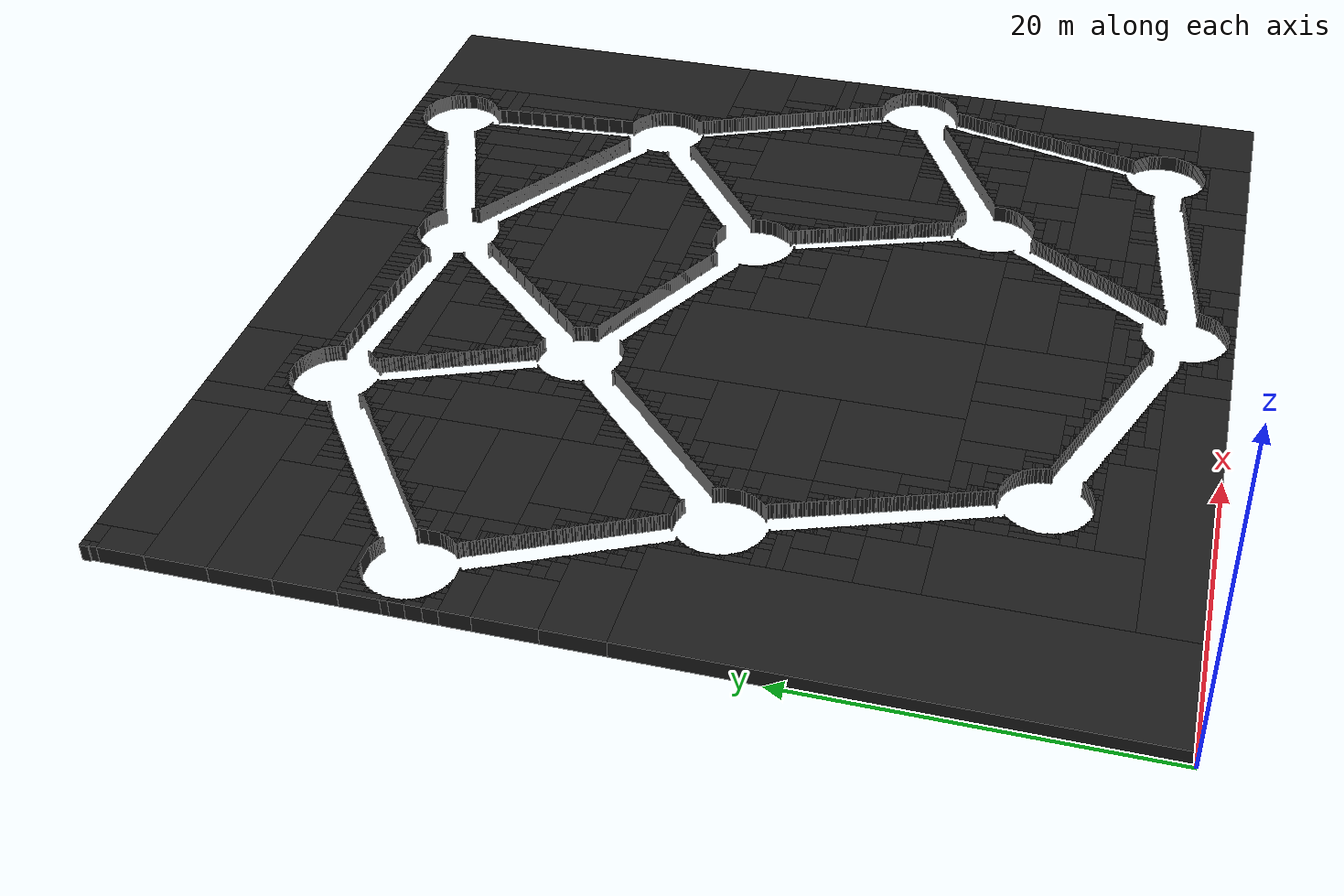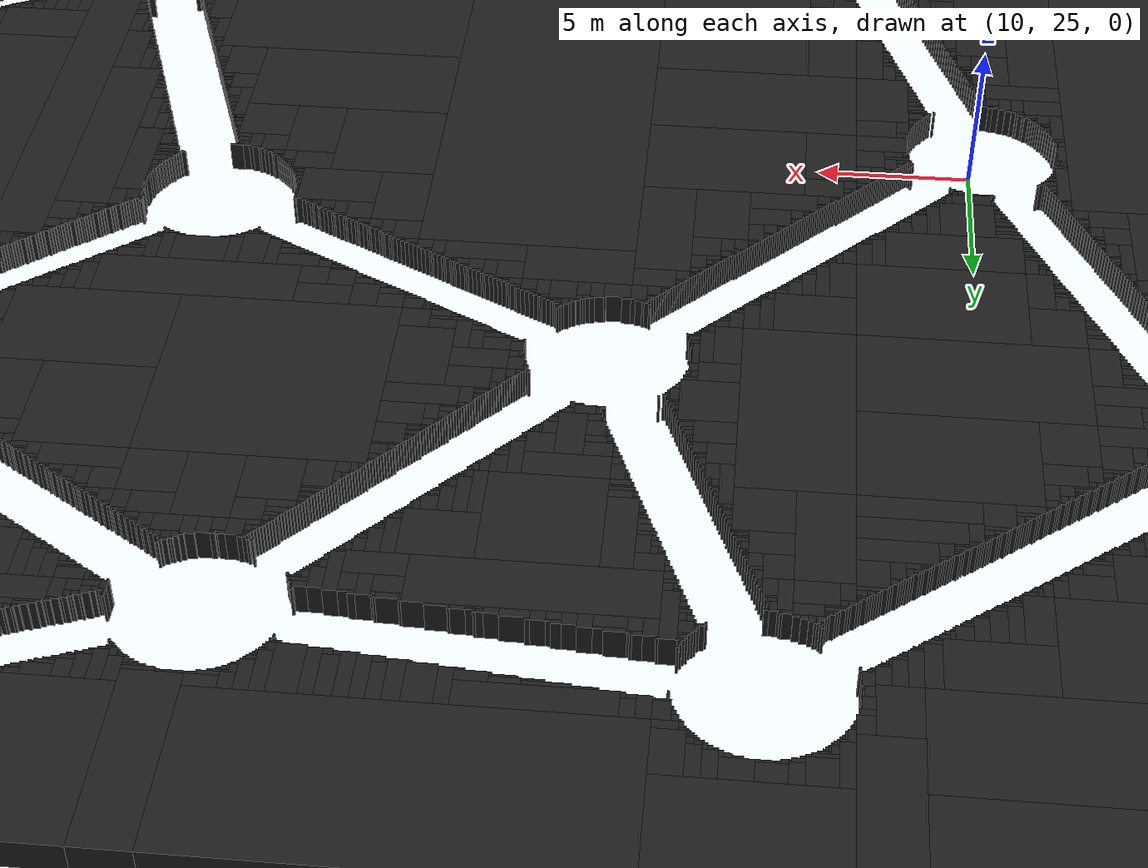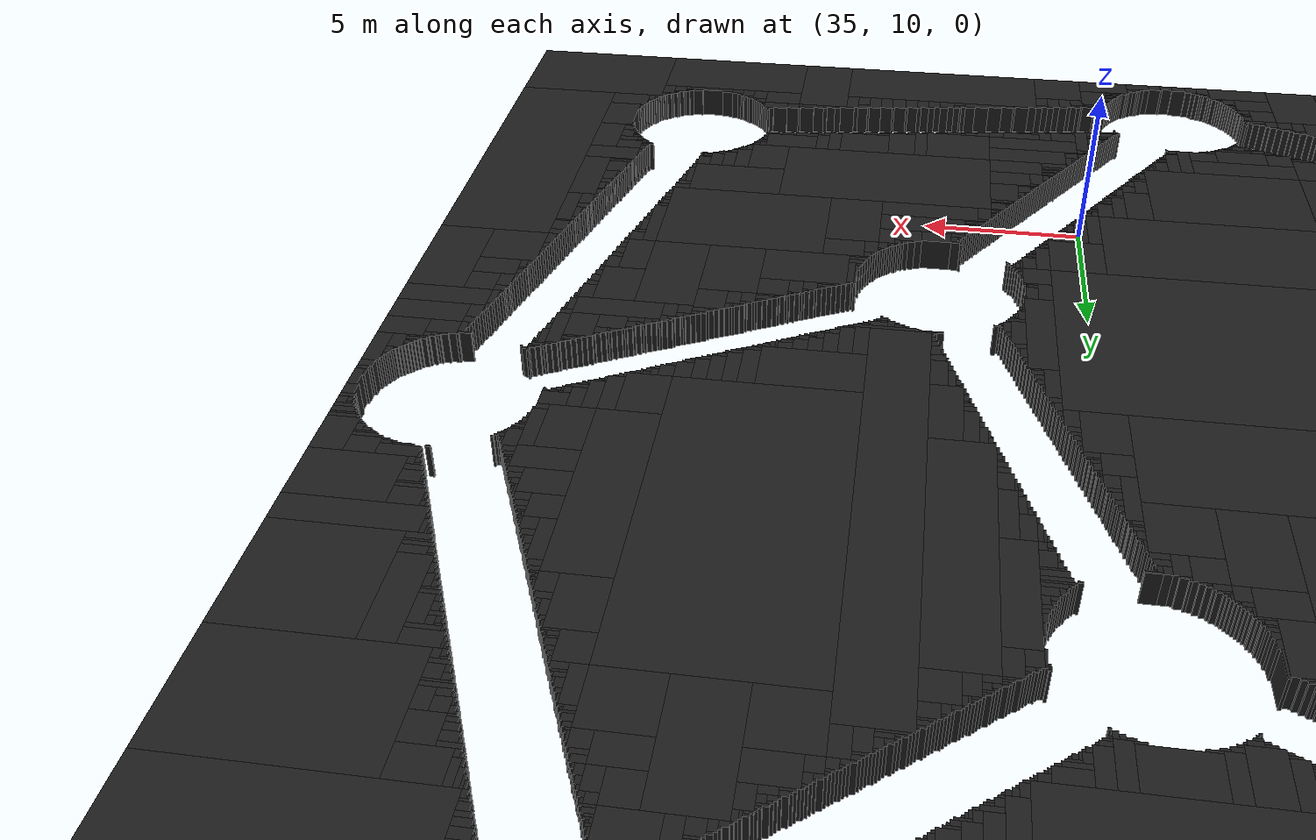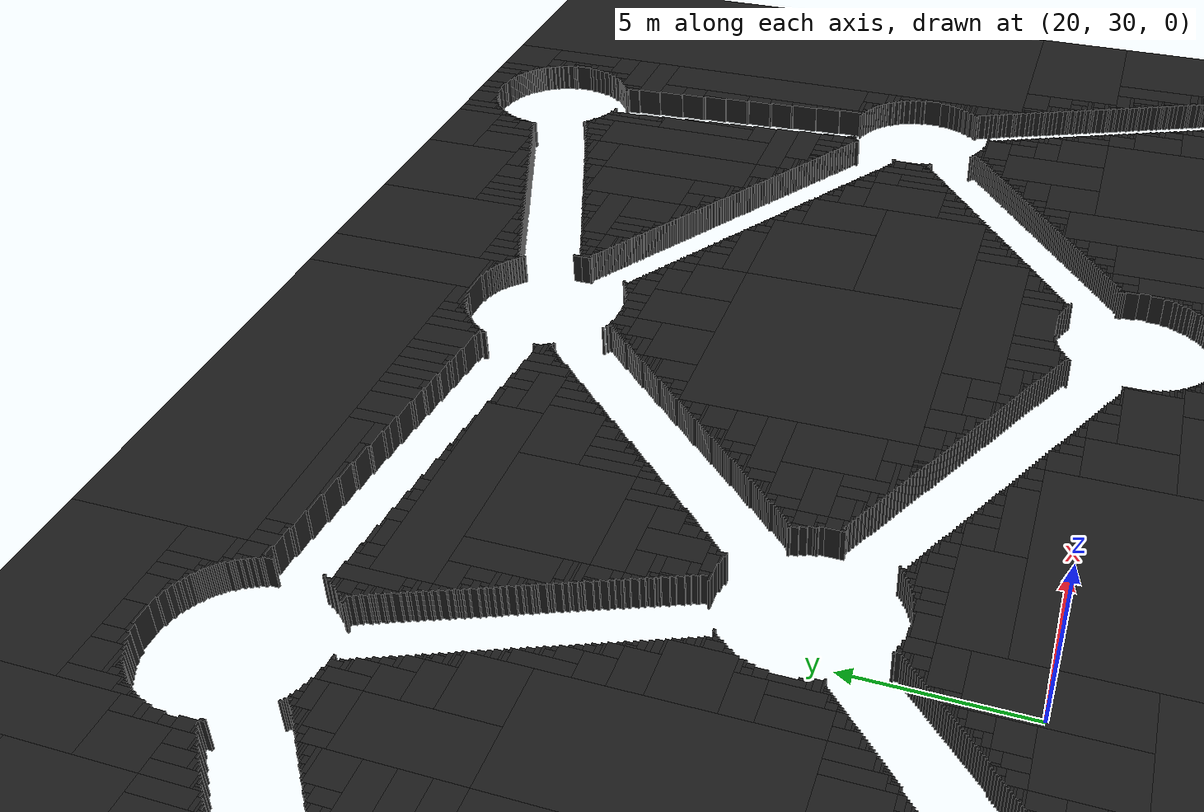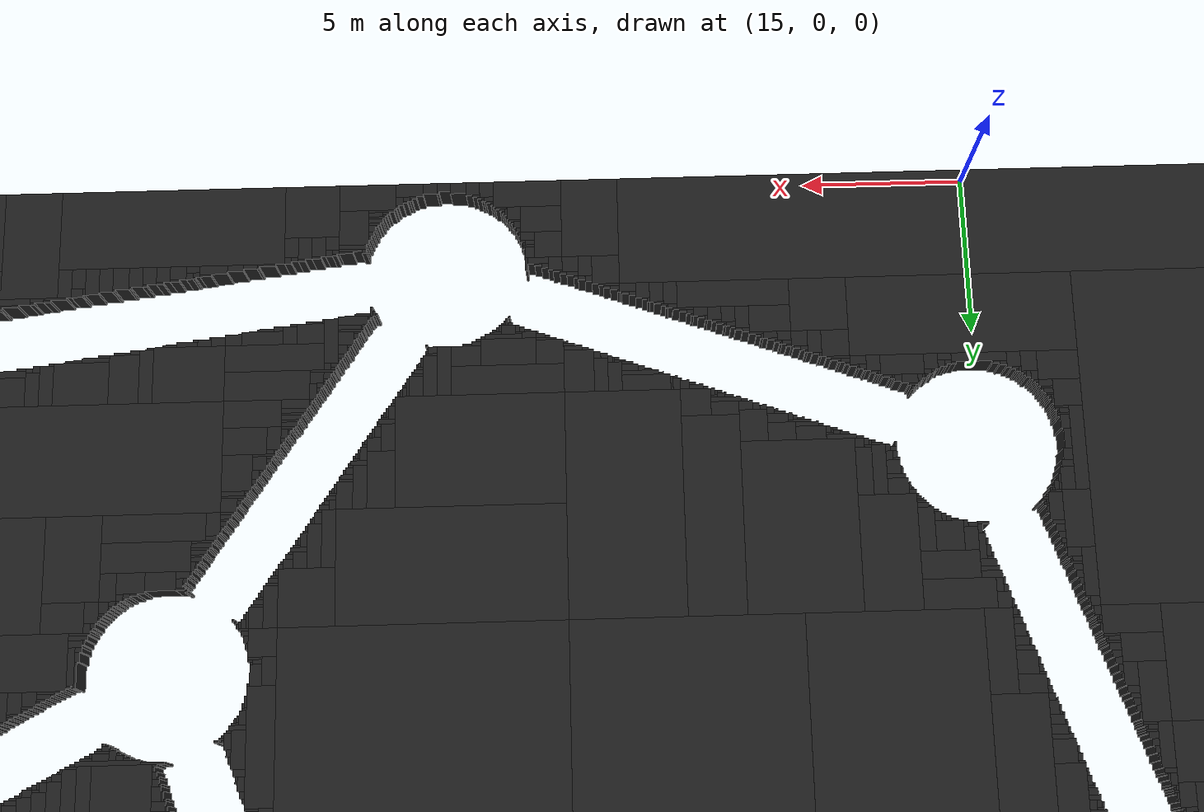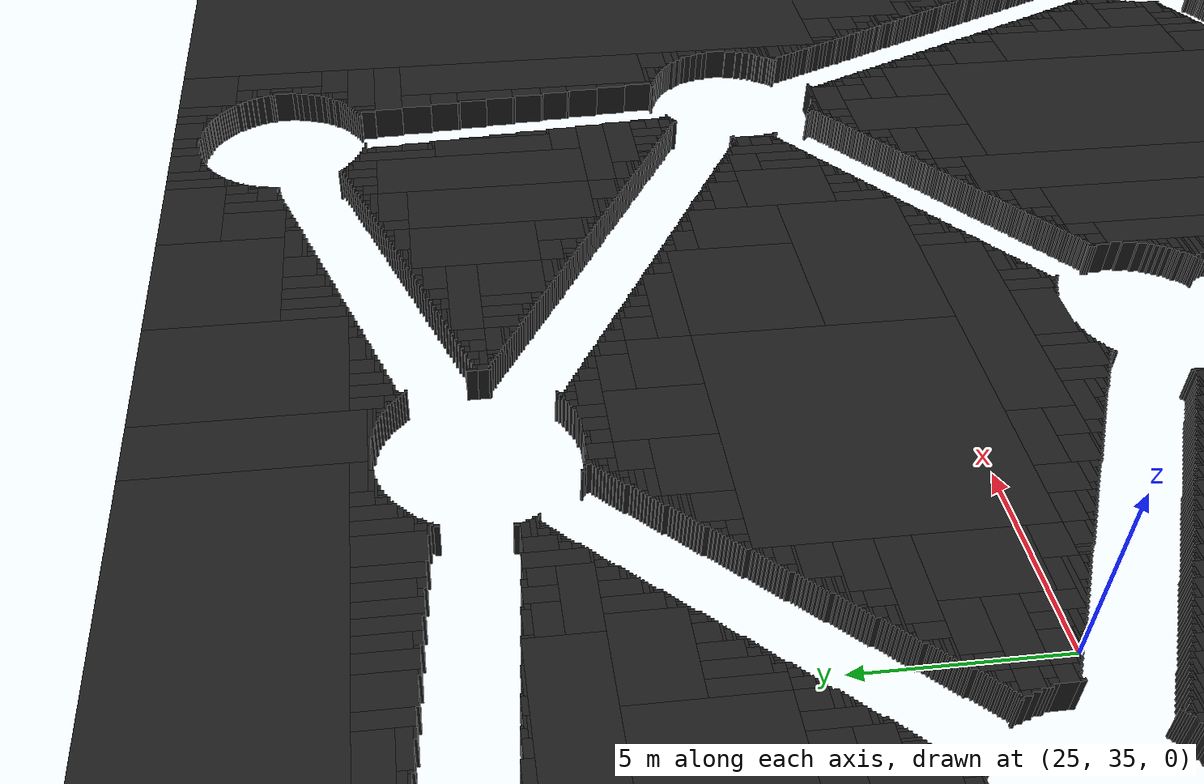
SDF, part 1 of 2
<?xml version='1.0'?>
<sdf version='1.6'>
<model name='ImageMaze'>
<static>true</static>
<pose frame=''>0 0 0 0 -0 0</pose>
<link name='WallLink'>
<collision name='Wall_3.5_13.8_Collision'>
	<geometry>
	<box>
 <size>6.790000 27.650000 1.000000</size>
 </box>
</geometry>
<pose frame=''>3.465000 13.825000 0.500000 0 0 0</pose>
</collision>
	<visual name='Wall_3.5_13.8_Visual'>
<pose frame=''>3.465000 13.825000 0.500000 0 0 0</pose>
	<geometry>
<box>
<size>6.790000 27.650000 1.000000</size>
</box>
</geometry>
<material>
<script>
<uri>file://media/materials/scripts/gazebo.material</uri>
<name>Gazebo/Black</name>
</script>
<ambient>0 0 0 0</ambient>
</material>
</visual>
<collision name='Wall_16.4_1.7_Collision'>
	<geometry>
	<box>
 <size>19.040001 3.430000 1.000000</size>
 </box>
</geometry>
<pose frame=''>16.379999 1.715000 0.500000 0 0 0</pose>
</collision>
	<visual name='Wall_16.4_1.7_Visual'>
<pose frame=''>16.379999 1.715000 0.500000 0 0 0</pose>
	<geometry>
<box>
<size>19.040001 3.430000 1.000000</size>
</box>
</geometry>
<material>
<script>
<uri>file://media/materials/scripts/gazebo.material</uri>
<name>Gazebo/Black</name>
</script>
<ambient>0 0 0 0</ambient>
</material>
</visual>
<collision name='Wall_9.4_8.6_Collision'>
	<geometry>
	<box>
 <size>5.180000 10.360000 1.000000</size>
 </box>
</geometry>
<pose frame=''>9.450000 8.610000 0.500000 0 0 0</pose>
</collision>
	<visual name='Wall_9.4_8.6_Visual'>
<pose frame=''>9.450000 8.610000 0.500000 0 0 0</pose>
	<geometry>
<box>
<size>5.180000 10.360000 1.000000</size>
</box>
</geometry>
<material>
<script>
<uri>file://media/materials/scripts/gazebo.material</uri>
<name>Gazebo/Black</name>
</script>
<ambient>0 0 0 0</ambient>
</material>
</visual>
<collision name='Wall_15.5_4.7_Collision'>
	<geometry>
	<box>
 <size>6.930000 2.520000 1.000000</size>
 </box>
</geometry>
<pose frame=''>15.505000 4.690000 0.500000 0 0 0</pose>
</collision>
	<visual name='Wall_15.5_4.7_Visual'>
<pose frame=''>15.505000 4.690000 0.500000 0 0 0</pose>
	<geometry>
<box>
<size>6.930000 2.520000 1.000000</size>
</box>
</geometry>
<material>
<script>
<uri>file://media/materials/scripts/gazebo.material</uri>
<name>Gazebo/Black</name>
</script>
<ambient>0 0 0 0</ambient>
</material>
</visual>
<collision name='Wall_12.7_6.4_Collision'>
	<geometry>
	<box>
 <size>1.260000 0.910000 1.000000</size>
 </box>
</geometry>
<pose frame=''>12.670000 6.405000 0.500000 0 0 0</pose>
</collision>
	<visual name='Wall_12.7_6.4_Visual'>
<pose frame=''>12.670000 6.405000 0.500000 0 0 0</pose>
	<geometry>
<box>
<size>1.260000 0.910000 1.000000</size>
</box>
</geometry>
<material>
<script>
<uri>file://media/materials/scripts/gazebo.material</uri>
<name>Gazebo/Black</name>
</script>
<ambient>0 0 0 0</ambient>
</material>
</visual>
<collision name='Wall_13.5_6.3_Collision'>
	<geometry>
	<box>
 <size>0.490000 0.630000 1.000000</size>
 </box>
</geometry>
<pose frame=''>13.545000 6.265000 0.500000 0 0 0</pose>
</collision>
	<visual name='Wall_13.5_6.3_Visual'>
<pose frame=''>13.545000 6.265000 0.500000 0 0 0</pose>
	<geometry>
<box>
<size>0.490000 0.630000 1.000000</size>
</box>
</geometry>
<material>
<script>
<uri>file://media/materials/scripts/gazebo.material</uri>
<name>Gazebo/Black</name>
</script>
<ambient>0 0 0 0</ambient>
</material>
</visual>
<collision name='Wall_13.4_6.7_Collision'>
	<geometry>
	<box>
 <size>0.210000 0.280000 1.000000</size>
 </box>
</geometry>
<pose frame=''>13.405000 6.720000 0.500000 0 0 0</pose>
</collision>
	<visual name='Wall_13.4_6.7_Visual'>
<pose frame=''>13.405000 6.720000 0.500000 0 0 0</pose>
	<geometry>
<box>
<size>0.210000 0.280000 1.000000</size>
</box>
</geometry>
<material>
<script>
<uri>file://media/materials/scripts/gazebo.material</uri>
<name>Gazebo/Black</name>
</script>
<ambient>0 0 0 0</ambient>
</material>
</visual>
<collision name='Wall_13.6_6.7_Collision'>
	<geometry>
	<box>
 <size>0.140000 0.210000 1.000000</size>
 </box>
</geometry>
<pose frame=''>13.580000 6.685000 0.500000 0 0 0</pose>
</collision>
	<visual name='Wall_13.6_6.7_Visual'>
<pose frame=''>13.580000 6.685000 0.500000 0 0 0</pose>
	<geometry>
<box>
<size>0.140000 0.210000 1.000000</size>
</box>
</geometry>
<material>
<script>
<uri>file://media/materials/scripts/gazebo.material</uri>
<name>Gazebo/Black</name>
</script>
<ambient>0 0 0 0</ambient>
</material>
</visual>
<collision name='Wall_13.7_6.6_Collision'>
	<geometry>
	<box>
 <size>0.140000 0.070000 1.000000</size>
 </box>
</geometry>
<pose frame=''>13.720000 6.615000 0.500000 0 0 0</pose>
</collision>
	<visual name='Wall_13.7_6.6_Visual'>
<pose frame=''>13.720000 6.615000 0.500000 0 0 0</pose>
	<geometry>
<box>
<size>0.140000 0.070000 1.000000</size>
</box>
</geometry>
<material>
<script>
<uri>file://media/materials/scripts/gazebo.material</uri>
<name>Gazebo/Black</name>
</script>
<ambient>0 0 0 0</ambient>
</material>
</visual>
<collision name='Wall_13.7_6.7_Collision'>
	<geometry>
	<box>
 <size>0.070000 0.070000 1.000000</size>
 </box>
</geometry>
<pose frame=''>13.685000 6.685000 0.500000 0 0 0</pose>
</collision>
	<visual name='Wall_13.7_6.7_Visual'>
<pose frame=''>13.685000 6.685000 0.500000 0 0 0</pose>
	<geometry>
<box>
<size>0.070000 0.070000 1.000000</size>
</box>
</geometry>
<material>
<script>
<uri>file://media/materials/scripts/gazebo.material</uri>
<name>Gazebo/Black</name>
</script>
<ambient>0 0 0 0</ambient>
</material>
</visual>
<collision name='Wall_12.5_7.3_Collision'>
	<geometry>
	<box>
 <size>0.840000 0.840000 1.000000</size>
 </box>
</geometry>
<pose frame=''>12.460000 7.280000 0.500000 0 0 0</pose>
</collision>
	<visual name='Wall_12.5_7.3_Visual'>
<pose frame=''>12.460000 7.280000 0.500000 0 0 0</pose>
	<geometry>
<box>
<size>0.840000 0.840000 1.000000</size>
</box>
</geometry>
<material>
<script>
<uri>file://media/materials/scripts/gazebo.material</uri>
<name>Gazebo/Black</name>
</script>
<ambient>0 0 0 0</ambient>
</material>
</visual>
<collision name='Wall_13.1_7.0_Collision'>
	<geometry>
	<box>
 <size>0.420000 0.210000 1.000000</size>
 </box>
</geometry>
<pose frame=''>13.090000 6.965000 0.500000 0 0 0</pose>
</collision>
	<visual name='Wall_13.1_7.0_Visual'>
<pose frame=''>13.090000 6.965000 0.500000 0 0 0</pose>
	<geometry>
<box>
<size>0.420000 0.210000 1.000000</size>
</box>
</geometry>
<material>
<script>
<uri>file://media/materials/scripts/gazebo.material</uri>
<name>Gazebo/Black</name>
</script>
<ambient>0 0 0 0</ambient>
</material>
</visual>
<collision name='Wall_13.1_7.1_Collision'>
	<geometry>
	<box>
 <size>0.350000 0.070000 1.000000</size>
 </box>
</geometry>
<pose frame=''>13.055000 7.105000 0.500000 0 0 0</pose>
</collision>
	<visual name='Wall_13.1_7.1_Visual'>
<pose frame=''>13.055000 7.105000 0.500000 0 0 0</pose>
	<geometry>
<box>
<size>0.350000 0.070000 1.000000</size>
</box>
</geometry>
<material>
<script>
<uri>file://media/materials/scripts/gazebo.material</uri>
<name>Gazebo/Black</name>
</script>
<ambient>0 0 0 0</ambient>
</material>
</visual>
<collision name='Wall_13.0_7.2_Collision'>
	<geometry>
	<box>
 <size>0.280000 0.140000 1.000000</size>
 </box>
</geometry>
<pose frame=''>13.020000 7.210000 0.500000 0 0 0</pose>
</collision>
	<visual name='Wall_13.0_7.2_Visual'>
<pose frame=''>13.020000 7.210000 0.500000 0 0 0</pose>
	<geometry>
<box>
<size>0.280000 0.140000 1.000000</size>
</box>
</geometry>
<material>
<script>
<uri>file://media/materials/scripts/gazebo.material</uri>
<name>Gazebo/Black</name>
</script>
<ambient>0 0 0 0</ambient>
</material>
</visual>
<collision name='Wall_13.2_7.2_Collision'>
	<geometry>
	<box>
 <size>0.070000 0.070000 1.000000</size>
 </box>
</geometry>
<pose frame=''>13.195000 7.175000 0.500000 0 0 0</pose>
</collision>
	<visual name='Wall_13.2_7.2_Visual'>
<pose frame=''>13.195000 7.175000 0.500000 0 0 0</pose>
	<geometry>
<box>
<size>0.070000 0.070000 1.000000</size>
</box>
</geometry>
<material>
<script>
<uri>file://media/materials/scripts/gazebo.material</uri>
<name>Gazebo/Black</name>
</script>
<ambient>0 0 0 0</ambient>
</material>
</visual>
<collision name='Wall_13.4_6.9_Collision'>
	<geometry>
	<box>
 <size>0.140000 0.070000 1.000000</size>
 </box>
</geometry>
<pose frame=''>13.370000 6.895000 0.500000 0 0 0</pose>
</collision>
	<visual name='Wall_13.4_6.9_Visual'>
<pose frame=''>13.370000 6.895000 0.500000 0 0 0</pose>
	<geometry>
<box>
<size>0.140000 0.070000 1.000000</size>
</box>
</geometry>
<material>
<script>
<uri>file://media/materials/scripts/gazebo.material</uri>
<name>Gazebo/Black</name>
</script>
<ambient>0 0 0 0</ambient>
</material>
</visual>
<collision name='Wall_13.3_7.0_Collision'>
	<geometry>
	<box>
 <size>0.070000 0.070000 1.000000</size>
 </box>
</geometry>
<pose frame=''>13.335000 6.965000 0.500000 0 0 0</pose>
</collision>
	<visual name='Wall_13.3_7.0_Visual'>
<pose frame=''>13.335000 6.965000 0.500000 0 0 0</pose>
	<geometry>
<box>
<size>0.070000 0.070000 1.000000</size>
</box>
</geometry>
<material>
<script>
<uri>file://media/materials/scripts/gazebo.material</uri>
<name>Gazebo/Black</name>
</script>
<ambient>0 0 0 0</ambient>
</material>
</visual>
<collision name='Wall_13.0_7.3_Collision'>
	<geometry>
	<box>
 <size>0.210000 0.070000 1.000000</size>
 </box>
</geometry>
<pose frame=''>12.985000 7.315000 0.500000 0 0 0</pose>
</collision>
	<visual name='Wall_13.0_7.3_Visual'>
<pose frame=''>12.985000 7.315000 0.500000 0 0 0</pose>
	<geometry>
<box>
<size>0.210000 0.070000 1.000000</size>
</box>
</geometry>
<material>
<script>
<uri>file://media/materials/scripts/gazebo.material</uri>
<name>Gazebo/Black</name>
</script>
<ambient>0 0 0 0</ambient>
</material>
</visual>
<collision name='Wall_12.9_7.5_Collision'>
	<geometry>
	<box>
 <size>0.070000 0.280000 1.000000</size>
 </box>
</geometry>
<pose frame=''>12.915000 7.490000 0.500000 0 0 0</pose>
</collision>
	<visual name='Wall_12.9_7.5_Visual'>
<pose frame=''>12.915000 7.490000 0.500000 0 0 0</pose>
	<geometry>
<box>
<size>0.070000 0.280000 1.000000</size>
</box>
</geometry>
<material>
<script>
<uri>file://media/materials/scripts/gazebo.material</uri>
<name>Gazebo/Black</name>
</script>
<ambient>0 0 0 0</ambient>
</material>
</visual>
<collision name='Wall_13.0_7.4_Collision'>
	<geometry>
	<box>
 <size>0.140000 0.070000 1.000000</size>
 </box>
</geometry>
<pose frame=''>13.020000 7.385000 0.500000 0 0 0</pose>
</collision>
	<visual name='Wall_13.0_7.4_Visual'>
<pose frame=''>13.020000 7.385000 0.500000 0 0 0</pose>
	<geometry>
<box>
<size>0.140000 0.070000 1.000000</size>
</box>
</geometry>
<material>
<script>
<uri>file://media/materials/scripts/gazebo.material</uri>
<name>Gazebo/Black</name>
</script>
<ambient>0 0 0 0</ambient>
</material>
</visual>
<collision name='Wall_13.0_7.5_Collision'>
	<geometry>
	<box>
 <size>0.070000 0.070000 1.000000</size>
 </box>
</geometry>
<pose frame=''>12.985000 7.455000 0.500000 0 0 0</pose>
</collision>
	<visual name='Wall_13.0_7.5_Visual'>
<pose frame=''>12.985000 7.455000 0.500000 0 0 0</pose>
	<geometry>
<box>
<size>0.070000 0.070000 1.000000</size>
</box>
</geometry>
<material>
<script>
<uri>file://media/materials/scripts/gazebo.material</uri>
<name>Gazebo/Black</name>
</script>
<ambient>0 0 0 0</ambient>
</material>
</visual>
<collision name='Wall_12.2_9.0_Collision'>
	<geometry>
	<box>
 <size>0.420000 2.590000 1.000000</size>
 </box>
</geometry>
<pose frame=''>12.250000 8.995000 0.500000 0 0 0</pose>
</collision>
	<visual name='Wall_12.2_9.0_Visual'>
<pose frame=''>12.250000 8.995000 0.500000 0 0 0</pose>
	<geometry>
<box>
<size>0.420000 2.590000 1.000000</size>
</box>
</geometry>
<material>
<script>
<uri>file://media/materials/scripts/gazebo.material</uri>
<name>Gazebo/Black</name>
</script>
<ambient>0 0 0 0</ambient>
</material>
</visual>
<collision name='Wall_12.7_7.7_Collision'>
	<geometry>
	<box>
 <size>0.420000 0.070000 1.000000</size>
 </box>
</geometry>
<pose frame=''>12.670000 7.735000 0.500000 0 0 0</pose>
</collision>
	<visual name='Wall_12.7_7.7_Visual'>
<pose frame=''>12.670000 7.735000 0.500000 0 0 0</pose>
	<geometry>
<box>
<size>0.420000 0.070000 1.000000</size>
</box>
</geometry>
<material>
<script>
<uri>file://media/materials/scripts/gazebo.material</uri>
<name>Gazebo/Black</name>
</script>
<ambient>0 0 0 0</ambient>
</material>
</visual>
<collision name='Wall_12.6_7.8_Collision'>
	<geometry>
	<box>
 <size>0.280000 0.140000 1.000000</size>
 </box>
</geometry>
<pose frame=''>12.600000 7.840000 0.500000 0 0 0</pose>
</collision>
	<visual name='Wall_12.6_7.8_Visual'>
<pose frame=''>12.600000 7.840000 0.500000 0 0 0</pose>
	<geometry>
<box>
<size>0.280000 0.140000 1.000000</size>
</box>
</geometry>
<material>
<script>
<uri>file://media/materials/scripts/gazebo.material</uri>
<name>Gazebo/Black</name>
</script>
<ambient>0 0 0 0</ambient>
</material>
</visual>
<collision name='Wall_12.8_7.8_Collision'>
	<geometry>
	<box>
 <size>0.140000 0.070000 1.000000</size>
 </box>
</geometry>
<pose frame=''>12.810000 7.805000 0.500000 0 0 0</pose>
</collision>
	<visual name='Wall_12.8_7.8_Visual'>
<pose frame=''>12.810000 7.805000 0.500000 0 0 0</pose>
	<geometry>
<box>
<size>0.140000 0.070000 1.000000</size>
</box>
</geometry>
<material>
<script>
<uri>file://media/materials/scripts/gazebo.material</uri>
<name>Gazebo/Black</name>
</script>
<ambient>0 0 0 0</ambient>
</material>
</visual>
<collision name='Wall_12.8_7.9_Collision'>
	<geometry>
	<box>
 <size>0.070000 0.070000 1.000000</size>
 </box>
</geometry>
<pose frame=''>12.775000 7.875000 0.500000 0 0 0</pose>
</collision>
	<visual name='Wall_12.8_7.9_Visual'>
<pose frame=''>12.775000 7.875000 0.500000 0 0 0</pose>
	<geometry>
<box>
<size>0.070000 0.070000 1.000000</size>
</box>
</geometry>
<material>
<script>
<uri>file://media/materials/scripts/gazebo.material</uri>
<name>Gazebo/Black</name>
</script>
<ambient>0 0 0 0</ambient>
</material>
</visual>
<collision name='Wall_12.6_7.9_Collision'>
	<geometry>
	<box>
 <size>0.350000 0.070000 1.000000</size>
 </box>
</geometry>
<pose frame=''>12.635000 7.945000 0.500000 0 0 0</pose>
</collision>
	<visual name='Wall_12.6_7.9_Visual'>
<pose frame=''>12.635000 7.945000 0.500000 0 0 0</pose>
	<geometry>
<box>
<size>0.350000 0.070000 1.000000</size>
</box>
</geometry>
<material>
<script>
<uri>file://media/materials/scripts/gazebo.material</uri>
<name>Gazebo/Black</name>
</script>
<ambient>0 0 0 0</ambient>
</material>
</visual>
<collision name='Wall_12.6_8.2_Collision'>
	<geometry>
	<box>
 <size>0.280000 0.420000 1.000000</size>
 </box>
</geometry>
<pose frame=''>12.600000 8.190000 0.500000 0 0 0</pose>
</collision>
	<visual name='Wall_12.6_8.2_Visual'>
<pose frame=''>12.600000 8.190000 0.500000 0 0 0</pose>
	<geometry>
<box>
<size>0.280000 0.420000 1.000000</size>
</box>
</geometry>
<material>
<script>
<uri>file://media/materials/scripts/gazebo.material</uri>
<name>Gazebo/Black</name>
</script>
<ambient>0 0 0 0</ambient>
</material>
</visual>
<collision name='Wall_12.8_8.0_Collision'>
	<geometry>
	<box>
 <size>0.070000 0.070000 1.000000</size>
 </box>
</geometry>
<pose frame=''>12.775000 8.015000 0.500000 0 0 0</pose>
</collision>
	<visual name='Wall_12.8_8.0_Visual'>
<pose frame=''>12.775000 8.015000 0.500000 0 0 0</pose>
	<geometry>
<box>
<size>0.070000 0.070000 1.000000</size>
</box>
</geometry>
<material>
<script>
<uri>file://media/materials/scripts/gazebo.material</uri>
<name>Gazebo/Black</name>
</script>
<ambient>0 0 0 0</ambient>
</material>
</visual>
<collision name='Wall_12.6_8.7_Collision'>
	<geometry>
	<box>
 <size>0.210000 0.630000 1.000000</size>
 </box>
</geometry>
<pose frame=''>12.565000 8.715000 0.500000 0 0 0</pose>
</collision>
	<visual name='Wall_12.6_8.7_Visual'>
<pose frame=''>12.565000 8.715000 0.500000 0 0 0</pose>
	<geometry>
<box>
<size>0.210000 0.630000 1.000000</size>
</box>
</geometry>
<material>
<script>
<uri>file://media/materials/scripts/gazebo.material</uri>
<name>Gazebo/Black</name>
</script>
<ambient>0 0 0 0</ambient>
</material>
</visual>
<collision name='Wall_12.6_9.2_Collision'>
	<geometry>
	<box>
 <size>0.280000 0.350000 1.000000</size>
 </box>
</geometry>
<pose frame=''>12.600000 9.205000 0.500000 0 0 0</pose>
</collision>
	<visual name='Wall_12.6_9.2_Visual'>
<pose frame=''>12.600000 9.205000 0.500000 0 0 0</pose>
	<geometry>
<box>
<size>0.280000 0.350000 1.000000</size>
</box>
</geometry>
<material>
<script>
<uri>file://media/materials/scripts/gazebo.material</uri>
<name>Gazebo/Black</name>
</script>
<ambient>0 0 0 0</ambient>
</material>
</visual>
<collision name='Wall_12.6_9.5_Collision'>
	<geometry>
	<box>
 <size>0.350000 0.210000 1.000000</size>
 </box>
</geometry>
<pose frame=''>12.635000 9.485000 0.500000 0 0 0</pose>
</collision>
	<visual name='Wall_12.6_9.5_Visual'>
<pose frame=''>12.635000 9.485000 0.500000 0 0 0</pose>
	<geometry>
<box>
<size>0.350000 0.210000 1.000000</size>
</box>
</geometry>
<material>
<script>
<uri>file://media/materials/scripts/gazebo.material</uri>
<name>Gazebo/Black</name>
</script>
<ambient>0 0 0 0</ambient>
</material>
</visual>
<collision name='Wall_12.7_9.9_Collision'>
	<geometry>
	<box>
 <size>0.420000 0.700000 1.000000</size>
 </box>
</geometry>
<pose frame=''>12.670000 9.940000 0.500000 0 0 0</pose>
</collision>
	<visual name='Wall_12.7_9.9_Visual'>
<pose frame=''>12.670000 9.940000 0.500000 0 0 0</pose>
	<geometry>
<box>
<size>0.420000 0.700000 1.000000</size>
</box>
</geometry>
<material>
<script>
<uri>file://media/materials/scripts/gazebo.material</uri>
<name>Gazebo/Black</name>
</script>
<ambient>0 0 0 0</ambient>
</material>
</visual>
<collision name='Wall_12.9_10.0_Collision'>
	<geometry>
	<box>
 <size>0.070000 0.490000 1.000000</size>
 </box>
</geometry>
<pose frame=''>12.915000 10.045000 0.500000 0 0 0</pose>
</collision>
	<visual name='Wall_12.9_10.0_Visual'>
<pose frame=''>12.915000 10.045000 0.500000 0 0 0</pose>
	<geometry>
<box>
<size>0.070000 0.490000 1.000000</size>
</box>
</geometry>
<material>
<script>
<uri>file://media/materials/scripts/gazebo.material</uri>
<name>Gazebo/Black</name>
</script>
<ambient>0 0 0 0</ambient>
</material>
</visual>
<collision name='Wall_13.0_10.0_Collision'>
	<geometry>
	<box>
 <size>0.070000 0.070000 1.000000</size>
 </box>
</geometry>
<pose frame=''>12.985000 9.975000 0.500000 0 0 0</pose>
</collision>
	<visual name='Wall_13.0_10.0_Visual'>
<pose frame=''>12.985000 9.975000 0.500000 0 0 0</pose>
	<geometry>
<box>
<size>0.070000 0.070000 1.000000</size>
</box>
</geometry>
<material>
<script>
<uri>file://media/materials/scripts/gazebo.material</uri>
<name>Gazebo/Black</name>
</script>
<ambient>0 0 0 0</ambient>
</material>
</visual>
<collision name='Wall_13.0_10.1_Collision'>
	<geometry>
	<box>
 <size>0.140000 0.280000 1.000000</size>
 </box>
</geometry>
<pose frame=''>13.020000 10.150000 0.500000 0 0 0</pose>
</collision>
	<visual name='Wall_13.0_10.1_Visual'>
<pose frame=''>13.020000 10.150000 0.500000 0 0 0</pose>
	<geometry>
<box>
<size>0.140000 0.280000 1.000000</size>
</box>
</geometry>
<material>
<script>
<uri>file://media/materials/scripts/gazebo.material</uri>
<name>Gazebo/Black</name>
</script>
<ambient>0 0 0 0</ambient>
</material>
</visual>
<collision name='Wall_13.1_10.2_Collision'>
	<geometry>
	<box>
 <size>0.070000 0.140000 1.000000</size>
 </box>
</geometry>
<pose frame=''>13.125000 10.220000 0.500000 0 0 0</pose>
</collision>
	<visual name='Wall_13.1_10.2_Visual'>
<pose frame=''>13.125000 10.220000 0.500000 0 0 0</pose>
	<geometry>
<box>
<size>0.070000 0.140000 1.000000</size>
</box>
</geometry>
<material>
<script>
<uri>file://media/materials/scripts/gazebo.material</uri>
<name>Gazebo/Black</name>
</script>
<ambient>0 0 0 0</ambient>
</material>
</visual>
<collision name='Wall_13.2_10.3_Collision'>
	<geometry>
	<box>
 <size>0.070000 0.070000 1.000000</size>
 </box>
</geometry>
<pose frame=''>13.195000 10.255000 0.500000 0 0 0</pose>
</collision>
	<visual name='Wall_13.2_10.3_Visual'>
<pose frame=''>13.195000 10.255000 0.500000 0 0 0</pose>
	<geometry>
<box>
<size>0.070000 0.070000 1.000000</size>
</box>
</geometry>
<material>
<script>
<uri>file://media/materials/scripts/gazebo.material</uri>
<name>Gazebo/Black</name>
</script>
<ambient>0 0 0 0</ambient>
</material>
</visual>
<collision name='Wall_12.5_11.2_Collision'>
	<geometry>
	<box>
 <size>0.840000 1.750000 1.000000</size>
 </box>
</geometry>
<pose frame=''>12.460000 11.165000 0.500000 0 0 0</pose>
</collision>
	<visual name='Wall_12.5_11.2_Visual'>
<pose frame=''>12.460000 11.165000 0.500000 0 0 0</pose>
	<geometry>
<box>
<size>0.840000 1.750000 1.000000</size>
</box>
</geometry>
<material>
<script>
<uri>file://media/materials/scripts/gazebo.material</uri>
<name>Gazebo/Black</name>
</script>
<ambient>0 0 0 0</ambient>
</material>
</visual>
<collision name='Wall_13.1_10.3_Collision'>
	<geometry>
	<box>
 <size>0.350000 0.070000 1.000000</size>
 </box>
</geometry>
<pose frame=''>13.055000 10.325000 0.500000 0 0 0</pose>
</collision>
	<visual name='Wall_13.1_10.3_Visual'>
<pose frame=''>13.055000 10.325000 0.500000 0 0 0</pose>
	<geometry>
<box>
<size>0.350000 0.070000 1.000000</size>
</box>
</geometry>
<material>
<script>
<uri>file://media/materials/scripts/gazebo.material</uri>
<name>Gazebo/Black</name>
</script>
<ambient>0 0 0 0</ambient>
</material>
</visual>
<collision name='Wall_13.1_10.8_Collision'>
	<geometry>
	<box>
 <size>0.420000 0.840000 1.000000</size>
 </box>
</geometry>
<pose frame=''>13.090000 10.780000 0.500000 0 0 0</pose>
</collision>
	<visual name='Wall_13.1_10.8_Visual'>
<pose frame=''>13.090000 10.780000 0.500000 0 0 0</pose>
	<geometry>
<box>
<size>0.420000 0.840000 1.000000</size>
</box>
</geometry>
<material>
<script>
<uri>file://media/materials/scripts/gazebo.material</uri>
<name>Gazebo/Black</name>
</script>
<ambient>0 0 0 0</ambient>
</material>
</visual>
<collision name='Wall_13.3_10.5_Collision'>
	<geometry>
	<box>
 <size>0.070000 0.070000 1.000000</size>
 </box>
</geometry>
<pose frame=''>13.335000 10.465000 0.500000 0 0 0</pose>
</collision>
	<visual name='Wall_13.3_10.5_Visual'>
<pose frame=''>13.335000 10.465000 0.500000 0 0 0</pose>
	<geometry>
<box>
<size>0.070000 0.070000 1.000000</size>
</box>
</geometry>
<material>
<script>
<uri>file://media/materials/scripts/gazebo.material</uri>
<name>Gazebo/Black</name>
</script>
<ambient>0 0 0 0</ambient>
</material>
</visual>
<collision name='Wall_13.4_10.5_Collision'>
	<geometry>
	<box>
 <size>0.140000 0.070000 1.000000</size>
 </box>
</geometry>
<pose frame=''>13.370000 10.535000 0.500000 0 0 0</pose>
</collision>
	<visual name='Wall_13.4_10.5_Visual'>
<pose frame=''>13.370000 10.535000 0.500000 0 0 0</pose>
	<geometry>
<box>
<size>0.140000 0.070000 1.000000</size>
</box>
</geometry>
<material>
<script>
<uri>file://media/materials/scripts/gazebo.material</uri>
<name>Gazebo/Black</name>
</script>
<ambient>0 0 0 0</ambient>
</material>
</visual>
<collision name='Wall_13.3_10.6_Collision'>
	<geometry>
	<box>
 <size>0.070000 0.140000 1.000000</size>
 </box>
</geometry>
<pose frame=''>13.335000 10.640000 0.500000 0 0 0</pose>
</collision>
	<visual name='Wall_13.3_10.6_Visual'>
<pose frame=''>13.335000 10.640000 0.500000 0 0 0</pose>
	<geometry>
<box>
<size>0.070000 0.140000 1.000000</size>
</box>
</geometry>
<material>
<script>
<uri>file://media/materials/scripts/gazebo.material</uri>
<name>Gazebo/Black</name>
</script>
<ambient>0 0 0 0</ambient>
</material>
</visual>
<collision name='Wall_13.4_10.6_Collision'>
	<geometry>
	<box>
 <size>0.140000 0.070000 1.000000</size>
 </box>
</geometry>
<pose frame=''>13.440001 10.605000 0.500000 0 0 0</pose>
</collision>
	<visual name='Wall_13.4_10.6_Visual'>
<pose frame=''>13.440001 10.605000 0.500000 0 0 0</pose>
	<geometry>
<box>
<size>0.140000 0.070000 1.000000</size>
</box>
</geometry>
<material>
<script>
<uri>file://media/materials/scripts/gazebo.material</uri>
<name>Gazebo/Black</name>
</script>
<ambient>0 0 0 0</ambient>
</material>
</visual>
<collision name='Wall_13.4_10.7_Collision'>
	<geometry>
	<box>
 <size>0.070000 0.070000 1.000000</size>
 </box>
</geometry>
<pose frame=''>13.405000 10.675000 0.500000 0 0 0</pose>
</collision>
	<visual name='Wall_13.4_10.7_Visual'>
<pose frame=''>13.405000 10.675000 0.500000 0 0 0</pose>
	<geometry>
<box>
<size>0.070000 0.070000 1.000000</size>
</box>
</geometry>
<material>
<script>
<uri>file://media/materials/scripts/gazebo.material</uri>
<name>Gazebo/Black</name>
</script>
<ambient>0 0 0 0</ambient>
</material>
</visual>
<collision name='Wall_13.5_10.7_Collision'>
	<geometry>
	<box>
 <size>0.070000 0.070000 1.000000</size>
 </box>
</geometry>
<pose frame=''>13.545000 10.675000 0.500000 0 0 0</pose>
</collision>
	<visual name='Wall_13.5_10.7_Visual'>
<pose frame=''>13.545000 10.675000 0.500000 0 0 0</pose>
	<geometry>
<box>
<size>0.070000 0.070000 1.000000</size>
</box>
</geometry>
<material>
<script>
<uri>file://media/materials/scripts/gazebo.material</uri>
<name>Gazebo/Black</name>
</script>
<ambient>0 0 0 0</ambient>
</material>
</visual>
<collision name='Wall_13.4_10.7_Collision'>
	<geometry>
	<box>
 <size>0.140000 0.070000 1.000000</size>
 </box>
</geometry>
<pose frame=''>13.370000 10.745000 0.500000 0 0 0</pose>
</collision>
	<visual name='Wall_13.4_10.7_Visual'>
<pose frame=''>13.370000 10.745000 0.500000 0 0 0</pose>
	<geometry>
<box>
<size>0.140000 0.070000 1.000000</size>
</box>
</geometry>
<material>
<script>
<uri>file://media/materials/scripts/gazebo.material</uri>
<name>Gazebo/Black</name>
</script>
<ambient>0 0 0 0</ambient>
</material>
</visual>
<collision name='Wall_13.3_10.9_Collision'>
	<geometry>
	<box>
 <size>0.070000 0.210000 1.000000</size>
 </box>
</geometry>
<pose frame=''>13.335000 10.885000 0.500000 0 0 0</pose>
</collision>
	<visual name='Wall_13.3_10.9_Visual'>
<pose frame=''>13.335000 10.885000 0.500000 0 0 0</pose>
	<geometry>
<box>
<size>0.070000 0.210000 1.000000</size>
</box>
</geometry>
<material>
<script>
<uri>file://media/materials/scripts/gazebo.material</uri>
<name>Gazebo/Black</name>
</script>
<ambient>0 0 0 0</ambient>
</material>
</visual>
<collision name='Wall_13.1_11.3_Collision'>
	<geometry>
	<box>
 <size>0.350000 0.140000 1.000000</size>
 </box>
</geometry>
<pose frame=''>13.055000 11.270000 0.500000 0 0 0</pose>
</collision>
	<visual name='Wall_13.1_11.3_Visual'>
<pose frame=''>13.055000 11.270000 0.500000 0 0 0</pose>
	<geometry>
<box>
<size>0.350000 0.140000 1.000000</size>
</box>
</geometry>
<material>
<script>
<uri>file://media/materials/scripts/gazebo.material</uri>
<name>Gazebo/Black</name>
</script>
<ambient>0 0 0 0</ambient>
</material>
</visual>
<collision name='Wall_13.0_11.4_Collision'>
	<geometry>
	<box>
 <size>0.280000 0.210000 1.000000</size>
 </box>
</geometry>
<pose frame=''>13.020000 11.445000 0.500000 0 0 0</pose>
</collision>
	<visual name='Wall_13.0_11.4_Visual'>
<pose frame=''>13.020000 11.445000 0.500000 0 0 0</pose>
	<geometry>
<box>
<size>0.280000 0.210000 1.000000</size>
</box>
</geometry>
<material>
<script>
<uri>file://media/materials/scripts/gazebo.material</uri>
<name>Gazebo/Black</name>
</script>
<ambient>0 0 0 0</ambient>
</material>
</visual>
<collision name='Wall_13.0_11.7_Collision'>
	<geometry>
	<box>
 <size>0.210000 0.210000 1.000000</size>
 </box>
</geometry>
<pose frame=''>12.985000 11.655000 0.500000 0 0 0</pose>
</collision>
	<visual name='Wall_13.0_11.7_Visual'>
<pose frame=''>12.985000 11.655000 0.500000 0 0 0</pose>
	<geometry>
<box>
<size>0.210000 0.210000 1.000000</size>
</box>
</geometry>
<material>
<script>
<uri>file://media/materials/scripts/gazebo.material</uri>
<name>Gazebo/Black</name>
</script>
<ambient>0 0 0 0</ambient>
</material>
</visual>
<collision name='Wall_12.9_11.8_Collision'>
	<geometry>
	<box>
 <size>0.140000 0.140000 1.000000</size>
 </box>
</geometry>
<pose frame=''>12.950000 11.830000 0.500000 0 0 0</pose>
</collision>
	<visual name='Wall_12.9_11.8_Visual'>
<pose frame=''>12.950000 11.830000 0.500000 0 0 0</pose>
	<geometry>
<box>
<size>0.140000 0.140000 1.000000</size>
</box>
</geometry>
<material>
<script>
<uri>file://media/materials/scripts/gazebo.material</uri>
<name>Gazebo/Black</name>
</script>
<ambient>0 0 0 0</ambient>
</material>
</visual>
<collision name='Wall_12.9_12.0_Collision'>
	<geometry>
	<box>
 <size>0.070000 0.280000 1.000000</size>
 </box>
</geometry>
<pose frame=''>12.915000 12.040000 0.500000 0 0 0</pose>
</collision>
	<visual name='Wall_12.9_12.0_Visual'>
<pose frame=''>12.915000 12.040000 0.500000 0 0 0</pose>
	<geometry>
<box>
<size>0.070000 0.280000 1.000000</size>
</box>
</geometry>
<material>
<script>
<uri>file://media/materials/scripts/gazebo.material</uri>
<name>Gazebo/Black</name>
</script>
<ambient>0 0 0 0</ambient>
</material>
</visual>
<collision name='Wall_13.0_11.9_Collision'>
	<geometry>
	<box>
 <size>0.070000 0.070000 1.000000</size>
 </box>
</geometry>
<pose frame=''>12.985000 11.935000 0.500000 0 0 0</pose>
</collision>
	<visual name='Wall_13.0_11.9_Visual'>
<pose frame=''>12.985000 11.935000 0.500000 0 0 0</pose>
	<geometry>
<box>
<size>0.070000 0.070000 1.000000</size>
</box>
</geometry>
<material>
<script>
<uri>file://media/materials/scripts/gazebo.material</uri>
<name>Gazebo/Black</name>
</script>
<ambient>0 0 0 0</ambient>
</material>
</visual>
<collision name='Wall_12.2_12.8_Collision'>
	<geometry>
	<box>
 <size>0.420000 1.470000 1.000000</size>
 </box>
</geometry>
<pose frame=''>12.250000 12.775000 0.500000 0 0 0</pose>
</collision>
	<visual name='Wall_12.2_12.8_Visual'>
<pose frame=''>12.250000 12.775000 0.500000 0 0 0</pose>
	<geometry>
<box>
<size>0.420000 1.470000 1.000000</size>
</box>
</geometry>
<material>
<script>
<uri>file://media/materials/scripts/gazebo.material</uri>
<name>Gazebo/Black</name>
</script>
<ambient>0 0 0 0</ambient>
</material>
</visual>
<collision name='Wall_12.7_12.2_Collision'>
	<geometry>
	<box>
 <size>0.420000 0.280000 1.000000</size>
 </box>
</geometry>
<pose frame=''>12.670000 12.180000 0.500000 0 0 0</pose>
</collision>
	<visual name='Wall_12.7_12.2_Visual'>
<pose frame=''>12.670000 12.180000 0.500000 0 0 0</pose>
	<geometry>
<box>
<size>0.420000 0.280000 1.000000</size>
</box>
</geometry>
<material>
<script>
<uri>file://media/materials/scripts/gazebo.material</uri>
<name>Gazebo/Black</name>
</script>
<ambient>0 0 0 0</ambient>
</material>
</visual>
<collision name='Wall_12.6_12.4_Collision'>
	<geometry>
	<box>
 <size>0.280000 0.140000 1.000000</size>
 </box>
</geometry>
<pose frame=''>12.600000 12.390000 0.500000 0 0 0</pose>
</collision>
	<visual name='Wall_12.6_12.4_Visual'>
<pose frame=''>12.600000 12.390000 0.500000 0 0 0</pose>
	<geometry>
<box>
<size>0.280000 0.140000 1.000000</size>
</box>
</geometry>
<material>
<script>
<uri>file://media/materials/scripts/gazebo.material</uri>
<name>Gazebo/Black</name>
</script>
<ambient>0 0 0 0</ambient>
</material>
</visual>
<collision name='Wall_12.8_12.4_Collision'>
	<geometry>
	<box>
 <size>0.140000 0.070000 1.000000</size>
 </box>
</geometry>
<pose frame=''>12.810000 12.355000 0.500000 0 0 0</pose>
</collision>
	<visual name='Wall_12.8_12.4_Visual'>
<pose frame=''>12.810000 12.355000 0.500000 0 0 0</pose>
	<geometry>
<box>
<size>0.140000 0.070000 1.000000</size>
</box>
</geometry>
<material>
<script>
<uri>file://media/materials/scripts/gazebo.material</uri>
<name>Gazebo/Black</name>
</script>
<ambient>0 0 0 0</ambient>
</material>
</visual>
<collision name='Wall_12.8_12.4_Collision'>
	<geometry>
	<box>
 <size>0.070000 0.070000 1.000000</size>
 </box>
</geometry>
<pose frame=''>12.775000 12.425000 0.500000 0 0 0</pose>
</collision>
	<visual name='Wall_12.8_12.4_Visual'>
<pose frame=''>12.775000 12.425000 0.500000 0 0 0</pose>
	<geometry>
<box>
<size>0.070000 0.070000 1.000000</size>
</box>
</geometry>
<material>
<script>
<uri>file://media/materials/scripts/gazebo.material</uri>
<name>Gazebo/Black</name>
</script>
<ambient>0 0 0 0</ambient>
</material>
</visual>
<collision name='Wall_12.6_12.5_Collision'>
	<geometry>
	<box>
 <size>0.350000 0.070000 1.000000</size>
 </box>
</geometry>
<pose frame=''>12.635000 12.495000 0.500000 0 0 0</pose>
</collision>
	<visual name='Wall_12.6_12.5_Visual'>
<pose frame=''>12.635000 12.495000 0.500000 0 0 0</pose>
	<geometry>
<box>
<size>0.350000 0.070000 1.000000</size>
</box>
</geometry>
<material>
<script>
<uri>file://media/materials/scripts/gazebo.material</uri>
<name>Gazebo/Black</name>
</script>
<ambient>0 0 0 0</ambient>
</material>
</visual>
<collision name='Wall_12.6_12.6_Collision'>
	<geometry>
	<box>
 <size>0.280000 0.210000 1.000000</size>
 </box>
</geometry>
<pose frame=''>12.600000 12.635000 0.500000 0 0 0</pose>
</collision>
	<visual name='Wall_12.6_12.6_Visual'>
<pose frame=''>12.600000 12.635000 0.500000 0 0 0</pose>
	<geometry>
<box>
<size>0.280000 0.210000 1.000000</size>
</box>
</geometry>
<material>
<script>
<uri>file://media/materials/scripts/gazebo.material</uri>
<name>Gazebo/Black</name>
</script>
<ambient>0 0 0 0</ambient>
</material>
</visual>
<collision name='Wall_12.6_12.8_Collision'>
	<geometry>
	<box>
 <size>0.210000 0.210000 1.000000</size>
 </box>
</geometry>
<pose frame=''>12.565000 12.845000 0.500000 0 0 0</pose>
</collision>
	<visual name='Wall_12.6_12.8_Visual'>
<pose frame=''>12.565000 12.845000 0.500000 0 0 0</pose>
	<geometry>
<box>
<size>0.210000 0.210000 1.000000</size>
</box>
</geometry>
<material>
<script>
<uri>file://media/materials/scripts/gazebo.material</uri>
<name>Gazebo/Black</name>
</script>
<ambient>0 0 0 0</ambient>
</material>
</visual>
<collision name='Wall_12.5_13.1_Collision'>
	<geometry>
	<box>
 <size>0.140000 0.210000 1.000000</size>
 </box>
</geometry>
<pose frame=''>12.530000 13.055000 0.500000 0 0 0</pose>
</collision>
	<visual name='Wall_12.5_13.1_Visual'>
<pose frame=''>12.530000 13.055000 0.500000 0 0 0</pose>
	<geometry>
<box>
<size>0.140000 0.210000 1.000000</size>
</box>
</geometry>
<material>
<script>
<uri>file://media/materials/scripts/gazebo.material</uri>
<name>Gazebo/Black</name>
</script>
<ambient>0 0 0 0</ambient>
</material>
</visual>
<collision name='Wall_12.5_13.3_Collision'>
	<geometry>
	<box>
 <size>0.070000 0.210000 1.000000</size>
 </box>
</geometry>
<pose frame=''>12.495000 13.265000 0.500000 0 0 0</pose>
</collision>
	<visual name='Wall_12.5_13.3_Visual'>
<pose frame=''>12.495000 13.265000 0.500000 0 0 0</pose>
	<geometry>
<box>
<size>0.070000 0.210000 1.000000</size>
</box>
</geometry>
<material>
<script>
<uri>file://media/materials/scripts/gazebo.material</uri>
<name>Gazebo/Black</name>
</script>
<ambient>0 0 0 0</ambient>
</material>
</visual>
<collision name='Wall_12.2_13.6_Collision'>
	<geometry>
	<box>
 <size>0.280000 0.280000 1.000000</size>
 </box>
</geometry>
<pose frame=''>12.180000 13.650000 0.500000 0 0 0</pose>
</collision>
	<visual name='Wall_12.2_13.6_Visual'>
<pose frame=''>12.180000 13.650000 0.500000 0 0 0</pose>
	<geometry>
<box>
<size>0.280000 0.280000 1.000000</size>
</box>
</geometry>
<material>
<script>
<uri>file://media/materials/scripts/gazebo.material</uri>
<name>Gazebo/Black</name>
</script>
<ambient>0 0 0 0</ambient>
</material>
</visual>
<collision name='Wall_12.4_13.5_Collision'>
	<geometry>
	<box>
 <size>0.140000 0.070000 1.000000</size>
 </box>
</geometry>
<pose frame=''>12.390000 13.545000 0.500000 0 0 0</pose>
</collision>
	<visual name='Wall_12.4_13.5_Visual'>
<pose frame=''>12.390000 13.545000 0.500000 0 0 0</pose>
	<geometry>
<box>
<size>0.140000 0.070000 1.000000</size>
</box>
</geometry>
<material>
<script>
<uri>file://media/materials/scripts/gazebo.material</uri>
<name>Gazebo/Black</name>
</script>
<ambient>0 0 0 0</ambient>
</material>
</visual>
<collision name='Wall_12.4_13.7_Collision'>
	<geometry>
	<box>
 <size>0.070000 0.210000 1.000000</size>
 </box>
</geometry>
<pose frame=''>12.355000 13.685000 0.500000 0 0 0</pose>
</collision>
	<visual name='Wall_12.4_13.7_Visual'>
<pose frame=''>12.355000 13.685000 0.500000 0 0 0</pose>
	<geometry>
<box>
<size>0.070000 0.210000 1.000000</size>
</box>
</geometry>
<material>
<script>
<uri>file://media/materials/scripts/gazebo.material</uri>
<name>Gazebo/Black</name>
</script>
<ambient>0 0 0 0</ambient>
</material>
</visual>
<collision name='Wall_14.0_6.2_Collision'>
	<geometry>
	<box>
 <size>0.420000 0.490000 1.000000</size>
 </box>
</geometry>
<pose frame=''>14.000000 6.195000 0.500000 0 0 0</pose>
</collision>
	<visual name='Wall_14.0_6.2_Visual'>
<pose frame=''>14.000000 6.195000 0.500000 0 0 0</pose>
	<geometry>
<box>
<size>0.420000 0.490000 1.000000</size>
</box>
</geometry>
<material>
<script>
<uri>file://media/materials/scripts/gazebo.material</uri>
<name>Gazebo/Black</name>
</script>
<ambient>0 0 0 0</ambient>
</material>
</visual>
<collision name='Wall_15.1_6.1_Collision'>
	<geometry>
	<box>
 <size>1.680000 0.280000 1.000000</size>
 </box>
</geometry>
<pose frame=''>15.050000 6.090000 0.500000 0 0 0</pose>
</collision>
	<visual name='Wall_15.1_6.1_Visual'>
<pose frame=''>15.050000 6.090000 0.500000 0 0 0</pose>
	<geometry>
<box>
<size>1.680000 0.280000 1.000000</size>
</box>
</geometry>
<material>
<script>
<uri>file://media/materials/scripts/gazebo.material</uri>
<name>Gazebo/Black</name>
</script>
<ambient>0 0 0 0</ambient>
</material>
</visual>
<collision name='Wall_14.3_6.3_Collision'>
	<geometry>
	<box>
 <size>0.210000 0.140000 1.000000</size>
 </box>
</geometry>
<pose frame=''>14.315001 6.300000 0.500000 0 0 0</pose>
</collision>
	<visual name='Wall_14.3_6.3_Visual'>
<pose frame=''>14.315001 6.300000 0.500000 0 0 0</pose>
	<geometry>
<box>
<size>0.210000 0.140000 1.000000</size>
</box>
</geometry>
<material>
<script>
<uri>file://media/materials/scripts/gazebo.material</uri>
<name>Gazebo/Black</name>
</script>
<ambient>0 0 0 0</ambient>
</material>
</visual>
<collision name='Wall_14.5_6.3_Collision'>
	<geometry>
	<box>
 <size>0.210000 0.070000 1.000000</size>
 </box>
</geometry>
<pose frame=''>14.525000 6.265000 0.500000 0 0 0</pose>
</collision>
	<visual name='Wall_14.5_6.3_Visual'>
<pose frame=''>14.525000 6.265000 0.500000 0 0 0</pose>
	<geometry>
<box>
<size>0.210000 0.070000 1.000000</size>
</box>
</geometry>
<material>
<script>
<uri>file://media/materials/scripts/gazebo.material</uri>
<name>Gazebo/Black</name>
</script>
<ambient>0 0 0 0</ambient>
</material>
</visual>
<collision name='Wall_13.8_6.5_Collision'>
	<geometry>
	<box>
 <size>0.070000 0.140000 1.000000</size>
 </box>
</geometry>
<pose frame=''>13.825000 6.510000 0.500000 0 0 0</pose>
</collision>
	<visual name='Wall_13.8_6.5_Visual'>
<pose frame=''>13.825000 6.510000 0.500000 0 0 0</pose>
	<geometry>
<box>
<size>0.070000 0.140000 1.000000</size>
</box>
</geometry>
<material>
<script>
<uri>file://media/materials/scripts/gazebo.material</uri>
<name>Gazebo/Black</name>
</script>
<ambient>0 0 0 0</ambient>
</material>
</visual>
<collision name='Wall_14.0_6.5_Collision'>
	<geometry>
	<box>
 <size>0.210000 0.070000 1.000000</size>
 </box>
</geometry>
<pose frame=''>13.965000 6.475000 0.500000 0 0 0</pose>
</collision>
	<visual name='Wall_14.0_6.5_Visual'>
<pose frame=''>13.965000 6.475000 0.500000 0 0 0</pose>
	<geometry>
<box>
<size>0.210000 0.070000 1.000000</size>
</box>
</geometry>
<material>
<script>
<uri>file://media/materials/scripts/gazebo.material</uri>
<name>Gazebo/Black</name>
</script>
<ambient>0 0 0 0</ambient>
</material>
</visual>
<collision name='Wall_13.9_6.5_Collision'>
	<geometry>
	<box>
 <size>0.070000 0.070000 1.000000</size>
 </box>
</geometry>
<pose frame=''>13.895000 6.545000 0.500000 0 0 0</pose>
</collision>
	<visual name='Wall_13.9_6.5_Visual'>
<pose frame=''>13.895000 6.545000 0.500000 0 0 0</pose>
	<geometry>
<box>
<size>0.070000 0.070000 1.000000</size>
</box>
</geometry>
<material>
<script>
<uri>file://media/materials/scripts/gazebo.material</uri>
<name>Gazebo/Black</name>
</script>
<ambient>0 0 0 0</ambient>
</material>
</visual>
<collision name='Wall_15.8_6.3_Collision'>
	<geometry>
	<box>
 <size>0.140000 0.070000 1.000000</size>
 </box>
</geometry>
<pose frame=''>15.820000 6.265000 0.500000 0 0 0</pose>
</collision>
	<visual name='Wall_15.8_6.3_Visual'>
<pose frame=''>15.820000 6.265000 0.500000 0 0 0</pose>
	<geometry>
<box>
<size>0.140000 0.070000 1.000000</size>
</box>
</geometry>
<material>
<script>
<uri>file://media/materials/scripts/gazebo.material</uri>
<name>Gazebo/Black</name>
</script>
<ambient>0 0 0 0</ambient>
</material>
</visual>
<collision name='Wall_16.1_6.1_Collision'>
	<geometry>
	<box>
 <size>0.420000 0.210000 1.000000</size>
 </box>
</geometry>
<pose frame=''>16.100000 6.055000 0.500000 0 0 0</pose>
</collision>
	<visual name='Wall_16.1_6.1_Visual'>
<pose frame=''>16.100000 6.055000 0.500000 0 0 0</pose>
	<geometry>
<box>
<size>0.420000 0.210000 1.000000</size>
</box>
</geometry>
<material>
<script>
<uri>file://media/materials/scripts/gazebo.material</uri>
<name>Gazebo/Black</name>
</script>
<ambient>0 0 0 0</ambient>
</material>
</visual>
<collision name='Wall_16.0_6.2_Collision'>
	<geometry>
	<box>
 <size>0.210000 0.140000 1.000000</size>
 </box>
</geometry>
<pose frame=''>15.995000 6.230000 0.500000 0 0 0</pose>
</collision>
	<visual name='Wall_16.0_6.2_Visual'>
<pose frame=''>15.995000 6.230000 0.500000 0 0 0</pose>
	<geometry>
<box>
<size>0.210000 0.140000 1.000000</size>
</box>
</geometry>
<material>
<script>
<uri>file://media/materials/scripts/gazebo.material</uri>
<name>Gazebo/Black</name>
</script>
<ambient>0 0 0 0</ambient>
</material>
</visual>
<collision name='Wall_16.1_6.3_Collision'>
	<geometry>
	<box>
 <size>0.070000 0.070000 1.000000</size>
 </box>
</geometry>
<pose frame=''>16.065001 6.335000 0.500000 0 0 0</pose>
</collision>
	<visual name='Wall_16.1_6.3_Visual'>
<pose frame=''>16.065001 6.335000 0.500000 0 0 0</pose>
	<geometry>
<box>
<size>0.070000 0.070000 1.000000</size>
</box>
</geometry>
<material>
<script>
<uri>file://media/materials/scripts/gazebo.material</uri>
<name>Gazebo/Black</name>
</script>
<ambient>0 0 0 0</ambient>
</material>
</visual>
<collision name='Wall_16.2_6.3_Collision'>
	<geometry>
	<box>
 <size>0.210000 0.210000 1.000000</size>
 </box>
</geometry>
<pose frame=''>16.205000 6.265000 0.500000 0 0 0</pose>
</collision>
	<visual name='Wall_16.2_6.3_Visual'>
<pose frame=''>16.205000 6.265000 0.500000 0 0 0</pose>
	<geometry>
<box>
<size>0.210000 0.210000 1.000000</size>
</box>
</geometry>
<material>
<script>
<uri>file://media/materials/scripts/gazebo.material</uri>
<name>Gazebo/Black</name>
</script>
<ambient>0 0 0 0</ambient>
</material>
</visual>
<collision name='Wall_16.3_6.4_Collision'>
	<geometry>
	<box>
 <size>0.070000 0.070000 1.000000</size>
 </box>
</geometry>
<pose frame=''>16.275000 6.405000 0.500000 0 0 0</pose>
</collision>
	<visual name='Wall_16.3_6.4_Visual'>
<pose frame=''>16.275000 6.405000 0.500000 0 0 0</pose>
	<geometry>
<box>
<size>0.070000 0.070000 1.000000</size>
</box>
</geometry>
<material>
<script>
<uri>file://media/materials/scripts/gazebo.material</uri>
<name>Gazebo/Black</name>
</script>
<ambient>0 0 0 0</ambient>
</material>
</visual>
<collision name='Wall_16.5_6.2_Collision'>
	<geometry>
	<box>
 <size>0.420000 0.490000 1.000000</size>
 </box>
</geometry>
<pose frame=''>16.520000 6.195000 0.500000 0 0 0</pose>
</collision>
	<visual name='Wall_16.5_6.2_Visual'>
<pose frame=''>16.520000 6.195000 0.500000 0 0 0</pose>
	<geometry>
<box>
<size>0.420000 0.490000 1.000000</size>
</box>
</geometry>
<material>
<script>
<uri>file://media/materials/scripts/gazebo.material</uri>
<name>Gazebo/Black</name>
</script>
<ambient>0 0 0 0</ambient>
</material>
</visual>
<collision name='Wall_17.4_6.3_Collision'>
	<geometry>
	<box>
 <size>1.330000 0.630000 1.000000</size>
 </box>
</geometry>
<pose frame=''>17.395000 6.265000 0.500000 0 0 0</pose>
</collision>
	<visual name='Wall_17.4_6.3_Visual'>
<pose frame=''>17.395000 6.265000 0.500000 0 0 0</pose>
	<geometry>
<box>
<size>1.330000 0.630000 1.000000</size>
</box>
</geometry>
<material>
<script>
<uri>file://media/materials/scripts/gazebo.material</uri>
<name>Gazebo/Black</name>
</script>
<ambient>0 0 0 0</ambient>
</material>
</visual>
<collision name='Wall_16.5_6.5_Collision'>
	<geometry>
	<box>
 <size>0.140000 0.070000 1.000000</size>
 </box>
</geometry>
<pose frame=''>16.450001 6.475000 0.500000 0 0 0</pose>
</collision>
	<visual name='Wall_16.5_6.5_Visual'>
<pose frame=''>16.450001 6.475000 0.500000 0 0 0</pose>
	<geometry>
<box>
<size>0.140000 0.070000 1.000000</size>
</box>
</geometry>
<material>
<script>
<uri>file://media/materials/scripts/gazebo.material</uri>
<name>Gazebo/Black</name>
</script>
<ambient>0 0 0 0</ambient>
</material>
</visual>
<collision name='Wall_16.5_6.5_Collision'>
	<geometry>
	<box>
 <size>0.070000 0.070000 1.000000</size>
 </box>
</geometry>
<pose frame=''>16.485001 6.545000 0.500000 0 0 0</pose>
</collision>
	<visual name='Wall_16.5_6.5_Visual'>
<pose frame=''>16.485001 6.545000 0.500000 0 0 0</pose>
	<geometry>
<box>
<size>0.070000 0.070000 1.000000</size>
</box>
</geometry>
<material>
<script>
<uri>file://media/materials/scripts/gazebo.material</uri>
<name>Gazebo/Black</name>
</script>
<ambient>0 0 0 0</ambient>
</material>
</visual>
<collision name='Wall_16.6_6.5_Collision'>
	<geometry>
	<box>
 <size>0.210000 0.140000 1.000000</size>
 </box>
</geometry>
<pose frame=''>16.625000 6.510000 0.500000 0 0 0</pose>
</collision>
	<visual name='Wall_16.6_6.5_Visual'>
<pose frame=''>16.625000 6.510000 0.500000 0 0 0</pose>
	<geometry>
<box>
<size>0.210000 0.140000 1.000000</size>
</box>
</geometry>
<material>
<script>
<uri>file://media/materials/scripts/gazebo.material</uri>
<name>Gazebo/Black</name>
</script>
<ambient>0 0 0 0</ambient>
</material>
</visual>
<collision name='Wall_16.7_6.6_Collision'>
	<geometry>
	<box>
 <size>0.140000 0.070000 1.000000</size>
 </box>
</geometry>
<pose frame=''>16.660000 6.615000 0.500000 0 0 0</pose>
</collision>
	<visual name='Wall_16.7_6.6_Visual'>
<pose frame=''>16.660000 6.615000 0.500000 0 0 0</pose>
	<geometry>
<box>
<size>0.140000 0.070000 1.000000</size>
</box>
</geometry>
<material>
<script>
<uri>file://media/materials/scripts/gazebo.material</uri>
<name>Gazebo/Black</name>
</script>
<ambient>0 0 0 0</ambient>
</material>
</visual>
<collision name='Wall_16.7_6.7_Collision'>
	<geometry>
	<box>
 <size>0.070000 0.070000 1.000000</size>
 </box>
</geometry>
<pose frame=''>16.695000 6.685000 0.500000 0 0 0</pose>
</collision>
	<visual name='Wall_16.7_6.7_Visual'>
<pose frame=''>16.695000 6.685000 0.500000 0 0 0</pose>
	<geometry>
<box>
<size>0.070000 0.070000 1.000000</size>
</box>
</geometry>
<material>
<script>
<uri>file://media/materials/scripts/gazebo.material</uri>
<name>Gazebo/Black</name>
</script>
<ambient>0 0 0 0</ambient>
</material>
</visual>
<collision name='Wall_16.8_6.7_Collision'>
	<geometry>
	<box>
 <size>0.070000 0.140000 1.000000</size>
 </box>
</geometry>
<pose frame=''>16.764999 6.650000 0.500000 0 0 0</pose>
</collision>
	<visual name='Wall_16.8_6.7_Visual'>
<pose frame=''>16.764999 6.650000 0.500000 0 0 0</pose>
	<geometry>
<box>
<size>0.070000 0.140000 1.000000</size>
</box>
</geometry>
<material>
<script>
<uri>file://media/materials/scripts/gazebo.material</uri>
<name>Gazebo/Black</name>
</script>
<ambient>0 0 0 0</ambient>
</material>
</visual>
<collision name='Wall_16.9_6.7_Collision'>
	<geometry>
	<box>
 <size>0.140000 0.210000 1.000000</size>
 </box>
</geometry>
<pose frame=''>16.870001 6.685000 0.500000 0 0 0</pose>
</collision>
	<visual name='Wall_16.9_6.7_Visual'>
<pose frame=''>16.870001 6.685000 0.500000 0 0 0</pose>
	<geometry>
<box>
<size>0.140000 0.210000 1.000000</size>
</box>
</geometry>
<material>
<script>
<uri>file://media/materials/scripts/gazebo.material</uri>
<name>Gazebo/Black</name>
</script>
<ambient>0 0 0 0</ambient>
</material>
</visual>
<collision name='Wall_16.9_6.8_Collision'>
	<geometry>
	<box>
 <size>0.070000 0.070000 1.000000</size>
 </box>
</geometry>
<pose frame=''>16.905001 6.825000 0.500000 0 0 0</pose>
</collision>
	<visual name='Wall_16.9_6.8_Visual'>
<pose frame=''>16.905001 6.825000 0.500000 0 0 0</pose>
	<geometry>
<box>
<size>0.070000 0.070000 1.000000</size>
</box>
</geometry>
<material>
<script>
<uri>file://media/materials/scripts/gazebo.material</uri>
<name>Gazebo/Black</name>
</script>
<ambient>0 0 0 0</ambient>
</material>
</visual>
<collision name='Wall_17.2_6.7_Collision'>
	<geometry>
	<box>
 <size>0.490000 0.280000 1.000000</size>
 </box>
</geometry>
<pose frame=''>17.184999 6.720000 0.500000 0 0 0</pose>
</collision>
	<visual name='Wall_17.2_6.7_Visual'>
<pose frame=''>17.184999 6.720000 0.500000 0 0 0</pose>
	<geometry>
<box>
<size>0.490000 0.280000 1.000000</size>
</box>
</geometry>
<material>
<script>
<uri>file://media/materials/scripts/gazebo.material</uri>
<name>Gazebo/Black</name>
</script>
<ambient>0 0 0 0</ambient>
</material>
</visual>
<collision name='Wall_19.8_4.3_Collision'>
	<geometry>
	<box>
 <size>1.750000 1.680000 1.000000</size>
 </box>
</geometry>
<pose frame=''>19.844999 4.270000 0.500000 0 0 0</pose>
</collision>
	<visual name='Wall_19.8_4.3_Visual'>
<pose frame=''>19.844999 4.270000 0.500000 0 0 0</pose>
	<geometry>
<box>
<size>1.750000 1.680000 1.000000</size>
</box>
</geometry>
<material>
<script>
<uri>file://media/materials/scripts/gazebo.material</uri>
<name>Gazebo/Black</name>
</script>
<ambient>0 0 0 0</ambient>
</material>
</visual>
<collision name='Wall_17.5_6.7_Collision'>
	<geometry>
	<box>
 <size>0.210000 0.210000 1.000000</size>
 </box>
</geometry>
<pose frame=''>17.535000 6.685000 0.500000 0 0 0</pose>
</collision>
	<visual name='Wall_17.5_6.7_Visual'>
<pose frame=''>17.535000 6.685000 0.500000 0 0 0</pose>
	<geometry>
<box>
<size>0.210000 0.210000 1.000000</size>
</box>
</geometry>
<material>
<script>
<uri>file://media/materials/scripts/gazebo.material</uri>
<name>Gazebo/Black</name>
</script>
<ambient>0 0 0 0</ambient>
</material>
</visual>
<collision name='Wall_17.7_6.7_Collision'>
	<geometry>
	<box>
 <size>0.070000 0.140000 1.000000</size>
 </box>
</geometry>
<pose frame=''>17.674999 6.650000 0.500000 0 0 0</pose>
</collision>
	<visual name='Wall_17.7_6.7_Visual'>
<pose frame=''>17.674999 6.650000 0.500000 0 0 0</pose>
	<geometry>
<box>
<size>0.070000 0.140000 1.000000</size>
</box>
</geometry>
<material>
<script>
<uri>file://media/materials/scripts/gazebo.material</uri>
<name>Gazebo/Black</name>
</script>
<ambient>0 0 0 0</ambient>
</material>
</visual>
<collision name='Wall_17.9_6.6_Collision'>
	<geometry>
	<box>
 <size>0.280000 0.070000 1.000000</size>
 </box>
</geometry>
<pose frame=''>17.850000 6.615000 0.500000 0 0 0</pose>
</collision>
	<visual name='Wall_17.9_6.6_Visual'>
<pose frame=''>17.850000 6.615000 0.500000 0 0 0</pose>
	<geometry>
<box>
<size>0.280000 0.070000 1.000000</size>
</box>
</geometry>
<material>
<script>
<uri>file://media/materials/scripts/gazebo.material</uri>
<name>Gazebo/Black</name>
</script>
<ambient>0 0 0 0</ambient>
</material>
</visual>
<collision name='Wall_17.7_6.7_Collision'>
	<geometry>
	<box>
 <size>0.070000 0.070000 1.000000</size>
 </box>
</geometry>
<pose frame=''>17.745001 6.685000 0.500000 0 0 0</pose>
</collision>
	<visual name='Wall_17.7_6.7_Visual'>
<pose frame=''>17.745001 6.685000 0.500000 0 0 0</pose>
	<geometry>
<box>
<size>0.070000 0.070000 1.000000</size>
</box>
</geometry>
<material>
<script>
<uri>file://media/materials/scripts/gazebo.material</uri>
<name>Gazebo/Black</name>
</script>
<ambient>0 0 0 0</ambient>
</material>
</visual>
<collision name='Wall_18.3_6.2_Collision'>
	<geometry>
	<box>
 <size>0.420000 0.490000 1.000000</size>
 </box>
</geometry>
<pose frame=''>18.270000 6.195000 0.500000 0 0 0</pose>
</collision>
	<visual name='Wall_18.3_6.2_Visual'>
<pose frame=''>18.270000 6.195000 0.500000 0 0 0</pose>
	<geometry>
<box>
<size>0.420000 0.490000 1.000000</size>
</box>
</geometry>
<material>
<script>
<uri>file://media/materials/scripts/gazebo.material</uri>
<name>Gazebo/Black</name>
</script>
<ambient>0 0 0 0</ambient>
</material>
</visual>
<collision name='Wall_18.7_6.1_Collision'>
	<geometry>
	<box>
 <size>0.490000 0.280000 1.000000</size>
 </box>
</geometry>
<pose frame=''>18.725000 6.090000 0.500000 0 0 0</pose>
</collision>
	<visual name='Wall_18.7_6.1_Visual'>
<pose frame=''>18.725000 6.090000 0.500000 0 0 0</pose>
	<geometry>
<box>
<size>0.490000 0.280000 1.000000</size>
</box>
</geometry>
<material>
<script>
<uri>file://media/materials/scripts/gazebo.material</uri>
<name>Gazebo/Black</name>
</script>
<ambient>0 0 0 0</ambient>
</material>
</visual>
<collision name='Wall_18.6_6.3_Collision'>
	<geometry>
	<box>
 <size>0.210000 0.140000 1.000000</size>
 </box>
</geometry>
<pose frame=''>18.585001 6.300000 0.500000 0 0 0</pose>
</collision>
	<visual name='Wall_18.6_6.3_Visual'>
<pose frame=''>18.585001 6.300000 0.500000 0 0 0</pose>
	<geometry>
<box>
<size>0.210000 0.140000 1.000000</size>
</box>
</geometry>
<material>
<script>
<uri>file://media/materials/scripts/gazebo.material</uri>
<name>Gazebo/Black</name>
</script>
<ambient>0 0 0 0</ambient>
</material>
</visual>
<collision name='Wall_18.8_6.3_Collision'>
	<geometry>
	<box>
 <size>0.280000 0.070000 1.000000</size>
 </box>
</geometry>
<pose frame=''>18.830000 6.265000 0.500000 0 0 0</pose>
</collision>
	<visual name='Wall_18.8_6.3_Visual'>
<pose frame=''>18.830000 6.265000 0.500000 0 0 0</pose>
	<geometry>
<box>
<size>0.280000 0.070000 1.000000</size>
</box>
</geometry>
<material>
<script>
<uri>file://media/materials/scripts/gazebo.material</uri>
<name>Gazebo/Black</name>
</script>
<ambient>0 0 0 0</ambient>
</material>
</visual>
<collision name='Wall_18.7_6.3_Collision'>
	<geometry>
	<box>
 <size>0.070000 0.070000 1.000000</size>
 </box>
</geometry>
<pose frame=''>18.725000 6.335000 0.500000 0 0 0</pose>
</collision>
	<visual name='Wall_18.7_6.3_Visual'>
<pose frame=''>18.725000 6.335000 0.500000 0 0 0</pose>
	<geometry>
<box>
<size>0.070000 0.070000 1.000000</size>
</box>
</geometry>
<material>
<script>
<uri>file://media/materials/scripts/gazebo.material</uri>
<name>Gazebo/Black</name>
</script>
<ambient>0 0 0 0</ambient>
</material>
</visual>
<collision name='Wall_18.1_6.5_Collision'>
	<geometry>
	<box>
 <size>0.070000 0.140000 1.000000</size>
 </box>
</geometry>
<pose frame=''>18.094999 6.510000 0.500000 0 0 0</pose>
</collision>
	<visual name='Wall_18.1_6.5_Visual'>
<pose frame=''>18.094999 6.510000 0.500000 0 0 0</pose>
	<geometry>
<box>
<size>0.070000 0.140000 1.000000</size>
</box>
</geometry>
<material>
<script>
<uri>file://media/materials/scripts/gazebo.material</uri>
<name>Gazebo/Black</name>
</script>
<ambient>0 0 0 0</ambient>
</material>
</visual>
<collision name='Wall_18.2_6.5_Collision'>
	<geometry>
	<box>
 <size>0.210000 0.070000 1.000000</size>
 </box>
</geometry>
<pose frame=''>18.235001 6.475000 0.500000 0 0 0</pose>
</collision>
	<visual name='Wall_18.2_6.5_Visual'>
<pose frame=''>18.235001 6.475000 0.500000 0 0 0</pose>
	<geometry>
<box>
<size>0.210000 0.070000 1.000000</size>
</box>
</geometry>
<material>
<script>
<uri>file://media/materials/scripts/gazebo.material</uri>
<name>Gazebo/Black</name>
</script>
<ambient>0 0 0 0</ambient>
</material>
</visual>
<collision name='Wall_18.2_6.5_Collision'>
	<geometry>
	<box>
 <size>0.070000 0.070000 1.000000</size>
 </box>
</geometry>
<pose frame=''>18.165001 6.545000 0.500000 0 0 0</pose>
</collision>
	<visual name='Wall_18.2_6.5_Visual'>
<pose frame=''>18.165001 6.545000 0.500000 0 0 0</pose>
	<geometry>
<box>
<size>0.070000 0.070000 1.000000</size>
</box>
</geometry>
<material>
<script>
<uri>file://media/materials/scripts/gazebo.material</uri>
<name>Gazebo/Black</name>
</script>
<ambient>0 0 0 0</ambient>
</material>
</visual>
<collision name='Wall_18.5_6.4_Collision'>
	<geometry>
	<box>
 <size>0.070000 0.070000 1.000000</size>
 </box>
</geometry>
<pose frame=''>18.514999 6.405000 0.500000 0 0 0</pose>
</collision>
	<visual name='Wall_18.5_6.4_Visual'>
<pose frame=''>18.514999 6.405000 0.500000 0 0 0</pose>
	<geometry>
<box>
<size>0.070000 0.070000 1.000000</size>
</box>
</geometry>
<material>
<script>
<uri>file://media/materials/scripts/gazebo.material</uri>
<name>Gazebo/Black</name>
</script>
<ambient>0 0 0 0</ambient>
</material>
</visual>
<collision name='Wall_19.4_5.5_Collision'>
	<geometry>
	<box>
 <size>0.840000 0.840000 1.000000</size>
 </box>
</geometry>
<pose frame=''>19.389999 5.530000 0.500000 0 0 0</pose>
</collision>
	<visual name='Wall_19.4_5.5_Visual'>
<pose frame=''>19.389999 5.530000 0.500000 0 0 0</pose>
	<geometry>
<box>
<size>0.840000 0.840000 1.000000</size>
</box>
</geometry>
<material>
<script>
<uri>file://media/materials/scripts/gazebo.material</uri>
<name>Gazebo/Black</name>
</script>
<ambient>0 0 0 0</ambient>
</material>
</visual>
<collision name='Wall_20.0_5.5_Collision'>
	<geometry>
	<box>
 <size>0.420000 0.700000 1.000000</size>
 </box>
</geometry>
<pose frame=''>20.020000 5.460000 0.500000 0 0 0</pose>
</collision>
	<visual name='Wall_20.0_5.5_Visual'>
<pose frame=''>20.020000 5.460000 0.500000 0 0 0</pose>
	<geometry>
<box>
<size>0.420000 0.700000 1.000000</size>
</box>
</geometry>
<material>
<script>
<uri>file://media/materials/scripts/gazebo.material</uri>
<name>Gazebo/Black</name>
</script>
<ambient>0 0 0 0</ambient>
</material>
</visual>
<collision name='Wall_20.5_5.4_Collision'>
	<geometry>
	<box>
 <size>0.490000 0.490000 1.000000</size>
 </box>
</geometry>
<pose frame=''>20.475000 5.355000 0.500000 0 0 0</pose>
</collision>
	<visual name='Wall_20.5_5.4_Visual'>
<pose frame=''>20.475000 5.355000 0.500000 0 0 0</pose>
	<geometry>
<box>
<size>0.490000 0.490000 1.000000</size>
</box>
</geometry>
<material>
<script>
<uri>file://media/materials/scripts/gazebo.material</uri>
<name>Gazebo/Black</name>
</script>
<ambient>0 0 0 0</ambient>
</material>
</visual>
<collision name='Wall_19.8_5.9_Collision'>
	<geometry>
	<box>
 <size>0.070000 0.140000 1.000000</size>
 </box>
</geometry>
<pose frame=''>19.844999 5.880000 0.500000 0 0 0</pose>
</collision>
	<visual name='Wall_19.8_5.9_Visual'>
<pose frame=''>19.844999 5.880000 0.500000 0 0 0</pose>
	<geometry>
<box>
<size>0.070000 0.140000 1.000000</size>
</box>
</geometry>
<material>
<script>
<uri>file://media/materials/scripts/gazebo.material</uri>
<name>Gazebo/Black</name>
</script>
<ambient>0 0 0 0</ambient>
</material>
</visual>
<collision name='Wall_20.0_5.8_Collision'>
	<geometry>
	<box>
 <size>0.210000 0.070000 1.000000</size>
 </box>
</geometry>
<pose frame=''>19.985001 5.845000 0.500000 0 0 0</pose>
</collision>
	<visual name='Wall_20.0_5.8_Visual'>
<pose frame=''>19.985001 5.845000 0.500000 0 0 0</pose>
	<geometry>
<box>
<size>0.210000 0.070000 1.000000</size>
</box>
</geometry>
<material>
<script>
<uri>file://media/materials/scripts/gazebo.material</uri>
<name>Gazebo/Black</name>
</script>
<ambient>0 0 0 0</ambient>
</material>
</visual>
<collision name='Wall_20.3_5.7_Collision'>
	<geometry>
	<box>
 <size>0.210000 0.140000 1.000000</size>
 </box>
</geometry>
<pose frame=''>20.335001 5.670000 0.500000 0 0 0</pose>
</collision>
	<visual name='Wall_20.3_5.7_Visual'>
<pose frame=''>20.335001 5.670000 0.500000 0 0 0</pose>
	<geometry>
<box>
<size>0.210000 0.140000 1.000000</size>
</box>
</geometry>
<material>
<script>
<uri>file://media/materials/scripts/gazebo.material</uri>
<name>Gazebo/Black</name>
</script>
<ambient>0 0 0 0</ambient>
</material>
</visual>
<collision name='Wall_20.5_5.6_Collision'>
	<geometry>
	<box>
 <size>0.210000 0.070000 1.000000</size>
 </box>
</geometry>
<pose frame=''>20.545000 5.635000 0.500000 0 0 0</pose>
</collision>
	<visual name='Wall_20.5_5.6_Visual'>
<pose frame=''>20.545000 5.635000 0.500000 0 0 0</pose>
	<geometry>
<box>
<size>0.210000 0.070000 1.000000</size>
</box>
</geometry>
<material>
<script>
<uri>file://media/materials/scripts/gazebo.material</uri>
<name>Gazebo/Black</name>
</script>
<ambient>0 0 0 0</ambient>
</material>
</visual>
<collision name='Wall_20.3_5.8_Collision'>
	<geometry>
	<box>
 <size>0.070000 0.070000 1.000000</size>
 </box>
</geometry>
<pose frame=''>20.264999 5.775000 0.500000 0 0 0</pose>
</collision>
	<visual name='Wall_20.3_5.8_Visual'>
<pose frame=''>20.264999 5.775000 0.500000 0 0 0</pose>
	<geometry>
<box>
<size>0.070000 0.070000 1.000000</size>
</box>
</geometry>
<material>
<script>
<uri>file://media/materials/scripts/gazebo.material</uri>
<name>Gazebo/Black</name>
</script>
<ambient>0 0 0 0</ambient>
</material>
</visual>
<collision name='Wall_19.3_6.0_Collision'>
	<geometry>
	<box>
 <size>0.700000 0.070000 1.000000</size>
 </box>
</geometry>
<pose frame=''>19.320000 5.985000 0.500000 0 0 0</pose>
</collision>
	<visual name='Wall_19.3_6.0_Visual'>
<pose frame=''>19.320000 5.985000 0.500000 0 0 0</pose>
	<geometry>
<box>
<size>0.700000 0.070000 1.000000</size>
</box>
</geometry>
<material>
<script>
<uri>file://media/materials/scripts/gazebo.material</uri>
<name>Gazebo/Black</name>
</script>
<ambient>0 0 0 0</ambient>
</material>
</visual>
<collision name='Wall_19.1_6.1_Collision'>
	<geometry>
	<box>
 <size>0.280000 0.140000 1.000000</size>
 </box>
</geometry>
<pose frame=''>19.110001 6.090000 0.500000 0 0 0</pose>
</collision>
	<visual name='Wall_19.1_6.1_Visual'>
<pose frame=''>19.110001 6.090000 0.500000 0 0 0</pose>
	<geometry>
<box>
<size>0.280000 0.140000 1.000000</size>
</box>
</geometry>
<material>
<script>
<uri>file://media/materials/scripts/gazebo.material</uri>
<name>Gazebo/Black</name>
</script>
<ambient>0 0 0 0</ambient>
</material>
</visual>
<collision name='Wall_19.4_6.1_Collision'>
	<geometry>
	<box>
 <size>0.280000 0.070000 1.000000</size>
 </box>
</geometry>
<pose frame=''>19.389999 6.055000 0.500000 0 0 0</pose>
</collision>
	<visual name='Wall_19.4_6.1_Visual'>
<pose frame=''>19.389999 6.055000 0.500000 0 0 0</pose>
	<geometry>
<box>
<size>0.280000 0.070000 1.000000</size>
</box>
</geometry>
<material>
<script>
<uri>file://media/materials/scripts/gazebo.material</uri>
<name>Gazebo/Black</name>
</script>
<ambient>0 0 0 0</ambient>
</material>
</visual>
<collision name='Wall_19.3_6.1_Collision'>
	<geometry>
	<box>
 <size>0.070000 0.070000 1.000000</size>
 </box>
</geometry>
<pose frame=''>19.285000 6.125000 0.500000 0 0 0</pose>
</collision>
	<visual name='Wall_19.3_6.1_Visual'>
<pose frame=''>19.285000 6.125000 0.500000 0 0 0</pose>
	<geometry>
<box>
<size>0.070000 0.070000 1.000000</size>
</box>
</geometry>
<material>
<script>
<uri>file://media/materials/scripts/gazebo.material</uri>
<name>Gazebo/Black</name>
</script>
<ambient>0 0 0 0</ambient>
</material>
</visual>
<collision name='Wall_19.0_6.2_Collision'>
	<geometry>
	<box>
 <size>0.140000 0.070000 1.000000</size>
 </box>
</geometry>
<pose frame=''>19.040001 6.195000 0.500000 0 0 0</pose>
</collision>
	<visual name='Wall_19.0_6.2_Visual'>
<pose frame=''>19.040001 6.195000 0.500000 0 0 0</pose>
	<geometry>
<box>
<size>0.140000 0.070000 1.000000</size>
</box>
</geometry>
<material>
<script>
<uri>file://media/materials/scripts/gazebo.material</uri>
<name>Gazebo/Black</name>
</script>
<ambient>0 0 0 0</ambient>
</material>
</visual>
<collision name='Wall_26.8_1.3_Collision'>
	<geometry>
	<box>
 <size>1.750000 2.520000 1.000000</size>
 </box>
</geometry>
<pose frame=''>26.775000 1.260000 0.500000 0 0 0</pose>
</collision>
	<visual name='Wall_26.8_1.3_Visual'>
<pose frame=''>26.775000 1.260000 0.500000 0 0 0</pose>
	<geometry>
<box>
<size>1.750000 2.520000 1.000000</size>
</box>
</geometry>
<material>
<script>
<uri>file://media/materials/scripts/gazebo.material</uri>
<name>Gazebo/Black</name>
</script>
<ambient>0 0 0 0</ambient>
</material>
</visual>
<collision name='Wall_26.3_3.0_Collision'>
	<geometry>
	<box>
 <size>0.840000 0.910000 1.000000</size>
 </box>
</geometry>
<pose frame=''>26.320000 2.975000 0.500000 0 0 0</pose>
</collision>
	<visual name='Wall_26.3_3.0_Visual'>
<pose frame=''>26.320000 2.975000 0.500000 0 0 0</pose>
	<geometry>
<box>
<size>0.840000 0.910000 1.000000</size>
</box>
</geometry>
<material>
<script>
<uri>file://media/materials/scripts/gazebo.material</uri>
<name>Gazebo/Black</name>
</script>
<ambient>0 0 0 0</ambient>
</material>
</visual>
<collision name='Wall_27.0_2.8_Collision'>
	<geometry>
	<box>
 <size>0.420000 0.630000 1.000000</size>
 </box>
</geometry>
<pose frame=''>26.950001 2.835000 0.500000 0 0 0</pose>
</collision>
	<visual name='Wall_27.0_2.8_Visual'>
<pose frame=''>26.950001 2.835000 0.500000 0 0 0</pose>
	<geometry>
<box>
<size>0.420000 0.630000 1.000000</size>
</box>
</geometry>
<material>
<script>
<uri>file://media/materials/scripts/gazebo.material</uri>
<name>Gazebo/Black</name>
</script>
<ambient>0 0 0 0</ambient>
</material>
</visual>
<collision name='Wall_27.4_2.8_Collision'>
	<geometry>
	<box>
 <size>0.490000 0.490000 1.000000</size>
 </box>
</geometry>
<pose frame=''>27.405001 2.765000 0.500000 0 0 0</pose>
</collision>
	<visual name='Wall_27.4_2.8_Visual'>
<pose frame=''>27.405001 2.765000 0.500000 0 0 0</pose>
	<geometry>
<box>
<size>0.490000 0.490000 1.000000</size>
</box>
</geometry>
<material>
<script>
<uri>file://media/materials/scripts/gazebo.material</uri>
<name>Gazebo/Black</name>
</script>
<ambient>0 0 0 0</ambient>
</material>
</visual>
<collision name='Wall_26.8_3.3_Collision'>
	<geometry>
	<box>
 <size>0.210000 0.210000 1.000000</size>
 </box>
</geometry>
<pose frame=''>26.844999 3.255000 0.500000 0 0 0</pose>
</collision>
	<visual name='Wall_26.8_3.3_Visual'>
<pose frame=''>26.844999 3.255000 0.500000 0 0 0</pose>
	<geometry>
<box>
<size>0.210000 0.210000 1.000000</size>
</box>
</geometry>
<material>
<script>
<uri>file://media/materials/scripts/gazebo.material</uri>
<name>Gazebo/Black</name>
</script>
<ambient>0 0 0 0</ambient>
</material>
</visual>
<collision name='Wall_27.1_3.2_Collision'>
	<geometry>
	<box>
 <size>0.210000 0.140000 1.000000</size>
 </box>
</geometry>
<pose frame=''>27.055000 3.220000 0.500000 0 0 0</pose>
</collision>
	<visual name='Wall_27.1_3.2_Visual'>
<pose frame=''>27.055000 3.220000 0.500000 0 0 0</pose>
	<geometry>
<box>
<size>0.210000 0.140000 1.000000</size>
</box>
</geometry>
<material>
<script>
<uri>file://media/materials/scripts/gazebo.material</uri>
<name>Gazebo/Black</name>
</script>
<ambient>0 0 0 0</ambient>
</material>
</visual>
<collision name='Wall_27.3_3.1_Collision'>
	<geometry>
	<box>
 <size>0.350000 0.140000 1.000000</size>
 </box>
</geometry>
<pose frame=''>27.335001 3.080000 0.500000 0 0 0</pose>
</collision>
	<visual name='Wall_27.3_3.1_Visual'>
<pose frame=''>27.335001 3.080000 0.500000 0 0 0</pose>
	<geometry>
<box>
<size>0.350000 0.140000 1.000000</size>
</box>
</geometry>
<material>
<script>
<uri>file://media/materials/scripts/gazebo.material</uri>
<name>Gazebo/Black</name>
</script>
<ambient>0 0 0 0</ambient>
</material>
</visual>
<collision name='Wall_27.6_3.0_Collision'>
	<geometry>
	<box>
 <size>0.210000 0.070000 1.000000</size>
 </box>
</geometry>
<pose frame=''>27.615000 3.045000 0.500000 0 0 0</pose>
</collision>
	<visual name='Wall_27.6_3.0_Visual'>
<pose frame=''>27.615000 3.045000 0.500000 0 0 0</pose>
	<geometry>
<box>
<size>0.210000 0.070000 1.000000</size>
</box>
</geometry>
<material>
<script>
<uri>file://media/materials/scripts/gazebo.material</uri>
<name>Gazebo/Black</name>
</script>
<ambient>0 0 0 0</ambient>
</material>
</visual>
<collision name='Wall_27.2_3.2_Collision'>
	<geometry>
	<box>
 <size>0.140000 0.070000 1.000000</size>
 </box>
</geometry>
<pose frame=''>27.230000 3.185000 0.500000 0 0 0</pose>
</collision>
	<visual name='Wall_27.2_3.2_Visual'>
<pose frame=''>27.230000 3.185000 0.500000 0 0 0</pose>
	<geometry>
<box>
<size>0.140000 0.070000 1.000000</size>
</box>
</geometry>
<material>
<script>
<uri>file://media/materials/scripts/gazebo.material</uri>
<name>Gazebo/Black</name>
</script>
<ambient>0 0 0 0</ambient>
</material>
</visual>
<collision name='Wall_22.4_3.8_Collision'>
	<geometry>
	<box>
 <size>3.430000 0.840000 1.000000</size>
 </box>
</geometry>
<pose frame=''>22.434999 3.850000 0.500000 0 0 0</pose>
</collision>
	<visual name='Wall_22.4_3.8_Visual'>
<pose frame=''>22.434999 3.850000 0.500000 0 0 0</pose>
	<geometry>
<box>
<size>3.430000 0.840000 1.000000</size>
</box>
</geometry>
<material>
<script>
<uri>file://media/materials/scripts/gazebo.material</uri>
<name>Gazebo/Black</name>
</script>
<ambient>0 0 0 0</ambient>
</material>
</visual>
<collision name='Wall_21.4_4.7_Collision'>
	<geometry>
	<box>
 <size>1.260000 0.840000 1.000000</size>
 </box>
</geometry>
<pose frame=''>21.350000 4.690000 0.500000 0 0 0</pose>
</collision>
	<visual name='Wall_21.4_4.7_Visual'>
<pose frame=''>21.350000 4.690000 0.500000 0 0 0</pose>
	<geometry>
<box>
<size>1.260000 0.840000 1.000000</size>
</box>
</geometry>
<material>
<script>
<uri>file://media/materials/scripts/gazebo.material</uri>
<name>Gazebo/Black</name>
</script>
<ambient>0 0 0 0</ambient>
</material>
</visual>
<collision name='Wall_22.2_4.6_Collision'>
	<geometry>
	<box>
 <size>0.420000 0.700000 1.000000</size>
 </box>
</geometry>
<pose frame=''>22.190001 4.620000 0.500000 0 0 0</pose>
</collision>
	<visual name='Wall_22.2_4.6_Visual'>
<pose frame=''>22.190001 4.620000 0.500000 0 0 0</pose>
	<geometry>
<box>
<size>0.420000 0.700000 1.000000</size>
</box>
</geometry>
<material>
<script>
<uri>file://media/materials/scripts/gazebo.material</uri>
<name>Gazebo/Black</name>
</script>
<ambient>0 0 0 0</ambient>
</material>
</visual>
<collision name='Wall_22.1_5.0_Collision'>
	<geometry>
	<box>
 <size>0.210000 0.140000 1.000000</size>
 </box>
</geometry>
<pose frame=''>22.085001 5.040000 0.500000 0 0 0</pose>
</collision>
	<visual name='Wall_22.1_5.0_Visual'>
<pose frame=''>22.085001 5.040000 0.500000 0 0 0</pose>
	<geometry>
<box>
<size>0.210000 0.140000 1.000000</size>
</box>
</geometry>
<material>
<script>
<uri>file://media/materials/scripts/gazebo.material</uri>
<name>Gazebo/Black</name>
</script>
<ambient>0 0 0 0</ambient>
</material>
</visual>
<collision name='Wall_22.3_5.0_Collision'>
	<geometry>
	<box>
 <size>0.210000 0.070000 1.000000</size>
 </box>
</geometry>
<pose frame=''>22.295000 5.005000 0.500000 0 0 0</pose>
</collision>
	<visual name='Wall_22.3_5.0_Visual'>
<pose frame=''>22.295000 5.005000 0.500000 0 0 0</pose>
	<geometry>
<box>
<size>0.210000 0.070000 1.000000</size>
</box>
</geometry>
<material>
<script>
<uri>file://media/materials/scripts/gazebo.material</uri>
<name>Gazebo/Black</name>
</script>
<ambient>0 0 0 0</ambient>
</material>
</visual>
<collision name='Wall_22.6_4.5_Collision'>
	<geometry>
	<box>
 <size>0.420000 0.490000 1.000000</size>
 </box>
</geometry>
<pose frame=''>22.610001 4.515000 0.500000 0 0 0</pose>
</collision>
	<visual name='Wall_22.6_4.5_Visual'>
<pose frame=''>22.610001 4.515000 0.500000 0 0 0</pose>
	<geometry>
<box>
<size>0.420000 0.490000 1.000000</size>
</box>
</geometry>
<material>
<script>
<uri>file://media/materials/scripts/gazebo.material</uri>
<name>Gazebo/Black</name>
</script>
<ambient>0 0 0 0</ambient>
</material>
</visual>
<collision name='Wall_23.0_4.5_Collision'>
	<geometry>
	<box>
 <size>0.420000 0.420000 1.000000</size>
 </box>
</geometry>
<pose frame=''>23.030001 4.480000 0.500000 0 0 0</pose>
</collision>
	<visual name='Wall_23.0_4.5_Visual'>
<pose frame=''>23.030001 4.480000 0.500000 0 0 0</pose>
	<geometry>
<box>
<size>0.420000 0.420000 1.000000</size>
</box>
</geometry>
<material>
<script>
<uri>file://media/materials/scripts/gazebo.material</uri>
<name>Gazebo/Black</name>
</script>
<ambient>0 0 0 0</ambient>
</material>
</visual>
<collision name='Wall_22.5_4.8_Collision'>
	<geometry>
	<box>
 <size>0.280000 0.140000 1.000000</size>
 </box>
</geometry>
<pose frame=''>22.540001 4.830000 0.500000 0 0 0</pose>
</collision>
	<visual name='Wall_22.5_4.8_Visual'>
<pose frame=''>22.540001 4.830000 0.500000 0 0 0</pose>
	<geometry>
<box>
<size>0.280000 0.140000 1.000000</size>
</box>
</geometry>
<material>
<script>
<uri>file://media/materials/scripts/gazebo.material</uri>
<name>Gazebo/Black</name>
</script>
<ambient>0 0 0 0</ambient>
</material>
</visual>
<collision name='Wall_22.8_4.8_Collision'>
	<geometry>
	<box>
 <size>0.280000 0.070000 1.000000</size>
 </box>
</geometry>
<pose frame=''>22.820000 4.795000 0.500000 0 0 0</pose>
</collision>
	<visual name='Wall_22.8_4.8_Visual'>
<pose frame=''>22.820000 4.795000 0.500000 0 0 0</pose>
	<geometry>
<box>
<size>0.280000 0.070000 1.000000</size>
</box>
</geometry>
<material>
<script>
<uri>file://media/materials/scripts/gazebo.material</uri>
<name>Gazebo/Black</name>
</script>
<ambient>0 0 0 0</ambient>
</material>
</visual>
<collision name='Wall_22.7_4.9_Collision'>
	<geometry>
	<box>
 <size>0.070000 0.070000 1.000000</size>
 </box>
</geometry>
<pose frame=''>22.715000 4.865000 0.500000 0 0 0</pose>
</collision>
	<visual name='Wall_22.7_4.9_Visual'>
<pose frame=''>22.715000 4.865000 0.500000 0 0 0</pose>
	<geometry>
<box>
<size>0.070000 0.070000 1.000000</size>
</box>
</geometry>
<material>
<script>
<uri>file://media/materials/scripts/gazebo.material</uri>
<name>Gazebo/Black</name>
</script>
<ambient>0 0 0 0</ambient>
</material>
</visual>
<collision name='Wall_22.5_4.9_Collision'>
	<geometry>
	<box>
 <size>0.140000 0.070000 1.000000</size>
 </box>
</geometry>
<pose frame=''>22.469999 4.935000 0.500000 0 0 0</pose>
</collision>
	<visual name='Wall_22.5_4.9_Visual'>
<pose frame=''>22.469999 4.935000 0.500000 0 0 0</pose>
	<geometry>
<box>
<size>0.140000 0.070000 1.000000</size>
</box>
</geometry>
<material>
<script>
<uri>file://media/materials/scripts/gazebo.material</uri>
<name>Gazebo/Black</name>
</script>
<ambient>0 0 0 0</ambient>
</material>
</visual>
<collision name='Wall_23.0_4.7_Collision'>
	<geometry>
	<box>
 <size>0.280000 0.070000 1.000000</size>
 </box>
</geometry>
<pose frame=''>22.960001 4.725000 0.500000 0 0 0</pose>
</collision>
	<visual name='Wall_23.0_4.7_Visual'>
<pose frame=''>22.960001 4.725000 0.500000 0 0 0</pose>
	<geometry>
<box>
<size>0.280000 0.070000 1.000000</size>
</box>
</geometry>
<material>
<script>
<uri>file://media/materials/scripts/gazebo.material</uri>
<name>Gazebo/Black</name>
</script>
<ambient>0 0 0 0</ambient>
</material>
</visual>
<collision name='Wall_23.5_4.4_Collision'>
	<geometry>
	<box>
 <size>0.420000 0.280000 1.000000</size>
 </box>
</geometry>
<pose frame=''>23.450001 4.410000 0.500000 0 0 0</pose>
</collision>
	<visual name='Wall_23.5_4.4_Visual'>
<pose frame=''>23.450001 4.410000 0.500000 0 0 0</pose>
	<geometry>
<box>
<size>0.420000 0.280000 1.000000</size>
</box>
</geometry>
<material>
<script>
<uri>file://media/materials/scripts/gazebo.material</uri>
<name>Gazebo/Black</name>
</script>
<ambient>0 0 0 0</ambient>
</material>
</visual>
<collision name='Wall_23.3_4.6_Collision'>
	<geometry>
	<box>
 <size>0.070000 0.140000 1.000000</size>
 </box>
</geometry>
<pose frame=''>23.275000 4.620000 0.500000 0 0 0</pose>
</collision>
	<visual name='Wall_23.3_4.6_Visual'>
<pose frame=''>23.275000 4.620000 0.500000 0 0 0</pose>
	<geometry>
<box>
<size>0.070000 0.140000 1.000000</size>
</box>
</geometry>
<material>
<script>
<uri>file://media/materials/scripts/gazebo.material</uri>
<name>Gazebo/Black</name>
</script>
<ambient>0 0 0 0</ambient>
</material>
</visual>
<collision name='Wall_23.4_4.6_Collision'>
	<geometry>
	<box>
 <size>0.210000 0.070000 1.000000</size>
 </box>
</geometry>
<pose frame=''>23.415001 4.585000 0.500000 0 0 0</pose>
</collision>
	<visual name='Wall_23.4_4.6_Visual'>
<pose frame=''>23.415001 4.585000 0.500000 0 0 0</pose>
	<geometry>
<box>
<size>0.210000 0.070000 1.000000</size>
</box>
</geometry>
<material>
<script>
<uri>file://media/materials/scripts/gazebo.material</uri>
<name>Gazebo/Black</name>
</script>
<ambient>0 0 0 0</ambient>
</material>
</visual>
<collision name='Wall_24.0_4.3_Collision'>
	<geometry>
	<box>
 <size>0.630000 0.070000 1.000000</size>
 </box>
</geometry>
<pose frame=''>23.975000 4.305000 0.500000 0 0 0</pose>
</collision>
	<visual name='Wall_24.0_4.3_Visual'>
<pose frame=''>23.975000 4.305000 0.500000 0 0 0</pose>
	<geometry>
<box>
<size>0.630000 0.070000 1.000000</size>
</box>
</geometry>
<material>
<script>
<uri>file://media/materials/scripts/gazebo.material</uri>
<name>Gazebo/Black</name>
</script>
<ambient>0 0 0 0</ambient>
</material>
</visual>
<collision name='Wall_23.8_4.4_Collision'>
	<geometry>
	<box>
 <size>0.210000 0.140000 1.000000</size>
 </box>
</geometry>
<pose frame=''>23.764999 4.410000 0.500000 0 0 0</pose>
</collision>
	<visual name='Wall_23.8_4.4_Visual'>
<pose frame=''>23.764999 4.410000 0.500000 0 0 0</pose>
	<geometry>
<box>
<size>0.210000 0.140000 1.000000</size>
</box>
</geometry>
<material>
<script>
<uri>file://media/materials/scripts/gazebo.material</uri>
<name>Gazebo/Black</name>
</script>
<ambient>0 0 0 0</ambient>
</material>
</visual>
<collision name='Wall_24.0_4.4_Collision'>
	<geometry>
	<box>
 <size>0.210000 0.070000 1.000000</size>
 </box>
</geometry>
<pose frame=''>23.975000 4.375000 0.500000 0 0 0</pose>
</collision>
	<visual name='Wall_24.0_4.4_Visual'>
<pose frame=''>23.975000 4.375000 0.500000 0 0 0</pose>
	<geometry>
<box>
<size>0.210000 0.070000 1.000000</size>
</box>
</geometry>
<material>
<script>
<uri>file://media/materials/scripts/gazebo.material</uri>
<name>Gazebo/Black</name>
</script>
<ambient>0 0 0 0</ambient>
</material>
</visual>
<collision name='Wall_23.7_4.5_Collision'>
	<geometry>
	<box>
 <size>0.070000 0.070000 1.000000</size>
 </box>
</geometry>
<pose frame=''>23.695000 4.515000 0.500000 0 0 0</pose>
</collision>
	<visual name='Wall_23.7_4.5_Visual'>
<pose frame=''>23.695000 4.515000 0.500000 0 0 0</pose>
	<geometry>
<box>
<size>0.070000 0.070000 1.000000</size>
</box>
</geometry>
<material>
<script>
<uri>file://media/materials/scripts/gazebo.material</uri>
<name>Gazebo/Black</name>
</script>
<ambient>0 0 0 0</ambient>
</material>
</visual>
<collision name='Wall_20.9_5.2_Collision'>
	<geometry>
	<box>
 <size>0.420000 0.280000 1.000000</size>
 </box>
</geometry>
<pose frame=''>20.930000 5.250000 0.500000 0 0 0</pose>
</collision>
	<visual name='Wall_20.9_5.2_Visual'>
<pose frame=''>20.930000 5.250000 0.500000 0 0 0</pose>
	<geometry>
<box>
<size>0.420000 0.280000 1.000000</size>
</box>
</geometry>
<material>
<script>
<uri>file://media/materials/scripts/gazebo.material</uri>
<name>Gazebo/Black</name>
</script>
<ambient>0 0 0 0</ambient>
</material>
</visual>
<collision name='Wall_20.9_5.5_Collision'>
	<geometry>
	<box>
 <size>0.280000 0.140000 1.000000</size>
 </box>
</geometry>
<pose frame=''>20.860001 5.460000 0.500000 0 0 0</pose>
</collision>
	<visual name='Wall_20.9_5.5_Visual'>
<pose frame=''>20.860001 5.460000 0.500000 0 0 0</pose>
	<geometry>
<box>
<size>0.280000 0.140000 1.000000</size>
</box>
</geometry>
<material>
<script>
<uri>file://media/materials/scripts/gazebo.material</uri>
<name>Gazebo/Black</name>
</script>
<ambient>0 0 0 0</ambient>
</material>
</visual>
<collision name='Wall_21.1_5.4_Collision'>
	<geometry>
	<box>
 <size>0.210000 0.070000 1.000000</size>
 </box>
</geometry>
<pose frame=''>21.105000 5.425000 0.500000 0 0 0</pose>
</collision>
	<visual name='Wall_21.1_5.4_Visual'>
<pose frame=''>21.105000 5.425000 0.500000 0 0 0</pose>
	<geometry>
<box>
<size>0.210000 0.070000 1.000000</size>
</box>
</geometry>
<material>
<script>
<uri>file://media/materials/scripts/gazebo.material</uri>
<name>Gazebo/Black</name>
</script>
<ambient>0 0 0 0</ambient>
</material>
</visual>
<collision name='Wall_21.0_5.5_Collision'>
	<geometry>
	<box>
 <size>0.070000 0.070000 1.000000</size>
 </box>
</geometry>
<pose frame=''>21.035000 5.495000 0.500000 0 0 0</pose>
</collision>
	<visual name='Wall_21.0_5.5_Visual'>
<pose frame=''>21.035000 5.495000 0.500000 0 0 0</pose>
	<geometry>
<box>
<size>0.070000 0.070000 1.000000</size>
</box>
</geometry>
<material>
<script>
<uri>file://media/materials/scripts/gazebo.material</uri>
<name>Gazebo/Black</name>
</script>
<ambient>0 0 0 0</ambient>
</material>
</visual>
<collision name='Wall_21.4_5.2_Collision'>
	<geometry>
	<box>
 <size>0.420000 0.210000 1.000000</size>
 </box>
</geometry>
<pose frame=''>21.350000 5.215000 0.500000 0 0 0</pose>
</collision>
	<visual name='Wall_21.4_5.2_Visual'>
<pose frame=''>21.350000 5.215000 0.500000 0 0 0</pose>
	<geometry>
<box>
<size>0.420000 0.210000 1.000000</size>
</box>
</geometry>
<material>
<script>
<uri>file://media/materials/scripts/gazebo.material</uri>
<name>Gazebo/Black</name>
</script>
<ambient>0 0 0 0</ambient>
</material>
</visual>
<collision name='Wall_21.3_5.4_Collision'>
	<geometry>
	<box>
 <size>0.280000 0.070000 1.000000</size>
 </box>
</geometry>
<pose frame=''>21.280001 5.355000 0.500000 0 0 0</pose>
</collision>
	<visual name='Wall_21.3_5.4_Visual'>
<pose frame=''>21.280001 5.355000 0.500000 0 0 0</pose>
	<geometry>
<box>
<size>0.280000 0.070000 1.000000</size>
</box>
</geometry>
<material>
<script>
<uri>file://media/materials/scripts/gazebo.material</uri>
<name>Gazebo/Black</name>
</script>
<ambient>0 0 0 0</ambient>
</material>
</visual>
<collision name='Wall_20.8_5.6_Collision'>
	<geometry>
	<box>
 <size>0.140000 0.070000 1.000000</size>
 </box>
</geometry>
<pose frame=''>20.790001 5.565000 0.500000 0 0 0</pose>
</collision>
	<visual name='Wall_20.8_5.6_Visual'>
<pose frame=''>20.790001 5.565000 0.500000 0 0 0</pose>
	<geometry>
<box>
<size>0.140000 0.070000 1.000000</size>
</box>
</geometry>
<material>
<script>
<uri>file://media/materials/scripts/gazebo.material</uri>
<name>Gazebo/Black</name>
</script>
<ambient>0 0 0 0</ambient>
</material>
</visual>
<collision name='Wall_21.8_5.1_Collision'>
	<geometry>
	<box>
 <size>0.420000 0.070000 1.000000</size>
 </box>
</geometry>
<pose frame=''>21.770000 5.145000 0.500000 0 0 0</pose>
</collision>
	<visual name='Wall_21.8_5.1_Visual'>
<pose frame=''>21.770000 5.145000 0.500000 0 0 0</pose>
	<geometry>
<box>
<size>0.420000 0.070000 1.000000</size>
</box>
</geometry>
<material>
<script>
<uri>file://media/materials/scripts/gazebo.material</uri>
<name>Gazebo/Black</name>
</script>
<ambient>0 0 0 0</ambient>
</material>
</visual>
<collision name='Wall_21.6_5.2_Collision'>
	<geometry>
	<box>
 <size>0.070000 0.140000 1.000000</size>
 </box>
</geometry>
<pose frame=''>21.594999 5.250000 0.500000 0 0 0</pose>
</collision>
	<visual name='Wall_21.6_5.2_Visual'>
<pose frame=''>21.594999 5.250000 0.500000 0 0 0</pose>
	<geometry>
<box>
<size>0.070000 0.140000 1.000000</size>
</box>
</geometry>
<material>
<script>
<uri>file://media/materials/scripts/gazebo.material</uri>
<name>Gazebo/Black</name>
</script>
<ambient>0 0 0 0</ambient>
</material>
</visual>
<collision name='Wall_21.7_5.2_Collision'>
	<geometry>
	<box>
 <size>0.140000 0.070000 1.000000</size>
 </box>
</geometry>
<pose frame=''>21.700001 5.215000 0.500000 0 0 0</pose>
</collision>
	<visual name='Wall_21.7_5.2_Visual'>
<pose frame=''>21.700001 5.215000 0.500000 0 0 0</pose>
	<geometry>
<box>
<size>0.140000 0.070000 1.000000</size>
</box>
</geometry>
<material>
<script>
<uri>file://media/materials/scripts/gazebo.material</uri>
<name>Gazebo/Black</name>
</script>
<ambient>0 0 0 0</ambient>
</material>
</visual>
<collision name='Wall_23.4_6.8_Collision'>
	<geometry>
	<box>
 <size>0.140000 0.070000 1.000000</size>
 </box>
</geometry>
<pose frame=''>23.379999 6.825000 0.500000 0 0 0</pose>
</collision>
	<visual name='Wall_23.4_6.8_Visual'>
<pose frame=''>23.379999 6.825000 0.500000 0 0 0</pose>
	<geometry>
<box>
<size>0.140000 0.070000 1.000000</size>
</box>
</geometry>
<material>
<script>
<uri>file://media/materials/scripts/gazebo.material</uri>
<name>Gazebo/Black</name>
</script>
<ambient>0 0 0 0</ambient>
</material>
</visual>
<collision name='Wall_23.7_6.8_Collision'>
	<geometry>
	<box>
 <size>0.420000 0.140000 1.000000</size>
 </box>
</geometry>
<pose frame=''>23.660000 6.790000 0.500000 0 0 0</pose>
</collision>
	<visual name='Wall_23.7_6.8_Visual'>
<pose frame=''>23.660000 6.790000 0.500000 0 0 0</pose>
	<geometry>
<box>
<size>0.420000 0.140000 1.000000</size>
</box>
</geometry>
<material>
<script>
<uri>file://media/materials/scripts/gazebo.material</uri>
<name>Gazebo/Black</name>
</script>
<ambient>0 0 0 0</ambient>
</material>
</visual>
<collision name='Wall_24.1_6.5_Collision'>
	<geometry>
	<box>
 <size>0.070000 0.070000 1.000000</size>
 </box>
</geometry>
<pose frame=''>24.115000 6.545000 0.500000 0 0 0</pose>
</collision>
	<visual name='Wall_24.1_6.5_Visual'>
<pose frame=''>24.115000 6.545000 0.500000 0 0 0</pose>
	<geometry>
<box>
<size>0.070000 0.070000 1.000000</size>
</box>
</geometry>
<material>
<script>
<uri>file://media/materials/scripts/gazebo.material</uri>
<name>Gazebo/Black</name>
</script>
<ambient>0 0 0 0</ambient>
</material>
</visual>
<collision name='Wall_23.8_6.7_Collision'>
	<geometry>
	<box>
 <size>0.210000 0.070000 1.000000</size>
 </box>
</geometry>
<pose frame=''>23.764999 6.685000 0.500000 0 0 0</pose>
</collision>
	<visual name='Wall_23.8_6.7_Visual'>
<pose frame=''>23.764999 6.685000 0.500000 0 0 0</pose>
	<geometry>
<box>
<size>0.210000 0.070000 1.000000</size>
</box>
</geometry>
<material>
<script>
<uri>file://media/materials/scripts/gazebo.material</uri>
<name>Gazebo/Black</name>
</script>
<ambient>0 0 0 0</ambient>
</material>
</visual>
<collision name='Wall_24.0_6.7_Collision'>
	<geometry>
	<box>
 <size>0.280000 0.280000 1.000000</size>
 </box>
</geometry>
<pose frame=''>24.010000 6.720000 0.500000 0 0 0</pose>
</collision>
	<visual name='Wall_24.0_6.7_Visual'>
<pose frame=''>24.010000 6.720000 0.500000 0 0 0</pose>
	<geometry>
<box>
<size>0.280000 0.280000 1.000000</size>
</box>
</geometry>
<material>
<script>
<uri>file://media/materials/scripts/gazebo.material</uri>
<name>Gazebo/Black</name>
</script>
<ambient>0 0 0 0</ambient>
</material>
</visual>
<collision name='Wall_24.4_3.8_Collision'>
	<geometry>
	<box>
 <size>0.420000 0.700000 1.000000</size>
 </box>
</geometry>
<pose frame=''>24.360001 3.780000 0.500000 0 0 0</pose>
</collision>
	<visual name='Wall_24.4_3.8_Visual'>
<pose frame=''>24.360001 3.780000 0.500000 0 0 0</pose>
	<geometry>
<box>
<size>0.420000 0.700000 1.000000</size>
</box>
</geometry>
<material>
<script>
<uri>file://media/materials/scripts/gazebo.material</uri>
<name>Gazebo/Black</name>
</script>
<ambient>0 0 0 0</ambient>
</material>
</visual>
<collision name='Wall_24.8_3.7_Collision'>
	<geometry>
	<box>
 <size>0.420000 0.630000 1.000000</size>
 </box>
</geometry>
<pose frame=''>24.780001 3.745000 0.500000 0 0 0</pose>
</collision>
	<visual name='Wall_24.8_3.7_Visual'>
<pose frame=''>24.780001 3.745000 0.500000 0 0 0</pose>
	<geometry>
<box>
<size>0.420000 0.630000 1.000000</size>
</box>
</geometry>
<material>
<script>
<uri>file://media/materials/scripts/gazebo.material</uri>
<name>Gazebo/Black</name>
</script>
<ambient>0 0 0 0</ambient>
</material>
</visual>
<collision name='Wall_24.3_4.2_Collision'>
	<geometry>
	<box>
 <size>0.280000 0.140000 1.000000</size>
 </box>
</geometry>
<pose frame=''>24.290001 4.200000 0.500000 0 0 0</pose>
</collision>
	<visual name='Wall_24.3_4.2_Visual'>
<pose frame=''>24.290001 4.200000 0.500000 0 0 0</pose>
	<geometry>
<box>
<size>0.280000 0.140000 1.000000</size>
</box>
</geometry>
<material>
<script>
<uri>file://media/materials/scripts/gazebo.material</uri>
<name>Gazebo/Black</name>
</script>
<ambient>0 0 0 0</ambient>
</material>
</visual>
<collision name='Wall_24.5_4.2_Collision'>
	<geometry>
	<box>
 <size>0.210000 0.070000 1.000000</size>
 </box>
</geometry>
<pose frame=''>24.535000 4.165000 0.500000 0 0 0</pose>
</collision>
	<visual name='Wall_24.5_4.2_Visual'>
<pose frame=''>24.535000 4.165000 0.500000 0 0 0</pose>
	<geometry>
<box>
<size>0.210000 0.070000 1.000000</size>
</box>
</geometry>
<material>
<script>
<uri>file://media/materials/scripts/gazebo.material</uri>
<name>Gazebo/Black</name>
</script>
<ambient>0 0 0 0</ambient>
</material>
</visual>
<collision name='Wall_24.5_4.2_Collision'>
	<geometry>
	<box>
 <size>0.070000 0.070000 1.000000</size>
 </box>
</geometry>
<pose frame=''>24.465000 4.235000 0.500000 0 0 0</pose>
</collision>
	<visual name='Wall_24.5_4.2_Visual'>
<pose frame=''>24.465000 4.235000 0.500000 0 0 0</pose>
	<geometry>
<box>
<size>0.070000 0.070000 1.000000</size>
</box>
</geometry>
<material>
<script>
<uri>file://media/materials/scripts/gazebo.material</uri>
<name>Gazebo/Black</name>
</script>
<ambient>0 0 0 0</ambient>
</material>
</visual>
<collision name='Wall_24.7_4.1_Collision'>
	<geometry>
	<box>
 <size>0.280000 0.070000 1.000000</size>
 </box>
</geometry>
<pose frame=''>24.710001 4.095000 0.500000 0 0 0</pose>
</collision>
	<visual name='Wall_24.7_4.1_Visual'>
<pose frame=''>24.710001 4.095000 0.500000 0 0 0</pose>
	<geometry>
<box>
<size>0.280000 0.070000 1.000000</size>
</box>
</geometry>
<material>
<script>
<uri>file://media/materials/scripts/gazebo.material</uri>
<name>Gazebo/Black</name>
</script>
<ambient>0 0 0 0</ambient>
</material>
</visual>
<collision name='Wall_25.2_3.7_Collision'>
	<geometry>
	<box>
 <size>0.420000 0.490000 1.000000</size>
 </box>
</geometry>
<pose frame=''>25.200001 3.675000 0.500000 0 0 0</pose>
</collision>
	<visual name='Wall_25.2_3.7_Visual'>
<pose frame=''>25.200001 3.675000 0.500000 0 0 0</pose>
	<geometry>
<box>
<size>0.420000 0.490000 1.000000</size>
</box>
</geometry>
<material>
<script>
<uri>file://media/materials/scripts/gazebo.material</uri>
<name>Gazebo/Black</name>
</script>
<ambient>0 0 0 0</ambient>
</material>
</visual>
<collision name='Wall_25.7_3.6_Collision'>
	<geometry>
	<box>
 <size>0.490000 0.280000 1.000000</size>
 </box>
</geometry>
<pose frame=''>25.655001 3.570000 0.500000 0 0 0</pose>
</collision>
	<visual name='Wall_25.7_3.6_Visual'>
<pose frame=''>25.655001 3.570000 0.500000 0 0 0</pose>
	<geometry>
<box>
<size>0.490000 0.280000 1.000000</size>
</box>
</geometry>
<material>
<script>
<uri>file://media/materials/scripts/gazebo.material</uri>
<name>Gazebo/Black</name>
</script>
<ambient>0 0 0 0</ambient>
</material>
</visual>
<collision name='Wall_25.5_3.8_Collision'>
	<geometry>
	<box>
 <size>0.210000 0.140000 1.000000</size>
 </box>
</geometry>
<pose frame=''>25.514999 3.780000 0.500000 0 0 0</pose>
</collision>
	<visual name='Wall_25.5_3.8_Visual'>
<pose frame=''>25.514999 3.780000 0.500000 0 0 0</pose>
	<geometry>
<box>
<size>0.210000 0.140000 1.000000</size>
</box>
</geometry>
<material>
<script>
<uri>file://media/materials/scripts/gazebo.material</uri>
<name>Gazebo/Black</name>
</script>
<ambient>0 0 0 0</ambient>
</material>
</visual>
<collision name='Wall_25.7_3.7_Collision'>
	<geometry>
	<box>
 <size>0.210000 0.070000 1.000000</size>
 </box>
</geometry>
<pose frame=''>25.725000 3.745000 0.500000 0 0 0</pose>
</collision>
	<visual name='Wall_25.7_3.7_Visual'>
<pose frame=''>25.725000 3.745000 0.500000 0 0 0</pose>
	<geometry>
<box>
<size>0.210000 0.070000 1.000000</size>
</box>
</geometry>
<material>
<script>
<uri>file://media/materials/scripts/gazebo.material</uri>
<name>Gazebo/Black</name>
</script>
<ambient>0 0 0 0</ambient>
</material>
</visual>
<collision name='Wall_25.0_4.0_Collision'>
	<geometry>
	<box>
 <size>0.070000 0.140000 1.000000</size>
 </box>
</geometry>
<pose frame=''>25.025000 3.990000 0.500000 0 0 0</pose>
</collision>
	<visual name='Wall_25.0_4.0_Visual'>
<pose frame=''>25.025000 3.990000 0.500000 0 0 0</pose>
	<geometry>
<box>
<size>0.070000 0.140000 1.000000</size>
</box>
</geometry>
<material>
<script>
<uri>file://media/materials/scripts/gazebo.material</uri>
<name>Gazebo/Black</name>
</script>
<ambient>0 0 0 0</ambient>
</material>
</visual>
<collision name='Wall_25.1_4.0_Collision'>
	<geometry>
	<box>
 <size>0.140000 0.070000 1.000000</size>
 </box>
</geometry>
<pose frame=''>25.129999 3.955000 0.500000 0 0 0</pose>
</collision>
	<visual name='Wall_25.1_4.0_Visual'>
<pose frame=''>25.129999 3.955000 0.500000 0 0 0</pose>
	<geometry>
<box>
<size>0.140000 0.070000 1.000000</size>
</box>
</geometry>
<material>
<script>
<uri>file://media/materials/scripts/gazebo.material</uri>
<name>Gazebo/Black</name>
</script>
<ambient>0 0 0 0</ambient>
</material>
</visual>
<collision name='Wall_26.2_3.5_Collision'>
	<geometry>
	<box>
 <size>0.630000 0.070000 1.000000</size>
 </box>
</geometry>
<pose frame=''>26.215000 3.465000 0.500000 0 0 0</pose>
</collision>
	<visual name='Wall_26.2_3.5_Visual'>
<pose frame=''>26.215000 3.465000 0.500000 0 0 0</pose>
	<geometry>
<box>
<size>0.630000 0.070000 1.000000</size>
</box>
</geometry>
<material>
<script>
<uri>file://media/materials/scripts/gazebo.material</uri>
<name>Gazebo/Black</name>
</script>
<ambient>0 0 0 0</ambient>
</material>
</visual>
<collision name='Wall_26.0_3.6_Collision'>
	<geometry>
	<box>
 <size>0.280000 0.140000 1.000000</size>
 </box>
</geometry>
<pose frame=''>26.040001 3.570000 0.500000 0 0 0</pose>
</collision>
	<visual name='Wall_26.0_3.6_Visual'>
<pose frame=''>26.040001 3.570000 0.500000 0 0 0</pose>
	<geometry>
<box>
<size>0.280000 0.140000 1.000000</size>
</box>
</geometry>
<material>
<script>
<uri>file://media/materials/scripts/gazebo.material</uri>
<name>Gazebo/Black</name>
</script>
<ambient>0 0 0 0</ambient>
</material>
</visual>
<collision name='Wall_26.3_3.5_Collision'>
	<geometry>
	<box>
 <size>0.210000 0.070000 1.000000</size>
 </box>
</geometry>
<pose frame=''>26.285000 3.535000 0.500000 0 0 0</pose>
</collision>
	<visual name='Wall_26.3_3.5_Visual'>
<pose frame=''>26.285000 3.535000 0.500000 0 0 0</pose>
	<geometry>
<box>
<size>0.210000 0.070000 1.000000</size>
</box>
</geometry>
<material>
<script>
<uri>file://media/materials/scripts/gazebo.material</uri>
<name>Gazebo/Black</name>
</script>
<ambient>0 0 0 0</ambient>
</material>
</visual>
<collision name='Wall_25.9_3.7_Collision'>
	<geometry>
	<box>
 <size>0.070000 0.070000 1.000000</size>
 </box>
</geometry>
<pose frame=''>25.934999 3.675000 0.500000 0 0 0</pose>
</collision>
	<visual name='Wall_25.9_3.7_Visual'>
<pose frame=''>25.934999 3.675000 0.500000 0 0 0</pose>
	<geometry>
<box>
<size>0.070000 0.070000 1.000000</size>
</box>
</geometry>
<material>
<script>
<uri>file://media/materials/scripts/gazebo.material</uri>
<name>Gazebo/Black</name>
</script>
<ambient>0 0 0 0</ambient>
</material>
</visual>
<collision name='Wall_25.9_5.9_Collision'>
	<geometry>
	<box>
 <size>0.350000 0.070000 1.000000</size>
 </box>
</geometry>
<pose frame=''>25.934999 5.915000 0.500000 0 0 0</pose>
</collision>
	<visual name='Wall_25.9_5.9_Visual'>
<pose frame=''>25.934999 5.915000 0.500000 0 0 0</pose>
	<geometry>
<box>
<size>0.350000 0.070000 1.000000</size>
</box>
</geometry>
<material>
<script>
<uri>file://media/materials/scripts/gazebo.material</uri>
<name>Gazebo/Black</name>
</script>
<ambient>0 0 0 0</ambient>
</material>
</visual>
<collision name='Wall_24.7_6.3_Collision'>
	<geometry>
	<box>
 <size>0.140000 0.070000 1.000000</size>
 </box>
</geometry>
<pose frame=''>24.710001 6.335000 0.500000 0 0 0</pose>
</collision>
	<visual name='Wall_24.7_6.3_Visual'>
<pose frame=''>24.710001 6.335000 0.500000 0 0 0</pose>
	<geometry>
<box>
<size>0.140000 0.070000 1.000000</size>
</box>
</geometry>
<material>
<script>
<uri>file://media/materials/scripts/gazebo.material</uri>
<name>Gazebo/Black</name>
</script>
<ambient>0 0 0 0</ambient>
</material>
</visual>
<collision name='Wall_25.3_6.3_Collision'>
	<geometry>
	<box>
 <size>1.120000 0.140000 1.000000</size>
 </box>
</geometry>
<pose frame=''>25.340000 6.300000 0.500000 0 0 0</pose>
</collision>
	<visual name='Wall_25.3_6.3_Visual'>
<pose frame=''>25.340000 6.300000 0.500000 0 0 0</pose>
	<geometry>
<box>
<size>1.120000 0.140000 1.000000</size>
</box>
</geometry>
<material>
<script>
<uri>file://media/materials/scripts/gazebo.material</uri>
<name>Gazebo/Black</name>
</script>
<ambient>0 0 0 0</ambient>
</material>
</visual>
<collision name='Wall_24.3_6.7_Collision'>
	<geometry>
	<box>
 <size>0.210000 0.350000 1.000000</size>
 </box>
</geometry>
<pose frame=''>24.254999 6.685000 0.500000 0 0 0</pose>
</collision>
	<visual name='Wall_24.3_6.7_Visual'>
<pose frame=''>24.254999 6.685000 0.500000 0 0 0</pose>
	<geometry>
<box>
<size>0.210000 0.350000 1.000000</size>
</box>
</geometry>
<material>
<script>
<uri>file://media/materials/scripts/gazebo.material</uri>
<name>Gazebo/Black</name>
</script>
<ambient>0 0 0 0</ambient>
</material>
</visual>
<collision name='Wall_24.3_6.5_Collision'>
	<geometry>
	<box>
 <size>0.140000 0.070000 1.000000</size>
 </box>
</geometry>
<pose frame=''>24.290001 6.475000 0.500000 0 0 0</pose>
</collision>
	<visual name='Wall_24.3_6.5_Visual'>
<pose frame=''>24.290001 6.475000 0.500000 0 0 0</pose>
	<geometry>
<box>
<size>0.140000 0.070000 1.000000</size>
</box>
</geometry>
<material>
<script>
<uri>file://media/materials/scripts/gazebo.material</uri>
<name>Gazebo/Black</name>
</script>
<ambient>0 0 0 0</ambient>
</material>
</visual>
<collision name='Wall_25.2_6.6_Collision'>
	<geometry>
	<box>
 <size>1.470000 0.490000 1.000000</size>
 </box>
</geometry>
<pose frame=''>25.165001 6.615000 0.500000 0 0 0</pose>
</collision>
	<visual name='Wall_25.2_6.6_Visual'>
<pose frame=''>25.165001 6.615000 0.500000 0 0 0</pose>
	<geometry>
<box>
<size>1.470000 0.490000 1.000000</size>
</box>
</geometry>
<material>
<script>
<uri>file://media/materials/scripts/gazebo.material</uri>
<name>Gazebo/Black</name>
</script>
<ambient>0 0 0 0</ambient>
</material>
</visual>
<collision name='Wall_24.4_6.7_Collision'>
	<geometry>
	<box>
 <size>0.070000 0.420000 1.000000</size>
 </box>
</geometry>
<pose frame=''>24.395000 6.650000 0.500000 0 0 0</pose>
</collision>
	<visual name='Wall_24.4_6.7_Visual'>
<pose frame=''>24.395000 6.650000 0.500000 0 0 0</pose>
	<geometry>
<box>
<size>0.070000 0.420000 1.000000</size>
</box>
</geometry>
<material>
<script>
<uri>file://media/materials/scripts/gazebo.material</uri>
<name>Gazebo/Black</name>
</script>
<ambient>0 0 0 0</ambient>
</material>
</visual>
<collision name='Wall_25.3_6.2_Collision'>
	<geometry>
	<box>
 <size>0.210000 0.140000 1.000000</size>
 </box>
</geometry>
<pose frame=''>25.305000 6.160000 0.500000 0 0 0</pose>
</collision>
	<visual name='Wall_25.3_6.2_Visual'>
<pose frame=''>25.305000 6.160000 0.500000 0 0 0</pose>
	<geometry>
<box>
<size>0.210000 0.140000 1.000000</size>
</box>
</geometry>
<material>
<script>
<uri>file://media/materials/scripts/gazebo.material</uri>
<name>Gazebo/Black</name>
</script>
<ambient>0 0 0 0</ambient>
</material>
</visual>
<collision name='Wall_25.1_6.2_Collision'>
	<geometry>
	<box>
 <size>0.210000 0.070000 1.000000</size>
 </box>
</geometry>
<pose frame=''>25.094999 6.195000 0.500000 0 0 0</pose>
</collision>
	<visual name='Wall_25.1_6.2_Visual'>
<pose frame=''>25.094999 6.195000 0.500000 0 0 0</pose>
	<geometry>
<box>
<size>0.210000 0.070000 1.000000</size>
</box>
</geometry>
<material>
<script>
<uri>file://media/materials/scripts/gazebo.material</uri>
<name>Gazebo/Black</name>
</script>
<ambient>0 0 0 0</ambient>
</material>
</visual>
<collision name='Wall_25.7_6.0_Collision'>
	<geometry>
	<box>
 <size>0.350000 0.070000 1.000000</size>
 </box>
</geometry>
<pose frame=''>25.725000 5.985000 0.500000 0 0 0</pose>
</collision>
	<visual name='Wall_25.7_6.0_Visual'>
<pose frame=''>25.725000 5.985000 0.500000 0 0 0</pose>
	<geometry>
<box>
<size>0.350000 0.070000 1.000000</size>
</box>
</geometry>
<material>
<script>
<uri>file://media/materials/scripts/gazebo.material</uri>
<name>Gazebo/Black</name>
</script>
<ambient>0 0 0 0</ambient>
</material>
</visual>
<collision name='Wall_25.7_6.1_Collision'>
	<geometry>
	<box>
 <size>0.490000 0.210000 1.000000</size>
 </box>
</geometry>
<pose frame=''>25.655001 6.125000 0.500000 0 0 0</pose>
</collision>
	<visual name='Wall_25.7_6.1_Visual'>
<pose frame=''>25.655001 6.125000 0.500000 0 0 0</pose>
	<geometry>
<box>
<size>0.490000 0.210000 1.000000</size>
</box>
</geometry>
<material>
<script>
<uri>file://media/materials/scripts/gazebo.material</uri>
<name>Gazebo/Black</name>
</script>
<ambient>0 0 0 0</ambient>
</material>
</visual>
<collision name='Wall_26.0_5.8_Collision'>
	<geometry>
	<box>
 <size>0.140000 0.070000 1.000000</size>
 </box>
</geometry>
<pose frame=''>26.040001 5.845000 0.500000 0 0 0</pose>
</collision>
	<visual name='Wall_26.0_5.8_Visual'>
<pose frame=''>26.040001 5.845000 0.500000 0 0 0</pose>
	<geometry>
<box>
<size>0.140000 0.070000 1.000000</size>
</box>
</geometry>
<material>
<script>
<uri>file://media/materials/scripts/gazebo.material</uri>
<name>Gazebo/Black</name>
</script>
<ambient>0 0 0 0</ambient>
</material>
</visual>
<collision name='Wall_26.2_5.8_Collision'>
	<geometry>
	<box>
 <size>0.140000 0.210000 1.000000</size>
 </box>
</geometry>
<pose frame=''>26.250000 5.845000 0.500000 0 0 0</pose>
</collision>
	<visual name='Wall_26.2_5.8_Visual'>
<pose frame=''>26.250000 5.845000 0.500000 0 0 0</pose>
	<geometry>
<box>
<size>0.140000 0.210000 1.000000</size>
</box>
</geometry>
<material>
<script>
<uri>file://media/materials/scripts/gazebo.material</uri>
<name>Gazebo/Black</name>
</script>
<ambient>0 0 0 0</ambient>
</material>
</visual>
<collision name='Wall_26.1_5.9_Collision'>
	<geometry>
	<box>
 <size>0.070000 0.140000 1.000000</size>
 </box>
</geometry>
<pose frame=''>26.145000 5.880000 0.500000 0 0 0</pose>
</collision>
	<visual name='Wall_26.1_5.9_Visual'>
<pose frame=''>26.145000 5.880000 0.500000 0 0 0</pose>
	<geometry>
<box>
<size>0.070000 0.140000 1.000000</size>
</box>
</geometry>
<material>
<script>
<uri>file://media/materials/scripts/gazebo.material</uri>
<name>Gazebo/Black</name>
</script>
<ambient>0 0 0 0</ambient>
</material>
</visual>
<collision name='Wall_26.4_5.7_Collision'>
	<geometry>
	<box>
 <size>0.210000 0.140000 1.000000</size>
 </box>
</geometry>
<pose frame=''>26.424999 5.740000 0.500000 0 0 0</pose>
</collision>
	<visual name='Wall_26.4_5.7_Visual'>
<pose frame=''>26.424999 5.740000 0.500000 0 0 0</pose>
	<geometry>
<box>
<size>0.210000 0.140000 1.000000</size>
</box>
</geometry>
<material>
<script>
<uri>file://media/materials/scripts/gazebo.material</uri>
<name>Gazebo/Black</name>
</script>
<ambient>0 0 0 0</ambient>
</material>
</visual>
<collision name='Wall_26.6_5.7_Collision'>
	<geometry>
	<box>
 <size>0.210000 0.210000 1.000000</size>
 </box>
</geometry>
<pose frame=''>26.635000 5.705000 0.500000 0 0 0</pose>
</collision>
	<visual name='Wall_26.6_5.7_Visual'>
<pose frame=''>26.635000 5.705000 0.500000 0 0 0</pose>
	<geometry>
<box>
<size>0.210000 0.210000 1.000000</size>
</box>
</geometry>
<material>
<script>
<uri>file://media/materials/scripts/gazebo.material</uri>
<name>Gazebo/Black</name>
</script>
<ambient>0 0 0 0</ambient>
</material>
</visual>
<collision name='Wall_26.5_6.3_Collision'>
	<geometry>
	<box>
 <size>0.420000 1.050000 1.000000</size>
 </box>
</geometry>
<pose frame=''>26.530001 6.335000 0.500000 0 0 0</pose>
</collision>
	<visual name='Wall_26.5_6.3_Visual'>
<pose frame=''>26.530001 6.335000 0.500000 0 0 0</pose>
	<geometry>
<box>
<size>0.420000 1.050000 1.000000</size>
</box>
</geometry>
<material>
<script>
<uri>file://media/materials/scripts/gazebo.material</uri>
<name>Gazebo/Black</name>
</script>
<ambient>0 0 0 0</ambient>
</material>
</visual>
<collision name='Wall_27.0_5.5_Collision'>
	<geometry>
	<box>
 <size>0.210000 0.070000 1.000000</size>
 </box>
</geometry>
<pose frame=''>26.985001 5.495000 0.500000 0 0 0</pose>
</collision>
	<visual name='Wall_27.0_5.5_Visual'>
<pose frame=''>26.985001 5.495000 0.500000 0 0 0</pose>
	<geometry>
<box>
<size>0.210000 0.070000 1.000000</size>
</box>
</geometry>
<material>
<script>
<uri>file://media/materials/scripts/gazebo.material</uri>
<name>Gazebo/Black</name>
</script>
<ambient>0 0 0 0</ambient>
</material>
</visual>
<collision name='Wall_27.4_5.5_Collision'>
	<geometry>
	<box>
 <size>0.560000 0.140000 1.000000</size>
 </box>
</geometry>
<pose frame=''>27.370001 5.460000 0.500000 0 0 0</pose>
</collision>
	<visual name='Wall_27.4_5.5_Visual'>
<pose frame=''>27.370001 5.460000 0.500000 0 0 0</pose>
	<geometry>
<box>
<size>0.560000 0.140000 1.000000</size>
</box>
</geometry>
<material>
<script>
<uri>file://media/materials/scripts/gazebo.material</uri>
<name>Gazebo/Black</name>
</script>
<ambient>0 0 0 0</ambient>
</material>
</visual>
<collision name='Wall_27.6_5.3_Collision'>
	<geometry>
	<box>
 <size>0.140000 0.070000 1.000000</size>
 </box>
</geometry>
<pose frame=''>27.580000 5.285000 0.500000 0 0 0</pose>
</collision>
	<visual name='Wall_27.6_5.3_Visual'>
<pose frame=''>27.580000 5.285000 0.500000 0 0 0</pose>
	<geometry>
<box>
<size>0.140000 0.070000 1.000000</size>
</box>
</geometry>
<material>
<script>
<uri>file://media/materials/scripts/gazebo.material</uri>
<name>Gazebo/Black</name>
</script>
<ambient>0 0 0 0</ambient>
</material>
</visual>
<collision name='Wall_27.5_5.4_Collision'>
	<geometry>
	<box>
 <size>0.350000 0.070000 1.000000</size>
 </box>
</geometry>
<pose frame=''>27.475000 5.355000 0.500000 0 0 0</pose>
</collision>
	<visual name='Wall_27.5_5.4_Visual'>
<pose frame=''>27.475000 5.355000 0.500000 0 0 0</pose>
	<geometry>
<box>
<size>0.350000 0.070000 1.000000</size>
</box>
</geometry>
<material>
<script>
<uri>file://media/materials/scripts/gazebo.material</uri>
<name>Gazebo/Black</name>
</script>
<ambient>0 0 0 0</ambient>
</material>
</visual>
<collision name='Wall_27.2_6.2_Collision'>
	<geometry>
	<box>
 <size>0.910000 1.330000 1.000000</size>
 </box>
</geometry>
<pose frame=''>27.195000 6.195000 0.500000 0 0 0</pose>
</collision>
	<visual name='Wall_27.2_6.2_Visual'>
<pose frame=''>27.195000 6.195000 0.500000 0 0 0</pose>
	<geometry>
<box>
<size>0.910000 1.330000 1.000000</size>
</box>
</geometry>
<material>
<script>
<uri>file://media/materials/scripts/gazebo.material</uri>
<name>Gazebo/Black</name>
</script>
<ambient>0 0 0 0</ambient>
</material>
</visual>
<collision name='Wall_26.1_6.4_Collision'>
	<geometry>
	<box>
 <size>0.420000 0.910000 1.000000</size>
 </box>
</geometry>
<pose frame=''>26.110001 6.405000 0.500000 0 0 0</pose>
</collision>
	<visual name='Wall_26.1_6.4_Visual'>
<pose frame=''>26.110001 6.405000 0.500000 0 0 0</pose>
	<geometry>
<box>
<size>0.420000 0.910000 1.000000</size>
</box>
</geometry>
<material>
<script>
<uri>file://media/materials/scripts/gazebo.material</uri>
<name>Gazebo/Black</name>
</script>
<ambient>0 0 0 0</ambient>
</material>
</visual>
<collision name='Wall_17.1_6.9_Collision'>
	<geometry>
	<box>
 <size>0.280000 0.070000 1.000000</size>
 </box>
</geometry>
<pose frame=''>17.080000 6.895000 0.500000 0 0 0</pose>
</collision>
	<visual name='Wall_17.1_6.9_Visual'>
<pose frame=''>17.080000 6.895000 0.500000 0 0 0</pose>
	<geometry>
<box>
<size>0.280000 0.070000 1.000000</size>
</box>
</geometry>
<material>
<script>
<uri>file://media/materials/scripts/gazebo.material</uri>
<name>Gazebo/Black</name>
</script>
<ambient>0 0 0 0</ambient>
</material>
</visual>
<collision name='Wall_17.0_7.0_Collision'>
	<geometry>
	<box>
 <size>0.070000 0.070000 1.000000</size>
 </box>
</geometry>
<pose frame=''>17.045000 6.965000 0.500000 0 0 0</pose>
</collision>
	<visual name='Wall_17.0_7.0_Visual'>
<pose frame=''>17.045000 6.965000 0.500000 0 0 0</pose>
	<geometry>
<box>
<size>0.070000 0.070000 1.000000</size>
</box>
</geometry>
<material>
<script>
<uri>file://media/materials/scripts/gazebo.material</uri>
<name>Gazebo/Black</name>
</script>
<ambient>0 0 0 0</ambient>
</material>
</visual>
<collision name='Wall_17.1_7.0_Collision'>
	<geometry>
	<box>
 <size>0.070000 0.140000 1.000000</size>
 </box>
</geometry>
<pose frame=''>17.115000 7.000000 0.500000 0 0 0</pose>
</collision>
	<visual name='Wall_17.1_7.0_Visual'>
<pose frame=''>17.115000 7.000000 0.500000 0 0 0</pose>
	<geometry>
<box>
<size>0.070000 0.140000 1.000000</size>
</box>
</geometry>
<material>
<script>
<uri>file://media/materials/scripts/gazebo.material</uri>
<name>Gazebo/Black</name>
</script>
<ambient>0 0 0 0</ambient>
</material>
</visual>
<collision name='Wall_18.8_8.5_Collision'>
	<geometry>
	<box>
 <size>0.210000 0.070000 1.000000</size>
 </box>
</geometry>
<pose frame=''>18.795000 8.505000 0.500000 0 0 0</pose>
</collision>
	<visual name='Wall_18.8_8.5_Visual'>
<pose frame=''>18.795000 8.505000 0.500000 0 0 0</pose>
	<geometry>
<box>
<size>0.210000 0.070000 1.000000</size>
</box>
</geometry>
<material>
<script>
<uri>file://media/materials/scripts/gazebo.material</uri>
<name>Gazebo/Black</name>
</script>
<ambient>0 0 0 0</ambient>
</material>
</visual>
<collision name='Wall_19.4_8.5_Collision'>
	<geometry>
	<box>
 <size>0.910000 0.140000 1.000000</size>
 </box>
</geometry>
<pose frame=''>19.355000 8.470000 0.500000 0 0 0</pose>
</collision>
	<visual name='Wall_19.4_8.5_Visual'>
<pose frame=''>19.355000 8.470000 0.500000 0 0 0</pose>
	<geometry>
<box>
<size>0.910000 0.140000 1.000000</size>
</box>
</geometry>
<material>
<script>
<uri>file://media/materials/scripts/gazebo.material</uri>
<name>Gazebo/Black</name>
</script>
<ambient>0 0 0 0</ambient>
</material>
</visual>
<collision name='Wall_19.4_8.3_Collision'>
	<geometry>
	<box>
 <size>0.070000 0.070000 1.000000</size>
 </box>
</geometry>
<pose frame=''>19.355000 8.295000 0.500000 0 0 0</pose>
</collision>
	<visual name='Wall_19.4_8.3_Visual'>
<pose frame=''>19.355000 8.295000 0.500000 0 0 0</pose>
	<geometry>
<box>
<size>0.070000 0.070000 1.000000</size>
</box>
</geometry>
<material>
<script>
<uri>file://media/materials/scripts/gazebo.material</uri>
<name>Gazebo/Black</name>
</script>
<ambient>0 0 0 0</ambient>
</material>
</visual>
<collision name='Wall_19.2_8.4_Collision'>
	<geometry>
	<box>
 <size>0.280000 0.070000 1.000000</size>
 </box>
</geometry>
<pose frame=''>19.250000 8.365000 0.500000 0 0 0</pose>
</collision>
	<visual name='Wall_19.2_8.4_Visual'>
<pose frame=''>19.250000 8.365000 0.500000 0 0 0</pose>
	<geometry>
<box>
<size>0.280000 0.070000 1.000000</size>
</box>
</geometry>
<material>
<script>
<uri>file://media/materials/scripts/gazebo.material</uri>
<name>Gazebo/Black</name>
</script>
<ambient>0 0 0 0</ambient>
</material>
</visual>
<collision name='Wall_19.5_8.3_Collision'>
	<geometry>
	<box>
 <size>0.210000 0.140000 1.000000</size>
 </box>
</geometry>
<pose frame=''>19.495001 8.330000 0.500000 0 0 0</pose>
</collision>
	<visual name='Wall_19.5_8.3_Visual'>
<pose frame=''>19.495001 8.330000 0.500000 0 0 0</pose>
	<geometry>
<box>
<size>0.210000 0.140000 1.000000</size>
</box>
</geometry>
<material>
<script>
<uri>file://media/materials/scripts/gazebo.material</uri>
<name>Gazebo/Black</name>
</script>
<ambient>0 0 0 0</ambient>
</material>
</visual>
<collision name='Wall_19.5_8.2_Collision'>
	<geometry>
	<box>
 <size>0.140000 0.070000 1.000000</size>
 </box>
</geometry>
<pose frame=''>19.530001 8.225000 0.500000 0 0 0</pose>
</collision>
	<visual name='Wall_19.5_8.2_Visual'>
<pose frame=''>19.530001 8.225000 0.500000 0 0 0</pose>
	<geometry>
<box>
<size>0.140000 0.070000 1.000000</size>
</box>
</geometry>
<material>
<script>
<uri>file://media/materials/scripts/gazebo.material</uri>
<name>Gazebo/Black</name>
</script>
<ambient>0 0 0 0</ambient>
</material>
</visual>
<collision name='Wall_19.7_8.2_Collision'>
	<geometry>
	<box>
 <size>0.140000 0.210000 1.000000</size>
 </box>
</geometry>
<pose frame=''>19.740000 8.225000 0.500000 0 0 0</pose>
</collision>
	<visual name='Wall_19.7_8.2_Visual'>
<pose frame=''>19.740000 8.225000 0.500000 0 0 0</pose>
	<geometry>
<box>
<size>0.140000 0.210000 1.000000</size>
</box>
</geometry>
<material>
<script>
<uri>file://media/materials/scripts/gazebo.material</uri>
<name>Gazebo/Black</name>
</script>
<ambient>0 0 0 0</ambient>
</material>
</visual>
<collision name='Wall_19.6_8.3_Collision'>
	<geometry>
	<box>
 <size>0.070000 0.140000 1.000000</size>
 </box>
</geometry>
<pose frame=''>19.635000 8.260000 0.500000 0 0 0</pose>
</collision>
	<visual name='Wall_19.6_8.3_Visual'>
<pose frame=''>19.635000 8.260000 0.500000 0 0 0</pose>
	<geometry>
<box>
<size>0.070000 0.140000 1.000000</size>
</box>
</geometry>
<material>
<script>
<uri>file://media/materials/scripts/gazebo.material</uri>
<name>Gazebo/Black</name>
</script>
<ambient>0 0 0 0</ambient>
</material>
</visual>
<collision name='Wall_19.7_8.4_Collision'>
	<geometry>
	<box>
 <size>0.210000 0.070000 1.000000</size>
 </box>
</geometry>
<pose frame=''>19.705000 8.365000 0.500000 0 0 0</pose>
</collision>
	<visual name='Wall_19.7_8.4_Visual'>
<pose frame=''>19.705000 8.365000 0.500000 0 0 0</pose>
	<geometry>
<box>
<size>0.210000 0.070000 1.000000</size>
</box>
</geometry>
<material>
<script>
<uri>file://media/materials/scripts/gazebo.material</uri>
<name>Gazebo/Black</name>
</script>
<ambient>0 0 0 0</ambient>
</material>
</visual>
<collision name='Wall_20.0_8.1_Collision'>
	<geometry>
	<box>
 <size>0.140000 0.070000 1.000000</size>
 </box>
</geometry>
<pose frame=''>19.950001 8.085000 0.500000 0 0 0</pose>
</collision>
	<visual name='Wall_20.0_8.1_Visual'>
<pose frame=''>19.950001 8.085000 0.500000 0 0 0</pose>
	<geometry>
<box>
<size>0.140000 0.070000 1.000000</size>
</box>
</geometry>
<material>
<script>
<uri>file://media/materials/scripts/gazebo.material</uri>
<name>Gazebo/Black</name>
</script>
<ambient>0 0 0 0</ambient>
</material>
</visual>
<collision name='Wall_20.4_8.1_Collision'>
	<geometry>
	<box>
 <size>0.700000 0.140000 1.000000</size>
 </box>
</geometry>
<pose frame=''>20.370001 8.050000 0.500000 0 0 0</pose>
</collision>
	<visual name='Wall_20.4_8.1_Visual'>
<pose frame=''>20.370001 8.050000 0.500000 0 0 0</pose>
	<geometry>
<box>
<size>0.700000 0.140000 1.000000</size>
</box>
</geometry>
<material>
<script>
<uri>file://media/materials/scripts/gazebo.material</uri>
<name>Gazebo/Black</name>
</script>
<ambient>0 0 0 0</ambient>
</material>
</visual>
<collision name='Wall_20.5_7.9_Collision'>
	<geometry>
	<box>
 <size>0.210000 0.070000 1.000000</size>
 </box>
</geometry>
<pose frame=''>20.545000 7.875000 0.500000 0 0 0</pose>
</collision>
	<visual name='Wall_20.5_7.9_Visual'>
<pose frame=''>20.545000 7.875000 0.500000 0 0 0</pose>
	<geometry>
<box>
<size>0.210000 0.070000 1.000000</size>
</box>
</geometry>
<material>
<script>
<uri>file://media/materials/scripts/gazebo.material</uri>
<name>Gazebo/Black</name>
</script>
<ambient>0 0 0 0</ambient>
</material>
</visual>
<collision name='Wall_20.7_7.8_Collision'>
	<geometry>
	<box>
 <size>0.140000 0.140000 1.000000</size>
 </box>
</geometry>
<pose frame=''>20.719999 7.840000 0.500000 0 0 0</pose>
</collision>
	<visual name='Wall_20.7_7.8_Visual'>
<pose frame=''>20.719999 7.840000 0.500000 0 0 0</pose>
	<geometry>
<box>
<size>0.140000 0.140000 1.000000</size>
</box>
</geometry>
<material>
<script>
<uri>file://media/materials/scripts/gazebo.material</uri>
<name>Gazebo/Black</name>
</script>
<ambient>0 0 0 0</ambient>
</material>
</visual>
<collision name='Wall_20.6_7.9_Collision'>
	<geometry>
	<box>
 <size>0.700000 0.070000 1.000000</size>
 </box>
</geometry>
<pose frame=''>20.580000 7.945000 0.500000 0 0 0</pose>
</collision>
	<visual name='Wall_20.6_7.9_Visual'>
<pose frame=''>20.580000 7.945000 0.500000 0 0 0</pose>
	<geometry>
<box>
<size>0.700000 0.070000 1.000000</size>
</box>
</geometry>
<material>
<script>
<uri>file://media/materials/scripts/gazebo.material</uri>
<name>Gazebo/Black</name>
</script>
<ambient>0 0 0 0</ambient>
</material>
</visual>
<collision name='Wall_20.3_8.3_Collision'>
	<geometry>
	<box>
 <size>0.910000 0.420000 1.000000</size>
 </box>
</geometry>
<pose frame=''>20.264999 8.330000 0.500000 0 0 0</pose>
</collision>
	<visual name='Wall_20.3_8.3_Visual'>
<pose frame=''>20.264999 8.330000 0.500000 0 0 0</pose>
	<geometry>
<box>
<size>0.910000 0.420000 1.000000</size>
</box>
</geometry>
<material>
<script>
<uri>file://media/materials/scripts/gazebo.material</uri>
<name>Gazebo/Black</name>
</script>
<ambient>0 0 0 0</ambient>
</material>
</visual>
<collision name='Wall_17.7_8.8_Collision'>
	<geometry>
	<box>
 <size>0.070000 0.140000 1.000000</size>
 </box>
</geometry>
<pose frame=''>17.745001 8.750000 0.500000 0 0 0</pose>
</collision>
	<visual name='Wall_17.7_8.8_Visual'>
<pose frame=''>17.745001 8.750000 0.500000 0 0 0</pose>
	<geometry>
<box>
<size>0.070000 0.140000 1.000000</size>
</box>
</geometry>
<material>
<script>
<uri>file://media/materials/scripts/gazebo.material</uri>
<name>Gazebo/Black</name>
</script>
<ambient>0 0 0 0</ambient>
</material>
</visual>
<collision name='Wall_17.8_8.9_Collision'>
	<geometry>
	<box>
 <size>0.210000 0.140000 1.000000</size>
 </box>
</geometry>
<pose frame=''>17.815001 8.890000 0.500000 0 0 0</pose>
</collision>
	<visual name='Wall_17.8_8.9_Visual'>
<pose frame=''>17.815001 8.890000 0.500000 0 0 0</pose>
	<geometry>
<box>
<size>0.210000 0.140000 1.000000</size>
</box>
</geometry>
<material>
<script>
<uri>file://media/materials/scripts/gazebo.material</uri>
<name>Gazebo/Black</name>
</script>
<ambient>0 0 0 0</ambient>
</material>
</visual>
<collision name='Wall_18.0_8.9_Collision'>
	<geometry>
	<box>
 <size>0.140000 0.210000 1.000000</size>
 </box>
</geometry>
<pose frame=''>17.990000 8.855000 0.500000 0 0 0</pose>
</collision>
	<visual name='Wall_18.0_8.9_Visual'>
<pose frame=''>17.990000 8.855000 0.500000 0 0 0</pose>
	<geometry>
<box>
<size>0.140000 0.210000 1.000000</size>
</box>
</geometry>
<material>
<script>
<uri>file://media/materials/scripts/gazebo.material</uri>
<name>Gazebo/Black</name>
</script>
<ambient>0 0 0 0</ambient>
</material>
</visual>
<collision name='Wall_17.8_9.1_Collision'>
	<geometry>
	<box>
 <size>0.140000 0.210000 1.000000</size>
 </box>
</geometry>
<pose frame=''>17.780001 9.065000 0.500000 0 0 0</pose>
</collision>
	<visual name='Wall_17.8_9.1_Visual'>
<pose frame=''>17.780001 9.065000 0.500000 0 0 0</pose>
	<geometry>
<box>
<size>0.140000 0.210000 1.000000</size>
</box>
</geometry>
<material>
<script>
<uri>file://media/materials/scripts/gazebo.material</uri>
<name>Gazebo/Black</name>
</script>
<ambient>0 0 0 0</ambient>
</material>
</visual>
<collision name='Wall_18.0_9.1_Collision'>
	<geometry>
	<box>
 <size>0.210000 0.280000 1.000000</size>
 </box>
</geometry>
<pose frame=''>17.955000 9.100000 0.500000 0 0 0</pose>
</collision>
	<visual name='Wall_18.0_9.1_Visual'>
<pose frame=''>17.955000 9.100000 0.500000 0 0 0</pose>
	<geometry>
<box>
<size>0.210000 0.280000 1.000000</size>
</box>
</geometry>
<material>
<script>
<uri>file://media/materials/scripts/gazebo.material</uri>
<name>Gazebo/Black</name>
</script>
<ambient>0 0 0 0</ambient>
</material>
</visual>
<collision name='Wall_17.7_9.2_Collision'>
	<geometry>
	<box>
 <size>0.210000 0.070000 1.000000</size>
 </box>
</geometry>
<pose frame=''>17.745001 9.205000 0.500000 0 0 0</pose>
</collision>
	<visual name='Wall_17.7_9.2_Visual'>
<pose frame=''>17.745001 9.205000 0.500000 0 0 0</pose>
	<geometry>
<box>
<size>0.210000 0.070000 1.000000</size>
</box>
</geometry>
<material>
<script>
<uri>file://media/materials/scripts/gazebo.material</uri>
<name>Gazebo/Black</name>
</script>
<ambient>0 0 0 0</ambient>
</material>
</visual>
<collision name='Wall_17.9_9.4_Collision'>
	<geometry>
	<box>
 <size>0.420000 0.420000 1.000000</size>
 </box>
</geometry>
<pose frame=''>17.850000 9.450000 0.500000 0 0 0</pose>
</collision>
	<visual name='Wall_17.9_9.4_Visual'>
<pose frame=''>17.850000 9.450000 0.500000 0 0 0</pose>
	<geometry>
<box>
<size>0.420000 0.420000 1.000000</size>
</box>
</geometry>
<material>
<script>
<uri>file://media/materials/scripts/gazebo.material</uri>
<name>Gazebo/Black</name>
</script>
<ambient>0 0 0 0</ambient>
</material>
</visual>
<collision name='Wall_18.3_8.7_Collision'>
	<geometry>
	<box>
 <size>0.350000 0.070000 1.000000</size>
 </box>
</geometry>
<pose frame=''>18.305000 8.715000 0.500000 0 0 0</pose>
</collision>
	<visual name='Wall_18.3_8.7_Visual'>
<pose frame=''>18.305000 8.715000 0.500000 0 0 0</pose>
	<geometry>
<box>
<size>0.350000 0.070000 1.000000</size>
</box>
</geometry>
<material>
<script>
<uri>file://media/materials/scripts/gazebo.material</uri>
<name>Gazebo/Black</name>
</script>
<ambient>0 0 0 0</ambient>
</material>
</visual>
<collision name='Wall_18.4_8.6_Collision'>
	<geometry>
	<box>
 <size>0.140000 0.070000 1.000000</size>
 </box>
</geometry>
<pose frame=''>18.410000 8.645000 0.500000 0 0 0</pose>
</collision>
	<visual name='Wall_18.4_8.6_Visual'>
<pose frame=''>18.410000 8.645000 0.500000 0 0 0</pose>
	<geometry>
<box>
<size>0.140000 0.070000 1.000000</size>
</box>
</geometry>
<material>
<script>
<uri>file://media/materials/scripts/gazebo.material</uri>
<name>Gazebo/Black</name>
</script>
<ambient>0 0 0 0</ambient>
</material>
</visual>
<collision name='Wall_18.3_9.5_Collision'>
	<geometry>
	<box>
 <size>0.420000 1.540000 1.000000</size>
 </box>
</geometry>
<pose frame=''>18.270000 9.520000 0.500000 0 0 0</pose>
</collision>
	<visual name='Wall_18.3_9.5_Visual'>
<pose frame=''>18.270000 9.520000 0.500000 0 0 0</pose>
	<geometry>
<box>
<size>0.420000 1.540000 1.000000</size>
</box>
</geometry>
<material>
<script>
<uri>file://media/materials/scripts/gazebo.material</uri>
<name>Gazebo/Black</name>
</script>
<ambient>0 0 0 0</ambient>
</material>
</visual>
<collision name='Wall_18.6_8.6_Collision'>
	<geometry>
	<box>
 <size>0.140000 0.210000 1.000000</size>
 </box>
</geometry>
<pose frame=''>18.620001 8.645000 0.500000 0 0 0</pose>
</collision>
	<visual name='Wall_18.6_8.6_Visual'>
<pose frame=''>18.620001 8.645000 0.500000 0 0 0</pose>
	<geometry>
<box>
<size>0.140000 0.210000 1.000000</size>
</box>
</geometry>
<material>
<script>
<uri>file://media/materials/scripts/gazebo.material</uri>
<name>Gazebo/Black</name>
</script>
<ambient>0 0 0 0</ambient>
</material>
</visual>
<collision name='Wall_18.5_8.7_Collision'>
	<geometry>
	<box>
 <size>0.070000 0.140000 1.000000</size>
 </box>
</geometry>
<pose frame=''>18.514999 8.680000 0.500000 0 0 0</pose>
</collision>
	<visual name='Wall_18.5_8.7_Visual'>
<pose frame=''>18.514999 8.680000 0.500000 0 0 0</pose>
	<geometry>
<box>
<size>0.070000 0.140000 1.000000</size>
</box>
</geometry>
<material>
<script>
<uri>file://media/materials/scripts/gazebo.material</uri>
<name>Gazebo/Black</name>
</script>
<ambient>0 0 0 0</ambient>
</material>
</visual>
<collision name='Wall_18.8_8.7_Collision'>
	<geometry>
	<box>
 <size>0.280000 0.280000 1.000000</size>
 </box>
</geometry>
<pose frame=''>18.830000 8.680000 0.500000 0 0 0</pose>
</collision>
	<visual name='Wall_18.8_8.7_Visual'>
<pose frame=''>18.830000 8.680000 0.500000 0 0 0</pose>
	<geometry>
<box>
<size>0.280000 0.280000 1.000000</size>
</box>
</geometry>
<material>
<script>
<uri>file://media/materials/scripts/gazebo.material</uri>
<name>Gazebo/Black</name>
</script>
<ambient>0 0 0 0</ambient>
</material>
</visual>
<collision name='Wall_18.6_8.8_Collision'>
	<geometry>
	<box>
 <size>0.210000 0.070000 1.000000</size>
 </box>
</geometry>
<pose frame=''>18.585001 8.785000 0.500000 0 0 0</pose>
</collision>
	<visual name='Wall_18.6_8.8_Visual'>
<pose frame=''>18.585001 8.785000 0.500000 0 0 0</pose>
	<geometry>
<box>
<size>0.210000 0.070000 1.000000</size>
</box>
</geometry>
<material>
<script>
<uri>file://media/materials/scripts/gazebo.material</uri>
<name>Gazebo/Black</name>
</script>
<ambient>0 0 0 0</ambient>
</material>
</visual>
<collision name='Wall_18.7_9.6_Collision'>
	<geometry>
	<box>
 <size>0.490000 1.470000 1.000000</size>
 </box>
</geometry>
<pose frame=''>18.725000 9.555000 0.500000 0 0 0</pose>
</collision>
	<visual name='Wall_18.7_9.6_Visual'>
<pose frame=''>18.725000 9.555000 0.500000 0 0 0</pose>
	<geometry>
<box>
<size>0.490000 1.470000 1.000000</size>
</box>
</geometry>
<material>
<script>
<uri>file://media/materials/scripts/gazebo.material</uri>
<name>Gazebo/Black</name>
</script>
<ambient>0 0 0 0</ambient>
</material>
</visual>
<collision name='Wall_17.6_9.6_Collision'>
	<geometry>
	<box>
 <size>0.070000 0.210000 1.000000</size>
 </box>
</geometry>
<pose frame=''>17.605000 9.555000 0.500000 0 0 0</pose>
</collision>
	<visual name='Wall_17.6_9.6_Visual'>
<pose frame=''>17.605000 9.555000 0.500000 0 0 0</pose>
	<geometry>
<box>
<size>0.070000 0.210000 1.000000</size>
</box>
</geometry>
<material>
<script>
<uri>file://media/materials/scripts/gazebo.material</uri>
<name>Gazebo/Black</name>
</script>
<ambient>0 0 0 0</ambient>
</material>
</visual>
<collision name='Wall_17.8_9.7_Collision'>
	<geometry>
	<box>
 <size>0.560000 0.140000 1.000000</size>
 </box>
</geometry>
<pose frame=''>17.780001 9.730000 0.500000 0 0 0</pose>
</collision>
	<visual name='Wall_17.8_9.7_Visual'>
<pose frame=''>17.780001 9.730000 0.500000 0 0 0</pose>
	<geometry>
<box>
<size>0.560000 0.140000 1.000000</size>
</box>
</geometry>
<material>
<script>
<uri>file://media/materials/scripts/gazebo.material</uri>
<name>Gazebo/Black</name>
</script>
<ambient>0 0 0 0</ambient>
</material>
</visual>
<collision name='Wall_17.4_10.0_Collision'>
	<geometry>
	<box>
 <size>0.070000 0.210000 1.000000</size>
 </box>
</geometry>
<pose frame=''>17.395000 10.045000 0.500000 0 0 0</pose>
</collision>
	<visual name='Wall_17.4_10.0_Visual'>
<pose frame=''>17.395000 10.045000 0.500000 0 0 0</pose>
	<geometry>
<box>
<size>0.070000 0.210000 1.000000</size>
</box>
</geometry>
<material>
<script>
<uri>file://media/materials/scripts/gazebo.material</uri>
<name>Gazebo/Black</name>
</script>
<ambient>0 0 0 0</ambient>
</material>
</visual>
<collision name='Wall_17.7_10.0_Collision'>
	<geometry>
	<box>
 <size>0.630000 0.490000 1.000000</size>
 </box>
</geometry>
<pose frame=''>17.745001 10.045000 0.500000 0 0 0</pose>
</collision>
	<visual name='Wall_17.7_10.0_Visual'>
<pose frame=''>17.745001 10.045000 0.500000 0 0 0</pose>
	<geometry>
<box>
<size>0.630000 0.490000 1.000000</size>
</box>
</geometry>
<material>
<script>
<uri>file://media/materials/scripts/gazebo.material</uri>
<name>Gazebo/Black</name>
</script>
<ambient>0 0 0 0</ambient>
</material>
</visual>
<collision name='Wall_17.3_10.1_Collision'>
	<geometry>
	<box>
 <size>0.070000 0.070000 1.000000</size>
 </box>
</geometry>
<pose frame=''>17.325001 10.115000 0.500000 0 0 0</pose>
</collision>
	<visual name='Wall_17.3_10.1_Visual'>
<pose frame=''>17.325001 10.115000 0.500000 0 0 0</pose>
	<geometry>
<box>
<size>0.070000 0.070000 1.000000</size>
</box>
</geometry>
<material>
<script>
<uri>file://media/materials/scripts/gazebo.material</uri>
<name>Gazebo/Black</name>
</script>
<ambient>0 0 0 0</ambient>
</material>
</visual>
<collision name='Wall_17.3_10.2_Collision'>
	<geometry>
	<box>
 <size>0.210000 0.140000 1.000000</size>
 </box>
</geometry>
<pose frame=''>17.325001 10.220000 0.500000 0 0 0</pose>
</collision>
	<visual name='Wall_17.3_10.2_Visual'>
<pose frame=''>17.325001 10.220000 0.500000 0 0 0</pose>
	<geometry>
<box>
<size>0.210000 0.140000 1.000000</size>
</box>
</geometry>
<material>
<script>
<uri>file://media/materials/scripts/gazebo.material</uri>
<name>Gazebo/Black</name>
</script>
<ambient>0 0 0 0</ambient>
</material>
</visual>
<collision name='Wall_20.7_11.2_Collision'>
	<geometry>
	<box>
 <size>3.430000 5.250000 1.000000</size>
 </box>
</geometry>
<pose frame=''>20.684999 11.165000 0.500000 0 0 0</pose>
</collision>
	<visual name='Wall_20.7_11.2_Visual'>
<pose frame=''>20.684999 11.165000 0.500000 0 0 0</pose>
	<geometry>
<box>
<size>3.430000 5.250000 1.000000</size>
</box>
</geometry>
<material>
<script>
<uri>file://media/materials/scripts/gazebo.material</uri>
<name>Gazebo/Black</name>
</script>
<ambient>0 0 0 0</ambient>
</material>
</visual>
<collision name='Wall_15.3_11.2_Collision'>
	<geometry>
	<box>
 <size>0.350000 0.070000 1.000000</size>
 </box>
</geometry>
<pose frame=''>15.295000 11.235000 0.500000 0 0 0</pose>
</collision>
	<visual name='Wall_15.3_11.2_Visual'>
<pose frame=''>15.295000 11.235000 0.500000 0 0 0</pose>
	<geometry>
<box>
<size>0.350000 0.070000 1.000000</size>
</box>
</geometry>
<material>
<script>
<uri>file://media/materials/scripts/gazebo.material</uri>
<name>Gazebo/Black</name>
</script>
<ambient>0 0 0 0</ambient>
</material>
</visual>
<collision name='Wall_15.4_11.4_Collision'>
	<geometry>
	<box>
 <size>0.140000 0.280000 1.000000</size>
 </box>
</geometry>
<pose frame=''>15.400000 11.410000 0.500000 0 0 0</pose>
</collision>
	<visual name='Wall_15.4_11.4_Visual'>
<pose frame=''>15.400000 11.410000 0.500000 0 0 0</pose>
	<geometry>
<box>
<size>0.140000 0.280000 1.000000</size>
</box>
</geometry>
<material>
<script>
<uri>file://media/materials/scripts/gazebo.material</uri>
<name>Gazebo/Black</name>
</script>
<ambient>0 0 0 0</ambient>
</material>
</visual>
<collision name='Wall_15.3_11.5_Collision'>
	<geometry>
	<box>
 <size>0.070000 0.070000 1.000000</size>
 </box>
</geometry>
<pose frame=''>15.295000 11.515000 0.500000 0 0 0</pose>
</collision>
	<visual name='Wall_15.3_11.5_Visual'>
<pose frame=''>15.295000 11.515000 0.500000 0 0 0</pose>
	<geometry>
<box>
<size>0.070000 0.070000 1.000000</size>
</box>
</geometry>
<material>
<script>
<uri>file://media/materials/scripts/gazebo.material</uri>
<name>Gazebo/Black</name>
</script>
<ambient>0 0 0 0</ambient>
</material>
</visual>
<collision name='Wall_15.2_11.8_Collision'>
	<geometry>
	<box>
 <size>0.070000 0.210000 1.000000</size>
 </box>
</geometry>
<pose frame=''>15.225000 11.795000 0.500000 0 0 0</pose>
</collision>
	<visual name='Wall_15.2_11.8_Visual'>
<pose frame=''>15.225000 11.795000 0.500000 0 0 0</pose>
	<geometry>
<box>
<size>0.070000 0.210000 1.000000</size>
</box>
</geometry>
<material>
<script>
<uri>file://media/materials/scripts/gazebo.material</uri>
<name>Gazebo/Black</name>
</script>
<ambient>0 0 0 0</ambient>
</material>
</visual>
<collision name='Wall_15.4_11.9_Collision'>
	<geometry>
	<box>
 <size>0.210000 0.770000 1.000000</size>
 </box>
</geometry>
<pose frame=''>15.365000 11.935000 0.500000 0 0 0</pose>
</collision>
	<visual name='Wall_15.4_11.9_Visual'>
<pose frame=''>15.365000 11.935000 0.500000 0 0 0</pose>
	<geometry>
<box>
<size>0.210000 0.770000 1.000000</size>
</box>
</geometry>
<material>
<script>
<uri>file://media/materials/scripts/gazebo.material</uri>
<name>Gazebo/Black</name>
</script>
<ambient>0 0 0 0</ambient>
</material>
</visual>
<collision name='Wall_15.2_12.1_Collision'>
	<geometry>
	<box>
 <size>0.140000 0.350000 1.000000</size>
 </box>
</geometry>
<pose frame=''>15.190001 12.075000 0.500000 0 0 0</pose>
</collision>
	<visual name='Wall_15.2_12.1_Visual'>
<pose frame=''>15.190001 12.075000 0.500000 0 0 0</pose>
	<geometry>
<box>
<size>0.140000 0.350000 1.000000</size>
</box>
</geometry>
<material>
<script>
<uri>file://media/materials/scripts/gazebo.material</uri>
<name>Gazebo/Black</name>
</script>
<ambient>0 0 0 0</ambient>
</material>
</visual>
<collision name='Wall_16.1_11.1_Collision'>
	<geometry>
	<box>
 <size>0.210000 0.070000 1.000000</size>
 </box>
</geometry>
<pose frame=''>16.135000 11.095000 0.500000 0 0 0</pose>
</collision>
	<visual name='Wall_16.1_11.1_Visual'>
<pose frame=''>16.135000 11.095000 0.500000 0 0 0</pose>
	<geometry>
<box>
<size>0.210000 0.070000 1.000000</size>
</box>
</geometry>
<material>
<script>
<uri>file://media/materials/scripts/gazebo.material</uri>
<name>Gazebo/Black</name>
</script>
<ambient>0 0 0 0</ambient>
</material>
</visual>
<collision name='Wall_16.3_11.1_Collision'>
	<geometry>
	<box>
 <size>0.140000 0.140000 1.000000</size>
 </box>
</geometry>
<pose frame=''>16.309999 11.060000 0.500000 0 0 0</pose>
</collision>
	<visual name='Wall_16.3_11.1_Visual'>
<pose frame=''>16.309999 11.060000 0.500000 0 0 0</pose>
	<geometry>
<box>
<size>0.140000 0.140000 1.000000</size>
</box>
</geometry>
<material>
<script>
<uri>file://media/materials/scripts/gazebo.material</uri>
<name>Gazebo/Black</name>
</script>
<ambient>0 0 0 0</ambient>
</material>
</visual>
<collision name='Wall_17.2_10.3_Collision'>
	<geometry>
	<box>
 <size>0.070000 0.070000 1.000000</size>
 </box>
</geometry>
<pose frame=''>17.184999 10.325000 0.500000 0 0 0</pose>
</collision>
	<visual name='Wall_17.2_10.3_Visual'>
<pose frame=''>17.184999 10.325000 0.500000 0 0 0</pose>
	<geometry>
<box>
<size>0.070000 0.070000 1.000000</size>
</box>
</geometry>
<material>
<script>
<uri>file://media/materials/scripts/gazebo.material</uri>
<name>Gazebo/Black</name>
</script>
<ambient>0 0 0 0</ambient>
</material>
</visual>
<collision name='Wall_17.1_10.5_Collision'>
	<geometry>
	<box>
 <size>0.210000 0.070000 1.000000</size>
 </box>
</geometry>
<pose frame=''>17.115000 10.465000 0.500000 0 0 0</pose>
</collision>
	<visual name='Wall_17.1_10.5_Visual'>
<pose frame=''>17.115000 10.465000 0.500000 0 0 0</pose>
	<geometry>
<box>
<size>0.210000 0.070000 1.000000</size>
</box>
</geometry>
<material>
<script>
<uri>file://media/materials/scripts/gazebo.material</uri>
<name>Gazebo/Black</name>
</script>
<ambient>0 0 0 0</ambient>
</material>
</visual>
<collision name='Wall_17.1_10.4_Collision'>
	<geometry>
	<box>
 <size>0.140000 0.070000 1.000000</size>
 </box>
</geometry>
<pose frame=''>17.150000 10.395000 0.500000 0 0 0</pose>
</collision>
	<visual name='Wall_17.1_10.4_Visual'>
<pose frame=''>17.150000 10.395000 0.500000 0 0 0</pose>
	<geometry>
<box>
<size>0.140000 0.070000 1.000000</size>
</box>
</geometry>
<material>
<script>
<uri>file://media/materials/scripts/gazebo.material</uri>
<name>Gazebo/Black</name>
</script>
<ambient>0 0 0 0</ambient>
</material>
</visual>
<collision name='Wall_17.0_10.6_Collision'>
	<geometry>
	<box>
 <size>0.350000 0.140000 1.000000</size>
 </box>
</geometry>
<pose frame=''>17.045000 10.640000 0.500000 0 0 0</pose>
</collision>
	<visual name='Wall_17.0_10.6_Visual'>
<pose frame=''>17.045000 10.640000 0.500000 0 0 0</pose>
	<geometry>
<box>
<size>0.350000 0.140000 1.000000</size>
</box>
</geometry>
<material>
<script>
<uri>file://media/materials/scripts/gazebo.material</uri>
<name>Gazebo/Black</name>
</script>
<ambient>0 0 0 0</ambient>
</material>
</visual>
<collision name='Wall_16.8_10.7_Collision'>
	<geometry>
	<box>
 <size>0.070000 0.070000 1.000000</size>
 </box>
</geometry>
<pose frame=''>16.835001 10.675000 0.500000 0 0 0</pose>
</collision>
	<visual name='Wall_16.8_10.7_Visual'>
<pose frame=''>16.835001 10.675000 0.500000 0 0 0</pose>
	<geometry>
<box>
<size>0.070000 0.070000 1.000000</size>
</box>
</geometry>
<material>
<script>
<uri>file://media/materials/scripts/gazebo.material</uri>
<name>Gazebo/Black</name>
</script>
<ambient>0 0 0 0</ambient>
</material>
</visual>
<collision name='Wall_17.1_10.5_Collision'>
	<geometry>
	<box>
 <size>0.280000 0.070000 1.000000</size>
 </box>
</geometry>
<pose frame=''>17.080000 10.535000 0.500000 0 0 0</pose>
</collision>
	<visual name='Wall_17.1_10.5_Visual'>
<pose frame=''>17.080000 10.535000 0.500000 0 0 0</pose>
	<geometry>
<box>
<size>0.280000 0.070000 1.000000</size>
</box>
</geometry>
<material>
<script>
<uri>file://media/materials/scripts/gazebo.material</uri>
<name>Gazebo/Black</name>
</script>
<ambient>0 0 0 0</ambient>
</material>
</visual>
<collision name='Wall_16.6_11.0_Collision'>
	<geometry>
	<box>
 <size>0.210000 0.280000 1.000000</size>
 </box>
</geometry>
<pose frame=''>16.625000 10.990000 0.500000 0 0 0</pose>
</collision>
	<visual name='Wall_16.6_11.0_Visual'>
<pose frame=''>16.625000 10.990000 0.500000 0 0 0</pose>
	<geometry>
<box>
<size>0.210000 0.280000 1.000000</size>
</box>
</geometry>
<material>
<script>
<uri>file://media/materials/scripts/gazebo.material</uri>
<name>Gazebo/Black</name>
</script>
<ambient>0 0 0 0</ambient>
</material>
</visual>
<collision name='Wall_16.7_10.8_Collision'>
	<geometry>
	<box>
 <size>0.140000 0.070000 1.000000</size>
 </box>
</geometry>
<pose frame=''>16.660000 10.815000 0.500000 0 0 0</pose>
</collision>
	<visual name='Wall_16.7_10.8_Visual'>
<pose frame=''>16.660000 10.815000 0.500000 0 0 0</pose>
	<geometry>
<box>
<size>0.140000 0.070000 1.000000</size>
</box>
</geometry>
<material>
<script>
<uri>file://media/materials/scripts/gazebo.material</uri>
<name>Gazebo/Black</name>
</script>
<ambient>0 0 0 0</ambient>
</material>
</visual>
<collision name='Wall_16.5_11.0_Collision'>
	<geometry>
	<box>
 <size>0.140000 0.210000 1.000000</size>
 </box>
</geometry>
<pose frame=''>16.450001 11.025000 0.500000 0 0 0</pose>
</collision>
	<visual name='Wall_16.5_11.0_Visual'>
<pose frame=''>16.450001 11.025000 0.500000 0 0 0</pose>
	<geometry>
<box>
<size>0.140000 0.210000 1.000000</size>
</box>
</geometry>
<material>
<script>
<uri>file://media/materials/scripts/gazebo.material</uri>
<name>Gazebo/Black</name>
</script>
<ambient>0 0 0 0</ambient>
</material>
</visual>
<collision name='Wall_17.0_11.4_Collision'>
	<geometry>
	<box>
 <size>0.490000 1.330000 1.000000</size>
 </box>
</geometry>
<pose frame=''>16.975000 11.375000 0.500000 0 0 0</pose>
</collision>
	<visual name='Wall_17.0_11.4_Visual'>
<pose frame=''>16.975000 11.375000 0.500000 0 0 0</pose>
	<geometry>
<box>
<size>0.490000 1.330000 1.000000</size>
</box>
</geometry>
<material>
<script>
<uri>file://media/materials/scripts/gazebo.material</uri>
<name>Gazebo/Black</name>
</script>
<ambient>0 0 0 0</ambient>
</material>
</visual>
<collision name='Wall_15.6_11.3_Collision'>
	<geometry>
	<box>
 <size>0.280000 0.140000 1.000000</size>
 </box>
</geometry>
<pose frame=''>15.610000 11.270000 0.500000 0 0 0</pose>
</collision>
	<visual name='Wall_15.6_11.3_Visual'>
<pose frame=''>15.610000 11.270000 0.500000 0 0 0</pose>
	<geometry>
<box>
<size>0.280000 0.140000 1.000000</size>
</box>
</geometry>
<material>
<script>
<uri>file://media/materials/scripts/gazebo.material</uri>
<name>Gazebo/Black</name>
</script>
<ambient>0 0 0 0</ambient>
</material>
</visual>
<collision name='Wall_15.8_11.2_Collision'>
	<geometry>
	<box>
 <size>0.140000 0.210000 1.000000</size>
 </box>
</geometry>
<pose frame=''>15.820000 11.235000 0.500000 0 0 0</pose>
</collision>
	<visual name='Wall_15.8_11.2_Visual'>
<pose frame=''>15.820000 11.235000 0.500000 0 0 0</pose>
	<geometry>
<box>
<size>0.140000 0.210000 1.000000</size>
</box>
</geometry>
<material>
<script>
<uri>file://media/materials/scripts/gazebo.material</uri>
<name>Gazebo/Black</name>
</script>
<ambient>0 0 0 0</ambient>
</material>
</visual>
<collision name='Wall_15.7_11.7_Collision'>
	<geometry>
	<box>
 <size>0.420000 0.700000 1.000000</size>
 </box>
</geometry>
<pose frame=''>15.680000 11.690000 0.500000 0 0 0</pose>
</collision>
	<visual name='Wall_15.7_11.7_Visual'>
<pose frame=''>15.680000 11.690000 0.500000 0 0 0</pose>
	<geometry>
<box>
<size>0.420000 0.700000 1.000000</size>
</box>
</geometry>
<material>
<script>
<uri>file://media/materials/scripts/gazebo.material</uri>
<name>Gazebo/Black</name>
</script>
<ambient>0 0 0 0</ambient>
</material>
</visual>
<collision name='Wall_16.3_11.6_Collision'>
	<geometry>
	<box>
 <size>0.840000 0.910000 1.000000</size>
 </box>
</geometry>
<pose frame=''>16.309999 11.585000 0.500000 0 0 0</pose>
</collision>
	<visual name='Wall_16.3_11.6_Visual'>
<pose frame=''>16.309999 11.585000 0.500000 0 0 0</pose>
	<geometry>
<box>
<size>0.840000 0.910000 1.000000</size>
</box>
</geometry>
<material>
<script>
<uri>file://media/materials/scripts/gazebo.material</uri>
<name>Gazebo/Black</name>
</script>
<ambient>0 0 0 0</ambient>
</material>
</visual>
<collision name='Wall_15.2_12.4_Collision'>
	<geometry>
	<box>
 <size>0.490000 0.210000 1.000000</size>
 </box>
</geometry>
<pose frame=''>15.225000 12.425000 0.500000 0 0 0</pose>
</collision>
	<visual name='Wall_15.2_12.4_Visual'>
<pose frame=''>15.225000 12.425000 0.500000 0 0 0</pose>
	<geometry>
<box>
<size>0.490000 0.210000 1.000000</size>
</box>
</geometry>
<material>
<script>
<uri>file://media/materials/scripts/gazebo.material</uri>
<name>Gazebo/Black</name>
</script>
<ambient>0 0 0 0</ambient>
</material>
</visual>
<collision name='Wall_15.1_12.2_Collision'>
	<geometry>
	<box>
 <size>0.070000 0.140000 1.000000</size>
 </box>
</geometry>
<pose frame=''>15.085000 12.180000 0.500000 0 0 0</pose>
</collision>
	<visual name='Wall_15.1_12.2_Visual'>
<pose frame=''>15.085000 12.180000 0.500000 0 0 0</pose>
	<geometry>
<box>
<size>0.070000 0.140000 1.000000</size>
</box>
</geometry>
<material>
<script>
<uri>file://media/materials/scripts/gazebo.material</uri>
<name>Gazebo/Black</name>
</script>
<ambient>0 0 0 0</ambient>
</material>
</visual>
<collision name='Wall_15.2_12.3_Collision'>
	<geometry>
	<box>
 <size>0.210000 0.070000 1.000000</size>
 </box>
</geometry>
<pose frame=''>15.155000 12.285000 0.500000 0 0 0</pose>
</collision>
	<visual name='Wall_15.2_12.3_Visual'>
<pose frame=''>15.155000 12.285000 0.500000 0 0 0</pose>
	<geometry>
<box>
<size>0.210000 0.070000 1.000000</size>
</box>
</geometry>
<material>
<script>
<uri>file://media/materials/scripts/gazebo.material</uri>
<name>Gazebo/Black</name>
</script>
<ambient>0 0 0 0</ambient>
</material>
</visual>
<collision name='Wall_15.2_12.6_Collision'>
	<geometry>
	<box>
 <size>0.560000 0.140000 1.000000</size>
 </box>
</geometry>
<pose frame=''>15.190001 12.600000 0.500000 0 0 0</pose>
</collision>
	<visual name='Wall_15.2_12.6_Visual'>
<pose frame=''>15.190001 12.600000 0.500000 0 0 0</pose>
	<geometry>
<box>
<size>0.560000 0.140000 1.000000</size>
</box>
</geometry>
<material>
<script>
<uri>file://media/materials/scripts/gazebo.material</uri>
<name>Gazebo/Black</name>
</script>
<ambient>0 0 0 0</ambient>
</material>
</visual>
<collision name='Wall_15.2_12.8_Collision'>
	<geometry>
	<box>
 <size>0.630000 0.210000 1.000000</size>
 </box>
</geometry>
<pose frame=''>15.155000 12.775000 0.500000 0 0 0</pose>
</collision>
	<visual name='Wall_15.2_12.8_Visual'>
<pose frame=''>15.155000 12.775000 0.500000 0 0 0</pose>
	<geometry>
<box>
<size>0.630000 0.210000 1.000000</size>
</box>
</geometry>
<material>
<script>
<uri>file://media/materials/scripts/gazebo.material</uri>
<name>Gazebo/Black</name>
</script>
<ambient>0 0 0 0</ambient>
</material>
</visual>
<collision name='Wall_14.6_13.6_Collision'>
	<geometry>
	<box>
 <size>0.070000 0.280000 1.000000</size>
 </box>
</geometry>
<pose frame=''>14.595000 13.650000 0.500000 0 0 0</pose>
</collision>
	<visual name='Wall_14.6_13.6_Visual'>
<pose frame=''>14.595000 13.650000 0.500000 0 0 0</pose>
	<geometry>
<box>
<size>0.070000 0.280000 1.000000</size>
</box>
</geometry>
<material>
<script>
<uri>file://media/materials/scripts/gazebo.material</uri>
<name>Gazebo/Black</name>
</script>
<ambient>0 0 0 0</ambient>
</material>
</visual>
<collision name='Wall_14.5_13.8_Collision'>
	<geometry>
	<box>
 <size>0.070000 0.070000 1.000000</size>
 </box>
</geometry>
<pose frame=''>14.525000 13.755000 0.500000 0 0 0</pose>
</collision>
	<visual name='Wall_14.5_13.8_Visual'>
<pose frame=''>14.525000 13.755000 0.500000 0 0 0</pose>
	<geometry>
<box>
<size>0.070000 0.070000 1.000000</size>
</box>
</geometry>
<material>
<script>
<uri>file://media/materials/scripts/gazebo.material</uri>
<name>Gazebo/Black</name>
</script>
<ambient>0 0 0 0</ambient>
</material>
</visual>
<collision name='Wall_14.8_13.0_Collision'>
	<geometry>
	<box>
 <size>0.070000 0.210000 1.000000</size>
 </box>
</geometry>
<pose frame=''>14.805000 12.985000 0.500000 0 0 0</pose>
</collision>
	<visual name='Wall_14.8_13.0_Visual'>
<pose frame=''>14.805000 12.985000 0.500000 0 0 0</pose>
	<geometry>
<box>
<size>0.070000 0.210000 1.000000</size>
</box>
</geometry>
<material>
<script>
<uri>file://media/materials/scripts/gazebo.material</uri>
<name>Gazebo/Black</name>
</script>
<ambient>0 0 0 0</ambient>
</material>
</visual>
<collision name='Wall_14.9_13.1_Collision'>
	<geometry>
	<box>
 <size>0.210000 0.420000 1.000000</size>
 </box>
</geometry>
<pose frame=''>14.945000 13.090000 0.500000 0 0 0</pose>
</collision>
	<visual name='Wall_14.9_13.1_Visual'>
<pose frame=''>14.945000 13.090000 0.500000 0 0 0</pose>
	<geometry>
<box>
<size>0.210000 0.420000 1.000000</size>
</box>
</geometry>
<material>
<script>
<uri>file://media/materials/scripts/gazebo.material</uri>
<name>Gazebo/Black</name>
</script>
<ambient>0 0 0 0</ambient>
</material>
</visual>
<collision name='Wall_14.8_13.2_Collision'>
	<geometry>
	<box>
 <size>0.140000 0.210000 1.000000</size>
 </box>
</geometry>
<pose frame=''>14.770000 13.195000 0.500000 0 0 0</pose>
</collision>
	<visual name='Wall_14.8_13.2_Visual'>
<pose frame=''>14.770000 13.195000 0.500000 0 0 0</pose>
	<geometry>
<box>
<size>0.140000 0.210000 1.000000</size>
</box>
</geometry>
<material>
<script>
<uri>file://media/materials/scripts/gazebo.material</uri>
<name>Gazebo/Black</name>
</script>
<ambient>0 0 0 0</ambient>
</material>
</visual>
<collision name='Wall_16.1_13.3_Collision'>
	<geometry>
	<box>
 <size>2.170000 0.910000 1.000000</size>
 </box>
</geometry>
<pose frame=''>16.135000 13.335000 0.500000 0 0 0</pose>
</collision>
	<visual name='Wall_16.1_13.3_Visual'>
<pose frame=''>16.135000 13.335000 0.500000 0 0 0</pose>
	<geometry>
<box>
<size>2.170000 0.910000 1.000000</size>
</box>
</geometry>
<material>
<script>
<uri>file://media/materials/scripts/gazebo.material</uri>
<name>Gazebo/Black</name>
</script>
<ambient>0 0 0 0</ambient>
</material>
</visual>
<collision name='Wall_14.8_13.5_Collision'>
	<geometry>
	<box>
 <size>0.420000 0.490000 1.000000</size>
 </box>
</geometry>
<pose frame=''>14.840000 13.545000 0.500000 0 0 0</pose>
</collision>
	<visual name='Wall_14.8_13.5_Visual'>
<pose frame=''>14.840000 13.545000 0.500000 0 0 0</pose>
	<geometry>
<box>
<size>0.420000 0.490000 1.000000</size>
</box>
</geometry>
<material>
<script>
<uri>file://media/materials/scripts/gazebo.material</uri>
<name>Gazebo/Black</name>
</script>
<ambient>0 0 0 0</ambient>
</material>
</visual>
<collision name='Wall_16.3_12.5_Collision'>
	<geometry>
	<box>
 <size>1.750000 0.840000 1.000000</size>
 </box>
</geometry>
<pose frame=''>16.344999 12.460000 0.500000 0 0 0</pose>
</collision>
	<visual name='Wall_16.3_12.5_Visual'>
<pose frame=''>16.344999 12.460000 0.500000 0 0 0</pose>
	<geometry>
<box>
<size>1.750000 0.840000 1.000000</size>
</box>
</geometry>
<material>
<script>
<uri>file://media/materials/scripts/gazebo.material</uri>
<name>Gazebo/Black</name>
</script>
<ambient>0 0 0 0</ambient>
</material>
</visual>
<collision name='Wall_18.1_12.0_Collision'>
	<geometry>
	<box>
 <size>1.750000 3.500000 1.000000</size>
 </box>
</geometry>
<pose frame=''>18.094999 12.040000 0.500000 0 0 0</pose>
</collision>
	<visual name='Wall_18.1_12.0_Visual'>
<pose frame=''>18.094999 12.040000 0.500000 0 0 0</pose>
	<geometry>
<box>
<size>1.750000 3.500000 1.000000</size>
</box>
</geometry>
<material>
<script>
<uri>file://media/materials/scripts/gazebo.material</uri>
<name>Gazebo/Black</name>
</script>
<ambient>0 0 0 0</ambient>
</material>
</visual>
<collision name='Wall_21.2_7.7_Collision'>
	<geometry>
	<box>
 <size>0.350000 0.070000 1.000000</size>
 </box>
</geometry>
<pose frame=''>21.174999 7.665000 0.500000 0 0 0</pose>
</collision>
	<visual name='Wall_21.2_7.7_Visual'>
<pose frame=''>21.174999 7.665000 0.500000 0 0 0</pose>
	<geometry>
<box>
<size>0.350000 0.070000 1.000000</size>
</box>
</geometry>
<material>
<script>
<uri>file://media/materials/scripts/gazebo.material</uri>
<name>Gazebo/Black</name>
</script>
<ambient>0 0 0 0</ambient>
</material>
</visual>
<collision name='Wall_21.3_7.6_Collision'>
	<geometry>
	<box>
 <size>0.140000 0.070000 1.000000</size>
 </box>
</geometry>
<pose frame=''>21.280001 7.595000 0.500000 0 0 0</pose>
</collision>
	<visual name='Wall_21.3_7.6_Visual'>
<pose frame=''>21.280001 7.595000 0.500000 0 0 0</pose>
	<geometry>
<box>
<size>0.140000 0.070000 1.000000</size>
</box>
</geometry>
<material>
<script>
<uri>file://media/materials/scripts/gazebo.material</uri>
<name>Gazebo/Black</name>
</script>
<ambient>0 0 0 0</ambient>
</material>
</visual>
<collision name='Wall_21.5_7.6_Collision'>
	<geometry>
	<box>
 <size>0.210000 0.210000 1.000000</size>
 </box>
</geometry>
<pose frame=''>21.455000 7.595000 0.500000 0 0 0</pose>
</collision>
	<visual name='Wall_21.5_7.6_Visual'>
<pose frame=''>21.455000 7.595000 0.500000 0 0 0</pose>
	<geometry>
<box>
<size>0.210000 0.210000 1.000000</size>
</box>
</geometry>
<material>
<script>
<uri>file://media/materials/scripts/gazebo.material</uri>
<name>Gazebo/Black</name>
</script>
<ambient>0 0 0 0</ambient>
</material>
</visual>
<collision name='Wall_22.2_7.2_Collision'>
	<geometry>
	<box>
 <size>0.210000 0.070000 1.000000</size>
 </box>
</geometry>
<pose frame=''>22.225000 7.245000 0.500000 0 0 0</pose>
</collision>
	<visual name='Wall_22.2_7.2_Visual'>
<pose frame=''>22.225000 7.245000 0.500000 0 0 0</pose>
	<geometry>
<box>
<size>0.210000 0.070000 1.000000</size>
</box>
</geometry>
<material>
<script>
<uri>file://media/materials/scripts/gazebo.material</uri>
<name>Gazebo/Black</name>
</script>
<ambient>0 0 0 0</ambient>
</material>
</visual>
<collision name='Wall_22.8_7.2_Collision'>
	<geometry>
	<box>
 <size>0.910000 0.140000 1.000000</size>
 </box>
</geometry>
<pose frame=''>22.785000 7.210000 0.500000 0 0 0</pose>
</collision>
	<visual name='Wall_22.8_7.2_Visual'>
<pose frame=''>22.785000 7.210000 0.500000 0 0 0</pose>
	<geometry>
<box>
<size>0.910000 0.140000 1.000000</size>
</box>
</geometry>
<material>
<script>
<uri>file://media/materials/scripts/gazebo.material</uri>
<name>Gazebo/Black</name>
</script>
<ambient>0 0 0 0</ambient>
</material>
</visual>
<collision name='Wall_21.7_7.5_Collision'>
	<geometry>
	<box>
 <size>0.210000 0.140000 1.000000</size>
 </box>
</geometry>
<pose frame=''>21.665001 7.490000 0.500000 0 0 0</pose>
</collision>
	<visual name='Wall_21.7_7.5_Visual'>
<pose frame=''>21.665001 7.490000 0.500000 0 0 0</pose>
	<geometry>
<box>
<size>0.210000 0.140000 1.000000</size>
</box>
</geometry>
<material>
<script>
<uri>file://media/materials/scripts/gazebo.material</uri>
<name>Gazebo/Black</name>
</script>
<ambient>0 0 0 0</ambient>
</material>
</visual>
<collision name='Wall_21.9_7.5_Collision'>
	<geometry>
	<box>
 <size>0.210000 0.210000 1.000000</size>
 </box>
</geometry>
<pose frame=''>21.875000 7.455000 0.500000 0 0 0</pose>
</collision>
	<visual name='Wall_21.9_7.5_Visual'>
<pose frame=''>21.875000 7.455000 0.500000 0 0 0</pose>
	<geometry>
<box>
<size>0.210000 0.210000 1.000000</size>
</box>
</geometry>
<material>
<script>
<uri>file://media/materials/scripts/gazebo.material</uri>
<name>Gazebo/Black</name>
</script>
<ambient>0 0 0 0</ambient>
</material>
</visual>
<collision name='Wall_22.0_8.1_Collision'>
	<geometry>
	<box>
 <size>0.840000 0.980000 1.000000</size>
 </box>
</geometry>
<pose frame=''>21.980000 8.050000 0.500000 0 0 0</pose>
</collision>
	<visual name='Wall_22.0_8.1_Visual'>
<pose frame=''>21.980000 8.050000 0.500000 0 0 0</pose>
	<geometry>
<box>
<size>0.840000 0.980000 1.000000</size>
</box>
</geometry>
<material>
<script>
<uri>file://media/materials/scripts/gazebo.material</uri>
<name>Gazebo/Black</name>
</script>
<ambient>0 0 0 0</ambient>
</material>
</visual>
<collision name='Wall_22.2_7.4_Collision'>
	<geometry>
	<box>
 <size>0.420000 0.280000 1.000000</size>
 </box>
</geometry>
<pose frame=''>22.190001 7.420000 0.500000 0 0 0</pose>
</collision>
	<visual name='Wall_22.2_7.4_Visual'>
<pose frame=''>22.190001 7.420000 0.500000 0 0 0</pose>
	<geometry>
<box>
<size>0.420000 0.280000 1.000000</size>
</box>
</geometry>
<material>
<script>
<uri>file://media/materials/scripts/gazebo.material</uri>
<name>Gazebo/Black</name>
</script>
<ambient>0 0 0 0</ambient>
</material>
</visual>
<collision name='Wall_20.9_7.8_Collision'>
	<geometry>
	<box>
 <size>0.140000 0.210000 1.000000</size>
 </box>
</geometry>
<pose frame=''>20.860001 7.805000 0.500000 0 0 0</pose>
</collision>
	<visual name='Wall_20.9_7.8_Visual'>
<pose frame=''>20.860001 7.805000 0.500000 0 0 0</pose>
	<geometry>
<box>
<size>0.140000 0.210000 1.000000</size>
</box>
</geometry>
<material>
<script>
<uri>file://media/materials/scripts/gazebo.material</uri>
<name>Gazebo/Black</name>
</script>
<ambient>0 0 0 0</ambient>
</material>
</visual>
<collision name='Wall_21.2_7.8_Collision'>
	<geometry>
	<box>
 <size>0.630000 0.280000 1.000000</size>
 </box>
</geometry>
<pose frame=''>21.245001 7.840000 0.500000 0 0 0</pose>
</collision>
	<visual name='Wall_21.2_7.8_Visual'>
<pose frame=''>21.245001 7.840000 0.500000 0 0 0</pose>
	<geometry>
<box>
<size>0.630000 0.280000 1.000000</size>
</box>
</geometry>
<material>
<script>
<uri>file://media/materials/scripts/gazebo.material</uri>
<name>Gazebo/Black</name>
</script>
<ambient>0 0 0 0</ambient>
</material>
</visual>
<collision name='Wall_21.1_8.3_Collision'>
	<geometry>
	<box>
 <size>0.840000 0.560000 1.000000</size>
 </box>
</geometry>
<pose frame=''>21.139999 8.260000 0.500000 0 0 0</pose>
</collision>
	<visual name='Wall_21.1_8.3_Visual'>
<pose frame=''>21.139999 8.260000 0.500000 0 0 0</pose>
	<geometry>
<box>
<size>0.840000 0.560000 1.000000</size>
</box>
</geometry>
<material>
<script>
<uri>file://media/materials/scripts/gazebo.material</uri>
<name>Gazebo/Black</name>
</script>
<ambient>0 0 0 0</ambient>
</material>
</visual>
<collision name='Wall_22.8_7.0_Collision'>
	<geometry>
	<box>
 <size>0.070000 0.070000 1.000000</size>
 </box>
</geometry>
<pose frame=''>22.785000 7.035000 0.500000 0 0 0</pose>
</collision>
	<visual name='Wall_22.8_7.0_Visual'>
<pose frame=''>22.785000 7.035000 0.500000 0 0 0</pose>
	<geometry>
<box>
<size>0.070000 0.070000 1.000000</size>
</box>
</geometry>
<material>
<script>
<uri>file://media/materials/scripts/gazebo.material</uri>
<name>Gazebo/Black</name>
</script>
<ambient>0 0 0 0</ambient>
</material>
</visual>
<collision name='Wall_22.7_7.1_Collision'>
	<geometry>
	<box>
 <size>0.280000 0.070000 1.000000</size>
 </box>
</geometry>
<pose frame=''>22.680000 7.105000 0.500000 0 0 0</pose>
</collision>
	<visual name='Wall_22.7_7.1_Visual'>
<pose frame=''>22.680000 7.105000 0.500000 0 0 0</pose>
	<geometry>
<box>
<size>0.280000 0.070000 1.000000</size>
</box>
</geometry>
<material>
<script>
<uri>file://media/materials/scripts/gazebo.material</uri>
<name>Gazebo/Black</name>
</script>
<ambient>0 0 0 0</ambient>
</material>
</visual>
<collision name='Wall_22.9_7.1_Collision'>
	<geometry>
	<box>
 <size>0.210000 0.140000 1.000000</size>
 </box>
</geometry>
<pose frame=''>22.924999 7.070000 0.500000 0 0 0</pose>
</collision>
	<visual name='Wall_22.9_7.1_Visual'>
<pose frame=''>22.924999 7.070000 0.500000 0 0 0</pose>
	<geometry>
<box>
<size>0.210000 0.140000 1.000000</size>
</box>
</geometry>
<material>
<script>
<uri>file://media/materials/scripts/gazebo.material</uri>
<name>Gazebo/Black</name>
</script>
<ambient>0 0 0 0</ambient>
</material>
</visual>
<collision name='Wall_23.0_7.0_Collision'>
	<geometry>
	<box>
 <size>0.140000 0.070000 1.000000</size>
 </box>
</geometry>
<pose frame=''>22.960001 6.965000 0.500000 0 0 0</pose>
</collision>
	<visual name='Wall_23.0_7.0_Visual'>
<pose frame=''>22.960001 6.965000 0.500000 0 0 0</pose>
	<geometry>
<box>
<size>0.140000 0.070000 1.000000</size>
</box>
</geometry>
<material>
<script>
<uri>file://media/materials/scripts/gazebo.material</uri>
<name>Gazebo/Black</name>
</script>
<ambient>0 0 0 0</ambient>
</material>
</visual>
<collision name='Wall_23.2_7.0_Collision'>
	<geometry>
	<box>
 <size>0.140000 0.210000 1.000000</size>
 </box>
</geometry>
<pose frame=''>23.170000 6.965000 0.500000 0 0 0</pose>
</collision>
	<visual name='Wall_23.2_7.0_Visual'>
<pose frame=''>23.170000 6.965000 0.500000 0 0 0</pose>
	<geometry>
<box>
<size>0.140000 0.210000 1.000000</size>
</box>
</geometry>
<material>
<script>
<uri>file://media/materials/scripts/gazebo.material</uri>
<name>Gazebo/Black</name>
</script>
<ambient>0 0 0 0</ambient>
</material>
</visual>
<collision name='Wall_23.1_7.0_Collision'>
	<geometry>
	<box>
 <size>0.070000 0.140000 1.000000</size>
 </box>
</geometry>
<pose frame=''>23.065001 7.000000 0.500000 0 0 0</pose>
</collision>
	<visual name='Wall_23.1_7.0_Visual'>
<pose frame=''>23.065001 7.000000 0.500000 0 0 0</pose>
	<geometry>
<box>
<size>0.070000 0.140000 1.000000</size>
</box>
</geometry>
<material>
<script>
<uri>file://media/materials/scripts/gazebo.material</uri>
<name>Gazebo/Black</name>
</script>
<ambient>0 0 0 0</ambient>
</material>
</visual>
<collision name='Wall_23.1_7.1_Collision'>
	<geometry>
	<box>
 <size>0.210000 0.070000 1.000000</size>
 </box>
</geometry>
<pose frame=''>23.135000 7.105000 0.500000 0 0 0</pose>
</collision>
	<visual name='Wall_23.1_7.1_Visual'>
<pose frame=''>23.135000 7.105000 0.500000 0 0 0</pose>
	<geometry>
<box>
<size>0.210000 0.070000 1.000000</size>
</box>
</geometry>
<material>
<script>
<uri>file://media/materials/scripts/gazebo.material</uri>
<name>Gazebo/Black</name>
</script>
<ambient>0 0 0 0</ambient>
</material>
</visual>
<collision name='Wall_22.8_7.5_Collision'>
	<geometry>
	<box>
 <size>0.840000 0.420000 1.000000</size>
 </box>
</geometry>
<pose frame=''>22.820000 7.490000 0.500000 0 0 0</pose>
</collision>
	<visual name='Wall_22.8_7.5_Visual'>
<pose frame=''>22.820000 7.490000 0.500000 0 0 0</pose>
	<geometry>
<box>
<size>0.840000 0.420000 1.000000</size>
</box>
</geometry>
<material>
<script>
<uri>file://media/materials/scripts/gazebo.material</uri>
<name>Gazebo/Black</name>
</script>
<ambient>0 0 0 0</ambient>
</material>
</visual>
<collision name='Wall_23.7_7.3_Collision'>
	<geometry>
	<box>
 <size>0.910000 0.840000 1.000000</size>
 </box>
</geometry>
<pose frame=''>23.695000 7.280000 0.500000 0 0 0</pose>
</collision>
	<visual name='Wall_23.7_7.3_Visual'>
<pose frame=''>23.695000 7.280000 0.500000 0 0 0</pose>
	<geometry>
<box>
<size>0.910000 0.840000 1.000000</size>
</box>
</geometry>
<material>
<script>
<uri>file://media/materials/scripts/gazebo.material</uri>
<name>Gazebo/Black</name>
</script>
<ambient>0 0 0 0</ambient>
</material>
</visual>
<collision name='Wall_23.3_10.7_Collision'>
	<geometry>
	<box>
 <size>1.750000 6.090000 1.000000</size>
 </box>
</geometry>
<pose frame=''>23.275000 10.745000 0.500000 0 0 0</pose>
</collision>
	<visual name='Wall_23.3_10.7_Visual'>
<pose frame=''>23.275000 10.745000 0.500000 0 0 0</pose>
	<geometry>
<box>
<size>1.750000 6.090000 1.000000</size>
</box>
</geometry>
<material>
<script>
<uri>file://media/materials/scripts/gazebo.material</uri>
<name>Gazebo/Black</name>
</script>
<ambient>0 0 0 0</ambient>
</material>
</visual>
<collision name='Wall_25.9_10.3_Collision'>
	<geometry>
	<box>
 <size>3.500000 6.930000 1.000000</size>
 </box>
</geometry>
<pose frame=''>25.900000 10.325000 0.500000 0 0 0</pose>
</collision>
	<visual name='Wall_25.9_10.3_Visual'>
<pose frame=''>25.900000 10.325000 0.500000 0 0 0</pose>
	<geometry>
<box>
<size>3.500000 6.930000 1.000000</size>
</box>
</geometry>
<material>
<script>
<uri>file://media/materials/scripts/gazebo.material</uri>
<name>Gazebo/Black</name>
</script>
<ambient>0 0 0 0</ambient>
</material>
</visual>
<collision name='Wall_8.6_15.5_Collision'>
	<geometry>
	<box>
 <size>3.430000 3.430000 1.000000</size>
 </box>
</geometry>
<pose frame=''>8.575000 15.505000 0.500000 0 0 0</pose>
</collision>
	<visual name='Wall_8.6_15.5_Visual'>
<pose frame=''>8.575000 15.505000 0.500000 0 0 0</pose>
	<geometry>
<box>
<size>3.430000 3.430000 1.000000</size>
</box>
</geometry>
<material>
<script>
<uri>file://media/materials/scripts/gazebo.material</uri>
<name>Gazebo/Black</name>
</script>
<ambient>0 0 0 0</ambient>
</material>
</visual>
<collision name='Wall_11.2_14.2_Collision'>
	<geometry>
	<box>
 <size>1.750000 0.840000 1.000000</size>
 </box>
</geometry>
<pose frame=''>11.165000 14.210000 0.500000 0 0 0</pose>
</collision>
	<visual name='Wall_11.2_14.2_Visual'>
<pose frame=''>11.165000 14.210000 0.500000 0 0 0</pose>
	<geometry>
<box>
<size>1.750000 0.840000 1.000000</size>
</box>
</geometry>
<material>
<script>
<uri>file://media/materials/scripts/gazebo.material</uri>
<name>Gazebo/Black</name>
</script>
<ambient>0 0 0 0</ambient>
</material>
</visual>
<collision name='Wall_10.9_15.1_Collision'>
	<geometry>
	<box>
 <size>1.260000 0.840000 1.000000</size>
 </box>
</geometry>
<pose frame=''>10.920000 15.050000 0.500000 0 0 0</pose>
</collision>
	<visual name='Wall_10.9_15.1_Visual'>
<pose frame=''>10.920000 15.050000 0.500000 0 0 0</pose>
	<geometry>
<box>
<size>1.260000 0.840000 1.000000</size>
</box>
</geometry>
<material>
<script>
<uri>file://media/materials/scripts/gazebo.material</uri>
<name>Gazebo/Black</name>
</script>
<ambient>0 0 0 0</ambient>
</material>
</visual>
<collision name='Wall_11.8_14.7_Collision'>
	<geometry>
	<box>
 <size>0.490000 0.070000 1.000000</size>
 </box>
</geometry>
<pose frame=''>11.795000 14.665000 0.500000 0 0 0</pose>
</collision>
	<visual name='Wall_11.8_14.7_Visual'>
<pose frame=''>11.795000 14.665000 0.500000 0 0 0</pose>
	<geometry>
<box>
<size>0.490000 0.070000 1.000000</size>
</box>
</geometry>
<material>
<script>
<uri>file://media/materials/scripts/gazebo.material</uri>
<name>Gazebo/Black</name>
</script>
<ambient>0 0 0 0</ambient>
</material>
</visual>
<collision name='Wall_11.7_14.8_Collision'>
	<geometry>
	<box>
 <size>0.350000 0.140000 1.000000</size>
 </box>
</geometry>
<pose frame=''>11.725000 14.770000 0.500000 0 0 0</pose>
</collision>
	<visual name='Wall_11.7_14.8_Visual'>
<pose frame=''>11.725000 14.770000 0.500000 0 0 0</pose>
	<geometry>
<box>
<size>0.350000 0.140000 1.000000</size>
</box>
</geometry>
<material>
<script>
<uri>file://media/materials/scripts/gazebo.material</uri>
<name>Gazebo/Black</name>
</script>
<ambient>0 0 0 0</ambient>
</material>
</visual>
<collision name='Wall_12.0_14.7_Collision'>
	<geometry>
	<box>
 <size>0.140000 0.070000 1.000000</size>
 </box>
</geometry>
<pose frame=''>11.970000 14.735000 0.500000 0 0 0</pose>
</collision>
	<visual name='Wall_12.0_14.7_Visual'>
<pose frame=''>11.970000 14.735000 0.500000 0 0 0</pose>
	<geometry>
<box>
<size>0.140000 0.070000 1.000000</size>
</box>
</geometry>
<material>
<script>
<uri>file://media/materials/scripts/gazebo.material</uri>
<name>Gazebo/Black</name>
</script>
<ambient>0 0 0 0</ambient>
</material>
</visual>
<collision name='Wall_11.9_14.8_Collision'>
	<geometry>
	<box>
 <size>0.070000 0.070000 1.000000</size>
 </box>
</geometry>
<pose frame=''>11.935000 14.805000 0.500000 0 0 0</pose>
</collision>
	<visual name='Wall_11.9_14.8_Visual'>
<pose frame=''>11.935000 14.805000 0.500000 0 0 0</pose>
	<geometry>
<box>
<size>0.070000 0.070000 1.000000</size>
</box>
</geometry>
<material>
<script>
<uri>file://media/materials/scripts/gazebo.material</uri>
<name>Gazebo/Black</name>
</script>
<ambient>0 0 0 0</ambient>
</material>
</visual>
<collision name='Wall_11.8_14.9_Collision'>
	<geometry>
	<box>
 <size>0.420000 0.070000 1.000000</size>
 </box>
</geometry>
<pose frame=''>11.760000 14.875000 0.500000 0 0 0</pose>
</collision>
	<visual name='Wall_11.8_14.9_Visual'>
<pose frame=''>11.760000 14.875000 0.500000 0 0 0</pose>
	<geometry>
<box>
<size>0.420000 0.070000 1.000000</size>
</box>
</geometry>
<material>
<script>
<uri>file://media/materials/scripts/gazebo.material</uri>
<name>Gazebo/Black</name>
</script>
<ambient>0 0 0 0</ambient>
</material>
</visual>
<collision name='Wall_11.7_15.0_Collision'>
	<geometry>
	<box>
 <size>0.350000 0.210000 1.000000</size>
 </box>
</geometry>
<pose frame=''>11.725000 15.015000 0.500000 0 0 0</pose>
</collision>
	<visual name='Wall_11.7_15.0_Visual'>
<pose frame=''>11.725000 15.015000 0.500000 0 0 0</pose>
	<geometry>
<box>
<size>0.350000 0.210000 1.000000</size>
</box>
</geometry>
<material>
<script>
<uri>file://media/materials/scripts/gazebo.material</uri>
<name>Gazebo/Black</name>
</script>
<ambient>0 0 0 0</ambient>
</material>
</visual>
<collision name='Wall_11.9_14.9_Collision'>
	<geometry>
	<box>
 <size>0.070000 0.070000 1.000000</size>
 </box>
</geometry>
<pose frame=''>11.935000 14.945000 0.500000 0 0 0</pose>
</collision>
	<visual name='Wall_11.9_14.9_Visual'>
<pose frame=''>11.935000 14.945000 0.500000 0 0 0</pose>
	<geometry>
<box>
<size>0.070000 0.070000 1.000000</size>
</box>
</geometry>
<material>
<script>
<uri>file://media/materials/scripts/gazebo.material</uri>
<name>Gazebo/Black</name>
</script>
<ambient>0 0 0 0</ambient>
</material>
</visual>
<collision name='Wall_11.7_15.2_Collision'>
	<geometry>
	<box>
 <size>0.280000 0.210000 1.000000</size>
 </box>
</geometry>
<pose frame=''>11.690000 15.225000 0.500000 0 0 0</pose>
</collision>
	<visual name='Wall_11.7_15.2_Visual'>
<pose frame=''>11.690000 15.225000 0.500000 0 0 0</pose>
	<geometry>
<box>
<size>0.280000 0.210000 1.000000</size>
</box>
</geometry>
<material>
<script>
<uri>file://media/materials/scripts/gazebo.material</uri>
<name>Gazebo/Black</name>
</script>
<ambient>0 0 0 0</ambient>
</material>
</visual>
<collision name='Wall_11.7_15.4_Collision'>
	<geometry>
	<box>
 <size>0.210000 0.210000 1.000000</size>
 </box>
</geometry>
<pose frame=''>11.655000 15.435000 0.500000 0 0 0</pose>
</collision>
	<visual name='Wall_11.7_15.4_Visual'>
<pose frame=''>11.655000 15.435000 0.500000 0 0 0</pose>
	<geometry>
<box>
<size>0.210000 0.210000 1.000000</size>
</box>
</geometry>
<material>
<script>
<uri>file://media/materials/scripts/gazebo.material</uri>
<name>Gazebo/Black</name>
</script>
<ambient>0 0 0 0</ambient>
</material>
</visual>
<collision name='Wall_12.1_13.9_Collision'>
	<geometry>
	<box>
 <size>0.210000 0.280000 1.000000</size>
 </box>
</geometry>
<pose frame=''>12.145000 13.930000 0.500000 0 0 0</pose>
</collision>
	<visual name='Wall_12.1_13.9_Visual'>
<pose frame=''>12.145000 13.930000 0.500000 0 0 0</pose>
	<geometry>
<box>
<size>0.210000 0.280000 1.000000</size>
</box>
</geometry>
<material>
<script>
<uri>file://media/materials/scripts/gazebo.material</uri>
<name>Gazebo/Black</name>
</script>
<ambient>0 0 0 0</ambient>
</material>
</visual>
<collision name='Wall_12.3_13.9_Collision'>
	<geometry>
	<box>
 <size>0.070000 0.140000 1.000000</size>
 </box>
</geometry>
<pose frame=''>12.285000 13.860000 0.500000 0 0 0</pose>
</collision>
	<visual name='Wall_12.3_13.9_Visual'>
<pose frame=''>12.285000 13.860000 0.500000 0 0 0</pose>
	<geometry>
<box>
<size>0.070000 0.140000 1.000000</size>
</box>
</geometry>
<material>
<script>
<uri>file://media/materials/scripts/gazebo.material</uri>
<name>Gazebo/Black</name>
</script>
<ambient>0 0 0 0</ambient>
</material>
</visual>
<collision name='Wall_12.1_14.1_Collision'>
	<geometry>
	<box>
 <size>0.070000 0.140000 1.000000</size>
 </box>
</geometry>
<pose frame=''>12.075000 14.140000 0.500000 0 0 0</pose>
</collision>
	<visual name='Wall_12.1_14.1_Visual'>
<pose frame=''>12.075000 14.140000 0.500000 0 0 0</pose>
	<geometry>
<box>
<size>0.070000 0.140000 1.000000</size>
</box>
</geometry>
<material>
<script>
<uri>file://media/materials/scripts/gazebo.material</uri>
<name>Gazebo/Black</name>
</script>
<ambient>0 0 0 0</ambient>
</material>
</visual>
<collision name='Wall_12.2_14.1_Collision'>
	<geometry>
	<box>
 <size>0.140000 0.070000 1.000000</size>
 </box>
</geometry>
<pose frame=''>12.180000 14.105000 0.500000 0 0 0</pose>
</collision>
	<visual name='Wall_12.2_14.1_Visual'>
<pose frame=''>12.180000 14.105000 0.500000 0 0 0</pose>
	<geometry>
<box>
<size>0.140000 0.070000 1.000000</size>
</box>
</geometry>
<material>
<script>
<uri>file://media/materials/scripts/gazebo.material</uri>
<name>Gazebo/Black</name>
</script>
<ambient>0 0 0 0</ambient>
</material>
</visual>
<collision name='Wall_12.1_14.2_Collision'>
	<geometry>
	<box>
 <size>0.070000 0.070000 1.000000</size>
 </box>
</geometry>
<pose frame=''>12.145000 14.175000 0.500000 0 0 0</pose>
</collision>
	<visual name='Wall_12.1_14.2_Visual'>
<pose frame=''>12.145000 14.175000 0.500000 0 0 0</pose>
	<geometry>
<box>
<size>0.070000 0.070000 1.000000</size>
</box>
</geometry>
<material>
<script>
<uri>file://media/materials/scripts/gazebo.material</uri>
<name>Gazebo/Black</name>
</script>
<ambient>0 0 0 0</ambient>
</material>
</visual>
<collision name='Wall_12.1_14.2_Collision'>
	<geometry>
	<box>
 <size>0.140000 0.070000 1.000000</size>
 </box>
</geometry>
<pose frame=''>12.110000 14.245000 0.500000 0 0 0</pose>
</collision>
	<visual name='Wall_12.1_14.2_Visual'>
<pose frame=''>12.110000 14.245000 0.500000 0 0 0</pose>
	<geometry>
<box>
<size>0.140000 0.070000 1.000000</size>
</box>
</geometry>
<material>
<script>
<uri>file://media/materials/scripts/gazebo.material</uri>
<name>Gazebo/Black</name>
</script>
<ambient>0 0 0 0</ambient>
</material>
</visual>
<collision name='Wall_12.1_14.4_Collision'>
	<geometry>
	<box>
 <size>0.070000 0.280000 1.000000</size>
 </box>
</geometry>
<pose frame=''>12.075000 14.420000 0.500000 0 0 0</pose>
</collision>
	<visual name='Wall_12.1_14.4_Visual'>
<pose frame=''>12.075000 14.420000 0.500000 0 0 0</pose>
	<geometry>
<box>
<size>0.070000 0.280000 1.000000</size>
</box>
</geometry>
<material>
<script>
<uri>file://media/materials/scripts/gazebo.material</uri>
<name>Gazebo/Black</name>
</script>
<ambient>0 0 0 0</ambient>
</material>
</visual>
<collision name='Wall_12.1_14.3_Collision'>
	<geometry>
	<box>
 <size>0.070000 0.070000 1.000000</size>
 </box>
</geometry>
<pose frame=''>12.145000 14.315001 0.500000 0 0 0</pose>
</collision>
	<visual name='Wall_12.1_14.3_Visual'>
<pose frame=''>12.145000 14.315001 0.500000 0 0 0</pose>
	<geometry>
<box>
<size>0.070000 0.070000 1.000000</size>
</box>
</geometry>
<material>
<script>
<uri>file://media/materials/scripts/gazebo.material</uri>
<name>Gazebo/Black</name>
</script>
<ambient>0 0 0 0</ambient>
</material>
</visual>
<collision name='Wall_10.7_16.3_Collision'>
	<geometry>
	<box>
 <size>0.840000 1.750000 1.000000</size>
 </box>
</geometry>
<pose frame=''>10.710000 16.344999 0.500000 0 0 0</pose>
</collision>
	<visual name='Wall_10.7_16.3_Visual'>
<pose frame=''>10.710000 16.344999 0.500000 0 0 0</pose>
	<geometry>
<box>
<size>0.840000 1.750000 1.000000</size>
</box>
</geometry>
<material>
<script>
<uri>file://media/materials/scripts/gazebo.material</uri>
<name>Gazebo/Black</name>
</script>
<ambient>0 0 0 0</ambient>
</material>
</visual>
<collision name='Wall_11.3_15.8_Collision'>
	<geometry>
	<box>
 <size>0.420000 0.700000 1.000000</size>
 </box>
</geometry>
<pose frame=''>11.340000 15.820000 0.500000 0 0 0</pose>
</collision>
	<visual name='Wall_11.3_15.8_Visual'>
<pose frame=''>11.340000 15.820000 0.500000 0 0 0</pose>
	<geometry>
<box>
<size>0.420000 0.700000 1.000000</size>
</box>
</geometry>
<material>
<script>
<uri>file://media/materials/scripts/gazebo.material</uri>
<name>Gazebo/Black</name>
</script>
<ambient>0 0 0 0</ambient>
</material>
</visual>
<collision name='Wall_11.6_15.6_Collision'>
	<geometry>
	<box>
 <size>0.140000 0.210000 1.000000</size>
 </box>
</geometry>
<pose frame=''>11.620000 15.645000 0.500000 0 0 0</pose>
</collision>
	<visual name='Wall_11.6_15.6_Visual'>
<pose frame=''>11.620000 15.645000 0.500000 0 0 0</pose>
	<geometry>
<box>
<size>0.140000 0.210000 1.000000</size>
</box>
</geometry>
<material>
<script>
<uri>file://media/materials/scripts/gazebo.material</uri>
<name>Gazebo/Black</name>
</script>
<ambient>0 0 0 0</ambient>
</material>
</visual>
<collision name='Wall_11.6_15.9_Collision'>
	<geometry>
	<box>
 <size>0.070000 0.210000 1.000000</size>
 </box>
</geometry>
<pose frame=''>11.585000 15.855000 0.500000 0 0 0</pose>
</collision>
	<visual name='Wall_11.6_15.9_Visual'>
<pose frame=''>11.585000 15.855000 0.500000 0 0 0</pose>
	<geometry>
<box>
<size>0.070000 0.210000 1.000000</size>
</box>
</geometry>
<material>
<script>
<uri>file://media/materials/scripts/gazebo.material</uri>
<name>Gazebo/Black</name>
</script>
<ambient>0 0 0 0</ambient>
</material>
</visual>
<collision name='Wall_11.3_16.3_Collision'>
	<geometry>
	<box>
 <size>0.350000 0.210000 1.000000</size>
 </box>
</geometry>
<pose frame=''>11.305000 16.275000 0.500000 0 0 0</pose>
</collision>
	<visual name='Wall_11.3_16.3_Visual'>
<pose frame=''>11.305000 16.275000 0.500000 0 0 0</pose>
	<geometry>
<box>
<size>0.350000 0.210000 1.000000</size>
</box>
</geometry>
<material>
<script>
<uri>file://media/materials/scripts/gazebo.material</uri>
<name>Gazebo/Black</name>
</script>
<ambient>0 0 0 0</ambient>
</material>
</visual>
<collision name='Wall_11.3_16.5_Collision'>
	<geometry>
	<box>
 <size>0.280000 0.140000 1.000000</size>
 </box>
</geometry>
<pose frame=''>11.270000 16.450001 0.500000 0 0 0</pose>
</collision>
	<visual name='Wall_11.3_16.5_Visual'>
<pose frame=''>11.270000 16.450001 0.500000 0 0 0</pose>
	<geometry>
<box>
<size>0.280000 0.140000 1.000000</size>
</box>
</geometry>
<material>
<script>
<uri>file://media/materials/scripts/gazebo.material</uri>
<name>Gazebo/Black</name>
</script>
<ambient>0 0 0 0</ambient>
</material>
</visual>
<collision name='Wall_11.2_16.6_Collision'>
	<geometry>
	<box>
 <size>0.210000 0.210000 1.000000</size>
 </box>
</geometry>
<pose frame=''>11.235000 16.625000 0.500000 0 0 0</pose>
</collision>
	<visual name='Wall_11.2_16.6_Visual'>
<pose frame=''>11.235000 16.625000 0.500000 0 0 0</pose>
	<geometry>
<box>
<size>0.210000 0.210000 1.000000</size>
</box>
</geometry>
<material>
<script>
<uri>file://media/materials/scripts/gazebo.material</uri>
<name>Gazebo/Black</name>
</script>
<ambient>0 0 0 0</ambient>
</material>
</visual>
<collision name='Wall_11.2_16.8_Collision'>
	<geometry>
	<box>
 <size>0.140000 0.210000 1.000000</size>
 </box>
</geometry>
<pose frame=''>11.200000 16.835001 0.500000 0 0 0</pose>
</collision>
	<visual name='Wall_11.2_16.8_Visual'>
<pose frame=''>11.200000 16.835001 0.500000 0 0 0</pose>
	<geometry>
<box>
<size>0.140000 0.210000 1.000000</size>
</box>
</geometry>
<material>
<script>
<uri>file://media/materials/scripts/gazebo.material</uri>
<name>Gazebo/Black</name>
</script>
<ambient>0 0 0 0</ambient>
</material>
</visual>
<collision name='Wall_11.2_17.0_Collision'>
	<geometry>
	<box>
 <size>0.070000 0.210000 1.000000</size>
 </box>
</geometry>
<pose frame=''>11.165000 17.045000 0.500000 0 0 0</pose>
</collision>
	<visual name='Wall_11.2_17.0_Visual'>
<pose frame=''>11.165000 17.045000 0.500000 0 0 0</pose>
	<geometry>
<box>
<size>0.070000 0.210000 1.000000</size>
</box>
</geometry>
<material>
<script>
<uri>file://media/materials/scripts/gazebo.material</uri>
<name>Gazebo/Black</name>
</script>
<ambient>0 0 0 0</ambient>
</material>
</visual>
<collision name='Wall_13.8_16.0_Collision'>
	<geometry>
	<box>
 <size>0.070000 0.210000 1.000000</size>
 </box>
</geometry>
<pose frame=''>13.755000 15.995000 0.500000 0 0 0</pose>
</collision>
	<visual name='Wall_13.8_16.0_Visual'>
<pose frame=''>13.755000 15.995000 0.500000 0 0 0</pose>
	<geometry>
<box>
<size>0.070000 0.210000 1.000000</size>
</box>
</geometry>
<material>
<script>
<uri>file://media/materials/scripts/gazebo.material</uri>
<name>Gazebo/Black</name>
</script>
<ambient>0 0 0 0</ambient>
</material>
</visual>
<collision name='Wall_13.7_16.2_Collision'>
	<geometry>
	<box>
 <size>0.140000 0.210000 1.000000</size>
 </box>
</geometry>
<pose frame=''>13.720000 16.205000 0.500000 0 0 0</pose>
</collision>
	<visual name='Wall_13.7_16.2_Visual'>
<pose frame=''>13.720000 16.205000 0.500000 0 0 0</pose>
	<geometry>
<box>
<size>0.140000 0.210000 1.000000</size>
</box>
</geometry>
<material>
<script>
<uri>file://media/materials/scripts/gazebo.material</uri>
<name>Gazebo/Black</name>
</script>
<ambient>0 0 0 0</ambient>
</material>
</visual>
<collision name='Wall_13.7_16.4_Collision'>
	<geometry>
	<box>
 <size>0.210000 0.210000 1.000000</size>
 </box>
</geometry>
<pose frame=''>13.685000 16.415001 0.500000 0 0 0</pose>
</collision>
	<visual name='Wall_13.7_16.4_Visual'>
<pose frame=''>13.685000 16.415001 0.500000 0 0 0</pose>
	<geometry>
<box>
<size>0.210000 0.210000 1.000000</size>
</box>
</geometry>
<material>
<script>
<uri>file://media/materials/scripts/gazebo.material</uri>
<name>Gazebo/Black</name>
</script>
<ambient>0 0 0 0</ambient>
</material>
</visual>
<collision name='Wall_13.5_16.5_Collision'>
	<geometry>
	<box>
 <size>0.070000 0.070000 1.000000</size>
 </box>
</geometry>
<pose frame=''>13.545000 16.485001 0.500000 0 0 0</pose>
</collision>
	<visual name='Wall_13.5_16.5_Visual'>
<pose frame=''>13.545000 16.485001 0.500000 0 0 0</pose>
	<geometry>
<box>
<size>0.070000 0.070000 1.000000</size>
</box>
</geometry>
<material>
<script>
<uri>file://media/materials/scripts/gazebo.material</uri>
<name>Gazebo/Black</name>
</script>
<ambient>0 0 0 0</ambient>
</material>
</visual>
<collision name='Wall_13.5_16.8_Collision'>
	<geometry>
	<box>
 <size>0.070000 0.280000 1.000000</size>
 </box>
</geometry>
<pose frame=''>13.475000 16.799999 0.500000 0 0 0</pose>
</collision>
	<visual name='Wall_13.5_16.8_Visual'>
<pose frame=''>13.475000 16.799999 0.500000 0 0 0</pose>
	<geometry>
<box>
<size>0.070000 0.280000 1.000000</size>
</box>
</geometry>
<material>
<script>
<uri>file://media/materials/scripts/gazebo.material</uri>
<name>Gazebo/Black</name>
</script>
<ambient>0 0 0 0</ambient>
</material>
</visual>
<collision name='Wall_13.6_16.7_Collision'>
	<geometry>
	<box>
 <size>0.280000 0.420000 1.000000</size>
 </box>
</geometry>
<pose frame=''>13.650000 16.730000 0.500000 0 0 0</pose>
</collision>
	<visual name='Wall_13.6_16.7_Visual'>
<pose frame=''>13.650000 16.730000 0.500000 0 0 0</pose>
	<geometry>
<box>
<size>0.280000 0.420000 1.000000</size>
</box>
</geometry>
<material>
<script>
<uri>file://media/materials/scripts/gazebo.material</uri>
<name>Gazebo/Black</name>
</script>
<ambient>0 0 0 0</ambient>
</material>
</visual>
<collision name='Wall_13.4_16.9_Collision'>
	<geometry>
	<box>
 <size>0.070000 0.070000 1.000000</size>
 </box>
</geometry>
<pose frame=''>13.405000 16.905001 0.500000 0 0 0</pose>
</collision>
	<visual name='Wall_13.4_16.9_Visual'>
<pose frame=''>13.405000 16.905001 0.500000 0 0 0</pose>
	<geometry>
<box>
<size>0.070000 0.070000 1.000000</size>
</box>
</geometry>
<material>
<script>
<uri>file://media/materials/scripts/gazebo.material</uri>
<name>Gazebo/Black</name>
</script>
<ambient>0 0 0 0</ambient>
</material>
</visual>
<collision name='Wall_13.6_17.1_Collision'>
	<geometry>
	<box>
 <size>0.420000 0.280000 1.000000</size>
 </box>
</geometry>
<pose frame=''>13.580000 17.080000 0.500000 0 0 0</pose>
</collision>
	<visual name='Wall_13.6_17.1_Visual'>
<pose frame=''>13.580000 17.080000 0.500000 0 0 0</pose>
	<geometry>
<box>
<size>0.420000 0.280000 1.000000</size>
</box>
</geometry>
<material>
<script>
<uri>file://media/materials/scripts/gazebo.material</uri>
<name>Gazebo/Black</name>
</script>
<ambient>0 0 0 0</ambient>
</material>
</visual>
<collision name='Wall_13.3_17.1_Collision'>
	<geometry>
	<box>
 <size>0.070000 0.140000 1.000000</size>
 </box>
</geometry>
<pose frame=''>13.335000 17.150000 0.500000 0 0 0</pose>
</collision>
	<visual name='Wall_13.3_17.1_Visual'>
<pose frame=''>13.335000 17.150000 0.500000 0 0 0</pose>
	<geometry>
<box>
<size>0.070000 0.140000 1.000000</size>
</box>
</geometry>
<material>
<script>
<uri>file://media/materials/scripts/gazebo.material</uri>
<name>Gazebo/Black</name>
</script>
<ambient>0 0 0 0</ambient>
</material>
</visual>
<collision name='Wall_7.7_19.0_Collision'>
	<geometry>
	<box>
 <size>1.680000 3.500000 1.000000</size>
 </box>
</geometry>
<pose frame=''>7.700000 18.969999 0.500000 0 0 0</pose>
</collision>
	<visual name='Wall_7.7_19.0_Visual'>
<pose frame=''>7.700000 18.969999 0.500000 0 0 0</pose>
	<geometry>
<box>
<size>1.680000 3.500000 1.000000</size>
</box>
</geometry>
<material>
<script>
<uri>file://media/materials/scripts/gazebo.material</uri>
<name>Gazebo/Black</name>
</script>
<ambient>0 0 0 0</ambient>
</material>
</visual>
<collision name='Wall_9.4_18.1_Collision'>
	<geometry>
	<box>
 <size>1.750000 1.750000 1.000000</size>
 </box>
</geometry>
<pose frame=''>9.415000 18.094999 0.500000 0 0 0</pose>
</collision>
	<visual name='Wall_9.4_18.1_Visual'>
<pose frame=''>9.415000 18.094999 0.500000 0 0 0</pose>
	<geometry>
<box>
<size>1.750000 1.750000 1.000000</size>
</box>
</geometry>
<material>
<script>
<uri>file://media/materials/scripts/gazebo.material</uri>
<name>Gazebo/Black</name>
</script>
<ambient>0 0 0 0</ambient>
</material>
</visual>
<collision name='Wall_9.2_19.8_Collision'>
	<geometry>
	<box>
 <size>1.260000 1.750000 1.000000</size>
 </box>
</geometry>
<pose frame=''>9.170000 19.844999 0.500000 0 0 0</pose>
</collision>
	<visual name='Wall_9.2_19.8_Visual'>
<pose frame=''>9.170000 19.844999 0.500000 0 0 0</pose>
	<geometry>
<box>
<size>1.260000 1.750000 1.000000</size>
</box>
</geometry>
<material>
<script>
<uri>file://media/materials/scripts/gazebo.material</uri>
<name>Gazebo/Black</name>
</script>
<ambient>0 0 0 0</ambient>
</material>
</visual>
<collision name='Wall_10.0_19.3_Collision'>
	<geometry>
	<box>
 <size>0.490000 0.700000 1.000000</size>
 </box>
</geometry>
<pose frame=''>10.045000 19.320000 0.500000 0 0 0</pose>
</collision>
	<visual name='Wall_10.0_19.3_Visual'>
<pose frame=''>10.045000 19.320000 0.500000 0 0 0</pose>
	<geometry>
<box>
<size>0.490000 0.700000 1.000000</size>
</box>
</geometry>
<material>
<script>
<uri>file://media/materials/scripts/gazebo.material</uri>
<name>Gazebo/Black</name>
</script>
<ambient>0 0 0 0</ambient>
</material>
</visual>
<collision name='Wall_10.0_19.7_Collision'>
	<geometry>
	<box>
 <size>0.350000 0.140000 1.000000</size>
 </box>
</geometry>
<pose frame=''>9.975000 19.740000 0.500000 0 0 0</pose>
</collision>
	<visual name='Wall_10.0_19.7_Visual'>
<pose frame=''>9.975000 19.740000 0.500000 0 0 0</pose>
	<geometry>
<box>
<size>0.350000 0.140000 1.000000</size>
</box>
</geometry>
<material>
<script>
<uri>file://media/materials/scripts/gazebo.material</uri>
<name>Gazebo/Black</name>
</script>
<ambient>0 0 0 0</ambient>
</material>
</visual>
<collision name='Wall_10.2_19.7_Collision'>
	<geometry>
	<box>
 <size>0.140000 0.070000 1.000000</size>
 </box>
</geometry>
<pose frame=''>10.220000 19.705000 0.500000 0 0 0</pose>
</collision>
	<visual name='Wall_10.2_19.7_Visual'>
<pose frame=''>10.220000 19.705000 0.500000 0 0 0</pose>
	<geometry>
<box>
<size>0.140000 0.070000 1.000000</size>
</box>
</geometry>
<material>
<script>
<uri>file://media/materials/scripts/gazebo.material</uri>
<name>Gazebo/Black</name>
</script>
<ambient>0 0 0 0</ambient>
</material>
</visual>
<collision name='Wall_10.2_19.8_Collision'>
	<geometry>
	<box>
 <size>0.070000 0.070000 1.000000</size>
 </box>
</geometry>
<pose frame=''>10.185000 19.775000 0.500000 0 0 0</pose>
</collision>
	<visual name='Wall_10.2_19.8_Visual'>
<pose frame=''>10.185000 19.775000 0.500000 0 0 0</pose>
	<geometry>
<box>
<size>0.070000 0.070000 1.000000</size>
</box>
</geometry>
<material>
<script>
<uri>file://media/materials/scripts/gazebo.material</uri>
<name>Gazebo/Black</name>
</script>
<ambient>0 0 0 0</ambient>
</material>
</visual>
<collision name='Wall_10.0_19.8_Collision'>
	<geometry>
	<box>
 <size>0.420000 0.070000 1.000000</size>
 </box>
</geometry>
<pose frame=''>10.010000 19.844999 0.500000 0 0 0</pose>
</collision>
	<visual name='Wall_10.0_19.8_Visual'>
<pose frame=''>10.010000 19.844999 0.500000 0 0 0</pose>
	<geometry>
<box>
<size>0.420000 0.070000 1.000000</size>
</box>
</geometry>
<material>
<script>
<uri>file://media/materials/scripts/gazebo.material</uri>
<name>Gazebo/Black</name>
</script>
<ambient>0 0 0 0</ambient>
</material>
</visual>
<collision name='Wall_10.0_20.0_Collision'>
	<geometry>
	<box>
 <size>0.350000 0.140000 1.000000</size>
 </box>
</geometry>
<pose frame=''>9.975000 19.950001 0.500000 0 0 0</pose>
</collision>
	<visual name='Wall_10.0_20.0_Visual'>
<pose frame=''>9.975000 19.950001 0.500000 0 0 0</pose>
	<geometry>
<box>
<size>0.350000 0.140000 1.000000</size>
</box>
</geometry>
<material>
<script>
<uri>file://media/materials/scripts/gazebo.material</uri>
<name>Gazebo/Black</name>
</script>
<ambient>0 0 0 0</ambient>
</material>
</visual>
<collision name='Wall_10.2_19.9_Collision'>
	<geometry>
	<box>
 <size>0.070000 0.070000 1.000000</size>
 </box>
</geometry>
<pose frame=''>10.185000 19.915001 0.500000 0 0 0</pose>
</collision>
	<visual name='Wall_10.2_19.9_Visual'>
<pose frame=''>10.185000 19.915001 0.500000 0 0 0</pose>
	<geometry>
<box>
<size>0.070000 0.070000 1.000000</size>
</box>
</geometry>
<material>
<script>
<uri>file://media/materials/scripts/gazebo.material</uri>
<name>Gazebo/Black</name>
</script>
<ambient>0 0 0 0</ambient>
</material>
</visual>
<collision name='Wall_9.9_20.1_Collision'>
	<geometry>
	<box>
 <size>0.210000 0.210000 1.000000</size>
 </box>
</geometry>
<pose frame=''>9.905000 20.125000 0.500000 0 0 0</pose>
</collision>
	<visual name='Wall_9.9_20.1_Visual'>
<pose frame=''>9.905000 20.125000 0.500000 0 0 0</pose>
	<geometry>
<box>
<size>0.210000 0.210000 1.000000</size>
</box>
</geometry>
<material>
<script>
<uri>file://media/materials/scripts/gazebo.material</uri>
<name>Gazebo/Black</name>
</script>
<ambient>0 0 0 0</ambient>
</material>
</visual>
<collision name='Wall_10.1_20.1_Collision'>
	<geometry>
	<box>
 <size>0.140000 0.140000 1.000000</size>
 </box>
</geometry>
<pose frame=''>10.080000 20.090000 0.500000 0 0 0</pose>
</collision>
	<visual name='Wall_10.1_20.1_Visual'>
<pose frame=''>10.080000 20.090000 0.500000 0 0 0</pose>
	<geometry>
<box>
<size>0.140000 0.140000 1.000000</size>
</box>
</geometry>
<material>
<script>
<uri>file://media/materials/scripts/gazebo.material</uri>
<name>Gazebo/Black</name>
</script>
<ambient>0 0 0 0</ambient>
</material>
</visual>
<collision name='Wall_10.0_20.2_Collision'>
	<geometry>
	<box>
 <size>0.070000 0.070000 1.000000</size>
 </box>
</geometry>
<pose frame=''>10.045000 20.195000 0.500000 0 0 0</pose>
</collision>
	<visual name='Wall_10.0_20.2_Visual'>
<pose frame=''>10.045000 20.195000 0.500000 0 0 0</pose>
	<geometry>
<box>
<size>0.070000 0.070000 1.000000</size>
</box>
</geometry>
<material>
<script>
<uri>file://media/materials/scripts/gazebo.material</uri>
<name>Gazebo/Black</name>
</script>
<ambient>0 0 0 0</ambient>
</material>
</visual>
<collision name='Wall_9.9_20.3_Collision'>
	<geometry>
	<box>
 <size>0.280000 0.070000 1.000000</size>
 </box>
</geometry>
<pose frame=''>9.940000 20.264999 0.500000 0 0 0</pose>
</collision>
	<visual name='Wall_9.9_20.3_Visual'>
<pose frame=''>9.940000 20.264999 0.500000 0 0 0</pose>
	<geometry>
<box>
<size>0.280000 0.070000 1.000000</size>
</box>
</geometry>
<material>
<script>
<uri>file://media/materials/scripts/gazebo.material</uri>
<name>Gazebo/Black</name>
</script>
<ambient>0 0 0 0</ambient>
</material>
</visual>
<collision name='Wall_9.9_20.4_Collision'>
	<geometry>
	<box>
 <size>0.210000 0.140000 1.000000</size>
 </box>
</geometry>
<pose frame=''>9.905000 20.370001 0.500000 0 0 0</pose>
</collision>
	<visual name='Wall_9.9_20.4_Visual'>
<pose frame=''>9.905000 20.370001 0.500000 0 0 0</pose>
	<geometry>
<box>
<size>0.210000 0.140000 1.000000</size>
</box>
</geometry>
<material>
<script>
<uri>file://media/materials/scripts/gazebo.material</uri>
<name>Gazebo/Black</name>
</script>
<ambient>0 0 0 0</ambient>
</material>
</visual>
<collision name='Wall_9.8_20.7_Collision'>
	<geometry>
	<box>
 <size>0.070000 0.490000 1.000000</size>
 </box>
</geometry>
<pose frame=''>9.835000 20.684999 0.500000 0 0 0</pose>
</collision>
	<visual name='Wall_9.8_20.7_Visual'>
<pose frame=''>9.835000 20.684999 0.500000 0 0 0</pose>
	<geometry>
<box>
<size>0.070000 0.490000 1.000000</size>
</box>
</geometry>
<material>
<script>
<uri>file://media/materials/scripts/gazebo.material</uri>
<name>Gazebo/Black</name>
</script>
<ambient>0 0 0 0</ambient>
</material>
</visual>
<collision name='Wall_9.9_20.5_Collision'>
	<geometry>
	<box>
 <size>0.140000 0.070000 1.000000</size>
 </box>
</geometry>
<pose frame=''>9.940000 20.475000 0.500000 0 0 0</pose>
</collision>
	<visual name='Wall_9.9_20.5_Visual'>
<pose frame=''>9.940000 20.475000 0.500000 0 0 0</pose>
	<geometry>
<box>
<size>0.140000 0.070000 1.000000</size>
</box>
</geometry>
<material>
<script>
<uri>file://media/materials/scripts/gazebo.material</uri>
<name>Gazebo/Black</name>
</script>
<ambient>0 0 0 0</ambient>
</material>
</visual>
<collision name='Wall_9.9_20.6_Collision'>
	<geometry>
	<box>
 <size>0.070000 0.210000 1.000000</size>
 </box>
</geometry>
<pose frame=''>9.905000 20.615000 0.500000 0 0 0</pose>
</collision>
	<visual name='Wall_9.9_20.6_Visual'>
<pose frame=''>9.905000 20.615000 0.500000 0 0 0</pose>
	<geometry>
<box>
<size>0.070000 0.210000 1.000000</size>
</box>
</geometry>
<material>
<script>
<uri>file://media/materials/scripts/gazebo.material</uri>
<name>Gazebo/Black</name>
</script>
<ambient>0 0 0 0</ambient>
</material>
</visual>
<collision name='Wall_10.5_17.9_Collision'>
	<geometry>
	<box>
 <size>0.420000 1.330000 1.000000</size>
 </box>
</geometry>
<pose frame=''>10.500000 17.885000 0.500000 0 0 0</pose>
</collision>
	<visual name='Wall_10.5_17.9_Visual'>
<pose frame=''>10.500000 17.885000 0.500000 0 0 0</pose>
	<geometry>
<box>
<size>0.420000 1.330000 1.000000</size>
</box>
</geometry>
<material>
<script>
<uri>file://media/materials/scripts/gazebo.material</uri>
<name>Gazebo/Black</name>
</script>
<ambient>0 0 0 0</ambient>
</material>
</visual>
<collision name='Wall_10.9_17.3_Collision'>
	<geometry>
	<box>
 <size>0.420000 0.070000 1.000000</size>
 </box>
</geometry>
<pose frame=''>10.920000 17.254999 0.500000 0 0 0</pose>
</collision>
	<visual name='Wall_10.9_17.3_Visual'>
<pose frame=''>10.920000 17.254999 0.500000 0 0 0</pose>
	<geometry>
<box>
<size>0.420000 0.070000 1.000000</size>
</box>
</geometry>
<material>
<script>
<uri>file://media/materials/scripts/gazebo.material</uri>
<name>Gazebo/Black</name>
</script>
<ambient>0 0 0 0</ambient>
</material>
</visual>
<collision name='Wall_10.9_17.4_Collision'>
	<geometry>
	<box>
 <size>0.280000 0.140000 1.000000</size>
 </box>
</geometry>
<pose frame=''>10.850000 17.360001 0.500000 0 0 0</pose>
</collision>
	<visual name='Wall_10.9_17.4_Visual'>
<pose frame=''>10.850000 17.360001 0.500000 0 0 0</pose>
	<geometry>
<box>
<size>0.280000 0.140000 1.000000</size>
</box>
</geometry>
<material>
<script>
<uri>file://media/materials/scripts/gazebo.material</uri>
<name>Gazebo/Black</name>
</script>
<ambient>0 0 0 0</ambient>
</material>
</visual>
<collision name='Wall_11.1_17.3_Collision'>
	<geometry>
	<box>
 <size>0.140000 0.070000 1.000000</size>
 </box>
</geometry>
<pose frame=''>11.060000 17.325001 0.500000 0 0 0</pose>
</collision>
	<visual name='Wall_11.1_17.3_Visual'>
<pose frame=''>11.060000 17.325001 0.500000 0 0 0</pose>
	<geometry>
<box>
<size>0.140000 0.070000 1.000000</size>
</box>
</geometry>
<material>
<script>
<uri>file://media/materials/scripts/gazebo.material</uri>
<name>Gazebo/Black</name>
</script>
<ambient>0 0 0 0</ambient>
</material>
</visual>
<collision name='Wall_11.0_17.4_Collision'>
	<geometry>
	<box>
 <size>0.070000 0.070000 1.000000</size>
 </box>
</geometry>
<pose frame=''>11.025000 17.395000 0.500000 0 0 0</pose>
</collision>
	<visual name='Wall_11.0_17.4_Visual'>
<pose frame=''>11.025000 17.395000 0.500000 0 0 0</pose>
	<geometry>
<box>
<size>0.070000 0.070000 1.000000</size>
</box>
</geometry>
<material>
<script>
<uri>file://media/materials/scripts/gazebo.material</uri>
<name>Gazebo/Black</name>
</script>
<ambient>0 0 0 0</ambient>
</material>
</visual>
<collision name='Wall_10.9_17.5_Collision'>
	<geometry>
	<box>
 <size>0.350000 0.070000 1.000000</size>
 </box>
</geometry>
<pose frame=''>10.885000 17.465000 0.500000 0 0 0</pose>
</collision>
	<visual name='Wall_10.9_17.5_Visual'>
<pose frame=''>10.885000 17.465000 0.500000 0 0 0</pose>
	<geometry>
<box>
<size>0.350000 0.070000 1.000000</size>
</box>
</geometry>
<material>
<script>
<uri>file://media/materials/scripts/gazebo.material</uri>
<name>Gazebo/Black</name>
</script>
<ambient>0 0 0 0</ambient>
</material>
</visual>
<collision name='Wall_10.9_17.6_Collision'>
	<geometry>
	<box>
 <size>0.280000 0.210000 1.000000</size>
 </box>
</geometry>
<pose frame=''>10.850000 17.605000 0.500000 0 0 0</pose>
</collision>
	<visual name='Wall_10.9_17.6_Visual'>
<pose frame=''>10.850000 17.605000 0.500000 0 0 0</pose>
	<geometry>
<box>
<size>0.280000 0.210000 1.000000</size>
</box>
</geometry>
<material>
<script>
<uri>file://media/materials/scripts/gazebo.material</uri>
<name>Gazebo/Black</name>
</script>
<ambient>0 0 0 0</ambient>
</material>
</visual>
<collision name='Wall_11.0_17.5_Collision'>
	<geometry>
	<box>
 <size>0.070000 0.070000 1.000000</size>
 </box>
</geometry>
<pose frame=''>11.025000 17.535000 0.500000 0 0 0</pose>
</collision>
	<visual name='Wall_11.0_17.5_Visual'>
<pose frame=''>11.025000 17.535000 0.500000 0 0 0</pose>
	<geometry>
<box>
<size>0.070000 0.070000 1.000000</size>
</box>
</geometry>
<material>
<script>
<uri>file://media/materials/scripts/gazebo.material</uri>
<name>Gazebo/Black</name>
</script>
<ambient>0 0 0 0</ambient>
</material>
</visual>
<collision name='Wall_10.8_17.8_Collision'>
	<geometry>
	<box>
 <size>0.210000 0.210000 1.000000</size>
 </box>
</geometry>
<pose frame=''>10.815000 17.815001 0.500000 0 0 0</pose>
</collision>
	<visual name='Wall_10.8_17.8_Visual'>
<pose frame=''>10.815000 17.815001 0.500000 0 0 0</pose>
	<geometry>
<box>
<size>0.210000 0.210000 1.000000</size>
</box>
</geometry>
<material>
<script>
<uri>file://media/materials/scripts/gazebo.material</uri>
<name>Gazebo/Black</name>
</script>
<ambient>0 0 0 0</ambient>
</material>
</visual>
<collision name='Wall_10.8_18.0_Collision'>
	<geometry>
	<box>
 <size>0.140000 0.210000 1.000000</size>
 </box>
</geometry>
<pose frame=''>10.780000 18.025000 0.500000 0 0 0</pose>
</collision>
	<visual name='Wall_10.8_18.0_Visual'>
<pose frame=''>10.780000 18.025000 0.500000 0 0 0</pose>
	<geometry>
<box>
<size>0.140000 0.210000 1.000000</size>
</box>
</geometry>
<material>
<script>
<uri>file://media/materials/scripts/gazebo.material</uri>
<name>Gazebo/Black</name>
</script>
<ambient>0 0 0 0</ambient>
</material>
</visual>
<collision name='Wall_10.7_18.2_Collision'>
	<geometry>
	<box>
 <size>0.070000 0.210000 1.000000</size>
 </box>
</geometry>
<pose frame=''>10.745000 18.235001 0.500000 0 0 0</pose>
</collision>
	<visual name='Wall_10.7_18.2_Visual'>
<pose frame=''>10.745000 18.235001 0.500000 0 0 0</pose>
	<geometry>
<box>
<size>0.070000 0.210000 1.000000</size>
</box>
</geometry>
<material>
<script>
<uri>file://media/materials/scripts/gazebo.material</uri>
<name>Gazebo/Black</name>
</script>
<ambient>0 0 0 0</ambient>
</material>
</visual>
<collision name='Wall_10.5_18.6_Collision'>
	<geometry>
	<box>
 <size>0.350000 0.140000 1.000000</size>
 </box>
</geometry>
<pose frame=''>10.465000 18.620001 0.500000 0 0 0</pose>
</collision>
	<visual name='Wall_10.5_18.6_Visual'>
<pose frame=''>10.465000 18.620001 0.500000 0 0 0</pose>
	<geometry>
<box>
<size>0.350000 0.140000 1.000000</size>
</box>
</geometry>
<material>
<script>
<uri>file://media/materials/scripts/gazebo.material</uri>
<name>Gazebo/Black</name>
</script>
<ambient>0 0 0 0</ambient>
</material>
</visual>
<collision name='Wall_10.4_18.9_Collision'>
	<geometry>
	<box>
 <size>0.210000 0.350000 1.000000</size>
 </box>
</geometry>
<pose frame=''>10.395000 18.865000 0.500000 0 0 0</pose>
</collision>
	<visual name='Wall_10.4_18.9_Visual'>
<pose frame=''>10.395000 18.865000 0.500000 0 0 0</pose>
	<geometry>
<box>
<size>0.210000 0.350000 1.000000</size>
</box>
</geometry>
<material>
<script>
<uri>file://media/materials/scripts/gazebo.material</uri>
<name>Gazebo/Black</name>
</script>
<ambient>0 0 0 0</ambient>
</material>
</visual>
<collision name='Wall_10.5_18.8_Collision'>
	<geometry>
	<box>
 <size>0.070000 0.210000 1.000000</size>
 </box>
</geometry>
<pose frame=''>10.535000 18.795000 0.500000 0 0 0</pose>
</collision>
	<visual name='Wall_10.5_18.8_Visual'>
<pose frame=''>10.535000 18.795000 0.500000 0 0 0</pose>
	<geometry>
<box>
<size>0.070000 0.210000 1.000000</size>
</box>
</geometry>
<material>
<script>
<uri>file://media/materials/scripts/gazebo.material</uri>
<name>Gazebo/Black</name>
</script>
<ambient>0 0 0 0</ambient>
</material>
</visual>
<collision name='Wall_10.6_18.7_Collision'>
	<geometry>
	<box>
 <size>0.070000 0.070000 1.000000</size>
 </box>
</geometry>
<pose frame=''>10.605000 18.725000 0.500000 0 0 0</pose>
</collision>
	<visual name='Wall_10.6_18.7_Visual'>
<pose frame=''>10.605000 18.725000 0.500000 0 0 0</pose>
	<geometry>
<box>
<size>0.070000 0.070000 1.000000</size>
</box>
</geometry>
<material>
<script>
<uri>file://media/materials/scripts/gazebo.material</uri>
<name>Gazebo/Black</name>
</script>
<ambient>0 0 0 0</ambient>
</material>
</visual>
<collision name='Wall_13.3_17.4_Collision'>
	<geometry>
	<box>
 <size>0.070000 0.210000 1.000000</size>
 </box>
</geometry>
<pose frame=''>13.265000 17.395000 0.500000 0 0 0</pose>
</collision>
	<visual name='Wall_13.3_17.4_Visual'>
<pose frame=''>13.265000 17.395000 0.500000 0 0 0</pose>
	<geometry>
<box>
<size>0.070000 0.210000 1.000000</size>
</box>
</geometry>
<material>
<script>
<uri>file://media/materials/scripts/gazebo.material</uri>
<name>Gazebo/Black</name>
</script>
<ambient>0 0 0 0</ambient>
</material>
</visual>
<collision name='Wall_13.5_17.6_Collision'>
	<geometry>
	<box>
 <size>0.630000 0.140000 1.000000</size>
 </box>
</geometry>
<pose frame=''>13.475000 17.570000 0.500000 0 0 0</pose>
</collision>
	<visual name='Wall_13.5_17.6_Visual'>
<pose frame=''>13.475000 17.570000 0.500000 0 0 0</pose>
	<geometry>
<box>
<size>0.630000 0.140000 1.000000</size>
</box>
</geometry>
<material>
<script>
<uri>file://media/materials/scripts/gazebo.material</uri>
<name>Gazebo/Black</name>
</script>
<ambient>0 0 0 0</ambient>
</material>
</visual>
<collision name='Wall_13.5_17.4_Collision'>
	<geometry>
	<box>
 <size>0.490000 0.280000 1.000000</size>
 </box>
</geometry>
<pose frame=''>13.545000 17.360001 0.500000 0 0 0</pose>
</collision>
	<visual name='Wall_13.5_17.4_Visual'>
<pose frame=''>13.545000 17.360001 0.500000 0 0 0</pose>
	<geometry>
<box>
<size>0.490000 0.280000 1.000000</size>
</box>
</geometry>
<material>
<script>
<uri>file://media/materials/scripts/gazebo.material</uri>
<name>Gazebo/Black</name>
</script>
<ambient>0 0 0 0</ambient>
</material>
</visual>
<collision name='Wall_13.4_18.0_Collision'>
	<geometry>
	<box>
 <size>0.700000 0.700000 1.000000</size>
 </box>
</geometry>
<pose frame=''>13.440001 17.990000 0.500000 0 0 0</pose>
</collision>
	<visual name='Wall_13.4_18.0_Visual'>
<pose frame=''>13.440001 17.990000 0.500000 0 0 0</pose>
	<geometry>
<box>
<size>0.700000 0.700000 1.000000</size>
</box>
</geometry>
<material>
<script>
<uri>file://media/materials/scripts/gazebo.material</uri>
<name>Gazebo/Black</name>
</script>
<ambient>0 0 0 0</ambient>
</material>
</visual>
<collision name='Wall_13.1_18.0_Collision'>
	<geometry>
	<box>
 <size>0.070000 0.210000 1.000000</size>
 </box>
</geometry>
<pose frame=''>13.055000 17.955000 0.500000 0 0 0</pose>
</collision>
	<visual name='Wall_13.1_18.0_Visual'>
<pose frame=''>13.055000 17.955000 0.500000 0 0 0</pose>
	<geometry>
<box>
<size>0.070000 0.210000 1.000000</size>
</box>
</geometry>
<material>
<script>
<uri>file://media/materials/scripts/gazebo.material</uri>
<name>Gazebo/Black</name>
</script>
<ambient>0 0 0 0</ambient>
</material>
</visual>
<collision name='Wall_12.8_18.6_Collision'>
	<geometry>
	<box>
 <size>0.070000 0.210000 1.000000</size>
 </box>
</geometry>
<pose frame=''>12.845000 18.585001 0.500000 0 0 0</pose>
</collision>
	<visual name='Wall_12.8_18.6_Visual'>
<pose frame=''>12.845000 18.585001 0.500000 0 0 0</pose>
	<geometry>
<box>
<size>0.070000 0.210000 1.000000</size>
</box>
</geometry>
<material>
<script>
<uri>file://media/materials/scripts/gazebo.material</uri>
<name>Gazebo/Black</name>
</script>
<ambient>0 0 0 0</ambient>
</material>
</visual>
<collision name='Wall_12.8_18.8_Collision'>
	<geometry>
	<box>
 <size>0.140000 0.280000 1.000000</size>
 </box>
</geometry>
<pose frame=''>12.810000 18.830000 0.500000 0 0 0</pose>
</collision>
	<visual name='Wall_12.8_18.8_Visual'>
<pose frame=''>12.810000 18.830000 0.500000 0 0 0</pose>
	<geometry>
<box>
<size>0.140000 0.280000 1.000000</size>
</box>
</geometry>
<material>
<script>
<uri>file://media/materials/scripts/gazebo.material</uri>
<name>Gazebo/Black</name>
</script>
<ambient>0 0 0 0</ambient>
</material>
</visual>
<collision name='Wall_12.7_18.9_Collision'>
	<geometry>
	<box>
 <size>0.070000 0.070000 1.000000</size>
 </box>
</geometry>
<pose frame=''>12.705000 18.934999 0.500000 0 0 0</pose>
</collision>
	<visual name='Wall_12.7_18.9_Visual'>
<pose frame=''>12.705000 18.934999 0.500000 0 0 0</pose>
	<geometry>
<box>
<size>0.070000 0.070000 1.000000</size>
</box>
</geometry>
<material>
<script>
<uri>file://media/materials/scripts/gazebo.material</uri>
<name>Gazebo/Black</name>
</script>
<ambient>0 0 0 0</ambient>
</material>
</visual>
<collision name='Wall_13.0_18.2_Collision'>
	<geometry>
	<box>
 <size>0.140000 0.210000 1.000000</size>
 </box>
</geometry>
<pose frame=''>13.020000 18.165001 0.500000 0 0 0</pose>
</collision>
	<visual name='Wall_13.0_18.2_Visual'>
<pose frame=''>13.020000 18.165001 0.500000 0 0 0</pose>
	<geometry>
<box>
<size>0.140000 0.210000 1.000000</size>
</box>
</geometry>
<material>
<script>
<uri>file://media/materials/scripts/gazebo.material</uri>
<name>Gazebo/Black</name>
</script>
<ambient>0 0 0 0</ambient>
</material>
</visual>
<collision name='Wall_13.0_18.3_Collision'>
	<geometry>
	<box>
 <size>0.210000 0.070000 1.000000</size>
 </box>
</geometry>
<pose frame=''>12.985000 18.305000 0.500000 0 0 0</pose>
</collision>
	<visual name='Wall_13.0_18.3_Visual'>
<pose frame=''>12.985000 18.305000 0.500000 0 0 0</pose>
	<geometry>
<box>
<size>0.210000 0.070000 1.000000</size>
</box>
</geometry>
<material>
<script>
<uri>file://media/materials/scripts/gazebo.material</uri>
<name>Gazebo/Black</name>
</script>
<ambient>0 0 0 0</ambient>
</material>
</visual>
<collision name='Wall_13.3_19.5_Collision'>
	<geometry>
	<box>
 <size>0.910000 2.380000 1.000000</size>
 </box>
</geometry>
<pose frame=''>13.335000 19.530001 0.500000 0 0 0</pose>
</collision>
	<visual name='Wall_13.3_19.5_Visual'>
<pose frame=''>13.335000 19.530001 0.500000 0 0 0</pose>
	<geometry>
<box>
<size>0.910000 2.380000 1.000000</size>
</box>
</geometry>
<material>
<script>
<uri>file://media/materials/scripts/gazebo.material</uri>
<name>Gazebo/Black</name>
</script>
<ambient>0 0 0 0</ambient>
</material>
</visual>
<collision name='Wall_10.3_19.1_Collision'>
	<geometry>
	<box>
 <size>0.070000 0.140000 1.000000</size>
 </box>
</geometry>
<pose frame=''>10.325000 19.110001 0.500000 0 0 0</pose>
</collision>
	<visual name='Wall_10.3_19.1_Visual'>
<pose frame=''>10.325000 19.110001 0.500000 0 0 0</pose>
	<geometry>
<box>
<size>0.070000 0.140000 1.000000</size>
</box>
</geometry>
<material>
<script>
<uri>file://media/materials/scripts/gazebo.material</uri>
<name>Gazebo/Black</name>
</script>
<ambient>0 0 0 0</ambient>
</material>
</visual>
<collision name='Wall_10.4_19.1_Collision'>
	<geometry>
	<box>
 <size>0.140000 0.070000 1.000000</size>
 </box>
</geometry>
<pose frame=''>10.430000 19.075001 0.500000 0 0 0</pose>
</collision>
	<visual name='Wall_10.4_19.1_Visual'>
<pose frame=''>10.430000 19.075001 0.500000 0 0 0</pose>
	<geometry>
<box>
<size>0.140000 0.070000 1.000000</size>
</box>
</geometry>
<material>
<script>
<uri>file://media/materials/scripts/gazebo.material</uri>
<name>Gazebo/Black</name>
</script>
<ambient>0 0 0 0</ambient>
</material>
</visual>
<collision name='Wall_10.4_19.1_Collision'>
	<geometry>
	<box>
 <size>0.070000 0.070000 1.000000</size>
 </box>
</geometry>
<pose frame=''>10.395000 19.145000 0.500000 0 0 0</pose>
</collision>
	<visual name='Wall_10.4_19.1_Visual'>
<pose frame=''>10.395000 19.145000 0.500000 0 0 0</pose>
	<geometry>
<box>
<size>0.070000 0.070000 1.000000</size>
</box>
</geometry>
<material>
<script>
<uri>file://media/materials/scripts/gazebo.material</uri>
<name>Gazebo/Black</name>
</script>
<ambient>0 0 0 0</ambient>
</material>
</visual>
<collision name='Wall_10.4_19.2_Collision'>
	<geometry>
	<box>
 <size>0.140000 0.070000 1.000000</size>
 </box>
</geometry>
<pose frame=''>10.360000 19.215000 0.500000 0 0 0</pose>
</collision>
	<visual name='Wall_10.4_19.2_Visual'>
<pose frame=''>10.360000 19.215000 0.500000 0 0 0</pose>
	<geometry>
<box>
<size>0.140000 0.070000 1.000000</size>
</box>
</geometry>
<material>
<script>
<uri>file://media/materials/scripts/gazebo.material</uri>
<name>Gazebo/Black</name>
</script>
<ambient>0 0 0 0</ambient>
</material>
</visual>
<collision name='Wall_10.3_19.4_Collision'>
	<geometry>
	<box>
 <size>0.070000 0.280000 1.000000</size>
 </box>
</geometry>
<pose frame=''>10.325000 19.389999 0.500000 0 0 0</pose>
</collision>
	<visual name='Wall_10.3_19.4_Visual'>
<pose frame=''>10.325000 19.389999 0.500000 0 0 0</pose>
	<geometry>
<box>
<size>0.070000 0.280000 1.000000</size>
</box>
</geometry>
<material>
<script>
<uri>file://media/materials/scripts/gazebo.material</uri>
<name>Gazebo/Black</name>
</script>
<ambient>0 0 0 0</ambient>
</material>
</visual>
<collision name='Wall_10.4_19.3_Collision'>
	<geometry>
	<box>
 <size>0.070000 0.070000 1.000000</size>
 </box>
</geometry>
<pose frame=''>10.395000 19.285000 0.500000 0 0 0</pose>
</collision>
	<visual name='Wall_10.4_19.3_Visual'>
<pose frame=''>10.395000 19.285000 0.500000 0 0 0</pose>
	<geometry>
<box>
<size>0.070000 0.070000 1.000000</size>
</box>
</geometry>
<material>
<script>
<uri>file://media/materials/scripts/gazebo.material</uri>
<name>Gazebo/Black</name>
</script>
<ambient>0 0 0 0</ambient>
</material>
</visual>
<collision name='Wall_12.7_19.1_Collision'>
	<geometry>
	<box>
 <size>0.280000 0.210000 1.000000</size>
 </box>
</geometry>
<pose frame=''>12.740000 19.145000 0.500000 0 0 0</pose>
</collision>
	<visual name='Wall_12.7_19.1_Visual'>
<pose frame=''>12.740000 19.145000 0.500000 0 0 0</pose>
	<geometry>
<box>
<size>0.280000 0.210000 1.000000</size>
</box>
</geometry>
<material>
<script>
<uri>file://media/materials/scripts/gazebo.material</uri>
<name>Gazebo/Black</name>
</script>
<ambient>0 0 0 0</ambient>
</material>
</visual>
<collision name='Wall_12.8_19.0_Collision'>
	<geometry>
	<box>
 <size>0.210000 0.070000 1.000000</size>
 </box>
</geometry>
<pose frame=''>12.775000 19.004999 0.500000 0 0 0</pose>
</collision>
	<visual name='Wall_12.8_19.0_Visual'>
<pose frame=''>12.775000 19.004999 0.500000 0 0 0</pose>
	<geometry>
<box>
<size>0.210000 0.070000 1.000000</size>
</box>
</geometry>
<material>
<script>
<uri>file://media/materials/scripts/gazebo.material</uri>
<name>Gazebo/Black</name>
</script>
<ambient>0 0 0 0</ambient>
</material>
</visual>
<collision name='Wall_12.7_19.3_Collision'>
	<geometry>
	<box>
 <size>0.350000 0.140000 1.000000</size>
 </box>
</geometry>
<pose frame=''>12.705000 19.320000 0.500000 0 0 0</pose>
</collision>
	<visual name='Wall_12.7_19.3_Visual'>
<pose frame=''>12.705000 19.320000 0.500000 0 0 0</pose>
	<geometry>
<box>
<size>0.350000 0.140000 1.000000</size>
</box>
</geometry>
<material>
<script>
<uri>file://media/materials/scripts/gazebo.material</uri>
<name>Gazebo/Black</name>
</script>
<ambient>0 0 0 0</ambient>
</material>
</visual>
<collision name='Wall_12.6_19.8_Collision'>
	<geometry>
	<box>
 <size>0.490000 0.210000 1.000000</size>
 </box>
</geometry>
<pose frame=''>12.635000 19.775000 0.500000 0 0 0</pose>
</collision>
	<visual name='Wall_12.6_19.8_Visual'>
<pose frame=''>12.635000 19.775000 0.500000 0 0 0</pose>
	<geometry>
<box>
<size>0.490000 0.210000 1.000000</size>
</box>
</geometry>
<material>
<script>
<uri>file://media/materials/scripts/gazebo.material</uri>
<name>Gazebo/Black</name>
</script>
<ambient>0 0 0 0</ambient>
</material>
</visual>
<collision name='Wall_12.6_19.5_Collision'>
	<geometry>
	<box>
 <size>0.140000 0.210000 1.000000</size>
 </box>
</geometry>
<pose frame=''>12.600000 19.495001 0.500000 0 0 0</pose>
</collision>
	<visual name='Wall_12.6_19.5_Visual'>
<pose frame=''>12.600000 19.495001 0.500000 0 0 0</pose>
	<geometry>
<box>
<size>0.140000 0.210000 1.000000</size>
</box>
</geometry>
<material>
<script>
<uri>file://media/materials/scripts/gazebo.material</uri>
<name>Gazebo/Black</name>
</script>
<ambient>0 0 0 0</ambient>
</material>
</visual>
<collision name='Wall_12.5_19.5_Collision'>
	<geometry>
	<box>
 <size>0.070000 0.140000 1.000000</size>
 </box>
</geometry>
<pose frame=''>12.495000 19.530001 0.500000 0 0 0</pose>
</collision>
	<visual name='Wall_12.5_19.5_Visual'>
<pose frame=''>12.495000 19.530001 0.500000 0 0 0</pose>
	<geometry>
<box>
<size>0.070000 0.140000 1.000000</size>
</box>
</geometry>
<material>
<script>
<uri>file://media/materials/scripts/gazebo.material</uri>
<name>Gazebo/Black</name>
</script>
<ambient>0 0 0 0</ambient>
</material>
</visual>
<collision name='Wall_12.8_19.5_Collision'>
	<geometry>
	<box>
 <size>0.210000 0.280000 1.000000</size>
 </box>
</geometry>
<pose frame=''>12.775000 19.530001 0.500000 0 0 0</pose>
</collision>
	<visual name='Wall_12.8_19.5_Visual'>
<pose frame=''>12.775000 19.530001 0.500000 0 0 0</pose>
	<geometry>
<box>
<size>0.210000 0.280000 1.000000</size>
</box>
</geometry>
<material>
<script>
<uri>file://media/materials/scripts/gazebo.material</uri>
<name>Gazebo/Black</name>
</script>
<ambient>0 0 0 0</ambient>
</material>
</visual>
<collision name='Wall_12.6_19.6_Collision'>
	<geometry>
	<box>
 <size>0.210000 0.070000 1.000000</size>
 </box>
</geometry>
<pose frame=''>12.565000 19.635000 0.500000 0 0 0</pose>
</collision>
	<visual name='Wall_12.6_19.6_Visual'>
<pose frame=''>12.565000 19.635000 0.500000 0 0 0</pose>
	<geometry>
<box>
<size>0.210000 0.070000 1.000000</size>
</box>
</geometry>
<material>
<script>
<uri>file://media/materials/scripts/gazebo.material</uri>
<name>Gazebo/Black</name>
</script>
<ambient>0 0 0 0</ambient>
</material>
</visual>
<collision name='Wall_12.4_20.1_Collision'>
	<geometry>
	<box>
 <size>0.140000 0.350000 1.000000</size>
 </box>
</geometry>
<pose frame=''>12.390000 20.055000 0.500000 0 0 0</pose>
</collision>
	<visual name='Wall_12.4_20.1_Visual'>
<pose frame=''>12.390000 20.055000 0.500000 0 0 0</pose>
	<geometry>
<box>
<size>0.140000 0.350000 1.000000</size>
</box>
</geometry>
<material>
<script>
<uri>file://media/materials/scripts/gazebo.material</uri>
<name>Gazebo/Black</name>
</script>
<ambient>0 0 0 0</ambient>
</material>
</visual>
<collision name='Wall_12.3_20.2_Collision'>
	<geometry>
	<box>
 <size>0.070000 0.140000 1.000000</size>
 </box>
</geometry>
<pose frame=''>12.285000 20.160000 0.500000 0 0 0</pose>
</collision>
	<visual name='Wall_12.3_20.2_Visual'>
<pose frame=''>12.285000 20.160000 0.500000 0 0 0</pose>
	<geometry>
<box>
<size>0.070000 0.140000 1.000000</size>
</box>
</geometry>
<material>
<script>
<uri>file://media/materials/scripts/gazebo.material</uri>
<name>Gazebo/Black</name>
</script>
<ambient>0 0 0 0</ambient>
</material>
</visual>
<collision name='Wall_12.7_20.3_Collision'>
	<geometry>
	<box>
 <size>0.420000 0.840000 1.000000</size>
 </box>
</geometry>
<pose frame=''>12.670000 20.299999 0.500000 0 0 0</pose>
</collision>
	<visual name='Wall_12.7_20.3_Visual'>
<pose frame=''>12.670000 20.299999 0.500000 0 0 0</pose>
	<geometry>
<box>
<size>0.420000 0.840000 1.000000</size>
</box>
</geometry>
<material>
<script>
<uri>file://media/materials/scripts/gazebo.material</uri>
<name>Gazebo/Black</name>
</script>
<ambient>0 0 0 0</ambient>
</material>
</visual>
<collision name='Wall_12.3_20.3_Collision'>
	<geometry>
	<box>
 <size>0.280000 0.210000 1.000000</size>
 </box>
</geometry>
<pose frame=''>12.320000 20.335001 0.500000 0 0 0</pose>
</collision>
	<visual name='Wall_12.3_20.3_Visual'>
<pose frame=''>12.320000 20.335001 0.500000 0 0 0</pose>
	<geometry>
<box>
<size>0.280000 0.210000 1.000000</size>
</box>
</geometry>
<material>
<script>
<uri>file://media/materials/scripts/gazebo.material</uri>
<name>Gazebo/Black</name>
</script>
<ambient>0 0 0 0</ambient>
</material>
</visual>
<collision name='Wall_12.3_20.6_Collision'>
	<geometry>
	<box>
 <size>0.350000 0.280000 1.000000</size>
 </box>
</geometry>
<pose frame=''>12.285000 20.580000 0.500000 0 0 0</pose>
</collision>
	<visual name='Wall_12.3_20.6_Visual'>
<pose frame=''>12.285000 20.580000 0.500000 0 0 0</pose>
	<geometry>
<box>
<size>0.350000 0.280000 1.000000</size>
</box>
</geometry>
<material>
<script>
<uri>file://media/materials/scripts/gazebo.material</uri>
<name>Gazebo/Black</name>
</script>
<ambient>0 0 0 0</ambient>
</material>
</visual>
<collision name='Wall_12.1_20.7_Collision'>
	<geometry>
	<box>
 <size>0.070000 0.070000 1.000000</size>
 </box>
</geometry>
<pose frame=''>12.075000 20.684999 0.500000 0 0 0</pose>
</collision>
	<visual name='Wall_12.1_20.7_Visual'>
<pose frame=''>12.075000 20.684999 0.500000 0 0 0</pose>
	<geometry>
<box>
<size>0.070000 0.070000 1.000000</size>
</box>
</geometry>
<material>
<script>
<uri>file://media/materials/scripts/gazebo.material</uri>
<name>Gazebo/Black</name>
</script>
<ambient>0 0 0 0</ambient>
</material>
</visual>
<collision name='Wall_8.1_21.1_Collision'>
	<geometry>
	<box>
 <size>2.520000 0.840000 1.000000</size>
 </box>
</geometry>
<pose frame=''>8.120000 21.139999 0.500000 0 0 0</pose>
</collision>
	<visual name='Wall_8.1_21.1_Visual'>
<pose frame=''>8.120000 21.139999 0.500000 0 0 0</pose>
	<geometry>
<box>
<size>2.520000 0.840000 1.000000</size>
</box>
</geometry>
<material>
<script>
<uri>file://media/materials/scripts/gazebo.material</uri>
<name>Gazebo/Black</name>
</script>
<ambient>0 0 0 0</ambient>
</material>
</visual>
<collision name='Wall_7.5_22.0_Collision'>
	<geometry>
	<box>
 <size>1.260000 0.840000 1.000000</size>
 </box>
</geometry>
<pose frame=''>7.490000 21.980000 0.500000 0 0 0</pose>
</collision>
	<visual name='Wall_7.5_22.0_Visual'>
<pose frame=''>7.490000 21.980000 0.500000 0 0 0</pose>
	<geometry>
<box>
<size>1.260000 0.840000 1.000000</size>
</box>
</geometry>
<material>
<script>
<uri>file://media/materials/scripts/gazebo.material</uri>
<name>Gazebo/Black</name>
</script>
<ambient>0 0 0 0</ambient>
</material>
</visual>
<collision name='Wall_8.3_21.9_Collision'>
	<geometry>
	<box>
 <size>0.420000 0.700000 1.000000</size>
 </box>
</geometry>
<pose frame=''>8.330000 21.910000 0.500000 0 0 0</pose>
</collision>
	<visual name='Wall_8.3_21.9_Visual'>
<pose frame=''>8.330000 21.910000 0.500000 0 0 0</pose>
	<geometry>
<box>
<size>0.420000 0.700000 1.000000</size>
</box>
</geometry>
<material>
<script>
<uri>file://media/materials/scripts/gazebo.material</uri>
<name>Gazebo/Black</name>
</script>
<ambient>0 0 0 0</ambient>
</material>
</visual>
<collision name='Wall_8.3_22.3_Collision'>
	<geometry>
	<box>
 <size>0.280000 0.140000 1.000000</size>
 </box>
</geometry>
<pose frame=''>8.260000 22.330000 0.500000 0 0 0</pose>
</collision>
	<visual name='Wall_8.3_22.3_Visual'>
<pose frame=''>8.260000 22.330000 0.500000 0 0 0</pose>
	<geometry>
<box>
<size>0.280000 0.140000 1.000000</size>
</box>
</geometry>
<material>
<script>
<uri>file://media/materials/scripts/gazebo.material</uri>
<name>Gazebo/Black</name>
</script>
<ambient>0 0 0 0</ambient>
</material>
</visual>
<collision name='Wall_8.5_22.3_Collision'>
	<geometry>
	<box>
 <size>0.140000 0.070000 1.000000</size>
 </box>
</geometry>
<pose frame=''>8.470000 22.295000 0.500000 0 0 0</pose>
</collision>
	<visual name='Wall_8.5_22.3_Visual'>
<pose frame=''>8.470000 22.295000 0.500000 0 0 0</pose>
	<geometry>
<box>
<size>0.140000 0.070000 1.000000</size>
</box>
</geometry>
<material>
<script>
<uri>file://media/materials/scripts/gazebo.material</uri>
<name>Gazebo/Black</name>
</script>
<ambient>0 0 0 0</ambient>
</material>
</visual>
<collision name='Wall_9.6_20.9_Collision'>
	<geometry>
	<box>
 <size>0.420000 0.420000 1.000000</size>
 </box>
</geometry>
<pose frame=''>9.590000 20.930000 0.500000 0 0 0</pose>
</collision>
	<visual name='Wall_9.6_20.9_Visual'>
<pose frame=''>9.590000 20.930000 0.500000 0 0 0</pose>
	<geometry>
<box>
<size>0.420000 0.420000 1.000000</size>
</box>
</geometry>
<material>
<script>
<uri>file://media/materials/scripts/gazebo.material</uri>
<name>Gazebo/Black</name>
</script>
<ambient>0 0 0 0</ambient>
</material>
</visual>
<collision name='Wall_9.6_21.2_Collision'>
	<geometry>
	<box>
 <size>0.350000 0.210000 1.000000</size>
 </box>
</geometry>
<pose frame=''>9.555000 21.245001 0.500000 0 0 0</pose>
</collision>
	<visual name='Wall_9.6_21.2_Visual'>
<pose frame=''>9.555000 21.245001 0.500000 0 0 0</pose>
	<geometry>
<box>
<size>0.350000 0.210000 1.000000</size>
</box>
</geometry>
<material>
<script>
<uri>file://media/materials/scripts/gazebo.material</uri>
<name>Gazebo/Black</name>
</script>
<ambient>0 0 0 0</ambient>
</material>
</visual>
<collision name='Wall_9.5_21.5_Collision'>
	<geometry>
	<box>
 <size>0.210000 0.280000 1.000000</size>
 </box>
</geometry>
<pose frame=''>9.485000 21.490000 0.500000 0 0 0</pose>
</collision>
	<visual name='Wall_9.5_21.5_Visual'>
<pose frame=''>9.485000 21.490000 0.500000 0 0 0</pose>
	<geometry>
<box>
<size>0.210000 0.280000 1.000000</size>
</box>
</geometry>
<material>
<script>
<uri>file://media/materials/scripts/gazebo.material</uri>
<name>Gazebo/Black</name>
</script>
<ambient>0 0 0 0</ambient>
</material>
</visual>
<collision name='Wall_9.6_21.4_Collision'>
	<geometry>
	<box>
 <size>0.070000 0.140000 1.000000</size>
 </box>
</geometry>
<pose frame=''>9.625000 21.420000 0.500000 0 0 0</pose>
</collision>
	<visual name='Wall_9.6_21.4_Visual'>
<pose frame=''>9.625000 21.420000 0.500000 0 0 0</pose>
	<geometry>
<box>
<size>0.070000 0.140000 1.000000</size>
</box>
</geometry>
<material>
<script>
<uri>file://media/materials/scripts/gazebo.material</uri>
<name>Gazebo/Black</name>
</script>
<ambient>0 0 0 0</ambient>
</material>
</visual>
<collision name='Wall_8.8_21.9_Collision'>
	<geometry>
	<box>
 <size>0.420000 0.630000 1.000000</size>
 </box>
</geometry>
<pose frame=''>8.750000 21.875000 0.500000 0 0 0</pose>
</collision>
	<visual name='Wall_8.8_21.9_Visual'>
<pose frame=''>8.750000 21.875000 0.500000 0 0 0</pose>
	<geometry>
<box>
<size>0.420000 0.630000 1.000000</size>
</box>
</geometry>
<material>
<script>
<uri>file://media/materials/scripts/gazebo.material</uri>
<name>Gazebo/Black</name>
</script>
<ambient>0 0 0 0</ambient>
</material>
</visual>
<collision name='Wall_9.2_21.8_Collision'>
	<geometry>
	<box>
 <size>0.420000 0.420000 1.000000</size>
 </box>
</geometry>
<pose frame=''>9.170000 21.770000 0.500000 0 0 0</pose>
</collision>
	<visual name='Wall_9.2_21.8_Visual'>
<pose frame=''>9.170000 21.770000 0.500000 0 0 0</pose>
	<geometry>
<box>
<size>0.420000 0.420000 1.000000</size>
</box>
</geometry>
<material>
<script>
<uri>file://media/materials/scripts/gazebo.material</uri>
<name>Gazebo/Black</name>
</script>
<ambient>0 0 0 0</ambient>
</material>
</visual>
<collision name='Wall_8.6_22.2_Collision'>
	<geometry>
	<box>
 <size>0.210000 0.070000 1.000000</size>
 </box>
</geometry>
<pose frame=''>8.645000 22.225000 0.500000 0 0 0</pose>
</collision>
	<visual name='Wall_8.6_22.2_Visual'>
<pose frame=''>8.645000 22.225000 0.500000 0 0 0</pose>
	<geometry>
<box>
<size>0.210000 0.070000 1.000000</size>
</box>
</geometry>
<material>
<script>
<uri>file://media/materials/scripts/gazebo.material</uri>
<name>Gazebo/Black</name>
</script>
<ambient>0 0 0 0</ambient>
</material>
</visual>
<collision name='Wall_9.1_22.0_Collision'>
	<geometry>
	<box>
 <size>0.210000 0.140000 1.000000</size>
 </box>
</geometry>
<pose frame=''>9.065000 22.049999 0.500000 0 0 0</pose>
</collision>
	<visual name='Wall_9.1_22.0_Visual'>
<pose frame=''>9.065000 22.049999 0.500000 0 0 0</pose>
	<geometry>
<box>
<size>0.210000 0.140000 1.000000</size>
</box>
</geometry>
<material>
<script>
<uri>file://media/materials/scripts/gazebo.material</uri>
<name>Gazebo/Black</name>
</script>
<ambient>0 0 0 0</ambient>
</material>
</visual>
<collision name='Wall_9.4_22.0_Collision'>
	<geometry>
	<box>
 <size>0.420000 0.070000 1.000000</size>
 </box>
</geometry>
<pose frame=''>9.380000 22.014999 0.500000 0 0 0</pose>
</collision>
	<visual name='Wall_9.4_22.0_Visual'>
<pose frame=''>9.380000 22.014999 0.500000 0 0 0</pose>
	<geometry>
<box>
<size>0.420000 0.070000 1.000000</size>
</box>
</geometry>
<material>
<script>
<uri>file://media/materials/scripts/gazebo.material</uri>
<name>Gazebo/Black</name>
</script>
<ambient>0 0 0 0</ambient>
</material>
</visual>
<collision name='Wall_9.2_22.1_Collision'>
	<geometry>
	<box>
 <size>0.140000 0.070000 1.000000</size>
 </box>
</geometry>
<pose frame=''>9.240000 22.085001 0.500000 0 0 0</pose>
</collision>
	<visual name='Wall_9.2_22.1_Visual'>
<pose frame=''>9.240000 22.085001 0.500000 0 0 0</pose>
	<geometry>
<box>
<size>0.140000 0.070000 1.000000</size>
</box>
</geometry>
<material>
<script>
<uri>file://media/materials/scripts/gazebo.material</uri>
<name>Gazebo/Black</name>
</script>
<ambient>0 0 0 0</ambient>
</material>
</visual>
<collision name='Wall_9.4_21.7_Collision'>
	<geometry>
	<box>
 <size>0.070000 0.140000 1.000000</size>
 </box>
</geometry>
<pose frame=''>9.415000 21.700001 0.500000 0 0 0</pose>
</collision>
	<visual name='Wall_9.4_21.7_Visual'>
<pose frame=''>9.415000 21.700001 0.500000 0 0 0</pose>
	<geometry>
<box>
<size>0.070000 0.140000 1.000000</size>
</box>
</geometry>
<material>
<script>
<uri>file://media/materials/scripts/gazebo.material</uri>
<name>Gazebo/Black</name>
</script>
<ambient>0 0 0 0</ambient>
</material>
</visual>
<collision name='Wall_9.5_21.7_Collision'>
	<geometry>
	<box>
 <size>0.140000 0.070000 1.000000</size>
 </box>
</geometry>
<pose frame=''>9.520000 21.665001 0.500000 0 0 0</pose>
</collision>
	<visual name='Wall_9.5_21.7_Visual'>
<pose frame=''>9.520000 21.665001 0.500000 0 0 0</pose>
	<geometry>
<box>
<size>0.140000 0.070000 1.000000</size>
</box>
</geometry>
<material>
<script>
<uri>file://media/materials/scripts/gazebo.material</uri>
<name>Gazebo/Black</name>
</script>
<ambient>0 0 0 0</ambient>
</material>
</visual>
<collision name='Wall_9.5_21.7_Collision'>
	<geometry>
	<box>
 <size>0.070000 0.070000 1.000000</size>
 </box>
</geometry>
<pose frame=''>9.485000 21.735001 0.500000 0 0 0</pose>
</collision>
	<visual name='Wall_9.5_21.7_Visual'>
<pose frame=''>9.485000 21.735001 0.500000 0 0 0</pose>
	<geometry>
<box>
<size>0.070000 0.070000 1.000000</size>
</box>
</geometry>
<material>
<script>
<uri>file://media/materials/scripts/gazebo.material</uri>
<name>Gazebo/Black</name>
</script>
<ambient>0 0 0 0</ambient>
</material>
</visual>
<collision name='Wall_9.4_21.9_Collision'>
	<geometry>
	<box>
 <size>0.140000 0.210000 1.000000</size>
 </box>
</geometry>
<pose frame=''>9.450000 21.875000 0.500000 0 0 0</pose>
</collision>
	<visual name='Wall_9.4_21.9_Visual'>
<pose frame=''>9.450000 21.875000 0.500000 0 0 0</pose>
	<geometry>
<box>
<size>0.140000 0.210000 1.000000</size>
</box>
</geometry>
<material>
<script>
<uri>file://media/materials/scripts/gazebo.material</uri>
<name>Gazebo/Black</name>
</script>
<ambient>0 0 0 0</ambient>
</material>
</visual>
<collision name='Wall_7.1_23.1_Collision'>
	<geometry>
	<box>
 <size>0.420000 1.330000 1.000000</size>
 </box>
</geometry>
<pose frame=''>7.070000 23.065001 0.500000 0 0 0</pose>
</collision>
	<visual name='Wall_7.1_23.1_Visual'>
<pose frame=''>7.070000 23.065001 0.500000 0 0 0</pose>
	<geometry>
<box>
<size>0.420000 1.330000 1.000000</size>
</box>
</geometry>
<material>
<script>
<uri>file://media/materials/scripts/gazebo.material</uri>
<name>Gazebo/Black</name>
</script>
<ambient>0 0 0 0</ambient>
</material>
</visual>
<collision name='Wall_7.5_22.6_Collision'>
	<geometry>
	<box>
 <size>0.420000 0.490000 1.000000</size>
 </box>
</geometry>
<pose frame=''>7.490000 22.645000 0.500000 0 0 0</pose>
</collision>
	<visual name='Wall_7.5_22.6_Visual'>
<pose frame=''>7.490000 22.645000 0.500000 0 0 0</pose>
	<geometry>
<box>
<size>0.420000 0.490000 1.000000</size>
</box>
</geometry>
<material>
<script>
<uri>file://media/materials/scripts/gazebo.material</uri>
<name>Gazebo/Black</name>
</script>
<ambient>0 0 0 0</ambient>
</material>
</visual>
<collision name='Wall_7.4_23.0_Collision'>
	<geometry>
	<box>
 <size>0.280000 0.140000 1.000000</size>
 </box>
</geometry>
<pose frame=''>7.420000 22.960001 0.500000 0 0 0</pose>
</collision>
	<visual name='Wall_7.4_23.0_Visual'>
<pose frame=''>7.420000 22.960001 0.500000 0 0 0</pose>
	<geometry>
<box>
<size>0.280000 0.140000 1.000000</size>
</box>
</geometry>
<material>
<script>
<uri>file://media/materials/scripts/gazebo.material</uri>
<name>Gazebo/Black</name>
</script>
<ambient>0 0 0 0</ambient>
</material>
</visual>
<collision name='Wall_7.6_22.9_Collision'>
	<geometry>
	<box>
 <size>0.140000 0.070000 1.000000</size>
 </box>
</geometry>
<pose frame=''>7.630000 22.924999 0.500000 0 0 0</pose>
</collision>
	<visual name='Wall_7.6_22.9_Visual'>
<pose frame=''>7.630000 22.924999 0.500000 0 0 0</pose>
	<geometry>
<box>
<size>0.140000 0.070000 1.000000</size>
</box>
</geometry>
<material>
<script>
<uri>file://media/materials/scripts/gazebo.material</uri>
<name>Gazebo/Black</name>
</script>
<ambient>0 0 0 0</ambient>
</material>
</visual>
<collision name='Wall_7.6_23.0_Collision'>
	<geometry>
	<box>
 <size>0.070000 0.070000 1.000000</size>
 </box>
</geometry>
<pose frame=''>7.595000 22.995001 0.500000 0 0 0</pose>
</collision>
	<visual name='Wall_7.6_23.0_Visual'>
<pose frame=''>7.595000 22.995001 0.500000 0 0 0</pose>
	<geometry>
<box>
<size>0.070000 0.070000 1.000000</size>
</box>
</geometry>
<material>
<script>
<uri>file://media/materials/scripts/gazebo.material</uri>
<name>Gazebo/Black</name>
</script>
<ambient>0 0 0 0</ambient>
</material>
</visual>
<collision name='Wall_7.5_23.1_Collision'>
	<geometry>
	<box>
 <size>0.350000 0.070000 1.000000</size>
 </box>
</geometry>
<pose frame=''>7.455000 23.065001 0.500000 0 0 0</pose>
</collision>
	<visual name='Wall_7.5_23.1_Visual'>
<pose frame=''>7.455000 23.065001 0.500000 0 0 0</pose>
	<geometry>
<box>
<size>0.350000 0.070000 1.000000</size>
</box>
</geometry>
<material>
<script>
<uri>file://media/materials/scripts/gazebo.material</uri>
<name>Gazebo/Black</name>
</script>
<ambient>0 0 0 0</ambient>
</material>
</visual>
<collision name='Wall_7.4_23.2_Collision'>
	<geometry>
	<box>
 <size>0.210000 0.210000 1.000000</size>
 </box>
</geometry>
<pose frame=''>7.385000 23.205000 0.500000 0 0 0</pose>
</collision>
	<visual name='Wall_7.4_23.2_Visual'>
<pose frame=''>7.385000 23.205000 0.500000 0 0 0</pose>
	<geometry>
<box>
<size>0.210000 0.210000 1.000000</size>
</box>
</geometry>
<material>
<script>
<uri>file://media/materials/scripts/gazebo.material</uri>
<name>Gazebo/Black</name>
</script>
<ambient>0 0 0 0</ambient>
</material>
</visual>
<collision name='Wall_7.5_23.1_Collision'>
	<geometry>
	<box>
 <size>0.070000 0.070000 1.000000</size>
 </box>
</geometry>
<pose frame=''>7.525000 23.135000 0.500000 0 0 0</pose>
</collision>
	<visual name='Wall_7.5_23.1_Visual'>
<pose frame=''>7.525000 23.135000 0.500000 0 0 0</pose>
	<geometry>
<box>
<size>0.070000 0.070000 1.000000</size>
</box>
</geometry>
<material>
<script>
<uri>file://media/materials/scripts/gazebo.material</uri>
<name>Gazebo/Black</name>
</script>
<ambient>0 0 0 0</ambient>
</material>
</visual>
<collision name='Wall_7.9_22.5_Collision'>
	<geometry>
	<box>
 <size>0.420000 0.210000 1.000000</size>
 </box>
</geometry>
<pose frame=''>7.910000 22.504999 0.500000 0 0 0</pose>
</collision>
	<visual name='Wall_7.9_22.5_Visual'>
<pose frame=''>7.910000 22.504999 0.500000 0 0 0</pose>
	<geometry>
<box>
<size>0.420000 0.210000 1.000000</size>
</box>
</geometry>
<material>
<script>
<uri>file://media/materials/scripts/gazebo.material</uri>
<name>Gazebo/Black</name>
</script>
<ambient>0 0 0 0</ambient>
</material>
</visual>
<collision name='Wall_7.8_22.6_Collision'>
	<geometry>
	<box>
 <size>0.280000 0.070000 1.000000</size>
 </box>
</geometry>
<pose frame=''>7.840000 22.645000 0.500000 0 0 0</pose>
</collision>
	<visual name='Wall_7.8_22.6_Visual'>
<pose frame=''>7.840000 22.645000 0.500000 0 0 0</pose>
	<geometry>
<box>
<size>0.280000 0.070000 1.000000</size>
</box>
</geometry>
<material>
<script>
<uri>file://media/materials/scripts/gazebo.material</uri>
<name>Gazebo/Black</name>
</script>
<ambient>0 0 0 0</ambient>
</material>
</visual>
<collision name='Wall_7.7_22.8_Collision'>
	<geometry>
	<box>
 <size>0.070000 0.210000 1.000000</size>
 </box>
</geometry>
<pose frame=''>7.735000 22.785000 0.500000 0 0 0</pose>
</collision>
	<visual name='Wall_7.7_22.8_Visual'>
<pose frame=''>7.735000 22.785000 0.500000 0 0 0</pose>
	<geometry>
<box>
<size>0.070000 0.210000 1.000000</size>
</box>
</geometry>
<material>
<script>
<uri>file://media/materials/scripts/gazebo.material</uri>
<name>Gazebo/Black</name>
</script>
<ambient>0 0 0 0</ambient>
</material>
</visual>
<collision name='Wall_7.8_22.7_Collision'>
	<geometry>
	<box>
 <size>0.140000 0.070000 1.000000</size>
 </box>
</geometry>
<pose frame=''>7.840000 22.715000 0.500000 0 0 0</pose>
</collision>
	<visual name='Wall_7.8_22.7_Visual'>
<pose frame=''>7.840000 22.715000 0.500000 0 0 0</pose>
	<geometry>
<box>
<size>0.140000 0.070000 1.000000</size>
</box>
</geometry>
<material>
<script>
<uri>file://media/materials/scripts/gazebo.material</uri>
<name>Gazebo/Black</name>
</script>
<ambient>0 0 0 0</ambient>
</material>
</visual>
<collision name='Wall_7.8_22.8_Collision'>
	<geometry>
	<box>
 <size>0.070000 0.070000 1.000000</size>
 </box>
</geometry>
<pose frame=''>7.805000 22.785000 0.500000 0 0 0</pose>
</collision>
	<visual name='Wall_7.8_22.8_Visual'>
<pose frame=''>7.805000 22.785000 0.500000 0 0 0</pose>
	<geometry>
<box>
<size>0.070000 0.070000 1.000000</size>
</box>
</geometry>
<material>
<script>
<uri>file://media/materials/scripts/gazebo.material</uri>
<name>Gazebo/Black</name>
</script>
<ambient>0 0 0 0</ambient>
</material>
</visual>
<collision name='Wall_8.2_22.4_Collision'>
	<geometry>
	<box>
 <size>0.210000 0.070000 1.000000</size>
 </box>
</geometry>
<pose frame=''>8.225000 22.434999 0.500000 0 0 0</pose>
</collision>
	<visual name='Wall_8.2_22.4_Visual'>
<pose frame=''>8.225000 22.434999 0.500000 0 0 0</pose>
	<geometry>
<box>
<size>0.210000 0.070000 1.000000</size>
</box>
</geometry>
<material>
<script>
<uri>file://media/materials/scripts/gazebo.material</uri>
<name>Gazebo/Black</name>
</script>
<ambient>0 0 0 0</ambient>
</material>
</visual>
<collision name='Wall_8.2_22.5_Collision'>
	<geometry>
	<box>
 <size>0.070000 0.070000 1.000000</size>
 </box>
</geometry>
<pose frame=''>8.155000 22.504999 0.500000 0 0 0</pose>
</collision>
	<visual name='Wall_8.2_22.5_Visual'>
<pose frame=''>8.155000 22.504999 0.500000 0 0 0</pose>
	<geometry>
<box>
<size>0.070000 0.070000 1.000000</size>
</box>
</geometry>
<material>
<script>
<uri>file://media/materials/scripts/gazebo.material</uri>
<name>Gazebo/Black</name>
</script>
<ambient>0 0 0 0</ambient>
</material>
</visual>
<collision name='Wall_7.3_23.4_Collision'>
	<geometry>
	<box>
 <size>0.140000 0.140000 1.000000</size>
 </box>
</geometry>
<pose frame=''>7.350000 23.379999 0.500000 0 0 0</pose>
</collision>
	<visual name='Wall_7.3_23.4_Visual'>
<pose frame=''>7.350000 23.379999 0.500000 0 0 0</pose>
	<geometry>
<box>
<size>0.140000 0.140000 1.000000</size>
</box>
</geometry>
<material>
<script>
<uri>file://media/materials/scripts/gazebo.material</uri>
<name>Gazebo/Black</name>
</script>
<ambient>0 0 0 0</ambient>
</material>
</visual>
<collision name='Wall_7.3_23.5_Collision'>
	<geometry>
	<box>
 <size>0.070000 0.140000 1.000000</size>
 </box>
</geometry>
<pose frame=''>7.315000 23.520000 0.500000 0 0 0</pose>
</collision>
	<visual name='Wall_7.3_23.5_Visual'>
<pose frame=''>7.315000 23.520000 0.500000 0 0 0</pose>
	<geometry>
<box>
<size>0.070000 0.140000 1.000000</size>
</box>
</geometry>
<material>
<script>
<uri>file://media/materials/scripts/gazebo.material</uri>
<name>Gazebo/Black</name>
</script>
<ambient>0 0 0 0</ambient>
</material>
</visual>
<collision name='Wall_7.0_23.8_Collision'>
	<geometry>
	<box>
 <size>0.350000 0.140000 1.000000</size>
 </box>
</geometry>
<pose frame=''>7.035000 23.799999 0.500000 0 0 0</pose>
</collision>
	<visual name='Wall_7.0_23.8_Visual'>
<pose frame=''>7.035000 23.799999 0.500000 0 0 0</pose>
	<geometry>
<box>
<size>0.350000 0.140000 1.000000</size>
</box>
</geometry>
<material>
<script>
<uri>file://media/materials/scripts/gazebo.material</uri>
<name>Gazebo/Black</name>
</script>
<ambient>0 0 0 0</ambient>
</material>
</visual>
<collision name='Wall_7.0_24.0_Collision'>
	<geometry>
	<box>
 <size>0.210000 0.280000 1.000000</size>
 </box>
</geometry>
<pose frame=''>6.965000 24.010000 0.500000 0 0 0</pose>
</collision>
	<visual name='Wall_7.0_24.0_Visual'>
<pose frame=''>6.965000 24.010000 0.500000 0 0 0</pose>
	<geometry>
<box>
<size>0.210000 0.280000 1.000000</size>
</box>
</geometry>
<material>
<script>
<uri>file://media/materials/scripts/gazebo.material</uri>
<name>Gazebo/Black</name>
</script>
<ambient>0 0 0 0</ambient>
</material>
</visual>
<collision name='Wall_7.1_23.9_Collision'>
	<geometry>
	<box>
 <size>0.140000 0.140000 1.000000</size>
 </box>
</geometry>
<pose frame=''>7.140000 23.940001 0.500000 0 0 0</pose>
</collision>
	<visual name='Wall_7.1_23.9_Visual'>
<pose frame=''>7.140000 23.940001 0.500000 0 0 0</pose>
	<geometry>
<box>
<size>0.140000 0.140000 1.000000</size>
</box>
</geometry>
<material>
<script>
<uri>file://media/materials/scripts/gazebo.material</uri>
<name>Gazebo/Black</name>
</script>
<ambient>0 0 0 0</ambient>
</material>
</visual>
<collision name='Wall_7.1_24.1_Collision'>
	<geometry>
	<box>
 <size>0.070000 0.140000 1.000000</size>
 </box>
</geometry>
<pose frame=''>7.105000 24.080000 0.500000 0 0 0</pose>
</collision>
	<visual name='Wall_7.1_24.1_Visual'>
<pose frame=''>7.105000 24.080000 0.500000 0 0 0</pose>
	<geometry>
<box>
<size>0.070000 0.140000 1.000000</size>
</box>
</geometry>
<material>
<script>
<uri>file://media/materials/scripts/gazebo.material</uri>
<name>Gazebo/Black</name>
</script>
<ambient>0 0 0 0</ambient>
</material>
</visual>
<collision name='Wall_12.0_21.0_Collision'>
	<geometry>
	<box>
 <size>0.070000 0.280000 1.000000</size>
 </box>
</geometry>
<pose frame=''>12.005000 21.000000 0.500000 0 0 0</pose>
</collision>
	<visual name='Wall_12.0_21.0_Visual'>
<pose frame=''>12.005000 21.000000 0.500000 0 0 0</pose>
	<geometry>
<box>
<size>0.070000 0.280000 1.000000</size>
</box>
</geometry>
<material>
<script>
<uri>file://media/materials/scripts/gazebo.material</uri>
<name>Gazebo/Black</name>
</script>
<ambient>0 0 0 0</ambient>
</material>
</visual>
<collision name='Wall_11.9_21.1_Collision'>
	<geometry>
	<box>
 <size>0.070000 0.070000 1.000000</size>
 </box>
</geometry>
<pose frame=''>11.935000 21.105000 0.500000 0 0 0</pose>
</collision>
	<visual name='Wall_11.9_21.1_Visual'>
<pose frame=''>11.935000 21.105000 0.500000 0 0 0</pose>
	<geometry>
<box>
<size>0.070000 0.070000 1.000000</size>
</box>
</geometry>
<material>
<script>
<uri>file://media/materials/scripts/gazebo.material</uri>
<name>Gazebo/Black</name>
</script>
<ambient>0 0 0 0</ambient>
</material>
</visual>
<collision name='Wall_12.0_21.2_Collision'>
	<geometry>
	<box>
 <size>0.140000 0.210000 1.000000</size>
 </box>
</geometry>
<pose frame=''>11.970000 21.245001 0.500000 0 0 0</pose>
</collision>
	<visual name='Wall_12.0_21.2_Visual'>
<pose frame=''>11.970000 21.245001 0.500000 0 0 0</pose>
	<geometry>
<box>
<size>0.140000 0.210000 1.000000</size>
</box>
</geometry>
<material>
<script>
<uri>file://media/materials/scripts/gazebo.material</uri>
<name>Gazebo/Black</name>
</script>
<ambient>0 0 0 0</ambient>
</material>
</visual>
<collision name='Wall_11.9_21.3_Collision'>
	<geometry>
	<box>
 <size>0.070000 0.070000 1.000000</size>
 </box>
</geometry>
<pose frame=''>11.865000 21.315001 0.500000 0 0 0</pose>
</collision>
	<visual name='Wall_11.9_21.3_Visual'>
<pose frame=''>11.865000 21.315001 0.500000 0 0 0</pose>
	<geometry>
<box>
<size>0.070000 0.070000 1.000000</size>
</box>
</geometry>
<material>
<script>
<uri>file://media/materials/scripts/gazebo.material</uri>
<name>Gazebo/Black</name>
</script>
<ambient>0 0 0 0</ambient>
</material>
</visual>
<collision name='Wall_11.9_21.4_Collision'>
	<geometry>
	<box>
 <size>0.210000 0.070000 1.000000</size>
 </box>
</geometry>
<pose frame=''>11.935000 21.385000 0.500000 0 0 0</pose>
</collision>
	<visual name='Wall_11.9_21.4_Visual'>
<pose frame=''>11.935000 21.385000 0.500000 0 0 0</pose>
	<geometry>
<box>
<size>0.210000 0.070000 1.000000</size>
</box>
</geometry>
<material>
<script>
<uri>file://media/materials/scripts/gazebo.material</uri>
<name>Gazebo/Black</name>
</script>
<ambient>0 0 0 0</ambient>
</material>
</visual>
<collision name='Wall_11.9_21.5_Collision'>
	<geometry>
	<box>
 <size>0.280000 0.210000 1.000000</size>
 </box>
</geometry>
<pose frame=''>11.900000 21.525000 0.500000 0 0 0</pose>
</collision>
	<visual name='Wall_11.9_21.5_Visual'>
<pose frame=''>11.900000 21.525000 0.500000 0 0 0</pose>
	<geometry>
<box>
<size>0.280000 0.210000 1.000000</size>
</box>
</geometry>
<material>
<script>
<uri>file://media/materials/scripts/gazebo.material</uri>
<name>Gazebo/Black</name>
</script>
<ambient>0 0 0 0</ambient>
</material>
</visual>
<collision name='Wall_11.9_21.7_Collision'>
	<geometry>
	<box>
 <size>0.350000 0.210000 1.000000</size>
 </box>
</geometry>
<pose frame=''>11.865000 21.735001 0.500000 0 0 0</pose>
</collision>
	<visual name='Wall_11.9_21.7_Visual'>
<pose frame=''>11.865000 21.735001 0.500000 0 0 0</pose>
	<geometry>
<box>
<size>0.350000 0.210000 1.000000</size>
</box>
</geometry>
<material>
<script>
<uri>file://media/materials/scripts/gazebo.material</uri>
<name>Gazebo/Black</name>
</script>
<ambient>0 0 0 0</ambient>
</material>
</visual>
<collision name='Wall_11.8_21.9_Collision'>
	<geometry>
	<box>
 <size>0.420000 0.140000 1.000000</size>
 </box>
</geometry>
<pose frame=''>11.830000 21.910000 0.500000 0 0 0</pose>
</collision>
	<visual name='Wall_11.8_21.9_Visual'>
<pose frame=''>11.830000 21.910000 0.500000 0 0 0</pose>
	<geometry>
<box>
<size>0.420000 0.140000 1.000000</size>
</box>
</geometry>
<material>
<script>
<uri>file://media/materials/scripts/gazebo.material</uri>
<name>Gazebo/Black</name>
</script>
<ambient>0 0 0 0</ambient>
</material>
</visual>
<collision name='Wall_11.8_22.4_Collision'>
	<geometry>
	<box>
 <size>0.560000 0.210000 1.000000</size>
 </box>
</geometry>
<pose frame=''>11.760000 22.365000 0.500000 0 0 0</pose>
</collision>
	<visual name='Wall_11.8_22.4_Visual'>
<pose frame=''>11.760000 22.365000 0.500000 0 0 0</pose>
	<geometry>
<box>
<size>0.560000 0.210000 1.000000</size>
</box>
</geometry>
<material>
<script>
<uri>file://media/materials/scripts/gazebo.material</uri>
<name>Gazebo/Black</name>
</script>
<ambient>0 0 0 0</ambient>
</material>
</visual>
<collision name='Wall_11.7_22.1_Collision'>
	<geometry>
	<box>
 <size>0.140000 0.210000 1.000000</size>
 </box>
</geometry>
<pose frame=''>11.690000 22.085001 0.500000 0 0 0</pose>
</collision>
	<visual name='Wall_11.7_22.1_Visual'>
<pose frame=''>11.690000 22.085001 0.500000 0 0 0</pose>
	<geometry>
<box>
<size>0.140000 0.210000 1.000000</size>
</box>
</geometry>
<material>
<script>
<uri>file://media/materials/scripts/gazebo.material</uri>
<name>Gazebo/Black</name>
</script>
<ambient>0 0 0 0</ambient>
</material>
</visual>
<collision name='Wall_11.6_22.1_Collision'>
	<geometry>
	<box>
 <size>0.070000 0.140000 1.000000</size>
 </box>
</geometry>
<pose frame=''>11.585000 22.120001 0.500000 0 0 0</pose>
</collision>
	<visual name='Wall_11.6_22.1_Visual'>
<pose frame=''>11.585000 22.120001 0.500000 0 0 0</pose>
	<geometry>
<box>
<size>0.070000 0.140000 1.000000</size>
</box>
</geometry>
<material>
<script>
<uri>file://media/materials/scripts/gazebo.material</uri>
<name>Gazebo/Black</name>
</script>
<ambient>0 0 0 0</ambient>
</material>
</visual>
<collision name='Wall_11.9_22.1_Collision'>
	<geometry>
	<box>
 <size>0.280000 0.280000 1.000000</size>
 </box>
</geometry>
<pose frame=''>11.900000 22.120001 0.500000 0 0 0</pose>
</collision>
	<visual name='Wall_11.9_22.1_Visual'>
<pose frame=''>11.900000 22.120001 0.500000 0 0 0</pose>
	<geometry>
<box>
<size>0.280000 0.280000 1.000000</size>
</box>
</geometry>
<material>
<script>
<uri>file://media/materials/scripts/gazebo.material</uri>
<name>Gazebo/Black</name>
</script>
<ambient>0 0 0 0</ambient>
</material>
</visual>
<collision name='Wall_11.7_22.2_Collision'>
	<geometry>
	<box>
 <size>0.210000 0.070000 1.000000</size>
 </box>
</geometry>
<pose frame=''>11.655000 22.225000 0.500000 0 0 0</pose>
</collision>
	<visual name='Wall_11.7_22.2_Visual'>
<pose frame=''>11.655000 22.225000 0.500000 0 0 0</pose>
	<geometry>
<box>
<size>0.210000 0.070000 1.000000</size>
</box>
</geometry>
<material>
<script>
<uri>file://media/materials/scripts/gazebo.material</uri>
<name>Gazebo/Black</name>
</script>
<ambient>0 0 0 0</ambient>
</material>
</visual>
<collision name='Wall_12.9_22.0_Collision'>
	<geometry>
	<box>
 <size>1.750000 2.520000 1.000000</size>
 </box>
</geometry>
<pose frame=''>12.915000 21.980000 0.500000 0 0 0</pose>
</collision>
	<visual name='Wall_12.9_22.0_Visual'>
<pose frame=''>12.915000 21.980000 0.500000 0 0 0</pose>
	<geometry>
<box>
<size>1.750000 2.520000 1.000000</size>
</box>
</geometry>
<material>
<script>
<uri>file://media/materials/scripts/gazebo.material</uri>
<name>Gazebo/Black</name>
</script>
<ambient>0 0 0 0</ambient>
</material>
</visual>
<collision name='Wall_11.2_22.6_Collision'>
	<geometry>
	<box>
 <size>0.070000 0.070000 1.000000</size>
 </box>
</geometry>
<pose frame=''>11.165000 22.575001 0.500000 0 0 0</pose>
</collision>
	<visual name='Wall_11.2_22.6_Visual'>
<pose frame=''>11.165000 22.575001 0.500000 0 0 0</pose>
	<geometry>
<box>
<size>0.070000 0.070000 1.000000</size>
</box>
</geometry>
<material>
<script>
<uri>file://media/materials/scripts/gazebo.material</uri>
<name>Gazebo/Black</name>
</script>
<ambient>0 0 0 0</ambient>
</material>
</visual>
<collision name='Wall_11.7_22.5_Collision'>
	<geometry>
	<box>
 <size>0.630000 0.140000 1.000000</size>
 </box>
</geometry>
<pose frame=''>11.725000 22.540001 0.500000 0 0 0</pose>
</collision>
	<visual name='Wall_11.7_22.5_Visual'>
<pose frame=''>11.725000 22.540001 0.500000 0 0 0</pose>
	<geometry>
<box>
<size>0.630000 0.140000 1.000000</size>
</box>
</geometry>
<material>
<script>
<uri>file://media/materials/scripts/gazebo.material</uri>
<name>Gazebo/Black</name>
</script>
<ambient>0 0 0 0</ambient>
</material>
</visual>
<collision name='Wall_11.7_22.6_Collision'>
	<geometry>
	<box>
 <size>0.770000 0.070000 1.000000</size>
 </box>
</geometry>
<pose frame=''>11.655000 22.645000 0.500000 0 0 0</pose>
</collision>
	<visual name='Wall_11.7_22.6_Visual'>
<pose frame=''>11.655000 22.645000 0.500000 0 0 0</pose>
	<geometry>
<box>
<size>0.770000 0.070000 1.000000</size>
</box>
</geometry>
<material>
<script>
<uri>file://media/materials/scripts/gazebo.material</uri>
<name>Gazebo/Black</name>
</script>
<ambient>0 0 0 0</ambient>
</material>
</visual>
<collision name='Wall_11.4_22.7_Collision'>
	<geometry>
	<box>
 <size>0.210000 0.070000 1.000000</size>
 </box>
</geometry>
<pose frame=''>11.445000 22.715000 0.500000 0 0 0</pose>
</collision>
	<visual name='Wall_11.4_22.7_Visual'>
<pose frame=''>11.445000 22.715000 0.500000 0 0 0</pose>
	<geometry>
<box>
<size>0.210000 0.070000 1.000000</size>
</box>
</geometry>
<material>
<script>
<uri>file://media/materials/scripts/gazebo.material</uri>
<name>Gazebo/Black</name>
</script>
<ambient>0 0 0 0</ambient>
</material>
</visual>
<collision name='Wall_11.5_22.8_Collision'>
	<geometry>
	<box>
 <size>0.140000 0.070000 1.000000</size>
 </box>
</geometry>
<pose frame=''>11.480000 22.785000 0.500000 0 0 0</pose>
</collision>
	<visual name='Wall_11.5_22.8_Visual'>
<pose frame=''>11.480000 22.785000 0.500000 0 0 0</pose>
	<geometry>
<box>
<size>0.140000 0.070000 1.000000</size>
</box>
</geometry>
<material>
<script>
<uri>file://media/materials/scripts/gazebo.material</uri>
<name>Gazebo/Black</name>
</script>
<ambient>0 0 0 0</ambient>
</material>
</visual>
<collision name='Wall_11.8_22.9_Collision'>
	<geometry>
	<box>
 <size>0.490000 0.350000 1.000000</size>
 </box>
</geometry>
<pose frame=''>11.795000 22.855000 0.500000 0 0 0</pose>
</collision>
	<visual name='Wall_11.8_22.9_Visual'>
<pose frame=''>11.795000 22.855000 0.500000 0 0 0</pose>
	<geometry>
<box>
<size>0.490000 0.350000 1.000000</size>
</box>
</geometry>
<material>
<script>
<uri>file://media/materials/scripts/gazebo.material</uri>
<name>Gazebo/Black</name>
</script>
<ambient>0 0 0 0</ambient>
</material>
</visual>
<collision name='Wall_11.5_22.9_Collision'>
	<geometry>
	<box>
 <size>0.070000 0.070000 1.000000</size>
 </box>
</geometry>
<pose frame=''>11.515000 22.855000 0.500000 0 0 0</pose>
</collision>
	<visual name='Wall_11.5_22.9_Visual'>
<pose frame=''>11.515000 22.855000 0.500000 0 0 0</pose>
	<geometry>
<box>
<size>0.070000 0.070000 1.000000</size>
</box>
</geometry>
<material>
<script>
<uri>file://media/materials/scripts/gazebo.material</uri>
<name>Gazebo/Black</name>
</script>
<ambient>0 0 0 0</ambient>
</material>
</visual>
<collision name='Wall_11.8_23.1_Collision'>
	<geometry>
	<box>
 <size>0.420000 0.070000 1.000000</size>
 </box>
</geometry>
<pose frame=''>11.830000 23.065001 0.500000 0 0 0</pose>
</collision>
	<visual name='Wall_11.8_23.1_Visual'>
<pose frame=''>11.830000 23.065001 0.500000 0 0 0</pose>
	<geometry>
<box>
<size>0.420000 0.070000 1.000000</size>
</box>
</geometry>
<material>
<script>
<uri>file://media/materials/scripts/gazebo.material</uri>
<name>Gazebo/Black</name>
</script>
<ambient>0 0 0 0</ambient>
</material>
</visual>
<collision name='Wall_11.7_23.1_Collision'>
	<geometry>
	<box>
 <size>0.070000 0.070000 1.000000</size>
 </box>
</geometry>
<pose frame=''>11.725000 23.135000 0.500000 0 0 0</pose>
</collision>
	<visual name='Wall_11.7_23.1_Visual'>
<pose frame=''>11.725000 23.135000 0.500000 0 0 0</pose>
	<geometry>
<box>
<size>0.070000 0.070000 1.000000</size>
</box>
</geometry>
<material>
<script>
<uri>file://media/materials/scripts/gazebo.material</uri>
<name>Gazebo/Black</name>
</script>
<ambient>0 0 0 0</ambient>
</material>
</visual>
<collision name='Wall_11.9_23.2_Collision'>
	<geometry>
	<box>
 <size>0.280000 0.210000 1.000000</size>
 </box>
</geometry>
<pose frame=''>11.900000 23.205000 0.500000 0 0 0</pose>
</collision>
	<visual name='Wall_11.9_23.2_Visual'>
<pose frame=''>11.900000 23.205000 0.500000 0 0 0</pose>
	<geometry>
<box>
<size>0.280000 0.210000 1.000000</size>
</box>
</geometry>
<material>
<script>
<uri>file://media/materials/scripts/gazebo.material</uri>
<name>Gazebo/Black</name>
</script>
<ambient>0 0 0 0</ambient>
</material>
</visual>
<collision name='Wall_11.9_23.4_Collision'>
	<geometry>
	<box>
 <size>0.210000 0.140000 1.000000</size>
 </box>
</geometry>
<pose frame=''>11.935000 23.379999 0.500000 0 0 0</pose>
</collision>
	<visual name='Wall_11.9_23.4_Visual'>
<pose frame=''>11.935000 23.379999 0.500000 0 0 0</pose>
	<geometry>
<box>
<size>0.210000 0.140000 1.000000</size>
</box>
</geometry>
<material>
<script>
<uri>file://media/materials/scripts/gazebo.material</uri>
<name>Gazebo/Black</name>
</script>
<ambient>0 0 0 0</ambient>
</material>
</visual>
<collision name='Wall_12.0_23.5_Collision'>
	<geometry>
	<box>
 <size>0.140000 0.140000 1.000000</size>
 </box>
</geometry>
<pose frame=''>11.970000 23.520000 0.500000 0 0 0</pose>
</collision>
	<visual name='Wall_12.0_23.5_Visual'>
<pose frame=''>11.970000 23.520000 0.500000 0 0 0</pose>
	<geometry>
<box>
<size>0.140000 0.140000 1.000000</size>
</box>
</geometry>
<material>
<script>
<uri>file://media/materials/scripts/gazebo.material</uri>
<name>Gazebo/Black</name>
</script>
<ambient>0 0 0 0</ambient>
</material>
</visual>
<collision name='Wall_12.0_23.7_Collision'>
	<geometry>
	<box>
 <size>0.070000 0.210000 1.000000</size>
 </box>
</geometry>
<pose frame=''>12.005000 23.695000 0.500000 0 0 0</pose>
</collision>
	<visual name='Wall_12.0_23.7_Visual'>
<pose frame=''>12.005000 23.695000 0.500000 0 0 0</pose>
	<geometry>
<box>
<size>0.070000 0.210000 1.000000</size>
</box>
</geometry>
<material>
<script>
<uri>file://media/materials/scripts/gazebo.material</uri>
<name>Gazebo/Black</name>
</script>
<ambient>0 0 0 0</ambient>
</material>
</visual>
<collision name='Wall_12.2_23.6_Collision'>
	<geometry>
	<box>
 <size>0.420000 0.630000 1.000000</size>
 </box>
</geometry>
<pose frame=''>12.250000 23.555000 0.500000 0 0 0</pose>
</collision>
	<visual name='Wall_12.2_23.6_Visual'>
<pose frame=''>12.250000 23.555000 0.500000 0 0 0</pose>
	<geometry>
<box>
<size>0.420000 0.630000 1.000000</size>
</box>
</geometry>
<material>
<script>
<uri>file://media/materials/scripts/gazebo.material</uri>
<name>Gazebo/Black</name>
</script>
<ambient>0 0 0 0</ambient>
</material>
</visual>
<collision name='Wall_13.1_23.7_Collision'>
	<geometry>
	<box>
 <size>1.330000 0.910000 1.000000</size>
 </box>
</geometry>
<pose frame=''>13.125000 23.695000 0.500000 0 0 0</pose>
</collision>
	<visual name='Wall_13.1_23.7_Visual'>
<pose frame=''>13.125000 23.695000 0.500000 0 0 0</pose>
	<geometry>
<box>
<size>1.330000 0.910000 1.000000</size>
</box>
</geometry>
<material>
<script>
<uri>file://media/materials/scripts/gazebo.material</uri>
<name>Gazebo/Black</name>
</script>
<ambient>0 0 0 0</ambient>
</material>
</visual>
<collision name='Wall_12.1_23.9_Collision'>
	<geometry>
	<box>
 <size>0.070000 0.140000 1.000000</size>
 </box>
</geometry>
<pose frame=''>12.075000 23.940001 0.500000 0 0 0</pose>
</collision>
	<visual name='Wall_12.1_23.9_Visual'>
<pose frame=''>12.075000 23.940001 0.500000 0 0 0</pose>
	<geometry>
<box>
<size>0.070000 0.140000 1.000000</size>
</box>
</geometry>
<material>
<script>
<uri>file://media/materials/scripts/gazebo.material</uri>
<name>Gazebo/Black</name>
</script>
<ambient>0 0 0 0</ambient>
</material>
</visual>
<collision name='Wall_12.3_24.0_Collision'>
	<geometry>
	<box>
 <size>0.350000 0.280000 1.000000</size>
 </box>
</geometry>
<pose frame=''>12.285000 24.010000 0.500000 0 0 0</pose>
</collision>
	<visual name='Wall_12.3_24.0_Visual'>
<pose frame=''>12.285000 24.010000 0.500000 0 0 0</pose>
	<geometry>
<box>
<size>0.350000 0.280000 1.000000</size>
</box>
</geometry>
<material>
<script>
<uri>file://media/materials/scripts/gazebo.material</uri>
<name>Gazebo/Black</name>
</script>
<ambient>0 0 0 0</ambient>
</material>
</visual>
<collision name='Wall_7.0_24.6_Collision'>
	<geometry>
	<box>
 <size>0.280000 0.840000 1.000000</size>
 </box>
</geometry>
<pose frame=''>7.000000 24.570000 0.500000 0 0 0</pose>
</collision>
	<visual name='Wall_7.0_24.6_Visual'>
<pose frame=''>7.000000 24.570000 0.500000 0 0 0</pose>
	<geometry>
<box>
<size>0.280000 0.840000 1.000000</size>
</box>
</geometry>
<material>
<script>
<uri>file://media/materials/scripts/gazebo.material</uri>
<name>Gazebo/Black</name>
</script>
<ambient>0 0 0 0</ambient>
</material>
</visual>
<collision name='Wall_7.0_25.1_Collision'>
	<geometry>
	<box>
 <size>0.210000 0.280000 1.000000</size>
 </box>
</geometry>
<pose frame=''>6.965000 25.129999 0.500000 0 0 0</pose>
</collision>
	<visual name='Wall_7.0_25.1_Visual'>
<pose frame=''>6.965000 25.129999 0.500000 0 0 0</pose>
	<geometry>
<box>
<size>0.210000 0.280000 1.000000</size>
</box>
</geometry>
<material>
<script>
<uri>file://media/materials/scripts/gazebo.material</uri>
<name>Gazebo/Black</name>
</script>
<ambient>0 0 0 0</ambient>
</material>
</visual>
<collision name='Wall_7.1_25.1_Collision'>
	<geometry>
	<box>
 <size>0.070000 0.210000 1.000000</size>
 </box>
</geometry>
<pose frame=''>7.105000 25.094999 0.500000 0 0 0</pose>
</collision>
	<visual name='Wall_7.1_25.1_Visual'>
<pose frame=''>7.105000 25.094999 0.500000 0 0 0</pose>
	<geometry>
<box>
<size>0.070000 0.210000 1.000000</size>
</box>
</geometry>
<material>
<script>
<uri>file://media/materials/scripts/gazebo.material</uri>
<name>Gazebo/Black</name>
</script>
<ambient>0 0 0 0</ambient>
</material>
</visual>
<collision name='Wall_7.0_25.3_Collision'>
	<geometry>
	<box>
 <size>0.350000 0.140000 1.000000</size>
 </box>
</geometry>
<pose frame=''>7.035000 25.340000 0.500000 0 0 0</pose>
</collision>
	<visual name='Wall_7.0_25.3_Visual'>
<pose frame=''>7.035000 25.340000 0.500000 0 0 0</pose>
	<geometry>
<box>
<size>0.350000 0.140000 1.000000</size>
</box>
</geometry>
<material>
<script>
<uri>file://media/materials/scripts/gazebo.material</uri>
<name>Gazebo/Black</name>
</script>
<ambient>0 0 0 0</ambient>
</material>
</visual>
<collision name='Wall_7.1_25.2_Collision'>
	<geometry>
	<box>
 <size>0.140000 0.070000 1.000000</size>
 </box>
</geometry>
<pose frame=''>7.140000 25.235001 0.500000 0 0 0</pose>
</collision>
	<visual name='Wall_7.1_25.2_Visual'>
<pose frame=''>7.140000 25.235001 0.500000 0 0 0</pose>
	<geometry>
<box>
<size>0.140000 0.070000 1.000000</size>
</box>
</geometry>
<material>
<script>
<uri>file://media/materials/scripts/gazebo.material</uri>
<name>Gazebo/Black</name>
</script>
<ambient>0 0 0 0</ambient>
</material>
</visual>
<collision name='Wall_7.1_26.3_Collision'>
	<geometry>
	<box>
 <size>0.420000 1.750000 1.000000</size>
 </box>
</geometry>
<pose frame=''>7.070000 26.285000 0.500000 0 0 0</pose>
</collision>
	<visual name='Wall_7.1_26.3_Visual'>
<pose frame=''>7.070000 26.285000 0.500000 0 0 0</pose>
	<geometry>
<box>
<size>0.420000 1.750000 1.000000</size>
</box>
</geometry>
<material>
<script>
<uri>file://media/materials/scripts/gazebo.material</uri>
<name>Gazebo/Black</name>
</script>
<ambient>0 0 0 0</ambient>
</material>
</visual>
<collision name='Wall_7.3_25.8_Collision'>
	<geometry>
	<box>
 <size>0.070000 0.280000 1.000000</size>
 </box>
</geometry>
<pose frame=''>7.315000 25.760000 0.500000 0 0 0</pose>
</collision>
	<visual name='Wall_7.3_25.8_Visual'>
<pose frame=''>7.315000 25.760000 0.500000 0 0 0</pose>
	<geometry>
<box>
<size>0.070000 0.280000 1.000000</size>
</box>
</geometry>
<material>
<script>
<uri>file://media/materials/scripts/gazebo.material</uri>
<name>Gazebo/Black</name>
</script>
<ambient>0 0 0 0</ambient>
</material>
</visual>
<collision name='Wall_7.4_25.8_Collision'>
	<geometry>
	<box>
 <size>0.070000 0.140000 1.000000</size>
 </box>
</geometry>
<pose frame=''>7.385000 25.830000 0.500000 0 0 0</pose>
</collision>
	<visual name='Wall_7.4_25.8_Visual'>
<pose frame=''>7.385000 25.830000 0.500000 0 0 0</pose>
	<geometry>
<box>
<size>0.070000 0.140000 1.000000</size>
</box>
</geometry>
<material>
<script>
<uri>file://media/materials/scripts/gazebo.material</uri>
<name>Gazebo/Black</name>
</script>
<ambient>0 0 0 0</ambient>
</material>
</visual>
<collision name='Wall_7.4_25.9_Collision'>
	<geometry>
	<box>
 <size>0.210000 0.070000 1.000000</size>
 </box>
</geometry>
<pose frame=''>7.385000 25.934999 0.500000 0 0 0</pose>
</collision>
	<visual name='Wall_7.4_25.9_Visual'>
<pose frame=''>7.385000 25.934999 0.500000 0 0 0</pose>
	<geometry>
<box>
<size>0.210000 0.070000 1.000000</size>
</box>
</geometry>
<material>
<script>
<uri>file://media/materials/scripts/gazebo.material</uri>
<name>Gazebo/Black</name>
</script>
<ambient>0 0 0 0</ambient>
</material>
</visual>
<collision name='Wall_7.4_26.0_Collision'>
	<geometry>
	<box>
 <size>0.280000 0.140000 1.000000</size>
 </box>
</geometry>
<pose frame=''>7.420000 26.040001 0.500000 0 0 0</pose>
</collision>
	<visual name='Wall_7.4_26.0_Visual'>
<pose frame=''>7.420000 26.040001 0.500000 0 0 0</pose>
	<geometry>
<box>
<size>0.280000 0.140000 1.000000</size>
</box>
</geometry>
<material>
<script>
<uri>file://media/materials/scripts/gazebo.material</uri>
<name>Gazebo/Black</name>
</script>
<ambient>0 0 0 0</ambient>
</material>
</visual>
<collision name='Wall_7.5_26.1_Collision'>
	<geometry>
	<box>
 <size>0.350000 0.070000 1.000000</size>
 </box>
</geometry>
<pose frame=''>7.455000 26.145000 0.500000 0 0 0</pose>
</collision>
	<visual name='Wall_7.5_26.1_Visual'>
<pose frame=''>7.455000 26.145000 0.500000 0 0 0</pose>
	<geometry>
<box>
<size>0.350000 0.070000 1.000000</size>
</box>
</geometry>
<material>
<script>
<uri>file://media/materials/scripts/gazebo.material</uri>
<name>Gazebo/Black</name>
</script>
<ambient>0 0 0 0</ambient>
</material>
</visual>
<collision name='Wall_7.5_26.3_Collision'>
	<geometry>
	<box>
 <size>0.420000 0.210000 1.000000</size>
 </box>
</geometry>
<pose frame=''>7.490000 26.285000 0.500000 0 0 0</pose>
</collision>
	<visual name='Wall_7.5_26.3_Visual'>
<pose frame=''>7.490000 26.285000 0.500000 0 0 0</pose>
	<geometry>
<box>
<size>0.420000 0.210000 1.000000</size>
</box>
</geometry>
<material>
<script>
<uri>file://media/materials/scripts/gazebo.material</uri>
<name>Gazebo/Black</name>
</script>
<ambient>0 0 0 0</ambient>
</material>
</visual>
<collision name='Wall_7.4_26.5_Collision'>
	<geometry>
	<box>
 <size>0.280000 0.210000 1.000000</size>
 </box>
</geometry>
<pose frame=''>7.420000 26.495001 0.500000 0 0 0</pose>
</collision>
	<visual name='Wall_7.4_26.5_Visual'>
<pose frame=''>7.420000 26.495001 0.500000 0 0 0</pose>
	<geometry>
<box>
<size>0.280000 0.210000 1.000000</size>
</box>
</geometry>
<material>
<script>
<uri>file://media/materials/scripts/gazebo.material</uri>
<name>Gazebo/Black</name>
</script>
<ambient>0 0 0 0</ambient>
</material>
</visual>
<collision name='Wall_7.6_26.4_Collision'>
	<geometry>
	<box>
 <size>0.070000 0.070000 1.000000</size>
 </box>
</geometry>
<pose frame=''>7.595000 26.424999 0.500000 0 0 0</pose>
</collision>
	<visual name='Wall_7.6_26.4_Visual'>
<pose frame=''>7.595000 26.424999 0.500000 0 0 0</pose>
	<geometry>
<box>
<size>0.070000 0.070000 1.000000</size>
</box>
</geometry>
<material>
<script>
<uri>file://media/materials/scripts/gazebo.material</uri>
<name>Gazebo/Black</name>
</script>
<ambient>0 0 0 0</ambient>
</material>
</visual>
<collision name='Wall_7.4_26.7_Collision'>
	<geometry>
	<box>
 <size>0.210000 0.140000 1.000000</size>
 </box>
</geometry>
<pose frame=''>7.385000 26.670000 0.500000 0 0 0</pose>
</collision>
	<visual name='Wall_7.4_26.7_Visual'>
<pose frame=''>7.385000 26.670000 0.500000 0 0 0</pose>
	<geometry>
<box>
<size>0.210000 0.140000 1.000000</size>
</box>
</geometry>
<material>
<script>
<uri>file://media/materials/scripts/gazebo.material</uri>
<name>Gazebo/Black</name>
</script>
<ambient>0 0 0 0</ambient>
</material>
</visual>
<collision name='Wall_7.7_26.3_Collision'>
	<geometry>
	<box>
 <size>0.070000 0.070000 1.000000</size>
 </box>
</geometry>
<pose frame=''>7.735000 26.285000 0.500000 0 0 0</pose>
</collision>
	<visual name='Wall_7.7_26.3_Visual'>
<pose frame=''>7.735000 26.285000 0.500000 0 0 0</pose>
	<geometry>
<box>
<size>0.070000 0.070000 1.000000</size>
</box>
</geometry>
<material>
<script>
<uri>file://media/materials/scripts/gazebo.material</uri>
<name>Gazebo/Black</name>
</script>
<ambient>0 0 0 0</ambient>
</material>
</visual>
<collision name='Wall_7.8_26.4_Collision'>
	<geometry>
	<box>
 <size>0.140000 0.070000 1.000000</size>
 </box>
</geometry>
<pose frame=''>7.770000 26.355000 0.500000 0 0 0</pose>
</collision>
	<visual name='Wall_7.8_26.4_Visual'>
<pose frame=''>7.770000 26.355000 0.500000 0 0 0</pose>
	<geometry>
<box>
<size>0.140000 0.070000 1.000000</size>
</box>
</geometry>
<material>
<script>
<uri>file://media/materials/scripts/gazebo.material</uri>
<name>Gazebo/Black</name>
</script>
<ambient>0 0 0 0</ambient>
</material>
</visual>
<collision name='Wall_7.9_26.4_Collision'>
	<geometry>
	<box>
 <size>0.070000 0.070000 1.000000</size>
 </box>
</geometry>
<pose frame=''>7.875000 26.424999 0.500000 0 0 0</pose>
</collision>
	<visual name='Wall_7.9_26.4_Visual'>
<pose frame=''>7.875000 26.424999 0.500000 0 0 0</pose>
	<geometry>
<box>
<size>0.070000 0.070000 1.000000</size>
</box>
</geometry>
<material>
<script>
<uri>file://media/materials/scripts/gazebo.material</uri>
<name>Gazebo/Black</name>
</script>
<ambient>0 0 0 0</ambient>
</material>
</visual>
<collision name='Wall_7.3_26.8_Collision'>
	<geometry>
	<box>
 <size>0.140000 0.070000 1.000000</size>
 </box>
</geometry>
<pose frame=''>7.350000 26.775000 0.500000 0 0 0</pose>
</collision>
	<visual name='Wall_7.3_26.8_Visual'>
<pose frame=''>7.350000 26.775000 0.500000 0 0 0</pose>
	<geometry>
<box>
<size>0.140000 0.070000 1.000000</size>
</box>
</geometry>
<material>
<script>
<uri>file://media/materials/scripts/gazebo.material</uri>
<name>Gazebo/Black</name>
</script>
<ambient>0 0 0 0</ambient>
</material>
</visual>
<collision name='Wall_7.3_26.9_Collision'>
	<geometry>
	<box>
 <size>0.070000 0.210000 1.000000</size>
 </box>
</geometry>
<pose frame=''>7.315000 26.915001 0.500000 0 0 0</pose>
</collision>
	<visual name='Wall_7.3_26.9_Visual'>
<pose frame=''>7.315000 26.915001 0.500000 0 0 0</pose>
	<geometry>
<box>
<size>0.070000 0.210000 1.000000</size>
</box>
</geometry>
<material>
<script>
<uri>file://media/materials/scripts/gazebo.material</uri>
<name>Gazebo/Black</name>
</script>
<ambient>0 0 0 0</ambient>
</material>
</visual>
<collision name='Wall_7.4_26.8_Collision'>
	<geometry>
	<box>
 <size>0.070000 0.070000 1.000000</size>
 </box>
</geometry>
<pose frame=''>7.385000 26.844999 0.500000 0 0 0</pose>
</collision>
	<visual name='Wall_7.4_26.8_Visual'>
<pose frame=''>7.385000 26.844999 0.500000 0 0 0</pose>
	<geometry>
<box>
<size>0.070000 0.070000 1.000000</size>
</box>
</geometry>
<material>
<script>
<uri>file://media/materials/scripts/gazebo.material</uri>
<name>Gazebo/Black</name>
</script>
<ambient>0 0 0 0</ambient>
</material>
</visual>
<collision name='Wall_7.0_27.2_Collision'>
	<geometry>
	<box>
 <size>0.350000 0.070000 1.000000</size>
 </box>
</geometry>
<pose frame=''>7.035000 27.195000 0.500000 0 0 0</pose>
</collision>
	<visual name='Wall_7.0_27.2_Visual'>
<pose frame=''>7.035000 27.195000 0.500000 0 0 0</pose>
	<geometry>
<box>
<size>0.350000 0.070000 1.000000</size>
</box>
</geometry>
<material>
<script>
<uri>file://media/materials/scripts/gazebo.material</uri>
<name>Gazebo/Black</name>
</script>
<ambient>0 0 0 0</ambient>
</material>
</visual>
<collision name='Wall_7.0_27.3_Collision'>
	<geometry>
	<box>
 <size>0.280000 0.140000 1.000000</size>
 </box>
</geometry>
<pose frame=''>7.000000 27.299999 0.500000 0 0 0</pose>
</collision>
	<visual name='Wall_7.0_27.3_Visual'>
<pose frame=''>7.000000 27.299999 0.500000 0 0 0</pose>
	<geometry>
<box>
<size>0.280000 0.140000 1.000000</size>
</box>
</geometry>
<material>
<script>
<uri>file://media/materials/scripts/gazebo.material</uri>
<name>Gazebo/Black</name>
</script>
<ambient>0 0 0 0</ambient>
</material>
</visual>
<collision name='Wall_7.2_27.3_Collision'>
	<geometry>
	<box>
 <size>0.070000 0.070000 1.000000</size>
 </box>
</geometry>
<pose frame=''>7.175000 27.264999 0.500000 0 0 0</pose>
</collision>
	<visual name='Wall_7.2_27.3_Visual'>
<pose frame=''>7.175000 27.264999 0.500000 0 0 0</pose>
	<geometry>
<box>
<size>0.070000 0.070000 1.000000</size>
</box>
</geometry>
<material>
<script>
<uri>file://media/materials/scripts/gazebo.material</uri>
<name>Gazebo/Black</name>
</script>
<ambient>0 0 0 0</ambient>
</material>
</visual>
<collision name='Wall_7.0_27.5_Collision'>
	<geometry>
	<box>
 <size>0.210000 0.280000 1.000000</size>
 </box>
</geometry>
<pose frame=''>6.965000 27.510000 0.500000 0 0 0</pose>
</collision>
	<visual name='Wall_7.0_27.5_Visual'>
<pose frame=''>6.965000 27.510000 0.500000 0 0 0</pose>
	<geometry>
<box>
<size>0.210000 0.280000 1.000000</size>
</box>
</geometry>
<material>
<script>
<uri>file://media/materials/scripts/gazebo.material</uri>
<name>Gazebo/Black</name>
</script>
<ambient>0 0 0 0</ambient>
</material>
</visual>
<collision name='Wall_7.1_27.4_Collision'>
	<geometry>
	<box>
 <size>0.070000 0.070000 1.000000</size>
 </box>
</geometry>
<pose frame=''>7.105000 27.405001 0.500000 0 0 0</pose>
</collision>
	<visual name='Wall_7.1_27.4_Visual'>
<pose frame=''>7.105000 27.405001 0.500000 0 0 0</pose>
	<geometry>
<box>
<size>0.070000 0.070000 1.000000</size>
</box>
</geometry>
<material>
<script>
<uri>file://media/materials/scripts/gazebo.material</uri>
<name>Gazebo/Black</name>
</script>
<ambient>0 0 0 0</ambient>
</material>
</visual>
<collision name='Wall_9.7_27.1_Collision'>
	<geometry>
	<box>
 <size>0.770000 0.070000 1.000000</size>
 </box>
</geometry>
<pose frame=''>9.695000 27.125000 0.500000 0 0 0</pose>
</collision>
	<visual name='Wall_9.7_27.1_Visual'>
<pose frame=''>9.695000 27.125000 0.500000 0 0 0</pose>
	<geometry>
<box>
<size>0.770000 0.070000 1.000000</size>
</box>
</geometry>
<material>
<script>
<uri>file://media/materials/scripts/gazebo.material</uri>
<name>Gazebo/Black</name>
</script>
<ambient>0 0 0 0</ambient>
</material>
</visual>
<collision name='Wall_9.3_27.6_Collision'>
	<geometry>
	<box>
 <size>0.070000 0.140000 1.000000</size>
 </box>
</geometry>
<pose frame=''>9.345000 27.580000 0.500000 0 0 0</pose>
</collision>
	<visual name='Wall_9.3_27.6_Visual'>
<pose frame=''>9.345000 27.580000 0.500000 0 0 0</pose>
	<geometry>
<box>
<size>0.070000 0.140000 1.000000</size>
</box>
</geometry>
<material>
<script>
<uri>file://media/materials/scripts/gazebo.material</uri>
<name>Gazebo/Black</name>
</script>
<ambient>0 0 0 0</ambient>
</material>
</visual>
<collision name='Wall_10.2_27.1_Collision'>
	<geometry>
	<box>
 <size>0.280000 0.140000 1.000000</size>
 </box>
</geometry>
<pose frame=''>10.220000 27.090000 0.500000 0 0 0</pose>
</collision>
	<visual name='Wall_10.2_27.1_Visual'>
<pose frame=''>10.220000 27.090000 0.500000 0 0 0</pose>
	<geometry>
<box>
<size>0.280000 0.140000 1.000000</size>
</box>
</geometry>
<material>
<script>
<uri>file://media/materials/scripts/gazebo.material</uri>
<name>Gazebo/Black</name>
</script>
<ambient>0 0 0 0</ambient>
</material>
</visual>
<collision name='Wall_10.1_27.4_Collision'>
	<geometry>
	<box>
 <size>1.260000 0.490000 1.000000</size>
 </box>
</geometry>
<pose frame=''>10.080000 27.405001 0.500000 0 0 0</pose>
</collision>
	<visual name='Wall_10.1_27.4_Visual'>
<pose frame=''>10.080000 27.405001 0.500000 0 0 0</pose>
	<geometry>
<box>
<size>1.260000 0.490000 1.000000</size>
</box>
</geometry>
<material>
<script>
<uri>file://media/materials/scripts/gazebo.material</uri>
<name>Gazebo/Black</name>
</script>
<ambient>0 0 0 0</ambient>
</material>
</visual>
<collision name='Wall_9.4_27.5_Collision'>
	<geometry>
	<box>
 <size>0.070000 0.280000 1.000000</size>
 </box>
</geometry>
<pose frame=''>9.415000 27.510000 0.500000 0 0 0</pose>
</collision>
	<visual name='Wall_9.4_27.5_Visual'>
<pose frame=''>9.415000 27.510000 0.500000 0 0 0</pose>
	<geometry>
<box>
<size>0.070000 0.280000 1.000000</size>
</box>
</geometry>
<material>
<script>
<uri>file://media/materials/scripts/gazebo.material</uri>
<name>Gazebo/Black</name>
</script>
<ambient>0 0 0 0</ambient>
</material>
</visual>
<collision name='Wall_12.0_25.5_Collision'>
	<geometry>
	<box>
 <size>0.070000 0.210000 1.000000</size>
 </box>
</geometry>
<pose frame=''>12.005000 25.514999 0.500000 0 0 0</pose>
</collision>
	<visual name='Wall_12.0_25.5_Visual'>
<pose frame=''>12.005000 25.514999 0.500000 0 0 0</pose>
	<geometry>
<box>
<size>0.070000 0.210000 1.000000</size>
</box>
</geometry>
<material>
<script>
<uri>file://media/materials/scripts/gazebo.material</uri>
<name>Gazebo/Black</name>
</script>
<ambient>0 0 0 0</ambient>
</material>
</visual>
<collision name='Wall_11.9_25.6_Collision'>
	<geometry>
	<box>
 <size>0.070000 0.140000 1.000000</size>
 </box>
</geometry>
<pose frame=''>11.935000 25.620001 0.500000 0 0 0</pose>
</collision>
	<visual name='Wall_11.9_25.6_Visual'>
<pose frame=''>11.935000 25.620001 0.500000 0 0 0</pose>
	<geometry>
<box>
<size>0.070000 0.140000 1.000000</size>
</box>
</geometry>
<material>
<script>
<uri>file://media/materials/scripts/gazebo.material</uri>
<name>Gazebo/Black</name>
</script>
<ambient>0 0 0 0</ambient>
</material>
</visual>
<collision name='Wall_12.9_24.6_Collision'>
	<geometry>
	<box>
 <size>1.680000 0.840000 1.000000</size>
 </box>
</geometry>
<pose frame=''>12.950000 24.570000 0.500000 0 0 0</pose>
</collision>
	<visual name='Wall_12.9_24.6_Visual'>
<pose frame=''>12.950000 24.570000 0.500000 0 0 0</pose>
	<geometry>
<box>
<size>1.680000 0.840000 1.000000</size>
</box>
</geometry>
<material>
<script>
<uri>file://media/materials/scripts/gazebo.material</uri>
<name>Gazebo/Black</name>
</script>
<ambient>0 0 0 0</ambient>
</material>
</visual>
<collision name='Wall_12.2_25.1_Collision'>
	<geometry>
	<box>
 <size>0.140000 0.210000 1.000000</size>
 </box>
</geometry>
<pose frame=''>12.180000 25.094999 0.500000 0 0 0</pose>
</collision>
	<visual name='Wall_12.2_25.1_Visual'>
<pose frame=''>12.180000 25.094999 0.500000 0 0 0</pose>
	<geometry>
<box>
<size>0.140000 0.210000 1.000000</size>
</box>
</geometry>
<material>
<script>
<uri>file://media/materials/scripts/gazebo.material</uri>
<name>Gazebo/Black</name>
</script>
<ambient>0 0 0 0</ambient>
</material>
</visual>
<collision name='Wall_12.1_25.2_Collision'>
	<geometry>
	<box>
 <size>0.070000 0.070000 1.000000</size>
 </box>
</geometry>
<pose frame=''>12.075000 25.165001 0.500000 0 0 0</pose>
</collision>
	<visual name='Wall_12.1_25.2_Visual'>
<pose frame=''>12.075000 25.165001 0.500000 0 0 0</pose>
	<geometry>
<box>
<size>0.070000 0.070000 1.000000</size>
</box>
</geometry>
<material>
<script>
<uri>file://media/materials/scripts/gazebo.material</uri>
<name>Gazebo/Black</name>
</script>
<ambient>0 0 0 0</ambient>
</material>
</visual>
<collision name='Wall_12.6_25.1_Collision'>
	<geometry>
	<box>
 <size>0.630000 0.280000 1.000000</size>
 </box>
</geometry>
<pose frame=''>12.565000 25.129999 0.500000 0 0 0</pose>
</collision>
	<visual name='Wall_12.6_25.1_Visual'>
<pose frame=''>12.565000 25.129999 0.500000 0 0 0</pose>
	<geometry>
<box>
<size>0.630000 0.280000 1.000000</size>
</box>
</geometry>
<material>
<script>
<uri>file://media/materials/scripts/gazebo.material</uri>
<name>Gazebo/Black</name>
</script>
<ambient>0 0 0 0</ambient>
</material>
</visual>
<collision name='Wall_12.1_25.2_Collision'>
	<geometry>
	<box>
 <size>0.210000 0.070000 1.000000</size>
 </box>
</geometry>
<pose frame=''>12.145000 25.235001 0.500000 0 0 0</pose>
</collision>
	<visual name='Wall_12.1_25.2_Visual'>
<pose frame=''>12.145000 25.235001 0.500000 0 0 0</pose>
	<geometry>
<box>
<size>0.210000 0.070000 1.000000</size>
</box>
</geometry>
<material>
<script>
<uri>file://media/materials/scripts/gazebo.material</uri>
<name>Gazebo/Black</name>
</script>
<ambient>0 0 0 0</ambient>
</material>
</visual>
<collision name='Wall_12.5_25.3_Collision'>
	<geometry>
	<box>
 <size>0.840000 0.140000 1.000000</size>
 </box>
</geometry>
<pose frame=''>12.460000 25.340000 0.500000 0 0 0</pose>
</collision>
	<visual name='Wall_12.5_25.3_Visual'>
<pose frame=''>12.460000 25.340000 0.500000 0 0 0</pose>
	<geometry>
<box>
<size>0.840000 0.140000 1.000000</size>
</box>
</geometry>
<material>
<script>
<uri>file://media/materials/scripts/gazebo.material</uri>
<name>Gazebo/Black</name>
</script>
<ambient>0 0 0 0</ambient>
</material>
</visual>
<collision name='Wall_12.1_25.5_Collision'>
	<geometry>
	<box>
 <size>0.210000 0.140000 1.000000</size>
 </box>
</geometry>
<pose frame=''>12.145000 25.480000 0.500000 0 0 0</pose>
</collision>
	<visual name='Wall_12.1_25.5_Visual'>
<pose frame=''>12.145000 25.480000 0.500000 0 0 0</pose>
	<geometry>
<box>
<size>0.210000 0.140000 1.000000</size>
</box>
</geometry>
<material>
<script>
<uri>file://media/materials/scripts/gazebo.material</uri>
<name>Gazebo/Black</name>
</script>
<ambient>0 0 0 0</ambient>
</material>
</visual>
<collision name='Wall_12.2_25.6_Collision'>
	<geometry>
	<box>
 <size>0.140000 0.070000 1.000000</size>
 </box>
</geometry>
<pose frame=''>12.180000 25.585001 0.500000 0 0 0</pose>
</collision>
	<visual name='Wall_12.2_25.6_Visual'>
<pose frame=''>12.180000 25.585001 0.500000 0 0 0</pose>
	<geometry>
<box>
<size>0.140000 0.070000 1.000000</size>
</box>
</geometry>
<material>
<script>
<uri>file://media/materials/scripts/gazebo.material</uri>
<name>Gazebo/Black</name>
</script>
<ambient>0 0 0 0</ambient>
</material>
</visual>
<collision name='Wall_12.4_25.5_Collision'>
	<geometry>
	<box>
 <size>0.210000 0.210000 1.000000</size>
 </box>
</geometry>
<pose frame=''>12.355000 25.514999 0.500000 0 0 0</pose>
</collision>
	<visual name='Wall_12.4_25.5_Visual'>
<pose frame=''>12.355000 25.514999 0.500000 0 0 0</pose>
	<geometry>
<box>
<size>0.210000 0.210000 1.000000</size>
</box>
</geometry>
<material>
<script>
<uri>file://media/materials/scripts/gazebo.material</uri>
<name>Gazebo/Black</name>
</script>
<ambient>0 0 0 0</ambient>
</material>
</visual>
<collision name='Wall_12.2_25.7_Collision'>
	<geometry>
	<box>
 <size>0.070000 0.070000 1.000000</size>
 </box>
</geometry>
<pose frame=''>12.215000 25.655001 0.500000 0 0 0</pose>
</collision>
	<visual name='Wall_12.2_25.7_Visual'>
<pose frame=''>12.215000 25.655001 0.500000 0 0 0</pose>
	<geometry>
<box>
<size>0.070000 0.070000 1.000000</size>
</box>
</geometry>
<material>
<script>
<uri>file://media/materials/scripts/gazebo.material</uri>
<name>Gazebo/Black</name>
</script>
<ambient>0 0 0 0</ambient>
</material>
</visual>
<collision name='Wall_12.3_25.7_Collision'>
	<geometry>
	<box>
 <size>0.070000 0.140000 1.000000</size>
 </box>
</geometry>
<pose frame=''>12.285000 25.690001 0.500000 0 0 0</pose>
</collision>
	<visual name='Wall_12.3_25.7_Visual'>
<pose frame=''>12.285000 25.690001 0.500000 0 0 0</pose>
	<geometry>
<box>
<size>0.070000 0.140000 1.000000</size>
</box>
</geometry>
<material>
<script>
<uri>file://media/materials/scripts/gazebo.material</uri>
<name>Gazebo/Black</name>
</script>
<ambient>0 0 0 0</ambient>
</material>
</visual>
<collision name='Wall_12.4_25.7_Collision'>
	<geometry>
	<box>
 <size>0.140000 0.210000 1.000000</size>
 </box>
</geometry>
<pose frame=''>12.390000 25.725000 0.500000 0 0 0</pose>
</collision>
	<visual name='Wall_12.4_25.7_Visual'>
<pose frame=''>12.390000 25.725000 0.500000 0 0 0</pose>
	<geometry>
<box>
<size>0.140000 0.210000 1.000000</size>
</box>
</geometry>
<material>
<script>
<uri>file://media/materials/scripts/gazebo.material</uri>
<name>Gazebo/Black</name>
</script>
<ambient>0 0 0 0</ambient>
</material>
</visual>
<collision name='Wall_12.4_25.9_Collision'>
	<geometry>
	<box>
 <size>0.070000 0.070000 1.000000</size>
 </box>
</geometry>
<pose frame=''>12.425000 25.865000 0.500000 0 0 0</pose>
</collision>
	<visual name='Wall_12.4_25.9_Visual'>
<pose frame=''>12.425000 25.865000 0.500000 0 0 0</pose>
	<geometry>
<box>
<size>0.070000 0.070000 1.000000</size>
</box>
</geometry>
<material>
<script>
<uri>file://media/materials/scripts/gazebo.material</uri>
<name>Gazebo/Black</name>
</script>
<ambient>0 0 0 0</ambient>
</material>
</visual>
<collision name='Wall_12.7_25.7_Collision'>
	<geometry>
	<box>
 <size>0.420000 0.560000 1.000000</size>
 </box>
</geometry>
<pose frame=''>12.670000 25.690001 0.500000 0 0 0</pose>
</collision>
	<visual name='Wall_12.7_25.7_Visual'>
<pose frame=''>12.670000 25.690001 0.500000 0 0 0</pose>
	<geometry>
<box>
<size>0.420000 0.560000 1.000000</size>
</box>
</geometry>
<material>
<script>
<uri>file://media/materials/scripts/gazebo.material</uri>
<name>Gazebo/Black</name>
</script>
<ambient>0 0 0 0</ambient>
</material>
</visual>
<collision name='Wall_13.3_25.4_Collision'>
	<geometry>
	<box>
 <size>0.910000 0.910000 1.000000</size>
 </box>
</geometry>
<pose frame=''>13.335000 25.445000 0.500000 0 0 0</pose>
</collision>
	<visual name='Wall_13.3_25.4_Visual'>
<pose frame=''>13.335000 25.445000 0.500000 0 0 0</pose>
	<geometry>
<box>
<size>0.910000 0.910000 1.000000</size>
</box>
</geometry>
<material>
<script>
<uri>file://media/materials/scripts/gazebo.material</uri>
<name>Gazebo/Black</name>
</script>
<ambient>0 0 0 0</ambient>
</material>
</visual>
<collision name='Wall_10.6_26.9_Collision'>
	<geometry>
	<box>
 <size>0.140000 0.070000 1.000000</size>
 </box>
</geometry>
<pose frame=''>10.640000 26.915001 0.500000 0 0 0</pose>
</collision>
	<visual name='Wall_10.6_26.9_Visual'>
<pose frame=''>10.640000 26.915001 0.500000 0 0 0</pose>
	<geometry>
<box>
<size>0.140000 0.070000 1.000000</size>
</box>
</geometry>
<material>
<script>
<uri>file://media/materials/scripts/gazebo.material</uri>
<name>Gazebo/Black</name>
</script>
<ambient>0 0 0 0</ambient>
</material>
</visual>
<collision name='Wall_10.4_27.1_Collision'>
	<geometry>
	<box>
 <size>0.140000 0.210000 1.000000</size>
 </box>
</geometry>
<pose frame=''>10.430000 27.055000 0.500000 0 0 0</pose>
</collision>
	<visual name='Wall_10.4_27.1_Visual'>
<pose frame=''>10.430000 27.055000 0.500000 0 0 0</pose>
	<geometry>
<box>
<size>0.140000 0.210000 1.000000</size>
</box>
</geometry>
<material>
<script>
<uri>file://media/materials/scripts/gazebo.material</uri>
<name>Gazebo/Black</name>
</script>
<ambient>0 0 0 0</ambient>
</material>
</visual>
<collision name='Wall_10.6_27.0_Collision'>
	<geometry>
	<box>
 <size>0.140000 0.070000 1.000000</size>
 </box>
</geometry>
<pose frame=''>10.570000 26.985001 0.500000 0 0 0</pose>
</collision>
	<visual name='Wall_10.6_27.0_Visual'>
<pose frame=''>10.570000 26.985001 0.500000 0 0 0</pose>
	<geometry>
<box>
<size>0.140000 0.070000 1.000000</size>
</box>
</geometry>
<material>
<script>
<uri>file://media/materials/scripts/gazebo.material</uri>
<name>Gazebo/Black</name>
</script>
<ambient>0 0 0 0</ambient>
</material>
</visual>
<collision name='Wall_10.6_27.1_Collision'>
	<geometry>
	<box>
 <size>0.210000 0.140000 1.000000</size>
 </box>
</geometry>
<pose frame=''>10.605000 27.090000 0.500000 0 0 0</pose>
</collision>
	<visual name='Wall_10.6_27.1_Visual'>
<pose frame=''>10.605000 27.090000 0.500000 0 0 0</pose>
	<geometry>
<box>
<size>0.210000 0.140000 1.000000</size>
</box>
</geometry>
<material>
<script>
<uri>file://media/materials/scripts/gazebo.material</uri>
<name>Gazebo/Black</name>
</script>
<ambient>0 0 0 0</ambient>
</material>
</visual>
<collision name='Wall_10.7_26.8_Collision'>
	<geometry>
	<box>
 <size>0.070000 0.070000 1.000000</size>
 </box>
</geometry>
<pose frame=''>10.745000 26.844999 0.500000 0 0 0</pose>
</collision>
	<visual name='Wall_10.7_26.8_Visual'>
<pose frame=''>10.745000 26.844999 0.500000 0 0 0</pose>
	<geometry>
<box>
<size>0.070000 0.070000 1.000000</size>
</box>
</geometry>
<material>
<script>
<uri>file://media/materials/scripts/gazebo.material</uri>
<name>Gazebo/Black</name>
</script>
<ambient>0 0 0 0</ambient>
</material>
</visual>
<collision name='Wall_10.7_27.1_Collision'>
	<geometry>
	<box>
 <size>0.070000 0.070000 1.000000</size>
 </box>
</geometry>
<pose frame=''>10.745000 27.125000 0.500000 0 0 0</pose>
</collision>
	<visual name='Wall_10.7_27.1_Visual'>
<pose frame=''>10.745000 27.125000 0.500000 0 0 0</pose>
	<geometry>
<box>
<size>0.070000 0.070000 1.000000</size>
</box>
</geometry>
<material>
<script>
<uri>file://media/materials/scripts/gazebo.material</uri>
<name>Gazebo/Black</name>
</script>
<ambient>0 0 0 0</ambient>
</material>
</visual>
<collision name='Wall_10.8_27.2_Collision'>
	<geometry>
	<box>
 <size>0.140000 0.070000 1.000000</size>
 </box>
</geometry>
<pose frame=''>10.780000 27.195000 0.500000 0 0 0</pose>
</collision>
	<visual name='Wall_10.8_27.2_Visual'>
<pose frame=''>10.780000 27.195000 0.500000 0 0 0</pose>
	<geometry>
<box>
<size>0.140000 0.070000 1.000000</size>
</box>
</geometry>
<material>
<script>
<uri>file://media/materials/scripts/gazebo.material</uri>
<name>Gazebo/Black</name>
</script>
<ambient>0 0 0 0</ambient>
</material>
</visual>
<collision name='Wall_10.8_27.4_Collision'>
	<geometry>
	<box>
 <size>0.210000 0.420000 1.000000</size>
 </box>
</geometry>
<pose frame=''>10.815000 27.440001 0.500000 0 0 0</pose>
</collision>
	<visual name='Wall_10.8_27.4_Visual'>
<pose frame=''>10.815000 27.440001 0.500000 0 0 0</pose>
	<geometry>
<box>
<size>0.210000 0.420000 1.000000</size>
</box>
</geometry>
<material>
<script>
<uri>file://media/materials/scripts/gazebo.material</uri>
<name>Gazebo/Black</name>
</script>
<ambient>0 0 0 0</ambient>
</material>
</visual>
<collision name='Wall_11.0_27.3_Collision'>
	<geometry>
	<box>
 <size>0.070000 0.070000 1.000000</size>
 </box>
</geometry>
<pose frame=''>10.955000 27.335001 0.500000 0 0 0</pose>
</collision>
	<visual name='Wall_11.0_27.3_Visual'>
<pose frame=''>10.955000 27.335001 0.500000 0 0 0</pose>
	<geometry>
<box>
<size>0.070000 0.070000 1.000000</size>
</box>
</geometry>
<material>
<script>
<uri>file://media/materials/scripts/gazebo.material</uri>
<name>Gazebo/Black</name>
</script>
<ambient>0 0 0 0</ambient>
</material>
</visual>
<collision name='Wall_11.0_27.4_Collision'>
	<geometry>
	<box>
 <size>0.140000 0.140000 1.000000</size>
 </box>
</geometry>
<pose frame=''>10.990000 27.440001 0.500000 0 0 0</pose>
</collision>
	<visual name='Wall_11.0_27.4_Visual'>
<pose frame=''>10.990000 27.440001 0.500000 0 0 0</pose>
	<geometry>
<box>
<size>0.140000 0.140000 1.000000</size>
</box>
</geometry>
<material>
<script>
<uri>file://media/materials/scripts/gazebo.material</uri>
<name>Gazebo/Black</name>
</script>
<ambient>0 0 0 0</ambient>
</material>
</visual>
<collision name='Wall_11.1_27.5_Collision'>
	<geometry>
	<box>
 <size>0.070000 0.070000 1.000000</size>
 </box>
</geometry>
<pose frame=''>11.095000 27.475000 0.500000 0 0 0</pose>
</collision>
	<visual name='Wall_11.1_27.5_Visual'>
<pose frame=''>11.095000 27.475000 0.500000 0 0 0</pose>
	<geometry>
<box>
<size>0.070000 0.070000 1.000000</size>
</box>
</geometry>
<material>
<script>
<uri>file://media/materials/scripts/gazebo.material</uri>
<name>Gazebo/Black</name>
</script>
<ambient>0 0 0 0</ambient>
</material>
</visual>
<collision name='Wall_11.1_27.6_Collision'>
	<geometry>
	<box>
 <size>0.280000 0.140000 1.000000</size>
 </box>
</geometry>
<pose frame=''>11.060000 27.580000 0.500000 0 0 0</pose>
</collision>
	<visual name='Wall_11.1_27.6_Visual'>
<pose frame=''>11.060000 27.580000 0.500000 0 0 0</pose>
	<geometry>
<box>
<size>0.280000 0.140000 1.000000</size>
</box>
</geometry>
<material>
<script>
<uri>file://media/materials/scripts/gazebo.material</uri>
<name>Gazebo/Black</name>
</script>
<ambient>0 0 0 0</ambient>
</material>
</visual>
<collision name='Wall_11.2_27.6_Collision'>
	<geometry>
	<box>
 <size>0.070000 0.070000 1.000000</size>
 </box>
</geometry>
<pose frame=''>11.235000 27.615000 0.500000 0 0 0</pose>
</collision>
	<visual name='Wall_11.2_27.6_Visual'>
<pose frame=''>11.235000 27.615000 0.500000 0 0 0</pose>
	<geometry>
<box>
<size>0.070000 0.070000 1.000000</size>
</box>
</geometry>
<material>
<script>
<uri>file://media/materials/scripts/gazebo.material</uri>
<name>Gazebo/Black</name>
</script>
<ambient>0 0 0 0</ambient>
</material>
</visual>
<collision name='Wall_12.6_26.0_Collision'>
	<geometry>
	<box>
 <size>0.140000 0.070000 1.000000</size>
 </box>
</geometry>
<pose frame=''>12.600000 26.004999 0.500000 0 0 0</pose>
</collision>
	<visual name='Wall_12.6_26.0_Visual'>
<pose frame=''>12.600000 26.004999 0.500000 0 0 0</pose>
	<geometry>
<box>
<size>0.140000 0.070000 1.000000</size>
</box>
</geometry>
<material>
<script>
<uri>file://media/materials/scripts/gazebo.material</uri>
<name>Gazebo/Black</name>
</script>
<ambient>0 0 0 0</ambient>
</material>
</visual>
<collision name='Wall_12.6_26.1_Collision'>
	<geometry>
	<box>
 <size>0.070000 0.070000 1.000000</size>
 </box>
</geometry>
<pose frame=''>12.635000 26.075001 0.500000 0 0 0</pose>
</collision>
	<visual name='Wall_12.6_26.1_Visual'>
<pose frame=''>12.635000 26.075001 0.500000 0 0 0</pose>
	<geometry>
<box>
<size>0.070000 0.070000 1.000000</size>
</box>
</geometry>
<material>
<script>
<uri>file://media/materials/scripts/gazebo.material</uri>
<name>Gazebo/Black</name>
</script>
<ambient>0 0 0 0</ambient>
</material>
</visual>
<collision name='Wall_12.8_26.1_Collision'>
	<geometry>
	<box>
 <size>0.210000 0.210000 1.000000</size>
 </box>
</geometry>
<pose frame=''>12.775000 26.075001 0.500000 0 0 0</pose>
</collision>
	<visual name='Wall_12.8_26.1_Visual'>
<pose frame=''>12.775000 26.075001 0.500000 0 0 0</pose>
	<geometry>
<box>
<size>0.210000 0.210000 1.000000</size>
</box>
</geometry>
<material>
<script>
<uri>file://media/materials/scripts/gazebo.material</uri>
<name>Gazebo/Black</name>
</script>
<ambient>0 0 0 0</ambient>
</material>
</visual>
<collision name='Wall_12.8_26.2_Collision'>
	<geometry>
	<box>
 <size>0.140000 0.070000 1.000000</size>
 </box>
</geometry>
<pose frame=''>12.810000 26.215000 0.500000 0 0 0</pose>
</collision>
	<visual name='Wall_12.8_26.2_Visual'>
<pose frame=''>12.810000 26.215000 0.500000 0 0 0</pose>
	<geometry>
<box>
<size>0.140000 0.070000 1.000000</size>
</box>
</geometry>
<material>
<script>
<uri>file://media/materials/scripts/gazebo.material</uri>
<name>Gazebo/Black</name>
</script>
<ambient>0 0 0 0</ambient>
</material>
</visual>
<collision name='Wall_12.8_26.3_Collision'>
	<geometry>
	<box>
 <size>0.070000 0.070000 1.000000</size>
 </box>
</geometry>
<pose frame=''>12.845000 26.285000 0.500000 0 0 0</pose>
</collision>
	<visual name='Wall_12.8_26.3_Visual'>
<pose frame=''>12.845000 26.285000 0.500000 0 0 0</pose>
	<geometry>
<box>
<size>0.070000 0.070000 1.000000</size>
</box>
</geometry>
<material>
<script>
<uri>file://media/materials/scripts/gazebo.material</uri>
<name>Gazebo/Black</name>
</script>
<ambient>0 0 0 0</ambient>
</material>
</visual>
<collision name='Wall_13.1_26.1_Collision'>
	<geometry>
	<box>
 <size>0.420000 0.490000 1.000000</size>
 </box>
</geometry>
<pose frame=''>13.090000 26.145000 0.500000 0 0 0</pose>
</collision>
	<visual name='Wall_13.1_26.1_Visual'>
<pose frame=''>13.090000 26.145000 0.500000 0 0 0</pose>
	<geometry>
<box>
<size>0.420000 0.490000 1.000000</size>
</box>
</geometry>
<material>
<script>
<uri>file://media/materials/scripts/gazebo.material</uri>
<name>Gazebo/Black</name>
</script>
<ambient>0 0 0 0</ambient>
</material>
</visual>
<collision name='Wall_13.5_26.4_Collision'>
	<geometry>
	<box>
 <size>0.490000 0.910000 1.000000</size>
 </box>
</geometry>
<pose frame=''>13.545000 26.355000 0.500000 0 0 0</pose>
</collision>
	<visual name='Wall_13.5_26.4_Visual'>
<pose frame=''>13.545000 26.355000 0.500000 0 0 0</pose>
	<geometry>
<box>
<size>0.490000 0.910000 1.000000</size>
</box>
</geometry>
<material>
<script>
<uri>file://media/materials/scripts/gazebo.material</uri>
<name>Gazebo/Black</name>
</script>
<ambient>0 0 0 0</ambient>
</material>
</visual>
<collision name='Wall_13.0_26.4_Collision'>
	<geometry>
	<box>
 <size>0.140000 0.070000 1.000000</size>
 </box>
</geometry>
<pose frame=''>13.020000 26.424999 0.500000 0 0 0</pose>
</collision>
	<visual name='Wall_13.0_26.4_Visual'>
<pose frame=''>13.020000 26.424999 0.500000 0 0 0</pose>
	<geometry>
<box>
<size>0.140000 0.070000 1.000000</size>
</box>
</geometry>
<material>
<script>
<uri>file://media/materials/scripts/gazebo.material</uri>
<name>Gazebo/Black</name>
</script>
<ambient>0 0 0 0</ambient>
</material>
</visual>
<collision name='Wall_13.1_26.5_Collision'>
	<geometry>
	<box>
 <size>0.070000 0.070000 1.000000</size>
 </box>
</geometry>
<pose frame=''>13.055000 26.495001 0.500000 0 0 0</pose>
</collision>
	<visual name='Wall_13.1_26.5_Visual'>
<pose frame=''>13.055000 26.495001 0.500000 0 0 0</pose>
	<geometry>
<box>
<size>0.070000 0.070000 1.000000</size>
</box>
</geometry>
<material>
<script>
<uri>file://media/materials/scripts/gazebo.material</uri>
<name>Gazebo/Black</name>
</script>
<ambient>0 0 0 0</ambient>
</material>
</visual>
<collision name='Wall_13.2_26.5_Collision'>
	<geometry>
	<box>
 <size>0.210000 0.210000 1.000000</size>
 </box>
</geometry>
<pose frame=''>13.195000 26.495001 0.500000 0 0 0</pose>
</collision>
	<visual name='Wall_13.2_26.5_Visual'>
<pose frame=''>13.195000 26.495001 0.500000 0 0 0</pose>
	<geometry>
<box>
<size>0.210000 0.210000 1.000000</size>
</box>
</geometry>
<material>
<script>
<uri>file://media/materials/scripts/gazebo.material</uri>
<name>Gazebo/Black</name>
</script>
<ambient>0 0 0 0</ambient>
</material>
</visual>
<collision name='Wall_13.2_26.6_Collision'>
	<geometry>
	<box>
 <size>0.140000 0.070000 1.000000</size>
 </box>
</geometry>
<pose frame=''>13.230000 26.635000 0.500000 0 0 0</pose>
</collision>
	<visual name='Wall_13.2_26.6_Visual'>
<pose frame=''>13.230000 26.635000 0.500000 0 0 0</pose>
	<geometry>
<box>
<size>0.140000 0.070000 1.000000</size>
</box>
</geometry>
<material>
<script>
<uri>file://media/materials/scripts/gazebo.material</uri>
<name>Gazebo/Black</name>
</script>
<ambient>0 0 0 0</ambient>
</material>
</visual>
<collision name='Wall_13.3_26.7_Collision'>
	<geometry>
	<box>
 <size>0.070000 0.070000 1.000000</size>
 </box>
</geometry>
<pose frame=''>13.265000 26.705000 0.500000 0 0 0</pose>
</collision>
	<visual name='Wall_13.3_26.7_Visual'>
<pose frame=''>13.265000 26.705000 0.500000 0 0 0</pose>
	<geometry>
<box>
<size>0.070000 0.070000 1.000000</size>
</box>
</geometry>
<material>
<script>
<uri>file://media/materials/scripts/gazebo.material</uri>
<name>Gazebo/Black</name>
</script>
<ambient>0 0 0 0</ambient>
</material>
</visual>
<collision name='Wall_13.4_26.8_Collision'>
	<geometry>
	<box>
 <size>0.140000 0.070000 1.000000</size>
 </box>
</geometry>
<pose frame=''>13.440001 26.844999 0.500000 0 0 0</pose>
</collision>
	<visual name='Wall_13.4_26.8_Visual'>
<pose frame=''>13.440001 26.844999 0.500000 0 0 0</pose>
	<geometry>
<box>
<size>0.140000 0.070000 1.000000</size>
</box>
</geometry>
<material>
<script>
<uri>file://media/materials/scripts/gazebo.material</uri>
<name>Gazebo/Black</name>
</script>
<ambient>0 0 0 0</ambient>
</material>
</visual>
<collision name='Wall_13.5_26.9_Collision'>
	<geometry>
	<box>
 <size>0.070000 0.070000 1.000000</size>
 </box>
</geometry>
<pose frame=''>13.475000 26.915001 0.500000 0 0 0</pose>
</collision>
	<visual name='Wall_13.5_26.9_Visual'>
<pose frame=''>13.475000 26.915001 0.500000 0 0 0</pose>
	<geometry>
<box>
<size>0.070000 0.070000 1.000000</size>
</box>
</geometry>
<material>
<script>
<uri>file://media/materials/scripts/gazebo.material</uri>
<name>Gazebo/Black</name>
</script>
<ambient>0 0 0 0</ambient>
</material>
</visual>
<collision name='Wall_13.6_26.9_Collision'>
	<geometry>
	<box>
 <size>0.280000 0.210000 1.000000</size>
 </box>
</geometry>
<pose frame=''>13.650000 26.915001 0.500000 0 0 0</pose>
</collision>
	<visual name='Wall_13.6_26.9_Visual'>
<pose frame=''>13.650000 26.915001 0.500000 0 0 0</pose>
	<geometry>
<box>
<size>0.280000 0.210000 1.000000</size>
</box>
</geometry>
<material>
<script>
<uri>file://media/materials/scripts/gazebo.material</uri>
<name>Gazebo/Black</name>
</script>
<ambient>0 0 0 0</ambient>
</material>
</visual>
<collision name='Wall_13.7_27.1_Collision'>
	<geometry>
	<box>
 <size>0.210000 0.070000 1.000000</size>
 </box>
</geometry>
<pose frame=''>13.685000 27.055000 0.500000 0 0 0</pose>
</collision>
	<visual name='Wall_13.7_27.1_Visual'>
<pose frame=''>13.685000 27.055000 0.500000 0 0 0</pose>
	<geometry>
<box>
<size>0.210000 0.070000 1.000000</size>
</box>
</geometry>
<material>
<script>
<uri>file://media/materials/scripts/gazebo.material</uri>
<name>Gazebo/Black</name>
</script>
<ambient>0 0 0 0</ambient>
</material>
</visual>
<collision name='Wall_13.7_27.1_Collision'>
	<geometry>
	<box>
 <size>0.140000 0.070000 1.000000</size>
 </box>
</geometry>
<pose frame=''>13.720000 27.125000 0.500000 0 0 0</pose>
</collision>
	<visual name='Wall_13.7_27.1_Visual'>
<pose frame=''>13.720000 27.125000 0.500000 0 0 0</pose>
	<geometry>
<box>
<size>0.140000 0.070000 1.000000</size>
</box>
</geometry>
<material>
<script>
<uri>file://media/materials/scripts/gazebo.material</uri>
<name>Gazebo/Black</name>
</script>
<ambient>0 0 0 0</ambient>
</material>
</visual>
<collision name='Wall_13.8_27.2_Collision'>
	<geometry>
	<box>
 <size>0.070000 0.070000 1.000000</size>
 </box>
</geometry>
<pose frame=''>13.755000 27.195000 0.500000 0 0 0</pose>
</collision>
	<visual name='Wall_13.8_27.2_Visual'>
<pose frame=''>13.755000 27.195000 0.500000 0 0 0</pose>
	<geometry>
<box>
<size>0.070000 0.070000 1.000000</size>
</box>
</geometry>
<material>
<script>
<uri>file://media/materials/scripts/gazebo.material</uri>
<name>Gazebo/Black</name>
</script>
<ambient>0 0 0 0</ambient>
</material>
</visual>
<collision name='Wall_14.6_13.9_Collision'>
	<geometry>
	<box>
 <size>0.140000 0.210000 1.000000</size>
 </box>
</geometry>
<pose frame=''>14.560000 13.895000 0.500000 0 0 0</pose>
</collision>
	<visual name='Wall_14.6_13.9_Visual'>
<pose frame=''>14.560000 13.895000 0.500000 0 0 0</pose>
	<geometry>
<box>
<size>0.140000 0.210000 1.000000</size>
</box>
</geometry>
<material>
<script>
<uri>file://media/materials/scripts/gazebo.material</uri>
<name>Gazebo/Black</name>
</script>
<ambient>0 0 0 0</ambient>
</material>
</visual>
<collision name='Wall_14.5_13.9_Collision'>
	<geometry>
	<box>
 <size>0.070000 0.140000 1.000000</size>
 </box>
</geometry>
<pose frame=''>14.455000 13.930000 0.500000 0 0 0</pose>
</collision>
	<visual name='Wall_14.5_13.9_Visual'>
<pose frame=''>14.455000 13.930000 0.500000 0 0 0</pose>
	<geometry>
<box>
<size>0.070000 0.140000 1.000000</size>
</box>
</geometry>
<material>
<script>
<uri>file://media/materials/scripts/gazebo.material</uri>
<name>Gazebo/Black</name>
</script>
<ambient>0 0 0 0</ambient>
</material>
</visual>
<collision name='Wall_14.5_14.2_Collision'>
	<geometry>
	<box>
 <size>0.280000 0.210000 1.000000</size>
 </box>
</geometry>
<pose frame=''>14.490000 14.175000 0.500000 0 0 0</pose>
</collision>
	<visual name='Wall_14.5_14.2_Visual'>
<pose frame=''>14.490000 14.175000 0.500000 0 0 0</pose>
	<geometry>
<box>
<size>0.280000 0.210000 1.000000</size>
</box>
</geometry>
<material>
<script>
<uri>file://media/materials/scripts/gazebo.material</uri>
<name>Gazebo/Black</name>
</script>
<ambient>0 0 0 0</ambient>
</material>
</visual>
<collision name='Wall_14.5_14.0_Collision'>
	<geometry>
	<box>
 <size>0.210000 0.070000 1.000000</size>
 </box>
</geometry>
<pose frame=''>14.525000 14.035000 0.500000 0 0 0</pose>
</collision>
	<visual name='Wall_14.5_14.0_Visual'>
<pose frame=''>14.525000 14.035000 0.500000 0 0 0</pose>
	<geometry>
<box>
<size>0.210000 0.070000 1.000000</size>
</box>
</geometry>
<material>
<script>
<uri>file://media/materials/scripts/gazebo.material</uri>
<name>Gazebo/Black</name>
</script>
<ambient>0 0 0 0</ambient>
</material>
</visual>
<collision name='Wall_14.5_14.5_Collision'>
	<geometry>
	<box>
 <size>0.350000 0.350000 1.000000</size>
 </box>
</geometry>
<pose frame=''>14.455000 14.455000 0.500000 0 0 0</pose>
</collision>
	<visual name='Wall_14.5_14.5_Visual'>
<pose frame=''>14.455000 14.455000 0.500000 0 0 0</pose>
	<geometry>
<box>
<size>0.350000 0.350000 1.000000</size>
</box>
</geometry>
<material>
<script>
<uri>file://media/materials/scripts/gazebo.material</uri>
<name>Gazebo/Black</name>
</script>
<ambient>0 0 0 0</ambient>
</material>
</visual>
<collision name='Wall_14.2_14.6_Collision'>
	<geometry>
	<box>
 <size>0.070000 0.140000 1.000000</size>
 </box>
</geometry>
<pose frame=''>14.245000 14.560000 0.500000 0 0 0</pose>
</collision>
	<visual name='Wall_14.2_14.6_Visual'>
<pose frame=''>14.245000 14.560000 0.500000 0 0 0</pose>
	<geometry>
<box>
<size>0.070000 0.140000 1.000000</size>
</box>
</geometry>
<material>
<script>
<uri>file://media/materials/scripts/gazebo.material</uri>
<name>Gazebo/Black</name>
</script>
<ambient>0 0 0 0</ambient>
</material>
</visual>
<collision name='Wall_15.1_15.1_Collision'>
	<geometry>
	<box>
 <size>0.840000 2.520000 1.000000</size>
 </box>
</geometry>
<pose frame=''>15.050000 15.050000 0.500000 0 0 0</pose>
</collision>
	<visual name='Wall_15.1_15.1_Visual'>
<pose frame=''>15.050000 15.050000 0.500000 0 0 0</pose>
	<geometry>
<box>
<size>0.840000 2.520000 1.000000</size>
</box>
</geometry>
<material>
<script>
<uri>file://media/materials/scripts/gazebo.material</uri>
<name>Gazebo/Black</name>
</script>
<ambient>0 0 0 0</ambient>
</material>
</visual>
<collision name='Wall_14.2_14.8_Collision'>
	<geometry>
	<box>
 <size>0.070000 0.210000 1.000000</size>
 </box>
</geometry>
<pose frame=''>14.175000 14.805000 0.500000 0 0 0</pose>
</collision>
	<visual name='Wall_14.2_14.8_Visual'>
<pose frame=''>14.175000 14.805000 0.500000 0 0 0</pose>
	<geometry>
<box>
<size>0.070000 0.210000 1.000000</size>
</box>
</geometry>
<material>
<script>
<uri>file://media/materials/scripts/gazebo.material</uri>
<name>Gazebo/Black</name>
</script>
<ambient>0 0 0 0</ambient>
</material>
</visual>
<collision name='Wall_14.4_15.0_Collision'>
	<geometry>
	<box>
 <size>0.560000 0.140000 1.000000</size>
 </box>
</geometry>
<pose frame=''>14.350000 14.980000 0.500000 0 0 0</pose>
</collision>
	<visual name='Wall_14.4_15.0_Visual'>
<pose frame=''>14.350000 14.980000 0.500000 0 0 0</pose>
	<geometry>
<box>
<size>0.560000 0.140000 1.000000</size>
</box>
</geometry>
<material>
<script>
<uri>file://media/materials/scripts/gazebo.material</uri>
<name>Gazebo/Black</name>
</script>
<ambient>0 0 0 0</ambient>
</material>
</visual>
<collision name='Wall_14.4_14.8_Collision'>
	<geometry>
	<box>
 <size>0.420000 0.280000 1.000000</size>
 </box>
</geometry>
<pose frame=''>14.420000 14.770000 0.500000 0 0 0</pose>
</collision>
	<visual name='Wall_14.4_14.8_Visual'>
<pose frame=''>14.420000 14.770000 0.500000 0 0 0</pose>
	<geometry>
<box>
<size>0.420000 0.280000 1.000000</size>
</box>
</geometry>
<material>
<script>
<uri>file://media/materials/scripts/gazebo.material</uri>
<name>Gazebo/Black</name>
</script>
<ambient>0 0 0 0</ambient>
</material>
</visual>
<collision name='Wall_14.3_15.4_Collision'>
	<geometry>
	<box>
 <size>0.630000 0.700000 1.000000</size>
 </box>
</geometry>
<pose frame=''>14.315001 15.400000 0.500000 0 0 0</pose>
</collision>
	<visual name='Wall_14.3_15.4_Visual'>
<pose frame=''>14.315001 15.400000 0.500000 0 0 0</pose>
	<geometry>
<box>
<size>0.630000 0.700000 1.000000</size>
</box>
</geometry>
<material>
<script>
<uri>file://media/materials/scripts/gazebo.material</uri>
<name>Gazebo/Black</name>
</script>
<ambient>0 0 0 0</ambient>
</material>
</visual>
<collision name='Wall_14.0_15.4_Collision'>
	<geometry>
	<box>
 <size>0.070000 0.210000 1.000000</size>
 </box>
</geometry>
<pose frame=''>13.965000 15.365000 0.500000 0 0 0</pose>
</collision>
	<visual name='Wall_14.0_15.4_Visual'>
<pose frame=''>13.965000 15.365000 0.500000 0 0 0</pose>
	<geometry>
<box>
<size>0.070000 0.210000 1.000000</size>
</box>
</geometry>
<material>
<script>
<uri>file://media/materials/scripts/gazebo.material</uri>
<name>Gazebo/Black</name>
</script>
<ambient>0 0 0 0</ambient>
</material>
</visual>
<collision name='Wall_18.1_17.3_Collision'>
	<geometry>
	<box>
 <size>5.250000 6.930000 1.000000</size>
 </box>
</geometry>
<pose frame=''>18.094999 17.254999 0.500000 0 0 0</pose>
</collision>
	<visual name='Wall_18.1_17.3_Visual'>
<pose frame=''>18.094999 17.254999 0.500000 0 0 0</pose>
	<geometry>
<box>
<size>5.250000 6.930000 1.000000</size>
</box>
</geometry>
<material>
<script>
<uri>file://media/materials/scripts/gazebo.material</uri>
<name>Gazebo/Black</name>
</script>
<ambient>0 0 0 0</ambient>
</material>
</visual>
<collision name='Wall_13.9_15.6_Collision'>
	<geometry>
	<box>
 <size>0.140000 0.210000 1.000000</size>
 </box>
</geometry>
<pose frame=''>13.930000 15.575000 0.500000 0 0 0</pose>
</collision>
	<visual name='Wall_13.9_15.6_Visual'>
<pose frame=''>13.930000 15.575000 0.500000 0 0 0</pose>
	<geometry>
<box>
<size>0.140000 0.210000 1.000000</size>
</box>
</geometry>
<material>
<script>
<uri>file://media/materials/scripts/gazebo.material</uri>
<name>Gazebo/Black</name>
</script>
<ambient>0 0 0 0</ambient>
</material>
</visual>
<collision name='Wall_13.9_15.7_Collision'>
	<geometry>
	<box>
 <size>0.210000 0.070000 1.000000</size>
 </box>
</geometry>
<pose frame=''>13.895000 15.715000 0.500000 0 0 0</pose>
</collision>
	<visual name='Wall_13.9_15.7_Visual'>
<pose frame=''>13.895000 15.715000 0.500000 0 0 0</pose>
	<geometry>
<box>
<size>0.210000 0.070000 1.000000</size>
</box>
</geometry>
<material>
<script>
<uri>file://media/materials/scripts/gazebo.material</uri>
<name>Gazebo/Black</name>
</script>
<ambient>0 0 0 0</ambient>
</material>
</visual>
<collision name='Wall_14.2_16.0_Collision'>
	<geometry>
	<box>
 <size>0.840000 0.560000 1.000000</size>
 </box>
</geometry>
<pose frame=''>14.210000 16.030001 0.500000 0 0 0</pose>
</collision>
	<visual name='Wall_14.2_16.0_Visual'>
<pose frame=''>14.210000 16.030001 0.500000 0 0 0</pose>
	<geometry>
<box>
<size>0.840000 0.560000 1.000000</size>
</box>
</geometry>
<material>
<script>
<uri>file://media/materials/scripts/gazebo.material</uri>
<name>Gazebo/Black</name>
</script>
<ambient>0 0 0 0</ambient>
</material>
</visual>
<collision name='Wall_14.6_18.5_Collision'>
	<geometry>
	<box>
 <size>1.680000 4.410000 1.000000</size>
 </box>
</geometry>
<pose frame=''>14.630000 18.514999 0.500000 0 0 0</pose>
</collision>
	<visual name='Wall_14.6_18.5_Visual'>
<pose frame=''>14.630000 18.514999 0.500000 0 0 0</pose>
	<geometry>
<box>
<size>1.680000 4.410000 1.000000</size>
</box>
</geometry>
<material>
<script>
<uri>file://media/materials/scripts/gazebo.material</uri>
<name>Gazebo/Black</name>
</script>
<ambient>0 0 0 0</ambient>
</material>
</visual>
<collision name='Wall_24.2_22.4_Collision'>
	<geometry>
	<box>
 <size>6.930000 17.290001 1.000000</size>
 </box>
</geometry>
<pose frame=''>24.184999 22.434999 0.500000 0 0 0</pose>
</collision>
	<visual name='Wall_24.2_22.4_Visual'>
<pose frame=''>24.184999 22.434999 0.500000 0 0 0</pose>
	<geometry>
<box>
<size>6.930000 17.290001 1.000000</size>
</box>
</geometry>
<material>
<script>
<uri>file://media/materials/scripts/gazebo.material</uri>
<name>Gazebo/Black</name>
</script>
<ambient>0 0 0 0</ambient>
</material>
</visual>
<collision name='Wall_17.3_22.4_Collision'>
	<geometry>
	<box>
 <size>6.930000 3.430000 1.000000</size>
 </box>
</geometry>
<pose frame=''>17.254999 22.434999 0.500000 0 0 0</pose>
</collision>
	<visual name='Wall_17.3_22.4_Visual'>
<pose frame=''>17.254999 22.434999 0.500000 0 0 0</pose>
	<geometry>
<box>
<size>6.930000 3.430000 1.000000</size>
</box>
</geometry>
<material>
<script>
<uri>file://media/materials/scripts/gazebo.material</uri>
<name>Gazebo/Black</name>
</script>
<ambient>0 0 0 0</ambient>
</material>
</visual>
<collision name='Wall_14.6_25.4_Collision'>
	<geometry>
	<box>
 <size>1.680000 2.590000 1.000000</size>
 </box>
</geometry>
<pose frame=''>14.630000 25.445000 0.500000 0 0 0</pose>
</collision>
	<visual name='Wall_14.6_25.4_Visual'>
<pose frame=''>14.630000 25.445000 0.500000 0 0 0</pose>
	<geometry>
<box>
<size>1.680000 2.590000 1.000000</size>
</box>
</geometry>
<material>
<script>
<uri>file://media/materials/scripts/gazebo.material</uri>
<name>Gazebo/Black</name>
</script>
<ambient>0 0 0 0</ambient>
</material>
</visual>
<collision name='Wall_18.1_25.9_Collision'>
	<geometry>
	<box>
 <size>5.250000 3.500000 1.000000</size>
 </box>
</geometry>
<pose frame=''>18.094999 25.900000 0.500000 0 0 0</pose>
</collision>
	<visual name='Wall_18.1_25.9_Visual'>
<pose frame=''>18.094999 25.900000 0.500000 0 0 0</pose>
	<geometry>
<box>
<size>5.250000 3.500000 1.000000</size>
</box>
</geometry>
<material>
<script>
<uri>file://media/materials/scripts/gazebo.material</uri>
<name>Gazebo/Black</name>
</script>
<ambient>0 0 0 0</ambient>
</material>
</visual>
<collision name='Wall_14.0_27.0_Collision'>
	<geometry>
	<box>
 <size>0.420000 0.420000 1.000000</size>
 </box>
</geometry>
<pose frame=''>14.000000 26.950001 0.500000 0 0 0</pose>
</collision>
	<visual name='Wall_14.0_27.0_Visual'>
<pose frame=''>14.000000 26.950001 0.500000 0 0 0</pose>
	<geometry>
<box>
<size>0.420000 0.420000 1.000000</size>
</box>
</geometry>
<material>
<script>
<uri>file://media/materials/scripts/gazebo.material</uri>
<name>Gazebo/Black</name>
</script>
<ambient>0 0 0 0</ambient>
</material>
</visual>
<collision name='Wall_14.8_27.2_Collision'>
	<geometry>
	<box>
 <size>1.260000 0.910000 1.000000</size>
 </box>
</geometry>
<pose frame=''>14.840000 27.195000 0.500000 0 0 0</pose>
</collision>
	<visual name='Wall_14.8_27.2_Visual'>
<pose frame=''>14.840000 27.195000 0.500000 0 0 0</pose>
	<geometry>
<box>
<size>1.260000 0.910000 1.000000</size>
</box>
</geometry>
<material>
<script>
<uri>file://media/materials/scripts/gazebo.material</uri>
<name>Gazebo/Black</name>
</script>
<ambient>0 0 0 0</ambient>
</material>
</visual>
<collision name='Wall_13.9_27.2_Collision'>
	<geometry>
	<box>
 <size>0.210000 0.140000 1.000000</size>
 </box>
</geometry>
<pose frame=''>13.895000 27.230000 0.500000 0 0 0</pose>
</collision>
	<visual name='Wall_13.9_27.2_Visual'>
<pose frame=''>13.895000 27.230000 0.500000 0 0 0</pose>
	<geometry>
<box>
<size>0.210000 0.140000 1.000000</size>
</box>
</geometry>
<material>
<script>
<uri>file://media/materials/scripts/gazebo.material</uri>
<name>Gazebo/Black</name>
</script>
<ambient>0 0 0 0</ambient>
</material>
</visual>
<collision name='Wall_13.9_27.3_Collision'>
	<geometry>
	<box>
 <size>0.140000 0.070000 1.000000</size>
 </box>
</geometry>
<pose frame=''>13.930000 27.335001 0.500000 0 0 0</pose>
</collision>
	<visual name='Wall_13.9_27.3_Visual'>
<pose frame=''>13.930000 27.335001 0.500000 0 0 0</pose>
	<geometry>
<box>
<size>0.140000 0.070000 1.000000</size>
</box>
</geometry>
<material>
<script>
<uri>file://media/materials/scripts/gazebo.material</uri>
<name>Gazebo/Black</name>
</script>
<ambient>0 0 0 0</ambient>
</material>
</visual>
<collision name='Wall_14.1_27.3_Collision'>
	<geometry>
	<box>
 <size>0.210000 0.210000 1.000000</size>
 </box>
</geometry>
<pose frame=''>14.105000 27.264999 0.500000 0 0 0</pose>
</collision>
	<visual name='Wall_14.1_27.3_Visual'>
<pose frame=''>14.105000 27.264999 0.500000 0 0 0</pose>
	<geometry>
<box>
<size>0.210000 0.210000 1.000000</size>
</box>
</geometry>
<material>
<script>
<uri>file://media/materials/scripts/gazebo.material</uri>
<name>Gazebo/Black</name>
</script>
<ambient>0 0 0 0</ambient>
</material>
</visual>
<collision name='Wall_14.0_27.4_Collision'>
	<geometry>
	<box>
 <size>0.070000 0.070000 1.000000</size>
 </box>
</geometry>
<pose frame=''>13.965000 27.405001 0.500000 0 0 0</pose>
</collision>
	<visual name='Wall_14.0_27.4_Visual'>
<pose frame=''>13.965000 27.405001 0.500000 0 0 0</pose>
	<geometry>
<box>
<size>0.070000 0.070000 1.000000</size>
</box>
</geometry>
<material>
<script>
<uri>file://media/materials/scripts/gazebo.material</uri>
<name>Gazebo/Black</name>
</script>
<ambient>0 0 0 0</ambient>
</material>
</visual>
<collision name='Wall_14.0_27.4_Collision'>
	<geometry>
	<box>
 <size>0.070000 0.140000 1.000000</size>
 </box>
</geometry>
<pose frame=''>14.035000 27.440001 0.500000 0 0 0</pose>
</collision>
	<visual name='Wall_14.0_27.4_Visual'>
<pose frame=''>14.035000 27.440001 0.500000 0 0 0</pose>
	<geometry>
<box>
<size>0.070000 0.140000 1.000000</size>
</box>
</geometry>
<material>
<script>
<uri>file://media/materials/scripts/gazebo.material</uri>
<name>Gazebo/Black</name>
</script>
<ambient>0 0 0 0</ambient>
</material>
</visual>
<collision name='Wall_14.1_27.5_Collision'>
	<geometry>
	<box>
 <size>0.140000 0.210000 1.000000</size>
 </box>
</geometry>
<pose frame=''>14.140000 27.475000 0.500000 0 0 0</pose>
</collision>
	<visual name='Wall_14.1_27.5_Visual'>
<pose frame=''>14.140000 27.475000 0.500000 0 0 0</pose>
	<geometry>
<box>
<size>0.140000 0.210000 1.000000</size>
</box>
</geometry>
<material>
<script>
<uri>file://media/materials/scripts/gazebo.material</uri>
<name>Gazebo/Black</name>
</script>
<ambient>0 0 0 0</ambient>
</material>
</visual>
<collision name='Wall_14.2_27.6_Collision'>
	<geometry>
	<box>
 <size>0.070000 0.070000 1.000000</size>
 </box>
</geometry>
<pose frame=''>14.175000 27.615000 0.500000 0 0 0</pose>
</collision>
	<visual name='Wall_14.2_27.6_Visual'>
<pose frame=''>14.175000 27.615000 0.500000 0 0 0</pose>
	<geometry>
<box>
<size>0.070000 0.070000 1.000000</size>
</box>
</geometry>
<material>
<script>
<uri>file://media/materials/scripts/gazebo.material</uri>
<name>Gazebo/Black</name>
</script>
<ambient>0 0 0 0</ambient>
</material>
</visual>
<collision name='Wall_28.7_0.4_Collision'>
	<geometry>
	<box>
 <size>2.100000 0.840000 1.000000</size>
 </box>
</geometry>
<pose frame=''>28.700001 0.420000 0.500000 0 0 0</pose>
</collision>
	<visual name='Wall_28.7_0.4_Visual'>
<pose frame=''>28.700001 0.420000 0.500000 0 0 0</pose>
	<geometry>
<box>
<size>2.100000 0.840000 1.000000</size>
</box>
</geometry>
<material>
<script>
<uri>file://media/materials/scripts/gazebo.material</uri>
<name>Gazebo/Black</name>
</script>
<ambient>0 0 0 0</ambient>
</material>
</visual>
<collision name='Wall_28.3_1.3_Collision'>
	<geometry>
	<box>
 <size>1.260000 0.840000 1.000000</size>
 </box>
</geometry>
<pose frame=''>28.280001 1.260000 0.500000 0 0 0</pose>
</collision>
	<visual name='Wall_28.3_1.3_Visual'>
<pose frame=''>28.280001 1.260000 0.500000 0 0 0</pose>
	<geometry>
<box>
<size>1.260000 0.840000 1.000000</size>
</box>
</geometry>
<material>
<script>
<uri>file://media/materials/scripts/gazebo.material</uri>
<name>Gazebo/Black</name>
</script>
<ambient>0 0 0 0</ambient>
</material>
</visual>
<collision name='Wall_29.1_1.0_Collision'>
	<geometry>
	<box>
 <size>0.420000 0.420000 1.000000</size>
 </box>
</geometry>
<pose frame=''>29.120001 1.050000 0.500000 0 0 0</pose>
</collision>
	<visual name='Wall_29.1_1.0_Visual'>
<pose frame=''>29.120001 1.050000 0.500000 0 0 0</pose>
	<geometry>
<box>
<size>0.420000 0.420000 1.000000</size>
</box>
</geometry>
<material>
<script>
<uri>file://media/materials/scripts/gazebo.material</uri>
<name>Gazebo/Black</name>
</script>
<ambient>0 0 0 0</ambient>
</material>
</visual>
<collision name='Wall_29.1_1.3_Collision'>
	<geometry>
	<box>
 <size>0.350000 0.070000 1.000000</size>
 </box>
</geometry>
<pose frame=''>29.085001 1.295000 0.500000 0 0 0</pose>
</collision>
	<visual name='Wall_29.1_1.3_Visual'>
<pose frame=''>29.085001 1.295000 0.500000 0 0 0</pose>
	<geometry>
<box>
<size>0.350000 0.070000 1.000000</size>
</box>
</geometry>
<material>
<script>
<uri>file://media/materials/scripts/gazebo.material</uri>
<name>Gazebo/Black</name>
</script>
<ambient>0 0 0 0</ambient>
</material>
</visual>
<collision name='Wall_29.0_1.4_Collision'>
	<geometry>
	<box>
 <size>0.210000 0.210000 1.000000</size>
 </box>
</geometry>
<pose frame=''>29.014999 1.435000 0.500000 0 0 0</pose>
</collision>
	<visual name='Wall_29.0_1.4_Visual'>
<pose frame=''>29.014999 1.435000 0.500000 0 0 0</pose>
	<geometry>
<box>
<size>0.210000 0.210000 1.000000</size>
</box>
</geometry>
<material>
<script>
<uri>file://media/materials/scripts/gazebo.material</uri>
<name>Gazebo/Black</name>
</script>
<ambient>0 0 0 0</ambient>
</material>
</visual>
<collision name='Wall_29.2_1.4_Collision'>
	<geometry>
	<box>
 <size>0.070000 0.070000 1.000000</size>
 </box>
</geometry>
<pose frame=''>29.155001 1.365000 0.500000 0 0 0</pose>
</collision>
	<visual name='Wall_29.2_1.4_Visual'>
<pose frame=''>29.155001 1.365000 0.500000 0 0 0</pose>
	<geometry>
<box>
<size>0.070000 0.070000 1.000000</size>
</box>
</geometry>
<material>
<script>
<uri>file://media/materials/scripts/gazebo.material</uri>
<name>Gazebo/Black</name>
</script>
<ambient>0 0 0 0</ambient>
</material>
</visual>
<collision name='Wall_29.0_1.6_Collision'>
	<geometry>
	<box>
 <size>0.140000 0.140000 1.000000</size>
 </box>
</geometry>
<pose frame=''>28.980000 1.610000 0.500000 0 0 0</pose>
</collision>
	<visual name='Wall_29.0_1.6_Visual'>
<pose frame=''>28.980000 1.610000 0.500000 0 0 0</pose>
	<geometry>
<box>
<size>0.140000 0.140000 1.000000</size>
</box>
</geometry>
<material>
<script>
<uri>file://media/materials/scripts/gazebo.material</uri>
<name>Gazebo/Black</name>
</script>
<ambient>0 0 0 0</ambient>
</material>
</visual>
<collision name='Wall_30.0_0.2_Collision'>
	<geometry>
	<box>
 <size>0.420000 0.490000 1.000000</size>
 </box>
</geometry>
<pose frame=''>29.960001 0.245000 0.500000 0 0 0</pose>
</collision>
	<visual name='Wall_30.0_0.2_Visual'>
<pose frame=''>29.960001 0.245000 0.500000 0 0 0</pose>
	<geometry>
<box>
<size>0.420000 0.490000 1.000000</size>
</box>
</geometry>
<material>
<script>
<uri>file://media/materials/scripts/gazebo.material</uri>
<name>Gazebo/Black</name>
</script>
<ambient>0 0 0 0</ambient>
</material>
</visual>
<collision name='Wall_29.9_0.6_Collision'>
	<geometry>
	<box>
 <size>0.280000 0.140000 1.000000</size>
 </box>
</geometry>
<pose frame=''>29.889999 0.560000 0.500000 0 0 0</pose>
</collision>
	<visual name='Wall_29.9_0.6_Visual'>
<pose frame=''>29.889999 0.560000 0.500000 0 0 0</pose>
	<geometry>
<box>
<size>0.280000 0.140000 1.000000</size>
</box>
</geometry>
<material>
<script>
<uri>file://media/materials/scripts/gazebo.material</uri>
<name>Gazebo/Black</name>
</script>
<ambient>0 0 0 0</ambient>
</material>
</visual>
<collision name='Wall_30.1_0.5_Collision'>
	<geometry>
	<box>
 <size>0.210000 0.070000 1.000000</size>
 </box>
</geometry>
<pose frame=''>30.135000 0.525000 0.500000 0 0 0</pose>
</collision>
	<visual name='Wall_30.1_0.5_Visual'>
<pose frame=''>30.135000 0.525000 0.500000 0 0 0</pose>
	<geometry>
<box>
<size>0.210000 0.070000 1.000000</size>
</box>
</geometry>
<material>
<script>
<uri>file://media/materials/scripts/gazebo.material</uri>
<name>Gazebo/Black</name>
</script>
<ambient>0 0 0 0</ambient>
</material>
</visual>
<collision name='Wall_30.1_0.6_Collision'>
	<geometry>
	<box>
 <size>0.070000 0.070000 1.000000</size>
 </box>
</geometry>
<pose frame=''>30.065001 0.595000 0.500000 0 0 0</pose>
</collision>
	<visual name='Wall_30.1_0.6_Visual'>
<pose frame=''>30.065001 0.595000 0.500000 0 0 0</pose>
	<geometry>
<box>
<size>0.070000 0.070000 1.000000</size>
</box>
</geometry>
<material>
<script>
<uri>file://media/materials/scripts/gazebo.material</uri>
<name>Gazebo/Black</name>
</script>
<ambient>0 0 0 0</ambient>
</material>
</visual>
<collision name='Wall_29.9_0.7_Collision'>
	<geometry>
	<box>
 <size>0.210000 0.070000 1.000000</size>
 </box>
</geometry>
<pose frame=''>29.855000 0.665000 0.500000 0 0 0</pose>
</collision>
	<visual name='Wall_29.9_0.7_Visual'>
<pose frame=''>29.855000 0.665000 0.500000 0 0 0</pose>
	<geometry>
<box>
<size>0.210000 0.070000 1.000000</size>
</box>
</geometry>
<material>
<script>
<uri>file://media/materials/scripts/gazebo.material</uri>
<name>Gazebo/Black</name>
</script>
<ambient>0 0 0 0</ambient>
</material>
</visual>
<collision name='Wall_29.8_0.7_Collision'>
	<geometry>
	<box>
 <size>0.070000 0.070000 1.000000</size>
 </box>
</geometry>
<pose frame=''>29.785000 0.735000 0.500000 0 0 0</pose>
</collision>
	<visual name='Wall_29.8_0.7_Visual'>
<pose frame=''>29.785000 0.735000 0.500000 0 0 0</pose>
	<geometry>
<box>
<size>0.070000 0.070000 1.000000</size>
</box>
</geometry>
<material>
<script>
<uri>file://media/materials/scripts/gazebo.material</uri>
<name>Gazebo/Black</name>
</script>
<ambient>0 0 0 0</ambient>
</material>
</visual>
<collision name='Wall_30.4_0.2_Collision'>
	<geometry>
	<box>
 <size>0.420000 0.420000 1.000000</size>
 </box>
</geometry>
<pose frame=''>30.380001 0.210000 0.500000 0 0 0</pose>
</collision>
	<visual name='Wall_30.4_0.2_Visual'>
<pose frame=''>30.380001 0.210000 0.500000 0 0 0</pose>
	<geometry>
<box>
<size>0.420000 0.420000 1.000000</size>
</box>
</geometry>
<material>
<script>
<uri>file://media/materials/scripts/gazebo.material</uri>
<name>Gazebo/Black</name>
</script>
<ambient>0 0 0 0</ambient>
</material>
</visual>
<collision name='Wall_30.8_0.2_Collision'>
	<geometry>
	<box>
 <size>0.490000 0.350000 1.000000</size>
 </box>
</geometry>
<pose frame=''>30.835001 0.175000 0.500000 0 0 0</pose>
</collision>
	<visual name='Wall_30.8_0.2_Visual'>
<pose frame=''>30.835001 0.175000 0.500000 0 0 0</pose>
	<geometry>
<box>
<size>0.490000 0.350000 1.000000</size>
</box>
</geometry>
<material>
<script>
<uri>file://media/materials/scripts/gazebo.material</uri>
<name>Gazebo/Black</name>
</script>
<ambient>0 0 0 0</ambient>
</material>
</visual>
<collision name='Wall_30.3_0.5_Collision'>
	<geometry>
	<box>
 <size>0.210000 0.070000 1.000000</size>
 </box>
</geometry>
<pose frame=''>30.275000 0.455000 0.500000 0 0 0</pose>
</collision>
	<visual name='Wall_30.3_0.5_Visual'>
<pose frame=''>30.275000 0.455000 0.500000 0 0 0</pose>
	<geometry>
<box>
<size>0.210000 0.070000 1.000000</size>
</box>
</geometry>
<material>
<script>
<uri>file://media/materials/scripts/gazebo.material</uri>
<name>Gazebo/Black</name>
</script>
<ambient>0 0 0 0</ambient>
</material>
</visual>
<collision name='Wall_29.5_0.9_Collision'>
	<geometry>
	<box>
 <size>0.350000 0.070000 1.000000</size>
 </box>
</geometry>
<pose frame=''>29.505001 0.875000 0.500000 0 0 0</pose>
</collision>
	<visual name='Wall_29.5_0.9_Visual'>
<pose frame=''>29.505001 0.875000 0.500000 0 0 0</pose>
	<geometry>
<box>
<size>0.350000 0.070000 1.000000</size>
</box>
</geometry>
<material>
<script>
<uri>file://media/materials/scripts/gazebo.material</uri>
<name>Gazebo/Black</name>
</script>
<ambient>0 0 0 0</ambient>
</material>
</visual>
<collision name='Wall_29.4_1.0_Collision'>
	<geometry>
	<box>
 <size>0.070000 0.210000 1.000000</size>
 </box>
</geometry>
<pose frame=''>29.365000 1.015000 0.500000 0 0 0</pose>
</collision>
	<visual name='Wall_29.4_1.0_Visual'>
<pose frame=''>29.365000 1.015000 0.500000 0 0 0</pose>
	<geometry>
<box>
<size>0.070000 0.210000 1.000000</size>
</box>
</geometry>
<material>
<script>
<uri>file://media/materials/scripts/gazebo.material</uri>
<name>Gazebo/Black</name>
</script>
<ambient>0 0 0 0</ambient>
</material>
</visual>
<collision name='Wall_29.5_0.9_Collision'>
	<geometry>
	<box>
 <size>0.140000 0.070000 1.000000</size>
 </box>
</geometry>
<pose frame=''>29.469999 0.945000 0.500000 0 0 0</pose>
</collision>
	<visual name='Wall_29.5_0.9_Visual'>
<pose frame=''>29.469999 0.945000 0.500000 0 0 0</pose>
	<geometry>
<box>
<size>0.140000 0.070000 1.000000</size>
</box>
</geometry>
<material>
<script>
<uri>file://media/materials/scripts/gazebo.material</uri>
<name>Gazebo/Black</name>
</script>
<ambient>0 0 0 0</ambient>
</material>
</visual>
<collision name='Wall_29.4_1.0_Collision'>
	<geometry>
	<box>
 <size>0.070000 0.070000 1.000000</size>
 </box>
</geometry>
<pose frame=''>29.434999 1.015000 0.500000 0 0 0</pose>
</collision>
	<visual name='Wall_29.4_1.0_Visual'>
<pose frame=''>29.434999 1.015000 0.500000 0 0 0</pose>
	<geometry>
<box>
<size>0.070000 0.070000 1.000000</size>
</box>
</geometry>
<material>
<script>
<uri>file://media/materials/scripts/gazebo.material</uri>
<name>Gazebo/Black</name>
</script>
<ambient>0 0 0 0</ambient>
</material>
</visual>
<collision name='Wall_28.1_2.1_Collision'>
	<geometry>
	<box>
 <size>0.840000 0.840000 1.000000</size>
 </box>
</geometry>
<pose frame=''>28.070000 2.100000 0.500000 0 0 0</pose>
</collision>
	<visual name='Wall_28.1_2.1_Visual'>
<pose frame=''>28.070000 2.100000 0.500000 0 0 0</pose>
	<geometry>
<box>
<size>0.840000 0.840000 1.000000</size>
</box>
</geometry>
<material>
<script>
<uri>file://media/materials/scripts/gazebo.material</uri>
<name>Gazebo/Black</name>
</script>
<ambient>0 0 0 0</ambient>
</material>
</visual>
<collision name='Wall_28.7_1.8_Collision'>
	<geometry>
	<box>
 <size>0.420000 0.280000 1.000000</size>
 </box>
</geometry>
<pose frame=''>28.700001 1.820000 0.500000 0 0 0</pose>
</collision>
	<visual name='Wall_28.7_1.8_Visual'>
<pose frame=''>28.700001 1.820000 0.500000 0 0 0</pose>
	<geometry>
<box>
<size>0.420000 0.280000 1.000000</size>
</box>
</geometry>
<material>
<script>
<uri>file://media/materials/scripts/gazebo.material</uri>
<name>Gazebo/Black</name>
</script>
<ambient>0 0 0 0</ambient>
</material>
</visual>
<collision name='Wall_28.6_2.0_Collision'>
	<geometry>
	<box>
 <size>0.280000 0.140000 1.000000</size>
 </box>
</geometry>
<pose frame=''>28.630001 2.030000 0.500000 0 0 0</pose>
</collision>
	<visual name='Wall_28.6_2.0_Visual'>
<pose frame=''>28.630001 2.030000 0.500000 0 0 0</pose>
	<geometry>
<box>
<size>0.280000 0.140000 1.000000</size>
</box>
</geometry>
<material>
<script>
<uri>file://media/materials/scripts/gazebo.material</uri>
<name>Gazebo/Black</name>
</script>
<ambient>0 0 0 0</ambient>
</material>
</visual>
<collision name='Wall_28.8_2.0_Collision'>
	<geometry>
	<box>
 <size>0.140000 0.070000 1.000000</size>
 </box>
</geometry>
<pose frame=''>28.840000 1.995000 0.500000 0 0 0</pose>
</collision>
	<visual name='Wall_28.8_2.0_Visual'>
<pose frame=''>28.840000 1.995000 0.500000 0 0 0</pose>
	<geometry>
<box>
<size>0.140000 0.070000 1.000000</size>
</box>
</geometry>
<material>
<script>
<uri>file://media/materials/scripts/gazebo.material</uri>
<name>Gazebo/Black</name>
</script>
<ambient>0 0 0 0</ambient>
</material>
</visual>
<collision name='Wall_28.8_2.1_Collision'>
	<geometry>
	<box>
 <size>0.070000 0.070000 1.000000</size>
 </box>
</geometry>
<pose frame=''>28.805000 2.065000 0.500000 0 0 0</pose>
</collision>
	<visual name='Wall_28.8_2.1_Visual'>
<pose frame=''>28.805000 2.065000 0.500000 0 0 0</pose>
	<geometry>
<box>
<size>0.070000 0.070000 1.000000</size>
</box>
</geometry>
<material>
<script>
<uri>file://media/materials/scripts/gazebo.material</uri>
<name>Gazebo/Black</name>
</script>
<ambient>0 0 0 0</ambient>
</material>
</visual>
<collision name='Wall_28.9_1.8_Collision'>
	<geometry>
	<box>
 <size>0.070000 0.140000 1.000000</size>
 </box>
</geometry>
<pose frame=''>28.945000 1.750000 0.500000 0 0 0</pose>
</collision>
	<visual name='Wall_28.9_1.8_Visual'>
<pose frame=''>28.945000 1.750000 0.500000 0 0 0</pose>
	<geometry>
<box>
<size>0.070000 0.140000 1.000000</size>
</box>
</geometry>
<material>
<script>
<uri>file://media/materials/scripts/gazebo.material</uri>
<name>Gazebo/Black</name>
</script>
<ambient>0 0 0 0</ambient>
</material>
</visual>
<collision name='Wall_28.7_2.1_Collision'>
	<geometry>
	<box>
 <size>0.350000 0.070000 1.000000</size>
 </box>
</geometry>
<pose frame=''>28.665001 2.135000 0.500000 0 0 0</pose>
</collision>
	<visual name='Wall_28.7_2.1_Visual'>
<pose frame=''>28.665001 2.135000 0.500000 0 0 0</pose>
	<geometry>
<box>
<size>0.350000 0.070000 1.000000</size>
</box>
</geometry>
<material>
<script>
<uri>file://media/materials/scripts/gazebo.material</uri>
<name>Gazebo/Black</name>
</script>
<ambient>0 0 0 0</ambient>
</material>
</visual>
<collision name='Wall_28.6_2.3_Collision'>
	<geometry>
	<box>
 <size>0.280000 0.350000 1.000000</size>
 </box>
</geometry>
<pose frame=''>28.630001 2.345000 0.500000 0 0 0</pose>
</collision>
	<visual name='Wall_28.6_2.3_Visual'>
<pose frame=''>28.630001 2.345000 0.500000 0 0 0</pose>
	<geometry>
<box>
<size>0.280000 0.350000 1.000000</size>
</box>
</geometry>
<material>
<script>
<uri>file://media/materials/scripts/gazebo.material</uri>
<name>Gazebo/Black</name>
</script>
<ambient>0 0 0 0</ambient>
</material>
</visual>
<collision name='Wall_28.8_2.2_Collision'>
	<geometry>
	<box>
 <size>0.070000 0.070000 1.000000</size>
 </box>
</geometry>
<pose frame=''>28.805000 2.205000 0.500000 0 0 0</pose>
</collision>
	<visual name='Wall_28.8_2.2_Visual'>
<pose frame=''>28.805000 2.205000 0.500000 0 0 0</pose>
	<geometry>
<box>
<size>0.070000 0.070000 1.000000</size>
</box>
</geometry>
<material>
<script>
<uri>file://media/materials/scripts/gazebo.material</uri>
<name>Gazebo/Black</name>
</script>
<ambient>0 0 0 0</ambient>
</material>
</visual>
<collision name='Wall_27.9_2.7_Collision'>
	<geometry>
	<box>
 <size>0.420000 0.420000 1.000000</size>
 </box>
</geometry>
<pose frame=''>27.860001 2.730000 0.500000 0 0 0</pose>
</collision>
	<visual name='Wall_27.9_2.7_Visual'>
<pose frame=''>27.860001 2.730000 0.500000 0 0 0</pose>
	<geometry>
<box>
<size>0.420000 0.420000 1.000000</size>
</box>
</geometry>
<material>
<script>
<uri>file://media/materials/scripts/gazebo.material</uri>
<name>Gazebo/Black</name>
</script>
<ambient>0 0 0 0</ambient>
</material>
</visual>
<collision name='Wall_28.4_2.6_Collision'>
	<geometry>
	<box>
 <size>0.630000 0.210000 1.000000</size>
 </box>
</geometry>
<pose frame=''>28.385000 2.625000 0.500000 0 0 0</pose>
</collision>
	<visual name='Wall_28.4_2.6_Visual'>
<pose frame=''>28.385000 2.625000 0.500000 0 0 0</pose>
	<geometry>
<box>
<size>0.630000 0.210000 1.000000</size>
</box>
</geometry>
<material>
<script>
<uri>file://media/materials/scripts/gazebo.material</uri>
<name>Gazebo/Black</name>
</script>
<ambient>0 0 0 0</ambient>
</material>
</visual>
<collision name='Wall_28.2_2.8_Collision'>
	<geometry>
	<box>
 <size>0.210000 0.140000 1.000000</size>
 </box>
</geometry>
<pose frame=''>28.174999 2.800000 0.500000 0 0 0</pose>
</collision>
	<visual name='Wall_28.2_2.8_Visual'>
<pose frame=''>28.174999 2.800000 0.500000 0 0 0</pose>
	<geometry>
<box>
<size>0.210000 0.140000 1.000000</size>
</box>
</geometry>
<material>
<script>
<uri>file://media/materials/scripts/gazebo.material</uri>
<name>Gazebo/Black</name>
</script>
<ambient>0 0 0 0</ambient>
</material>
</visual>
<collision name='Wall_28.4_2.8_Collision'>
	<geometry>
	<box>
 <size>0.210000 0.070000 1.000000</size>
 </box>
</geometry>
<pose frame=''>28.385000 2.765000 0.500000 0 0 0</pose>
</collision>
	<visual name='Wall_28.4_2.8_Visual'>
<pose frame=''>28.385000 2.765000 0.500000 0 0 0</pose>
	<geometry>
<box>
<size>0.210000 0.070000 1.000000</size>
</box>
</geometry>
<material>
<script>
<uri>file://media/materials/scripts/gazebo.material</uri>
<name>Gazebo/Black</name>
</script>
<ambient>0 0 0 0</ambient>
</material>
</visual>
<collision name='Wall_27.8_3.0_Collision'>
	<geometry>
	<box>
 <size>0.280000 0.070000 1.000000</size>
 </box>
</geometry>
<pose frame=''>27.790001 2.975000 0.500000 0 0 0</pose>
</collision>
	<visual name='Wall_27.8_3.0_Visual'>
<pose frame=''>27.790001 2.975000 0.500000 0 0 0</pose>
	<geometry>
<box>
<size>0.280000 0.070000 1.000000</size>
</box>
</geometry>
<material>
<script>
<uri>file://media/materials/scripts/gazebo.material</uri>
<name>Gazebo/Black</name>
</script>
<ambient>0 0 0 0</ambient>
</material>
</visual>
<collision name='Wall_28.7_2.7_Collision'>
	<geometry>
	<box>
 <size>0.070000 0.420000 1.000000</size>
 </box>
</geometry>
<pose frame=''>28.735001 2.730000 0.500000 0 0 0</pose>
</collision>
	<visual name='Wall_28.7_2.7_Visual'>
<pose frame=''>28.735001 2.730000 0.500000 0 0 0</pose>
	<geometry>
<box>
<size>0.070000 0.420000 1.000000</size>
</box>
</geometry>
<material>
<script>
<uri>file://media/materials/scripts/gazebo.material</uri>
<name>Gazebo/Black</name>
</script>
<ambient>0 0 0 0</ambient>
</material>
</visual>
<collision name='Wall_31.3_0.1_Collision'>
	<geometry>
	<box>
 <size>0.420000 0.280000 1.000000</size>
 </box>
</geometry>
<pose frame=''>31.290001 0.140000 0.500000 0 0 0</pose>
</collision>
	<visual name='Wall_31.3_0.1_Visual'>
<pose frame=''>31.290001 0.140000 0.500000 0 0 0</pose>
	<geometry>
<box>
<size>0.420000 0.280000 1.000000</size>
</box>
</geometry>
<material>
<script>
<uri>file://media/materials/scripts/gazebo.material</uri>
<name>Gazebo/Black</name>
</script>
<ambient>0 0 0 0</ambient>
</material>
</visual>
<collision name='Wall_31.5_0.3_Collision'>
	<geometry>
	<box>
 <size>0.070000 0.070000 1.000000</size>
 </box>
</geometry>
<pose frame=''>31.465000 0.315000 0.500000 0 0 0</pose>
</collision>
	<visual name='Wall_31.5_0.3_Visual'>
<pose frame=''>31.465000 0.315000 0.500000 0 0 0</pose>
	<geometry>
<box>
<size>0.070000 0.070000 1.000000</size>
</box>
</geometry>
<material>
<script>
<uri>file://media/materials/scripts/gazebo.material</uri>
<name>Gazebo/Black</name>
</script>
<ambient>0 0 0 0</ambient>
</material>
</visual>
<collision name='Wall_31.7_0.2_Collision'>
	<geometry>
	<box>
 <size>0.420000 0.350000 1.000000</size>
 </box>
</geometry>
<pose frame=''>31.710001 0.175000 0.500000 0 0 0</pose>
</collision>
	<visual name='Wall_31.7_0.2_Visual'>
<pose frame=''>31.710001 0.175000 0.500000 0 0 0</pose>
	<geometry>
<box>
<size>0.420000 0.350000 1.000000</size>
</box>
</geometry>
<material>
<script>
<uri>file://media/materials/scripts/gazebo.material</uri>
<name>Gazebo/Black</name>
</script>
<ambient>0 0 0 0</ambient>
</material>
</visual>
<collision name='Wall_32.3_0.2_Collision'>
	<geometry>
	<box>
 <size>0.840000 0.420000 1.000000</size>
 </box>
</geometry>
<pose frame=''>32.340000 0.210000 0.500000 0 0 0</pose>
</collision>
	<visual name='Wall_32.3_0.2_Visual'>
<pose frame=''>32.340000 0.210000 0.500000 0 0 0</pose>
	<geometry>
<box>
<size>0.840000 0.420000 1.000000</size>
</box>
</geometry>
<material>
<script>
<uri>file://media/materials/scripts/gazebo.material</uri>
<name>Gazebo/Black</name>
</script>
<ambient>0 0 0 0</ambient>
</material>
</visual>
<collision name='Wall_32.2_0.5_Collision'>
	<geometry>
	<box>
 <size>0.210000 0.070000 1.000000</size>
 </box>
</geometry>
<pose frame=''>32.235001 0.455000 0.500000 0 0 0</pose>
</collision>
	<visual name='Wall_32.2_0.5_Visual'>
<pose frame=''>32.235001 0.455000 0.500000 0 0 0</pose>
	<geometry>
<box>
<size>0.210000 0.070000 1.000000</size>
</box>
</geometry>
<material>
<script>
<uri>file://media/materials/scripts/gazebo.material</uri>
<name>Gazebo/Black</name>
</script>
<ambient>0 0 0 0</ambient>
</material>
</visual>
<collision name='Wall_32.3_0.5_Collision'>
	<geometry>
	<box>
 <size>0.070000 0.070000 1.000000</size>
 </box>
</geometry>
<pose frame=''>32.305000 0.525000 0.500000 0 0 0</pose>
</collision>
	<visual name='Wall_32.3_0.5_Visual'>
<pose frame=''>32.305000 0.525000 0.500000 0 0 0</pose>
	<geometry>
<box>
<size>0.070000 0.070000 1.000000</size>
</box>
</geometry>
<material>
<script>
<uri>file://media/materials/scripts/gazebo.material</uri>
<name>Gazebo/Black</name>
</script>
<ambient>0 0 0 0</ambient>
</material>
</visual>
<collision name='Wall_32.4_0.5_Collision'>
	<geometry>
	<box>
 <size>0.210000 0.140000 1.000000</size>
 </box>
</geometry>
<pose frame=''>32.445000 0.490000 0.500000 0 0 0</pose>
</collision>
	<visual name='Wall_32.4_0.5_Visual'>
<pose frame=''>32.445000 0.490000 0.500000 0 0 0</pose>
	<geometry>
<box>
<size>0.210000 0.140000 1.000000</size>
</box>
</geometry>
<material>
<script>
<uri>file://media/materials/scripts/gazebo.material</uri>
<name>Gazebo/Black</name>
</script>
<ambient>0 0 0 0</ambient>
</material>
</visual>
<collision name='Wall_32.5_0.6_Collision'>
	<geometry>
	<box>
 <size>0.140000 0.070000 1.000000</size>
 </box>
</geometry>
<pose frame=''>32.480000 0.595000 0.500000 0 0 0</pose>
</collision>
	<visual name='Wall_32.5_0.6_Visual'>
<pose frame=''>32.480000 0.595000 0.500000 0 0 0</pose>
	<geometry>
<box>
<size>0.140000 0.070000 1.000000</size>
</box>
</geometry>
<material>
<script>
<uri>file://media/materials/scripts/gazebo.material</uri>
<name>Gazebo/Black</name>
</script>
<ambient>0 0 0 0</ambient>
</material>
</visual>
<collision name='Wall_32.7_0.6_Collision'>
	<geometry>
	<box>
 <size>0.210000 0.280000 1.000000</size>
 </box>
</geometry>
<pose frame=''>32.654999 0.560000 0.500000 0 0 0</pose>
</collision>
	<visual name='Wall_32.7_0.6_Visual'>
<pose frame=''>32.654999 0.560000 0.500000 0 0 0</pose>
	<geometry>
<box>
<size>0.210000 0.280000 1.000000</size>
</box>
</geometry>
<material>
<script>
<uri>file://media/materials/scripts/gazebo.material</uri>
<name>Gazebo/Black</name>
</script>
<ambient>0 0 0 0</ambient>
</material>
</visual>
<collision name='Wall_32.7_0.7_Collision'>
	<geometry>
	<box>
 <size>0.070000 0.070000 1.000000</size>
 </box>
</geometry>
<pose frame=''>32.724998 0.735000 0.500000 0 0 0</pose>
</collision>
	<visual name='Wall_32.7_0.7_Visual'>
<pose frame=''>32.724998 0.735000 0.500000 0 0 0</pose>
	<geometry>
<box>
<size>0.070000 0.070000 1.000000</size>
</box>
</geometry>
<material>
<script>
<uri>file://media/materials/scripts/gazebo.material</uri>
<name>Gazebo/Black</name>
</script>
<ambient>0 0 0 0</ambient>
</material>
</visual>
<collision name='Wall_33.6_0.4_Collision'>
	<geometry>
	<box>
 <size>1.750000 0.840000 1.000000</size>
 </box>
</geometry>
<pose frame=''>33.634998 0.420000 0.500000 0 0 0</pose>
</collision>
	<visual name='Wall_33.6_0.4_Visual'>
<pose frame=''>33.634998 0.420000 0.500000 0 0 0</pose>
	<geometry>
<box>
<size>1.750000 0.840000 1.000000</size>
</box>
</geometry>
<material>
<script>
<uri>file://media/materials/scripts/gazebo.material</uri>
<name>Gazebo/Black</name>
</script>
<ambient>0 0 0 0</ambient>
</material>
</visual>
<collision name='Wall_33.2_0.9_Collision'>
	<geometry>
	<box>
 <size>0.770000 0.070000 1.000000</size>
 </box>
</geometry>
<pose frame=''>33.215000 0.875000 0.500000 0 0 0</pose>
</collision>
	<visual name='Wall_33.2_0.9_Visual'>
<pose frame=''>33.215000 0.875000 0.500000 0 0 0</pose>
	<geometry>
<box>
<size>0.770000 0.070000 1.000000</size>
</box>
</geometry>
<material>
<script>
<uri>file://media/materials/scripts/gazebo.material</uri>
<name>Gazebo/Black</name>
</script>
<ambient>0 0 0 0</ambient>
</material>
</visual>
<collision name='Wall_33.1_0.9_Collision'>
	<geometry>
	<box>
 <size>0.210000 0.070000 1.000000</size>
 </box>
</geometry>
<pose frame=''>33.075001 0.945000 0.500000 0 0 0</pose>
</collision>
	<visual name='Wall_33.1_0.9_Visual'>
<pose frame=''>33.075001 0.945000 0.500000 0 0 0</pose>
	<geometry>
<box>
<size>0.210000 0.070000 1.000000</size>
</box>
</geometry>
<material>
<script>
<uri>file://media/materials/scripts/gazebo.material</uri>
<name>Gazebo/Black</name>
</script>
<ambient>0 0 0 0</ambient>
</material>
</visual>
<collision name='Wall_33.1_1.0_Collision'>
	<geometry>
	<box>
 <size>0.140000 0.070000 1.000000</size>
 </box>
</geometry>
<pose frame=''>33.110001 1.015000 0.500000 0 0 0</pose>
</collision>
	<visual name='Wall_33.1_1.0_Visual'>
<pose frame=''>33.110001 1.015000 0.500000 0 0 0</pose>
	<geometry>
<box>
<size>0.140000 0.070000 1.000000</size>
</box>
</geometry>
<material>
<script>
<uri>file://media/materials/scripts/gazebo.material</uri>
<name>Gazebo/Black</name>
</script>
<ambient>0 0 0 0</ambient>
</material>
</visual>
<collision name='Wall_33.4_1.1_Collision'>
	<geometry>
	<box>
 <size>0.490000 0.070000 1.000000</size>
 </box>
</geometry>
<pose frame=''>33.355000 1.085000 0.500000 0 0 0</pose>
</collision>
	<visual name='Wall_33.4_1.1_Visual'>
<pose frame=''>33.355000 1.085000 0.500000 0 0 0</pose>
	<geometry>
<box>
<size>0.490000 0.070000 1.000000</size>
</box>
</geometry>
<material>
<script>
<uri>file://media/materials/scripts/gazebo.material</uri>
<name>Gazebo/Black</name>
</script>
<ambient>0 0 0 0</ambient>
</material>
</visual>
<collision name='Wall_33.4_1.0_Collision'>
	<geometry>
	<box>
 <size>0.420000 0.140000 1.000000</size>
 </box>
</geometry>
<pose frame=''>33.389999 0.980000 0.500000 0 0 0</pose>
</collision>
	<visual name='Wall_33.4_1.0_Visual'>
<pose frame=''>33.389999 0.980000 0.500000 0 0 0</pose>
	<geometry>
<box>
<size>0.420000 0.140000 1.000000</size>
</box>
</geometry>
<material>
<script>
<uri>file://media/materials/scripts/gazebo.material</uri>
<name>Gazebo/Black</name>
</script>
<ambient>0 0 0 0</ambient>
</material>
</visual>
<collision name='Wall_33.4_1.2_Collision'>
	<geometry>
	<box>
 <size>0.420000 0.140000 1.000000</size>
 </box>
</geometry>
<pose frame=''>33.389999 1.190000 0.500000 0 0 0</pose>
</collision>
	<visual name='Wall_33.4_1.2_Visual'>
<pose frame=''>33.389999 1.190000 0.500000 0 0 0</pose>
	<geometry>
<box>
<size>0.420000 0.140000 1.000000</size>
</box>
</geometry>
<material>
<script>
<uri>file://media/materials/scripts/gazebo.material</uri>
<name>Gazebo/Black</name>
</script>
<ambient>0 0 0 0</ambient>
</material>
</visual>
<collision name='Wall_33.4_1.3_Collision'>
	<geometry>
	<box>
 <size>0.350000 0.070000 1.000000</size>
 </box>
</geometry>
<pose frame=''>33.424999 1.295000 0.500000 0 0 0</pose>
</collision>
	<visual name='Wall_33.4_1.3_Visual'>
<pose frame=''>33.424999 1.295000 0.500000 0 0 0</pose>
	<geometry>
<box>
<size>0.350000 0.070000 1.000000</size>
</box>
</geometry>
<material>
<script>
<uri>file://media/materials/scripts/gazebo.material</uri>
<name>Gazebo/Black</name>
</script>
<ambient>0 0 0 0</ambient>
</material>
</visual>
<collision name='Wall_33.4_1.4_Collision'>
	<geometry>
	<box>
 <size>0.070000 0.070000 1.000000</size>
 </box>
</geometry>
<pose frame=''>33.355000 1.365000 0.500000 0 0 0</pose>
</collision>
	<visual name='Wall_33.4_1.4_Visual'>
<pose frame=''>33.355000 1.365000 0.500000 0 0 0</pose>
	<geometry>
<box>
<size>0.070000 0.070000 1.000000</size>
</box>
</geometry>
<material>
<script>
<uri>file://media/materials/scripts/gazebo.material</uri>
<name>Gazebo/Black</name>
</script>
<ambient>0 0 0 0</ambient>
</material>
</visual>
<collision name='Wall_33.5_1.4_Collision'>
	<geometry>
	<box>
 <size>0.210000 0.210000 1.000000</size>
 </box>
</geometry>
<pose frame=''>33.494999 1.435000 0.500000 0 0 0</pose>
</collision>
	<visual name='Wall_33.5_1.4_Visual'>
<pose frame=''>33.494999 1.435000 0.500000 0 0 0</pose>
	<geometry>
<box>
<size>0.210000 0.210000 1.000000</size>
</box>
</geometry>
<material>
<script>
<uri>file://media/materials/scripts/gazebo.material</uri>
<name>Gazebo/Black</name>
</script>
<ambient>0 0 0 0</ambient>
</material>
</visual>
<collision name='Wall_33.5_1.6_Collision'>
	<geometry>
	<box>
 <size>0.140000 0.140000 1.000000</size>
 </box>
</geometry>
<pose frame=''>33.529999 1.610000 0.500000 0 0 0</pose>
</collision>
	<visual name='Wall_33.5_1.6_Visual'>
<pose frame=''>33.529999 1.610000 0.500000 0 0 0</pose>
	<geometry>
<box>
<size>0.140000 0.140000 1.000000</size>
</box>
</geometry>
<material>
<script>
<uri>file://media/materials/scripts/gazebo.material</uri>
<name>Gazebo/Black</name>
</script>
<ambient>0 0 0 0</ambient>
</material>
</visual>
<collision name='Wall_34.1_1.4_Collision'>
	<geometry>
	<box>
 <size>0.910000 1.120000 1.000000</size>
 </box>
</geometry>
<pose frame=''>34.055000 1.400000 0.500000 0 0 0</pose>
</collision>
	<visual name='Wall_34.1_1.4_Visual'>
<pose frame=''>34.055000 1.400000 0.500000 0 0 0</pose>
	<geometry>
<box>
<size>0.910000 1.120000 1.000000</size>
</box>
</geometry>
<material>
<script>
<uri>file://media/materials/scripts/gazebo.material</uri>
<name>Gazebo/Black</name>
</script>
<ambient>0 0 0 0</ambient>
</material>
</visual>
<collision name='Wall_33.6_1.8_Collision'>
	<geometry>
	<box>
 <size>0.070000 0.140000 1.000000</size>
 </box>
</geometry>
<pose frame=''>33.564999 1.750000 0.500000 0 0 0</pose>
</collision>
	<visual name='Wall_33.6_1.8_Visual'>
<pose frame=''>33.564999 1.750000 0.500000 0 0 0</pose>
	<geometry>
<box>
<size>0.070000 0.140000 1.000000</size>
</box>
</geometry>
<material>
<script>
<uri>file://media/materials/scripts/gazebo.material</uri>
<name>Gazebo/Black</name>
</script>
<ambient>0 0 0 0</ambient>
</material>
</visual>
<collision name='Wall_34.1_2.0_Collision'>
	<geometry>
	<box>
 <size>0.840000 0.140000 1.000000</size>
 </box>
</geometry>
<pose frame=''>34.090000 2.030000 0.500000 0 0 0</pose>
</collision>
	<visual name='Wall_34.1_2.0_Visual'>
<pose frame=''>34.090000 2.030000 0.500000 0 0 0</pose>
	<geometry>
<box>
<size>0.840000 0.140000 1.000000</size>
</box>
</geometry>
<material>
<script>
<uri>file://media/materials/scripts/gazebo.material</uri>
<name>Gazebo/Black</name>
</script>
<ambient>0 0 0 0</ambient>
</material>
</visual>
<collision name='Wall_33.7_2.2_Collision'>
	<geometry>
	<box>
 <size>0.140000 0.140000 1.000000</size>
 </box>
</geometry>
<pose frame=''>33.740002 2.170000 0.500000 0 0 0</pose>
</collision>
	<visual name='Wall_33.7_2.2_Visual'>
<pose frame=''>33.740002 2.170000 0.500000 0 0 0</pose>
	<geometry>
<box>
<size>0.140000 0.140000 1.000000</size>
</box>
</geometry>
<material>
<script>
<uri>file://media/materials/scripts/gazebo.material</uri>
<name>Gazebo/Black</name>
</script>
<ambient>0 0 0 0</ambient>
</material>
</visual>
<collision name='Wall_34.2_2.1_Collision'>
	<geometry>
	<box>
 <size>0.700000 0.070000 1.000000</size>
 </box>
</geometry>
<pose frame=''>34.160000 2.135000 0.500000 0 0 0</pose>
</collision>
	<visual name='Wall_34.2_2.1_Visual'>
<pose frame=''>34.160000 2.135000 0.500000 0 0 0</pose>
	<geometry>
<box>
<size>0.700000 0.070000 1.000000</size>
</box>
</geometry>
<material>
<script>
<uri>file://media/materials/scripts/gazebo.material</uri>
<name>Gazebo/Black</name>
</script>
<ambient>0 0 0 0</ambient>
</material>
</visual>
<collision name='Wall_34.3_2.2_Collision'>
	<geometry>
	<box>
 <size>0.420000 0.070000 1.000000</size>
 </box>
</geometry>
<pose frame=''>34.299999 2.205000 0.500000 0 0 0</pose>
</collision>
	<visual name='Wall_34.3_2.2_Visual'>
<pose frame=''>34.299999 2.205000 0.500000 0 0 0</pose>
	<geometry>
<box>
<size>0.420000 0.070000 1.000000</size>
</box>
</geometry>
<material>
<script>
<uri>file://media/materials/scripts/gazebo.material</uri>
<name>Gazebo/Black</name>
</script>
<ambient>0 0 0 0</ambient>
</material>
</visual>
<collision name='Wall_28.1_5.1_Collision'>
	<geometry>
	<box>
 <size>0.140000 0.070000 1.000000</size>
 </box>
</geometry>
<pose frame=''>28.139999 5.075000 0.500000 0 0 0</pose>
</collision>
	<visual name='Wall_28.1_5.1_Visual'>
<pose frame=''>28.139999 5.075000 0.500000 0 0 0</pose>
	<geometry>
<box>
<size>0.140000 0.070000 1.000000</size>
</box>
</geometry>
<material>
<script>
<uri>file://media/materials/scripts/gazebo.material</uri>
<name>Gazebo/Black</name>
</script>
<ambient>0 0 0 0</ambient>
</material>
</visual>
<collision name='Wall_28.4_5.0_Collision'>
	<geometry>
	<box>
 <size>0.280000 0.140000 1.000000</size>
 </box>
</geometry>
<pose frame=''>28.350000 5.040000 0.500000 0 0 0</pose>
</collision>
	<visual name='Wall_28.4_5.0_Visual'>
<pose frame=''>28.350000 5.040000 0.500000 0 0 0</pose>
	<geometry>
<box>
<size>0.280000 0.140000 1.000000</size>
</box>
</geometry>
<material>
<script>
<uri>file://media/materials/scripts/gazebo.material</uri>
<name>Gazebo/Black</name>
</script>
<ambient>0 0 0 0</ambient>
</material>
</visual>
<collision name='Wall_28.5_4.9_Collision'>
	<geometry>
	<box>
 <size>0.070000 0.070000 1.000000</size>
 </box>
</geometry>
<pose frame=''>28.455000 4.935000 0.500000 0 0 0</pose>
</collision>
	<visual name='Wall_28.5_4.9_Visual'>
<pose frame=''>28.455000 4.935000 0.500000 0 0 0</pose>
	<geometry>
<box>
<size>0.070000 0.070000 1.000000</size>
</box>
</geometry>
<material>
<script>
<uri>file://media/materials/scripts/gazebo.material</uri>
<name>Gazebo/Black</name>
</script>
<ambient>0 0 0 0</ambient>
</material>
</visual>
<collision name='Wall_29.3_4.4_Collision'>
	<geometry>
	<box>
 <size>0.070000 0.070000 1.000000</size>
 </box>
</geometry>
<pose frame=''>29.295000 4.445000 0.500000 0 0 0</pose>
</collision>
	<visual name='Wall_29.3_4.4_Visual'>
<pose frame=''>29.295000 4.445000 0.500000 0 0 0</pose>
	<geometry>
<box>
<size>0.070000 0.070000 1.000000</size>
</box>
</geometry>
<material>
<script>
<uri>file://media/materials/scripts/gazebo.material</uri>
<name>Gazebo/Black</name>
</script>
<ambient>0 0 0 0</ambient>
</material>
</visual>
<collision name='Wall_29.3_4.7_Collision'>
	<geometry>
	<box>
 <size>0.140000 0.070000 1.000000</size>
 </box>
</geometry>
<pose frame=''>29.260000 4.655000 0.500000 0 0 0</pose>
</collision>
	<visual name='Wall_29.3_4.7_Visual'>
<pose frame=''>29.260000 4.655000 0.500000 0 0 0</pose>
	<geometry>
<box>
<size>0.140000 0.070000 1.000000</size>
</box>
</geometry>
<material>
<script>
<uri>file://media/materials/scripts/gazebo.material</uri>
<name>Gazebo/Black</name>
</script>
<ambient>0 0 0 0</ambient>
</material>
</visual>
<collision name='Wall_28.7_4.9_Collision'>
	<geometry>
	<box>
 <size>0.210000 0.070000 1.000000</size>
 </box>
</geometry>
<pose frame=''>28.735001 4.865000 0.500000 0 0 0</pose>
</collision>
	<visual name='Wall_28.7_4.9_Visual'>
<pose frame=''>28.735001 4.865000 0.500000 0 0 0</pose>
	<geometry>
<box>
<size>0.210000 0.070000 1.000000</size>
</box>
</geometry>
<material>
<script>
<uri>file://media/materials/scripts/gazebo.material</uri>
<name>Gazebo/Black</name>
</script>
<ambient>0 0 0 0</ambient>
</material>
</visual>
<collision name='Wall_28.9_4.8_Collision'>
	<geometry>
	<box>
 <size>0.140000 0.140000 1.000000</size>
 </box>
</geometry>
<pose frame=''>28.910000 4.830000 0.500000 0 0 0</pose>
</collision>
	<visual name='Wall_28.9_4.8_Visual'>
<pose frame=''>28.910000 4.830000 0.500000 0 0 0</pose>
	<geometry>
<box>
<size>0.140000 0.140000 1.000000</size>
</box>
</geometry>
<material>
<script>
<uri>file://media/materials/scripts/gazebo.material</uri>
<name>Gazebo/Black</name>
</script>
<ambient>0 0 0 0</ambient>
</material>
</visual>
<collision name='Wall_28.7_5.0_Collision'>
	<geometry>
	<box>
 <size>0.420000 0.210000 1.000000</size>
 </box>
</geometry>
<pose frame=''>28.700001 5.005000 0.500000 0 0 0</pose>
</collision>
	<visual name='Wall_28.7_5.0_Visual'>
<pose frame=''>28.700001 5.005000 0.500000 0 0 0</pose>
	<geometry>
<box>
<size>0.420000 0.210000 1.000000</size>
</box>
</geometry>
<material>
<script>
<uri>file://media/materials/scripts/gazebo.material</uri>
<name>Gazebo/Black</name>
</script>
<ambient>0 0 0 0</ambient>
</material>
</visual>
<collision name='Wall_29.0_4.8_Collision'>
	<geometry>
	<box>
 <size>0.140000 0.210000 1.000000</size>
 </box>
</geometry>
<pose frame=''>29.049999 4.795000 0.500000 0 0 0</pose>
</collision>
	<visual name='Wall_29.0_4.8_Visual'>
<pose frame=''>29.049999 4.795000 0.500000 0 0 0</pose>
	<geometry>
<box>
<size>0.140000 0.210000 1.000000</size>
</box>
</geometry>
<material>
<script>
<uri>file://media/materials/scripts/gazebo.material</uri>
<name>Gazebo/Black</name>
</script>
<ambient>0 0 0 0</ambient>
</material>
</visual>
<collision name='Wall_29.3_4.8_Collision'>
	<geometry>
	<box>
 <size>0.420000 0.280000 1.000000</size>
 </box>
</geometry>
<pose frame=''>29.330000 4.830000 0.500000 0 0 0</pose>
</collision>
	<visual name='Wall_29.3_4.8_Visual'>
<pose frame=''>29.330000 4.830000 0.500000 0 0 0</pose>
	<geometry>
<box>
<size>0.420000 0.280000 1.000000</size>
</box>
</geometry>
<material>
<script>
<uri>file://media/materials/scripts/gazebo.material</uri>
<name>Gazebo/Black</name>
</script>
<ambient>0 0 0 0</ambient>
</material>
</visual>
<collision name='Wall_29.0_4.9_Collision'>
	<geometry>
	<box>
 <size>0.210000 0.070000 1.000000</size>
 </box>
</geometry>
<pose frame=''>29.014999 4.935000 0.500000 0 0 0</pose>
</collision>
	<visual name='Wall_29.0_4.9_Visual'>
<pose frame=''>29.014999 4.935000 0.500000 0 0 0</pose>
	<geometry>
<box>
<size>0.210000 0.070000 1.000000</size>
</box>
</geometry>
<material>
<script>
<uri>file://media/materials/scripts/gazebo.material</uri>
<name>Gazebo/Black</name>
</script>
<ambient>0 0 0 0</ambient>
</material>
</visual>
<collision name='Wall_29.5_5.0_Collision'>
	<geometry>
	<box>
 <size>1.120000 0.140000 1.000000</size>
 </box>
</geometry>
<pose frame=''>29.469999 5.040000 0.500000 0 0 0</pose>
</collision>
	<visual name='Wall_29.5_5.0_Visual'>
<pose frame=''>29.469999 5.040000 0.500000 0 0 0</pose>
	<geometry>
<box>
<size>1.120000 0.140000 1.000000</size>
</box>
</geometry>
<material>
<script>
<uri>file://media/materials/scripts/gazebo.material</uri>
<name>Gazebo/Black</name>
</script>
<ambient>0 0 0 0</ambient>
</material>
</visual>
<collision name='Wall_29.4_4.6_Collision'>
	<geometry>
	<box>
 <size>0.070000 0.210000 1.000000</size>
 </box>
</geometry>
<pose frame=''>29.365000 4.585000 0.500000 0 0 0</pose>
</collision>
	<visual name='Wall_29.4_4.6_Visual'>
<pose frame=''>29.365000 4.585000 0.500000 0 0 0</pose>
	<geometry>
<box>
<size>0.070000 0.210000 1.000000</size>
</box>
</geometry>
<material>
<script>
<uri>file://media/materials/scripts/gazebo.material</uri>
<name>Gazebo/Black</name>
</script>
<ambient>0 0 0 0</ambient>
</material>
</visual>
<collision name='Wall_29.4_4.6_Collision'>
	<geometry>
	<box>
 <size>0.070000 0.140000 1.000000</size>
 </box>
</geometry>
<pose frame=''>29.434999 4.620000 0.500000 0 0 0</pose>
</collision>
	<visual name='Wall_29.4_4.6_Visual'>
<pose frame=''>29.434999 4.620000 0.500000 0 0 0</pose>
	<geometry>
<box>
<size>0.070000 0.140000 1.000000</size>
</box>
</geometry>
<material>
<script>
<uri>file://media/materials/scripts/gazebo.material</uri>
<name>Gazebo/Black</name>
</script>
<ambient>0 0 0 0</ambient>
</material>
</visual>
<collision name='Wall_29.5_4.7_Collision'>
	<geometry>
	<box>
 <size>0.070000 0.070000 1.000000</size>
 </box>
</geometry>
<pose frame=''>29.505001 4.655000 0.500000 0 0 0</pose>
</collision>
	<visual name='Wall_29.5_4.7_Visual'>
<pose frame=''>29.505001 4.655000 0.500000 0 0 0</pose>
	<geometry>
<box>
<size>0.070000 0.070000 1.000000</size>
</box>
</geometry>
<material>
<script>
<uri>file://media/materials/scripts/gazebo.material</uri>
<name>Gazebo/Black</name>
</script>
<ambient>0 0 0 0</ambient>
</material>
</visual>
<collision name='Wall_29.6_4.8_Collision'>
	<geometry>
	<box>
 <size>0.070000 0.210000 1.000000</size>
 </box>
</geometry>
<pose frame=''>29.575001 4.795000 0.500000 0 0 0</pose>
</collision>
	<visual name='Wall_29.6_4.8_Visual'>
<pose frame=''>29.575001 4.795000 0.500000 0 0 0</pose>
	<geometry>
<box>
<size>0.070000 0.210000 1.000000</size>
</box>
</geometry>
<material>
<script>
<uri>file://media/materials/scripts/gazebo.material</uri>
<name>Gazebo/Black</name>
</script>
<ambient>0 0 0 0</ambient>
</material>
</visual>
<collision name='Wall_29.6_4.8_Collision'>
	<geometry>
	<box>
 <size>0.070000 0.140000 1.000000</size>
 </box>
</geometry>
<pose frame=''>29.645000 4.830000 0.500000 0 0 0</pose>
</collision>
	<visual name='Wall_29.6_4.8_Visual'>
<pose frame=''>29.645000 4.830000 0.500000 0 0 0</pose>
	<geometry>
<box>
<size>0.070000 0.140000 1.000000</size>
</box>
</geometry>
<material>
<script>
<uri>file://media/materials/scripts/gazebo.material</uri>
<name>Gazebo/Black</name>
</script>
<ambient>0 0 0 0</ambient>
</material>
</visual>
<collision name='Wall_29.8_4.9_Collision'>
	<geometry>
	<box>
 <size>0.140000 0.070000 1.000000</size>
 </box>
</geometry>
<pose frame=''>29.750000 4.865000 0.500000 0 0 0</pose>
</collision>
	<visual name='Wall_29.8_4.9_Visual'>
<pose frame=''>29.750000 4.865000 0.500000 0 0 0</pose>
	<geometry>
<box>
<size>0.140000 0.070000 1.000000</size>
</box>
</geometry>
<material>
<script>
<uri>file://media/materials/scripts/gazebo.material</uri>
<name>Gazebo/Black</name>
</script>
<ambient>0 0 0 0</ambient>
</material>
</visual>
<collision name='Wall_29.7_4.9_Collision'>
	<geometry>
	<box>
 <size>0.350000 0.070000 1.000000</size>
 </box>
</geometry>
<pose frame=''>29.715000 4.935000 0.500000 0 0 0</pose>
</collision>
	<visual name='Wall_29.7_4.9_Visual'>
<pose frame=''>29.715000 4.935000 0.500000 0 0 0</pose>
	<geometry>
<box>
<size>0.350000 0.070000 1.000000</size>
</box>
</geometry>
<material>
<script>
<uri>file://media/materials/scripts/gazebo.material</uri>
<name>Gazebo/Black</name>
</script>
<ambient>0 0 0 0</ambient>
</material>
</visual>
<collision name='Wall_30.1_5.1_Collision'>
	<geometry>
	<box>
 <size>0.140000 0.070000 1.000000</size>
 </box>
</geometry>
<pose frame=''>30.100000 5.075000 0.500000 0 0 0</pose>
</collision>
	<visual name='Wall_30.1_5.1_Visual'>
<pose frame=''>30.100000 5.075000 0.500000 0 0 0</pose>
	<geometry>
<box>
<size>0.140000 0.070000 1.000000</size>
</box>
</geometry>
<material>
<script>
<uri>file://media/materials/scripts/gazebo.material</uri>
<name>Gazebo/Black</name>
</script>
<ambient>0 0 0 0</ambient>
</material>
</visual>
<collision name='Wall_28.1_5.6_Collision'>
	<geometry>
	<box>
 <size>0.840000 0.770000 1.000000</size>
 </box>
</geometry>
<pose frame=''>28.070000 5.565000 0.500000 0 0 0</pose>
</collision>
	<visual name='Wall_28.1_5.6_Visual'>
<pose frame=''>28.070000 5.565000 0.500000 0 0 0</pose>
	<geometry>
<box>
<size>0.840000 0.770000 1.000000</size>
</box>
</geometry>
<material>
<script>
<uri>file://media/materials/scripts/gazebo.material</uri>
<name>Gazebo/Black</name>
</script>
<ambient>0 0 0 0</ambient>
</material>
</visual>
<collision name='Wall_28.2_5.1_Collision'>
	<geometry>
	<box>
 <size>0.630000 0.070000 1.000000</size>
 </box>
</geometry>
<pose frame=''>28.174999 5.145000 0.500000 0 0 0</pose>
</collision>
	<visual name='Wall_28.2_5.1_Visual'>
<pose frame=''>28.174999 5.145000 0.500000 0 0 0</pose>
	<geometry>
<box>
<size>0.630000 0.070000 1.000000</size>
</box>
</geometry>
<material>
<script>
<uri>file://media/materials/scripts/gazebo.material</uri>
<name>Gazebo/Black</name>
</script>
<ambient>0 0 0 0</ambient>
</material>
</visual>
<collision name='Wall_29.3_5.5_Collision'>
	<geometry>
	<box>
 <size>1.680000 0.840000 1.000000</size>
 </box>
</geometry>
<pose frame=''>29.330000 5.530000 0.500000 0 0 0</pose>
</collision>
	<visual name='Wall_29.3_5.5_Visual'>
<pose frame=''>29.330000 5.530000 0.500000 0 0 0</pose>
	<geometry>
<box>
<size>1.680000 0.840000 1.000000</size>
</box>
</geometry>
<material>
<script>
<uri>file://media/materials/scripts/gazebo.material</uri>
<name>Gazebo/Black</name>
</script>
<ambient>0 0 0 0</ambient>
</material>
</visual>
<collision name='Wall_29.4_6.4_Collision'>
	<geometry>
	<box>
 <size>3.430000 0.910000 1.000000</size>
 </box>
</geometry>
<pose frame=''>29.365000 6.405000 0.500000 0 0 0</pose>
</collision>
	<visual name='Wall_29.4_6.4_Visual'>
<pose frame=''>29.365000 6.405000 0.500000 0 0 0</pose>
	<geometry>
<box>
<size>3.430000 0.910000 1.000000</size>
</box>
</geometry>
<material>
<script>
<uri>file://media/materials/scripts/gazebo.material</uri>
<name>Gazebo/Black</name>
</script>
<ambient>0 0 0 0</ambient>
</material>
</visual>
<collision name='Wall_30.2_5.1_Collision'>
	<geometry>
	<box>
 <size>0.140000 0.070000 1.000000</size>
 </box>
</geometry>
<pose frame=''>30.240000 5.145000 0.500000 0 0 0</pose>
</collision>
	<visual name='Wall_30.2_5.1_Visual'>
<pose frame=''>30.240000 5.145000 0.500000 0 0 0</pose>
	<geometry>
<box>
<size>0.140000 0.070000 1.000000</size>
</box>
</geometry>
<material>
<script>
<uri>file://media/materials/scripts/gazebo.material</uri>
<name>Gazebo/Black</name>
</script>
<ambient>0 0 0 0</ambient>
</material>
</visual>
<collision name='Wall_30.3_5.2_Collision'>
	<geometry>
	<box>
 <size>0.280000 0.140000 1.000000</size>
 </box>
</geometry>
<pose frame=''>30.309999 5.250000 0.500000 0 0 0</pose>
</collision>
	<visual name='Wall_30.3_5.2_Visual'>
<pose frame=''>30.309999 5.250000 0.500000 0 0 0</pose>
	<geometry>
<box>
<size>0.280000 0.140000 1.000000</size>
</box>
</geometry>
<material>
<script>
<uri>file://media/materials/scripts/gazebo.material</uri>
<name>Gazebo/Black</name>
</script>
<ambient>0 0 0 0</ambient>
</material>
</visual>
<collision name='Wall_30.6_5.3_Collision'>
	<geometry>
	<box>
 <size>0.280000 0.070000 1.000000</size>
 </box>
</geometry>
<pose frame=''>30.590000 5.285000 0.500000 0 0 0</pose>
</collision>
	<visual name='Wall_30.6_5.3_Visual'>
<pose frame=''>30.590000 5.285000 0.500000 0 0 0</pose>
	<geometry>
<box>
<size>0.280000 0.070000 1.000000</size>
</box>
</geometry>
<material>
<script>
<uri>file://media/materials/scripts/gazebo.material</uri>
<name>Gazebo/Black</name>
</script>
<ambient>0 0 0 0</ambient>
</material>
</visual>
<collision name='Wall_30.6_5.6_Collision'>
	<geometry>
	<box>
 <size>0.910000 0.630000 1.000000</size>
 </box>
</geometry>
<pose frame=''>30.625000 5.635000 0.500000 0 0 0</pose>
</collision>
	<visual name='Wall_30.6_5.6_Visual'>
<pose frame=''>30.625000 5.635000 0.500000 0 0 0</pose>
	<geometry>
<box>
<size>0.910000 0.630000 1.000000</size>
</box>
</geometry>
<material>
<script>
<uri>file://media/materials/scripts/gazebo.material</uri>
<name>Gazebo/Black</name>
</script>
<ambient>0 0 0 0</ambient>
</material>
</visual>
<collision name='Wall_33.5_4.1_Collision'>
	<geometry>
	<box>
 <size>0.070000 0.280000 1.000000</size>
 </box>
</geometry>
<pose frame=''>33.494999 4.130000 0.500000 0 0 0</pose>
</collision>
	<visual name='Wall_33.5_4.1_Visual'>
<pose frame=''>33.494999 4.130000 0.500000 0 0 0</pose>
	<geometry>
<box>
<size>0.070000 0.280000 1.000000</size>
</box>
</geometry>
<material>
<script>
<uri>file://media/materials/scripts/gazebo.material</uri>
<name>Gazebo/Black</name>
</script>
<ambient>0 0 0 0</ambient>
</material>
</visual>
<collision name='Wall_33.4_4.2_Collision'>
	<geometry>
	<box>
 <size>0.070000 0.070000 1.000000</size>
 </box>
</geometry>
<pose frame=''>33.355000 4.235000 0.500000 0 0 0</pose>
</collision>
	<visual name='Wall_33.4_4.2_Visual'>
<pose frame=''>33.355000 4.235000 0.500000 0 0 0</pose>
	<geometry>
<box>
<size>0.070000 0.070000 1.000000</size>
</box>
</geometry>
<material>
<script>
<uri>file://media/materials/scripts/gazebo.material</uri>
<name>Gazebo/Black</name>
</script>
<ambient>0 0 0 0</ambient>
</material>
</visual>
<collision name='Wall_33.4_4.2_Collision'>
	<geometry>
	<box>
 <size>0.070000 0.140000 1.000000</size>
 </box>
</geometry>
<pose frame=''>33.424999 4.200000 0.500000 0 0 0</pose>
</collision>
	<visual name='Wall_33.4_4.2_Visual'>
<pose frame=''>33.424999 4.200000 0.500000 0 0 0</pose>
	<geometry>
<box>
<size>0.070000 0.140000 1.000000</size>
</box>
</geometry>
<material>
<script>
<uri>file://media/materials/scripts/gazebo.material</uri>
<name>Gazebo/Black</name>
</script>
<ambient>0 0 0 0</ambient>
</material>
</visual>
<collision name='Wall_33.8_4.2_Collision'>
	<geometry>
	<box>
 <size>0.490000 0.070000 1.000000</size>
 </box>
</geometry>
<pose frame=''>33.775002 4.235000 0.500000 0 0 0</pose>
</collision>
	<visual name='Wall_33.8_4.2_Visual'>
<pose frame=''>33.775002 4.235000 0.500000 0 0 0</pose>
	<geometry>
<box>
<size>0.490000 0.070000 1.000000</size>
</box>
</geometry>
<material>
<script>
<uri>file://media/materials/scripts/gazebo.material</uri>
<name>Gazebo/Black</name>
</script>
<ambient>0 0 0 0</ambient>
</material>
</visual>
<collision name='Wall_33.5_4.3_Collision'>
	<geometry>
	<box>
 <size>0.140000 0.070000 1.000000</size>
 </box>
</geometry>
<pose frame=''>33.529999 4.305000 0.500000 0 0 0</pose>
</collision>
	<visual name='Wall_33.5_4.3_Visual'>
<pose frame=''>33.529999 4.305000 0.500000 0 0 0</pose>
	<geometry>
<box>
<size>0.140000 0.070000 1.000000</size>
</box>
</geometry>
<material>
<script>
<uri>file://media/materials/scripts/gazebo.material</uri>
<name>Gazebo/Black</name>
</script>
<ambient>0 0 0 0</ambient>
</material>
</visual>
<collision name='Wall_33.6_4.4_Collision'>
	<geometry>
	<box>
 <size>0.070000 0.070000 1.000000</size>
 </box>
</geometry>
<pose frame=''>33.564999 4.375000 0.500000 0 0 0</pose>
</collision>
	<visual name='Wall_33.6_4.4_Visual'>
<pose frame=''>33.564999 4.375000 0.500000 0 0 0</pose>
	<geometry>
<box>
<size>0.070000 0.070000 1.000000</size>
</box>
</geometry>
<material>
<script>
<uri>file://media/materials/scripts/gazebo.material</uri>
<name>Gazebo/Black</name>
</script>
<ambient>0 0 0 0</ambient>
</material>
</visual>
<collision name='Wall_34.1_4.4_Collision'>
	<geometry>
	<box>
 <size>0.910000 0.280000 1.000000</size>
 </box>
</geometry>
<pose frame=''>34.055000 4.410000 0.500000 0 0 0</pose>
</collision>
	<visual name='Wall_34.1_4.4_Visual'>
<pose frame=''>34.055000 4.410000 0.500000 0 0 0</pose>
	<geometry>
<box>
<size>0.910000 0.280000 1.000000</size>
</box>
</geometry>
<material>
<script>
<uri>file://media/materials/scripts/gazebo.material</uri>
<name>Gazebo/Black</name>
</script>
<ambient>0 0 0 0</ambient>
</material>
</visual>
<collision name='Wall_33.7_4.6_Collision'>
	<geometry>
	<box>
 <size>0.140000 0.070000 1.000000</size>
 </box>
</geometry>
<pose frame=''>33.740002 4.585000 0.500000 0 0 0</pose>
</collision>
	<visual name='Wall_33.7_4.6_Visual'>
<pose frame=''>33.740002 4.585000 0.500000 0 0 0</pose>
	<geometry>
<box>
<size>0.140000 0.070000 1.000000</size>
</box>
</geometry>
<material>
<script>
<uri>file://media/materials/scripts/gazebo.material</uri>
<name>Gazebo/Black</name>
</script>
<ambient>0 0 0 0</ambient>
</material>
</visual>
<collision name='Wall_33.8_4.7_Collision'>
	<geometry>
	<box>
 <size>0.070000 0.070000 1.000000</size>
 </box>
</geometry>
<pose frame=''>33.775002 4.655000 0.500000 0 0 0</pose>
</collision>
	<visual name='Wall_33.8_4.7_Visual'>
<pose frame=''>33.775002 4.655000 0.500000 0 0 0</pose>
	<geometry>
<box>
<size>0.070000 0.070000 1.000000</size>
</box>
</geometry>
<material>
<script>
<uri>file://media/materials/scripts/gazebo.material</uri>
<name>Gazebo/Black</name>
</script>
<ambient>0 0 0 0</ambient>
</material>
</visual>
<collision name='Wall_34.2_4.6_Collision'>
	<geometry>
	<box>
 <size>0.700000 0.140000 1.000000</size>
 </box>
</geometry>
<pose frame=''>34.160000 4.620000 0.500000 0 0 0</pose>
</collision>
	<visual name='Wall_34.2_4.6_Visual'>
<pose frame=''>34.160000 4.620000 0.500000 0 0 0</pose>
	<geometry>
<box>
<size>0.700000 0.140000 1.000000</size>
</box>
</geometry>
<material>
<script>
<uri>file://media/materials/scripts/gazebo.material</uri>
<name>Gazebo/Black</name>
</script>
<ambient>0 0 0 0</ambient>
</material>
</visual>
<collision name='Wall_34.1_4.7_Collision'>
	<geometry>
	<box>
 <size>0.770000 0.070000 1.000000</size>
 </box>
</geometry>
<pose frame=''>34.125000 4.725000 0.500000 0 0 0</pose>
</collision>
	<visual name='Wall_34.1_4.7_Visual'>
<pose frame=''>34.125000 4.725000 0.500000 0 0 0</pose>
	<geometry>
<box>
<size>0.770000 0.070000 1.000000</size>
</box>
</geometry>
<material>
<script>
<uri>file://media/materials/scripts/gazebo.material</uri>
<name>Gazebo/Black</name>
</script>
<ambient>0 0 0 0</ambient>
</material>
</visual>
<collision name='Wall_33.9_4.8_Collision'>
	<geometry>
	<box>
 <size>0.210000 0.070000 1.000000</size>
 </box>
</geometry>
<pose frame=''>33.915001 4.795000 0.500000 0 0 0</pose>
</collision>
	<visual name='Wall_33.9_4.8_Visual'>
<pose frame=''>33.915001 4.795000 0.500000 0 0 0</pose>
	<geometry>
<box>
<size>0.210000 0.070000 1.000000</size>
</box>
</geometry>
<material>
<script>
<uri>file://media/materials/scripts/gazebo.material</uri>
<name>Gazebo/Black</name>
</script>
<ambient>0 0 0 0</ambient>
</material>
</visual>
<collision name='Wall_34.0_4.9_Collision'>
	<geometry>
	<box>
 <size>0.140000 0.140000 1.000000</size>
 </box>
</geometry>
<pose frame=''>33.950001 4.900000 0.500000 0 0 0</pose>
</collision>
	<visual name='Wall_34.0_4.9_Visual'>
<pose frame=''>33.950001 4.900000 0.500000 0 0 0</pose>
	<geometry>
<box>
<size>0.140000 0.140000 1.000000</size>
</box>
</geometry>
<material>
<script>
<uri>file://media/materials/scripts/gazebo.material</uri>
<name>Gazebo/Black</name>
</script>
<ambient>0 0 0 0</ambient>
</material>
</visual>
<collision name='Wall_34.0_5.0_Collision'>
	<geometry>
	<box>
 <size>0.070000 0.070000 1.000000</size>
 </box>
</geometry>
<pose frame=''>33.985001 5.005000 0.500000 0 0 0</pose>
</collision>
	<visual name='Wall_34.0_5.0_Visual'>
<pose frame=''>33.985001 5.005000 0.500000 0 0 0</pose>
	<geometry>
<box>
<size>0.070000 0.070000 1.000000</size>
</box>
</geometry>
<material>
<script>
<uri>file://media/materials/scripts/gazebo.material</uri>
<name>Gazebo/Black</name>
</script>
<ambient>0 0 0 0</ambient>
</material>
</visual>
<collision name='Wall_34.3_5.0_Collision'>
	<geometry>
	<box>
 <size>0.490000 0.420000 1.000000</size>
 </box>
</geometry>
<pose frame=''>34.264999 4.970000 0.500000 0 0 0</pose>
</collision>
	<visual name='Wall_34.3_5.0_Visual'>
<pose frame=''>34.264999 4.970000 0.500000 0 0 0</pose>
	<geometry>
<box>
<size>0.490000 0.420000 1.000000</size>
</box>
</geometry>
<material>
<script>
<uri>file://media/materials/scripts/gazebo.material</uri>
<name>Gazebo/Black</name>
</script>
<ambient>0 0 0 0</ambient>
</material>
</visual>
<collision name='Wall_31.3_6.1_Collision'>
	<geometry>
	<box>
 <size>0.420000 1.540000 1.000000</size>
 </box>
</geometry>
<pose frame=''>31.290001 6.090000 0.500000 0 0 0</pose>
</collision>
	<visual name='Wall_31.3_6.1_Visual'>
<pose frame=''>31.290001 6.090000 0.500000 0 0 0</pose>
	<geometry>
<box>
<size>0.420000 1.540000 1.000000</size>
</box>
</geometry>
<material>
<script>
<uri>file://media/materials/scripts/gazebo.material</uri>
<name>Gazebo/Black</name>
</script>
<ambient>0 0 0 0</ambient>
</material>
</visual>
<collision name='Wall_31.8_5.3_Collision'>
	<geometry>
	<box>
 <size>0.070000 0.070000 1.000000</size>
 </box>
</geometry>
<pose frame=''>31.815001 5.285000 0.500000 0 0 0</pose>
</collision>
	<visual name='Wall_31.8_5.3_Visual'>
<pose frame=''>31.815001 5.285000 0.500000 0 0 0</pose>
	<geometry>
<box>
<size>0.070000 0.070000 1.000000</size>
</box>
</geometry>
<material>
<script>
<uri>file://media/materials/scripts/gazebo.material</uri>
<name>Gazebo/Black</name>
</script>
<ambient>0 0 0 0</ambient>
</material>
</visual>
<collision name='Wall_31.6_5.4_Collision'>
	<geometry>
	<box>
 <size>0.280000 0.210000 1.000000</size>
 </box>
</geometry>
<pose frame=''>31.639999 5.425000 0.500000 0 0 0</pose>
</collision>
	<visual name='Wall_31.6_5.4_Visual'>
<pose frame=''>31.639999 5.425000 0.500000 0 0 0</pose>
	<geometry>
<box>
<size>0.280000 0.210000 1.000000</size>
</box>
</geometry>
<material>
<script>
<uri>file://media/materials/scripts/gazebo.material</uri>
<name>Gazebo/Black</name>
</script>
<ambient>0 0 0 0</ambient>
</material>
</visual>
<collision name='Wall_31.8_5.5_Collision'>
	<geometry>
	<box>
 <size>0.070000 0.070000 1.000000</size>
 </box>
</geometry>
<pose frame=''>31.815001 5.495000 0.500000 0 0 0</pose>
</collision>
	<visual name='Wall_31.8_5.5_Visual'>
<pose frame=''>31.815001 5.495000 0.500000 0 0 0</pose>
	<geometry>
<box>
<size>0.070000 0.070000 1.000000</size>
</box>
</geometry>
<material>
<script>
<uri>file://media/materials/scripts/gazebo.material</uri>
<name>Gazebo/Black</name>
</script>
<ambient>0 0 0 0</ambient>
</material>
</visual>
<collision name='Wall_31.7_5.6_Collision'>
	<geometry>
	<box>
 <size>0.350000 0.070000 1.000000</size>
 </box>
</geometry>
<pose frame=''>31.674999 5.565000 0.500000 0 0 0</pose>
</collision>
	<visual name='Wall_31.7_5.6_Visual'>
<pose frame=''>31.674999 5.565000 0.500000 0 0 0</pose>
	<geometry>
<box>
<size>0.350000 0.070000 1.000000</size>
</box>
</geometry>
<material>
<script>
<uri>file://media/materials/scripts/gazebo.material</uri>
<name>Gazebo/Black</name>
</script>
<ambient>0 0 0 0</ambient>
</material>
</visual>
<collision name='Wall_31.7_6.2_Collision'>
	<geometry>
	<box>
 <size>0.420000 1.260000 1.000000</size>
 </box>
</geometry>
<pose frame=''>31.710001 6.230000 0.500000 0 0 0</pose>
</collision>
	<visual name='Wall_31.7_6.2_Visual'>
<pose frame=''>31.710001 6.230000 0.500000 0 0 0</pose>
	<geometry>
<box>
<size>0.420000 1.260000 1.000000</size>
</box>
</geometry>
<material>
<script>
<uri>file://media/materials/scripts/gazebo.material</uri>
<name>Gazebo/Black</name>
</script>
<ambient>0 0 0 0</ambient>
</material>
</visual>
<collision name='Wall_32.0_5.8_Collision'>
	<geometry>
	<box>
 <size>0.070000 0.280000 1.000000</size>
 </box>
</geometry>
<pose frame=''>31.955000 5.810000 0.500000 0 0 0</pose>
</collision>
	<visual name='Wall_32.0_5.8_Visual'>
<pose frame=''>31.955000 5.810000 0.500000 0 0 0</pose>
	<geometry>
<box>
<size>0.070000 0.280000 1.000000</size>
</box>
</geometry>
<material>
<script>
<uri>file://media/materials/scripts/gazebo.material</uri>
<name>Gazebo/Black</name>
</script>
<ambient>0 0 0 0</ambient>
</material>
</visual>
<collision name='Wall_32.0_5.9_Collision'>
	<geometry>
	<box>
 <size>0.070000 0.140000 1.000000</size>
 </box>
</geometry>
<pose frame=''>32.025002 5.880000 0.500000 0 0 0</pose>
</collision>
	<visual name='Wall_32.0_5.9_Visual'>
<pose frame=''>32.025002 5.880000 0.500000 0 0 0</pose>
	<geometry>
<box>
<size>0.070000 0.140000 1.000000</size>
</box>
</geometry>
<material>
<script>
<uri>file://media/materials/scripts/gazebo.material</uri>
<name>Gazebo/Black</name>
</script>
<ambient>0 0 0 0</ambient>
</material>
</visual>
<collision name='Wall_32.1_5.9_Collision'>
	<geometry>
	<box>
 <size>0.070000 0.070000 1.000000</size>
 </box>
</geometry>
<pose frame=''>32.095001 5.915000 0.500000 0 0 0</pose>
</collision>
	<visual name='Wall_32.1_5.9_Visual'>
<pose frame=''>32.095001 5.915000 0.500000 0 0 0</pose>
	<geometry>
<box>
<size>0.070000 0.070000 1.000000</size>
</box>
</geometry>
<material>
<script>
<uri>file://media/materials/scripts/gazebo.material</uri>
<name>Gazebo/Black</name>
</script>
<ambient>0 0 0 0</ambient>
</material>
</visual>
<collision name='Wall_32.0_6.0_Collision'>
	<geometry>
	<box>
 <size>0.210000 0.070000 1.000000</size>
 </box>
</geometry>
<pose frame=''>32.025002 5.985000 0.500000 0 0 0</pose>
</collision>
	<visual name='Wall_32.0_6.0_Visual'>
<pose frame=''>32.025002 5.985000 0.500000 0 0 0</pose>
	<geometry>
<box>
<size>0.210000 0.070000 1.000000</size>
</box>
</geometry>
<material>
<script>
<uri>file://media/materials/scripts/gazebo.material</uri>
<name>Gazebo/Black</name>
</script>
<ambient>0 0 0 0</ambient>
</material>
</visual>
<collision name='Wall_32.1_6.1_Collision'>
	<geometry>
	<box>
 <size>0.280000 0.140000 1.000000</size>
 </box>
</geometry>
<pose frame=''>32.060001 6.090000 0.500000 0 0 0</pose>
</collision>
	<visual name='Wall_32.1_6.1_Visual'>
<pose frame=''>32.060001 6.090000 0.500000 0 0 0</pose>
	<geometry>
<box>
<size>0.280000 0.140000 1.000000</size>
</box>
</geometry>
<material>
<script>
<uri>file://media/materials/scripts/gazebo.material</uri>
<name>Gazebo/Black</name>
</script>
<ambient>0 0 0 0</ambient>
</material>
</visual>
<collision name='Wall_32.2_6.1_Collision'>
	<geometry>
	<box>
 <size>0.070000 0.070000 1.000000</size>
 </box>
</geometry>
<pose frame=''>32.235001 6.125000 0.500000 0 0 0</pose>
</collision>
	<visual name='Wall_32.2_6.1_Visual'>
<pose frame=''>32.235001 6.125000 0.500000 0 0 0</pose>
	<geometry>
<box>
<size>0.070000 0.070000 1.000000</size>
</box>
</geometry>
<material>
<script>
<uri>file://media/materials/scripts/gazebo.material</uri>
<name>Gazebo/Black</name>
</script>
<ambient>0 0 0 0</ambient>
</material>
</visual>
<collision name='Wall_32.1_6.2_Collision'>
	<geometry>
	<box>
 <size>0.350000 0.070000 1.000000</size>
 </box>
</geometry>
<pose frame=''>32.095001 6.195000 0.500000 0 0 0</pose>
</collision>
	<visual name='Wall_32.1_6.2_Visual'>
<pose frame=''>32.095001 6.195000 0.500000 0 0 0</pose>
	<geometry>
<box>
<size>0.350000 0.070000 1.000000</size>
</box>
</geometry>
<material>
<script>
<uri>file://media/materials/scripts/gazebo.material</uri>
<name>Gazebo/Black</name>
</script>
<ambient>0 0 0 0</ambient>
</material>
</visual>
<collision name='Wall_32.1_6.5_Collision'>
	<geometry>
	<box>
 <size>0.420000 0.630000 1.000000</size>
 </box>
</geometry>
<pose frame=''>32.130001 6.545000 0.500000 0 0 0</pose>
</collision>
	<visual name='Wall_32.1_6.5_Visual'>
<pose frame=''>32.130001 6.545000 0.500000 0 0 0</pose>
	<geometry>
<box>
<size>0.420000 0.630000 1.000000</size>
</box>
</geometry>
<material>
<script>
<uri>file://media/materials/scripts/gazebo.material</uri>
<name>Gazebo/Black</name>
</script>
<ambient>0 0 0 0</ambient>
</material>
</visual>
<collision name='Wall_32.4_6.6_Collision'>
	<geometry>
	<box>
 <size>0.070000 0.560000 1.000000</size>
 </box>
</geometry>
<pose frame=''>32.375000 6.580000 0.500000 0 0 0</pose>
</collision>
	<visual name='Wall_32.4_6.6_Visual'>
<pose frame=''>32.375000 6.580000 0.500000 0 0 0</pose>
	<geometry>
<box>
<size>0.070000 0.560000 1.000000</size>
</box>
</geometry>
<material>
<script>
<uri>file://media/materials/scripts/gazebo.material</uri>
<name>Gazebo/Black</name>
</script>
<ambient>0 0 0 0</ambient>
</material>
</visual>
<collision name='Wall_32.4_6.5_Collision'>
	<geometry>
	<box>
 <size>0.070000 0.140000 1.000000</size>
 </box>
</geometry>
<pose frame=''>32.445000 6.510000 0.500000 0 0 0</pose>
</collision>
	<visual name='Wall_32.4_6.5_Visual'>
<pose frame=''>32.445000 6.510000 0.500000 0 0 0</pose>
	<geometry>
<box>
<size>0.070000 0.140000 1.000000</size>
</box>
</geometry>
<material>
<script>
<uri>file://media/materials/scripts/gazebo.material</uri>
<name>Gazebo/Black</name>
</script>
<ambient>0 0 0 0</ambient>
</material>
</visual>
<collision name='Wall_32.5_6.5_Collision'>
	<geometry>
	<box>
 <size>0.070000 0.070000 1.000000</size>
 </box>
</geometry>
<pose frame=''>32.514999 6.545000 0.500000 0 0 0</pose>
</collision>
	<visual name='Wall_32.5_6.5_Visual'>
<pose frame=''>32.514999 6.545000 0.500000 0 0 0</pose>
	<geometry>
<box>
<size>0.070000 0.070000 1.000000</size>
</box>
</geometry>
<material>
<script>
<uri>file://media/materials/scripts/gazebo.material</uri>
<name>Gazebo/Black</name>
</script>
<ambient>0 0 0 0</ambient>
</material>
</visual>
<collision name='Wall_32.5_6.7_Collision'>
	<geometry>
	<box>
 <size>0.140000 0.280000 1.000000</size>
 </box>
</geometry>
<pose frame=''>32.480000 6.720000 0.500000 0 0 0</pose>
</collision>
	<visual name='Wall_32.5_6.7_Visual'>
<pose frame=''>32.480000 6.720000 0.500000 0 0 0</pose>
	<geometry>
<box>
<size>0.140000 0.280000 1.000000</size>
</box>
</geometry>
<material>
<script>
<uri>file://media/materials/scripts/gazebo.material</uri>
<name>Gazebo/Black</name>
</script>
<ambient>0 0 0 0</ambient>
</material>
</visual>
<collision name='Wall_32.6_6.8_Collision'>
	<geometry>
	<box>
 <size>0.070000 0.210000 1.000000</size>
 </box>
</geometry>
<pose frame=''>32.584999 6.755000 0.500000 0 0 0</pose>
</collision>
	<visual name='Wall_32.6_6.8_Visual'>
<pose frame=''>32.584999 6.755000 0.500000 0 0 0</pose>
	<geometry>
<box>
<size>0.070000 0.210000 1.000000</size>
</box>
</geometry>
<material>
<script>
<uri>file://media/materials/scripts/gazebo.material</uri>
<name>Gazebo/Black</name>
</script>
<ambient>0 0 0 0</ambient>
</material>
</visual>
<collision name='Wall_32.7_6.8_Collision'>
	<geometry>
	<box>
 <size>0.070000 0.140000 1.000000</size>
 </box>
</geometry>
<pose frame=''>32.654999 6.790000 0.500000 0 0 0</pose>
</collision>
	<visual name='Wall_32.7_6.8_Visual'>
<pose frame=''>32.654999 6.790000 0.500000 0 0 0</pose>
	<geometry>
<box>
<size>0.070000 0.140000 1.000000</size>
</box>
</geometry>
<material>
<script>
<uri>file://media/materials/scripts/gazebo.material</uri>
<name>Gazebo/Black</name>
</script>
<ambient>0 0 0 0</ambient>
</material>
</visual>
<collision name='Wall_34.2_5.2_Collision'>
	<geometry>
	<box>
 <size>0.140000 0.070000 1.000000</size>
 </box>
</geometry>
<pose frame=''>34.160000 5.215000 0.500000 0 0 0</pose>
</collision>
	<visual name='Wall_34.2_5.2_Visual'>
<pose frame=''>34.160000 5.215000 0.500000 0 0 0</pose>
	<geometry>
<box>
<size>0.140000 0.070000 1.000000</size>
</box>
</geometry>
<material>
<script>
<uri>file://media/materials/scripts/gazebo.material</uri>
<name>Gazebo/Black</name>
</script>
<ambient>0 0 0 0</ambient>
</material>
</visual>
<collision name='Wall_34.2_5.3_Collision'>
	<geometry>
	<box>
 <size>0.070000 0.140000 1.000000</size>
 </box>
</geometry>
<pose frame=''>34.195000 5.320000 0.500000 0 0 0</pose>
</collision>
	<visual name='Wall_34.2_5.3_Visual'>
<pose frame=''>34.195000 5.320000 0.500000 0 0 0</pose>
	<geometry>
<box>
<size>0.070000 0.140000 1.000000</size>
</box>
</geometry>
<material>
<script>
<uri>file://media/materials/scripts/gazebo.material</uri>
<name>Gazebo/Black</name>
</script>
<ambient>0 0 0 0</ambient>
</material>
</visual>
<collision name='Wall_34.4_5.3_Collision'>
	<geometry>
	<box>
 <size>0.280000 0.280000 1.000000</size>
 </box>
</geometry>
<pose frame=''>34.369999 5.320000 0.500000 0 0 0</pose>
</collision>
	<visual name='Wall_34.4_5.3_Visual'>
<pose frame=''>34.369999 5.320000 0.500000 0 0 0</pose>
	<geometry>
<box>
<size>0.280000 0.280000 1.000000</size>
</box>
</geometry>
<material>
<script>
<uri>file://media/materials/scripts/gazebo.material</uri>
<name>Gazebo/Black</name>
</script>
<ambient>0 0 0 0</ambient>
</material>
</visual>
<collision name='Wall_34.4_5.5_Collision'>
	<geometry>
	<box>
 <size>0.210000 0.140000 1.000000</size>
 </box>
</geometry>
<pose frame=''>34.404999 5.530000 0.500000 0 0 0</pose>
</collision>
	<visual name='Wall_34.4_5.5_Visual'>
<pose frame=''>34.404999 5.530000 0.500000 0 0 0</pose>
	<geometry>
<box>
<size>0.210000 0.140000 1.000000</size>
</box>
</geometry>
<material>
<script>
<uri>file://media/materials/scripts/gazebo.material</uri>
<name>Gazebo/Black</name>
</script>
<ambient>0 0 0 0</ambient>
</material>
</visual>
<collision name='Wall_34.4_5.6_Collision'>
	<geometry>
	<box>
 <size>0.140000 0.070000 1.000000</size>
 </box>
</geometry>
<pose frame=''>34.439999 5.635000 0.500000 0 0 0</pose>
</collision>
	<visual name='Wall_34.4_5.6_Visual'>
<pose frame=''>34.439999 5.635000 0.500000 0 0 0</pose>
	<geometry>
<box>
<size>0.140000 0.070000 1.000000</size>
</box>
</geometry>
<material>
<script>
<uri>file://media/materials/scripts/gazebo.material</uri>
<name>Gazebo/Black</name>
</script>
<ambient>0 0 0 0</ambient>
</material>
</visual>
<collision name='Wall_34.5_5.7_Collision'>
	<geometry>
	<box>
 <size>0.070000 0.140000 1.000000</size>
 </box>
</geometry>
<pose frame=''>34.474998 5.740000 0.500000 0 0 0</pose>
</collision>
	<visual name='Wall_34.5_5.7_Visual'>
<pose frame=''>34.474998 5.740000 0.500000 0 0 0</pose>
	<geometry>
<box>
<size>0.070000 0.140000 1.000000</size>
</box>
</geometry>
<material>
<script>
<uri>file://media/materials/scripts/gazebo.material</uri>
<name>Gazebo/Black</name>
</script>
<ambient>0 0 0 0</ambient>
</material>
</visual>
<collision name='Wall_35.3_0.8_Collision'>
	<geometry>
	<box>
 <size>1.680000 1.680000 1.000000</size>
 </box>
</geometry>
<pose frame=''>35.349998 0.840000 0.500000 0 0 0</pose>
</collision>
	<visual name='Wall_35.3_0.8_Visual'>
<pose frame=''>35.349998 0.840000 0.500000 0 0 0</pose>
	<geometry>
<box>
<size>1.680000 1.680000 1.000000</size>
</box>
</geometry>
<material>
<script>
<uri>file://media/materials/scripts/gazebo.material</uri>
<name>Gazebo/Black</name>
</script>
<ambient>0 0 0 0</ambient>
</material>
</visual>
<collision name='Wall_39.7_1.3_Collision'>
	<geometry>
	<box>
 <size>6.930000 2.520000 1.000000</size>
 </box>
</geometry>
<pose frame=''>39.654999 1.260000 0.500000 0 0 0</pose>
</collision>
	<visual name='Wall_39.7_1.3_Visual'>
<pose frame=''>39.654999 1.260000 0.500000 0 0 0</pose>
	<geometry>
<box>
<size>6.930000 2.520000 1.000000</size>
</box>
</geometry>
<material>
<script>
<uri>file://media/materials/scripts/gazebo.material</uri>
<name>Gazebo/Black</name>
</script>
<ambient>0 0 0 0</ambient>
</material>
</visual>
<collision name='Wall_34.7_1.9_Collision'>
	<geometry>
	<box>
 <size>0.420000 0.420000 1.000000</size>
 </box>
</geometry>
<pose frame=''>34.720001 1.890000 0.500000 0 0 0</pose>
</collision>
	<visual name='Wall_34.7_1.9_Visual'>
<pose frame=''>34.720001 1.890000 0.500000 0 0 0</pose>
	<geometry>
<box>
<size>0.420000 0.420000 1.000000</size>
</box>
</geometry>
<material>
<script>
<uri>file://media/materials/scripts/gazebo.material</uri>
<name>Gazebo/Black</name>
</script>
<ambient>0 0 0 0</ambient>
</material>
</visual>
<collision name='Wall_35.1_2.0_Collision'>
	<geometry>
	<box>
 <size>0.420000 0.630000 1.000000</size>
 </box>
</geometry>
<pose frame=''>35.139999 1.995000 0.500000 0 0 0</pose>
</collision>
	<visual name='Wall_35.1_2.0_Visual'>
<pose frame=''>35.139999 1.995000 0.500000 0 0 0</pose>
	<geometry>
<box>
<size>0.420000 0.630000 1.000000</size>
</box>
</geometry>
<material>
<script>
<uri>file://media/materials/scripts/gazebo.material</uri>
<name>Gazebo/Black</name>
</script>
<ambient>0 0 0 0</ambient>
</material>
</visual>
<collision name='Wall_34.6_2.2_Collision'>
	<geometry>
	<box>
 <size>0.210000 0.140000 1.000000</size>
 </box>
</geometry>
<pose frame=''>34.615002 2.170000 0.500000 0 0 0</pose>
</collision>
	<visual name='Wall_34.6_2.2_Visual'>
<pose frame=''>34.615002 2.170000 0.500000 0 0 0</pose>
	<geometry>
<box>
<size>0.210000 0.140000 1.000000</size>
</box>
</geometry>
<material>
<script>
<uri>file://media/materials/scripts/gazebo.material</uri>
<name>Gazebo/Black</name>
</script>
<ambient>0 0 0 0</ambient>
</material>
</visual>
<collision name='Wall_34.7_2.3_Collision'>
	<geometry>
	<box>
 <size>0.140000 0.070000 1.000000</size>
 </box>
</geometry>
<pose frame=''>34.650002 2.275000 0.500000 0 0 0</pose>
</collision>
	<visual name='Wall_34.7_2.3_Visual'>
<pose frame=''>34.650002 2.275000 0.500000 0 0 0</pose>
	<geometry>
<box>
<size>0.140000 0.070000 1.000000</size>
</box>
</geometry>
<material>
<script>
<uri>file://media/materials/scripts/gazebo.material</uri>
<name>Gazebo/Black</name>
</script>
<ambient>0 0 0 0</ambient>
</material>
</visual>
<collision name='Wall_34.8_2.2_Collision'>
	<geometry>
	<box>
 <size>0.210000 0.210000 1.000000</size>
 </box>
</geometry>
<pose frame=''>34.825001 2.205000 0.500000 0 0 0</pose>
</collision>
	<visual name='Wall_34.8_2.2_Visual'>
<pose frame=''>34.825001 2.205000 0.500000 0 0 0</pose>
	<geometry>
<box>
<size>0.210000 0.210000 1.000000</size>
</box>
</geometry>
<material>
<script>
<uri>file://media/materials/scripts/gazebo.material</uri>
<name>Gazebo/Black</name>
</script>
<ambient>0 0 0 0</ambient>
</material>
</visual>
<collision name='Wall_35.2_2.3_Collision'>
	<geometry>
	<box>
 <size>0.280000 0.070000 1.000000</size>
 </box>
</geometry>
<pose frame=''>35.209999 2.345000 0.500000 0 0 0</pose>
</collision>
	<visual name='Wall_35.2_2.3_Visual'>
<pose frame=''>35.209999 2.345000 0.500000 0 0 0</pose>
	<geometry>
<box>
<size>0.280000 0.070000 1.000000</size>
</box>
</geometry>
<material>
<script>
<uri>file://media/materials/scripts/gazebo.material</uri>
<name>Gazebo/Black</name>
</script>
<ambient>0 0 0 0</ambient>
</material>
</visual>
<collision name='Wall_35.6_2.0_Collision'>
	<geometry>
	<box>
 <size>0.420000 0.700000 1.000000</size>
 </box>
</geometry>
<pose frame=''>35.560001 2.030000 0.500000 0 0 0</pose>
</collision>
	<visual name='Wall_35.6_2.0_Visual'>
<pose frame=''>35.560001 2.030000 0.500000 0 0 0</pose>
	<geometry>
<box>
<size>0.420000 0.700000 1.000000</size>
</box>
</geometry>
<material>
<script>
<uri>file://media/materials/scripts/gazebo.material</uri>
<name>Gazebo/Black</name>
</script>
<ambient>0 0 0 0</ambient>
</material>
</visual>
<collision name='Wall_36.0_2.0_Collision'>
	<geometry>
	<box>
 <size>0.420000 0.630000 1.000000</size>
 </box>
</geometry>
<pose frame=''>35.980000 1.995000 0.500000 0 0 0</pose>
</collision>
	<visual name='Wall_36.0_2.0_Visual'>
<pose frame=''>35.980000 1.995000 0.500000 0 0 0</pose>
	<geometry>
<box>
<size>0.420000 0.630000 1.000000</size>
</box>
</geometry>
<material>
<script>
<uri>file://media/materials/scripts/gazebo.material</uri>
<name>Gazebo/Black</name>
</script>
<ambient>0 0 0 0</ambient>
</material>
</visual>
<collision name='Wall_35.7_2.4_Collision'>
	<geometry>
	<box>
 <size>0.210000 0.070000 1.000000</size>
 </box>
</geometry>
<pose frame=''>35.665001 2.415000 0.500000 0 0 0</pose>
</collision>
	<visual name='Wall_35.7_2.4_Visual'>
<pose frame=''>35.665001 2.415000 0.500000 0 0 0</pose>
	<geometry>
<box>
<size>0.210000 0.070000 1.000000</size>
</box>
</geometry>
<material>
<script>
<uri>file://media/materials/scripts/gazebo.material</uri>
<name>Gazebo/Black</name>
</script>
<ambient>0 0 0 0</ambient>
</material>
</visual>
<collision name='Wall_35.9_2.4_Collision'>
	<geometry>
	<box>
 <size>0.210000 0.140000 1.000000</size>
 </box>
</geometry>
<pose frame=''>35.875000 2.380000 0.500000 0 0 0</pose>
</collision>
	<visual name='Wall_35.9_2.4_Visual'>
<pose frame=''>35.875000 2.380000 0.500000 0 0 0</pose>
	<geometry>
<box>
<size>0.210000 0.140000 1.000000</size>
</box>
</geometry>
<material>
<script>
<uri>file://media/materials/scripts/gazebo.material</uri>
<name>Gazebo/Black</name>
</script>
<ambient>0 0 0 0</ambient>
</material>
</visual>
<collision name='Wall_36.1_2.4_Collision'>
	<geometry>
	<box>
 <size>0.210000 0.210000 1.000000</size>
 </box>
</geometry>
<pose frame=''>36.084999 2.415000 0.500000 0 0 0</pose>
</collision>
	<visual name='Wall_36.1_2.4_Visual'>
<pose frame=''>36.084999 2.415000 0.500000 0 0 0</pose>
	<geometry>
<box>
<size>0.210000 0.210000 1.000000</size>
</box>
</geometry>
<material>
<script>
<uri>file://media/materials/scripts/gazebo.material</uri>
<name>Gazebo/Black</name>
</script>
<ambient>0 0 0 0</ambient>
</material>
</visual>
<collision name='Wall_36.8_2.6_Collision'>
	<geometry>
	<box>
 <size>0.560000 0.070000 1.000000</size>
 </box>
</geometry>
<pose frame=''>36.750000 2.555000 0.500000 0 0 0</pose>
</collision>
	<visual name='Wall_36.8_2.6_Visual'>
<pose frame=''>36.750000 2.555000 0.500000 0 0 0</pose>
	<geometry>
<box>
<size>0.560000 0.070000 1.000000</size>
</box>
</geometry>
<material>
<script>
<uri>file://media/materials/scripts/gazebo.material</uri>
<name>Gazebo/Black</name>
</script>
<ambient>0 0 0 0</ambient>
</material>
</visual>
<collision name='Wall_37.0_2.6_Collision'>
	<geometry>
	<box>
 <size>0.070000 0.070000 1.000000</size>
 </box>
</geometry>
<pose frame=''>36.994999 2.625000 0.500000 0 0 0</pose>
</collision>
	<visual name='Wall_37.0_2.6_Visual'>
<pose frame=''>36.994999 2.625000 0.500000 0 0 0</pose>
	<geometry>
<box>
<size>0.070000 0.070000 1.000000</size>
</box>
</geometry>
<material>
<script>
<uri>file://media/materials/scripts/gazebo.material</uri>
<name>Gazebo/Black</name>
</script>
<ambient>0 0 0 0</ambient>
</material>
</visual>
<collision name='Wall_37.2_2.6_Collision'>
	<geometry>
	<box>
 <size>0.420000 0.140000 1.000000</size>
 </box>
</geometry>
<pose frame=''>37.240002 2.590000 0.500000 0 0 0</pose>
</collision>
	<visual name='Wall_37.2_2.6_Visual'>
<pose frame=''>37.240002 2.590000 0.500000 0 0 0</pose>
	<geometry>
<box>
<size>0.420000 0.140000 1.000000</size>
</box>
</geometry>
<material>
<script>
<uri>file://media/materials/scripts/gazebo.material</uri>
<name>Gazebo/Black</name>
</script>
<ambient>0 0 0 0</ambient>
</material>
</visual>
<collision name='Wall_37.7_2.6_Collision'>
	<geometry>
	<box>
 <size>0.490000 0.210000 1.000000</size>
 </box>
</geometry>
<pose frame=''>37.695000 2.625000 0.500000 0 0 0</pose>
</collision>
	<visual name='Wall_37.7_2.6_Visual'>
<pose frame=''>37.695000 2.625000 0.500000 0 0 0</pose>
	<geometry>
<box>
<size>0.490000 0.210000 1.000000</size>
</box>
</geometry>
<material>
<script>
<uri>file://media/materials/scripts/gazebo.material</uri>
<name>Gazebo/Black</name>
</script>
<ambient>0 0 0 0</ambient>
</material>
</visual>
<collision name='Wall_38.4_2.7_Collision'>
	<geometry>
	<box>
 <size>0.840000 0.280000 1.000000</size>
 </box>
</geometry>
<pose frame=''>38.360001 2.660000 0.500000 0 0 0</pose>
</collision>
	<visual name='Wall_38.4_2.7_Visual'>
<pose frame=''>38.360001 2.660000 0.500000 0 0 0</pose>
	<geometry>
<box>
<size>0.840000 0.280000 1.000000</size>
</box>
</geometry>
<material>
<script>
<uri>file://media/materials/scripts/gazebo.material</uri>
<name>Gazebo/Black</name>
</script>
<ambient>0 0 0 0</ambient>
</material>
</visual>
<collision name='Wall_38.6_2.8_Collision'>
	<geometry>
	<box>
 <size>0.350000 0.070000 1.000000</size>
 </box>
</geometry>
<pose frame=''>38.605000 2.835000 0.500000 0 0 0</pose>
</collision>
	<visual name='Wall_38.6_2.8_Visual'>
<pose frame=''>38.605000 2.835000 0.500000 0 0 0</pose>
	<geometry>
<box>
<size>0.350000 0.070000 1.000000</size>
</box>
</geometry>
<material>
<script>
<uri>file://media/materials/scripts/gazebo.material</uri>
<name>Gazebo/Black</name>
</script>
<ambient>0 0 0 0</ambient>
</material>
</visual>
<collision name='Wall_39.0_2.6_Collision'>
	<geometry>
	<box>
 <size>0.420000 0.210000 1.000000</size>
 </box>
</geometry>
<pose frame=''>38.990002 2.625000 0.500000 0 0 0</pose>
</collision>
	<visual name='Wall_39.0_2.6_Visual'>
<pose frame=''>38.990002 2.625000 0.500000 0 0 0</pose>
	<geometry>
<box>
<size>0.420000 0.210000 1.000000</size>
</box>
</geometry>
<material>
<script>
<uri>file://media/materials/scripts/gazebo.material</uri>
<name>Gazebo/Black</name>
</script>
<ambient>0 0 0 0</ambient>
</material>
</visual>
<collision name='Wall_38.9_2.8_Collision'>
	<geometry>
	<box>
 <size>0.210000 0.140000 1.000000</size>
 </box>
</geometry>
<pose frame=''>38.884998 2.800000 0.500000 0 0 0</pose>
</collision>
	<visual name='Wall_38.9_2.8_Visual'>
<pose frame=''>38.884998 2.800000 0.500000 0 0 0</pose>
	<geometry>
<box>
<size>0.210000 0.140000 1.000000</size>
</box>
</geometry>
<material>
<script>
<uri>file://media/materials/scripts/gazebo.material</uri>
<name>Gazebo/Black</name>
</script>
<ambient>0 0 0 0</ambient>
</material>
</visual>
<collision name='Wall_39.0_2.9_Collision'>
	<geometry>
	<box>
 <size>0.070000 0.070000 1.000000</size>
 </box>
</geometry>
<pose frame=''>38.955002 2.905000 0.500000 0 0 0</pose>
</collision>
	<visual name='Wall_39.0_2.9_Visual'>
<pose frame=''>38.955002 2.905000 0.500000 0 0 0</pose>
	<geometry>
<box>
<size>0.070000 0.070000 1.000000</size>
</box>
</geometry>
<material>
<script>
<uri>file://media/materials/scripts/gazebo.material</uri>
<name>Gazebo/Black</name>
</script>
<ambient>0 0 0 0</ambient>
</material>
</visual>
<collision name='Wall_39.1_2.8_Collision'>
	<geometry>
	<box>
 <size>0.210000 0.210000 1.000000</size>
 </box>
</geometry>
<pose frame=''>39.095001 2.835000 0.500000 0 0 0</pose>
</collision>
	<visual name='Wall_39.1_2.8_Visual'>
<pose frame=''>39.095001 2.835000 0.500000 0 0 0</pose>
	<geometry>
<box>
<size>0.210000 0.210000 1.000000</size>
</box>
</geometry>
<material>
<script>
<uri>file://media/materials/scripts/gazebo.material</uri>
<name>Gazebo/Black</name>
</script>
<ambient>0 0 0 0</ambient>
</material>
</visual>
<collision name='Wall_39.4_2.7_Collision'>
	<geometry>
	<box>
 <size>0.490000 0.420000 1.000000</size>
 </box>
</geometry>
<pose frame=''>39.445000 2.730000 0.500000 0 0 0</pose>
</collision>
	<visual name='Wall_39.4_2.7_Visual'>
<pose frame=''>39.445000 2.730000 0.500000 0 0 0</pose>
	<geometry>
<box>
<size>0.490000 0.420000 1.000000</size>
</box>
</geometry>
<material>
<script>
<uri>file://media/materials/scripts/gazebo.material</uri>
<name>Gazebo/Black</name>
</script>
<ambient>0 0 0 0</ambient>
</material>
</visual>
<collision name='Wall_39.5_3.0_Collision'>
	<geometry>
	<box>
 <size>0.280000 0.070000 1.000000</size>
 </box>
</geometry>
<pose frame=''>39.549999 2.975000 0.500000 0 0 0</pose>
</collision>
	<visual name='Wall_39.5_3.0_Visual'>
<pose frame=''>39.549999 2.975000 0.500000 0 0 0</pose>
	<geometry>
<box>
<size>0.280000 0.070000 1.000000</size>
</box>
</geometry>
<material>
<script>
<uri>file://media/materials/scripts/gazebo.material</uri>
<name>Gazebo/Black</name>
</script>
<ambient>0 0 0 0</ambient>
</material>
</visual>
<collision name='Wall_39.9_2.8_Collision'>
	<geometry>
	<box>
 <size>0.420000 0.490000 1.000000</size>
 </box>
</geometry>
<pose frame=''>39.900002 2.765000 0.500000 0 0 0</pose>
</collision>
	<visual name='Wall_39.9_2.8_Visual'>
<pose frame=''>39.900002 2.765000 0.500000 0 0 0</pose>
	<geometry>
<box>
<size>0.420000 0.490000 1.000000</size>
</box>
</geometry>
<material>
<script>
<uri>file://media/materials/scripts/gazebo.material</uri>
<name>Gazebo/Black</name>
</script>
<ambient>0 0 0 0</ambient>
</material>
</visual>
<collision name='Wall_40.3_2.8_Collision'>
	<geometry>
	<box>
 <size>0.420000 0.560000 1.000000</size>
 </box>
</geometry>
<pose frame=''>40.320000 2.800000 0.500000 0 0 0</pose>
</collision>
	<visual name='Wall_40.3_2.8_Visual'>
<pose frame=''>40.320000 2.800000 0.500000 0 0 0</pose>
	<geometry>
<box>
<size>0.420000 0.560000 1.000000</size>
</box>
</geometry>
<material>
<script>
<uri>file://media/materials/scripts/gazebo.material</uri>
<name>Gazebo/Black</name>
</script>
<ambient>0 0 0 0</ambient>
</material>
</visual>
<collision name='Wall_40.0_3.0_Collision'>
	<geometry>
	<box>
 <size>0.210000 0.070000 1.000000</size>
 </box>
</geometry>
<pose frame=''>40.005001 3.045000 0.500000 0 0 0</pose>
</collision>
	<visual name='Wall_40.0_3.0_Visual'>
<pose frame=''>40.005001 3.045000 0.500000 0 0 0</pose>
	<geometry>
<box>
<size>0.210000 0.070000 1.000000</size>
</box>
</geometry>
<material>
<script>
<uri>file://media/materials/scripts/gazebo.material</uri>
<name>Gazebo/Black</name>
</script>
<ambient>0 0 0 0</ambient>
</material>
</visual>
<collision name='Wall_40.5_3.1_Collision'>
	<geometry>
	<box>
 <size>0.140000 0.070000 1.000000</size>
 </box>
</geometry>
<pose frame=''>40.459999 3.115000 0.500000 0 0 0</pose>
</collision>
	<visual name='Wall_40.5_3.1_Visual'>
<pose frame=''>40.459999 3.115000 0.500000 0 0 0</pose>
	<geometry>
<box>
<size>0.140000 0.070000 1.000000</size>
</box>
</geometry>
<material>
<script>
<uri>file://media/materials/scripts/gazebo.material</uri>
<name>Gazebo/Black</name>
</script>
<ambient>0 0 0 0</ambient>
</material>
</visual>
<collision name='Wall_40.7_2.8_Collision'>
	<geometry>
	<box>
 <size>0.420000 0.630000 1.000000</size>
 </box>
</geometry>
<pose frame=''>40.740002 2.835000 0.500000 0 0 0</pose>
</collision>
	<visual name='Wall_40.7_2.8_Visual'>
<pose frame=''>40.740002 2.835000 0.500000 0 0 0</pose>
	<geometry>
<box>
<size>0.420000 0.630000 1.000000</size>
</box>
</geometry>
<material>
<script>
<uri>file://media/materials/scripts/gazebo.material</uri>
<name>Gazebo/Black</name>
</script>
<ambient>0 0 0 0</ambient>
</material>
</visual>
<collision name='Wall_41.2_2.9_Collision'>
	<geometry>
	<box>
 <size>0.490000 0.700000 1.000000</size>
 </box>
</geometry>
<pose frame=''>41.195000 2.870000 0.500000 0 0 0</pose>
</collision>
	<visual name='Wall_41.2_2.9_Visual'>
<pose frame=''>41.195000 2.870000 0.500000 0 0 0</pose>
	<geometry>
<box>
<size>0.490000 0.700000 1.000000</size>
</box>
</geometry>
<material>
<script>
<uri>file://media/materials/scripts/gazebo.material</uri>
<name>Gazebo/Black</name>
</script>
<ambient>0 0 0 0</ambient>
</material>
</visual>
<collision name='Wall_40.9_3.2_Collision'>
	<geometry>
	<box>
 <size>0.070000 0.070000 1.000000</size>
 </box>
</geometry>
<pose frame=''>40.915001 3.185000 0.500000 0 0 0</pose>
</collision>
	<visual name='Wall_40.9_3.2_Visual'>
<pose frame=''>40.915001 3.185000 0.500000 0 0 0</pose>
	<geometry>
<box>
<size>0.070000 0.070000 1.000000</size>
</box>
</geometry>
<material>
<script>
<uri>file://media/materials/scripts/gazebo.material</uri>
<name>Gazebo/Black</name>
</script>
<ambient>0 0 0 0</ambient>
</material>
</visual>
<collision name='Wall_41.4_3.3_Collision'>
	<geometry>
	<box>
 <size>0.070000 0.070000 1.000000</size>
 </box>
</geometry>
<pose frame=''>41.404999 3.255000 0.500000 0 0 0</pose>
</collision>
	<visual name='Wall_41.4_3.3_Visual'>
<pose frame=''>41.404999 3.255000 0.500000 0 0 0</pose>
	<geometry>
<box>
<size>0.070000 0.070000 1.000000</size>
</box>
</geometry>
<material>
<script>
<uri>file://media/materials/scripts/gazebo.material</uri>
<name>Gazebo/Black</name>
</script>
<ambient>0 0 0 0</ambient>
</material>
</visual>
<collision name='Wall_34.7_5.0_Collision'>
	<geometry>
	<box>
 <size>0.420000 1.400000 1.000000</size>
 </box>
</geometry>
<pose frame=''>34.720001 5.040000 0.500000 0 0 0</pose>
</collision>
	<visual name='Wall_34.7_5.0_Visual'>
<pose frame=''>34.720001 5.040000 0.500000 0 0 0</pose>
	<geometry>
<box>
<size>0.420000 1.400000 1.000000</size>
</box>
</geometry>
<material>
<script>
<uri>file://media/materials/scripts/gazebo.material</uri>
<name>Gazebo/Black</name>
</script>
<ambient>0 0 0 0</ambient>
</material>
</visual>
<collision name='Wall_35.0_4.4_Collision'>
	<geometry>
	<box>
 <size>0.070000 0.140000 1.000000</size>
 </box>
</geometry>
<pose frame=''>34.965000 4.410000 0.500000 0 0 0</pose>
</collision>
	<visual name='Wall_35.0_4.4_Visual'>
<pose frame=''>34.965000 4.410000 0.500000 0 0 0</pose>
	<geometry>
<box>
<size>0.070000 0.140000 1.000000</size>
</box>
</geometry>
<material>
<script>
<uri>file://media/materials/scripts/gazebo.material</uri>
<name>Gazebo/Black</name>
</script>
<ambient>0 0 0 0</ambient>
</material>
</visual>
<collision name='Wall_35.2_4.4_Collision'>
	<geometry>
	<box>
 <size>0.490000 0.070000 1.000000</size>
 </box>
</geometry>
<pose frame=''>35.244999 4.445000 0.500000 0 0 0</pose>
</collision>
	<visual name='Wall_35.2_4.4_Visual'>
<pose frame=''>35.244999 4.445000 0.500000 0 0 0</pose>
	<geometry>
<box>
<size>0.490000 0.070000 1.000000</size>
</box>
</geometry>
<material>
<script>
<uri>file://media/materials/scripts/gazebo.material</uri>
<name>Gazebo/Black</name>
</script>
<ambient>0 0 0 0</ambient>
</material>
</visual>
<collision name='Wall_35.3_4.8_Collision'>
	<geometry>
	<box>
 <size>0.840000 0.630000 1.000000</size>
 </box>
</geometry>
<pose frame=''>35.349998 4.795000 0.500000 0 0 0</pose>
</collision>
	<visual name='Wall_35.3_4.8_Visual'>
<pose frame=''>35.349998 4.795000 0.500000 0 0 0</pose>
	<geometry>
<box>
<size>0.840000 0.630000 1.000000</size>
</box>
</geometry>
<material>
<script>
<uri>file://media/materials/scripts/gazebo.material</uri>
<name>Gazebo/Black</name>
</script>
<ambient>0 0 0 0</ambient>
</material>
</visual>
<collision name='Wall_35.9_4.5_Collision'>
	<geometry>
	<box>
 <size>0.210000 0.070000 1.000000</size>
 </box>
</geometry>
<pose frame=''>35.875000 4.515000 0.500000 0 0 0</pose>
</collision>
	<visual name='Wall_35.9_4.5_Visual'>
<pose frame=''>35.875000 4.515000 0.500000 0 0 0</pose>
	<geometry>
<box>
<size>0.210000 0.070000 1.000000</size>
</box>
</geometry>
<material>
<script>
<uri>file://media/materials/scripts/gazebo.material</uri>
<name>Gazebo/Black</name>
</script>
<ambient>0 0 0 0</ambient>
</material>
</visual>
<collision name='Wall_36.0_4.8_Collision'>
	<geometry>
	<box>
 <size>0.420000 0.560000 1.000000</size>
 </box>
</geometry>
<pose frame=''>35.980000 4.830000 0.500000 0 0 0</pose>
</collision>
	<visual name='Wall_36.0_4.8_Visual'>
<pose frame=''>35.980000 4.830000 0.500000 0 0 0</pose>
	<geometry>
<box>
<size>0.420000 0.560000 1.000000</size>
</box>
</geometry>
<material>
<script>
<uri>file://media/materials/scripts/gazebo.material</uri>
<name>Gazebo/Black</name>
</script>
<ambient>0 0 0 0</ambient>
</material>
</visual>
<collision name='Wall_36.3_4.6_Collision'>
	<geometry>
	<box>
 <size>0.280000 0.140000 1.000000</size>
 </box>
</geometry>
<pose frame=''>36.330002 4.620000 0.500000 0 0 0</pose>
</collision>
	<visual name='Wall_36.3_4.6_Visual'>
<pose frame=''>36.330002 4.620000 0.500000 0 0 0</pose>
	<geometry>
<box>
<size>0.280000 0.140000 1.000000</size>
</box>
</geometry>
<material>
<script>
<uri>file://media/materials/scripts/gazebo.material</uri>
<name>Gazebo/Black</name>
</script>
<ambient>0 0 0 0</ambient>
</material>
</visual>
<collision name='Wall_36.7_4.7_Collision'>
	<geometry>
	<box>
 <size>0.490000 0.070000 1.000000</size>
 </box>
</geometry>
<pose frame=''>36.715000 4.655000 0.500000 0 0 0</pose>
</collision>
	<visual name='Wall_36.7_4.7_Visual'>
<pose frame=''>36.715000 4.655000 0.500000 0 0 0</pose>
	<geometry>
<box>
<size>0.490000 0.070000 1.000000</size>
</box>
</geometry>
<material>
<script>
<uri>file://media/materials/scripts/gazebo.material</uri>
<name>Gazebo/Black</name>
</script>
<ambient>0 0 0 0</ambient>
</material>
</visual>
<collision name='Wall_36.8_4.9_Collision'>
	<geometry>
	<box>
 <size>1.260000 0.420000 1.000000</size>
 </box>
</geometry>
<pose frame=''>36.820000 4.900000 0.500000 0 0 0</pose>
</collision>
	<visual name='Wall_36.8_4.9_Visual'>
<pose frame=''>36.820000 4.900000 0.500000 0 0 0</pose>
	<geometry>
<box>
<size>1.260000 0.420000 1.000000</size>
</box>
</geometry>
<material>
<script>
<uri>file://media/materials/scripts/gazebo.material</uri>
<name>Gazebo/Black</name>
</script>
<ambient>0 0 0 0</ambient>
</material>
</visual>
<collision name='Wall_37.7_4.9_Collision'>
	<geometry>
	<box>
 <size>0.490000 0.350000 1.000000</size>
 </box>
</geometry>
<pose frame=''>37.695000 4.935000 0.500000 0 0 0</pose>
</collision>
	<visual name='Wall_37.7_4.9_Visual'>
<pose frame=''>37.695000 4.935000 0.500000 0 0 0</pose>
	<geometry>
<box>
<size>0.490000 0.350000 1.000000</size>
</box>
</geometry>
<material>
<script>
<uri>file://media/materials/scripts/gazebo.material</uri>
<name>Gazebo/Black</name>
</script>
<ambient>0 0 0 0</ambient>
</material>
</visual>
<collision name='Wall_36.4_5.5_Collision'>
	<geometry>
	<box>
 <size>3.010000 0.840000 1.000000</size>
 </box>
</geometry>
<pose frame=''>36.435001 5.530000 0.500000 0 0 0</pose>
</collision>
	<visual name='Wall_36.4_5.5_Visual'>
<pose frame=''>36.435001 5.530000 0.500000 0 0 0</pose>
	<geometry>
<box>
<size>3.010000 0.840000 1.000000</size>
</box>
</geometry>
<material>
<script>
<uri>file://media/materials/scripts/gazebo.material</uri>
<name>Gazebo/Black</name>
</script>
<ambient>0 0 0 0</ambient>
</material>
</visual>
<collision name='Wall_34.6_5.8_Collision'>
	<geometry>
	<box>
 <size>0.210000 0.140000 1.000000</size>
 </box>
</geometry>
<pose frame=''>34.615002 5.810000 0.500000 0 0 0</pose>
</collision>
	<visual name='Wall_34.6_5.8_Visual'>
<pose frame=''>34.615002 5.810000 0.500000 0 0 0</pose>
	<geometry>
<box>
<size>0.210000 0.140000 1.000000</size>
</box>
</geometry>
<material>
<script>
<uri>file://media/materials/scripts/gazebo.material</uri>
<name>Gazebo/Black</name>
</script>
<ambient>0 0 0 0</ambient>
</material>
</visual>
<collision name='Wall_34.7_5.9_Collision'>
	<geometry>
	<box>
 <size>0.140000 0.070000 1.000000</size>
 </box>
</geometry>
<pose frame=''>34.650002 5.915000 0.500000 0 0 0</pose>
</collision>
	<visual name='Wall_34.7_5.9_Visual'>
<pose frame=''>34.650002 5.915000 0.500000 0 0 0</pose>
	<geometry>
<box>
<size>0.140000 0.070000 1.000000</size>
</box>
</geometry>
<material>
<script>
<uri>file://media/materials/scripts/gazebo.material</uri>
<name>Gazebo/Black</name>
</script>
<ambient>0 0 0 0</ambient>
</material>
</visual>
<collision name='Wall_34.8_5.8_Collision'>
	<geometry>
	<box>
 <size>0.210000 0.210000 1.000000</size>
 </box>
</geometry>
<pose frame=''>34.825001 5.845000 0.500000 0 0 0</pose>
</collision>
	<visual name='Wall_34.8_5.8_Visual'>
<pose frame=''>34.825001 5.845000 0.500000 0 0 0</pose>
	<geometry>
<box>
<size>0.210000 0.210000 1.000000</size>
</box>
</geometry>
<material>
<script>
<uri>file://media/materials/scripts/gazebo.material</uri>
<name>Gazebo/Black</name>
</script>
<ambient>0 0 0 0</ambient>
</material>
</visual>
<collision name='Wall_35.0_6.0_Collision'>
	<geometry>
	<box>
 <size>0.770000 0.070000 1.000000</size>
 </box>
</geometry>
<pose frame=''>34.965000 5.985000 0.500000 0 0 0</pose>
</collision>
	<visual name='Wall_35.0_6.0_Visual'>
<pose frame=''>34.965000 5.985000 0.500000 0 0 0</pose>
	<geometry>
<box>
<size>0.770000 0.070000 1.000000</size>
</box>
</geometry>
<material>
<script>
<uri>file://media/materials/scripts/gazebo.material</uri>
<name>Gazebo/Black</name>
</script>
<ambient>0 0 0 0</ambient>
</material>
</visual>
<collision name='Wall_34.7_6.1_Collision'>
	<geometry>
	<box>
 <size>0.070000 0.070000 1.000000</size>
 </box>
</geometry>
<pose frame=''>34.685001 6.055000 0.500000 0 0 0</pose>
</collision>
	<visual name='Wall_34.7_6.1_Visual'>
<pose frame=''>34.685001 6.055000 0.500000 0 0 0</pose>
	<geometry>
<box>
<size>0.070000 0.070000 1.000000</size>
</box>
</geometry>
<material>
<script>
<uri>file://media/materials/scripts/gazebo.material</uri>
<name>Gazebo/Black</name>
</script>
<ambient>0 0 0 0</ambient>
</material>
</visual>
<collision name='Wall_34.8_6.1_Collision'>
	<geometry>
	<box>
 <size>0.210000 0.210000 1.000000</size>
 </box>
</geometry>
<pose frame=''>34.825001 6.125000 0.500000 0 0 0</pose>
</collision>
	<visual name='Wall_34.8_6.1_Visual'>
<pose frame=''>34.825001 6.125000 0.500000 0 0 0</pose>
	<geometry>
<box>
<size>0.210000 0.210000 1.000000</size>
</box>
</geometry>
<material>
<script>
<uri>file://media/materials/scripts/gazebo.material</uri>
<name>Gazebo/Black</name>
</script>
<ambient>0 0 0 0</ambient>
</material>
</visual>
<collision name='Wall_34.9_6.3_Collision'>
	<geometry>
	<box>
 <size>0.140000 0.070000 1.000000</size>
 </box>
</geometry>
<pose frame=''>34.860001 6.265000 0.500000 0 0 0</pose>
</collision>
	<visual name='Wall_34.9_6.3_Visual'>
<pose frame=''>34.860001 6.265000 0.500000 0 0 0</pose>
	<geometry>
<box>
<size>0.140000 0.070000 1.000000</size>
</box>
</geometry>
<material>
<script>
<uri>file://media/materials/scripts/gazebo.material</uri>
<name>Gazebo/Black</name>
</script>
<ambient>0 0 0 0</ambient>
</material>
</visual>
<collision name='Wall_34.9_6.4_Collision'>
	<geometry>
	<box>
 <size>0.070000 0.140000 1.000000</size>
 </box>
</geometry>
<pose frame=''>34.895000 6.370000 0.500000 0 0 0</pose>
</collision>
	<visual name='Wall_34.9_6.4_Visual'>
<pose frame=''>34.895000 6.370000 0.500000 0 0 0</pose>
	<geometry>
<box>
<size>0.070000 0.140000 1.000000</size>
</box>
</geometry>
<material>
<script>
<uri>file://media/materials/scripts/gazebo.material</uri>
<name>Gazebo/Black</name>
</script>
<ambient>0 0 0 0</ambient>
</material>
</visual>
<collision name='Wall_35.1_6.2_Collision'>
	<geometry>
	<box>
 <size>0.420000 0.350000 1.000000</size>
 </box>
</geometry>
<pose frame=''>35.139999 6.195000 0.500000 0 0 0</pose>
</collision>
	<visual name='Wall_35.1_6.2_Visual'>
<pose frame=''>35.139999 6.195000 0.500000 0 0 0</pose>
	<geometry>
<box>
<size>0.420000 0.350000 1.000000</size>
</box>
</geometry>
<material>
<script>
<uri>file://media/materials/scripts/gazebo.material</uri>
<name>Gazebo/Black</name>
</script>
<ambient>0 0 0 0</ambient>
</material>
</visual>
<collision name='Wall_35.0_6.4_Collision'>
	<geometry>
	<box>
 <size>0.210000 0.140000 1.000000</size>
 </box>
</geometry>
<pose frame=''>35.035000 6.440000 0.500000 0 0 0</pose>
</collision>
	<visual name='Wall_35.0_6.4_Visual'>
<pose frame=''>35.035000 6.440000 0.500000 0 0 0</pose>
	<geometry>
<box>
<size>0.210000 0.140000 1.000000</size>
</box>
</geometry>
<material>
<script>
<uri>file://media/materials/scripts/gazebo.material</uri>
<name>Gazebo/Black</name>
</script>
<ambient>0 0 0 0</ambient>
</material>
</visual>
<collision name='Wall_35.1_6.6_Collision'>
	<geometry>
	<box>
 <size>0.140000 0.140000 1.000000</size>
 </box>
</geometry>
<pose frame=''>35.070000 6.580000 0.500000 0 0 0</pose>
</collision>
	<visual name='Wall_35.1_6.6_Visual'>
<pose frame=''>35.070000 6.580000 0.500000 0 0 0</pose>
	<geometry>
<box>
<size>0.140000 0.140000 1.000000</size>
</box>
</geometry>
<material>
<script>
<uri>file://media/materials/scripts/gazebo.material</uri>
<name>Gazebo/Black</name>
</script>
<ambient>0 0 0 0</ambient>
</material>
</visual>
<collision name='Wall_35.2_6.6_Collision'>
	<geometry>
	<box>
 <size>0.210000 0.490000 1.000000</size>
 </box>
</geometry>
<pose frame=''>35.244999 6.615000 0.500000 0 0 0</pose>
</collision>
	<visual name='Wall_35.2_6.6_Visual'>
<pose frame=''>35.244999 6.615000 0.500000 0 0 0</pose>
	<geometry>
<box>
<size>0.210000 0.490000 1.000000</size>
</box>
</geometry>
<material>
<script>
<uri>file://media/materials/scripts/gazebo.material</uri>
<name>Gazebo/Black</name>
</script>
<ambient>0 0 0 0</ambient>
</material>
</visual>
<collision name='Wall_35.1_6.7_Collision'>
	<geometry>
	<box>
 <size>0.070000 0.070000 1.000000</size>
 </box>
</geometry>
<pose frame=''>35.105000 6.685000 0.500000 0 0 0</pose>
</collision>
	<visual name='Wall_35.1_6.7_Visual'>
<pose frame=''>35.105000 6.685000 0.500000 0 0 0</pose>
	<geometry>
<box>
<size>0.070000 0.070000 1.000000</size>
</box>
</geometry>
<material>
<script>
<uri>file://media/materials/scripts/gazebo.material</uri>
<name>Gazebo/Black</name>
</script>
<ambient>0 0 0 0</ambient>
</material>
</visual>
<collision name='Wall_36.6_6.4_Collision'>
	<geometry>
	<box>
 <size>2.590000 0.910000 1.000000</size>
 </box>
</geometry>
<pose frame=''>36.645000 6.405000 0.500000 0 0 0</pose>
</collision>
	<visual name='Wall_36.6_6.4_Visual'>
<pose frame=''>36.645000 6.405000 0.500000 0 0 0</pose>
	<geometry>
<box>
<size>2.590000 0.910000 1.000000</size>
</box>
</geometry>
<material>
<script>
<uri>file://media/materials/scripts/gazebo.material</uri>
<name>Gazebo/Black</name>
</script>
<ambient>0 0 0 0</ambient>
</material>
</visual>
<collision name='Wall_38.2_5.0_Collision'>
	<geometry>
	<box>
 <size>0.420000 0.280000 1.000000</size>
 </box>
</geometry>
<pose frame=''>38.150002 4.970000 0.500000 0 0 0</pose>
</collision>
	<visual name='Wall_38.2_5.0_Visual'>
<pose frame=''>38.150002 4.970000 0.500000 0 0 0</pose>
	<geometry>
<box>
<size>0.420000 0.280000 1.000000</size>
</box>
</geometry>
<material>
<script>
<uri>file://media/materials/scripts/gazebo.material</uri>
<name>Gazebo/Black</name>
</script>
<ambient>0 0 0 0</ambient>
</material>
</visual>
<collision name='Wall_38.4_4.9_Collision'>
	<geometry>
	<box>
 <size>0.070000 0.070000 1.000000</size>
 </box>
</geometry>
<pose frame=''>38.395000 4.865000 0.500000 0 0 0</pose>
</collision>
	<visual name='Wall_38.4_4.9_Visual'>
<pose frame=''>38.395000 4.865000 0.500000 0 0 0</pose>
	<geometry>
<box>
<size>0.070000 0.070000 1.000000</size>
</box>
</geometry>
<material>
<script>
<uri>file://media/materials/scripts/gazebo.material</uri>
<name>Gazebo/Black</name>
</script>
<ambient>0 0 0 0</ambient>
</material>
</visual>
<collision name='Wall_38.6_5.0_Collision'>
	<geometry>
	<box>
 <size>0.420000 0.210000 1.000000</size>
 </box>
</geometry>
<pose frame=''>38.570000 5.005000 0.500000 0 0 0</pose>
</collision>
	<visual name='Wall_38.6_5.0_Visual'>
<pose frame=''>38.570000 5.005000 0.500000 0 0 0</pose>
	<geometry>
<box>
<size>0.420000 0.210000 1.000000</size>
</box>
</geometry>
<material>
<script>
<uri>file://media/materials/scripts/gazebo.material</uri>
<name>Gazebo/Black</name>
</script>
<ambient>0 0 0 0</ambient>
</material>
</visual>
<collision name='Wall_38.8_4.9_Collision'>
	<geometry>
	<box>
 <size>0.140000 0.070000 1.000000</size>
 </box>
</geometry>
<pose frame=''>38.849998 4.935000 0.500000 0 0 0</pose>
</collision>
	<visual name='Wall_38.8_4.9_Visual'>
<pose frame=''>38.849998 4.935000 0.500000 0 0 0</pose>
	<geometry>
<box>
<size>0.140000 0.070000 1.000000</size>
</box>
</geometry>
<material>
<script>
<uri>file://media/materials/scripts/gazebo.material</uri>
<name>Gazebo/Black</name>
</script>
<ambient>0 0 0 0</ambient>
</material>
</visual>
<collision name='Wall_39.1_5.0_Collision'>
	<geometry>
	<box>
 <size>0.630000 0.140000 1.000000</size>
 </box>
</geometry>
<pose frame=''>39.095001 5.040000 0.500000 0 0 0</pose>
</collision>
	<visual name='Wall_39.1_5.0_Visual'>
<pose frame=''>39.095001 5.040000 0.500000 0 0 0</pose>
	<geometry>
<box>
<size>0.630000 0.140000 1.000000</size>
</box>
</geometry>
<material>
<script>
<uri>file://media/materials/scripts/gazebo.material</uri>
<name>Gazebo/Black</name>
</script>
<ambient>0 0 0 0</ambient>
</material>
</visual>
<collision name='Wall_39.6_5.1_Collision'>
	<geometry>
	<box>
 <size>0.420000 0.070000 1.000000</size>
 </box>
</geometry>
<pose frame=''>39.619999 5.075000 0.500000 0 0 0</pose>
</collision>
	<visual name='Wall_39.6_5.1_Visual'>
<pose frame=''>39.619999 5.075000 0.500000 0 0 0</pose>
	<geometry>
<box>
<size>0.420000 0.070000 1.000000</size>
</box>
</geometry>
<material>
<script>
<uri>file://media/materials/scripts/gazebo.material</uri>
<name>Gazebo/Black</name>
</script>
<ambient>0 0 0 0</ambient>
</material>
</visual>
<collision name='Wall_39.0_6.0_Collision'>
	<geometry>
	<box>
 <size>2.170000 1.750000 1.000000</size>
 </box>
</geometry>
<pose frame=''>39.025002 5.985000 0.500000 0 0 0</pose>
</collision>
	<visual name='Wall_39.0_6.0_Visual'>
<pose frame=''>39.025002 5.985000 0.500000 0 0 0</pose>
	<geometry>
<box>
<size>2.170000 1.750000 1.000000</size>
</box>
</geometry>
<material>
<script>
<uri>file://media/materials/scripts/gazebo.material</uri>
<name>Gazebo/Black</name>
</script>
<ambient>0 0 0 0</ambient>
</material>
</visual>
<collision name='Wall_40.2_5.1_Collision'>
	<geometry>
	<box>
 <size>0.210000 0.070000 1.000000</size>
 </box>
</geometry>
<pose frame=''>40.215000 5.145000 0.500000 0 0 0</pose>
</collision>
	<visual name='Wall_40.2_5.1_Visual'>
<pose frame=''>40.215000 5.145000 0.500000 0 0 0</pose>
	<geometry>
<box>
<size>0.210000 0.070000 1.000000</size>
</box>
</geometry>
<material>
<script>
<uri>file://media/materials/scripts/gazebo.material</uri>
<name>Gazebo/Black</name>
</script>
<ambient>0 0 0 0</ambient>
</material>
</visual>
<collision name='Wall_40.3_6.0_Collision'>
	<geometry>
	<box>
 <size>0.420000 1.680000 1.000000</size>
 </box>
</geometry>
<pose frame=''>40.320000 6.020000 0.500000 0 0 0</pose>
</collision>
	<visual name='Wall_40.3_6.0_Visual'>
<pose frame=''>40.320000 6.020000 0.500000 0 0 0</pose>
	<geometry>
<box>
<size>0.420000 1.680000 1.000000</size>
</box>
</geometry>
<material>
<script>
<uri>file://media/materials/scripts/gazebo.material</uri>
<name>Gazebo/Black</name>
</script>
<ambient>0 0 0 0</ambient>
</material>
</visual>
<collision name='Wall_40.7_5.2_Collision'>
	<geometry>
	<box>
 <size>0.280000 0.140000 1.000000</size>
 </box>
</geometry>
<pose frame=''>40.670002 5.250000 0.500000 0 0 0</pose>
</collision>
	<visual name='Wall_40.7_5.2_Visual'>
<pose frame=''>40.670002 5.250000 0.500000 0 0 0</pose>
	<geometry>
<box>
<size>0.280000 0.140000 1.000000</size>
</box>
</geometry>
<material>
<script>
<uri>file://media/materials/scripts/gazebo.material</uri>
<name>Gazebo/Black</name>
</script>
<ambient>0 0 0 0</ambient>
</material>
</visual>
<collision name='Wall_41.1_5.3_Collision'>
	<geometry>
	<box>
 <size>0.490000 0.070000 1.000000</size>
 </box>
</geometry>
<pose frame=''>41.055000 5.285000 0.500000 0 0 0</pose>
</collision>
	<visual name='Wall_41.1_5.3_Visual'>
<pose frame=''>41.055000 5.285000 0.500000 0 0 0</pose>
	<geometry>
<box>
<size>0.490000 0.070000 1.000000</size>
</box>
</geometry>
<material>
<script>
<uri>file://media/materials/scripts/gazebo.material</uri>
<name>Gazebo/Black</name>
</script>
<ambient>0 0 0 0</ambient>
</material>
</visual>
<collision name='Wall_41.0_6.1_Collision'>
	<geometry>
	<box>
 <size>0.910000 1.540000 1.000000</size>
 </box>
</geometry>
<pose frame=''>40.985001 6.090000 0.500000 0 0 0</pose>
</collision>
	<visual name='Wall_41.0_6.1_Visual'>
<pose frame=''>40.985001 6.090000 0.500000 0 0 0</pose>
	<geometry>
<box>
<size>0.910000 1.540000 1.000000</size>
</box>
</geometry>
<material>
<script>
<uri>file://media/materials/scripts/gazebo.material</uri>
<name>Gazebo/Black</name>
</script>
<ambient>0 0 0 0</ambient>
</material>
</visual>
<collision name='Wall_30.2_8.6_Collision'>
	<geometry>
	<box>
 <size>5.110000 3.430000 1.000000</size>
 </box>
</geometry>
<pose frame=''>30.205000 8.575000 0.500000 0 0 0</pose>
</collision>
	<visual name='Wall_30.2_8.6_Visual'>
<pose frame=''>30.205000 8.575000 0.500000 0 0 0</pose>
	<geometry>
<box>
<size>5.110000 3.430000 1.000000</size>
</box>
</geometry>
<material>
<script>
<uri>file://media/materials/scripts/gazebo.material</uri>
<name>Gazebo/Black</name>
</script>
<ambient>0 0 0 0</ambient>
</material>
</visual>
<collision name='Wall_32.8_7.0_Collision'>
	<geometry>
	<box>
 <size>0.070000 0.140000 1.000000</size>
 </box>
</geometry>
<pose frame=''>32.795002 7.000000 0.500000 0 0 0</pose>
</collision>
	<visual name='Wall_32.8_7.0_Visual'>
<pose frame=''>32.795002 7.000000 0.500000 0 0 0</pose>
	<geometry>
<box>
<size>0.070000 0.140000 1.000000</size>
</box>
</geometry>
<material>
<script>
<uri>file://media/materials/scripts/gazebo.material</uri>
<name>Gazebo/Black</name>
</script>
<ambient>0 0 0 0</ambient>
</material>
</visual>
<collision name='Wall_32.8_7.1_Collision'>
	<geometry>
	<box>
 <size>0.140000 0.070000 1.000000</size>
 </box>
</geometry>
<pose frame=''>32.830002 7.105000 0.500000 0 0 0</pose>
</collision>
	<visual name='Wall_32.8_7.1_Visual'>
<pose frame=''>32.830002 7.105000 0.500000 0 0 0</pose>
	<geometry>
<box>
<size>0.140000 0.070000 1.000000</size>
</box>
</geometry>
<material>
<script>
<uri>file://media/materials/scripts/gazebo.material</uri>
<name>Gazebo/Black</name>
</script>
<ambient>0 0 0 0</ambient>
</material>
</visual>
<collision name='Wall_32.9_7.3_Collision'>
	<geometry>
	<box>
 <size>0.210000 0.420000 1.000000</size>
 </box>
</geometry>
<pose frame=''>32.865002 7.350000 0.500000 0 0 0</pose>
</collision>
	<visual name='Wall_32.9_7.3_Visual'>
<pose frame=''>32.865002 7.350000 0.500000 0 0 0</pose>
	<geometry>
<box>
<size>0.210000 0.420000 1.000000</size>
</box>
</geometry>
<material>
<script>
<uri>file://media/materials/scripts/gazebo.material</uri>
<name>Gazebo/Black</name>
</script>
<ambient>0 0 0 0</ambient>
</material>
</visual>
<collision name='Wall_33.0_7.3_Collision'>
	<geometry>
	<box>
 <size>0.070000 0.280000 1.000000</size>
 </box>
</geometry>
<pose frame=''>33.005001 7.350000 0.500000 0 0 0</pose>
</collision>
	<visual name='Wall_33.0_7.3_Visual'>
<pose frame=''>33.005001 7.350000 0.500000 0 0 0</pose>
	<geometry>
<box>
<size>0.070000 0.280000 1.000000</size>
</box>
</geometry>
<material>
<script>
<uri>file://media/materials/scripts/gazebo.material</uri>
<name>Gazebo/Black</name>
</script>
<ambient>0 0 0 0</ambient>
</material>
</visual>
<collision name='Wall_33.1_7.4_Collision'>
	<geometry>
	<box>
 <size>0.070000 0.140000 1.000000</size>
 </box>
</geometry>
<pose frame=''>33.075001 7.420000 0.500000 0 0 0</pose>
</collision>
	<visual name='Wall_33.1_7.4_Visual'>
<pose frame=''>33.075001 7.420000 0.500000 0 0 0</pose>
	<geometry>
<box>
<size>0.070000 0.140000 1.000000</size>
</box>
</geometry>
<material>
<script>
<uri>file://media/materials/scripts/gazebo.material</uri>
<name>Gazebo/Black</name>
</script>
<ambient>0 0 0 0</ambient>
</material>
</visual>
<collision name='Wall_33.1_7.5_Collision'>
	<geometry>
	<box>
 <size>0.070000 0.070000 1.000000</size>
 </box>
</geometry>
<pose frame=''>33.145000 7.455000 0.500000 0 0 0</pose>
</collision>
	<visual name='Wall_33.1_7.5_Visual'>
<pose frame=''>33.145000 7.455000 0.500000 0 0 0</pose>
	<geometry>
<box>
<size>0.070000 0.070000 1.000000</size>
</box>
</geometry>
<material>
<script>
<uri>file://media/materials/scripts/gazebo.material</uri>
<name>Gazebo/Black</name>
</script>
<ambient>0 0 0 0</ambient>
</material>
</visual>
<collision name='Wall_33.0_7.6_Collision'>
	<geometry>
	<box>
 <size>0.490000 0.140000 1.000000</size>
 </box>
</geometry>
<pose frame=''>33.005001 7.630000 0.500000 0 0 0</pose>
</collision>
	<visual name='Wall_33.0_7.6_Visual'>
<pose frame=''>33.005001 7.630000 0.500000 0 0 0</pose>
	<geometry>
<box>
<size>0.490000 0.140000 1.000000</size>
</box>
</geometry>
<material>
<script>
<uri>file://media/materials/scripts/gazebo.material</uri>
<name>Gazebo/Black</name>
</script>
<ambient>0 0 0 0</ambient>
</material>
</visual>
<collision name='Wall_33.1_7.5_Collision'>
	<geometry>
	<box>
 <size>0.210000 0.070000 1.000000</size>
 </box>
</geometry>
<pose frame=''>33.075001 7.525000 0.500000 0 0 0</pose>
</collision>
	<visual name='Wall_33.1_7.5_Visual'>
<pose frame=''>33.075001 7.525000 0.500000 0 0 0</pose>
	<geometry>
<box>
<size>0.210000 0.070000 1.000000</size>
</box>
</geometry>
<material>
<script>
<uri>file://media/materials/scripts/gazebo.material</uri>
<name>Gazebo/Black</name>
</script>
<ambient>0 0 0 0</ambient>
</material>
</visual>
<collision name='Wall_33.3_7.7_Collision'>
	<geometry>
	<box>
 <size>0.070000 0.070000 1.000000</size>
 </box>
</geometry>
<pose frame=''>33.285000 7.665000 0.500000 0 0 0</pose>
</collision>
	<visual name='Wall_33.3_7.7_Visual'>
<pose frame=''>33.285000 7.665000 0.500000 0 0 0</pose>
	<geometry>
<box>
<size>0.070000 0.070000 1.000000</size>
</box>
</geometry>
<material>
<script>
<uri>file://media/materials/scripts/gazebo.material</uri>
<name>Gazebo/Black</name>
</script>
<ambient>0 0 0 0</ambient>
</material>
</visual>
<collision name='Wall_33.0_8.1_Collision'>
	<geometry>
	<box>
 <size>0.420000 0.840000 1.000000</size>
 </box>
</geometry>
<pose frame=''>32.970001 8.120000 0.500000 0 0 0</pose>
</collision>
	<visual name='Wall_33.0_8.1_Visual'>
<pose frame=''>32.970001 8.120000 0.500000 0 0 0</pose>
	<geometry>
<box>
<size>0.420000 0.840000 1.000000</size>
</box>
</geometry>
<material>
<script>
<uri>file://media/materials/scripts/gazebo.material</uri>
<name>Gazebo/Black</name>
</script>
<ambient>0 0 0 0</ambient>
</material>
</visual>
<collision name='Wall_33.2_7.7_Collision'>
	<geometry>
	<box>
 <size>0.140000 0.070000 1.000000</size>
 </box>
</geometry>
<pose frame=''>33.250000 7.735000 0.500000 0 0 0</pose>
</collision>
	<visual name='Wall_33.2_7.7_Visual'>
<pose frame=''>33.250000 7.735000 0.500000 0 0 0</pose>
	<geometry>
<box>
<size>0.140000 0.070000 1.000000</size>
</box>
</geometry>
<material>
<script>
<uri>file://media/materials/scripts/gazebo.material</uri>
<name>Gazebo/Black</name>
</script>
<ambient>0 0 0 0</ambient>
</material>
</visual>
<collision name='Wall_33.3_7.9_Collision'>
	<geometry>
	<box>
 <size>0.210000 0.350000 1.000000</size>
 </box>
</geometry>
<pose frame=''>33.285000 7.945000 0.500000 0 0 0</pose>
</collision>
	<visual name='Wall_33.3_7.9_Visual'>
<pose frame=''>33.285000 7.945000 0.500000 0 0 0</pose>
	<geometry>
<box>
<size>0.210000 0.350000 1.000000</size>
</box>
</geometry>
<material>
<script>
<uri>file://media/materials/scripts/gazebo.material</uri>
<name>Gazebo/Black</name>
</script>
<ambient>0 0 0 0</ambient>
</material>
</visual>
<collision name='Wall_33.4_8.0_Collision'>
	<geometry>
	<box>
 <size>0.070000 0.280000 1.000000</size>
 </box>
</geometry>
<pose frame=''>33.424999 7.980000 0.500000 0 0 0</pose>
</collision>
	<visual name='Wall_33.4_8.0_Visual'>
<pose frame=''>33.424999 7.980000 0.500000 0 0 0</pose>
	<geometry>
<box>
<size>0.070000 0.280000 1.000000</size>
</box>
</geometry>
<material>
<script>
<uri>file://media/materials/scripts/gazebo.material</uri>
<name>Gazebo/Black</name>
</script>
<ambient>0 0 0 0</ambient>
</material>
</visual>
<collision name='Wall_33.5_8.1_Collision'>
	<geometry>
	<box>
 <size>0.070000 0.140000 1.000000</size>
 </box>
</geometry>
<pose frame=''>33.494999 8.050000 0.500000 0 0 0</pose>
</collision>
	<visual name='Wall_33.5_8.1_Visual'>
<pose frame=''>33.494999 8.050000 0.500000 0 0 0</pose>
	<geometry>
<box>
<size>0.070000 0.140000 1.000000</size>
</box>
</geometry>
<material>
<script>
<uri>file://media/materials/scripts/gazebo.material</uri>
<name>Gazebo/Black</name>
</script>
<ambient>0 0 0 0</ambient>
</material>
</visual>
<collision name='Wall_33.6_8.1_Collision'>
	<geometry>
	<box>
 <size>0.070000 0.070000 1.000000</size>
 </box>
</geometry>
<pose frame=''>33.564999 8.085000 0.500000 0 0 0</pose>
</collision>
	<visual name='Wall_33.6_8.1_Visual'>
<pose frame=''>33.564999 8.085000 0.500000 0 0 0</pose>
	<geometry>
<box>
<size>0.070000 0.070000 1.000000</size>
</box>
</geometry>
<material>
<script>
<uri>file://media/materials/scripts/gazebo.material</uri>
<name>Gazebo/Black</name>
</script>
<ambient>0 0 0 0</ambient>
</material>
</visual>
<collision name='Wall_33.4_8.3_Collision'>
	<geometry>
	<box>
 <size>0.420000 0.420000 1.000000</size>
 </box>
</geometry>
<pose frame=''>33.389999 8.330000 0.500000 0 0 0</pose>
</collision>
	<visual name='Wall_33.4_8.3_Visual'>
<pose frame=''>33.389999 8.330000 0.500000 0 0 0</pose>
	<geometry>
<box>
<size>0.420000 0.420000 1.000000</size>
</box>
</geometry>
<material>
<script>
<uri>file://media/materials/scripts/gazebo.material</uri>
<name>Gazebo/Black</name>
</script>
<ambient>0 0 0 0</ambient>
</material>
</visual>
<collision name='Wall_33.6_8.3_Collision'>
	<geometry>
	<box>
 <size>0.070000 0.140000 1.000000</size>
 </box>
</geometry>
<pose frame=''>33.634998 8.260000 0.500000 0 0 0</pose>
</collision>
	<visual name='Wall_33.6_8.3_Visual'>
<pose frame=''>33.634998 8.260000 0.500000 0 0 0</pose>
	<geometry>
<box>
<size>0.070000 0.140000 1.000000</size>
</box>
</geometry>
<material>
<script>
<uri>file://media/materials/scripts/gazebo.material</uri>
<name>Gazebo/Black</name>
</script>
<ambient>0 0 0 0</ambient>
</material>
</visual>
<collision name='Wall_33.7_8.3_Collision'>
	<geometry>
	<box>
 <size>0.070000 0.070000 1.000000</size>
 </box>
</geometry>
<pose frame=''>33.705002 8.295000 0.500000 0 0 0</pose>
</collision>
	<visual name='Wall_33.7_8.3_Visual'>
<pose frame=''>33.705002 8.295000 0.500000 0 0 0</pose>
	<geometry>
<box>
<size>0.070000 0.070000 1.000000</size>
</box>
</geometry>
<material>
<script>
<uri>file://media/materials/scripts/gazebo.material</uri>
<name>Gazebo/Black</name>
</script>
<ambient>0 0 0 0</ambient>
</material>
</visual>
<collision name='Wall_33.7_8.4_Collision'>
	<geometry>
	<box>
 <size>0.140000 0.070000 1.000000</size>
 </box>
</geometry>
<pose frame=''>33.670002 8.365000 0.500000 0 0 0</pose>
</collision>
	<visual name='Wall_33.7_8.4_Visual'>
<pose frame=''>33.670002 8.365000 0.500000 0 0 0</pose>
	<geometry>
<box>
<size>0.140000 0.070000 1.000000</size>
</box>
</geometry>
<material>
<script>
<uri>file://media/materials/scripts/gazebo.material</uri>
<name>Gazebo/Black</name>
</script>
<ambient>0 0 0 0</ambient>
</material>
</visual>
<collision name='Wall_33.7_8.6_Collision'>
	<geometry>
	<box>
 <size>0.210000 0.420000 1.000000</size>
 </box>
</geometry>
<pose frame=''>33.705002 8.610000 0.500000 0 0 0</pose>
</collision>
	<visual name='Wall_33.7_8.6_Visual'>
<pose frame=''>33.705002 8.610000 0.500000 0 0 0</pose>
	<geometry>
<box>
<size>0.210000 0.420000 1.000000</size>
</box>
</geometry>
<material>
<script>
<uri>file://media/materials/scripts/gazebo.material</uri>
<name>Gazebo/Black</name>
</script>
<ambient>0 0 0 0</ambient>
</material>
</visual>
<collision name='Wall_33.8_8.6_Collision'>
	<geometry>
	<box>
 <size>0.070000 0.280000 1.000000</size>
 </box>
</geometry>
<pose frame=''>33.845001 8.610000 0.500000 0 0 0</pose>
</collision>
	<visual name='Wall_33.8_8.6_Visual'>
<pose frame=''>33.845001 8.610000 0.500000 0 0 0</pose>
	<geometry>
<box>
<size>0.070000 0.280000 1.000000</size>
</box>
</geometry>
<material>
<script>
<uri>file://media/materials/scripts/gazebo.material</uri>
<name>Gazebo/Black</name>
</script>
<ambient>0 0 0 0</ambient>
</material>
</visual>
<collision name='Wall_33.2_9.4_Collision'>
	<geometry>
	<box>
 <size>0.840000 1.750000 1.000000</size>
 </box>
</geometry>
<pose frame=''>33.180000 9.415000 0.500000 0 0 0</pose>
</collision>
	<visual name='Wall_33.2_9.4_Visual'>
<pose frame=''>33.180000 9.415000 0.500000 0 0 0</pose>
	<geometry>
<box>
<size>0.840000 1.750000 1.000000</size>
</box>
</geometry>
<material>
<script>
<uri>file://media/materials/scripts/gazebo.material</uri>
<name>Gazebo/Black</name>
</script>
<ambient>0 0 0 0</ambient>
</material>
</visual>
<collision name='Wall_33.9_8.7_Collision'>
	<geometry>
	<box>
 <size>0.070000 0.140000 1.000000</size>
 </box>
</geometry>
<pose frame=''>33.915001 8.680000 0.500000 0 0 0</pose>
</collision>
	<visual name='Wall_33.9_8.7_Visual'>
<pose frame=''>33.915001 8.680000 0.500000 0 0 0</pose>
	<geometry>
<box>
<size>0.070000 0.140000 1.000000</size>
</box>
</geometry>
<material>
<script>
<uri>file://media/materials/scripts/gazebo.material</uri>
<name>Gazebo/Black</name>
</script>
<ambient>0 0 0 0</ambient>
</material>
</visual>
<collision name='Wall_34.0_8.7_Collision'>
	<geometry>
	<box>
 <size>0.070000 0.070000 1.000000</size>
 </box>
</geometry>
<pose frame=''>33.985001 8.715000 0.500000 0 0 0</pose>
</collision>
	<visual name='Wall_34.0_8.7_Visual'>
<pose frame=''>33.985001 8.715000 0.500000 0 0 0</pose>
	<geometry>
<box>
<size>0.070000 0.070000 1.000000</size>
</box>
</geometry>
<material>
<script>
<uri>file://media/materials/scripts/gazebo.material</uri>
<name>Gazebo/Black</name>
</script>
<ambient>0 0 0 0</ambient>
</material>
</visual>
<collision name='Wall_33.8_8.9_Collision'>
	<geometry>
	<box>
 <size>0.490000 0.140000 1.000000</size>
 </box>
</geometry>
<pose frame=''>33.845001 8.890000 0.500000 0 0 0</pose>
</collision>
	<visual name='Wall_33.8_8.9_Visual'>
<pose frame=''>33.845001 8.890000 0.500000 0 0 0</pose>
	<geometry>
<box>
<size>0.490000 0.140000 1.000000</size>
</box>
</geometry>
<material>
<script>
<uri>file://media/materials/scripts/gazebo.material</uri>
<name>Gazebo/Black</name>
</script>
<ambient>0 0 0 0</ambient>
</material>
</visual>
<collision name='Wall_33.9_8.8_Collision'>
	<geometry>
	<box>
 <size>0.210000 0.070000 1.000000</size>
 </box>
</geometry>
<pose frame=''>33.915001 8.785000 0.500000 0 0 0</pose>
</collision>
	<visual name='Wall_33.9_8.8_Visual'>
<pose frame=''>33.915001 8.785000 0.500000 0 0 0</pose>
	<geometry>
<box>
<size>0.210000 0.070000 1.000000</size>
</box>
</geometry>
<material>
<script>
<uri>file://media/materials/scripts/gazebo.material</uri>
<name>Gazebo/Black</name>
</script>
<ambient>0 0 0 0</ambient>
</material>
</visual>
<collision name='Wall_34.1_8.9_Collision'>
	<geometry>
	<box>
 <size>0.070000 0.070000 1.000000</size>
 </box>
</geometry>
<pose frame=''>34.125000 8.925000 0.500000 0 0 0</pose>
</collision>
	<visual name='Wall_34.1_8.9_Visual'>
<pose frame=''>34.125000 8.925000 0.500000 0 0 0</pose>
	<geometry>
<box>
<size>0.070000 0.070000 1.000000</size>
</box>
</geometry>
<material>
<script>
<uri>file://media/materials/scripts/gazebo.material</uri>
<name>Gazebo/Black</name>
</script>
<ambient>0 0 0 0</ambient>
</material>
</visual>
<collision name='Wall_33.8_9.6_Collision'>
	<geometry>
	<box>
 <size>0.420000 1.330000 1.000000</size>
 </box>
</geometry>
<pose frame=''>33.810001 9.625000 0.500000 0 0 0</pose>
</collision>
	<visual name='Wall_33.8_9.6_Visual'>
<pose frame=''>33.810001 9.625000 0.500000 0 0 0</pose>
	<geometry>
<box>
<size>0.420000 1.330000 1.000000</size>
</box>
</geometry>
<material>
<script>
<uri>file://media/materials/scripts/gazebo.material</uri>
<name>Gazebo/Black</name>
</script>
<ambient>0 0 0 0</ambient>
</material>
</visual>
<collision name='Wall_34.1_9.0_Collision'>
	<geometry>
	<box>
 <size>0.140000 0.070000 1.000000</size>
 </box>
</geometry>
<pose frame=''>34.090000 8.995000 0.500000 0 0 0</pose>
</collision>
	<visual name='Wall_34.1_9.0_Visual'>
<pose frame=''>34.090000 8.995000 0.500000 0 0 0</pose>
	<geometry>
<box>
<size>0.140000 0.070000 1.000000</size>
</box>
</geometry>
<material>
<script>
<uri>file://media/materials/scripts/gazebo.material</uri>
<name>Gazebo/Black</name>
</script>
<ambient>0 0 0 0</ambient>
</material>
</visual>
<collision name='Wall_34.1_9.1_Collision'>
	<geometry>
	<box>
 <size>0.210000 0.210000 1.000000</size>
 </box>
</geometry>
<pose frame=''>34.125000 9.135000 0.500000 0 0 0</pose>
</collision>
	<visual name='Wall_34.1_9.1_Visual'>
<pose frame=''>34.125000 9.135000 0.500000 0 0 0</pose>
	<geometry>
<box>
<size>0.210000 0.210000 1.000000</size>
</box>
</geometry>
<material>
<script>
<uri>file://media/materials/scripts/gazebo.material</uri>
<name>Gazebo/Black</name>
</script>
<ambient>0 0 0 0</ambient>
</material>
</visual>
<collision name='Wall_34.3_9.2_Collision'>
	<geometry>
	<box>
 <size>0.070000 0.140000 1.000000</size>
 </box>
</geometry>
<pose frame=''>34.264999 9.170000 0.500000 0 0 0</pose>
</collision>
	<visual name='Wall_34.3_9.2_Visual'>
<pose frame=''>34.264999 9.170000 0.500000 0 0 0</pose>
	<geometry>
<box>
<size>0.070000 0.140000 1.000000</size>
</box>
</geometry>
<material>
<script>
<uri>file://media/materials/scripts/gazebo.material</uri>
<name>Gazebo/Black</name>
</script>
<ambient>0 0 0 0</ambient>
</material>
</visual>
<collision name='Wall_34.2_9.3_Collision'>
	<geometry>
	<box>
 <size>0.350000 0.140000 1.000000</size>
 </box>
</geometry>
<pose frame=''>34.195000 9.310000 0.500000 0 0 0</pose>
</collision>
	<visual name='Wall_34.2_9.3_Visual'>
<pose frame=''>34.195000 9.310000 0.500000 0 0 0</pose>
	<geometry>
<box>
<size>0.350000 0.140000 1.000000</size>
</box>
</geometry>
<material>
<script>
<uri>file://media/materials/scripts/gazebo.material</uri>
<name>Gazebo/Black</name>
</script>
<ambient>0 0 0 0</ambient>
</material>
</visual>
<collision name='Wall_34.4_9.3_Collision'>
	<geometry>
	<box>
 <size>0.070000 0.070000 1.000000</size>
 </box>
</geometry>
<pose frame=''>34.404999 9.345000 0.500000 0 0 0</pose>
</collision>
	<visual name='Wall_34.4_9.3_Visual'>
<pose frame=''>34.404999 9.345000 0.500000 0 0 0</pose>
	<geometry>
<box>
<size>0.070000 0.070000 1.000000</size>
</box>
</geometry>
<material>
<script>
<uri>file://media/materials/scripts/gazebo.material</uri>
<name>Gazebo/Black</name>
</script>
<ambient>0 0 0 0</ambient>
</material>
</visual>
<collision name='Wall_34.2_9.4_Collision'>
	<geometry>
	<box>
 <size>0.420000 0.070000 1.000000</size>
 </box>
</geometry>
<pose frame=''>34.230000 9.415000 0.500000 0 0 0</pose>
</collision>
	<visual name='Wall_34.2_9.4_Visual'>
<pose frame=''>34.230000 9.415000 0.500000 0 0 0</pose>
	<geometry>
<box>
<size>0.420000 0.070000 1.000000</size>
</box>
</geometry>
<material>
<script>
<uri>file://media/materials/scripts/gazebo.material</uri>
<name>Gazebo/Black</name>
</script>
<ambient>0 0 0 0</ambient>
</material>
</visual>
<collision name='Wall_34.3_9.9_Collision'>
	<geometry>
	<box>
 <size>0.490000 0.840000 1.000000</size>
 </box>
</geometry>
<pose frame=''>34.264999 9.870000 0.500000 0 0 0</pose>
</collision>
	<visual name='Wall_34.3_9.9_Visual'>
<pose frame=''>34.264999 9.870000 0.500000 0 0 0</pose>
	<geometry>
<box>
<size>0.490000 0.840000 1.000000</size>
</box>
</geometry>
<material>
<script>
<uri>file://media/materials/scripts/gazebo.material</uri>
<name>Gazebo/Black</name>
</script>
<ambient>0 0 0 0</ambient>
</material>
</visual>
<collision name='Wall_31.1_12.0_Collision'>
	<geometry>
	<box>
 <size>6.860000 3.500000 1.000000</size>
 </box>
</geometry>
<pose frame=''>31.080000 12.040000 0.500000 0 0 0</pose>
</collision>
	<visual name='Wall_31.1_12.0_Visual'>
<pose frame=''>31.080000 12.040000 0.500000 0 0 0</pose>
	<geometry>
<box>
<size>6.860000 3.500000 1.000000</size>
</box>
</geometry>
<material>
<script>
<uri>file://media/materials/scripts/gazebo.material</uri>
<name>Gazebo/Black</name>
</script>
<ambient>0 0 0 0</ambient>
</material>
</visual>
<collision name='Wall_35.3_6.9_Collision'>
	<geometry>
	<box>
 <size>0.140000 0.070000 1.000000</size>
 </box>
</geometry>
<pose frame=''>35.279999 6.895000 0.500000 0 0 0</pose>
</collision>
	<visual name='Wall_35.3_6.9_Visual'>
<pose frame=''>35.279999 6.895000 0.500000 0 0 0</pose>
	<geometry>
<box>
<size>0.140000 0.070000 1.000000</size>
</box>
</geometry>
<material>
<script>
<uri>file://media/materials/scripts/gazebo.material</uri>
<name>Gazebo/Black</name>
</script>
<ambient>0 0 0 0</ambient>
</material>
</visual>
<collision name='Wall_35.3_7.0_Collision'>
	<geometry>
	<box>
 <size>0.070000 0.140000 1.000000</size>
 </box>
</geometry>
<pose frame=''>35.314999 7.000000 0.500000 0 0 0</pose>
</collision>
	<visual name='Wall_35.3_7.0_Visual'>
<pose frame=''>35.314999 7.000000 0.500000 0 0 0</pose>
	<geometry>
<box>
<size>0.070000 0.140000 1.000000</size>
</box>
</geometry>
<material>
<script>
<uri>file://media/materials/scripts/gazebo.material</uri>
<name>Gazebo/Black</name>
</script>
<ambient>0 0 0 0</ambient>
</material>
</visual>
<collision name='Wall_35.8_7.0_Collision'>
	<geometry>
	<box>
 <size>0.840000 0.280000 1.000000</size>
 </box>
</geometry>
<pose frame=''>35.770000 7.000000 0.500000 0 0 0</pose>
</collision>
	<visual name='Wall_35.8_7.0_Visual'>
<pose frame=''>35.770000 7.000000 0.500000 0 0 0</pose>
	<geometry>
<box>
<size>0.840000 0.280000 1.000000</size>
</box>
</geometry>
<material>
<script>
<uri>file://media/materials/scripts/gazebo.material</uri>
<name>Gazebo/Black</name>
</script>
<ambient>0 0 0 0</ambient>
</material>
</visual>
<collision name='Wall_35.8_7.2_Collision'>
	<geometry>
	<box>
 <size>0.770000 0.140000 1.000000</size>
 </box>
</geometry>
<pose frame=''>35.805000 7.210000 0.500000 0 0 0</pose>
</collision>
	<visual name='Wall_35.8_7.2_Visual'>
<pose frame=''>35.805000 7.210000 0.500000 0 0 0</pose>
	<geometry>
<box>
<size>0.770000 0.140000 1.000000</size>
</box>
</geometry>
<material>
<script>
<uri>file://media/materials/scripts/gazebo.material</uri>
<name>Gazebo/Black</name>
</script>
<ambient>0 0 0 0</ambient>
</material>
</visual>
<collision name='Wall_35.8_7.3_Collision'>
	<geometry>
	<box>
 <size>0.700000 0.070000 1.000000</size>
 </box>
</geometry>
<pose frame=''>35.840000 7.315000 0.500000 0 0 0</pose>
</collision>
	<visual name='Wall_35.8_7.3_Visual'>
<pose frame=''>35.840000 7.315000 0.500000 0 0 0</pose>
	<geometry>
<box>
<size>0.700000 0.070000 1.000000</size>
</box>
</geometry>
<material>
<script>
<uri>file://media/materials/scripts/gazebo.material</uri>
<name>Gazebo/Black</name>
</script>
<ambient>0 0 0 0</ambient>
</material>
</visual>
<collision name='Wall_35.9_7.4_Collision'>
	<geometry>
	<box>
 <size>0.630000 0.140000 1.000000</size>
 </box>
</geometry>
<pose frame=''>35.875000 7.420000 0.500000 0 0 0</pose>
</collision>
	<visual name='Wall_35.9_7.4_Visual'>
<pose frame=''>35.875000 7.420000 0.500000 0 0 0</pose>
	<geometry>
<box>
<size>0.630000 0.140000 1.000000</size>
</box>
</geometry>
<material>
<script>
<uri>file://media/materials/scripts/gazebo.material</uri>
<name>Gazebo/Black</name>
</script>
<ambient>0 0 0 0</ambient>
</material>
</visual>
<collision name='Wall_35.9_7.5_Collision'>
	<geometry>
	<box>
 <size>0.560000 0.070000 1.000000</size>
 </box>
</geometry>
<pose frame=''>35.910000 7.525000 0.500000 0 0 0</pose>
</collision>
	<visual name='Wall_35.9_7.5_Visual'>
<pose frame=''>35.910000 7.525000 0.500000 0 0 0</pose>
	<geometry>
<box>
<size>0.560000 0.070000 1.000000</size>
</box>
</geometry>
<material>
<script>
<uri>file://media/materials/scripts/gazebo.material</uri>
<name>Gazebo/Black</name>
</script>
<ambient>0 0 0 0</ambient>
</material>
</visual>
<collision name='Wall_35.9_7.6_Collision'>
	<geometry>
	<box>
 <size>0.490000 0.140000 1.000000</size>
 </box>
</geometry>
<pose frame=''>35.945000 7.630000 0.500000 0 0 0</pose>
</collision>
	<visual name='Wall_35.9_7.6_Visual'>
<pose frame=''>35.945000 7.630000 0.500000 0 0 0</pose>
	<geometry>
<box>
<size>0.490000 0.140000 1.000000</size>
</box>
</geometry>
<material>
<script>
<uri>file://media/materials/scripts/gazebo.material</uri>
<name>Gazebo/Black</name>
</script>
<ambient>0 0 0 0</ambient>
</material>
</visual>
<collision name='Wall_36.0_7.7_Collision'>
	<geometry>
	<box>
 <size>0.420000 0.070000 1.000000</size>
 </box>
</geometry>
<pose frame=''>35.980000 7.735000 0.500000 0 0 0</pose>
</collision>
	<visual name='Wall_36.0_7.7_Visual'>
<pose frame=''>35.980000 7.735000 0.500000 0 0 0</pose>
	<geometry>
<box>
<size>0.420000 0.070000 1.000000</size>
</box>
</geometry>
<material>
<script>
<uri>file://media/materials/scripts/gazebo.material</uri>
<name>Gazebo/Black</name>
</script>
<ambient>0 0 0 0</ambient>
</material>
</visual>
<collision name='Wall_35.9_7.8_Collision'>
	<geometry>
	<box>
 <size>0.140000 0.070000 1.000000</size>
 </box>
</geometry>
<pose frame=''>35.910000 7.805000 0.500000 0 0 0</pose>
</collision>
	<visual name='Wall_35.9_7.8_Visual'>
<pose frame=''>35.910000 7.805000 0.500000 0 0 0</pose>
	<geometry>
<box>
<size>0.140000 0.070000 1.000000</size>
</box>
</geometry>
<material>
<script>
<uri>file://media/materials/scripts/gazebo.material</uri>
<name>Gazebo/Black</name>
</script>
<ambient>0 0 0 0</ambient>
</material>
</visual>
<collision name='Wall_35.9_7.9_Collision'>
	<geometry>
	<box>
 <size>0.070000 0.140000 1.000000</size>
 </box>
</geometry>
<pose frame=''>35.945000 7.910000 0.500000 0 0 0</pose>
</collision>
	<visual name='Wall_35.9_7.9_Visual'>
<pose frame=''>35.945000 7.910000 0.500000 0 0 0</pose>
	<geometry>
<box>
<size>0.070000 0.140000 1.000000</size>
</box>
</geometry>
<material>
<script>
<uri>file://media/materials/scripts/gazebo.material</uri>
<name>Gazebo/Black</name>
</script>
<ambient>0 0 0 0</ambient>
</material>
</visual>
<collision name='Wall_36.1_7.9_Collision'>
	<geometry>
	<box>
 <size>0.210000 0.280000 1.000000</size>
 </box>
</geometry>
<pose frame=''>36.084999 7.910000 0.500000 0 0 0</pose>
</collision>
	<visual name='Wall_36.1_7.9_Visual'>
<pose frame=''>36.084999 7.910000 0.500000 0 0 0</pose>
	<geometry>
<box>
<size>0.210000 0.280000 1.000000</size>
</box>
</geometry>
<material>
<script>
<uri>file://media/materials/scripts/gazebo.material</uri>
<name>Gazebo/Black</name>
</script>
<ambient>0 0 0 0</ambient>
</material>
</visual>
<collision name='Wall_36.1_8.1_Collision'>
	<geometry>
	<box>
 <size>0.140000 0.140000 1.000000</size>
 </box>
</geometry>
<pose frame=''>36.119999 8.120000 0.500000 0 0 0</pose>
</collision>
	<visual name='Wall_36.1_8.1_Visual'>
<pose frame=''>36.119999 8.120000 0.500000 0 0 0</pose>
	<geometry>
<box>
<size>0.140000 0.140000 1.000000</size>
</box>
</geometry>
<material>
<script>
<uri>file://media/materials/scripts/gazebo.material</uri>
<name>Gazebo/Black</name>
</script>
<ambient>0 0 0 0</ambient>
</material>
</visual>
<collision name='Wall_36.2_8.2_Collision'>
	<geometry>
	<box>
 <size>0.070000 0.070000 1.000000</size>
 </box>
</geometry>
<pose frame=''>36.154999 8.225000 0.500000 0 0 0</pose>
</collision>
	<visual name='Wall_36.2_8.2_Visual'>
<pose frame=''>36.154999 8.225000 0.500000 0 0 0</pose>
	<geometry>
<box>
<size>0.070000 0.070000 1.000000</size>
</box>
</geometry>
<material>
<script>
<uri>file://media/materials/scripts/gazebo.material</uri>
<name>Gazebo/Black</name>
</script>
<ambient>0 0 0 0</ambient>
</material>
</visual>
<collision name='Wall_37.1_7.3_Collision'>
	<geometry>
	<box>
 <size>1.750000 0.840000 1.000000</size>
 </box>
</geometry>
<pose frame=''>37.064999 7.280000 0.500000 0 0 0</pose>
</collision>
	<visual name='Wall_37.1_7.3_Visual'>
<pose frame=''>37.064999 7.280000 0.500000 0 0 0</pose>
	<geometry>
<box>
<size>1.750000 0.840000 1.000000</size>
</box>
</geometry>
<material>
<script>
<uri>file://media/materials/scripts/gazebo.material</uri>
<name>Gazebo/Black</name>
</script>
<ambient>0 0 0 0</ambient>
</material>
</visual>
<collision name='Wall_36.4_8.1_Collision'>
	<geometry>
	<box>
 <size>0.420000 0.700000 1.000000</size>
 </box>
</geometry>
<pose frame=''>36.400002 8.050000 0.500000 0 0 0</pose>
</collision>
	<visual name='Wall_36.4_8.1_Visual'>
<pose frame=''>36.400002 8.050000 0.500000 0 0 0</pose>
	<geometry>
<box>
<size>0.420000 0.700000 1.000000</size>
</box>
</geometry>
<material>
<script>
<uri>file://media/materials/scripts/gazebo.material</uri>
<name>Gazebo/Black</name>
</script>
<ambient>0 0 0 0</ambient>
</material>
</visual>
<collision name='Wall_37.3_8.1_Collision'>
	<geometry>
	<box>
 <size>1.330000 0.840000 1.000000</size>
 </box>
</geometry>
<pose frame=''>37.275002 8.120000 0.500000 0 0 0</pose>
</collision>
	<visual name='Wall_37.3_8.1_Visual'>
<pose frame=''>37.275002 8.120000 0.500000 0 0 0</pose>
	<geometry>
<box>
<size>1.330000 0.840000 1.000000</size>
</box>
</geometry>
<material>
<script>
<uri>file://media/materials/scripts/gazebo.material</uri>
<name>Gazebo/Black</name>
</script>
<ambient>0 0 0 0</ambient>
</material>
</visual>
<collision name='Wall_36.3_8.4_Collision'>
	<geometry>
	<box>
 <size>0.140000 0.070000 1.000000</size>
 </box>
</geometry>
<pose frame=''>36.330002 8.435000 0.500000 0 0 0</pose>
</collision>
	<visual name='Wall_36.3_8.4_Visual'>
<pose frame=''>36.330002 8.435000 0.500000 0 0 0</pose>
	<geometry>
<box>
<size>0.140000 0.070000 1.000000</size>
</box>
</geometry>
<material>
<script>
<uri>file://media/materials/scripts/gazebo.material</uri>
<name>Gazebo/Black</name>
</script>
<ambient>0 0 0 0</ambient>
</material>
</visual>
<collision name='Wall_36.4_8.5_Collision'>
	<geometry>
	<box>
 <size>0.070000 0.070000 1.000000</size>
 </box>
</geometry>
<pose frame=''>36.365002 8.505000 0.500000 0 0 0</pose>
</collision>
	<visual name='Wall_36.4_8.5_Visual'>
<pose frame=''>36.365002 8.505000 0.500000 0 0 0</pose>
	<geometry>
<box>
<size>0.070000 0.070000 1.000000</size>
</box>
</geometry>
<material>
<script>
<uri>file://media/materials/scripts/gazebo.material</uri>
<name>Gazebo/Black</name>
</script>
<ambient>0 0 0 0</ambient>
</material>
</visual>
<collision name='Wall_36.5_8.5_Collision'>
	<geometry>
	<box>
 <size>0.210000 0.140000 1.000000</size>
 </box>
</geometry>
<pose frame=''>36.505001 8.470000 0.500000 0 0 0</pose>
</collision>
	<visual name='Wall_36.5_8.5_Visual'>
<pose frame=''>36.505001 8.470000 0.500000 0 0 0</pose>
	<geometry>
<box>
<size>0.210000 0.140000 1.000000</size>
</box>
</geometry>
<material>
<script>
<uri>file://media/materials/scripts/gazebo.material</uri>
<name>Gazebo/Black</name>
</script>
<ambient>0 0 0 0</ambient>
</material>
</visual>
<collision name='Wall_34.5_9.7_Collision'>
	<geometry>
	<box>
 <size>0.070000 0.280000 1.000000</size>
 </box>
</geometry>
<pose frame=''>34.545002 9.660000 0.500000 0 0 0</pose>
</collision>
	<visual name='Wall_34.5_9.7_Visual'>
<pose frame=''>34.545002 9.660000 0.500000 0 0 0</pose>
	<geometry>
<box>
<size>0.070000 0.280000 1.000000</size>
</box>
</geometry>
<material>
<script>
<uri>file://media/materials/scripts/gazebo.material</uri>
<name>Gazebo/Black</name>
</script>
<ambient>0 0 0 0</ambient>
</material>
</visual>
<collision name='Wall_34.6_9.7_Collision'>
	<geometry>
	<box>
 <size>0.070000 0.140000 1.000000</size>
 </box>
</geometry>
<pose frame=''>34.615002 9.730000 0.500000 0 0 0</pose>
</collision>
	<visual name='Wall_34.6_9.7_Visual'>
<pose frame=''>34.615002 9.730000 0.500000 0 0 0</pose>
	<geometry>
<box>
<size>0.070000 0.140000 1.000000</size>
</box>
</geometry>
<material>
<script>
<uri>file://media/materials/scripts/gazebo.material</uri>
<name>Gazebo/Black</name>
</script>
<ambient>0 0 0 0</ambient>
</material>
</visual>
<collision name='Wall_34.7_9.8_Collision'>
	<geometry>
	<box>
 <size>0.070000 0.070000 1.000000</size>
 </box>
</geometry>
<pose frame=''>34.685001 9.765000 0.500000 0 0 0</pose>
</collision>
	<visual name='Wall_34.7_9.8_Visual'>
<pose frame=''>34.685001 9.765000 0.500000 0 0 0</pose>
	<geometry>
<box>
<size>0.070000 0.070000 1.000000</size>
</box>
</geometry>
<material>
<script>
<uri>file://media/materials/scripts/gazebo.material</uri>
<name>Gazebo/Black</name>
</script>
<ambient>0 0 0 0</ambient>
</material>
</visual>
<collision name='Wall_34.6_9.8_Collision'>
	<geometry>
	<box>
 <size>0.210000 0.070000 1.000000</size>
 </box>
</geometry>
<pose frame=''>34.615002 9.835000 0.500000 0 0 0</pose>
</collision>
	<visual name='Wall_34.6_9.8_Visual'>
<pose frame=''>34.615002 9.835000 0.500000 0 0 0</pose>
	<geometry>
<box>
<size>0.210000 0.070000 1.000000</size>
</box>
</geometry>
<material>
<script>
<uri>file://media/materials/scripts/gazebo.material</uri>
<name>Gazebo/Black</name>
</script>
<ambient>0 0 0 0</ambient>
</material>
</visual>
<collision name='Wall_34.7_9.9_Collision'>
	<geometry>
	<box>
 <size>0.280000 0.140000 1.000000</size>
 </box>
</geometry>
<pose frame=''>34.650002 9.940000 0.500000 0 0 0</pose>
</collision>
	<visual name='Wall_34.7_9.9_Visual'>
<pose frame=''>34.650002 9.940000 0.500000 0 0 0</pose>
	<geometry>
<box>
<size>0.280000 0.140000 1.000000</size>
</box>
</geometry>
<material>
<script>
<uri>file://media/materials/scripts/gazebo.material</uri>
<name>Gazebo/Black</name>
</script>
<ambient>0 0 0 0</ambient>
</material>
</visual>
<collision name='Wall_34.8_10.0_Collision'>
	<geometry>
	<box>
 <size>0.070000 0.070000 1.000000</size>
 </box>
</geometry>
<pose frame=''>34.825001 9.975000 0.500000 0 0 0</pose>
</collision>
	<visual name='Wall_34.8_10.0_Visual'>
<pose frame=''>34.825001 9.975000 0.500000 0 0 0</pose>
	<geometry>
<box>
<size>0.070000 0.070000 1.000000</size>
</box>
</geometry>
<material>
<script>
<uri>file://media/materials/scripts/gazebo.material</uri>
<name>Gazebo/Black</name>
</script>
<ambient>0 0 0 0</ambient>
</material>
</visual>
<collision name='Wall_34.6_10.1_Collision'>
	<geometry>
	<box>
 <size>0.210000 0.280000 1.000000</size>
 </box>
</geometry>
<pose frame=''>34.615002 10.150000 0.500000 0 0 0</pose>
</collision>
	<visual name='Wall_34.6_10.1_Visual'>
<pose frame=''>34.615002 10.150000 0.500000 0 0 0</pose>
	<geometry>
<box>
<size>0.210000 0.280000 1.000000</size>
</box>
</geometry>
<material>
<script>
<uri>file://media/materials/scripts/gazebo.material</uri>
<name>Gazebo/Black</name>
</script>
<ambient>0 0 0 0</ambient>
</material>
</visual>
<collision name='Wall_34.8_10.1_Collision'>
	<geometry>
	<box>
 <size>0.140000 0.140000 1.000000</size>
 </box>
</geometry>
<pose frame=''>34.790001 10.080000 0.500000 0 0 0</pose>
</collision>
	<visual name='Wall_34.8_10.1_Visual'>
<pose frame=''>34.790001 10.080000 0.500000 0 0 0</pose>
	<geometry>
<box>
<size>0.140000 0.140000 1.000000</size>
</box>
</geometry>
<material>
<script>
<uri>file://media/materials/scripts/gazebo.material</uri>
<name>Gazebo/Black</name>
</script>
<ambient>0 0 0 0</ambient>
</material>
</visual>
<collision name='Wall_34.9_10.1_Collision'>
	<geometry>
	<box>
 <size>0.070000 0.070000 1.000000</size>
 </box>
</geometry>
<pose frame=''>34.895000 10.115000 0.500000 0 0 0</pose>
</collision>
	<visual name='Wall_34.9_10.1_Visual'>
<pose frame=''>34.895000 10.115000 0.500000 0 0 0</pose>
	<geometry>
<box>
<size>0.070000 0.070000 1.000000</size>
</box>
</geometry>
<material>
<script>
<uri>file://media/materials/scripts/gazebo.material</uri>
<name>Gazebo/Black</name>
</script>
<ambient>0 0 0 0</ambient>
</material>
</visual>
<collision name='Wall_34.9_10.2_Collision'>
	<geometry>
	<box>
 <size>0.280000 0.140000 1.000000</size>
 </box>
</geometry>
<pose frame=''>34.860001 10.220000 0.500000 0 0 0</pose>
</collision>
	<visual name='Wall_34.9_10.2_Visual'>
<pose frame=''>34.860001 10.220000 0.500000 0 0 0</pose>
	<geometry>
<box>
<size>0.280000 0.140000 1.000000</size>
</box>
</geometry>
<material>
<script>
<uri>file://media/materials/scripts/gazebo.material</uri>
<name>Gazebo/Black</name>
</script>
<ambient>0 0 0 0</ambient>
</material>
</visual>
<collision name='Wall_36.7_8.6_Collision'>
	<geometry>
	<box>
 <size>0.700000 0.070000 1.000000</size>
 </box>
</geometry>
<pose frame=''>36.680000 8.575000 0.500000 0 0 0</pose>
</collision>
	<visual name='Wall_36.7_8.6_Visual'>
<pose frame=''>36.680000 8.575000 0.500000 0 0 0</pose>
	<geometry>
<box>
<size>0.700000 0.070000 1.000000</size>
</box>
</geometry>
<material>
<script>
<uri>file://media/materials/scripts/gazebo.material</uri>
<name>Gazebo/Black</name>
</script>
<ambient>0 0 0 0</ambient>
</material>
</visual>
<collision name='Wall_36.5_8.6_Collision'>
	<geometry>
	<box>
 <size>0.210000 0.070000 1.000000</size>
 </box>
</geometry>
<pose frame=''>36.505001 8.645000 0.500000 0 0 0</pose>
</collision>
	<visual name='Wall_36.5_8.6_Visual'>
<pose frame=''>36.505001 8.645000 0.500000 0 0 0</pose>
	<geometry>
<box>
<size>0.210000 0.070000 1.000000</size>
</box>
</geometry>
<material>
<script>
<uri>file://media/materials/scripts/gazebo.material</uri>
<name>Gazebo/Black</name>
</script>
<ambient>0 0 0 0</ambient>
</material>
</visual>
<collision name='Wall_36.5_8.8_Collision'>
	<geometry>
	<box>
 <size>0.140000 0.140000 1.000000</size>
 </box>
</geometry>
<pose frame=''>36.540001 8.750000 0.500000 0 0 0</pose>
</collision>
	<visual name='Wall_36.5_8.8_Visual'>
<pose frame=''>36.540001 8.750000 0.500000 0 0 0</pose>
	<geometry>
<box>
<size>0.140000 0.140000 1.000000</size>
</box>
</geometry>
<material>
<script>
<uri>file://media/materials/scripts/gazebo.material</uri>
<name>Gazebo/Black</name>
</script>
<ambient>0 0 0 0</ambient>
</material>
</visual>
<collision name='Wall_36.6_8.9_Collision'>
	<geometry>
	<box>
 <size>0.070000 0.070000 1.000000</size>
 </box>
</geometry>
<pose frame=''>36.575001 8.855000 0.500000 0 0 0</pose>
</collision>
	<visual name='Wall_36.6_8.9_Visual'>
<pose frame=''>36.575001 8.855000 0.500000 0 0 0</pose>
	<geometry>
<box>
<size>0.070000 0.070000 1.000000</size>
</box>
</geometry>
<material>
<script>
<uri>file://media/materials/scripts/gazebo.material</uri>
<name>Gazebo/Black</name>
</script>
<ambient>0 0 0 0</ambient>
</material>
</visual>
<collision name='Wall_36.8_8.8_Collision'>
	<geometry>
	<box>
 <size>0.420000 0.420000 1.000000</size>
 </box>
</geometry>
<pose frame=''>36.820000 8.820000 0.500000 0 0 0</pose>
</collision>
	<visual name='Wall_36.8_8.8_Visual'>
<pose frame=''>36.820000 8.820000 0.500000 0 0 0</pose>
	<geometry>
<box>
<size>0.420000 0.420000 1.000000</size>
</box>
</geometry>
<material>
<script>
<uri>file://media/materials/scripts/gazebo.material</uri>
<name>Gazebo/Black</name>
</script>
<ambient>0 0 0 0</ambient>
</material>
</visual>
<collision name='Wall_36.8_9.1_Collision'>
	<geometry>
	<box>
 <size>0.140000 0.070000 1.000000</size>
 </box>
</geometry>
<pose frame=''>36.750000 9.065000 0.500000 0 0 0</pose>
</collision>
	<visual name='Wall_36.8_9.1_Visual'>
<pose frame=''>36.750000 9.065000 0.500000 0 0 0</pose>
	<geometry>
<box>
<size>0.140000 0.070000 1.000000</size>
</box>
</geometry>
<material>
<script>
<uri>file://media/materials/scripts/gazebo.material</uri>
<name>Gazebo/Black</name>
</script>
<ambient>0 0 0 0</ambient>
</material>
</visual>
<collision name='Wall_36.8_9.2_Collision'>
	<geometry>
	<box>
 <size>0.070000 0.140000 1.000000</size>
 </box>
</geometry>
<pose frame=''>36.785000 9.170000 0.500000 0 0 0</pose>
</collision>
	<visual name='Wall_36.8_9.2_Visual'>
<pose frame=''>36.785000 9.170000 0.500000 0 0 0</pose>
	<geometry>
<box>
<size>0.070000 0.140000 1.000000</size>
</box>
</geometry>
<material>
<script>
<uri>file://media/materials/scripts/gazebo.material</uri>
<name>Gazebo/Black</name>
</script>
<ambient>0 0 0 0</ambient>
</material>
</visual>
<collision name='Wall_36.9_9.2_Collision'>
	<geometry>
	<box>
 <size>0.210000 0.280000 1.000000</size>
 </box>
</geometry>
<pose frame=''>36.924999 9.170000 0.500000 0 0 0</pose>
</collision>
	<visual name='Wall_36.9_9.2_Visual'>
<pose frame=''>36.924999 9.170000 0.500000 0 0 0</pose>
	<geometry>
<box>
<size>0.210000 0.280000 1.000000</size>
</box>
</geometry>
<material>
<script>
<uri>file://media/materials/scripts/gazebo.material</uri>
<name>Gazebo/Black</name>
</script>
<ambient>0 0 0 0</ambient>
</material>
</visual>
<collision name='Wall_37.0_9.4_Collision'>
	<geometry>
	<box>
 <size>0.140000 0.140000 1.000000</size>
 </box>
</geometry>
<pose frame=''>36.959999 9.380000 0.500000 0 0 0</pose>
</collision>
	<visual name='Wall_37.0_9.4_Visual'>
<pose frame=''>36.959999 9.380000 0.500000 0 0 0</pose>
	<geometry>
<box>
<size>0.140000 0.140000 1.000000</size>
</box>
</geometry>
<material>
<script>
<uri>file://media/materials/scripts/gazebo.material</uri>
<name>Gazebo/Black</name>
</script>
<ambient>0 0 0 0</ambient>
</material>
</visual>
<collision name='Wall_37.5_9.1_Collision'>
	<geometry>
	<box>
 <size>0.910000 1.120000 1.000000</size>
 </box>
</geometry>
<pose frame=''>37.485001 9.100000 0.500000 0 0 0</pose>
</collision>
	<visual name='Wall_37.5_9.1_Visual'>
<pose frame=''>37.485001 9.100000 0.500000 0 0 0</pose>
	<geometry>
<box>
<size>0.910000 1.120000 1.000000</size>
</box>
</geometry>
<material>
<script>
<uri>file://media/materials/scripts/gazebo.material</uri>
<name>Gazebo/Black</name>
</script>
<ambient>0 0 0 0</ambient>
</material>
</visual>
<collision name='Wall_37.0_9.5_Collision'>
	<geometry>
	<box>
 <size>0.070000 0.070000 1.000000</size>
 </box>
</geometry>
<pose frame=''>36.994999 9.485000 0.500000 0 0 0</pose>
</collision>
	<visual name='Wall_37.0_9.5_Visual'>
<pose frame=''>36.994999 9.485000 0.500000 0 0 0</pose>
	<geometry>
<box>
<size>0.070000 0.070000 1.000000</size>
</box>
</geometry>
<material>
<script>
<uri>file://media/materials/scripts/gazebo.material</uri>
<name>Gazebo/Black</name>
</script>
<ambient>0 0 0 0</ambient>
</material>
</visual>
<collision name='Wall_37.2_9.7_Collision'>
	<geometry>
	<box>
 <size>0.140000 0.070000 1.000000</size>
 </box>
</geometry>
<pose frame=''>37.170002 9.695000 0.500000 0 0 0</pose>
</collision>
	<visual name='Wall_37.2_9.7_Visual'>
<pose frame=''>37.170002 9.695000 0.500000 0 0 0</pose>
	<geometry>
<box>
<size>0.140000 0.070000 1.000000</size>
</box>
</geometry>
<material>
<script>
<uri>file://media/materials/scripts/gazebo.material</uri>
<name>Gazebo/Black</name>
</script>
<ambient>0 0 0 0</ambient>
</material>
</visual>
<collision name='Wall_37.2_9.8_Collision'>
	<geometry>
	<box>
 <size>0.070000 0.070000 1.000000</size>
 </box>
</geometry>
<pose frame=''>37.205002 9.765000 0.500000 0 0 0</pose>
</collision>
	<visual name='Wall_37.2_9.8_Visual'>
<pose frame=''>37.205002 9.765000 0.500000 0 0 0</pose>
	<geometry>
<box>
<size>0.070000 0.070000 1.000000</size>
</box>
</geometry>
<material>
<script>
<uri>file://media/materials/scripts/gazebo.material</uri>
<name>Gazebo/Black</name>
</script>
<ambient>0 0 0 0</ambient>
</material>
</visual>
<collision name='Wall_37.6_9.7_Collision'>
	<geometry>
	<box>
 <size>0.700000 0.140000 1.000000</size>
 </box>
</geometry>
<pose frame=''>37.590000 9.730000 0.500000 0 0 0</pose>
</collision>
	<visual name='Wall_37.6_9.7_Visual'>
<pose frame=''>37.590000 9.730000 0.500000 0 0 0</pose>
	<geometry>
<box>
<size>0.700000 0.140000 1.000000</size>
</box>
</geometry>
<material>
<script>
<uri>file://media/materials/scripts/gazebo.material</uri>
<name>Gazebo/Black</name>
</script>
<ambient>0 0 0 0</ambient>
</material>
</visual>
<collision name='Wall_37.6_9.8_Collision'>
	<geometry>
	<box>
 <size>0.770000 0.070000 1.000000</size>
 </box>
</geometry>
<pose frame=''>37.555000 9.835000 0.500000 0 0 0</pose>
</collision>
	<visual name='Wall_37.6_9.8_Visual'>
<pose frame=''>37.555000 9.835000 0.500000 0 0 0</pose>
	<geometry>
<box>
<size>0.770000 0.070000 1.000000</size>
</box>
</geometry>
<material>
<script>
<uri>file://media/materials/scripts/gazebo.material</uri>
<name>Gazebo/Black</name>
</script>
<ambient>0 0 0 0</ambient>
</material>
</visual>
<collision name='Wall_37.3_9.9_Collision'>
	<geometry>
	<box>
 <size>0.210000 0.070000 1.000000</size>
 </box>
</geometry>
<pose frame=''>37.345001 9.905000 0.500000 0 0 0</pose>
</collision>
	<visual name='Wall_37.3_9.9_Visual'>
<pose frame=''>37.345001 9.905000 0.500000 0 0 0</pose>
	<geometry>
<box>
<size>0.210000 0.070000 1.000000</size>
</box>
</geometry>
<material>
<script>
<uri>file://media/materials/scripts/gazebo.material</uri>
<name>Gazebo/Black</name>
</script>
<ambient>0 0 0 0</ambient>
</material>
</visual>
<collision name='Wall_37.4_10.0_Collision'>
	<geometry>
	<box>
 <size>0.140000 0.140000 1.000000</size>
 </box>
</geometry>
<pose frame=''>37.380001 10.010000 0.500000 0 0 0</pose>
</collision>
	<visual name='Wall_37.4_10.0_Visual'>
<pose frame=''>37.380001 10.010000 0.500000 0 0 0</pose>
	<geometry>
<box>
<size>0.140000 0.140000 1.000000</size>
</box>
</geometry>
<material>
<script>
<uri>file://media/materials/scripts/gazebo.material</uri>
<name>Gazebo/Black</name>
</script>
<ambient>0 0 0 0</ambient>
</material>
</visual>
<collision name='Wall_37.4_10.1_Collision'>
	<geometry>
	<box>
 <size>0.070000 0.070000 1.000000</size>
 </box>
</geometry>
<pose frame=''>37.415001 10.115000 0.500000 0 0 0</pose>
</collision>
	<visual name='Wall_37.4_10.1_Visual'>
<pose frame=''>37.415001 10.115000 0.500000 0 0 0</pose>
	<geometry>
<box>
<size>0.070000 0.070000 1.000000</size>
</box>
</geometry>
<material>
<script>
<uri>file://media/materials/scripts/gazebo.material</uri>
<name>Gazebo/Black</name>
</script>
<ambient>0 0 0 0</ambient>
</material>
</visual>
<collision name='Wall_37.7_10.1_Collision'>
	<geometry>
	<box>
 <size>0.490000 0.420000 1.000000</size>
 </box>
</geometry>
<pose frame=''>37.695000 10.080000 0.500000 0 0 0</pose>
</collision>
	<visual name='Wall_37.7_10.1_Visual'>
<pose frame=''>37.695000 10.080000 0.500000 0 0 0</pose>
	<geometry>
<box>
<size>0.490000 0.420000 1.000000</size>
</box>
</geometry>
<material>
<script>
<uri>file://media/materials/scripts/gazebo.material</uri>
<name>Gazebo/Black</name>
</script>
<ambient>0 0 0 0</ambient>
</material>
</visual>
<collision name='Wall_41.4_8.6_Collision'>
	<geometry>
	<box>
 <size>6.930000 3.430000 1.000000</size>
 </box>
</geometry>
<pose frame=''>41.404999 8.575000 0.500000 0 0 0</pose>
</collision>
	<visual name='Wall_41.4_8.6_Visual'>
<pose frame=''>41.404999 8.575000 0.500000 0 0 0</pose>
	<geometry>
<box>
<size>6.930000 3.430000 1.000000</size>
</box>
</geometry>
<material>
<script>
<uri>file://media/materials/scripts/gazebo.material</uri>
<name>Gazebo/Black</name>
</script>
<ambient>0 0 0 0</ambient>
</material>
</visual>
<collision name='Wall_34.7_11.2_Collision'>
	<geometry>
	<box>
 <size>0.420000 1.750000 1.000000</size>
 </box>
</geometry>
<pose frame=''>34.720001 11.165000 0.500000 0 0 0</pose>
</collision>
	<visual name='Wall_34.7_11.2_Visual'>
<pose frame=''>34.720001 11.165000 0.500000 0 0 0</pose>
	<geometry>
<box>
<size>0.420000 1.750000 1.000000</size>
</box>
</geometry>
<material>
<script>
<uri>file://media/materials/scripts/gazebo.material</uri>
<name>Gazebo/Black</name>
</script>
<ambient>0 0 0 0</ambient>
</material>
</visual>
<collision name='Wall_35.0_10.3_Collision'>
	<geometry>
	<box>
 <size>0.140000 0.070000 1.000000</size>
 </box>
</geometry>
<pose frame=''>35.000000 10.325000 0.500000 0 0 0</pose>
</collision>
	<visual name='Wall_35.0_10.3_Visual'>
<pose frame=''>35.000000 10.325000 0.500000 0 0 0</pose>
	<geometry>
<box>
<size>0.140000 0.070000 1.000000</size>
</box>
</geometry>
<material>
<script>
<uri>file://media/materials/scripts/gazebo.material</uri>
<name>Gazebo/Black</name>
</script>
<ambient>0 0 0 0</ambient>
</material>
</visual>
<collision name='Wall_35.0_10.5_Collision'>
	<geometry>
	<box>
 <size>0.210000 0.350000 1.000000</size>
 </box>
</geometry>
<pose frame=''>35.035000 10.535000 0.500000 0 0 0</pose>
</collision>
	<visual name='Wall_35.0_10.5_Visual'>
<pose frame=''>35.035000 10.535000 0.500000 0 0 0</pose>
	<geometry>
<box>
<size>0.210000 0.350000 1.000000</size>
</box>
</geometry>
<material>
<script>
<uri>file://media/materials/scripts/gazebo.material</uri>
<name>Gazebo/Black</name>
</script>
<ambient>0 0 0 0</ambient>
</material>
</visual>
<collision name='Wall_35.2_10.6_Collision'>
	<geometry>
	<box>
 <size>0.070000 0.210000 1.000000</size>
 </box>
</geometry>
<pose frame=''>35.174999 10.605000 0.500000 0 0 0</pose>
</collision>
	<visual name='Wall_35.2_10.6_Visual'>
<pose frame=''>35.174999 10.605000 0.500000 0 0 0</pose>
	<geometry>
<box>
<size>0.070000 0.210000 1.000000</size>
</box>
</geometry>
<material>
<script>
<uri>file://media/materials/scripts/gazebo.material</uri>
<name>Gazebo/Black</name>
</script>
<ambient>0 0 0 0</ambient>
</material>
</visual>
<collision name='Wall_35.2_10.6_Collision'>
	<geometry>
	<box>
 <size>0.070000 0.140000 1.000000</size>
 </box>
</geometry>
<pose frame=''>35.244999 10.640000 0.500000 0 0 0</pose>
</collision>
	<visual name='Wall_35.2_10.6_Visual'>
<pose frame=''>35.244999 10.640000 0.500000 0 0 0</pose>
	<geometry>
<box>
<size>0.070000 0.140000 1.000000</size>
</box>
</geometry>
<material>
<script>
<uri>file://media/materials/scripts/gazebo.material</uri>
<name>Gazebo/Black</name>
</script>
<ambient>0 0 0 0</ambient>
</material>
</visual>
<collision name='Wall_35.1_11.4_Collision'>
	<geometry>
	<box>
 <size>0.420000 1.330000 1.000000</size>
 </box>
</geometry>
<pose frame=''>35.139999 11.375000 0.500000 0 0 0</pose>
</collision>
	<visual name='Wall_35.1_11.4_Visual'>
<pose frame=''>35.139999 11.375000 0.500000 0 0 0</pose>
	<geometry>
<box>
<size>0.420000 1.330000 1.000000</size>
</box>
</geometry>
<material>
<script>
<uri>file://media/materials/scripts/gazebo.material</uri>
<name>Gazebo/Black</name>
</script>
<ambient>0 0 0 0</ambient>
</material>
</visual>
<collision name='Wall_35.4_10.9_Collision'>
	<geometry>
	<box>
 <size>0.070000 0.140000 1.000000</size>
 </box>
</geometry>
<pose frame=''>35.384998 10.850000 0.500000 0 0 0</pose>
</collision>
	<visual name='Wall_35.4_10.9_Visual'>
<pose frame=''>35.384998 10.850000 0.500000 0 0 0</pose>
	<geometry>
<box>
<size>0.070000 0.140000 1.000000</size>
</box>
</geometry>
<material>
<script>
<uri>file://media/materials/scripts/gazebo.material</uri>
<name>Gazebo/Black</name>
</script>
<ambient>0 0 0 0</ambient>
</material>
</visual>
<collision name='Wall_35.4_11.0_Collision'>
	<geometry>
	<box>
 <size>0.140000 0.070000 1.000000</size>
 </box>
</geometry>
<pose frame=''>35.420002 10.955000 0.500000 0 0 0</pose>
</collision>
	<visual name='Wall_35.4_11.0_Visual'>
<pose frame=''>35.420002 10.955000 0.500000 0 0 0</pose>
	<geometry>
<box>
<size>0.140000 0.070000 1.000000</size>
</box>
</geometry>
<material>
<script>
<uri>file://media/materials/scripts/gazebo.material</uri>
<name>Gazebo/Black</name>
</script>
<ambient>0 0 0 0</ambient>
</material>
</visual>
<collision name='Wall_35.5_11.2_Collision'>
	<geometry>
	<box>
 <size>0.210000 0.420000 1.000000</size>
 </box>
</geometry>
<pose frame=''>35.455002 11.200000 0.500000 0 0 0</pose>
</collision>
	<visual name='Wall_35.5_11.2_Visual'>
<pose frame=''>35.455002 11.200000 0.500000 0 0 0</pose>
	<geometry>
<box>
<size>0.210000 0.420000 1.000000</size>
</box>
</geometry>
<material>
<script>
<uri>file://media/materials/scripts/gazebo.material</uri>
<name>Gazebo/Black</name>
</script>
<ambient>0 0 0 0</ambient>
</material>
</visual>
<collision name='Wall_35.6_11.2_Collision'>
	<geometry>
	<box>
 <size>0.070000 0.210000 1.000000</size>
 </box>
</geometry>
<pose frame=''>35.595001 11.235000 0.500000 0 0 0</pose>
</collision>
	<visual name='Wall_35.6_11.2_Visual'>
<pose frame=''>35.595001 11.235000 0.500000 0 0 0</pose>
	<geometry>
<box>
<size>0.070000 0.210000 1.000000</size>
</box>
</geometry>
<material>
<script>
<uri>file://media/materials/scripts/gazebo.material</uri>
<name>Gazebo/Black</name>
</script>
<ambient>0 0 0 0</ambient>
</material>
</visual>
<collision name='Wall_35.7_11.3_Collision'>
	<geometry>
	<box>
 <size>0.070000 0.140000 1.000000</size>
 </box>
</geometry>
<pose frame=''>35.665001 11.270000 0.500000 0 0 0</pose>
</collision>
	<visual name='Wall_35.7_11.3_Visual'>
<pose frame=''>35.665001 11.270000 0.500000 0 0 0</pose>
	<geometry>
<box>
<size>0.070000 0.140000 1.000000</size>
</box>
</geometry>
<material>
<script>
<uri>file://media/materials/scripts/gazebo.material</uri>
<name>Gazebo/Black</name>
</script>
<ambient>0 0 0 0</ambient>
</material>
</visual>
<collision name='Wall_35.6_11.5_Collision'>
	<geometry>
	<box>
 <size>0.490000 0.140000 1.000000</size>
 </box>
</geometry>
<pose frame=''>35.595001 11.480000 0.500000 0 0 0</pose>
</collision>
	<visual name='Wall_35.6_11.5_Visual'>
<pose frame=''>35.595001 11.480000 0.500000 0 0 0</pose>
	<geometry>
<box>
<size>0.490000 0.140000 1.000000</size>
</box>
</geometry>
<material>
<script>
<uri>file://media/materials/scripts/gazebo.material</uri>
<name>Gazebo/Black</name>
</script>
<ambient>0 0 0 0</ambient>
</material>
</visual>
<collision name='Wall_35.7_11.4_Collision'>
	<geometry>
	<box>
 <size>0.210000 0.070000 1.000000</size>
 </box>
</geometry>
<pose frame=''>35.665001 11.375000 0.500000 0 0 0</pose>
</collision>
	<visual name='Wall_35.7_11.4_Visual'>
<pose frame=''>35.665001 11.375000 0.500000 0 0 0</pose>
	<geometry>
<box>
<size>0.210000 0.070000 1.000000</size>
</box>
</geometry>
<material>
<script>
<uri>file://media/materials/scripts/gazebo.material</uri>
<name>Gazebo/Black</name>
</script>
<ambient>0 0 0 0</ambient>
</material>
</visual>
<collision name='Wall_35.6_11.8_Collision'>
	<geometry>
	<box>
 <size>0.420000 0.490000 1.000000</size>
 </box>
</geometry>
<pose frame=''>35.560001 11.795000 0.500000 0 0 0</pose>
</collision>
	<visual name='Wall_35.6_11.8_Visual'>
<pose frame=''>35.560001 11.795000 0.500000 0 0 0</pose>
	<geometry>
<box>
<size>0.420000 0.490000 1.000000</size>
</box>
</geometry>
<material>
<script>
<uri>file://media/materials/scripts/gazebo.material</uri>
<name>Gazebo/Black</name>
</script>
<ambient>0 0 0 0</ambient>
</material>
</visual>
<collision name='Wall_35.8_11.6_Collision'>
	<geometry>
	<box>
 <size>0.140000 0.070000 1.000000</size>
 </box>
</geometry>
<pose frame=''>35.840000 11.585000 0.500000 0 0 0</pose>
</collision>
	<visual name='Wall_35.8_11.6_Visual'>
<pose frame=''>35.840000 11.585000 0.500000 0 0 0</pose>
	<geometry>
<box>
<size>0.140000 0.070000 1.000000</size>
</box>
</geometry>
<material>
<script>
<uri>file://media/materials/scripts/gazebo.material</uri>
<name>Gazebo/Black</name>
</script>
<ambient>0 0 0 0</ambient>
</material>
</visual>
<collision name='Wall_35.9_11.7_Collision'>
	<geometry>
	<box>
 <size>0.210000 0.140000 1.000000</size>
 </box>
</geometry>
<pose frame=''>35.875000 11.690000 0.500000 0 0 0</pose>
</collision>
	<visual name='Wall_35.9_11.7_Visual'>
<pose frame=''>35.875000 11.690000 0.500000 0 0 0</pose>
	<geometry>
<box>
<size>0.210000 0.140000 1.000000</size>
</box>
</geometry>
<material>
<script>
<uri>file://media/materials/scripts/gazebo.material</uri>
<name>Gazebo/Black</name>
</script>
<ambient>0 0 0 0</ambient>
</material>
</visual>
<collision name='Wall_35.9_11.9_Collision'>
	<geometry>
	<box>
 <size>0.280000 0.280000 1.000000</size>
 </box>
</geometry>
<pose frame=''>35.910000 11.900000 0.500000 0 0 0</pose>
</collision>
	<visual name='Wall_35.9_11.9_Visual'>
<pose frame=''>35.910000 11.900000 0.500000 0 0 0</pose>
	<geometry>
<box>
<size>0.280000 0.280000 1.000000</size>
</box>
</geometry>
<material>
<script>
<uri>file://media/materials/scripts/gazebo.material</uri>
<name>Gazebo/Black</name>
</script>
<ambient>0 0 0 0</ambient>
</material>
</visual>
<collision name='Wall_36.1_11.9_Collision'>
	<geometry>
	<box>
 <size>0.070000 0.070000 1.000000</size>
 </box>
</geometry>
<pose frame=''>36.084999 11.865000 0.500000 0 0 0</pose>
</collision>
	<visual name='Wall_36.1_11.9_Visual'>
<pose frame=''>36.084999 11.865000 0.500000 0 0 0</pose>
	<geometry>
<box>
<size>0.070000 0.070000 1.000000</size>
</box>
</geometry>
<material>
<script>
<uri>file://media/materials/scripts/gazebo.material</uri>
<name>Gazebo/Black</name>
</script>
<ambient>0 0 0 0</ambient>
</material>
</visual>
<collision name='Wall_36.1_12.0_Collision'>
	<geometry>
	<box>
 <size>0.140000 0.140000 1.000000</size>
 </box>
</geometry>
<pose frame=''>36.119999 11.970000 0.500000 0 0 0</pose>
</collision>
	<visual name='Wall_36.1_12.0_Visual'>
<pose frame=''>36.119999 11.970000 0.500000 0 0 0</pose>
	<geometry>
<box>
<size>0.140000 0.140000 1.000000</size>
</box>
</geometry>
<material>
<script>
<uri>file://media/materials/scripts/gazebo.material</uri>
<name>Gazebo/Black</name>
</script>
<ambient>0 0 0 0</ambient>
</material>
</visual>
<collision name='Wall_37.7_10.3_Collision'>
	<geometry>
	<box>
 <size>0.420000 0.070000 1.000000</size>
 </box>
</geometry>
<pose frame=''>37.730000 10.325000 0.500000 0 0 0</pose>
</collision>
	<visual name='Wall_37.7_10.3_Visual'>
<pose frame=''>37.730000 10.325000 0.500000 0 0 0</pose>
	<geometry>
<box>
<size>0.420000 0.070000 1.000000</size>
</box>
</geometry>
<material>
<script>
<uri>file://media/materials/scripts/gazebo.material</uri>
<name>Gazebo/Black</name>
</script>
<ambient>0 0 0 0</ambient>
</material>
</visual>
<collision name='Wall_37.8_10.4_Collision'>
	<geometry>
	<box>
 <size>0.350000 0.140000 1.000000</size>
 </box>
</geometry>
<pose frame=''>37.764999 10.430000 0.500000 0 0 0</pose>
</collision>
	<visual name='Wall_37.8_10.4_Visual'>
<pose frame=''>37.764999 10.430000 0.500000 0 0 0</pose>
	<geometry>
<box>
<size>0.350000 0.140000 1.000000</size>
</box>
</geometry>
<material>
<script>
<uri>file://media/materials/scripts/gazebo.material</uri>
<name>Gazebo/Black</name>
</script>
<ambient>0 0 0 0</ambient>
</material>
</visual>
<collision name='Wall_37.8_10.5_Collision'>
	<geometry>
	<box>
 <size>0.280000 0.070000 1.000000</size>
 </box>
</geometry>
<pose frame=''>37.799999 10.535000 0.500000 0 0 0</pose>
</collision>
	<visual name='Wall_37.8_10.5_Visual'>
<pose frame=''>37.799999 10.535000 0.500000 0 0 0</pose>
	<geometry>
<box>
<size>0.280000 0.070000 1.000000</size>
</box>
</geometry>
<material>
<script>
<uri>file://media/materials/scripts/gazebo.material</uri>
<name>Gazebo/Black</name>
</script>
<ambient>0 0 0 0</ambient>
</material>
</visual>
<collision name='Wall_37.8_10.6_Collision'>
	<geometry>
	<box>
 <size>0.210000 0.140000 1.000000</size>
 </box>
</geometry>
<pose frame=''>37.834999 10.640000 0.500000 0 0 0</pose>
</collision>
	<visual name='Wall_37.8_10.6_Visual'>
<pose frame=''>37.834999 10.640000 0.500000 0 0 0</pose>
	<geometry>
<box>
<size>0.210000 0.140000 1.000000</size>
</box>
</geometry>
<material>
<script>
<uri>file://media/materials/scripts/gazebo.material</uri>
<name>Gazebo/Black</name>
</script>
<ambient>0 0 0 0</ambient>
</material>
</visual>
<collision name='Wall_37.9_10.7_Collision'>
	<geometry>
	<box>
 <size>0.140000 0.070000 1.000000</size>
 </box>
</geometry>
<pose frame=''>37.869999 10.745000 0.500000 0 0 0</pose>
</collision>
	<visual name='Wall_37.9_10.7_Visual'>
<pose frame=''>37.869999 10.745000 0.500000 0 0 0</pose>
	<geometry>
<box>
<size>0.140000 0.070000 1.000000</size>
</box>
</geometry>
<material>
<script>
<uri>file://media/materials/scripts/gazebo.material</uri>
<name>Gazebo/Black</name>
</script>
<ambient>0 0 0 0</ambient>
</material>
</visual>
<collision name='Wall_37.9_10.9_Collision'>
	<geometry>
	<box>
 <size>0.070000 0.140000 1.000000</size>
 </box>
</geometry>
<pose frame=''>37.904999 10.850000 0.500000 0 0 0</pose>
</collision>
	<visual name='Wall_37.9_10.9_Visual'>
<pose frame=''>37.904999 10.850000 0.500000 0 0 0</pose>
	<geometry>
<box>
<size>0.070000 0.140000 1.000000</size>
</box>
</geometry>
<material>
<script>
<uri>file://media/materials/scripts/gazebo.material</uri>
<name>Gazebo/Black</name>
</script>
<ambient>0 0 0 0</ambient>
</material>
</visual>
<collision name='Wall_35.3_12.9_Collision'>
	<geometry>
	<box>
 <size>1.680000 1.750000 1.000000</size>
 </box>
</geometry>
<pose frame=''>35.349998 12.915000 0.500000 0 0 0</pose>
</collision>
	<visual name='Wall_35.3_12.9_Visual'>
<pose frame=''>35.349998 12.915000 0.500000 0 0 0</pose>
	<geometry>
<box>
<size>1.680000 1.750000 1.000000</size>
</box>
</geometry>
<material>
<script>
<uri>file://media/materials/scripts/gazebo.material</uri>
<name>Gazebo/Black</name>
</script>
<ambient>0 0 0 0</ambient>
</material>
</visual>
<collision name='Wall_36.2_12.1_Collision'>
	<geometry>
	<box>
 <size>0.070000 0.210000 1.000000</size>
 </box>
</geometry>
<pose frame=''>36.224998 12.145000 0.500000 0 0 0</pose>
</collision>
	<visual name='Wall_36.2_12.1_Visual'>
<pose frame=''>36.224998 12.145000 0.500000 0 0 0</pose>
	<geometry>
<box>
<size>0.070000 0.210000 1.000000</size>
</box>
</geometry>
<material>
<script>
<uri>file://media/materials/scripts/gazebo.material</uri>
<name>Gazebo/Black</name>
</script>
<ambient>0 0 0 0</ambient>
</material>
</visual>
<collision name='Wall_36.3_12.2_Collision'>
	<geometry>
	<box>
 <size>0.070000 0.140000 1.000000</size>
 </box>
</geometry>
<pose frame=''>36.295002 12.180000 0.500000 0 0 0</pose>
</collision>
	<visual name='Wall_36.3_12.2_Visual'>
<pose frame=''>36.295002 12.180000 0.500000 0 0 0</pose>
	<geometry>
<box>
<size>0.070000 0.140000 1.000000</size>
</box>
</geometry>
<material>
<script>
<uri>file://media/materials/scripts/gazebo.material</uri>
<name>Gazebo/Black</name>
</script>
<ambient>0 0 0 0</ambient>
</material>
</visual>
<collision name='Wall_36.3_12.3_Collision'>
	<geometry>
	<box>
 <size>0.210000 0.070000 1.000000</size>
 </box>
</geometry>
<pose frame=''>36.295002 12.285000 0.500000 0 0 0</pose>
</collision>
	<visual name='Wall_36.3_12.3_Visual'>
<pose frame=''>36.295002 12.285000 0.500000 0 0 0</pose>
	<geometry>
<box>
<size>0.210000 0.070000 1.000000</size>
</box>
</geometry>
<material>
<script>
<uri>file://media/materials/scripts/gazebo.material</uri>
<name>Gazebo/Black</name>
</script>
<ambient>0 0 0 0</ambient>
</material>
</visual>
<collision name='Wall_36.3_12.4_Collision'>
	<geometry>
	<box>
 <size>0.280000 0.140000 1.000000</size>
 </box>
</geometry>
<pose frame=''>36.330002 12.390000 0.500000 0 0 0</pose>
</collision>
	<visual name='Wall_36.3_12.4_Visual'>
<pose frame=''>36.330002 12.390000 0.500000 0 0 0</pose>
	<geometry>
<box>
<size>0.280000 0.140000 1.000000</size>
</box>
</geometry>
<material>
<script>
<uri>file://media/materials/scripts/gazebo.material</uri>
<name>Gazebo/Black</name>
</script>
<ambient>0 0 0 0</ambient>
</material>
</visual>
<collision name='Wall_36.4_12.5_Collision'>
	<geometry>
	<box>
 <size>0.350000 0.070000 1.000000</size>
 </box>
</geometry>
<pose frame=''>36.365002 12.495000 0.500000 0 0 0</pose>
</collision>
	<visual name='Wall_36.4_12.5_Visual'>
<pose frame=''>36.365002 12.495000 0.500000 0 0 0</pose>
	<geometry>
<box>
<size>0.350000 0.070000 1.000000</size>
</box>
</geometry>
<material>
<script>
<uri>file://media/materials/scripts/gazebo.material</uri>
<name>Gazebo/Black</name>
</script>
<ambient>0 0 0 0</ambient>
</material>
</visual>
<collision name='Wall_36.4_13.2_Collision'>
	<geometry>
	<box>
 <size>0.420000 1.260000 1.000000</size>
 </box>
</geometry>
<pose frame=''>36.400002 13.160000 0.500000 0 0 0</pose>
</collision>
	<visual name='Wall_36.4_13.2_Visual'>
<pose frame=''>36.400002 13.160000 0.500000 0 0 0</pose>
	<geometry>
<box>
<size>0.420000 1.260000 1.000000</size>
</box>
</geometry>
<material>
<script>
<uri>file://media/materials/scripts/gazebo.material</uri>
<name>Gazebo/Black</name>
</script>
<ambient>0 0 0 0</ambient>
</material>
</visual>
<collision name='Wall_36.6_12.8_Collision'>
	<geometry>
	<box>
 <size>0.070000 0.210000 1.000000</size>
 </box>
</geometry>
<pose frame=''>36.645000 12.775000 0.500000 0 0 0</pose>
</collision>
	<visual name='Wall_36.6_12.8_Visual'>
<pose frame=''>36.645000 12.775000 0.500000 0 0 0</pose>
	<geometry>
<box>
<size>0.070000 0.210000 1.000000</size>
</box>
</geometry>
<material>
<script>
<uri>file://media/materials/scripts/gazebo.material</uri>
<name>Gazebo/Black</name>
</script>
<ambient>0 0 0 0</ambient>
</material>
</visual>
<collision name='Wall_36.7_12.8_Collision'>
	<geometry>
	<box>
 <size>0.070000 0.140000 1.000000</size>
 </box>
</geometry>
<pose frame=''>36.715000 12.810000 0.500000 0 0 0</pose>
</collision>
	<visual name='Wall_36.7_12.8_Visual'>
<pose frame=''>36.715000 12.810000 0.500000 0 0 0</pose>
	<geometry>
<box>
<size>0.070000 0.140000 1.000000</size>
</box>
</geometry>
<material>
<script>
<uri>file://media/materials/scripts/gazebo.material</uri>
<name>Gazebo/Black</name>
</script>
<ambient>0 0 0 0</ambient>
</material>
</visual>
<collision name='Wall_36.7_12.9_Collision'>
	<geometry>
	<box>
 <size>0.210000 0.070000 1.000000</size>
 </box>
</geometry>
<pose frame=''>36.715000 12.915000 0.500000 0 0 0</pose>
</collision>
	<visual name='Wall_36.7_12.9_Visual'>
<pose frame=''>36.715000 12.915000 0.500000 0 0 0</pose>
	<geometry>
<box>
<size>0.210000 0.070000 1.000000</size>
</box>
</geometry>
<material>
<script>
<uri>file://media/materials/scripts/gazebo.material</uri>
<name>Gazebo/Black</name>
</script>
<ambient>0 0 0 0</ambient>
</material>
</visual>
<collision name='Wall_36.8_13.0_Collision'>
	<geometry>
	<box>
 <size>0.280000 0.140000 1.000000</size>
 </box>
</geometry>
<pose frame=''>36.750000 13.020000 0.500000 0 0 0</pose>
</collision>
	<visual name='Wall_36.8_13.0_Visual'>
<pose frame=''>36.750000 13.020000 0.500000 0 0 0</pose>
	<geometry>
<box>
<size>0.280000 0.140000 1.000000</size>
</box>
</geometry>
<material>
<script>
<uri>file://media/materials/scripts/gazebo.material</uri>
<name>Gazebo/Black</name>
</script>
<ambient>0 0 0 0</ambient>
</material>
</visual>
<collision name='Wall_36.8_13.1_Collision'>
	<geometry>
	<box>
 <size>0.350000 0.070000 1.000000</size>
 </box>
</geometry>
<pose frame=''>36.785000 13.125000 0.500000 0 0 0</pose>
</collision>
	<visual name='Wall_36.8_13.1_Visual'>
<pose frame=''>36.785000 13.125000 0.500000 0 0 0</pose>
	<geometry>
<box>
<size>0.350000 0.070000 1.000000</size>
</box>
</geometry>
<material>
<script>
<uri>file://media/materials/scripts/gazebo.material</uri>
<name>Gazebo/Black</name>
</script>
<ambient>0 0 0 0</ambient>
</material>
</visual>
<collision name='Wall_36.8_13.5_Collision'>
	<geometry>
	<box>
 <size>0.420000 0.630000 1.000000</size>
 </box>
</geometry>
<pose frame=''>36.820000 13.475000 0.500000 0 0 0</pose>
</collision>
	<visual name='Wall_36.8_13.5_Visual'>
<pose frame=''>36.820000 13.475000 0.500000 0 0 0</pose>
	<geometry>
<box>
<size>0.420000 0.630000 1.000000</size>
</box>
</geometry>
<material>
<script>
<uri>file://media/materials/scripts/gazebo.material</uri>
<name>Gazebo/Black</name>
</script>
<ambient>0 0 0 0</ambient>
</material>
</visual>
<collision name='Wall_37.1_13.5_Collision'>
	<geometry>
	<box>
 <size>0.070000 0.490000 1.000000</size>
 </box>
</geometry>
<pose frame=''>37.064999 13.545000 0.500000 0 0 0</pose>
</collision>
	<visual name='Wall_37.1_13.5_Visual'>
<pose frame=''>37.064999 13.545000 0.500000 0 0 0</pose>
	<geometry>
<box>
<size>0.070000 0.490000 1.000000</size>
</box>
</geometry>
<material>
<script>
<uri>file://media/materials/scripts/gazebo.material</uri>
<name>Gazebo/Black</name>
</script>
<ambient>0 0 0 0</ambient>
</material>
</visual>
<collision name='Wall_37.1_13.4_Collision'>
	<geometry>
	<box>
 <size>0.070000 0.140000 1.000000</size>
 </box>
</geometry>
<pose frame=''>37.134998 13.440001 0.500000 0 0 0</pose>
</collision>
	<visual name='Wall_37.1_13.4_Visual'>
<pose frame=''>37.134998 13.440001 0.500000 0 0 0</pose>
	<geometry>
<box>
<size>0.070000 0.140000 1.000000</size>
</box>
</geometry>
<material>
<script>
<uri>file://media/materials/scripts/gazebo.material</uri>
<name>Gazebo/Black</name>
</script>
<ambient>0 0 0 0</ambient>
</material>
</visual>
<collision name='Wall_37.2_13.6_Collision'>
	<geometry>
	<box>
 <size>0.140000 0.280000 1.000000</size>
 </box>
</geometry>
<pose frame=''>37.170002 13.650000 0.500000 0 0 0</pose>
</collision>
	<visual name='Wall_37.2_13.6_Visual'>
<pose frame=''>37.170002 13.650000 0.500000 0 0 0</pose>
	<geometry>
<box>
<size>0.140000 0.280000 1.000000</size>
</box>
</geometry>
<material>
<script>
<uri>file://media/materials/scripts/gazebo.material</uri>
<name>Gazebo/Black</name>
</script>
<ambient>0 0 0 0</ambient>
</material>
</visual>
<collision name='Wall_37.3_13.7_Collision'>
	<geometry>
	<box>
 <size>0.070000 0.210000 1.000000</size>
 </box>
</geometry>
<pose frame=''>37.275002 13.685000 0.500000 0 0 0</pose>
</collision>
	<visual name='Wall_37.3_13.7_Visual'>
<pose frame=''>37.275002 13.685000 0.500000 0 0 0</pose>
	<geometry>
<box>
<size>0.070000 0.210000 1.000000</size>
</box>
</geometry>
<material>
<script>
<uri>file://media/materials/scripts/gazebo.material</uri>
<name>Gazebo/Black</name>
</script>
<ambient>0 0 0 0</ambient>
</material>
</visual>
<collision name='Wall_37.4_13.6_Collision'>
	<geometry>
	<box>
 <size>0.070000 0.070000 1.000000</size>
 </box>
</geometry>
<pose frame=''>37.415001 13.615000 0.500000 0 0 0</pose>
</collision>
	<visual name='Wall_37.4_13.6_Visual'>
<pose frame=''>37.415001 13.615000 0.500000 0 0 0</pose>
	<geometry>
<box>
<size>0.070000 0.070000 1.000000</size>
</box>
</geometry>
<material>
<script>
<uri>file://media/materials/scripts/gazebo.material</uri>
<name>Gazebo/Black</name>
</script>
<ambient>0 0 0 0</ambient>
</material>
</visual>
<collision name='Wall_37.3_13.7_Collision'>
	<geometry>
	<box>
 <size>0.070000 0.140000 1.000000</size>
 </box>
</geometry>
<pose frame=''>37.345001 13.720000 0.500000 0 0 0</pose>
</collision>
	<visual name='Wall_37.3_13.7_Visual'>
<pose frame=''>37.345001 13.720000 0.500000 0 0 0</pose>
	<geometry>
<box>
<size>0.070000 0.140000 1.000000</size>
</box>
</geometry>
<material>
<script>
<uri>file://media/materials/scripts/gazebo.material</uri>
<name>Gazebo/Black</name>
</script>
<ambient>0 0 0 0</ambient>
</material>
</visual>
<collision name='Wall_37.5_13.5_Collision'>
	<geometry>
	<box>
 <size>0.070000 0.070000 1.000000</size>
 </box>
</geometry>
<pose frame=''>37.485001 13.545000 0.500000 0 0 0</pose>
</collision>
	<visual name='Wall_37.5_13.5_Visual'>
<pose frame=''>37.485001 13.545000 0.500000 0 0 0</pose>
	<geometry>
<box>
<size>0.070000 0.070000 1.000000</size>
</box>
</geometry>
<material>
<script>
<uri>file://media/materials/scripts/gazebo.material</uri>
<name>Gazebo/Black</name>
</script>
<ambient>0 0 0 0</ambient>
</material>
</visual>
<collision name='Wall_38.2_10.6_Collision'>
	<geometry>
	<box>
 <size>0.420000 0.700000 1.000000</size>
 </box>
</geometry>
<pose frame=''>38.150002 10.640000 0.500000 0 0 0</pose>
</collision>
	<visual name='Wall_38.2_10.6_Visual'>
<pose frame=''>38.150002 10.640000 0.500000 0 0 0</pose>
	<geometry>
<box>
<size>0.420000 0.700000 1.000000</size>
</box>
</geometry>
<material>
<script>
<uri>file://media/materials/scripts/gazebo.material</uri>
<name>Gazebo/Black</name>
</script>
<ambient>0 0 0 0</ambient>
</material>
</visual>
<collision name='Wall_39.9_10.7_Collision'>
	<geometry>
	<box>
 <size>3.080000 0.840000 1.000000</size>
 </box>
</geometry>
<pose frame=''>39.900002 10.710000 0.500000 0 0 0</pose>
</collision>
	<visual name='Wall_39.9_10.7_Visual'>
<pose frame=''>39.900002 10.710000 0.500000 0 0 0</pose>
	<geometry>
<box>
<size>3.080000 0.840000 1.000000</size>
</box>
</geometry>
<material>
<script>
<uri>file://media/materials/scripts/gazebo.material</uri>
<name>Gazebo/Black</name>
</script>
<ambient>0 0 0 0</ambient>
</material>
</visual>
<collision name='Wall_38.2_11.1_Collision'>
	<geometry>
	<box>
 <size>0.350000 0.140000 1.000000</size>
 </box>
</geometry>
<pose frame=''>38.185001 11.060000 0.500000 0 0 0</pose>
</collision>
	<visual name='Wall_38.2_11.1_Visual'>
<pose frame=''>38.185001 11.060000 0.500000 0 0 0</pose>
	<geometry>
<box>
<size>0.350000 0.140000 1.000000</size>
</box>
</geometry>
<material>
<script>
<uri>file://media/materials/scripts/gazebo.material</uri>
<name>Gazebo/Black</name>
</script>
<ambient>0 0 0 0</ambient>
</material>
</visual>
<collision name='Wall_38.4_11.2_Collision'>
	<geometry>
	<box>
 <size>0.700000 0.070000 1.000000</size>
 </box>
</geometry>
<pose frame=''>38.430000 11.165000 0.500000 0 0 0</pose>
</collision>
	<visual name='Wall_38.4_11.2_Visual'>
<pose frame=''>38.430000 11.165000 0.500000 0 0 0</pose>
	<geometry>
<box>
<size>0.700000 0.070000 1.000000</size>
</box>
</geometry>
<material>
<script>
<uri>file://media/materials/scripts/gazebo.material</uri>
<name>Gazebo/Black</name>
</script>
<ambient>0 0 0 0</ambient>
</material>
</visual>
<collision name='Wall_38.5_11.3_Collision'>
	<geometry>
	<box>
 <size>0.630000 0.140000 1.000000</size>
 </box>
</geometry>
<pose frame=''>38.465000 11.270000 0.500000 0 0 0</pose>
</collision>
	<visual name='Wall_38.5_11.3_Visual'>
<pose frame=''>38.465000 11.270000 0.500000 0 0 0</pose>
	<geometry>
<box>
<size>0.630000 0.140000 1.000000</size>
</box>
</geometry>
<material>
<script>
<uri>file://media/materials/scripts/gazebo.material</uri>
<name>Gazebo/Black</name>
</script>
<ambient>0 0 0 0</ambient>
</material>
</visual>
<collision name='Wall_38.5_11.4_Collision'>
	<geometry>
	<box>
 <size>0.560000 0.070000 1.000000</size>
 </box>
</geometry>
<pose frame=''>38.500000 11.375000 0.500000 0 0 0</pose>
</collision>
	<visual name='Wall_38.5_11.4_Visual'>
<pose frame=''>38.500000 11.375000 0.500000 0 0 0</pose>
	<geometry>
<box>
<size>0.560000 0.070000 1.000000</size>
</box>
</geometry>
<material>
<script>
<uri>file://media/materials/scripts/gazebo.material</uri>
<name>Gazebo/Black</name>
</script>
<ambient>0 0 0 0</ambient>
</material>
</visual>
<collision name='Wall_38.5_11.5_Collision'>
	<geometry>
	<box>
 <size>0.490000 0.140000 1.000000</size>
 </box>
</geometry>
<pose frame=''>38.535000 11.480000 0.500000 0 0 0</pose>
</collision>
	<visual name='Wall_38.5_11.5_Visual'>
<pose frame=''>38.535000 11.480000 0.500000 0 0 0</pose>
	<geometry>
<box>
<size>0.490000 0.140000 1.000000</size>
</box>
</geometry>
<material>
<script>
<uri>file://media/materials/scripts/gazebo.material</uri>
<name>Gazebo/Black</name>
</script>
<ambient>0 0 0 0</ambient>
</material>
</visual>
<collision name='Wall_38.6_11.6_Collision'>
	<geometry>
	<box>
 <size>0.420000 0.070000 1.000000</size>
 </box>
</geometry>
<pose frame=''>38.570000 11.585000 0.500000 0 0 0</pose>
</collision>
	<visual name='Wall_38.6_11.6_Visual'>
<pose frame=''>38.570000 11.585000 0.500000 0 0 0</pose>
	<geometry>
<box>
<size>0.420000 0.070000 1.000000</size>
</box>
</geometry>
<material>
<script>
<uri>file://media/materials/scripts/gazebo.material</uri>
<name>Gazebo/Black</name>
</script>
<ambient>0 0 0 0</ambient>
</material>
</visual>
<collision name='Wall_38.6_11.7_Collision'>
	<geometry>
	<box>
 <size>0.350000 0.140000 1.000000</size>
 </box>
</geometry>
<pose frame=''>38.605000 11.690000 0.500000 0 0 0</pose>
</collision>
	<visual name='Wall_38.6_11.7_Visual'>
<pose frame=''>38.605000 11.690000 0.500000 0 0 0</pose>
	<geometry>
<box>
<size>0.350000 0.140000 1.000000</size>
</box>
</geometry>
<material>
<script>
<uri>file://media/materials/scripts/gazebo.material</uri>
<name>Gazebo/Black</name>
</script>
<ambient>0 0 0 0</ambient>
</material>
</visual>
<collision name='Wall_38.5_11.8_Collision'>
	<geometry>
	<box>
 <size>0.070000 0.070000 1.000000</size>
 </box>
</geometry>
<pose frame=''>38.535000 11.795000 0.500000 0 0 0</pose>
</collision>
	<visual name='Wall_38.5_11.8_Visual'>
<pose frame=''>38.535000 11.795000 0.500000 0 0 0</pose>
	<geometry>
<box>
<size>0.070000 0.070000 1.000000</size>
</box>
</geometry>
<material>
<script>
<uri>file://media/materials/scripts/gazebo.material</uri>
<name>Gazebo/Black</name>
</script>
<ambient>0 0 0 0</ambient>
</material>
</visual>
<collision name='Wall_38.6_11.9_Collision'>
	<geometry>
	<box>
 <size>0.070000 0.210000 1.000000</size>
 </box>
</geometry>
<pose frame=''>38.605000 11.865000 0.500000 0 0 0</pose>
</collision>
	<visual name='Wall_38.6_11.9_Visual'>
<pose frame=''>38.605000 11.865000 0.500000 0 0 0</pose>
	<geometry>
<box>
<size>0.070000 0.210000 1.000000</size>
</box>
</geometry>
<material>
<script>
<uri>file://media/materials/scripts/gazebo.material</uri>
<name>Gazebo/Black</name>
</script>
<ambient>0 0 0 0</ambient>
</material>
</visual>
<collision name='Wall_38.7_11.9_Collision'>
	<geometry>
	<box>
 <size>0.140000 0.280000 1.000000</size>
 </box>
</geometry>
<pose frame=''>38.709999 11.900000 0.500000 0 0 0</pose>
</collision>
	<visual name='Wall_38.7_11.9_Visual'>
<pose frame=''>38.709999 11.900000 0.500000 0 0 0</pose>
	<geometry>
<box>
<size>0.140000 0.280000 1.000000</size>
</box>
</geometry>
<material>
<script>
<uri>file://media/materials/scripts/gazebo.material</uri>
<name>Gazebo/Black</name>
</script>
<ambient>0 0 0 0</ambient>
</material>
</visual>
<collision name='Wall_40.1_11.6_Collision'>
	<geometry>
	<box>
 <size>2.660000 0.910000 1.000000</size>
 </box>
</geometry>
<pose frame=''>40.110001 11.585000 0.500000 0 0 0</pose>
</collision>
	<visual name='Wall_40.1_11.6_Visual'>
<pose frame=''>40.110001 11.585000 0.500000 0 0 0</pose>
	<geometry>
<box>
<size>2.660000 0.910000 1.000000</size>
</box>
</geometry>
<material>
<script>
<uri>file://media/materials/scripts/gazebo.material</uri>
<name>Gazebo/Black</name>
</script>
<ambient>0 0 0 0</ambient>
</material>
</visual>
<collision name='Wall_38.7_12.1_Collision'>
	<geometry>
	<box>
 <size>0.070000 0.140000 1.000000</size>
 </box>
</geometry>
<pose frame=''>38.744999 12.110000 0.500000 0 0 0</pose>
</collision>
	<visual name='Wall_38.7_12.1_Visual'>
<pose frame=''>38.744999 12.110000 0.500000 0 0 0</pose>
	<geometry>
<box>
<size>0.070000 0.140000 1.000000</size>
</box>
</geometry>
<material>
<script>
<uri>file://media/materials/scripts/gazebo.material</uri>
<name>Gazebo/Black</name>
</script>
<ambient>0 0 0 0</ambient>
</material>
</visual>
<collision name='Wall_39.0_12.1_Collision'>
	<geometry>
	<box>
 <size>0.420000 0.210000 1.000000</size>
 </box>
</geometry>
<pose frame=''>38.990002 12.145000 0.500000 0 0 0</pose>
</collision>
	<visual name='Wall_39.0_12.1_Visual'>
<pose frame=''>38.990002 12.145000 0.500000 0 0 0</pose>
	<geometry>
<box>
<size>0.420000 0.210000 1.000000</size>
</box>
</geometry>
<material>
<script>
<uri>file://media/materials/scripts/gazebo.material</uri>
<name>Gazebo/Black</name>
</script>
<ambient>0 0 0 0</ambient>
</material>
</visual>
<collision name='Wall_38.9_12.3_Collision'>
	<geometry>
	<box>
 <size>0.140000 0.140000 1.000000</size>
 </box>
</geometry>
<pose frame=''>38.920002 12.320000 0.500000 0 0 0</pose>
</collision>
	<visual name='Wall_38.9_12.3_Visual'>
<pose frame=''>38.920002 12.320000 0.500000 0 0 0</pose>
	<geometry>
<box>
<size>0.140000 0.140000 1.000000</size>
</box>
</geometry>
<material>
<script>
<uri>file://media/materials/scripts/gazebo.material</uri>
<name>Gazebo/Black</name>
</script>
<ambient>0 0 0 0</ambient>
</material>
</visual>
<collision name='Wall_39.0_12.4_Collision'>
	<geometry>
	<box>
 <size>0.070000 0.070000 1.000000</size>
 </box>
</geometry>
<pose frame=''>38.955002 12.425000 0.500000 0 0 0</pose>
</collision>
	<visual name='Wall_39.0_12.4_Visual'>
<pose frame=''>38.955002 12.425000 0.500000 0 0 0</pose>
	<geometry>
<box>
<size>0.070000 0.070000 1.000000</size>
</box>
</geometry>
<material>
<script>
<uri>file://media/materials/scripts/gazebo.material</uri>
<name>Gazebo/Black</name>
</script>
<ambient>0 0 0 0</ambient>
</material>
</visual>
<collision name='Wall_39.1_12.4_Collision'>
	<geometry>
	<box>
 <size>0.210000 0.280000 1.000000</size>
 </box>
</geometry>
<pose frame=''>39.095001 12.390000 0.500000 0 0 0</pose>
</collision>
	<visual name='Wall_39.1_12.4_Visual'>
<pose frame=''>39.095001 12.390000 0.500000 0 0 0</pose>
	<geometry>
<box>
<size>0.210000 0.280000 1.000000</size>
</box>
</geometry>
<material>
<script>
<uri>file://media/materials/scripts/gazebo.material</uri>
<name>Gazebo/Black</name>
</script>
<ambient>0 0 0 0</ambient>
</material>
</visual>
<collision name='Wall_39.7_12.3_Collision'>
	<geometry>
	<box>
 <size>0.910000 0.560000 1.000000</size>
 </box>
</geometry>
<pose frame=''>39.654999 12.320000 0.500000 0 0 0</pose>
</collision>
	<visual name='Wall_39.7_12.3_Visual'>
<pose frame=''>39.654999 12.320000 0.500000 0 0 0</pose>
	<geometry>
<box>
<size>0.910000 0.560000 1.000000</size>
</box>
</geometry>
<material>
<script>
<uri>file://media/materials/scripts/gazebo.material</uri>
<name>Gazebo/Black</name>
</script>
<ambient>0 0 0 0</ambient>
</material>
</visual>
<collision name='Wall_39.1_12.6_Collision'>
	<geometry>
	<box>
 <size>0.280000 0.070000 1.000000</size>
 </box>
</geometry>
<pose frame=''>39.060001 12.565000 0.500000 0 0 0</pose>
</collision>
	<visual name='Wall_39.1_12.6_Visual'>
<pose frame=''>39.060001 12.565000 0.500000 0 0 0</pose>
	<geometry>
<box>
<size>0.280000 0.070000 1.000000</size>
</box>
</geometry>
<material>
<script>
<uri>file://media/materials/scripts/gazebo.material</uri>
<name>Gazebo/Black</name>
</script>
<ambient>0 0 0 0</ambient>
</material>
</visual>
<collision name='Wall_38.9_12.6_Collision'>
	<geometry>
	<box>
 <size>0.070000 0.070000 1.000000</size>
 </box>
</geometry>
<pose frame=''>38.884998 12.635000 0.500000 0 0 0</pose>
</collision>
	<visual name='Wall_38.9_12.6_Visual'>
<pose frame=''>38.884998 12.635000 0.500000 0 0 0</pose>
	<geometry>
<box>
<size>0.070000 0.070000 1.000000</size>
</box>
</geometry>
<material>
<script>
<uri>file://media/materials/scripts/gazebo.material</uri>
<name>Gazebo/Black</name>
</script>
<ambient>0 0 0 0</ambient>
</material>
</visual>
<collision name='Wall_40.5_12.4_Collision'>
	<geometry>
	<box>
 <size>0.840000 0.630000 1.000000</size>
 </box>
</geometry>
<pose frame=''>40.529999 12.355000 0.500000 0 0 0</pose>
</collision>
	<visual name='Wall_40.5_12.4_Visual'>
<pose frame=''>40.529999 12.355000 0.500000 0 0 0</pose>
	<geometry>
<box>
<size>0.840000 0.630000 1.000000</size>
</box>
</geometry>
<material>
<script>
<uri>file://media/materials/scripts/gazebo.material</uri>
<name>Gazebo/Black</name>
</script>
<ambient>0 0 0 0</ambient>
</material>
</visual>
<collision name='Wall_40.4_12.7_Collision'>
	<geometry>
	<box>
 <size>0.210000 0.070000 1.000000</size>
 </box>
</geometry>
<pose frame=''>40.424999 12.705000 0.500000 0 0 0</pose>
</collision>
	<visual name='Wall_40.4_12.7_Visual'>
<pose frame=''>40.424999 12.705000 0.500000 0 0 0</pose>
	<geometry>
<box>
<size>0.210000 0.070000 1.000000</size>
</box>
</geometry>
<material>
<script>
<uri>file://media/materials/scripts/gazebo.material</uri>
<name>Gazebo/Black</name>
</script>
<ambient>0 0 0 0</ambient>
</material>
</visual>
<collision name='Wall_41.2_12.5_Collision'>
	<geometry>
	<box>
 <size>0.490000 0.840000 1.000000</size>
 </box>
</geometry>
<pose frame=''>41.195000 12.460000 0.500000 0 0 0</pose>
</collision>
	<visual name='Wall_41.2_12.5_Visual'>
<pose frame=''>41.195000 12.460000 0.500000 0 0 0</pose>
	<geometry>
<box>
<size>0.490000 0.840000 1.000000</size>
</box>
</geometry>
<material>
<script>
<uri>file://media/materials/scripts/gazebo.material</uri>
<name>Gazebo/Black</name>
</script>
<ambient>0 0 0 0</ambient>
</material>
</visual>
<collision name='Wall_40.6_12.7_Collision'>
	<geometry>
	<box>
 <size>0.210000 0.140000 1.000000</size>
 </box>
</geometry>
<pose frame=''>40.634998 12.740000 0.500000 0 0 0</pose>
</collision>
	<visual name='Wall_40.6_12.7_Visual'>
<pose frame=''>40.634998 12.740000 0.500000 0 0 0</pose>
	<geometry>
<box>
<size>0.210000 0.140000 1.000000</size>
</box>
</geometry>
<material>
<script>
<uri>file://media/materials/scripts/gazebo.material</uri>
<name>Gazebo/Black</name>
</script>
<ambient>0 0 0 0</ambient>
</material>
</visual>
<collision name='Wall_40.7_12.8_Collision'>
	<geometry>
	<box>
 <size>0.070000 0.070000 1.000000</size>
 </box>
</geometry>
<pose frame=''>40.705002 12.845000 0.500000 0 0 0</pose>
</collision>
	<visual name='Wall_40.7_12.8_Visual'>
<pose frame=''>40.705002 12.845000 0.500000 0 0 0</pose>
	<geometry>
<box>
<size>0.070000 0.070000 1.000000</size>
</box>
</geometry>
<material>
<script>
<uri>file://media/materials/scripts/gazebo.material</uri>
<name>Gazebo/Black</name>
</script>
<ambient>0 0 0 0</ambient>
</material>
</visual>
<collision name='Wall_40.8_12.8_Collision'>
	<geometry>
	<box>
 <size>0.210000 0.210000 1.000000</size>
 </box>
</geometry>
<pose frame=''>40.845001 12.775000 0.500000 0 0 0</pose>
</collision>
	<visual name='Wall_40.8_12.8_Visual'>
<pose frame=''>40.845001 12.775000 0.500000 0 0 0</pose>
	<geometry>
<box>
<size>0.210000 0.210000 1.000000</size>
</box>
</geometry>
<material>
<script>
<uri>file://media/materials/scripts/gazebo.material</uri>
<name>Gazebo/Black</name>
</script>
<ambient>0 0 0 0</ambient>
</material>
</visual>
<collision name='Wall_40.9_12.9_Collision'>
	<geometry>
	<box>
 <size>0.140000 0.070000 1.000000</size>
 </box>
</geometry>
<pose frame=''>40.880001 12.915000 0.500000 0 0 0</pose>
</collision>
	<visual name='Wall_40.9_12.9_Visual'>
<pose frame=''>40.880001 12.915000 0.500000 0 0 0</pose>
	<geometry>
<box>
<size>0.140000 0.070000 1.000000</size>
</box>
</geometry>
<material>
<script>
<uri>file://media/materials/scripts/gazebo.material</uri>
<name>Gazebo/Black</name>
</script>
<ambient>0 0 0 0</ambient>
</material>
</visual>
<collision name='Wall_40.9_13.0_Collision'>
	<geometry>
	<box>
 <size>0.070000 0.070000 1.000000</size>
 </box>
</geometry>
<pose frame=''>40.915001 12.985000 0.500000 0 0 0</pose>
</collision>
	<visual name='Wall_40.9_13.0_Visual'>
<pose frame=''>40.915001 12.985000 0.500000 0 0 0</pose>
	<geometry>
<box>
<size>0.070000 0.070000 1.000000</size>
</box>
</geometry>
<material>
<script>
<uri>file://media/materials/scripts/gazebo.material</uri>
<name>Gazebo/Black</name>
</script>
<ambient>0 0 0 0</ambient>
</material>
</visual>
<collision name='Wall_41.1_12.9_Collision'>
	<geometry>
	<box>
 <size>0.210000 0.140000 1.000000</size>
 </box>
</geometry>
<pose frame=''>41.055000 12.950000 0.500000 0 0 0</pose>
</collision>
	<visual name='Wall_41.1_12.9_Visual'>
<pose frame=''>41.055000 12.950000 0.500000 0 0 0</pose>
	<geometry>
<box>
<size>0.210000 0.140000 1.000000</size>
</box>
</geometry>
<material>
<script>
<uri>file://media/materials/scripts/gazebo.material</uri>
<name>Gazebo/Black</name>
</script>
<ambient>0 0 0 0</ambient>
</material>
</visual>
<collision name='Wall_41.1_13.1_Collision'>
	<geometry>
	<box>
 <size>0.140000 0.070000 1.000000</size>
 </box>
</geometry>
<pose frame=''>41.090000 13.055000 0.500000 0 0 0</pose>
</collision>
	<visual name='Wall_41.1_13.1_Visual'>
<pose frame=''>41.090000 13.055000 0.500000 0 0 0</pose>
	<geometry>
<box>
<size>0.140000 0.070000 1.000000</size>
</box>
</geometry>
<material>
<script>
<uri>file://media/materials/scripts/gazebo.material</uri>
<name>Gazebo/Black</name>
</script>
<ambient>0 0 0 0</ambient>
</material>
</visual>
<collision name='Wall_41.3_13.1_Collision'>
	<geometry>
	<box>
 <size>0.280000 0.350000 1.000000</size>
 </box>
</geometry>
<pose frame=''>41.299999 13.055000 0.500000 0 0 0</pose>
</collision>
	<visual name='Wall_41.3_13.1_Visual'>
<pose frame=''>41.299999 13.055000 0.500000 0 0 0</pose>
	<geometry>
<box>
<size>0.280000 0.350000 1.000000</size>
</box>
</geometry>
<material>
<script>
<uri>file://media/materials/scripts/gazebo.material</uri>
<name>Gazebo/Black</name>
</script>
<ambient>0 0 0 0</ambient>
</material>
</visual>
<collision name='Wall_41.1_13.1_Collision'>
	<geometry>
	<box>
 <size>0.070000 0.070000 1.000000</size>
 </box>
</geometry>
<pose frame=''>41.125000 13.125000 0.500000 0 0 0</pose>
</collision>
	<visual name='Wall_41.1_13.1_Visual'>
<pose frame=''>41.125000 13.125000 0.500000 0 0 0</pose>
	<geometry>
<box>
<size>0.070000 0.070000 1.000000</size>
</box>
</geometry>
<material>
<script>
<uri>file://media/materials/scripts/gazebo.material</uri>
<name>Gazebo/Black</name>
</script>
<ambient>0 0 0 0</ambient>
</material>
</visual>
<collision name='Wall_41.3_13.3_Collision'>
	<geometry>
	<box>
 <size>0.210000 0.070000 1.000000</size>
 </box>
</geometry>
<pose frame=''>41.334999 13.265000 0.500000 0 0 0</pose>
</collision>
	<visual name='Wall_41.3_13.3_Visual'>
<pose frame=''>41.334999 13.265000 0.500000 0 0 0</pose>
	<geometry>
<box>
<size>0.210000 0.070000 1.000000</size>
</box>
</geometry>
<material>
<script>
<uri>file://media/materials/scripts/gazebo.material</uri>
<name>Gazebo/Black</name>
</script>
<ambient>0 0 0 0</ambient>
</material>
</visual>
<collision name='Wall_41.4_13.3_Collision'>
	<geometry>
	<box>
 <size>0.140000 0.070000 1.000000</size>
 </box>
</geometry>
<pose frame=''>41.369999 13.335000 0.500000 0 0 0</pose>
</collision>
	<visual name='Wall_41.4_13.3_Visual'>
<pose frame=''>41.369999 13.335000 0.500000 0 0 0</pose>
	<geometry>
<box>
<size>0.140000 0.070000 1.000000</size>
</box>
</geometry>
<material>
<script>
<uri>file://media/materials/scripts/gazebo.material</uri>
<name>Gazebo/Black</name>
</script>
<ambient>0 0 0 0</ambient>
</material>
</visual>
<collision name='Wall_41.4_13.4_Collision'>
	<geometry>
	<box>
 <size>0.070000 0.070000 1.000000</size>
 </box>
</geometry>
<pose frame=''>41.404999 13.405000 0.500000 0 0 0</pose>
</collision>
	<visual name='Wall_41.4_13.4_Visual'>
<pose frame=''>41.404999 13.405000 0.500000 0 0 0</pose>
	<geometry>
<box>
<size>0.070000 0.070000 1.000000</size>
</box>
</geometry>
<material>
<script>
<uri>file://media/materials/scripts/gazebo.material</uri>
<name>Gazebo/Black</name>
</script>
<ambient>0 0 0 0</ambient>
</material>
</visual>
<collision name='Wall_44.0_1.7_Collision'>
	<geometry>
	<box>
 <size>1.750000 3.430000 1.000000</size>
 </box>
</geometry>
<pose frame=''>43.994999 1.715000 0.500000 0 0 0</pose>
</collision>
	<visual name='Wall_44.0_1.7_Visual'>
<pose frame=''>43.994999 1.715000 0.500000 0 0 0</pose>
	<geometry>
<box>
<size>1.750000 3.430000 1.000000</size>
</box>
</geometry>
<material>
<script>
<uri>file://media/materials/scripts/gazebo.material</uri>
<name>Gazebo/Black</name>
</script>
<ambient>0 0 0 0</ambient>
</material>
</visual>
<collision name='Wall_41.7_2.9_Collision'>
	<geometry>
	<box>
 <size>0.420000 0.770000 1.000000</size>
 </box>
</geometry>
<pose frame=''>41.650002 2.905000 0.500000 0 0 0</pose>
</collision>
	<visual name='Wall_41.7_2.9_Visual'>
<pose frame=''>41.650002 2.905000 0.500000 0 0 0</pose>
	<geometry>
<box>
<size>0.420000 0.770000 1.000000</size>
</box>
</geometry>
<material>
<script>
<uri>file://media/materials/scripts/gazebo.material</uri>
<name>Gazebo/Black</name>
</script>
<ambient>0 0 0 0</ambient>
</material>
</visual>
<collision name='Wall_42.1_2.9_Collision'>
	<geometry>
	<box>
 <size>0.420000 0.840000 1.000000</size>
 </box>
</geometry>
<pose frame=''>42.070000 2.940000 0.500000 0 0 0</pose>
</collision>
	<visual name='Wall_42.1_2.9_Visual'>
<pose frame=''>42.070000 2.940000 0.500000 0 0 0</pose>
	<geometry>
<box>
<size>0.420000 0.840000 1.000000</size>
</box>
</geometry>
<material>
<script>
<uri>file://media/materials/scripts/gazebo.material</uri>
<name>Gazebo/Black</name>
</script>
<ambient>0 0 0 0</ambient>
</material>
</visual>
<collision name='Wall_42.5_2.8_Collision'>
	<geometry>
	<box>
 <size>0.420000 0.630000 1.000000</size>
 </box>
</geometry>
<pose frame=''>42.490002 2.835000 0.500000 0 0 0</pose>
</collision>
	<visual name='Wall_42.5_2.8_Visual'>
<pose frame=''>42.490002 2.835000 0.500000 0 0 0</pose>
	<geometry>
<box>
<size>0.420000 0.630000 1.000000</size>
</box>
</geometry>
<material>
<script>
<uri>file://media/materials/scripts/gazebo.material</uri>
<name>Gazebo/Black</name>
</script>
<ambient>0 0 0 0</ambient>
</material>
</visual>
<collision name='Wall_42.9_3.0_Collision'>
	<geometry>
	<box>
 <size>0.420000 0.910000 1.000000</size>
 </box>
</geometry>
<pose frame=''>42.910000 2.975000 0.500000 0 0 0</pose>
</collision>
	<visual name='Wall_42.9_3.0_Visual'>
<pose frame=''>42.910000 2.975000 0.500000 0 0 0</pose>
	<geometry>
<box>
<size>0.420000 0.910000 1.000000</size>
</box>
</geometry>
<material>
<script>
<uri>file://media/materials/scripts/gazebo.material</uri>
<name>Gazebo/Black</name>
</script>
<ambient>0 0 0 0</ambient>
</material>
</visual>
<collision name='Wall_42.3_3.3_Collision'>
	<geometry>
	<box>
 <size>0.070000 0.210000 1.000000</size>
 </box>
</geometry>
<pose frame=''>42.314999 3.255000 0.500000 0 0 0</pose>
</collision>
	<visual name='Wall_42.3_3.3_Visual'>
<pose frame=''>42.314999 3.255000 0.500000 0 0 0</pose>
	<geometry>
<box>
<size>0.070000 0.210000 1.000000</size>
</box>
</geometry>
<material>
<script>
<uri>file://media/materials/scripts/gazebo.material</uri>
<name>Gazebo/Black</name>
</script>
<ambient>0 0 0 0</ambient>
</material>
</visual>
<collision name='Wall_42.5_3.3_Collision'>
	<geometry>
	<box>
 <size>0.350000 0.280000 1.000000</size>
 </box>
</geometry>
<pose frame=''>42.525002 3.290000 0.500000 0 0 0</pose>
</collision>
	<visual name='Wall_42.5_3.3_Visual'>
<pose frame=''>42.525002 3.290000 0.500000 0 0 0</pose>
	<geometry>
<box>
<size>0.350000 0.280000 1.000000</size>
</box>
</geometry>
<material>
<script>
<uri>file://media/materials/scripts/gazebo.material</uri>
<name>Gazebo/Black</name>
</script>
<ambient>0 0 0 0</ambient>
</material>
</visual>
<collision name='Wall_47.5_1.3_Collision'>
	<geometry>
	<box>
 <size>5.180000 2.520000 1.000000</size>
 </box>
</geometry>
<pose frame=''>47.459999 1.260000 0.500000 0 0 0</pose>
</collision>
	<visual name='Wall_47.5_1.3_Visual'>
<pose frame=''>47.459999 1.260000 0.500000 0 0 0</pose>
	<geometry>
<box>
<size>5.180000 2.520000 1.000000</size>
</box>
</geometry>
<material>
<script>
<uri>file://media/materials/scripts/gazebo.material</uri>
<name>Gazebo/Black</name>
</script>
<ambient>0 0 0 0</ambient>
</material>
</visual>
<collision name='Wall_45.5_3.0_Collision'>
	<geometry>
	<box>
 <size>1.260000 0.910000 1.000000</size>
 </box>
</geometry>
<pose frame=''>45.500000 2.975000 0.500000 0 0 0</pose>
</collision>
	<visual name='Wall_45.5_3.0_Visual'>
<pose frame=''>45.500000 2.975000 0.500000 0 0 0</pose>
	<geometry>
<box>
<size>1.260000 0.910000 1.000000</size>
</box>
</geometry>
<material>
<script>
<uri>file://media/materials/scripts/gazebo.material</uri>
<name>Gazebo/Black</name>
</script>
<ambient>0 0 0 0</ambient>
</material>
</visual>
<collision name='Wall_46.4_2.8_Collision'>
	<geometry>
	<box>
 <size>0.490000 0.630000 1.000000</size>
 </box>
</geometry>
<pose frame=''>46.375000 2.835000 0.500000 0 0 0</pose>
</collision>
	<visual name='Wall_46.4_2.8_Visual'>
<pose frame=''>46.375000 2.835000 0.500000 0 0 0</pose>
	<geometry>
<box>
<size>0.490000 0.630000 1.000000</size>
</box>
</geometry>
<material>
<script>
<uri>file://media/materials/scripts/gazebo.material</uri>
<name>Gazebo/Black</name>
</script>
<ambient>0 0 0 0</ambient>
</material>
</visual>
<collision name='Wall_46.3_3.3_Collision'>
	<geometry>
	<box>
 <size>0.350000 0.280000 1.000000</size>
 </box>
</geometry>
<pose frame=''>46.305000 3.290000 0.500000 0 0 0</pose>
</collision>
	<visual name='Wall_46.3_3.3_Visual'>
<pose frame=''>46.305000 3.290000 0.500000 0 0 0</pose>
	<geometry>
<box>
<size>0.350000 0.280000 1.000000</size>
</box>
</geometry>
<material>
<script>
<uri>file://media/materials/scripts/gazebo.material</uri>
<name>Gazebo/Black</name>
</script>
<ambient>0 0 0 0</ambient>
</material>
</visual>
<collision name='Wall_46.5_3.2_Collision'>
	<geometry>
	<box>
 <size>0.140000 0.140000 1.000000</size>
 </box>
</geometry>
<pose frame=''>46.549999 3.220000 0.500000 0 0 0</pose>
</collision>
	<visual name='Wall_46.5_3.2_Visual'>
<pose frame=''>46.549999 3.220000 0.500000 0 0 0</pose>
	<geometry>
<box>
<size>0.140000 0.140000 1.000000</size>
</box>
</geometry>
<material>
<script>
<uri>file://media/materials/scripts/gazebo.material</uri>
<name>Gazebo/Black</name>
</script>
<ambient>0 0 0 0</ambient>
</material>
</visual>
<collision name='Wall_46.5_3.3_Collision'>
	<geometry>
	<box>
 <size>0.070000 0.070000 1.000000</size>
 </box>
</geometry>
<pose frame=''>46.514999 3.325000 0.500000 0 0 0</pose>
</collision>
	<visual name='Wall_46.5_3.3_Visual'>
<pose frame=''>46.514999 3.325000 0.500000 0 0 0</pose>
	<geometry>
<box>
<size>0.070000 0.070000 1.000000</size>
</box>
</geometry>
<material>
<script>
<uri>file://media/materials/scripts/gazebo.material</uri>
<name>Gazebo/Black</name>
</script>
<ambient>0 0 0 0</ambient>
</material>
</visual>
<collision name='Wall_46.8_2.8_Collision'>
	<geometry>
	<box>
 <size>0.420000 0.490000 1.000000</size>
 </box>
</geometry>
<pose frame=''>46.830002 2.765000 0.500000 0 0 0</pose>
</collision>
	<visual name='Wall_46.8_2.8_Visual'>
<pose frame=''>46.830002 2.765000 0.500000 0 0 0</pose>
	<geometry>
<box>
<size>0.420000 0.490000 1.000000</size>
</box>
</geometry>
<material>
<script>
<uri>file://media/materials/scripts/gazebo.material</uri>
<name>Gazebo/Black</name>
</script>
<ambient>0 0 0 0</ambient>
</material>
</visual>
<collision name='Wall_47.2_2.7_Collision'>
	<geometry>
	<box>
 <size>0.420000 0.280000 1.000000</size>
 </box>
</geometry>
<pose frame=''>47.250000 2.660000 0.500000 0 0 0</pose>
</collision>
	<visual name='Wall_47.2_2.7_Visual'>
<pose frame=''>47.250000 2.660000 0.500000 0 0 0</pose>
	<geometry>
<box>
<size>0.420000 0.280000 1.000000</size>
</box>
</geometry>
<material>
<script>
<uri>file://media/materials/scripts/gazebo.material</uri>
<name>Gazebo/Black</name>
</script>
<ambient>0 0 0 0</ambient>
</material>
</visual>
<collision name='Wall_47.1_2.9_Collision'>
	<geometry>
	<box>
 <size>0.210000 0.140000 1.000000</size>
 </box>
</geometry>
<pose frame=''>47.145000 2.870000 0.500000 0 0 0</pose>
</collision>
	<visual name='Wall_47.1_2.9_Visual'>
<pose frame=''>47.145000 2.870000 0.500000 0 0 0</pose>
	<geometry>
<box>
<size>0.210000 0.140000 1.000000</size>
</box>
</geometry>
<material>
<script>
<uri>file://media/materials/scripts/gazebo.material</uri>
<name>Gazebo/Black</name>
</script>
<ambient>0 0 0 0</ambient>
</material>
</visual>
<collision name='Wall_47.4_2.8_Collision'>
	<geometry>
	<box>
 <size>0.210000 0.070000 1.000000</size>
 </box>
</geometry>
<pose frame=''>47.355000 2.835000 0.500000 0 0 0</pose>
</collision>
	<visual name='Wall_47.4_2.8_Visual'>
<pose frame=''>47.355000 2.835000 0.500000 0 0 0</pose>
	<geometry>
<box>
<size>0.210000 0.070000 1.000000</size>
</box>
</geometry>
<material>
<script>
<uri>file://media/materials/scripts/gazebo.material</uri>
<name>Gazebo/Black</name>
</script>
<ambient>0 0 0 0</ambient>
</material>
</visual>
<collision name='Wall_46.7_3.1_Collision'>
	<geometry>
	<box>
 <size>0.210000 0.140000 1.000000</size>
 </box>
</geometry>
<pose frame=''>46.724998 3.080000 0.500000 0 0 0</pose>
</collision>
	<visual name='Wall_46.7_3.1_Visual'>
<pose frame=''>46.724998 3.080000 0.500000 0 0 0</pose>
	<geometry>
<box>
<size>0.210000 0.140000 1.000000</size>
</box>
</geometry>
<material>
<script>
<uri>file://media/materials/scripts/gazebo.material</uri>
<name>Gazebo/Black</name>
</script>
<ambient>0 0 0 0</ambient>
</material>
</visual>
<collision name='Wall_46.9_3.0_Collision'>
	<geometry>
	<box>
 <size>0.140000 0.070000 1.000000</size>
 </box>
</geometry>
<pose frame=''>46.900002 3.045000 0.500000 0 0 0</pose>
</collision>
	<visual name='Wall_46.9_3.0_Visual'>
<pose frame=''>46.900002 3.045000 0.500000 0 0 0</pose>
	<geometry>
<box>
<size>0.140000 0.070000 1.000000</size>
</box>
</geometry>
<material>
<script>
<uri>file://media/materials/scripts/gazebo.material</uri>
<name>Gazebo/Black</name>
</script>
<ambient>0 0 0 0</ambient>
</material>
</visual>
<collision name='Wall_46.7_3.2_Collision'>
	<geometry>
	<box>
 <size>0.140000 0.070000 1.000000</size>
 </box>
</geometry>
<pose frame=''>46.689999 3.185000 0.500000 0 0 0</pose>
</collision>
	<visual name='Wall_46.7_3.2_Visual'>
<pose frame=''>46.689999 3.185000 0.500000 0 0 0</pose>
	<geometry>
<box>
<size>0.140000 0.070000 1.000000</size>
</box>
</geometry>
<material>
<script>
<uri>file://media/materials/scripts/gazebo.material</uri>
<name>Gazebo/Black</name>
</script>
<ambient>0 0 0 0</ambient>
</material>
</visual>
<collision name='Wall_47.1_3.0_Collision'>
	<geometry>
	<box>
 <size>0.070000 0.070000 1.000000</size>
 </box>
</geometry>
<pose frame=''>47.075001 2.975000 0.500000 0 0 0</pose>
</collision>
	<visual name='Wall_47.1_3.0_Visual'>
<pose frame=''>47.075001 2.975000 0.500000 0 0 0</pose>
	<geometry>
<box>
<size>0.070000 0.070000 1.000000</size>
</box>
</geometry>
<material>
<script>
<uri>file://media/materials/scripts/gazebo.material</uri>
<name>Gazebo/Black</name>
</script>
<ambient>0 0 0 0</ambient>
</material>
</visual>
<collision name='Wall_48.3_2.6_Collision'>
	<geometry>
	<box>
 <size>1.750000 0.210000 1.000000</size>
 </box>
</geometry>
<pose frame=''>48.334999 2.625000 0.500000 0 0 0</pose>
</collision>
	<visual name='Wall_48.3_2.6_Visual'>
<pose frame=''>48.334999 2.625000 0.500000 0 0 0</pose>
	<geometry>
<box>
<size>1.750000 0.210000 1.000000</size>
</box>
</geometry>
<material>
<script>
<uri>file://media/materials/scripts/gazebo.material</uri>
<name>Gazebo/Black</name>
</script>
<ambient>0 0 0 0</ambient>
</material>
</visual>
<collision name='Wall_47.6_2.8_Collision'>
	<geometry>
	<box>
 <size>0.350000 0.070000 1.000000</size>
 </box>
</geometry>
<pose frame=''>47.634998 2.765000 0.500000 0 0 0</pose>
</collision>
	<visual name='Wall_47.6_2.8_Visual'>
<pose frame=''>47.634998 2.765000 0.500000 0 0 0</pose>
	<geometry>
<box>
<size>0.350000 0.070000 1.000000</size>
</box>
</geometry>
<material>
<script>
<uri>file://media/materials/scripts/gazebo.material</uri>
<name>Gazebo/Black</name>
</script>
<ambient>0 0 0 0</ambient>
</material>
</visual>
<collision name='Wall_43.2_3.5_Collision'>
	<geometry>
	<box>
 <size>0.700000 0.070000 1.000000</size>
 </box>
</geometry>
<pose frame=''>43.189999 3.465000 0.500000 0 0 0</pose>
</collision>
	<visual name='Wall_43.2_3.5_Visual'>
<pose frame=''>43.189999 3.465000 0.500000 0 0 0</pose>
	<geometry>
<box>
<size>0.700000 0.070000 1.000000</size>
</box>
</geometry>
<material>
<script>
<uri>file://media/materials/scripts/gazebo.material</uri>
<name>Gazebo/Black</name>
</script>
<ambient>0 0 0 0</ambient>
</material>
</visual>
<collision name='Wall_43.4_3.5_Collision'>
	<geometry>
	<box>
 <size>0.210000 0.070000 1.000000</size>
 </box>
</geometry>
<pose frame=''>43.435001 3.535000 0.500000 0 0 0</pose>
</collision>
	<visual name='Wall_43.4_3.5_Visual'>
<pose frame=''>43.435001 3.535000 0.500000 0 0 0</pose>
	<geometry>
<box>
<size>0.210000 0.070000 1.000000</size>
</box>
</geometry>
<material>
<script>
<uri>file://media/materials/scripts/gazebo.material</uri>
<name>Gazebo/Black</name>
</script>
<ambient>0 0 0 0</ambient>
</material>
</visual>
<collision name='Wall_43.8_3.5_Collision'>
	<geometry>
	<box>
 <size>0.420000 0.140000 1.000000</size>
 </box>
</geometry>
<pose frame=''>43.750000 3.500000 0.500000 0 0 0</pose>
</collision>
	<visual name='Wall_43.8_3.5_Visual'>
<pose frame=''>43.750000 3.500000 0.500000 0 0 0</pose>
	<geometry>
<box>
<size>0.420000 0.140000 1.000000</size>
</box>
</geometry>
<material>
<script>
<uri>file://media/materials/scripts/gazebo.material</uri>
<name>Gazebo/Black</name>
</script>
<ambient>0 0 0 0</ambient>
</material>
</visual>
<collision name='Wall_43.9_3.6_Collision'>
	<geometry>
	<box>
 <size>0.140000 0.070000 1.000000</size>
 </box>
</geometry>
<pose frame=''>43.889999 3.605000 0.500000 0 0 0</pose>
</collision>
	<visual name='Wall_43.9_3.6_Visual'>
<pose frame=''>43.889999 3.605000 0.500000 0 0 0</pose>
	<geometry>
<box>
<size>0.140000 0.070000 1.000000</size>
</box>
</geometry>
<material>
<script>
<uri>file://media/materials/scripts/gazebo.material</uri>
<name>Gazebo/Black</name>
</script>
<ambient>0 0 0 0</ambient>
</material>
</visual>
<collision name='Wall_44.4_3.5_Collision'>
	<geometry>
	<box>
 <size>0.910000 0.210000 1.000000</size>
 </box>
</geometry>
<pose frame=''>44.415001 3.535000 0.500000 0 0 0</pose>
</collision>
	<visual name='Wall_44.4_3.5_Visual'>
<pose frame=''>44.415001 3.535000 0.500000 0 0 0</pose>
	<geometry>
<box>
<size>0.910000 0.210000 1.000000</size>
</box>
</geometry>
<material>
<script>
<uri>file://media/materials/scripts/gazebo.material</uri>
<name>Gazebo/Black</name>
</script>
<ambient>0 0 0 0</ambient>
</material>
</visual>
<collision name='Wall_44.6_3.7_Collision'>
	<geometry>
	<box>
 <size>0.560000 0.070000 1.000000</size>
 </box>
</geometry>
<pose frame=''>44.590000 3.675000 0.500000 0 0 0</pose>
</collision>
	<visual name='Wall_44.6_3.7_Visual'>
<pose frame=''>44.590000 3.675000 0.500000 0 0 0</pose>
	<geometry>
<box>
<size>0.560000 0.070000 1.000000</size>
</box>
</geometry>
<material>
<script>
<uri>file://media/materials/scripts/gazebo.material</uri>
<name>Gazebo/Black</name>
</script>
<ambient>0 0 0 0</ambient>
</material>
</visual>
<collision name='Wall_44.8_3.7_Collision'>
	<geometry>
	<box>
 <size>0.070000 0.070000 1.000000</size>
 </box>
</geometry>
<pose frame=''>44.834999 3.745000 0.500000 0 0 0</pose>
</collision>
	<visual name='Wall_44.8_3.7_Visual'>
<pose frame=''>44.834999 3.745000 0.500000 0 0 0</pose>
	<geometry>
<box>
<size>0.070000 0.070000 1.000000</size>
</box>
</geometry>
<material>
<script>
<uri>file://media/materials/scripts/gazebo.material</uri>
<name>Gazebo/Black</name>
</script>
<ambient>0 0 0 0</ambient>
</material>
</visual>
<collision name='Wall_41.6_5.4_Collision'>
	<geometry>
	<box>
 <size>0.350000 0.070000 1.000000</size>
 </box>
</geometry>
<pose frame=''>41.615002 5.355000 0.500000 0 0 0</pose>
</collision>
	<visual name='Wall_41.6_5.4_Visual'>
<pose frame=''>41.615002 5.355000 0.500000 0 0 0</pose>
	<geometry>
<box>
<size>0.350000 0.070000 1.000000</size>
</box>
</geometry>
<material>
<script>
<uri>file://media/materials/scripts/gazebo.material</uri>
<name>Gazebo/Black</name>
</script>
<ambient>0 0 0 0</ambient>
</material>
</visual>
<collision name='Wall_41.9_5.5_Collision'>
	<geometry>
	<box>
 <size>0.840000 0.140000 1.000000</size>
 </box>
</geometry>
<pose frame=''>41.860001 5.460000 0.500000 0 0 0</pose>
</collision>
	<visual name='Wall_41.9_5.5_Visual'>
<pose frame=''>41.860001 5.460000 0.500000 0 0 0</pose>
	<geometry>
<box>
<size>0.840000 0.140000 1.000000</size>
</box>
</geometry>
<material>
<script>
<uri>file://media/materials/scripts/gazebo.material</uri>
<name>Gazebo/Black</name>
</script>
<ambient>0 0 0 0</ambient>
</material>
</visual>
<collision name='Wall_42.3_6.2_Collision'>
	<geometry>
	<box>
 <size>1.680000 1.330000 1.000000</size>
 </box>
</geometry>
<pose frame=''>42.279999 6.195000 0.500000 0 0 0</pose>
</collision>
	<visual name='Wall_42.3_6.2_Visual'>
<pose frame=''>42.279999 6.195000 0.500000 0 0 0</pose>
	<geometry>
<box>
<size>1.680000 1.330000 1.000000</size>
</box>
</geometry>
<material>
<script>
<uri>file://media/materials/scripts/gazebo.material</uri>
<name>Gazebo/Black</name>
</script>
<ambient>0 0 0 0</ambient>
</material>
</visual>
<collision name='Wall_42.5_5.5_Collision'>
	<geometry>
	<box>
 <size>0.490000 0.070000 1.000000</size>
 </box>
</geometry>
<pose frame=''>42.525002 5.495000 0.500000 0 0 0</pose>
</collision>
	<visual name='Wall_42.5_5.5_Visual'>
<pose frame=''>42.525002 5.495000 0.500000 0 0 0</pose>
	<geometry>
<box>
<size>0.490000 0.070000 1.000000</size>
</box>
</geometry>
<material>
<script>
<uri>file://media/materials/scripts/gazebo.material</uri>
<name>Gazebo/Black</name>
</script>
<ambient>0 0 0 0</ambient>
</material>
</visual>
<collision name='Wall_43.2_5.6_Collision'>
	<geometry>
	<box>
 <size>0.140000 0.070000 1.000000</size>
 </box>
</geometry>
<pose frame=''>43.189999 5.565000 0.500000 0 0 0</pose>
</collision>
	<visual name='Wall_43.2_5.6_Visual'>
<pose frame=''>43.189999 5.565000 0.500000 0 0 0</pose>
	<geometry>
<box>
<size>0.140000 0.070000 1.000000</size>
</box>
</geometry>
<material>
<script>
<uri>file://media/materials/scripts/gazebo.material</uri>
<name>Gazebo/Black</name>
</script>
<ambient>0 0 0 0</ambient>
</material>
</visual>
<collision name='Wall_43.3_6.2_Collision'>
	<geometry>
	<box>
 <size>0.420000 1.260000 1.000000</size>
 </box>
</geometry>
<pose frame=''>43.330002 6.230000 0.500000 0 0 0</pose>
</collision>
	<visual name='Wall_43.3_6.2_Visual'>
<pose frame=''>43.330002 6.230000 0.500000 0 0 0</pose>
	<geometry>
<box>
<size>0.420000 1.260000 1.000000</size>
</box>
</geometry>
<material>
<script>
<uri>file://media/materials/scripts/gazebo.material</uri>
<name>Gazebo/Black</name>
</script>
<ambient>0 0 0 0</ambient>
</material>
</visual>
<collision name='Wall_43.6_5.7_Collision'>
	<geometry>
	<box>
 <size>0.210000 0.210000 1.000000</size>
 </box>
</geometry>
<pose frame=''>43.645000 5.705000 0.500000 0 0 0</pose>
</collision>
	<visual name='Wall_43.6_5.7_Visual'>
<pose frame=''>43.645000 5.705000 0.500000 0 0 0</pose>
	<geometry>
<box>
<size>0.210000 0.210000 1.000000</size>
</box>
</geometry>
<material>
<script>
<uri>file://media/materials/scripts/gazebo.material</uri>
<name>Gazebo/Black</name>
</script>
<ambient>0 0 0 0</ambient>
</material>
</visual>
<collision name='Wall_43.9_5.7_Collision'>
	<geometry>
	<box>
 <size>0.210000 0.140000 1.000000</size>
 </box>
</geometry>
<pose frame=''>43.855000 5.740000 0.500000 0 0 0</pose>
</collision>
	<visual name='Wall_43.9_5.7_Visual'>
<pose frame=''>43.855000 5.740000 0.500000 0 0 0</pose>
	<geometry>
<box>
<size>0.210000 0.140000 1.000000</size>
</box>
</geometry>
<material>
<script>
<uri>file://media/materials/scripts/gazebo.material</uri>
<name>Gazebo/Black</name>
</script>
<ambient>0 0 0 0</ambient>
</material>
</visual>
<collision name='Wall_43.8_6.3_Collision'>
	<geometry>
	<box>
 <size>0.420000 1.050000 1.000000</size>
 </box>
</geometry>
<pose frame=''>43.750000 6.335000 0.500000 0 0 0</pose>
</collision>
	<visual name='Wall_43.8_6.3_Visual'>
<pose frame=''>43.750000 6.335000 0.500000 0 0 0</pose>
	<geometry>
<box>
<size>0.420000 1.050000 1.000000</size>
</box>
</geometry>
<material>
<script>
<uri>file://media/materials/scripts/gazebo.material</uri>
<name>Gazebo/Black</name>
</script>
<ambient>0 0 0 0</ambient>
</material>
</visual>
<collision name='Wall_44.1_5.7_Collision'>
	<geometry>
	<box>
 <size>0.280000 0.070000 1.000000</size>
 </box>
</geometry>
<pose frame=''>44.099998 5.705000 0.500000 0 0 0</pose>
</collision>
	<visual name='Wall_44.1_5.7_Visual'>
<pose frame=''>44.099998 5.705000 0.500000 0 0 0</pose>
	<geometry>
<box>
<size>0.280000 0.070000 1.000000</size>
</box>
</geometry>
<material>
<script>
<uri>file://media/materials/scripts/gazebo.material</uri>
<name>Gazebo/Black</name>
</script>
<ambient>0 0 0 0</ambient>
</material>
</visual>
<collision name='Wall_44.3_5.8_Collision'>
	<geometry>
	<box>
 <size>0.770000 0.210000 1.000000</size>
 </box>
</geometry>
<pose frame=''>44.345001 5.845000 0.500000 0 0 0</pose>
</collision>
	<visual name='Wall_44.3_5.8_Visual'>
<pose frame=''>44.345001 5.845000 0.500000 0 0 0</pose>
	<geometry>
<box>
<size>0.770000 0.210000 1.000000</size>
</box>
</geometry>
<material>
<script>
<uri>file://media/materials/scripts/gazebo.material</uri>
<name>Gazebo/Black</name>
</script>
<ambient>0 0 0 0</ambient>
</material>
</visual>
<collision name='Wall_45.0_5.9_Collision'>
	<geometry>
	<box>
 <size>0.490000 0.140000 1.000000</size>
 </box>
</geometry>
<pose frame=''>44.974998 5.880000 0.500000 0 0 0</pose>
</collision>
	<visual name='Wall_45.0_5.9_Visual'>
<pose frame=''>44.974998 5.880000 0.500000 0 0 0</pose>
	<geometry>
<box>
<size>0.490000 0.140000 1.000000</size>
</box>
</geometry>
<material>
<script>
<uri>file://media/materials/scripts/gazebo.material</uri>
<name>Gazebo/Black</name>
</script>
<ambient>0 0 0 0</ambient>
</material>
</visual>
<collision name='Wall_44.8_6.4_Collision'>
	<geometry>
	<box>
 <size>1.750000 0.910000 1.000000</size>
 </box>
</geometry>
<pose frame=''>44.834999 6.405000 0.500000 0 0 0</pose>
</collision>
	<visual name='Wall_44.8_6.4_Visual'>
<pose frame=''>44.834999 6.405000 0.500000 0 0 0</pose>
	<geometry>
<box>
<size>1.750000 0.910000 1.000000</size>
</box>
</geometry>
<material>
<script>
<uri>file://media/materials/scripts/gazebo.material</uri>
<name>Gazebo/Black</name>
</script>
<ambient>0 0 0 0</ambient>
</material>
</visual>
<collision name='Wall_45.1_3.6_Collision'>
	<geometry>
	<box>
 <size>0.420000 0.350000 1.000000</size>
 </box>
</geometry>
<pose frame=''>45.080002 3.605000 0.500000 0 0 0</pose>
</collision>
	<visual name='Wall_45.1_3.6_Visual'>
<pose frame=''>45.080002 3.605000 0.500000 0 0 0</pose>
	<geometry>
<box>
<size>0.420000 0.350000 1.000000</size>
</box>
</geometry>
<material>
<script>
<uri>file://media/materials/scripts/gazebo.material</uri>
<name>Gazebo/Black</name>
</script>
<ambient>0 0 0 0</ambient>
</material>
</visual>
<collision name='Wall_45.7_3.6_Collision'>
	<geometry>
	<box>
 <size>0.840000 0.420000 1.000000</size>
 </box>
</geometry>
<pose frame=''>45.709999 3.640000 0.500000 0 0 0</pose>
</collision>
	<visual name='Wall_45.7_3.6_Visual'>
<pose frame=''>45.709999 3.640000 0.500000 0 0 0</pose>
	<geometry>
<box>
<size>0.840000 0.420000 1.000000</size>
</box>
</geometry>
<material>
<script>
<uri>file://media/materials/scripts/gazebo.material</uri>
<name>Gazebo/Black</name>
</script>
<ambient>0 0 0 0</ambient>
</material>
</visual>
<collision name='Wall_46.3_3.5_Collision'>
	<geometry>
	<box>
 <size>0.280000 0.070000 1.000000</size>
 </box>
</geometry>
<pose frame=''>46.270000 3.465000 0.500000 0 0 0</pose>
</collision>
	<visual name='Wall_46.3_3.5_Visual'>
<pose frame=''>46.270000 3.465000 0.500000 0 0 0</pose>
	<geometry>
<box>
<size>0.280000 0.070000 1.000000</size>
</box>
</geometry>
<material>
<script>
<uri>file://media/materials/scripts/gazebo.material</uri>
<name>Gazebo/Black</name>
</script>
<ambient>0 0 0 0</ambient>
</material>
</visual>
<collision name='Wall_46.2_3.6_Collision'>
	<geometry>
	<box>
 <size>0.070000 0.210000 1.000000</size>
 </box>
</geometry>
<pose frame=''>46.165001 3.605000 0.500000 0 0 0</pose>
</collision>
	<visual name='Wall_46.2_3.6_Visual'>
<pose frame=''>46.165001 3.605000 0.500000 0 0 0</pose>
	<geometry>
<box>
<size>0.070000 0.210000 1.000000</size>
</box>
</geometry>
<material>
<script>
<uri>file://media/materials/scripts/gazebo.material</uri>
<name>Gazebo/Black</name>
</script>
<ambient>0 0 0 0</ambient>
</material>
</visual>
<collision name='Wall_46.3_3.5_Collision'>
	<geometry>
	<box>
 <size>0.140000 0.070000 1.000000</size>
 </box>
</geometry>
<pose frame=''>46.270000 3.535000 0.500000 0 0 0</pose>
</collision>
	<visual name='Wall_46.3_3.5_Visual'>
<pose frame=''>46.270000 3.535000 0.500000 0 0 0</pose>
	<geometry>
<box>
<size>0.140000 0.070000 1.000000</size>
</box>
</geometry>
<material>
<script>
<uri>file://media/materials/scripts/gazebo.material</uri>
<name>Gazebo/Black</name>
</script>
<ambient>0 0 0 0</ambient>
</material>
</visual>
<collision name='Wall_46.2_3.6_Collision'>
	<geometry>
	<box>
 <size>0.070000 0.070000 1.000000</size>
 </box>
</geometry>
<pose frame=''>46.235001 3.605000 0.500000 0 0 0</pose>
</collision>
	<visual name='Wall_46.2_3.6_Visual'>
<pose frame=''>46.235001 3.605000 0.500000 0 0 0</pose>
	<geometry>
<box>
<size>0.070000 0.070000 1.000000</size>
</box>
</geometry>
<material>
<script>
<uri>file://media/materials/scripts/gazebo.material</uri>
<name>Gazebo/Black</name>
</script>
<ambient>0 0 0 0</ambient>
</material>
</visual>
<collision name='Wall_45.9_3.9_Collision'>
	<geometry>
	<box>
 <size>0.280000 0.070000 1.000000</size>
 </box>
</geometry>
<pose frame=''>45.920002 3.885000 0.500000 0 0 0</pose>
</collision>
	<visual name='Wall_45.9_3.9_Visual'>
<pose frame=''>45.920002 3.885000 0.500000 0 0 0</pose>
	<geometry>
<box>
<size>0.280000 0.070000 1.000000</size>
</box>
</geometry>
<material>
<script>
<uri>file://media/materials/scripts/gazebo.material</uri>
<name>Gazebo/Black</name>
</script>
<ambient>0 0 0 0</ambient>
</material>
</visual>
<collision name='Wall_46.0_4.0_Collision'>
	<geometry>
	<box>
 <size>0.070000 0.140000 1.000000</size>
 </box>
</geometry>
<pose frame=''>45.955002 3.990000 0.500000 0 0 0</pose>
</collision>
	<visual name='Wall_46.0_4.0_Visual'>
<pose frame=''>45.955002 3.990000 0.500000 0 0 0</pose>
	<geometry>
<box>
<size>0.070000 0.140000 1.000000</size>
</box>
</geometry>
<material>
<script>
<uri>file://media/materials/scripts/gazebo.material</uri>
<name>Gazebo/Black</name>
</script>
<ambient>0 0 0 0</ambient>
</material>
</visual>
<collision name='Wall_45.4_5.9_Collision'>
	<geometry>
	<box>
 <size>0.420000 0.070000 1.000000</size>
 </box>
</geometry>
<pose frame=''>45.430000 5.915000 0.500000 0 0 0</pose>
</collision>
	<visual name='Wall_45.4_5.9_Visual'>
<pose frame=''>45.430000 5.915000 0.500000 0 0 0</pose>
	<geometry>
<box>
<size>0.420000 0.070000 1.000000</size>
</box>
</geometry>
<material>
<script>
<uri>file://media/materials/scripts/gazebo.material</uri>
<name>Gazebo/Black</name>
</script>
<ambient>0 0 0 0</ambient>
</material>
</visual>
<collision name='Wall_45.7_5.8_Collision'>
	<geometry>
	<box>
 <size>0.070000 0.210000 1.000000</size>
 </box>
</geometry>
<pose frame=''>45.674999 5.845000 0.500000 0 0 0</pose>
</collision>
	<visual name='Wall_45.7_5.8_Visual'>
<pose frame=''>45.674999 5.845000 0.500000 0 0 0</pose>
	<geometry>
<box>
<size>0.070000 0.210000 1.000000</size>
</box>
</geometry>
<material>
<script>
<uri>file://media/materials/scripts/gazebo.material</uri>
<name>Gazebo/Black</name>
</script>
<ambient>0 0 0 0</ambient>
</material>
</visual>
<collision name='Wall_45.7_6.0_Collision'>
	<geometry>
	<box>
 <size>0.070000 0.280000 1.000000</size>
 </box>
</geometry>
<pose frame=''>45.744999 6.020000 0.500000 0 0 0</pose>
</collision>
	<visual name='Wall_45.7_6.0_Visual'>
<pose frame=''>45.744999 6.020000 0.500000 0 0 0</pose>
	<geometry>
<box>
<size>0.070000 0.280000 1.000000</size>
</box>
</geometry>
<material>
<script>
<uri>file://media/materials/scripts/gazebo.material</uri>
<name>Gazebo/Black</name>
</script>
<ambient>0 0 0 0</ambient>
</material>
</visual>
<collision name='Wall_45.8_6.1_Collision'>
	<geometry>
	<box>
 <size>0.070000 0.070000 1.000000</size>
 </box>
</geometry>
<pose frame=''>45.814999 6.125000 0.500000 0 0 0</pose>
</collision>
	<visual name='Wall_45.8_6.1_Visual'>
<pose frame=''>45.814999 6.125000 0.500000 0 0 0</pose>
	<geometry>
<box>
<size>0.070000 0.070000 1.000000</size>
</box>
</geometry>
<material>
<script>
<uri>file://media/materials/scripts/gazebo.material</uri>
<name>Gazebo/Black</name>
</script>
<ambient>0 0 0 0</ambient>
</material>
</visual>
<collision name='Wall_45.8_6.3_Collision'>
	<geometry>
	<box>
 <size>0.140000 0.210000 1.000000</size>
 </box>
</geometry>
<pose frame=''>45.779999 6.265000 0.500000 0 0 0</pose>
</collision>
	<visual name='Wall_45.8_6.3_Visual'>
<pose frame=''>45.779999 6.265000 0.500000 0 0 0</pose>
	<geometry>
<box>
<size>0.140000 0.210000 1.000000</size>
</box>
</geometry>
<material>
<script>
<uri>file://media/materials/scripts/gazebo.material</uri>
<name>Gazebo/Black</name>
</script>
<ambient>0 0 0 0</ambient>
</material>
</visual>
<collision name='Wall_45.9_6.3_Collision'>
	<geometry>
	<box>
 <size>0.070000 0.070000 1.000000</size>
 </box>
</geometry>
<pose frame=''>45.884998 6.335000 0.500000 0 0 0</pose>
</collision>
	<visual name='Wall_45.9_6.3_Visual'>
<pose frame=''>45.884998 6.335000 0.500000 0 0 0</pose>
	<geometry>
<box>
<size>0.070000 0.070000 1.000000</size>
</box>
</geometry>
<material>
<script>
<uri>file://media/materials/scripts/gazebo.material</uri>
<name>Gazebo/Black</name>
</script>
<ambient>0 0 0 0</ambient>
</material>
</visual>
<collision name='Wall_45.8_6.4_Collision'>
	<geometry>
	<box>
 <size>0.210000 0.070000 1.000000</size>
 </box>
</geometry>
<pose frame=''>45.814999 6.405000 0.500000 0 0 0</pose>
</collision>
	<visual name='Wall_45.8_6.4_Visual'>
<pose frame=''>45.814999 6.405000 0.500000 0 0 0</pose>
	<geometry>
<box>
<size>0.210000 0.070000 1.000000</size>
</box>
</geometry>
<material>
<script>
<uri>file://media/materials/scripts/gazebo.material</uri>
<name>Gazebo/Black</name>
</script>
<ambient>0 0 0 0</ambient>
</material>
</visual>
<collision name='Wall_45.8_6.5_Collision'>
	<geometry>
	<box>
 <size>0.280000 0.140000 1.000000</size>
 </box>
</geometry>
<pose frame=''>45.849998 6.510000 0.500000 0 0 0</pose>
</collision>
	<visual name='Wall_45.8_6.5_Visual'>
<pose frame=''>45.849998 6.510000 0.500000 0 0 0</pose>
	<geometry>
<box>
<size>0.280000 0.140000 1.000000</size>
</box>
</geometry>
<material>
<script>
<uri>file://media/materials/scripts/gazebo.material</uri>
<name>Gazebo/Black</name>
</script>
<ambient>0 0 0 0</ambient>
</material>
</visual>
<collision name='Wall_45.8_6.7_Collision'>
	<geometry>
	<box>
 <size>0.210000 0.280000 1.000000</size>
 </box>
</geometry>
<pose frame=''>45.814999 6.720000 0.500000 0 0 0</pose>
</collision>
	<visual name='Wall_45.8_6.7_Visual'>
<pose frame=''>45.814999 6.720000 0.500000 0 0 0</pose>
	<geometry>
<box>
<size>0.210000 0.280000 1.000000</size>
</box>
</geometry>
<material>
<script>
<uri>file://media/materials/scripts/gazebo.material</uri>
<name>Gazebo/Black</name>
</script>
<ambient>0 0 0 0</ambient>
</material>
</visual>
<collision name='Wall_46.0_6.7_Collision'>
	<geometry>
	<box>
 <size>0.140000 0.140000 1.000000</size>
 </box>
</geometry>
<pose frame=''>45.990002 6.650000 0.500000 0 0 0</pose>
</collision>
	<visual name='Wall_46.0_6.7_Visual'>
<pose frame=''>45.990002 6.650000 0.500000 0 0 0</pose>
	<geometry>
<box>
<size>0.140000 0.140000 1.000000</size>
</box>
</geometry>
<material>
<script>
<uri>file://media/materials/scripts/gazebo.material</uri>
<name>Gazebo/Black</name>
</script>
<ambient>0 0 0 0</ambient>
</material>
</visual>
<collision name='Wall_46.1_6.7_Collision'>
	<geometry>
	<box>
 <size>0.070000 0.070000 1.000000</size>
 </box>
</geometry>
<pose frame=''>46.095001 6.685000 0.500000 0 0 0</pose>
</collision>
	<visual name='Wall_46.1_6.7_Visual'>
<pose frame=''>46.095001 6.685000 0.500000 0 0 0</pose>
	<geometry>
<box>
<size>0.070000 0.070000 1.000000</size>
</box>
</geometry>
<material>
<script>
<uri>file://media/materials/scripts/gazebo.material</uri>
<name>Gazebo/Black</name>
</script>
<ambient>0 0 0 0</ambient>
</material>
</visual>
<collision name='Wall_46.0_6.8_Collision'>
	<geometry>
	<box>
 <size>0.210000 0.140000 1.000000</size>
 </box>
</geometry>
<pose frame=''>46.025002 6.790000 0.500000 0 0 0</pose>
</collision>
	<visual name='Wall_46.0_6.8_Visual'>
<pose frame=''>46.025002 6.790000 0.500000 0 0 0</pose>
	<geometry>
<box>
<size>0.210000 0.140000 1.000000</size>
</box>
</geometry>
<material>
<script>
<uri>file://media/materials/scripts/gazebo.material</uri>
<name>Gazebo/Black</name>
</script>
<ambient>0 0 0 0</ambient>
</material>
</visual>
<collision name='Wall_46.2_6.8_Collision'>
	<geometry>
	<box>
 <size>0.070000 0.070000 1.000000</size>
 </box>
</geometry>
<pose frame=''>46.165001 6.825000 0.500000 0 0 0</pose>
</collision>
	<visual name='Wall_46.2_6.8_Visual'>
<pose frame=''>46.165001 6.825000 0.500000 0 0 0</pose>
	<geometry>
<box>
<size>0.070000 0.070000 1.000000</size>
</box>
</geometry>
<material>
<script>
<uri>file://media/materials/scripts/gazebo.material</uri>
<name>Gazebo/Black</name>
</script>
<ambient>0 0 0 0</ambient>
</material>
</visual>
<collision name='Wall_52.7_1.7_Collision'>
	<geometry>
	<box>
 <size>5.250000 3.430000 1.000000</size>
 </box>
</geometry>
<pose frame=''>52.674999 1.715000 0.500000 0 0 0</pose>
</collision>
	<visual name='Wall_52.7_1.7_Visual'>
<pose frame=''>52.674999 1.715000 0.500000 0 0 0</pose>
	<geometry>
<box>
<size>5.250000 3.430000 1.000000</size>
</box>
</geometry>
<material>
<script>
<uri>file://media/materials/scripts/gazebo.material</uri>
<name>Gazebo/Black</name>
</script>
<ambient>0 0 0 0</ambient>
</material>
</visual>
<collision name='Wall_48.9_2.8_Collision'>
	<geometry>
	<box>
 <size>0.630000 0.070000 1.000000</size>
 </box>
</geometry>
<pose frame=''>48.895000 2.765000 0.500000 0 0 0</pose>
</collision>
	<visual name='Wall_48.9_2.8_Visual'>
<pose frame=''>48.895000 2.765000 0.500000 0 0 0</pose>
	<geometry>
<box>
<size>0.630000 0.070000 1.000000</size>
</box>
</geometry>
<material>
<script>
<uri>file://media/materials/scripts/gazebo.material</uri>
<name>Gazebo/Black</name>
</script>
<ambient>0 0 0 0</ambient>
</material>
</visual>
<collision name='Wall_49.1_2.8_Collision'>
	<geometry>
	<box>
 <size>0.280000 0.070000 1.000000</size>
 </box>
</geometry>
<pose frame=''>49.070000 2.835000 0.500000 0 0 0</pose>
</collision>
	<visual name='Wall_49.1_2.8_Visual'>
<pose frame=''>49.070000 2.835000 0.500000 0 0 0</pose>
	<geometry>
<box>
<size>0.280000 0.070000 1.000000</size>
</box>
</geometry>
<material>
<script>
<uri>file://media/materials/scripts/gazebo.material</uri>
<name>Gazebo/Black</name>
</script>
<ambient>0 0 0 0</ambient>
</material>
</visual>
<collision name='Wall_49.1_2.9_Collision'>
	<geometry>
	<box>
 <size>0.140000 0.070000 1.000000</size>
 </box>
</geometry>
<pose frame=''>49.139999 2.905000 0.500000 0 0 0</pose>
</collision>
	<visual name='Wall_49.1_2.9_Visual'>
<pose frame=''>49.139999 2.905000 0.500000 0 0 0</pose>
	<geometry>
<box>
<size>0.140000 0.070000 1.000000</size>
</box>
</geometry>
<material>
<script>
<uri>file://media/materials/scripts/gazebo.material</uri>
<name>Gazebo/Black</name>
</script>
<ambient>0 0 0 0</ambient>
</material>
</visual>
<collision name='Wall_49.4_2.7_Collision'>
	<geometry>
	<box>
 <size>0.420000 0.420000 1.000000</size>
 </box>
</geometry>
<pose frame=''>49.420002 2.730000 0.500000 0 0 0</pose>
</collision>
	<visual name='Wall_49.4_2.7_Visual'>
<pose frame=''>49.420002 2.730000 0.500000 0 0 0</pose>
	<geometry>
<box>
<size>0.420000 0.420000 1.000000</size>
</box>
</geometry>
<material>
<script>
<uri>file://media/materials/scripts/gazebo.material</uri>
<name>Gazebo/Black</name>
</script>
<ambient>0 0 0 0</ambient>
</material>
</visual>
<collision name='Wall_49.8_2.8_Collision'>
	<geometry>
	<box>
 <size>0.420000 0.630000 1.000000</size>
 </box>
</geometry>
<pose frame=''>49.840000 2.835000 0.500000 0 0 0</pose>
</collision>
	<visual name='Wall_49.8_2.8_Visual'>
<pose frame=''>49.840000 2.835000 0.500000 0 0 0</pose>
	<geometry>
<box>
<size>0.420000 0.630000 1.000000</size>
</box>
</geometry>
<material>
<script>
<uri>file://media/materials/scripts/gazebo.material</uri>
<name>Gazebo/Black</name>
</script>
<ambient>0 0 0 0</ambient>
</material>
</visual>
<collision name='Wall_49.5_3.0_Collision'>
	<geometry>
	<box>
 <size>0.350000 0.070000 1.000000</size>
 </box>
</geometry>
<pose frame=''>49.455002 2.975000 0.500000 0 0 0</pose>
</collision>
	<visual name='Wall_49.5_3.0_Visual'>
<pose frame=''>49.455002 2.975000 0.500000 0 0 0</pose>
	<geometry>
<box>
<size>0.350000 0.070000 1.000000</size>
</box>
</geometry>
<material>
<script>
<uri>file://media/materials/scripts/gazebo.material</uri>
<name>Gazebo/Black</name>
</script>
<ambient>0 0 0 0</ambient>
</material>
</visual>
<collision name='Wall_49.5_3.0_Collision'>
	<geometry>
	<box>
 <size>0.210000 0.070000 1.000000</size>
 </box>
</geometry>
<pose frame=''>49.525002 3.045000 0.500000 0 0 0</pose>
</collision>
	<visual name='Wall_49.5_3.0_Visual'>
<pose frame=''>49.525002 3.045000 0.500000 0 0 0</pose>
	<geometry>
<box>
<size>0.210000 0.070000 1.000000</size>
</box>
</geometry>
<material>
<script>
<uri>file://media/materials/scripts/gazebo.material</uri>
<name>Gazebo/Black</name>
</script>
<ambient>0 0 0 0</ambient>
</material>
</visual>
<collision name='Wall_49.6_3.1_Collision'>
	<geometry>
	<box>
 <size>0.140000 0.070000 1.000000</size>
 </box>
</geometry>
<pose frame=''>49.560001 3.115000 0.500000 0 0 0</pose>
</collision>
	<visual name='Wall_49.6_3.1_Visual'>
<pose frame=''>49.560001 3.115000 0.500000 0 0 0</pose>
	<geometry>
<box>
<size>0.140000 0.070000 1.000000</size>
</box>
</geometry>
<material>
<script>
<uri>file://media/materials/scripts/gazebo.material</uri>
<name>Gazebo/Black</name>
</script>
<ambient>0 0 0 0</ambient>
</material>
</visual>
<collision name='Wall_49.7_3.2_Collision'>
	<geometry>
	<box>
 <size>0.210000 0.070000 1.000000</size>
 </box>
</geometry>
<pose frame=''>49.735001 3.185000 0.500000 0 0 0</pose>
</collision>
	<visual name='Wall_49.7_3.2_Visual'>
<pose frame=''>49.735001 3.185000 0.500000 0 0 0</pose>
	<geometry>
<box>
<size>0.210000 0.070000 1.000000</size>
</box>
</geometry>
<material>
<script>
<uri>file://media/materials/scripts/gazebo.material</uri>
<name>Gazebo/Black</name>
</script>
<ambient>0 0 0 0</ambient>
</material>
</visual>
<collision name='Wall_49.8_3.3_Collision'>
	<geometry>
	<box>
 <size>0.140000 0.070000 1.000000</size>
 </box>
</geometry>
<pose frame=''>49.770000 3.255000 0.500000 0 0 0</pose>
</collision>
	<visual name='Wall_49.8_3.3_Visual'>
<pose frame=''>49.770000 3.255000 0.500000 0 0 0</pose>
	<geometry>
<box>
<size>0.140000 0.070000 1.000000</size>
</box>
</geometry>
<material>
<script>
<uri>file://media/materials/scripts/gazebo.material</uri>
<name>Gazebo/Black</name>
</script>
<ambient>0 0 0 0</ambient>
</material>
</visual>
<collision name='Wall_49.9_3.3_Collision'>
	<geometry>
	<box>
 <size>0.070000 0.210000 1.000000</size>
 </box>
</geometry>
<pose frame=''>49.875000 3.255000 0.500000 0 0 0</pose>
</collision>
	<visual name='Wall_49.9_3.3_Visual'>
<pose frame=''>49.875000 3.255000 0.500000 0 0 0</pose>
	<geometry>
<box>
<size>0.070000 0.210000 1.000000</size>
</box>
</geometry>
<material>
<script>
<uri>file://media/materials/scripts/gazebo.material</uri>
<name>Gazebo/Black</name>
</script>
<ambient>0 0 0 0</ambient>
</material>
</visual>
<collision name='Wall_50.0_3.3_Collision'>
	<geometry>
	<box>
 <size>0.140000 0.280000 1.000000</size>
 </box>
</geometry>
<pose frame=''>49.980000 3.290000 0.500000 0 0 0</pose>
</collision>
	<visual name='Wall_50.0_3.3_Visual'>
<pose frame=''>49.980000 3.290000 0.500000 0 0 0</pose>
	<geometry>
<box>
<size>0.140000 0.280000 1.000000</size>
</box>
</geometry>
<material>
<script>
<uri>file://media/materials/scripts/gazebo.material</uri>
<name>Gazebo/Black</name>
</script>
<ambient>0 0 0 0</ambient>
</material>
</visual>
<collision name='Wall_50.0_3.5_Collision'>
	<geometry>
	<box>
 <size>0.070000 0.070000 1.000000</size>
 </box>
</geometry>
<pose frame=''>50.014999 3.465000 0.500000 0 0 0</pose>
</collision>
	<visual name='Wall_50.0_3.5_Visual'>
<pose frame=''>50.014999 3.465000 0.500000 0 0 0</pose>
	<geometry>
<box>
<size>0.070000 0.070000 1.000000</size>
</box>
</geometry>
<material>
<script>
<uri>file://media/materials/scripts/gazebo.material</uri>
<name>Gazebo/Black</name>
</script>
<ambient>0 0 0 0</ambient>
</material>
</visual>
<collision name='Wall_50.2_3.5_Collision'>
	<geometry>
	<box>
 <size>0.210000 0.140000 1.000000</size>
 </box>
</geometry>
<pose frame=''>50.154999 3.500000 0.500000 0 0 0</pose>
</collision>
	<visual name='Wall_50.2_3.5_Visual'>
<pose frame=''>50.154999 3.500000 0.500000 0 0 0</pose>
	<geometry>
<box>
<size>0.210000 0.140000 1.000000</size>
</box>
</geometry>
<material>
<script>
<uri>file://media/materials/scripts/gazebo.material</uri>
<name>Gazebo/Black</name>
</script>
<ambient>0 0 0 0</ambient>
</material>
</visual>
<collision name='Wall_50.2_3.6_Collision'>
	<geometry>
	<box>
 <size>0.140000 0.140000 1.000000</size>
 </box>
</geometry>
<pose frame=''>50.189999 3.640000 0.500000 0 0 0</pose>
</collision>
	<visual name='Wall_50.2_3.6_Visual'>
<pose frame=''>50.189999 3.640000 0.500000 0 0 0</pose>
	<geometry>
<box>
<size>0.140000 0.140000 1.000000</size>
</box>
</geometry>
<material>
<script>
<uri>file://media/materials/scripts/gazebo.material</uri>
<name>Gazebo/Black</name>
</script>
<ambient>0 0 0 0</ambient>
</material>
</visual>
<collision name='Wall_50.4_3.6_Collision'>
	<geometry>
	<box>
 <size>0.210000 0.420000 1.000000</size>
 </box>
</geometry>
<pose frame=''>50.365002 3.640000 0.500000 0 0 0</pose>
</collision>
	<visual name='Wall_50.4_3.6_Visual'>
<pose frame=''>50.365002 3.640000 0.500000 0 0 0</pose>
	<geometry>
<box>
<size>0.210000 0.420000 1.000000</size>
</box>
</geometry>
<material>
<script>
<uri>file://media/materials/scripts/gazebo.material</uri>
<name>Gazebo/Black</name>
</script>
<ambient>0 0 0 0</ambient>
</material>
</visual>
<collision name='Wall_50.2_3.7_Collision'>
	<geometry>
	<box>
 <size>0.070000 0.070000 1.000000</size>
 </box>
</geometry>
<pose frame=''>50.224998 3.745000 0.500000 0 0 0</pose>
</collision>
	<visual name='Wall_50.2_3.7_Visual'>
<pose frame=''>50.224998 3.745000 0.500000 0 0 0</pose>
	<geometry>
<box>
<size>0.070000 0.070000 1.000000</size>
</box>
</geometry>
<material>
<script>
<uri>file://media/materials/scripts/gazebo.material</uri>
<name>Gazebo/Black</name>
</script>
<ambient>0 0 0 0</ambient>
</material>
</visual>
<collision name='Wall_51.1_3.8_Collision'>
	<geometry>
	<box>
 <size>1.330000 0.840000 1.000000</size>
 </box>
</geometry>
<pose frame=''>51.134998 3.850000 0.500000 0 0 0</pose>
</collision>
	<visual name='Wall_51.1_3.8_Visual'>
<pose frame=''>51.134998 3.850000 0.500000 0 0 0</pose>
	<geometry>
<box>
<size>1.330000 0.840000 1.000000</size>
</box>
</geometry>
<material>
<script>
<uri>file://media/materials/scripts/gazebo.material</uri>
<name>Gazebo/Black</name>
</script>
<ambient>0 0 0 0</ambient>
</material>
</visual>
<collision name='Wall_50.4_3.9_Collision'>
	<geometry>
	<box>
 <size>0.140000 0.140000 1.000000</size>
 </box>
</geometry>
<pose frame=''>50.400002 3.920000 0.500000 0 0 0</pose>
</collision>
	<visual name='Wall_50.4_3.9_Visual'>
<pose frame=''>50.400002 3.920000 0.500000 0 0 0</pose>
	<geometry>
<box>
<size>0.140000 0.140000 1.000000</size>
</box>
</geometry>
<material>
<script>
<uri>file://media/materials/scripts/gazebo.material</uri>
<name>Gazebo/Black</name>
</script>
<ambient>0 0 0 0</ambient>
</material>
</visual>
<collision name='Wall_50.4_4.1_Collision'>
	<geometry>
	<box>
 <size>0.070000 0.140000 1.000000</size>
 </box>
</geometry>
<pose frame=''>50.435001 4.060000 0.500000 0 0 0</pose>
</collision>
	<visual name='Wall_50.4_4.1_Visual'>
<pose frame=''>50.435001 4.060000 0.500000 0 0 0</pose>
	<geometry>
<box>
<size>0.070000 0.140000 1.000000</size>
</box>
</geometry>
<material>
<script>
<uri>file://media/materials/scripts/gazebo.material</uri>
<name>Gazebo/Black</name>
</script>
<ambient>0 0 0 0</ambient>
</material>
</visual>
<collision name='Wall_50.6_4.4_Collision'>
	<geometry>
	<box>
 <size>0.140000 0.210000 1.000000</size>
 </box>
</geometry>
<pose frame=''>50.610001 4.375000 0.500000 0 0 0</pose>
</collision>
	<visual name='Wall_50.6_4.4_Visual'>
<pose frame=''>50.610001 4.375000 0.500000 0 0 0</pose>
	<geometry>
<box>
<size>0.140000 0.210000 1.000000</size>
</box>
</geometry>
<material>
<script>
<uri>file://media/materials/scripts/gazebo.material</uri>
<name>Gazebo/Black</name>
</script>
<ambient>0 0 0 0</ambient>
</material>
</visual>
<collision name='Wall_51.2_5.1_Collision'>
	<geometry>
	<box>
 <size>1.120000 1.680000 1.000000</size>
 </box>
</geometry>
<pose frame=''>51.240002 5.110000 0.500000 0 0 0</pose>
</collision>
	<visual name='Wall_51.2_5.1_Visual'>
<pose frame=''>51.240002 5.110000 0.500000 0 0 0</pose>
	<geometry>
<box>
<size>1.120000 1.680000 1.000000</size>
</box>
</geometry>
<material>
<script>
<uri>file://media/materials/scripts/gazebo.material</uri>
<name>Gazebo/Black</name>
</script>
<ambient>0 0 0 0</ambient>
</material>
</visual>
<collision name='Wall_50.6_4.6_Collision'>
	<geometry>
	<box>
 <size>0.070000 0.210000 1.000000</size>
 </box>
</geometry>
<pose frame=''>50.645000 4.585000 0.500000 0 0 0</pose>
</collision>
	<visual name='Wall_50.6_4.6_Visual'>
<pose frame=''>50.645000 4.585000 0.500000 0 0 0</pose>
	<geometry>
<box>
<size>0.070000 0.210000 1.000000</size>
</box>
</geometry>
<material>
<script>
<uri>file://media/materials/scripts/gazebo.material</uri>
<name>Gazebo/Black</name>
</script>
<ambient>0 0 0 0</ambient>
</material>
</visual>
<collision name='Wall_50.6_5.8_Collision'>
	<geometry>
	<box>
 <size>0.070000 0.210000 1.000000</size>
 </box>
</geometry>
<pose frame=''>50.645000 5.845000 0.500000 0 0 0</pose>
</collision>
	<visual name='Wall_50.6_5.8_Visual'>
<pose frame=''>50.645000 5.845000 0.500000 0 0 0</pose>
	<geometry>
<box>
<size>0.070000 0.210000 1.000000</size>
</box>
</geometry>
<material>
<script>
<uri>file://media/materials/scripts/gazebo.material</uri>
<name>Gazebo/Black</name>
</script>
<ambient>0 0 0 0</ambient>
</material>
</visual>
<collision name='Wall_50.8_6.0_Collision'>
	<geometry>
	<box>
 <size>0.280000 0.070000 1.000000</size>
 </box>
</geometry>
<pose frame=''>50.750000 5.985000 0.500000 0 0 0</pose>
</collision>
	<visual name='Wall_50.8_6.0_Visual'>
<pose frame=''>50.750000 5.985000 0.500000 0 0 0</pose>
	<geometry>
<box>
<size>0.280000 0.070000 1.000000</size>
</box>
</geometry>
<material>
<script>
<uri>file://media/materials/scripts/gazebo.material</uri>
<name>Gazebo/Black</name>
</script>
<ambient>0 0 0 0</ambient>
</material>
</visual>
<collision name='Wall_50.7_6.2_Collision'>
	<geometry>
	<box>
 <size>0.350000 0.350000 1.000000</size>
 </box>
</geometry>
<pose frame=''>50.715000 6.195000 0.500000 0 0 0</pose>
</collision>
	<visual name='Wall_50.7_6.2_Visual'>
<pose frame=''>50.715000 6.195000 0.500000 0 0 0</pose>
	<geometry>
<box>
<size>0.350000 0.350000 1.000000</size>
</box>
</geometry>
<material>
<script>
<uri>file://media/materials/scripts/gazebo.material</uri>
<name>Gazebo/Black</name>
</script>
<ambient>0 0 0 0</ambient>
</material>
</visual>
<collision name='Wall_50.5_6.3_Collision'>
	<geometry>
	<box>
 <size>0.070000 0.140000 1.000000</size>
 </box>
</geometry>
<pose frame=''>50.505001 6.300000 0.500000 0 0 0</pose>
</collision>
	<visual name='Wall_50.5_6.3_Visual'>
<pose frame=''>50.505001 6.300000 0.500000 0 0 0</pose>
	<geometry>
<box>
<size>0.070000 0.140000 1.000000</size>
</box>
</geometry>
<material>
<script>
<uri>file://media/materials/scripts/gazebo.material</uri>
<name>Gazebo/Black</name>
</script>
<ambient>0 0 0 0</ambient>
</material>
</visual>
<collision name='Wall_50.4_6.5_Collision'>
	<geometry>
	<box>
 <size>0.070000 0.210000 1.000000</size>
 </box>
</geometry>
<pose frame=''>50.435001 6.475000 0.500000 0 0 0</pose>
</collision>
	<visual name='Wall_50.4_6.5_Visual'>
<pose frame=''>50.435001 6.475000 0.500000 0 0 0</pose>
	<geometry>
<box>
<size>0.070000 0.210000 1.000000</size>
</box>
</geometry>
<material>
<script>
<uri>file://media/materials/scripts/gazebo.material</uri>
<name>Gazebo/Black</name>
</script>
<ambient>0 0 0 0</ambient>
</material>
</visual>
<collision name='Wall_50.4_6.5_Collision'>
	<geometry>
	<box>
 <size>0.070000 0.070000 1.000000</size>
 </box>
</geometry>
<pose frame=''>50.365002 6.545000 0.500000 0 0 0</pose>
</collision>
	<visual name='Wall_50.4_6.5_Visual'>
<pose frame=''>50.365002 6.545000 0.500000 0 0 0</pose>
	<geometry>
<box>
<size>0.070000 0.070000 1.000000</size>
</box>
</geometry>
<material>
<script>
<uri>file://media/materials/scripts/gazebo.material</uri>
<name>Gazebo/Black</name>
</script>
<ambient>0 0 0 0</ambient>
</material>
</visual>
<collision name='Wall_50.3_6.8_Collision'>
	<geometry>
	<box>
 <size>0.280000 0.140000 1.000000</size>
 </box>
</geometry>
<pose frame=''>50.330002 6.790000 0.500000 0 0 0</pose>
</collision>
	<visual name='Wall_50.3_6.8_Visual'>
<pose frame=''>50.330002 6.790000 0.500000 0 0 0</pose>
	<geometry>
<box>
<size>0.280000 0.140000 1.000000</size>
</box>
</geometry>
<material>
<script>
<uri>file://media/materials/scripts/gazebo.material</uri>
<name>Gazebo/Black</name>
</script>
<ambient>0 0 0 0</ambient>
</material>
</visual>
<collision name='Wall_50.2_6.8_Collision'>
	<geometry>
	<box>
 <size>0.070000 0.070000 1.000000</size>
 </box>
</geometry>
<pose frame=''>50.154999 6.825000 0.500000 0 0 0</pose>
</collision>
	<visual name='Wall_50.2_6.8_Visual'>
<pose frame=''>50.154999 6.825000 0.500000 0 0 0</pose>
	<geometry>
<box>
<size>0.070000 0.070000 1.000000</size>
</box>
</geometry>
<material>
<script>
<uri>file://media/materials/scripts/gazebo.material</uri>
<name>Gazebo/Black</name>
</script>
<ambient>0 0 0 0</ambient>
</material>
</visual>
<collision name='Wall_50.4_6.7_Collision'>
	<geometry>
	<box>
 <size>0.210000 0.070000 1.000000</size>
 </box>
</geometry>
<pose frame=''>50.365002 6.685000 0.500000 0 0 0</pose>
</collision>
	<visual name='Wall_50.4_6.7_Visual'>
<pose frame=''>50.365002 6.685000 0.500000 0 0 0</pose>
	<geometry>
<box>
<size>0.210000 0.070000 1.000000</size>
</box>
</geometry>
<material>
<script>
<uri>file://media/materials/scripts/gazebo.material</uri>
<name>Gazebo/Black</name>
</script>
<ambient>0 0 0 0</ambient>
</material>
</visual>
<collision name='Wall_50.4_6.6_Collision'>
	<geometry>
	<box>
 <size>0.140000 0.070000 1.000000</size>
 </box>
</geometry>
<pose frame=''>50.400002 6.615000 0.500000 0 0 0</pose>
</collision>
	<visual name='Wall_50.4_6.6_Visual'>
<pose frame=''>50.400002 6.615000 0.500000 0 0 0</pose>
	<geometry>
<box>
<size>0.140000 0.070000 1.000000</size>
</box>
</geometry>
<material>
<script>
<uri>file://media/materials/scripts/gazebo.material</uri>
<name>Gazebo/Black</name>
</script>
<ambient>0 0 0 0</ambient>
</material>
</visual>
<collision name='Wall_50.7_6.6_Collision'>
	<geometry>
	<box>
 <size>0.420000 0.490000 1.000000</size>
 </box>
</geometry>
<pose frame=''>50.680000 6.615000 0.500000 0 0 0</pose>
</collision>
	<visual name='Wall_50.7_6.6_Visual'>
<pose frame=''>50.680000 6.615000 0.500000 0 0 0</pose>
	<geometry>
<box>
<size>0.420000 0.490000 1.000000</size>
</box>
</geometry>
<material>
<script>
<uri>file://media/materials/scripts/gazebo.material</uri>
<name>Gazebo/Black</name>
</script>
<ambient>0 0 0 0</ambient>
</material>
</visual>
<collision name='Wall_51.3_6.8_Collision'>
	<geometry>
	<box>
 <size>0.910000 1.750000 1.000000</size>
 </box>
</geometry>
<pose frame=''>51.345001 6.825000 0.500000 0 0 0</pose>
</collision>
	<visual name='Wall_51.3_6.8_Visual'>
<pose frame=''>51.345001 6.825000 0.500000 0 0 0</pose>
	<geometry>
<box>
<size>0.910000 1.750000 1.000000</size>
</box>
</geometry>
<material>
<script>
<uri>file://media/materials/scripts/gazebo.material</uri>
<name>Gazebo/Black</name>
</script>
<ambient>0 0 0 0</ambient>
</material>
</visual>
<collision name='Wall_53.5_8.6_Collision'>
	<geometry>
	<box>
 <size>3.500000 10.360000 1.000000</size>
 </box>
</geometry>
<pose frame=''>53.549999 8.610000 0.500000 0 0 0</pose>
</collision>
	<visual name='Wall_53.5_8.6_Visual'>
<pose frame=''>53.549999 8.610000 0.500000 0 0 0</pose>
	<geometry>
<box>
<size>3.500000 10.360000 1.000000</size>
</box>
</geometry>
<material>
<script>
<uri>file://media/materials/scripts/gazebo.material</uri>
<name>Gazebo/Black</name>
</script>
<ambient>0 0 0 0</ambient>
</material>
</visual>
<collision name='Wall_45.5_7.7_Collision'>
	<geometry>
	<box>
 <size>1.260000 1.680000 1.000000</size>
 </box>
</geometry>
<pose frame=''>45.500000 7.700000 0.500000 0 0 0</pose>
</collision>
	<visual name='Wall_45.5_7.7_Visual'>
<pose frame=''>45.500000 7.700000 0.500000 0 0 0</pose>
	<geometry>
<box>
<size>1.260000 1.680000 1.000000</size>
</box>
</geometry>
<material>
<script>
<uri>file://media/materials/scripts/gazebo.material</uri>
<name>Gazebo/Black</name>
</script>
<ambient>0 0 0 0</ambient>
</material>
</visual>
<collision name='Wall_46.2_6.9_Collision'>
	<geometry>
	<box>
 <size>0.140000 0.070000 1.000000</size>
 </box>
</geometry>
<pose frame=''>46.200001 6.895000 0.500000 0 0 0</pose>
</collision>
	<visual name='Wall_46.2_6.9_Visual'>
<pose frame=''>46.200001 6.895000 0.500000 0 0 0</pose>
	<geometry>
<box>
<size>0.140000 0.070000 1.000000</size>
</box>
</geometry>
<material>
<script>
<uri>file://media/materials/scripts/gazebo.material</uri>
<name>Gazebo/Black</name>
</script>
<ambient>0 0 0 0</ambient>
</material>
</visual>
<collision name='Wall_46.2_7.1_Collision'>
	<geometry>
	<box>
 <size>0.210000 0.350000 1.000000</size>
 </box>
</geometry>
<pose frame=''>46.235001 7.105000 0.500000 0 0 0</pose>
</collision>
	<visual name='Wall_46.2_7.1_Visual'>
<pose frame=''>46.235001 7.105000 0.500000 0 0 0</pose>
	<geometry>
<box>
<size>0.210000 0.350000 1.000000</size>
</box>
</geometry>
<material>
<script>
<uri>file://media/materials/scripts/gazebo.material</uri>
<name>Gazebo/Black</name>
</script>
<ambient>0 0 0 0</ambient>
</material>
</visual>
<collision name='Wall_46.4_7.0_Collision'>
	<geometry>
	<box>
 <size>0.070000 0.070000 1.000000</size>
 </box>
</geometry>
<pose frame=''>46.375000 7.035000 0.500000 0 0 0</pose>
</collision>
	<visual name='Wall_46.4_7.0_Visual'>
<pose frame=''>46.375000 7.035000 0.500000 0 0 0</pose>
	<geometry>
<box>
<size>0.070000 0.070000 1.000000</size>
</box>
</geometry>
<material>
<script>
<uri>file://media/materials/scripts/gazebo.material</uri>
<name>Gazebo/Black</name>
</script>
<ambient>0 0 0 0</ambient>
</material>
</visual>
<collision name='Wall_46.4_7.2_Collision'>
	<geometry>
	<box>
 <size>0.140000 0.210000 1.000000</size>
 </box>
</geometry>
<pose frame=''>46.410000 7.175000 0.500000 0 0 0</pose>
</collision>
	<visual name='Wall_46.4_7.2_Visual'>
<pose frame=''>46.410000 7.175000 0.500000 0 0 0</pose>
	<geometry>
<box>
<size>0.140000 0.210000 1.000000</size>
</box>
</geometry>
<material>
<script>
<uri>file://media/materials/scripts/gazebo.material</uri>
<name>Gazebo/Black</name>
</script>
<ambient>0 0 0 0</ambient>
</material>
</visual>
<collision name='Wall_46.5_7.2_Collision'>
	<geometry>
	<box>
 <size>0.070000 0.140000 1.000000</size>
 </box>
</geometry>
<pose frame=''>46.514999 7.210000 0.500000 0 0 0</pose>
</collision>
	<visual name='Wall_46.5_7.2_Visual'>
<pose frame=''>46.514999 7.210000 0.500000 0 0 0</pose>
	<geometry>
<box>
<size>0.070000 0.140000 1.000000</size>
</box>
</geometry>
<material>
<script>
<uri>file://media/materials/scripts/gazebo.material</uri>
<name>Gazebo/Black</name>
</script>
<ambient>0 0 0 0</ambient>
</material>
</visual>
<collision name='Wall_46.6_7.2_Collision'>
	<geometry>
	<box>
 <size>0.070000 0.070000 1.000000</size>
 </box>
</geometry>
<pose frame=''>46.584999 7.245000 0.500000 0 0 0</pose>
</collision>
	<visual name='Wall_46.6_7.2_Visual'>
<pose frame=''>46.584999 7.245000 0.500000 0 0 0</pose>
	<geometry>
<box>
<size>0.070000 0.070000 1.000000</size>
</box>
</geometry>
<material>
<script>
<uri>file://media/materials/scripts/gazebo.material</uri>
<name>Gazebo/Black</name>
</script>
<ambient>0 0 0 0</ambient>
</material>
</visual>
<collision name='Wall_46.4_7.9_Collision'>
	<geometry>
	<box>
 <size>0.490000 1.260000 1.000000</size>
 </box>
</geometry>
<pose frame=''>46.375000 7.910000 0.500000 0 0 0</pose>
</collision>
	<visual name='Wall_46.4_7.9_Visual'>
<pose frame=''>46.375000 7.910000 0.500000 0 0 0</pose>
	<geometry>
<box>
<size>0.490000 1.260000 1.000000</size>
</box>
</geometry>
<material>
<script>
<uri>file://media/materials/scripts/gazebo.material</uri>
<name>Gazebo/Black</name>
</script>
<ambient>0 0 0 0</ambient>
</material>
</visual>
<collision name='Wall_46.7_7.3_Collision'>
	<geometry>
	<box>
 <size>0.140000 0.070000 1.000000</size>
 </box>
</geometry>
<pose frame=''>46.689999 7.315000 0.500000 0 0 0</pose>
</collision>
	<visual name='Wall_46.7_7.3_Visual'>
<pose frame=''>46.689999 7.315000 0.500000 0 0 0</pose>
	<geometry>
<box>
<size>0.140000 0.070000 1.000000</size>
</box>
</geometry>
<material>
<script>
<uri>file://media/materials/scripts/gazebo.material</uri>
<name>Gazebo/Black</name>
</script>
<ambient>0 0 0 0</ambient>
</material>
</visual>
<collision name='Wall_46.7_7.5_Collision'>
	<geometry>
	<box>
 <size>0.210000 0.210000 1.000000</size>
 </box>
</geometry>
<pose frame=''>46.724998 7.455000 0.500000 0 0 0</pose>
</collision>
	<visual name='Wall_46.7_7.5_Visual'>
<pose frame=''>46.724998 7.455000 0.500000 0 0 0</pose>
	<geometry>
<box>
<size>0.210000 0.210000 1.000000</size>
</box>
</geometry>
<material>
<script>
<uri>file://media/materials/scripts/gazebo.material</uri>
<name>Gazebo/Black</name>
</script>
<ambient>0 0 0 0</ambient>
</material>
</visual>
<collision name='Wall_46.9_7.5_Collision'>
	<geometry>
	<box>
 <size>0.140000 0.070000 1.000000</size>
 </box>
</geometry>
<pose frame=''>46.900002 7.455000 0.500000 0 0 0</pose>
</collision>
	<visual name='Wall_46.9_7.5_Visual'>
<pose frame=''>46.900002 7.455000 0.500000 0 0 0</pose>
	<geometry>
<box>
<size>0.140000 0.070000 1.000000</size>
</box>
</geometry>
<material>
<script>
<uri>file://media/materials/scripts/gazebo.material</uri>
<name>Gazebo/Black</name>
</script>
<ambient>0 0 0 0</ambient>
</material>
</visual>
<collision name='Wall_46.8_8.1_Collision'>
	<geometry>
	<box>
 <size>0.420000 0.980000 1.000000</size>
 </box>
</geometry>
<pose frame=''>46.830002 8.050000 0.500000 0 0 0</pose>
</collision>
	<visual name='Wall_46.8_8.1_Visual'>
<pose frame=''>46.830002 8.050000 0.500000 0 0 0</pose>
	<geometry>
<box>
<size>0.420000 0.980000 1.000000</size>
</box>
</geometry>
<material>
<script>
<uri>file://media/materials/scripts/gazebo.material</uri>
<name>Gazebo/Black</name>
</script>
<ambient>0 0 0 0</ambient>
</material>
</visual>
<collision name='Wall_46.9_7.5_Collision'>
	<geometry>
	<box>
 <size>0.210000 0.070000 1.000000</size>
 </box>
</geometry>
<pose frame=''>46.935001 7.525000 0.500000 0 0 0</pose>
</collision>
	<visual name='Wall_46.9_7.5_Visual'>
<pose frame=''>46.935001 7.525000 0.500000 0 0 0</pose>
	<geometry>
<box>
<size>0.210000 0.070000 1.000000</size>
</box>
</geometry>
<material>
<script>
<uri>file://media/materials/scripts/gazebo.material</uri>
<name>Gazebo/Black</name>
</script>
<ambient>0 0 0 0</ambient>
</material>
</visual>
<collision name='Wall_47.1_7.6_Collision'>
	<geometry>
	<box>
 <size>0.070000 0.210000 1.000000</size>
 </box>
</geometry>
<pose frame=''>47.075001 7.595000 0.500000 0 0 0</pose>
</collision>
	<visual name='Wall_47.1_7.6_Visual'>
<pose frame=''>47.075001 7.595000 0.500000 0 0 0</pose>
	<geometry>
<box>
<size>0.070000 0.210000 1.000000</size>
</box>
</geometry>
<material>
<script>
<uri>file://media/materials/scripts/gazebo.material</uri>
<name>Gazebo/Black</name>
</script>
<ambient>0 0 0 0</ambient>
</material>
</visual>
<collision name='Wall_47.2_7.6_Collision'>
	<geometry>
	<box>
 <size>0.140000 0.140000 1.000000</size>
 </box>
</geometry>
<pose frame=''>47.180000 7.630000 0.500000 0 0 0</pose>
</collision>
	<visual name='Wall_47.2_7.6_Visual'>
<pose frame=''>47.180000 7.630000 0.500000 0 0 0</pose>
	<geometry>
<box>
<size>0.140000 0.140000 1.000000</size>
</box>
</geometry>
<material>
<script>
<uri>file://media/materials/scripts/gazebo.material</uri>
<name>Gazebo/Black</name>
</script>
<ambient>0 0 0 0</ambient>
</material>
</visual>
<collision name='Wall_47.4_7.7_Collision'>
	<geometry>
	<box>
 <size>0.210000 0.070000 1.000000</size>
 </box>
</geometry>
<pose frame=''>47.355000 7.665000 0.500000 0 0 0</pose>
</collision>
	<visual name='Wall_47.4_7.7_Visual'>
<pose frame=''>47.355000 7.665000 0.500000 0 0 0</pose>
	<geometry>
<box>
<size>0.210000 0.070000 1.000000</size>
</box>
</geometry>
<material>
<script>
<uri>file://media/materials/scripts/gazebo.material</uri>
<name>Gazebo/Black</name>
</script>
<ambient>0 0 0 0</ambient>
</material>
</visual>
<collision name='Wall_47.2_8.1_Collision'>
	<geometry>
	<box>
 <size>0.420000 0.840000 1.000000</size>
 </box>
</geometry>
<pose frame=''>47.250000 8.120000 0.500000 0 0 0</pose>
</collision>
	<visual name='Wall_47.2_8.1_Visual'>
<pose frame=''>47.250000 8.120000 0.500000 0 0 0</pose>
	<geometry>
<box>
<size>0.420000 0.840000 1.000000</size>
</box>
</geometry>
<material>
<script>
<uri>file://media/materials/scripts/gazebo.material</uri>
<name>Gazebo/Black</name>
</script>
<ambient>0 0 0 0</ambient>
</material>
</visual>
<collision name='Wall_47.6_7.7_Collision'>
	<geometry>
	<box>
 <size>0.350000 0.070000 1.000000</size>
 </box>
</geometry>
<pose frame=''>47.634998 7.735000 0.500000 0 0 0</pose>
</collision>
	<visual name='Wall_47.6_7.7_Visual'>
<pose frame=''>47.634998 7.735000 0.500000 0 0 0</pose>
	<geometry>
<box>
<size>0.350000 0.070000 1.000000</size>
</box>
</geometry>
<material>
<script>
<uri>file://media/materials/scripts/gazebo.material</uri>
<name>Gazebo/Black</name>
</script>
<ambient>0 0 0 0</ambient>
</material>
</visual>
<collision name='Wall_47.6_7.8_Collision'>
	<geometry>
	<box>
 <size>0.280000 0.140000 1.000000</size>
 </box>
</geometry>
<pose frame=''>47.599998 7.840000 0.500000 0 0 0</pose>
</collision>
	<visual name='Wall_47.6_7.8_Visual'>
<pose frame=''>47.599998 7.840000 0.500000 0 0 0</pose>
	<geometry>
<box>
<size>0.280000 0.140000 1.000000</size>
</box>
</geometry>
<material>
<script>
<uri>file://media/materials/scripts/gazebo.material</uri>
<name>Gazebo/Black</name>
</script>
<ambient>0 0 0 0</ambient>
</material>
</visual>
<collision name='Wall_47.8_7.8_Collision'>
	<geometry>
	<box>
 <size>0.140000 0.070000 1.000000</size>
 </box>
</geometry>
<pose frame=''>47.810001 7.805000 0.500000 0 0 0</pose>
</collision>
	<visual name='Wall_47.8_7.8_Visual'>
<pose frame=''>47.810001 7.805000 0.500000 0 0 0</pose>
	<geometry>
<box>
<size>0.140000 0.070000 1.000000</size>
</box>
</geometry>
<material>
<script>
<uri>file://media/materials/scripts/gazebo.material</uri>
<name>Gazebo/Black</name>
</script>
<ambient>0 0 0 0</ambient>
</material>
</visual>
<collision name='Wall_47.8_7.9_Collision'>
	<geometry>
	<box>
 <size>0.070000 0.070000 1.000000</size>
 </box>
</geometry>
<pose frame=''>47.775002 7.875000 0.500000 0 0 0</pose>
</collision>
	<visual name='Wall_47.8_7.9_Visual'>
<pose frame=''>47.775002 7.875000 0.500000 0 0 0</pose>
	<geometry>
<box>
<size>0.070000 0.070000 1.000000</size>
</box>
</geometry>
<material>
<script>
<uri>file://media/materials/scripts/gazebo.material</uri>
<name>Gazebo/Black</name>
</script>
<ambient>0 0 0 0</ambient>
</material>
</visual>
<collision name='Wall_47.6_7.9_Collision'>
	<geometry>
	<box>
 <size>0.350000 0.070000 1.000000</size>
 </box>
</geometry>
<pose frame=''>47.634998 7.945000 0.500000 0 0 0</pose>
</collision>
	<visual name='Wall_47.6_7.9_Visual'>
<pose frame=''>47.634998 7.945000 0.500000 0 0 0</pose>
	<geometry>
<box>
<size>0.350000 0.070000 1.000000</size>
</box>
</geometry>
<material>
<script>
<uri>file://media/materials/scripts/gazebo.material</uri>
<name>Gazebo/Black</name>
</script>
<ambient>0 0 0 0</ambient>
</material>
</visual>
<collision name='Wall_47.7_8.3_Collision'>
	<geometry>
	<box>
 <size>0.420000 0.560000 1.000000</size>
 </box>
</geometry>
<pose frame=''>47.670002 8.260000 0.500000 0 0 0</pose>
</collision>
	<visual name='Wall_47.7_8.3_Visual'>
<pose frame=''>47.670002 8.260000 0.500000 0 0 0</pose>
	<geometry>
<box>
<size>0.420000 0.560000 1.000000</size>
</box>
</geometry>
<material>
<script>
<uri>file://media/materials/scripts/gazebo.material</uri>
<name>Gazebo/Black</name>
</script>
<ambient>0 0 0 0</ambient>
</material>
</visual>
<collision name='Wall_47.9_8.4_Collision'>
	<geometry>
	<box>
 <size>0.070000 0.280000 1.000000</size>
 </box>
</geometry>
<pose frame=''>47.915001 8.400000 0.500000 0 0 0</pose>
</collision>
	<visual name='Wall_47.9_8.4_Visual'>
<pose frame=''>47.915001 8.400000 0.500000 0 0 0</pose>
	<geometry>
<box>
<size>0.070000 0.280000 1.000000</size>
</box>
</geometry>
<material>
<script>
<uri>file://media/materials/scripts/gazebo.material</uri>
<name>Gazebo/Black</name>
</script>
<ambient>0 0 0 0</ambient>
</material>
</visual>
<collision name='Wall_46.4_9.4_Collision'>
	<geometry>
	<box>
 <size>3.010000 1.750000 1.000000</size>
 </box>
</geometry>
<pose frame=''>46.375000 9.415000 0.500000 0 0 0</pose>
</collision>
	<visual name='Wall_46.4_9.4_Visual'>
<pose frame=''>46.375000 9.415000 0.500000 0 0 0</pose>
	<geometry>
<box>
<size>3.010000 1.750000 1.000000</size>
</box>
</geometry>
<material>
<script>
<uri>file://media/materials/scripts/gazebo.material</uri>
<name>Gazebo/Black</name>
</script>
<ambient>0 0 0 0</ambient>
</material>
</visual>
<collision name='Wall_48.0_8.7_Collision'>
	<geometry>
	<box>
 <size>0.140000 0.280000 1.000000</size>
 </box>
</geometry>
<pose frame=''>47.950001 8.680000 0.500000 0 0 0</pose>
</collision>
	<visual name='Wall_48.0_8.7_Visual'>
<pose frame=''>47.950001 8.680000 0.500000 0 0 0</pose>
	<geometry>
<box>
<size>0.140000 0.280000 1.000000</size>
</box>
</geometry>
<material>
<script>
<uri>file://media/materials/scripts/gazebo.material</uri>
<name>Gazebo/Black</name>
</script>
<ambient>0 0 0 0</ambient>
</material>
</visual>
<collision name='Wall_48.0_9.3_Collision'>
	<geometry>
	<box>
 <size>0.210000 0.980000 1.000000</size>
 </box>
</geometry>
<pose frame=''>47.985001 9.310000 0.500000 0 0 0</pose>
</collision>
	<visual name='Wall_48.0_9.3_Visual'>
<pose frame=''>47.985001 9.310000 0.500000 0 0 0</pose>
	<geometry>
<box>
<size>0.210000 0.980000 1.000000</size>
</box>
</geometry>
<material>
<script>
<uri>file://media/materials/scripts/gazebo.material</uri>
<name>Gazebo/Black</name>
</script>
<ambient>0 0 0 0</ambient>
</material>
</visual>
<collision name='Wall_48.1_9.2_Collision'>
	<geometry>
	<box>
 <size>0.070000 0.280000 1.000000</size>
 </box>
</geometry>
<pose frame=''>48.125000 9.240000 0.500000 0 0 0</pose>
</collision>
	<visual name='Wall_48.1_9.2_Visual'>
<pose frame=''>48.125000 9.240000 0.500000 0 0 0</pose>
	<geometry>
<box>
<size>0.070000 0.280000 1.000000</size>
</box>
</geometry>
<material>
<script>
<uri>file://media/materials/scripts/gazebo.material</uri>
<name>Gazebo/Black</name>
</script>
<ambient>0 0 0 0</ambient>
</material>
</visual>
<collision name='Wall_48.2_9.6_Collision'>
	<geometry>
	<box>
 <size>0.140000 0.420000 1.000000</size>
 </box>
</geometry>
<pose frame=''>48.160000 9.590000 0.500000 0 0 0</pose>
</collision>
	<visual name='Wall_48.2_9.6_Visual'>
<pose frame=''>48.160000 9.590000 0.500000 0 0 0</pose>
	<geometry>
<box>
<size>0.140000 0.420000 1.000000</size>
</box>
</geometry>
<material>
<script>
<uri>file://media/materials/scripts/gazebo.material</uri>
<name>Gazebo/Black</name>
</script>
<ambient>0 0 0 0</ambient>
</material>
</visual>
<collision name='Wall_48.3_9.7_Collision'>
	<geometry>
	<box>
 <size>0.070000 0.140000 1.000000</size>
 </box>
</geometry>
<pose frame=''>48.264999 9.730000 0.500000 0 0 0</pose>
</collision>
	<visual name='Wall_48.3_9.7_Visual'>
<pose frame=''>48.264999 9.730000 0.500000 0 0 0</pose>
	<geometry>
<box>
<size>0.070000 0.140000 1.000000</size>
</box>
</geometry>
<material>
<script>
<uri>file://media/materials/scripts/gazebo.material</uri>
<name>Gazebo/Black</name>
</script>
<ambient>0 0 0 0</ambient>
</material>
</visual>
<collision name='Wall_48.1_9.9_Collision'>
	<geometry>
	<box>
 <size>0.420000 0.210000 1.000000</size>
 </box>
</geometry>
<pose frame=''>48.090000 9.905000 0.500000 0 0 0</pose>
</collision>
	<visual name='Wall_48.1_9.9_Visual'>
<pose frame=''>48.090000 9.905000 0.500000 0 0 0</pose>
	<geometry>
<box>
<size>0.420000 0.210000 1.000000</size>
</box>
</geometry>
<material>
<script>
<uri>file://media/materials/scripts/gazebo.material</uri>
<name>Gazebo/Black</name>
</script>
<ambient>0 0 0 0</ambient>
</material>
</visual>
<collision name='Wall_48.3_10.0_Collision'>
	<geometry>
	<box>
 <size>0.070000 0.070000 1.000000</size>
 </box>
</geometry>
<pose frame=''>48.334999 9.975000 0.500000 0 0 0</pose>
</collision>
	<visual name='Wall_48.3_10.0_Visual'>
<pose frame=''>48.334999 9.975000 0.500000 0 0 0</pose>
	<geometry>
<box>
<size>0.070000 0.070000 1.000000</size>
</box>
</geometry>
<material>
<script>
<uri>file://media/materials/scripts/gazebo.material</uri>
<name>Gazebo/Black</name>
</script>
<ambient>0 0 0 0</ambient>
</material>
</visual>
<collision name='Wall_48.1_10.1_Collision'>
	<geometry>
	<box>
 <size>0.490000 0.280000 1.000000</size>
 </box>
</geometry>
<pose frame=''>48.125000 10.150000 0.500000 0 0 0</pose>
</collision>
	<visual name='Wall_48.1_10.1_Visual'>
<pose frame=''>48.125000 10.150000 0.500000 0 0 0</pose>
	<geometry>
<box>
<size>0.490000 0.280000 1.000000</size>
</box>
</geometry>
<material>
<script>
<uri>file://media/materials/scripts/gazebo.material</uri>
<name>Gazebo/Black</name>
</script>
<ambient>0 0 0 0</ambient>
</material>
</visual>
<collision name='Wall_42.3_11.6_Collision'>
	<geometry>
	<box>
 <size>1.680000 2.590000 1.000000</size>
 </box>
</geometry>
<pose frame=''>42.279999 11.585000 0.500000 0 0 0</pose>
</collision>
	<visual name='Wall_42.3_11.6_Visual'>
<pose frame=''>42.279999 11.585000 0.500000 0 0 0</pose>
	<geometry>
<box>
<size>1.680000 2.590000 1.000000</size>
</box>
</geometry>
<material>
<script>
<uri>file://media/materials/scripts/gazebo.material</uri>
<name>Gazebo/Black</name>
</script>
<ambient>0 0 0 0</ambient>
</material>
</visual>
<collision name='Wall_45.7_12.0_Collision'>
	<geometry>
	<box>
 <size>5.250000 3.500000 1.000000</size>
 </box>
</geometry>
<pose frame=''>45.744999 12.040000 0.500000 0 0 0</pose>
</collision>
	<visual name='Wall_45.7_12.0_Visual'>
<pose frame=''>45.744999 12.040000 0.500000 0 0 0</pose>
	<geometry>
<box>
<size>5.250000 3.500000 1.000000</size>
</box>
</geometry>
<material>
<script>
<uri>file://media/materials/scripts/gazebo.material</uri>
<name>Gazebo/Black</name>
</script>
<ambient>0 0 0 0</ambient>
</material>
</visual>
<collision name='Wall_41.7_13.2_Collision'>
	<geometry>
	<box>
 <size>0.420000 0.630000 1.000000</size>
 </box>
</geometry>
<pose frame=''>41.650002 13.195000 0.500000 0 0 0</pose>
</collision>
	<visual name='Wall_41.7_13.2_Visual'>
<pose frame=''>41.650002 13.195000 0.500000 0 0 0</pose>
	<geometry>
<box>
<size>0.420000 0.630000 1.000000</size>
</box>
</geometry>
<material>
<script>
<uri>file://media/materials/scripts/gazebo.material</uri>
<name>Gazebo/Black</name>
</script>
<ambient>0 0 0 0</ambient>
</material>
</visual>
<collision name='Wall_42.5_13.3_Collision'>
	<geometry>
	<box>
 <size>1.260000 0.910000 1.000000</size>
 </box>
</geometry>
<pose frame=''>42.490002 13.335000 0.500000 0 0 0</pose>
</collision>
	<visual name='Wall_42.5_13.3_Visual'>
<pose frame=''>42.490002 13.335000 0.500000 0 0 0</pose>
	<geometry>
<box>
<size>1.260000 0.910000 1.000000</size>
</box>
</geometry>
<material>
<script>
<uri>file://media/materials/scripts/gazebo.material</uri>
<name>Gazebo/Black</name>
</script>
<ambient>0 0 0 0</ambient>
</material>
</visual>
<collision name='Wall_41.6_13.6_Collision'>
	<geometry>
	<box>
 <size>0.140000 0.140000 1.000000</size>
 </box>
</geometry>
<pose frame=''>41.580002 13.580000 0.500000 0 0 0</pose>
</collision>
	<visual name='Wall_41.6_13.6_Visual'>
<pose frame=''>41.580002 13.580000 0.500000 0 0 0</pose>
	<geometry>
<box>
<size>0.140000 0.140000 1.000000</size>
</box>
</geometry>
<material>
<script>
<uri>file://media/materials/scripts/gazebo.material</uri>
<name>Gazebo/Black</name>
</script>
<ambient>0 0 0 0</ambient>
</material>
</visual>
<collision name='Wall_41.6_13.7_Collision'>
	<geometry>
	<box>
 <size>0.070000 0.070000 1.000000</size>
 </box>
</geometry>
<pose frame=''>41.615002 13.685000 0.500000 0 0 0</pose>
</collision>
	<visual name='Wall_41.6_13.7_Visual'>
<pose frame=''>41.615002 13.685000 0.500000 0 0 0</pose>
	<geometry>
<box>
<size>0.070000 0.070000 1.000000</size>
</box>
</geometry>
<material>
<script>
<uri>file://media/materials/scripts/gazebo.material</uri>
<name>Gazebo/Black</name>
</script>
<ambient>0 0 0 0</ambient>
</material>
</visual>
<collision name='Wall_41.8_13.6_Collision'>
	<geometry>
	<box>
 <size>0.210000 0.280000 1.000000</size>
 </box>
</geometry>
<pose frame=''>41.755001 13.650000 0.500000 0 0 0</pose>
</collision>
	<visual name='Wall_41.8_13.6_Visual'>
<pose frame=''>41.755001 13.650000 0.500000 0 0 0</pose>
	<geometry>
<box>
<size>0.210000 0.280000 1.000000</size>
</box>
</geometry>
<material>
<script>
<uri>file://media/materials/scripts/gazebo.material</uri>
<name>Gazebo/Black</name>
</script>
<ambient>0 0 0 0</ambient>
</material>
</visual>
<collision name='Wall_50.0_7.0_Collision'>
	<geometry>
	<box>
 <size>0.070000 0.070000 1.000000</size>
 </box>
</geometry>
<pose frame=''>50.014999 7.035000 0.500000 0 0 0</pose>
</collision>
	<visual name='Wall_50.0_7.0_Visual'>
<pose frame=''>50.014999 7.035000 0.500000 0 0 0</pose>
	<geometry>
<box>
<size>0.070000 0.070000 1.000000</size>
</box>
</geometry>
<material>
<script>
<uri>file://media/materials/scripts/gazebo.material</uri>
<name>Gazebo/Black</name>
</script>
<ambient>0 0 0 0</ambient>
</material>
</visual>
<collision name='Wall_49.8_7.2_Collision'>
	<geometry>
	<box>
 <size>0.140000 0.070000 1.000000</size>
 </box>
</geometry>
<pose frame=''>49.770000 7.245000 0.500000 0 0 0</pose>
</collision>
	<visual name='Wall_49.8_7.2_Visual'>
<pose frame=''>49.770000 7.245000 0.500000 0 0 0</pose>
	<geometry>
<box>
<size>0.140000 0.070000 1.000000</size>
</box>
</geometry>
<material>
<script>
<uri>file://media/materials/scripts/gazebo.material</uri>
<name>Gazebo/Black</name>
</script>
<ambient>0 0 0 0</ambient>
</material>
</visual>
<collision name='Wall_50.0_7.2_Collision'>
	<geometry>
	<box>
 <size>0.140000 0.210000 1.000000</size>
 </box>
</geometry>
<pose frame=''>49.980000 7.175000 0.500000 0 0 0</pose>
</collision>
	<visual name='Wall_50.0_7.2_Visual'>
<pose frame=''>49.980000 7.175000 0.500000 0 0 0</pose>
	<geometry>
<box>
<size>0.140000 0.210000 1.000000</size>
</box>
</geometry>
<material>
<script>
<uri>file://media/materials/scripts/gazebo.material</uri>
<name>Gazebo/Black</name>
</script>
<ambient>0 0 0 0</ambient>
</material>
</visual>
<collision name='Wall_49.9_7.2_Collision'>
	<geometry>
	<box>
 <size>0.070000 0.140000 1.000000</size>
 </box>
</geometry>
<pose frame=''>49.875000 7.210000 0.500000 0 0 0</pose>
</collision>
	<visual name='Wall_49.9_7.2_Visual'>
<pose frame=''>49.875000 7.210000 0.500000 0 0 0</pose>
	<geometry>
<box>
<size>0.070000 0.140000 1.000000</size>
</box>
</geometry>
<material>
<script>
<uri>file://media/materials/scripts/gazebo.material</uri>
<name>Gazebo/Black</name>
</script>
<ambient>0 0 0 0</ambient>
</material>
</visual>
<collision name='Wall_49.8_7.3_Collision'>
	<geometry>
	<box>
 <size>0.420000 0.070000 1.000000</size>
 </box>
</geometry>
<pose frame=''>49.840000 7.315000 0.500000 0 0 0</pose>
</collision>
	<visual name='Wall_49.8_7.3_Visual'>
<pose frame=''>49.840000 7.315000 0.500000 0 0 0</pose>
	<geometry>
<box>
<size>0.420000 0.070000 1.000000</size>
</box>
</geometry>
<material>
<script>
<uri>file://media/materials/scripts/gazebo.material</uri>
<name>Gazebo/Black</name>
</script>
<ambient>0 0 0 0</ambient>
</material>
</visual>
<collision name='Wall_49.9_7.4_Collision'>
	<geometry>
	<box>
 <size>0.280000 0.140000 1.000000</size>
 </box>
</geometry>
<pose frame=''>49.910000 7.420000 0.500000 0 0 0</pose>
</collision>
	<visual name='Wall_49.9_7.4_Visual'>
<pose frame=''>49.910000 7.420000 0.500000 0 0 0</pose>
	<geometry>
<box>
<size>0.280000 0.140000 1.000000</size>
</box>
</geometry>
<material>
<script>
<uri>file://media/materials/scripts/gazebo.material</uri>
<name>Gazebo/Black</name>
</script>
<ambient>0 0 0 0</ambient>
</material>
</visual>
<collision name='Wall_49.9_7.6_Collision'>
	<geometry>
	<box>
 <size>0.210000 0.280000 1.000000</size>
 </box>
</geometry>
<pose frame=''>49.945000 7.630000 0.500000 0 0 0</pose>
</collision>
	<visual name='Wall_49.9_7.6_Visual'>
<pose frame=''>49.945000 7.630000 0.500000 0 0 0</pose>
	<geometry>
<box>
<size>0.210000 0.280000 1.000000</size>
</box>
</geometry>
<material>
<script>
<uri>file://media/materials/scripts/gazebo.material</uri>
<name>Gazebo/Black</name>
</script>
<ambient>0 0 0 0</ambient>
</material>
</visual>
<collision name='Wall_50.0_7.9_Collision'>
	<geometry>
	<box>
 <size>0.140000 0.280000 1.000000</size>
 </box>
</geometry>
<pose frame=''>49.980000 7.910000 0.500000 0 0 0</pose>
</collision>
	<visual name='Wall_50.0_7.9_Visual'>
<pose frame=''>49.980000 7.910000 0.500000 0 0 0</pose>
	<geometry>
<box>
<size>0.140000 0.280000 1.000000</size>
</box>
</geometry>
<material>
<script>
<uri>file://media/materials/scripts/gazebo.material</uri>
<name>Gazebo/Black</name>
</script>
<ambient>0 0 0 0</ambient>
</material>
</visual>
<collision name='Wall_50.0_8.2_Collision'>
	<geometry>
	<box>
 <size>0.070000 0.280000 1.000000</size>
 </box>
</geometry>
<pose frame=''>50.014999 8.190000 0.500000 0 0 0</pose>
</collision>
	<visual name='Wall_50.0_8.2_Visual'>
<pose frame=''>50.014999 8.190000 0.500000 0 0 0</pose>
	<geometry>
<box>
<size>0.070000 0.280000 1.000000</size>
</box>
</geometry>
<material>
<script>
<uri>file://media/materials/scripts/gazebo.material</uri>
<name>Gazebo/Black</name>
</script>
<ambient>0 0 0 0</ambient>
</material>
</visual>
<collision name='Wall_50.2_7.0_Collision'>
	<geometry>
	<box>
 <size>0.140000 0.210000 1.000000</size>
 </box>
</geometry>
<pose frame=''>50.189999 6.965000 0.500000 0 0 0</pose>
</collision>
	<visual name='Wall_50.2_7.0_Visual'>
<pose frame=''>50.189999 6.965000 0.500000 0 0 0</pose>
	<geometry>
<box>
<size>0.140000 0.210000 1.000000</size>
</box>
</geometry>
<material>
<script>
<uri>file://media/materials/scripts/gazebo.material</uri>
<name>Gazebo/Black</name>
</script>
<ambient>0 0 0 0</ambient>
</material>
</visual>
<collision name='Wall_50.1_7.0_Collision'>
	<geometry>
	<box>
 <size>0.070000 0.140000 1.000000</size>
 </box>
</geometry>
<pose frame=''>50.084999 7.000000 0.500000 0 0 0</pose>
</collision>
	<visual name='Wall_50.1_7.0_Visual'>
<pose frame=''>50.084999 7.000000 0.500000 0 0 0</pose>
	<geometry>
<box>
<size>0.070000 0.140000 1.000000</size>
</box>
</geometry>
<material>
<script>
<uri>file://media/materials/scripts/gazebo.material</uri>
<name>Gazebo/Black</name>
</script>
<ambient>0 0 0 0</ambient>
</material>
</visual>
<collision name='Wall_50.6_7.0_Collision'>
	<geometry>
	<box>
 <size>0.630000 0.280000 1.000000</size>
 </box>
</geometry>
<pose frame=''>50.575001 7.000000 0.500000 0 0 0</pose>
</collision>
	<visual name='Wall_50.6_7.0_Visual'>
<pose frame=''>50.575001 7.000000 0.500000 0 0 0</pose>
	<geometry>
<box>
<size>0.630000 0.280000 1.000000</size>
</box>
</geometry>
<material>
<script>
<uri>file://media/materials/scripts/gazebo.material</uri>
<name>Gazebo/Black</name>
</script>
<ambient>0 0 0 0</ambient>
</material>
</visual>
<collision name='Wall_50.2_7.1_Collision'>
	<geometry>
	<box>
 <size>0.210000 0.070000 1.000000</size>
 </box>
</geometry>
<pose frame=''>50.154999 7.105000 0.500000 0 0 0</pose>
</collision>
	<visual name='Wall_50.2_7.1_Visual'>
<pose frame=''>50.154999 7.105000 0.500000 0 0 0</pose>
	<geometry>
<box>
<size>0.210000 0.070000 1.000000</size>
</box>
</geometry>
<material>
<script>
<uri>file://media/materials/scripts/gazebo.material</uri>
<name>Gazebo/Black</name>
</script>
<ambient>0 0 0 0</ambient>
</material>
</visual>
<collision name='Wall_50.5_7.4_Collision'>
	<geometry>
	<box>
 <size>0.840000 0.560000 1.000000</size>
 </box>
</geometry>
<pose frame=''>50.470001 7.420000 0.500000 0 0 0</pose>
</collision>
	<visual name='Wall_50.5_7.4_Visual'>
<pose frame=''>50.470001 7.420000 0.500000 0 0 0</pose>
	<geometry>
<box>
<size>0.840000 0.560000 1.000000</size>
</box>
</geometry>
<material>
<script>
<uri>file://media/materials/scripts/gazebo.material</uri>
<name>Gazebo/Black</name>
</script>
<ambient>0 0 0 0</ambient>
</material>
</visual>
<collision name='Wall_50.9_8.1_Collision'>
	<geometry>
	<box>
 <size>1.750000 0.840000 1.000000</size>
 </box>
</geometry>
<pose frame=''>50.924999 8.120000 0.500000 0 0 0</pose>
</collision>
	<visual name='Wall_50.9_8.1_Visual'>
<pose frame=''>50.924999 8.120000 0.500000 0 0 0</pose>
	<geometry>
<box>
<size>1.750000 0.840000 1.000000</size>
</box>
</geometry>
<material>
<script>
<uri>file://media/materials/scripts/gazebo.material</uri>
<name>Gazebo/Black</name>
</script>
<ambient>0 0 0 0</ambient>
</material>
</visual>
<collision name='Wall_48.4_10.4_Collision'>
	<geometry>
	<box>
 <size>0.070000 0.280000 1.000000</size>
 </box>
</geometry>
<pose frame=''>48.404999 10.360000 0.500000 0 0 0</pose>
</collision>
	<visual name='Wall_48.4_10.4_Visual'>
<pose frame=''>48.404999 10.360000 0.500000 0 0 0</pose>
	<geometry>
<box>
<size>0.070000 0.280000 1.000000</size>
</box>
</geometry>
<material>
<script>
<uri>file://media/materials/scripts/gazebo.material</uri>
<name>Gazebo/Black</name>
</script>
<ambient>0 0 0 0</ambient>
</material>
</visual>
<collision name='Wall_50.5_8.6_Collision'>
	<geometry>
	<box>
 <size>0.840000 0.070000 1.000000</size>
 </box>
</geometry>
<pose frame=''>50.470001 8.575000 0.500000 0 0 0</pose>
</collision>
	<visual name='Wall_50.5_8.6_Visual'>
<pose frame=''>50.470001 8.575000 0.500000 0 0 0</pose>
	<geometry>
<box>
<size>0.840000 0.070000 1.000000</size>
</box>
</geometry>
<material>
<script>
<uri>file://media/materials/scripts/gazebo.material</uri>
<name>Gazebo/Black</name>
</script>
<ambient>0 0 0 0</ambient>
</material>
</visual>
<collision name='Wall_50.5_8.7_Collision'>
	<geometry>
	<box>
 <size>0.770000 0.140000 1.000000</size>
 </box>
</geometry>
<pose frame=''>50.505001 8.680000 0.500000 0 0 0</pose>
</collision>
	<visual name='Wall_50.5_8.7_Visual'>
<pose frame=''>50.505001 8.680000 0.500000 0 0 0</pose>
	<geometry>
<box>
<size>0.770000 0.140000 1.000000</size>
</box>
</geometry>
<material>
<script>
<uri>file://media/materials/scripts/gazebo.material</uri>
<name>Gazebo/Black</name>
</script>
<ambient>0 0 0 0</ambient>
</material>
</visual>
<collision name='Wall_50.2_8.8_Collision'>
	<geometry>
	<box>
 <size>0.140000 0.140000 1.000000</size>
 </box>
</geometry>
<pose frame=''>50.189999 8.820000 0.500000 0 0 0</pose>
</collision>
	<visual name='Wall_50.2_8.8_Visual'>
<pose frame=''>50.189999 8.820000 0.500000 0 0 0</pose>
	<geometry>
<box>
<size>0.140000 0.140000 1.000000</size>
</box>
</geometry>
<material>
<script>
<uri>file://media/materials/scripts/gazebo.material</uri>
<name>Gazebo/Black</name>
</script>
<ambient>0 0 0 0</ambient>
</material>
</visual>
<collision name='Wall_50.2_9.0_Collision'>
	<geometry>
	<box>
 <size>0.070000 0.280000 1.000000</size>
 </box>
</geometry>
<pose frame=''>50.224998 9.030000 0.500000 0 0 0</pose>
</collision>
	<visual name='Wall_50.2_9.0_Visual'>
<pose frame=''>50.224998 9.030000 0.500000 0 0 0</pose>
	<geometry>
<box>
<size>0.070000 0.280000 1.000000</size>
</box>
</geometry>
<material>
<script>
<uri>file://media/materials/scripts/gazebo.material</uri>
<name>Gazebo/Black</name>
</script>
<ambient>0 0 0 0</ambient>
</material>
</visual>
<collision name='Wall_50.6_9.1_Collision'>
	<geometry>
	<box>
 <size>0.630000 0.700000 1.000000</size>
 </box>
</geometry>
<pose frame=''>50.575001 9.100000 0.500000 0 0 0</pose>
</collision>
	<visual name='Wall_50.6_9.1_Visual'>
<pose frame=''>50.575001 9.100000 0.500000 0 0 0</pose>
	<geometry>
<box>
<size>0.630000 0.700000 1.000000</size>
</box>
</geometry>
<material>
<script>
<uri>file://media/materials/scripts/gazebo.material</uri>
<name>Gazebo/Black</name>
</script>
<ambient>0 0 0 0</ambient>
</material>
</visual>
<collision name='Wall_51.3_9.8_Collision'>
	<geometry>
	<box>
 <size>0.910000 2.590000 1.000000</size>
 </box>
</geometry>
<pose frame=''>51.345001 9.835000 0.500000 0 0 0</pose>
</collision>
	<visual name='Wall_51.3_9.8_Visual'>
<pose frame=''>51.345001 9.835000 0.500000 0 0 0</pose>
	<geometry>
<box>
<size>0.910000 2.590000 1.000000</size>
</box>
</geometry>
<material>
<script>
<uri>file://media/materials/scripts/gazebo.material</uri>
<name>Gazebo/Black</name>
</script>
<ambient>0 0 0 0</ambient>
</material>
</visual>
<collision name='Wall_50.4_9.6_Collision'>
	<geometry>
	<box>
 <size>0.140000 0.280000 1.000000</size>
 </box>
</geometry>
<pose frame=''>50.400002 9.590000 0.500000 0 0 0</pose>
</collision>
	<visual name='Wall_50.4_9.6_Visual'>
<pose frame=''>50.400002 9.590000 0.500000 0 0 0</pose>
	<geometry>
<box>
<size>0.140000 0.280000 1.000000</size>
</box>
</geometry>
<material>
<script>
<uri>file://media/materials/scripts/gazebo.material</uri>
<name>Gazebo/Black</name>
</script>
<ambient>0 0 0 0</ambient>
</material>
</visual>
<collision name='Wall_50.4_9.8_Collision'>
	<geometry>
	<box>
 <size>0.070000 0.210000 1.000000</size>
 </box>
</geometry>
<pose frame=''>50.435001 9.835000 0.500000 0 0 0</pose>
</collision>
	<visual name='Wall_50.4_9.8_Visual'>
<pose frame=''>50.435001 9.835000 0.500000 0 0 0</pose>
	<geometry>
<box>
<size>0.070000 0.210000 1.000000</size>
</box>
</geometry>
<material>
<script>
<uri>file://media/materials/scripts/gazebo.material</uri>
<name>Gazebo/Black</name>
</script>
<ambient>0 0 0 0</ambient>
</material>
</visual>
<collision name='Wall_50.7_9.7_Collision'>
	<geometry>
	<box>
 <size>0.420000 0.560000 1.000000</size>
 </box>
</geometry>
<pose frame=''>50.680000 9.730000 0.500000 0 0 0</pose>
</collision>
	<visual name='Wall_50.7_9.7_Visual'>
<pose frame=''>50.680000 9.730000 0.500000 0 0 0</pose>
	<geometry>
<box>
<size>0.420000 0.560000 1.000000</size>
</box>
</geometry>
<material>
<script>
<uri>file://media/materials/scripts/gazebo.material</uri>
<name>Gazebo/Black</name>
</script>
<ambient>0 0 0 0</ambient>
</material>
</visual>
<collision name='Wall_50.5_10.1_Collision'>
	<geometry>
	<box>
 <size>0.070000 0.210000 1.000000</size>
 </box>
</geometry>
<pose frame=''>50.505001 10.115000 0.500000 0 0 0</pose>
</collision>
	<visual name='Wall_50.5_10.1_Visual'>
<pose frame=''>50.505001 10.115000 0.500000 0 0 0</pose>
	<geometry>
<box>
<size>0.070000 0.210000 1.000000</size>
</box>
</geometry>
<material>
<script>
<uri>file://media/materials/scripts/gazebo.material</uri>
<name>Gazebo/Black</name>
</script>
<ambient>0 0 0 0</ambient>
</material>
</visual>
<collision name='Wall_50.7_10.1_Collision'>
	<geometry>
	<box>
 <size>0.350000 0.280000 1.000000</size>
 </box>
</geometry>
<pose frame=''>50.715000 10.150000 0.500000 0 0 0</pose>
</collision>
	<visual name='Wall_50.7_10.1_Visual'>
<pose frame=''>50.715000 10.150000 0.500000 0 0 0</pose>
	<geometry>
<box>
<size>0.350000 0.280000 1.000000</size>
</box>
</geometry>
<material>
<script>
<uri>file://media/materials/scripts/gazebo.material</uri>
<name>Gazebo/Black</name>
</script>
<ambient>0 0 0 0</ambient>
</material>
</visual>
<collision name='Wall_48.4_10.6_Collision'>
	<geometry>
	<box>
 <size>0.140000 0.210000 1.000000</size>
 </box>
</geometry>
<pose frame=''>48.439999 10.605000 0.500000 0 0 0</pose>
</collision>
	<visual name='Wall_48.4_10.6_Visual'>
<pose frame=''>48.439999 10.605000 0.500000 0 0 0</pose>
	<geometry>
<box>
<size>0.140000 0.210000 1.000000</size>
</box>
</geometry>
<material>
<script>
<uri>file://media/materials/scripts/gazebo.material</uri>
<name>Gazebo/Black</name>
</script>
<ambient>0 0 0 0</ambient>
</material>
</visual>
<collision name='Wall_48.5_10.9_Collision'>
	<geometry>
	<box>
 <size>0.210000 0.280000 1.000000</size>
 </box>
</geometry>
<pose frame=''>48.474998 10.850000 0.500000 0 0 0</pose>
</collision>
	<visual name='Wall_48.5_10.9_Visual'>
<pose frame=''>48.474998 10.850000 0.500000 0 0 0</pose>
	<geometry>
<box>
<size>0.210000 0.280000 1.000000</size>
</box>
</geometry>
<material>
<script>
<uri>file://media/materials/scripts/gazebo.material</uri>
<name>Gazebo/Black</name>
</script>
<ambient>0 0 0 0</ambient>
</material>
</visual>
<collision name='Wall_48.5_11.1_Collision'>
	<geometry>
	<box>
 <size>0.280000 0.140000 1.000000</size>
 </box>
</geometry>
<pose frame=''>48.509998 11.060000 0.500000 0 0 0</pose>
</collision>
	<visual name='Wall_48.5_11.1_Visual'>
<pose frame=''>48.509998 11.060000 0.500000 0 0 0</pose>
	<geometry>
<box>
<size>0.280000 0.140000 1.000000</size>
</box>
</geometry>
<material>
<script>
<uri>file://media/materials/scripts/gazebo.material</uri>
<name>Gazebo/Black</name>
</script>
<ambient>0 0 0 0</ambient>
</material>
</visual>
<collision name='Wall_48.5_11.3_Collision'>
	<geometry>
	<box>
 <size>0.210000 0.280000 1.000000</size>
 </box>
</geometry>
<pose frame=''>48.474998 11.270000 0.500000 0 0 0</pose>
</collision>
	<visual name='Wall_48.5_11.3_Visual'>
<pose frame=''>48.474998 11.270000 0.500000 0 0 0</pose>
	<geometry>
<box>
<size>0.210000 0.280000 1.000000</size>
</box>
</geometry>
<material>
<script>
<uri>file://media/materials/scripts/gazebo.material</uri>
<name>Gazebo/Black</name>
</script>
<ambient>0 0 0 0</ambient>
</material>
</visual>
<collision name='Wall_48.6_11.2_Collision'>
	<geometry>
	<box>
 <size>0.070000 0.210000 1.000000</size>
 </box>
</geometry>
<pose frame=''>48.615002 11.235000 0.500000 0 0 0</pose>
</collision>
	<visual name='Wall_48.6_11.2_Visual'>
<pose frame=''>48.615002 11.235000 0.500000 0 0 0</pose>
	<geometry>
<box>
<size>0.070000 0.210000 1.000000</size>
</box>
</geometry>
<material>
<script>
<uri>file://media/materials/scripts/gazebo.material</uri>
<name>Gazebo/Black</name>
</script>
<ambient>0 0 0 0</ambient>
</material>
</visual>
<collision name='Wall_48.7_11.3_Collision'>
	<geometry>
	<box>
 <size>0.070000 0.070000 1.000000</size>
 </box>
</geometry>
<pose frame=''>48.685001 11.305000 0.500000 0 0 0</pose>
</collision>
	<visual name='Wall_48.7_11.3_Visual'>
<pose frame=''>48.685001 11.305000 0.500000 0 0 0</pose>
	<geometry>
<box>
<size>0.070000 0.070000 1.000000</size>
</box>
</geometry>
<material>
<script>
<uri>file://media/materials/scripts/gazebo.material</uri>
<name>Gazebo/Black</name>
</script>
<ambient>0 0 0 0</ambient>
</material>
</visual>
<collision name='Wall_48.5_11.5_Collision'>
	<geometry>
	<box>
 <size>0.350000 0.140000 1.000000</size>
 </box>
</geometry>
<pose frame=''>48.545002 11.480000 0.500000 0 0 0</pose>
</collision>
	<visual name='Wall_48.5_11.5_Visual'>
<pose frame=''>48.545002 11.480000 0.500000 0 0 0</pose>
	<geometry>
<box>
<size>0.350000 0.140000 1.000000</size>
</box>
</geometry>
<material>
<script>
<uri>file://media/materials/scripts/gazebo.material</uri>
<name>Gazebo/Black</name>
</script>
<ambient>0 0 0 0</ambient>
</material>
</visual>
<collision name='Wall_48.7_11.4_Collision'>
	<geometry>
	<box>
 <size>0.140000 0.070000 1.000000</size>
 </box>
</geometry>
<pose frame=''>48.650002 11.375000 0.500000 0 0 0</pose>
</collision>
	<visual name='Wall_48.7_11.4_Visual'>
<pose frame=''>48.650002 11.375000 0.500000 0 0 0</pose>
	<geometry>
<box>
<size>0.140000 0.070000 1.000000</size>
</box>
</geometry>
<material>
<script>
<uri>file://media/materials/scripts/gazebo.material</uri>
<name>Gazebo/Black</name>
</script>
<ambient>0 0 0 0</ambient>
</material>
</visual>
<collision name='Wall_48.6_12.7_Collision'>
	<geometry>
	<box>
 <size>0.420000 2.240000 1.000000</size>
 </box>
</geometry>
<pose frame=''>48.580002 12.670000 0.500000 0 0 0</pose>
</collision>
	<visual name='Wall_48.6_12.7_Visual'>
<pose frame=''>48.580002 12.670000 0.500000 0 0 0</pose>
	<geometry>
<box>
<size>0.420000 2.240000 1.000000</size>
</box>
</geometry>
<material>
<script>
<uri>file://media/materials/scripts/gazebo.material</uri>
<name>Gazebo/Black</name>
</script>
<ambient>0 0 0 0</ambient>
</material>
</visual>
<collision name='Wall_48.8_12.0_Collision'>
	<geometry>
	<box>
 <size>0.070000 0.420000 1.000000</size>
 </box>
</geometry>
<pose frame=''>48.825001 12.040000 0.500000 0 0 0</pose>
</collision>
	<visual name='Wall_48.8_12.0_Visual'>
<pose frame=''>48.825001 12.040000 0.500000 0 0 0</pose>
	<geometry>
<box>
<size>0.070000 0.420000 1.000000</size>
</box>
</geometry>
<material>
<script>
<uri>file://media/materials/scripts/gazebo.material</uri>
<name>Gazebo/Black</name>
</script>
<ambient>0 0 0 0</ambient>
</material>
</visual>
<collision name='Wall_50.6_10.4_Collision'>
	<geometry>
	<box>
 <size>0.140000 0.210000 1.000000</size>
 </box>
</geometry>
<pose frame=''>50.610001 10.395000 0.500000 0 0 0</pose>
</collision>
	<visual name='Wall_50.6_10.4_Visual'>
<pose frame=''>50.610001 10.395000 0.500000 0 0 0</pose>
	<geometry>
<box>
<size>0.140000 0.210000 1.000000</size>
</box>
</geometry>
<material>
<script>
<uri>file://media/materials/scripts/gazebo.material</uri>
<name>Gazebo/Black</name>
</script>
<ambient>0 0 0 0</ambient>
</material>
</visual>
<collision name='Wall_50.8_10.5_Collision'>
	<geometry>
	<box>
 <size>0.210000 0.420000 1.000000</size>
 </box>
</geometry>
<pose frame=''>50.785000 10.500000 0.500000 0 0 0</pose>
</collision>
	<visual name='Wall_50.8_10.5_Visual'>
<pose frame=''>50.785000 10.500000 0.500000 0 0 0</pose>
	<geometry>
<box>
<size>0.210000 0.420000 1.000000</size>
</box>
</geometry>
<material>
<script>
<uri>file://media/materials/scripts/gazebo.material</uri>
<name>Gazebo/Black</name>
</script>
<ambient>0 0 0 0</ambient>
</material>
</visual>
<collision name='Wall_50.6_10.6_Collision'>
	<geometry>
	<box>
 <size>0.070000 0.210000 1.000000</size>
 </box>
</geometry>
<pose frame=''>50.645000 10.605000 0.500000 0 0 0</pose>
</collision>
	<visual name='Wall_50.6_10.6_Visual'>
<pose frame=''>50.645000 10.605000 0.500000 0 0 0</pose>
	<geometry>
<box>
<size>0.070000 0.210000 1.000000</size>
</box>
</geometry>
<material>
<script>
<uri>file://media/materials/scripts/gazebo.material</uri>
<name>Gazebo/Black</name>
</script>
<ambient>0 0 0 0</ambient>
</material>
</visual>
<collision name='Wall_50.8_10.7_Collision'>
	<geometry>
	<box>
 <size>0.280000 0.070000 1.000000</size>
 </box>
</geometry>
<pose frame=''>50.750000 10.745000 0.500000 0 0 0</pose>
</collision>
	<visual name='Wall_50.8_10.7_Visual'>
<pose frame=''>50.750000 10.745000 0.500000 0 0 0</pose>
	<geometry>
<box>
<size>0.280000 0.070000 1.000000</size>
</box>
</geometry>
<material>
<script>
<uri>file://media/materials/scripts/gazebo.material</uri>
<name>Gazebo/Black</name>
</script>
<ambient>0 0 0 0</ambient>
</material>
</visual>
<collision name='Wall_50.8_10.9_Collision'>
	<geometry>
	<box>
 <size>0.210000 0.280000 1.000000</size>
 </box>
</geometry>
<pose frame=''>50.785000 10.920000 0.500000 0 0 0</pose>
</collision>
	<visual name='Wall_50.8_10.9_Visual'>
<pose frame=''>50.785000 10.920000 0.500000 0 0 0</pose>
	<geometry>
<box>
<size>0.210000 0.280000 1.000000</size>
</box>
</geometry>
<material>
<script>
<uri>file://media/materials/scripts/gazebo.material</uri>
<name>Gazebo/Black</name>
</script>
<ambient>0 0 0 0</ambient>
</material>
</visual>
<collision name='Wall_50.8_11.2_Collision'>
	<geometry>
	<box>
 <size>0.140000 0.280000 1.000000</size>
 </box>
</geometry>
<pose frame=''>50.820000 11.200000 0.500000 0 0 0</pose>
</collision>
	<visual name='Wall_50.8_11.2_Visual'>
<pose frame=''>50.820000 11.200000 0.500000 0 0 0</pose>
	<geometry>
<box>
<size>0.140000 0.280000 1.000000</size>
</box>
</geometry>
<material>
<script>
<uri>file://media/materials/scripts/gazebo.material</uri>
<name>Gazebo/Black</name>
</script>
<ambient>0 0 0 0</ambient>
</material>
</visual>
<collision name='Wall_50.9_11.5_Collision'>
	<geometry>
	<box>
 <size>0.070000 0.280000 1.000000</size>
 </box>
</geometry>
<pose frame=''>50.855000 11.480000 0.500000 0 0 0</pose>
</collision>
	<visual name='Wall_50.9_11.5_Visual'>
<pose frame=''>50.855000 11.480000 0.500000 0 0 0</pose>
	<geometry>
<box>
<size>0.070000 0.280000 1.000000</size>
</box>
</geometry>
<material>
<script>
<uri>file://media/materials/scripts/gazebo.material</uri>
<name>Gazebo/Black</name>
</script>
<ambient>0 0 0 0</ambient>
</material>
</visual>
<collision name='Wall_51.1_11.4_Collision'>
	<geometry>
	<box>
 <size>0.420000 0.630000 1.000000</size>
 </box>
</geometry>
<pose frame=''>51.099998 11.445000 0.500000 0 0 0</pose>
</collision>
	<visual name='Wall_51.1_11.4_Visual'>
<pose frame=''>51.099998 11.445000 0.500000 0 0 0</pose>
	<geometry>
<box>
<size>0.420000 0.630000 1.000000</size>
</box>
</geometry>
<material>
<script>
<uri>file://media/materials/scripts/gazebo.material</uri>
<name>Gazebo/Black</name>
</script>
<ambient>0 0 0 0</ambient>
</material>
</visual>
<collision name='Wall_51.6_12.0_Collision'>
	<geometry>
	<box>
 <size>0.490000 1.750000 1.000000</size>
 </box>
</geometry>
<pose frame=''>51.555000 12.005000 0.500000 0 0 0</pose>
</collision>
	<visual name='Wall_51.6_12.0_Visual'>
<pose frame=''>51.555000 12.005000 0.500000 0 0 0</pose>
	<geometry>
<box>
<size>0.490000 1.750000 1.000000</size>
</box>
</geometry>
<material>
<script>
<uri>file://media/materials/scripts/gazebo.material</uri>
<name>Gazebo/Black</name>
</script>
<ambient>0 0 0 0</ambient>
</material>
</visual>
<collision name='Wall_50.9_11.8_Collision'>
	<geometry>
	<box>
 <size>0.070000 0.140000 1.000000</size>
 </box>
</geometry>
<pose frame=''>50.924999 11.830000 0.500000 0 0 0</pose>
</collision>
	<visual name='Wall_50.9_11.8_Visual'>
<pose frame=''>50.924999 11.830000 0.500000 0 0 0</pose>
	<geometry>
<box>
<size>0.070000 0.140000 1.000000</size>
</box>
</geometry>
<material>
<script>
<uri>file://media/materials/scripts/gazebo.material</uri>
<name>Gazebo/Black</name>
</script>
<ambient>0 0 0 0</ambient>
</material>
</visual>
<collision name='Wall_51.1_11.9_Collision'>
	<geometry>
	<box>
 <size>0.350000 0.280000 1.000000</size>
 </box>
</geometry>
<pose frame=''>51.134998 11.900000 0.500000 0 0 0</pose>
</collision>
	<visual name='Wall_51.1_11.9_Visual'>
<pose frame=''>51.134998 11.900000 0.500000 0 0 0</pose>
	<geometry>
<box>
<size>0.350000 0.280000 1.000000</size>
</box>
</geometry>
<material>
<script>
<uri>file://media/materials/scripts/gazebo.material</uri>
<name>Gazebo/Black</name>
</script>
<ambient>0 0 0 0</ambient>
</material>
</visual>
<collision name='Wall_48.9_12.2_Collision'>
	<geometry>
	<box>
 <size>0.070000 0.140000 1.000000</size>
 </box>
</geometry>
<pose frame=''>48.895000 12.180000 0.500000 0 0 0</pose>
</collision>
	<visual name='Wall_48.9_12.2_Visual'>
<pose frame=''>48.895000 12.180000 0.500000 0 0 0</pose>
	<geometry>
<box>
<size>0.070000 0.140000 1.000000</size>
</box>
</geometry>
<material>
<script>
<uri>file://media/materials/scripts/gazebo.material</uri>
<name>Gazebo/Black</name>
</script>
<ambient>0 0 0 0</ambient>
</material>
</visual>
<collision name='Wall_48.9_12.4_Collision'>
	<geometry>
	<box>
 <size>0.140000 0.210000 1.000000</size>
 </box>
</geometry>
<pose frame=''>48.860001 12.355000 0.500000 0 0 0</pose>
</collision>
	<visual name='Wall_48.9_12.4_Visual'>
<pose frame=''>48.860001 12.355000 0.500000 0 0 0</pose>
	<geometry>
<box>
<size>0.140000 0.210000 1.000000</size>
</box>
</geometry>
<material>
<script>
<uri>file://media/materials/scripts/gazebo.material</uri>
<name>Gazebo/Black</name>
</script>
<ambient>0 0 0 0</ambient>
</material>
</visual>
<collision name='Wall_49.0_12.4_Collision'>
	<geometry>
	<box>
 <size>0.070000 0.070000 1.000000</size>
 </box>
</geometry>
<pose frame=''>48.965000 12.425000 0.500000 0 0 0</pose>
</collision>
	<visual name='Wall_49.0_12.4_Visual'>
<pose frame=''>48.965000 12.425000 0.500000 0 0 0</pose>
	<geometry>
<box>
<size>0.070000 0.070000 1.000000</size>
</box>
</geometry>
<material>
<script>
<uri>file://media/materials/scripts/gazebo.material</uri>
<name>Gazebo/Black</name>
</script>
<ambient>0 0 0 0</ambient>
</material>
</visual>
<collision name='Wall_48.9_12.8_Collision'>
	<geometry>
	<box>
 <size>0.210000 0.700000 1.000000</size>
 </box>
</geometry>
<pose frame=''>48.895000 12.810000 0.500000 0 0 0</pose>
</collision>
	<visual name='Wall_48.9_12.8_Visual'>
<pose frame=''>48.895000 12.810000 0.500000 0 0 0</pose>
	<geometry>
<box>
<size>0.210000 0.700000 1.000000</size>
</box>
</geometry>
<material>
<script>
<uri>file://media/materials/scripts/gazebo.material</uri>
<name>Gazebo/Black</name>
</script>
<ambient>0 0 0 0</ambient>
</material>
</visual>
<collision name='Wall_49.0_12.9_Collision'>
	<geometry>
	<box>
 <size>0.070000 0.420000 1.000000</size>
 </box>
</geometry>
<pose frame=''>49.035000 12.880000 0.500000 0 0 0</pose>
</collision>
	<visual name='Wall_49.0_12.9_Visual'>
<pose frame=''>49.035000 12.880000 0.500000 0 0 0</pose>
	<geometry>
<box>
<size>0.070000 0.420000 1.000000</size>
</box>
</geometry>
<material>
<script>
<uri>file://media/materials/scripts/gazebo.material</uri>
<name>Gazebo/Black</name>
</script>
<ambient>0 0 0 0</ambient>
</material>
</visual>
<collision name='Wall_49.1_13.0_Collision'>
	<geometry>
	<box>
 <size>0.070000 0.140000 1.000000</size>
 </box>
</geometry>
<pose frame=''>49.105000 13.020000 0.500000 0 0 0</pose>
</collision>
	<visual name='Wall_49.1_13.0_Visual'>
<pose frame=''>49.105000 13.020000 0.500000 0 0 0</pose>
	<geometry>
<box>
<size>0.070000 0.140000 1.000000</size>
</box>
</geometry>
<material>
<script>
<uri>file://media/materials/scripts/gazebo.material</uri>
<name>Gazebo/Black</name>
</script>
<ambient>0 0 0 0</ambient>
</material>
</visual>
<collision name='Wall_49.0_13.2_Collision'>
	<geometry>
	<box>
 <size>0.350000 0.140000 1.000000</size>
 </box>
</geometry>
<pose frame=''>48.965000 13.230000 0.500000 0 0 0</pose>
</collision>
	<visual name='Wall_49.0_13.2_Visual'>
<pose frame=''>48.965000 13.230000 0.500000 0 0 0</pose>
	<geometry>
<box>
<size>0.350000 0.140000 1.000000</size>
</box>
</geometry>
<material>
<script>
<uri>file://media/materials/scripts/gazebo.material</uri>
<name>Gazebo/Black</name>
</script>
<ambient>0 0 0 0</ambient>
</material>
</visual>
<collision name='Wall_49.1_13.1_Collision'>
	<geometry>
	<box>
 <size>0.140000 0.070000 1.000000</size>
 </box>
</geometry>
<pose frame=''>49.070000 13.125000 0.500000 0 0 0</pose>
</collision>
	<visual name='Wall_49.1_13.1_Visual'>
<pose frame=''>49.070000 13.125000 0.500000 0 0 0</pose>
	<geometry>
<box>
<size>0.140000 0.070000 1.000000</size>
</box>
</geometry>
<material>
<script>
<uri>file://media/materials/scripts/gazebo.material</uri>
<name>Gazebo/Black</name>
</script>
<ambient>0 0 0 0</ambient>
</material>
</visual>
<collision name='Wall_49.2_13.3_Collision'>
	<geometry>
	<box>
 <size>0.070000 0.070000 1.000000</size>
 </box>
</geometry>
<pose frame=''>49.174999 13.265000 0.500000 0 0 0</pose>
</collision>
	<visual name='Wall_49.2_13.3_Visual'>
<pose frame=''>49.174999 13.265000 0.500000 0 0 0</pose>
	<geometry>
<box>
<size>0.070000 0.070000 1.000000</size>
</box>
</geometry>
<material>
<script>
<uri>file://media/materials/scripts/gazebo.material</uri>
<name>Gazebo/Black</name>
</script>
<ambient>0 0 0 0</ambient>
</material>
</visual>
<collision name='Wall_49.0_13.5_Collision'>
	<geometry>
	<box>
 <size>0.420000 0.490000 1.000000</size>
 </box>
</geometry>
<pose frame=''>49.000000 13.545000 0.500000 0 0 0</pose>
</collision>
	<visual name='Wall_49.0_13.5_Visual'>
<pose frame=''>49.000000 13.545000 0.500000 0 0 0</pose>
	<geometry>
<box>
<size>0.420000 0.490000 1.000000</size>
</box>
</geometry>
<material>
<script>
<uri>file://media/materials/scripts/gazebo.material</uri>
<name>Gazebo/Black</name>
</script>
<ambient>0 0 0 0</ambient>
</material>
</visual>
<collision name='Wall_49.2_13.6_Collision'>
	<geometry>
	<box>
 <size>0.070000 0.350000 1.000000</size>
 </box>
</geometry>
<pose frame=''>49.244999 13.615000 0.500000 0 0 0</pose>
</collision>
	<visual name='Wall_49.2_13.6_Visual'>
<pose frame=''>49.244999 13.615000 0.500000 0 0 0</pose>
	<geometry>
<box>
<size>0.070000 0.350000 1.000000</size>
</box>
</geometry>
<material>
<script>
<uri>file://media/materials/scripts/gazebo.material</uri>
<name>Gazebo/Black</name>
</script>
<ambient>0 0 0 0</ambient>
</material>
</visual>
<collision name='Wall_49.3_13.8_Collision'>
	<geometry>
	<box>
 <size>0.070000 0.070000 1.000000</size>
 </box>
</geometry>
<pose frame=''>49.314999 13.755000 0.500000 0 0 0</pose>
</collision>
	<visual name='Wall_49.3_13.8_Visual'>
<pose frame=''>49.314999 13.755000 0.500000 0 0 0</pose>
	<geometry>
<box>
<size>0.070000 0.070000 1.000000</size>
</box>
</geometry>
<material>
<script>
<uri>file://media/materials/scripts/gazebo.material</uri>
<name>Gazebo/Black</name>
</script>
<ambient>0 0 0 0</ambient>
</material>
</visual>
<collision name='Wall_51.0_12.1_Collision'>
	<geometry>
	<box>
 <size>0.140000 0.140000 1.000000</size>
 </box>
</geometry>
<pose frame=''>51.029999 12.110000 0.500000 0 0 0</pose>
</collision>
	<visual name='Wall_51.0_12.1_Visual'>
<pose frame=''>51.029999 12.110000 0.500000 0 0 0</pose>
	<geometry>
<box>
<size>0.140000 0.140000 1.000000</size>
</box>
</geometry>
<material>
<script>
<uri>file://media/materials/scripts/gazebo.material</uri>
<name>Gazebo/Black</name>
</script>
<ambient>0 0 0 0</ambient>
</material>
</visual>
<collision name='Wall_51.1_12.3_Collision'>
	<geometry>
	<box>
 <size>0.070000 0.280000 1.000000</size>
 </box>
</geometry>
<pose frame=''>51.064999 12.320000 0.500000 0 0 0</pose>
</collision>
	<visual name='Wall_51.1_12.3_Visual'>
<pose frame=''>51.064999 12.320000 0.500000 0 0 0</pose>
	<geometry>
<box>
<size>0.070000 0.280000 1.000000</size>
</box>
</geometry>
<material>
<script>
<uri>file://media/materials/scripts/gazebo.material</uri>
<name>Gazebo/Black</name>
</script>
<ambient>0 0 0 0</ambient>
</material>
</visual>
<collision name='Wall_51.2_12.4_Collision'>
	<geometry>
	<box>
 <size>0.210000 0.630000 1.000000</size>
 </box>
</geometry>
<pose frame=''>51.205002 12.355000 0.500000 0 0 0</pose>
</collision>
	<visual name='Wall_51.2_12.4_Visual'>
<pose frame=''>51.205002 12.355000 0.500000 0 0 0</pose>
	<geometry>
<box>
<size>0.210000 0.630000 1.000000</size>
</box>
</geometry>
<material>
<script>
<uri>file://media/materials/scripts/gazebo.material</uri>
<name>Gazebo/Black</name>
</script>
<ambient>0 0 0 0</ambient>
</material>
</visual>
<collision name='Wall_51.2_12.8_Collision'>
	<geometry>
	<box>
 <size>0.140000 0.210000 1.000000</size>
 </box>
</geometry>
<pose frame=''>51.240002 12.775000 0.500000 0 0 0</pose>
</collision>
	<visual name='Wall_51.2_12.8_Visual'>
<pose frame=''>51.240002 12.775000 0.500000 0 0 0</pose>
	<geometry>
<box>
<size>0.140000 0.210000 1.000000</size>
</box>
</geometry>
<material>
<script>
<uri>file://media/materials/scripts/gazebo.material</uri>
<name>Gazebo/Black</name>
</script>
<ambient>0 0 0 0</ambient>
</material>
</visual>
<collision name='Wall_51.5_12.9_Collision'>
	<geometry>
	<box>
 <size>0.630000 0.070000 1.000000</size>
 </box>
</geometry>
<pose frame=''>51.485001 12.915000 0.500000 0 0 0</pose>
</collision>
	<visual name='Wall_51.5_12.9_Visual'>
<pose frame=''>51.485001 12.915000 0.500000 0 0 0</pose>
	<geometry>
<box>
<size>0.630000 0.070000 1.000000</size>
</box>
</geometry>
<material>
<script>
<uri>file://media/materials/scripts/gazebo.material</uri>
<name>Gazebo/Black</name>
</script>
<ambient>0 0 0 0</ambient>
</material>
</visual>
<collision name='Wall_51.3_13.1_Collision'>
	<geometry>
	<box>
 <size>0.070000 0.280000 1.000000</size>
 </box>
</geometry>
<pose frame=''>51.275002 13.090000 0.500000 0 0 0</pose>
</collision>
	<visual name='Wall_51.3_13.1_Visual'>
<pose frame=''>51.275002 13.090000 0.500000 0 0 0</pose>
	<geometry>
<box>
<size>0.070000 0.280000 1.000000</size>
</box>
</geometry>
<material>
<script>
<uri>file://media/materials/scripts/gazebo.material</uri>
<name>Gazebo/Black</name>
</script>
<ambient>0 0 0 0</ambient>
</material>
</visual>
<collision name='Wall_51.6_13.2_Collision'>
	<geometry>
	<box>
 <size>0.490000 0.560000 1.000000</size>
 </box>
</geometry>
<pose frame=''>51.555000 13.230000 0.500000 0 0 0</pose>
</collision>
	<visual name='Wall_51.6_13.2_Visual'>
<pose frame=''>51.555000 13.230000 0.500000 0 0 0</pose>
	<geometry>
<box>
<size>0.490000 0.560000 1.000000</size>
</box>
</geometry>
<material>
<script>
<uri>file://media/materials/scripts/gazebo.material</uri>
<name>Gazebo/Black</name>
</script>
<ambient>0 0 0 0</ambient>
</material>
</visual>
<collision name='Wall_51.6_13.6_Collision'>
	<geometry>
	<box>
 <size>0.420000 0.280000 1.000000</size>
 </box>
</geometry>
<pose frame=''>51.590000 13.650000 0.500000 0 0 0</pose>
</collision>
	<visual name='Wall_51.6_13.6_Visual'>
<pose frame=''>51.590000 13.650000 0.500000 0 0 0</pose>
	<geometry>
<box>
<size>0.420000 0.280000 1.000000</size>
</box>
</geometry>
<material>
<script>
<uri>file://media/materials/scripts/gazebo.material</uri>
<name>Gazebo/Black</name>
</script>
<ambient>0 0 0 0</ambient>
</material>
</visual>
<collision name='Wall_31.9_17.3_Collision'>
	<geometry>
	<box>
 <size>8.540000 6.930000 1.000000</size>
 </box>
</geometry>
<pose frame=''>31.920000 17.254999 0.500000 0 0 0</pose>
</collision>
	<visual name='Wall_31.9_17.3_Visual'>
<pose frame=''>31.920000 17.254999 0.500000 0 0 0</pose>
	<geometry>
<box>
<size>8.540000 6.930000 1.000000</size>
</box>
</geometry>
<material>
<script>
<uri>file://media/materials/scripts/gazebo.material</uri>
<name>Gazebo/Black</name>
</script>
<ambient>0 0 0 0</ambient>
</material>
</visual>
<collision name='Wall_36.6_14.2_Collision'>
	<geometry>
	<box>
 <size>0.840000 0.840000 1.000000</size>
 </box>
</geometry>
<pose frame=''>36.610001 14.210000 0.500000 0 0 0</pose>
</collision>
	<visual name='Wall_36.6_14.2_Visual'>
<pose frame=''>36.610001 14.210000 0.500000 0 0 0</pose>
	<geometry>
<box>
<size>0.840000 0.840000 1.000000</size>
</box>
</geometry>
<material>
<script>
<uri>file://media/materials/scripts/gazebo.material</uri>
<name>Gazebo/Black</name>
</script>
<ambient>0 0 0 0</ambient>
</material>
</visual>
<collision name='Wall_37.2_13.8_Collision'>
	<geometry>
	<box>
 <size>0.280000 0.070000 1.000000</size>
 </box>
</geometry>
<pose frame=''>37.170002 13.825000 0.500000 0 0 0</pose>
</collision>
	<visual name='Wall_37.2_13.8_Visual'>
<pose frame=''>37.170002 13.825000 0.500000 0 0 0</pose>
	<geometry>
<box>
<size>0.280000 0.070000 1.000000</size>
</box>
</geometry>
<material>
<script>
<uri>file://media/materials/scripts/gazebo.material</uri>
<name>Gazebo/Black</name>
</script>
<ambient>0 0 0 0</ambient>
</material>
</visual>
<collision name='Wall_37.1_13.9_Collision'>
	<geometry>
	<box>
 <size>0.210000 0.140000 1.000000</size>
 </box>
</geometry>
<pose frame=''>37.134998 13.930000 0.500000 0 0 0</pose>
</collision>
	<visual name='Wall_37.1_13.9_Visual'>
<pose frame=''>37.134998 13.930000 0.500000 0 0 0</pose>
	<geometry>
<box>
<size>0.210000 0.140000 1.000000</size>
</box>
</geometry>
<material>
<script>
<uri>file://media/materials/scripts/gazebo.material</uri>
<name>Gazebo/Black</name>
</script>
<ambient>0 0 0 0</ambient>
</material>
</visual>
<collision name='Wall_37.1_14.1_Collision'>
	<geometry>
	<box>
 <size>0.140000 0.210000 1.000000</size>
 </box>
</geometry>
<pose frame=''>37.099998 14.105000 0.500000 0 0 0</pose>
</collision>
	<visual name='Wall_37.1_14.1_Visual'>
<pose frame=''>37.099998 14.105000 0.500000 0 0 0</pose>
	<geometry>
<box>
<size>0.140000 0.210000 1.000000</size>
</box>
</geometry>
<material>
<script>
<uri>file://media/materials/scripts/gazebo.material</uri>
<name>Gazebo/Black</name>
</script>
<ambient>0 0 0 0</ambient>
</material>
</visual>
<collision name='Wall_37.1_14.3_Collision'>
	<geometry>
	<box>
 <size>0.070000 0.210000 1.000000</size>
 </box>
</geometry>
<pose frame=''>37.064999 14.315001 0.500000 0 0 0</pose>
</collision>
	<visual name='Wall_37.1_14.3_Visual'>
<pose frame=''>37.064999 14.315001 0.500000 0 0 0</pose>
	<geometry>
<box>
<size>0.070000 0.210000 1.000000</size>
</box>
</geometry>
<material>
<script>
<uri>file://media/materials/scripts/gazebo.material</uri>
<name>Gazebo/Black</name>
</script>
<ambient>0 0 0 0</ambient>
</material>
</visual>
<collision name='Wall_36.4_15.1_Collision'>
	<geometry>
	<box>
 <size>0.420000 0.840000 1.000000</size>
 </box>
</geometry>
<pose frame=''>36.400002 15.050000 0.500000 0 0 0</pose>
</collision>
	<visual name='Wall_36.4_15.1_Visual'>
<pose frame=''>36.400002 15.050000 0.500000 0 0 0</pose>
	<geometry>
<box>
<size>0.420000 0.840000 1.000000</size>
</box>
</geometry>
<material>
<script>
<uri>file://media/materials/scripts/gazebo.material</uri>
<name>Gazebo/Black</name>
</script>
<ambient>0 0 0 0</ambient>
</material>
</visual>
<collision name='Wall_36.8_14.7_Collision'>
	<geometry>
	<box>
 <size>0.420000 0.070000 1.000000</size>
 </box>
</geometry>
<pose frame=''>36.820000 14.665000 0.500000 0 0 0</pose>
</collision>
	<visual name='Wall_36.8_14.7_Visual'>
<pose frame=''>36.820000 14.665000 0.500000 0 0 0</pose>
	<geometry>
<box>
<size>0.420000 0.070000 1.000000</size>
</box>
</geometry>
<material>
<script>
<uri>file://media/materials/scripts/gazebo.material</uri>
<name>Gazebo/Black</name>
</script>
<ambient>0 0 0 0</ambient>
</material>
</visual>
<collision name='Wall_36.8_14.8_Collision'>
	<geometry>
	<box>
 <size>0.280000 0.140000 1.000000</size>
 </box>
</geometry>
<pose frame=''>36.750000 14.770000 0.500000 0 0 0</pose>
</collision>
	<visual name='Wall_36.8_14.8_Visual'>
<pose frame=''>36.750000 14.770000 0.500000 0 0 0</pose>
	<geometry>
<box>
<size>0.280000 0.140000 1.000000</size>
</box>
</geometry>
<material>
<script>
<uri>file://media/materials/scripts/gazebo.material</uri>
<name>Gazebo/Black</name>
</script>
<ambient>0 0 0 0</ambient>
</material>
</visual>
<collision name='Wall_37.0_14.7_Collision'>
	<geometry>
	<box>
 <size>0.140000 0.070000 1.000000</size>
 </box>
</geometry>
<pose frame=''>36.959999 14.735000 0.500000 0 0 0</pose>
</collision>
	<visual name='Wall_37.0_14.7_Visual'>
<pose frame=''>36.959999 14.735000 0.500000 0 0 0</pose>
	<geometry>
<box>
<size>0.140000 0.070000 1.000000</size>
</box>
</geometry>
<material>
<script>
<uri>file://media/materials/scripts/gazebo.material</uri>
<name>Gazebo/Black</name>
</script>
<ambient>0 0 0 0</ambient>
</material>
</visual>
<collision name='Wall_36.9_14.8_Collision'>
	<geometry>
	<box>
 <size>0.070000 0.070000 1.000000</size>
 </box>
</geometry>
<pose frame=''>36.924999 14.805000 0.500000 0 0 0</pose>
</collision>
	<visual name='Wall_36.9_14.8_Visual'>
<pose frame=''>36.924999 14.805000 0.500000 0 0 0</pose>
	<geometry>
<box>
<size>0.070000 0.070000 1.000000</size>
</box>
</geometry>
<material>
<script>
<uri>file://media/materials/scripts/gazebo.material</uri>
<name>Gazebo/Black</name>
</script>
<ambient>0 0 0 0</ambient>
</material>
</visual>
<collision name='Wall_36.8_15.2_Collision'>
	<geometry>
	<box>
 <size>0.350000 0.630000 1.000000</size>
 </box>
</geometry>
<pose frame=''>36.785000 15.155000 0.500000 0 0 0</pose>
</collision>
	<visual name='Wall_36.8_15.2_Visual'>
<pose frame=''>36.785000 15.155000 0.500000 0 0 0</pose>
	<geometry>
<box>
<size>0.350000 0.630000 1.000000</size>
</box>
</geometry>
<material>
<script>
<uri>file://media/materials/scripts/gazebo.material</uri>
<name>Gazebo/Black</name>
</script>
<ambient>0 0 0 0</ambient>
</material>
</visual>
<collision name='Wall_37.0_15.4_Collision'>
	<geometry>
	<box>
 <size>0.070000 0.070000 1.000000</size>
 </box>
</geometry>
<pose frame=''>36.994999 15.435000 0.500000 0 0 0</pose>
</collision>
	<visual name='Wall_37.0_15.4_Visual'>
<pose frame=''>36.994999 15.435000 0.500000 0 0 0</pose>
	<geometry>
<box>
<size>0.070000 0.070000 1.000000</size>
</box>
</geometry>
<material>
<script>
<uri>file://media/materials/scripts/gazebo.material</uri>
<name>Gazebo/Black</name>
</script>
<ambient>0 0 0 0</ambient>
</material>
</visual>
<collision name='Wall_36.6_17.2_Collision'>
	<geometry>
	<box>
 <size>0.840000 3.500000 1.000000</size>
 </box>
</geometry>
<pose frame=''>36.610001 17.219999 0.500000 0 0 0</pose>
</collision>
	<visual name='Wall_36.6_17.2_Visual'>
<pose frame=''>36.610001 17.219999 0.500000 0 0 0</pose>
	<geometry>
<box>
<size>0.840000 3.500000 1.000000</size>
</box>
</geometry>
<material>
<script>
<uri>file://media/materials/scripts/gazebo.material</uri>
<name>Gazebo/Black</name>
</script>
<ambient>0 0 0 0</ambient>
</material>
</visual>
<collision name='Wall_37.1_15.9_Collision'>
	<geometry>
	<box>
 <size>0.070000 0.350000 1.000000</size>
 </box>
</geometry>
<pose frame=''>37.064999 15.925000 0.500000 0 0 0</pose>
</collision>
	<visual name='Wall_37.1_15.9_Visual'>
<pose frame=''>37.064999 15.925000 0.500000 0 0 0</pose>
	<geometry>
<box>
<size>0.070000 0.350000 1.000000</size>
</box>
</geometry>
<material>
<script>
<uri>file://media/materials/scripts/gazebo.material</uri>
<name>Gazebo/Black</name>
</script>
<ambient>0 0 0 0</ambient>
</material>
</visual>
<collision name='Wall_37.1_16.0_Collision'>
	<geometry>
	<box>
 <size>0.070000 0.140000 1.000000</size>
 </box>
</geometry>
<pose frame=''>37.134998 16.030001 0.500000 0 0 0</pose>
</collision>
	<visual name='Wall_37.1_16.0_Visual'>
<pose frame=''>37.134998 16.030001 0.500000 0 0 0</pose>
	<geometry>
<box>
<size>0.070000 0.140000 1.000000</size>
</box>
</geometry>
<material>
<script>
<uri>file://media/materials/scripts/gazebo.material</uri>
<name>Gazebo/Black</name>
</script>
<ambient>0 0 0 0</ambient>
</material>
</visual>
<collision name='Wall_37.1_16.1_Collision'>
	<geometry>
	<box>
 <size>0.140000 0.070000 1.000000</size>
 </box>
</geometry>
<pose frame=''>37.099998 16.135000 0.500000 0 0 0</pose>
</collision>
	<visual name='Wall_37.1_16.1_Visual'>
<pose frame=''>37.099998 16.135000 0.500000 0 0 0</pose>
	<geometry>
<box>
<size>0.140000 0.070000 1.000000</size>
</box>
</geometry>
<material>
<script>
<uri>file://media/materials/scripts/gazebo.material</uri>
<name>Gazebo/Black</name>
</script>
<ambient>0 0 0 0</ambient>
</material>
</visual>
<collision name='Wall_37.1_16.4_Collision'>
	<geometry>
	<box>
 <size>0.210000 0.420000 1.000000</size>
 </box>
</geometry>
<pose frame=''>37.134998 16.379999 0.500000 0 0 0</pose>
</collision>
	<visual name='Wall_37.1_16.4_Visual'>
<pose frame=''>37.134998 16.379999 0.500000 0 0 0</pose>
	<geometry>
<box>
<size>0.210000 0.420000 1.000000</size>
</box>
</geometry>
<material>
<script>
<uri>file://media/materials/scripts/gazebo.material</uri>
<name>Gazebo/Black</name>
</script>
<ambient>0 0 0 0</ambient>
</material>
</visual>
<collision name='Wall_37.3_16.4_Collision'>
	<geometry>
	<box>
 <size>0.070000 0.210000 1.000000</size>
 </box>
</geometry>
<pose frame=''>37.275002 16.415001 0.500000 0 0 0</pose>
</collision>
	<visual name='Wall_37.3_16.4_Visual'>
<pose frame=''>37.275002 16.415001 0.500000 0 0 0</pose>
	<geometry>
<box>
<size>0.070000 0.210000 1.000000</size>
</box>
</geometry>
<material>
<script>
<uri>file://media/materials/scripts/gazebo.material</uri>
<name>Gazebo/Black</name>
</script>
<ambient>0 0 0 0</ambient>
</material>
</visual>
<collision name='Wall_37.3_16.5_Collision'>
	<geometry>
	<box>
 <size>0.070000 0.140000 1.000000</size>
 </box>
</geometry>
<pose frame=''>37.345001 16.450001 0.500000 0 0 0</pose>
</collision>
	<visual name='Wall_37.3_16.5_Visual'>
<pose frame=''>37.345001 16.450001 0.500000 0 0 0</pose>
	<geometry>
<box>
<size>0.070000 0.140000 1.000000</size>
</box>
</geometry>
<material>
<script>
<uri>file://media/materials/scripts/gazebo.material</uri>
<name>Gazebo/Black</name>
</script>
<ambient>0 0 0 0</ambient>
</material>
</visual>
<collision name='Wall_37.3_16.7_Collision'>
	<geometry>
	<box>
 <size>0.490000 0.140000 1.000000</size>
 </box>
</geometry>
<pose frame=''>37.275002 16.660000 0.500000 0 0 0</pose>
</collision>
	<visual name='Wall_37.3_16.7_Visual'>
<pose frame=''>37.275002 16.660000 0.500000 0 0 0</pose>
	<geometry>
<box>
<size>0.490000 0.140000 1.000000</size>
</box>
</geometry>
<material>
<script>
<uri>file://media/materials/scripts/gazebo.material</uri>
<name>Gazebo/Black</name>
</script>
<ambient>0 0 0 0</ambient>
</material>
</visual>
<collision name='Wall_37.3_16.6_Collision'>
	<geometry>
	<box>
 <size>0.210000 0.070000 1.000000</size>
 </box>
</geometry>
<pose frame=''>37.345001 16.555000 0.500000 0 0 0</pose>
</collision>
	<visual name='Wall_37.3_16.6_Visual'>
<pose frame=''>37.345001 16.555000 0.500000 0 0 0</pose>
	<geometry>
<box>
<size>0.210000 0.070000 1.000000</size>
</box>
</geometry>
<material>
<script>
<uri>file://media/materials/scripts/gazebo.material</uri>
<name>Gazebo/Black</name>
</script>
<ambient>0 0 0 0</ambient>
</material>
</visual>
<collision name='Wall_37.2_17.3_Collision'>
	<geometry>
	<box>
 <size>0.420000 1.120000 1.000000</size>
 </box>
</geometry>
<pose frame=''>37.240002 17.290001 0.500000 0 0 0</pose>
</collision>
	<visual name='Wall_37.2_17.3_Visual'>
<pose frame=''>37.240002 17.290001 0.500000 0 0 0</pose>
	<geometry>
<box>
<size>0.420000 1.120000 1.000000</size>
</box>
</geometry>
<material>
<script>
<uri>file://media/materials/scripts/gazebo.material</uri>
<name>Gazebo/Black</name>
</script>
<ambient>0 0 0 0</ambient>
</material>
</visual>
<collision name='Wall_37.5_16.8_Collision'>
	<geometry>
	<box>
 <size>0.140000 0.070000 1.000000</size>
 </box>
</geometry>
<pose frame=''>37.520000 16.764999 0.500000 0 0 0</pose>
</collision>
	<visual name='Wall_37.5_16.8_Visual'>
<pose frame=''>37.520000 16.764999 0.500000 0 0 0</pose>
	<geometry>
<box>
<size>0.140000 0.070000 1.000000</size>
</box>
</geometry>
<material>
<script>
<uri>file://media/materials/scripts/gazebo.material</uri>
<name>Gazebo/Black</name>
</script>
<ambient>0 0 0 0</ambient>
</material>
</visual>
<collision name='Wall_37.6_17.0_Collision'>
	<geometry>
	<box>
 <size>0.210000 0.490000 1.000000</size>
 </box>
</geometry>
<pose frame=''>37.555000 17.045000 0.500000 0 0 0</pose>
</collision>
	<visual name='Wall_37.6_17.0_Visual'>
<pose frame=''>37.555000 17.045000 0.500000 0 0 0</pose>
	<geometry>
<box>
<size>0.210000 0.490000 1.000000</size>
</box>
</geometry>
<material>
<script>
<uri>file://media/materials/scripts/gazebo.material</uri>
<name>Gazebo/Black</name>
</script>
<ambient>0 0 0 0</ambient>
</material>
</visual>
<collision name='Wall_37.7_16.9_Collision'>
	<geometry>
	<box>
 <size>0.070000 0.070000 1.000000</size>
 </box>
</geometry>
<pose frame=''>37.695000 16.905001 0.500000 0 0 0</pose>
</collision>
	<visual name='Wall_37.7_16.9_Visual'>
<pose frame=''>37.695000 16.905001 0.500000 0 0 0</pose>
	<geometry>
<box>
<size>0.070000 0.070000 1.000000</size>
</box>
</geometry>
<material>
<script>
<uri>file://media/materials/scripts/gazebo.material</uri>
<name>Gazebo/Black</name>
</script>
<ambient>0 0 0 0</ambient>
</material>
</visual>
<collision name='Wall_37.7_17.0_Collision'>
	<geometry>
	<box>
 <size>0.140000 0.070000 1.000000</size>
 </box>
</geometry>
<pose frame=''>37.730000 16.975000 0.500000 0 0 0</pose>
</collision>
	<visual name='Wall_37.7_17.0_Visual'>
<pose frame=''>37.730000 16.975000 0.500000 0 0 0</pose>
	<geometry>
<box>
<size>0.140000 0.070000 1.000000</size>
</box>
</geometry>
<material>
<script>
<uri>file://media/materials/scripts/gazebo.material</uri>
<name>Gazebo/Black</name>
</script>
<ambient>0 0 0 0</ambient>
</material>
</visual>
<collision name='Wall_37.7_17.0_Collision'>
	<geometry>
	<box>
 <size>0.070000 0.070000 1.000000</size>
 </box>
</geometry>
<pose frame=''>37.695000 17.045000 0.500000 0 0 0</pose>
</collision>
	<visual name='Wall_37.7_17.0_Visual'>
<pose frame=''>37.695000 17.045000 0.500000 0 0 0</pose>
	<geometry>
<box>
<size>0.070000 0.070000 1.000000</size>
</box>
</geometry>
<material>
<script>
<uri>file://media/materials/scripts/gazebo.material</uri>
<name>Gazebo/Black</name>
</script>
<ambient>0 0 0 0</ambient>
</material>
</visual>
<collision name='Wall_37.9_17.0_Collision'>
	<geometry>
	<box>
 <size>0.140000 0.070000 1.000000</size>
 </box>
</geometry>
<pose frame=''>37.869999 17.045000 0.500000 0 0 0</pose>
</collision>
	<visual name='Wall_37.9_17.0_Visual'>
<pose frame=''>37.869999 17.045000 0.500000 0 0 0</pose>
	<geometry>
<box>
<size>0.140000 0.070000 1.000000</size>
</box>
</geometry>
<material>
<script>
<uri>file://media/materials/scripts/gazebo.material</uri>
<name>Gazebo/Black</name>
</script>
<ambient>0 0 0 0</ambient>
</material>
</visual>
<collision name='Wall_40.9_17.2_Collision'>
	<geometry>
	<box>
 <size>0.070000 0.070000 1.000000</size>
 </box>
</geometry>
<pose frame=''>40.915001 17.184999 0.500000 0 0 0</pose>
</collision>
	<visual name='Wall_40.9_17.2_Visual'>
<pose frame=''>40.915001 17.184999 0.500000 0 0 0</pose>
	<geometry>
<box>
<size>0.070000 0.070000 1.000000</size>
</box>
</geometry>
<material>
<script>
<uri>file://media/materials/scripts/gazebo.material</uri>
<name>Gazebo/Black</name>
</script>
<ambient>0 0 0 0</ambient>
</material>
</visual>
<collision name='Wall_41.1_17.0_Collision'>
	<geometry>
	<box>
 <size>0.070000 0.070000 1.000000</size>
 </box>
</geometry>
<pose frame=''>41.125000 17.045000 0.500000 0 0 0</pose>
</collision>
	<visual name='Wall_41.1_17.0_Visual'>
<pose frame=''>41.125000 17.045000 0.500000 0 0 0</pose>
	<geometry>
<box>
<size>0.070000 0.070000 1.000000</size>
</box>
</geometry>
<material>
<script>
<uri>file://media/materials/scripts/gazebo.material</uri>
<name>Gazebo/Black</name>
</script>
<ambient>0 0 0 0</ambient>
</material>
</visual>
<collision name='Wall_41.1_17.1_Collision'>
	<geometry>
	<box>
 <size>0.210000 0.140000 1.000000</size>
 </box>
</geometry>
<pose frame=''>41.055000 17.150000 0.500000 0 0 0</pose>
</collision>
	<visual name='Wall_41.1_17.1_Visual'>
<pose frame=''>41.055000 17.150000 0.500000 0 0 0</pose>
	<geometry>
<box>
<size>0.210000 0.140000 1.000000</size>
</box>
</geometry>
<material>
<script>
<uri>file://media/materials/scripts/gazebo.material</uri>
<name>Gazebo/Black</name>
</script>
<ambient>0 0 0 0</ambient>
</material>
</visual>
<collision name='Wall_41.2_17.2_Collision'>
	<geometry>
	<box>
 <size>0.140000 0.070000 1.000000</size>
 </box>
</geometry>
<pose frame=''>41.230000 17.184999 0.500000 0 0 0</pose>
</collision>
	<visual name='Wall_41.2_17.2_Visual'>
<pose frame=''>41.230000 17.184999 0.500000 0 0 0</pose>
	<geometry>
<box>
<size>0.140000 0.070000 1.000000</size>
</box>
</geometry>
<material>
<script>
<uri>file://media/materials/scripts/gazebo.material</uri>
<name>Gazebo/Black</name>
</script>
<ambient>0 0 0 0</ambient>
</material>
</visual>
<collision name='Wall_37.5_17.4_Collision'>
	<geometry>
	<box>
 <size>0.140000 0.210000 1.000000</size>
 </box>
</geometry>
<pose frame=''>37.520000 17.395000 0.500000 0 0 0</pose>
</collision>
	<visual name='Wall_37.5_17.4_Visual'>
<pose frame=''>37.520000 17.395000 0.500000 0 0 0</pose>
	<geometry>
<box>
<size>0.140000 0.210000 1.000000</size>
</box>
</geometry>
<material>
<script>
<uri>file://media/materials/scripts/gazebo.material</uri>
<name>Gazebo/Black</name>
</script>
<ambient>0 0 0 0</ambient>
</material>
</visual>
<collision name='Wall_37.5_17.6_Collision'>
	<geometry>
	<box>
 <size>0.070000 0.210000 1.000000</size>
 </box>
</geometry>
<pose frame=''>37.485001 17.605000 0.500000 0 0 0</pose>
</collision>
	<visual name='Wall_37.5_17.6_Visual'>
<pose frame=''>37.485001 17.605000 0.500000 0 0 0</pose>
	<geometry>
<box>
<size>0.070000 0.210000 1.000000</size>
</box>
</geometry>
<material>
<script>
<uri>file://media/materials/scripts/gazebo.material</uri>
<name>Gazebo/Black</name>
</script>
<ambient>0 0 0 0</ambient>
</material>
</visual>
<collision name='Wall_37.2_18.0_Collision'>
	<geometry>
	<box>
 <size>0.350000 0.210000 1.000000</size>
 </box>
</geometry>
<pose frame=''>37.205002 17.955000 0.500000 0 0 0</pose>
</collision>
	<visual name='Wall_37.2_18.0_Visual'>
<pose frame=''>37.205002 17.955000 0.500000 0 0 0</pose>
	<geometry>
<box>
<size>0.350000 0.210000 1.000000</size>
</box>
</geometry>
<material>
<script>
<uri>file://media/materials/scripts/gazebo.material</uri>
<name>Gazebo/Black</name>
</script>
<ambient>0 0 0 0</ambient>
</material>
</visual>
<collision name='Wall_37.1_18.3_Collision'>
	<geometry>
	<box>
 <size>0.210000 0.420000 1.000000</size>
 </box>
</geometry>
<pose frame=''>37.134998 18.270000 0.500000 0 0 0</pose>
</collision>
	<visual name='Wall_37.1_18.3_Visual'>
<pose frame=''>37.134998 18.270000 0.500000 0 0 0</pose>
	<geometry>
<box>
<size>0.210000 0.420000 1.000000</size>
</box>
</geometry>
<material>
<script>
<uri>file://media/materials/scripts/gazebo.material</uri>
<name>Gazebo/Black</name>
</script>
<ambient>0 0 0 0</ambient>
</material>
</visual>
<collision name='Wall_37.3_18.2_Collision'>
	<geometry>
	<box>
 <size>0.070000 0.210000 1.000000</size>
 </box>
</geometry>
<pose frame=''>37.275002 18.165001 0.500000 0 0 0</pose>
</collision>
	<visual name='Wall_37.3_18.2_Visual'>
<pose frame=''>37.275002 18.165001 0.500000 0 0 0</pose>
	<geometry>
<box>
<size>0.070000 0.210000 1.000000</size>
</box>
</geometry>
<material>
<script>
<uri>file://media/materials/scripts/gazebo.material</uri>
<name>Gazebo/Black</name>
</script>
<ambient>0 0 0 0</ambient>
</material>
</visual>
<collision name='Wall_37.1_18.6_Collision'>
	<geometry>
	<box>
 <size>0.140000 0.210000 1.000000</size>
 </box>
</geometry>
<pose frame=''>37.099998 18.585001 0.500000 0 0 0</pose>
</collision>
	<visual name='Wall_37.1_18.6_Visual'>
<pose frame=''>37.099998 18.585001 0.500000 0 0 0</pose>
	<geometry>
<box>
<size>0.140000 0.210000 1.000000</size>
</box>
</geometry>
<material>
<script>
<uri>file://media/materials/scripts/gazebo.material</uri>
<name>Gazebo/Black</name>
</script>
<ambient>0 0 0 0</ambient>
</material>
</visual>
<collision name='Wall_37.1_18.8_Collision'>
	<geometry>
	<box>
 <size>0.070000 0.140000 1.000000</size>
 </box>
</geometry>
<pose frame=''>37.064999 18.760000 0.500000 0 0 0</pose>
</collision>
	<visual name='Wall_37.1_18.8_Visual'>
<pose frame=''>37.064999 18.760000 0.500000 0 0 0</pose>
	<geometry>
<box>
<size>0.070000 0.140000 1.000000</size>
</box>
</geometry>
<material>
<script>
<uri>file://media/materials/scripts/gazebo.material</uri>
<name>Gazebo/Black</name>
</script>
<ambient>0 0 0 0</ambient>
</material>
</visual>
<collision name='Wall_36.4_19.6_Collision'>
	<geometry>
	<box>
 <size>0.420000 1.260000 1.000000</size>
 </box>
</geometry>
<pose frame=''>36.400002 19.600000 0.500000 0 0 0</pose>
</collision>
	<visual name='Wall_36.4_19.6_Visual'>
<pose frame=''>36.400002 19.600000 0.500000 0 0 0</pose>
	<geometry>
<box>
<size>0.420000 1.260000 1.000000</size>
</box>
</geometry>
<material>
<script>
<uri>file://media/materials/scripts/gazebo.material</uri>
<name>Gazebo/Black</name>
</script>
<ambient>0 0 0 0</ambient>
</material>
</visual>
<collision name='Wall_36.8_19.0_Collision'>
	<geometry>
	<box>
 <size>0.420000 0.070000 1.000000</size>
 </box>
</geometry>
<pose frame=''>36.820000 19.004999 0.500000 0 0 0</pose>
</collision>
	<visual name='Wall_36.8_19.0_Visual'>
<pose frame=''>36.820000 19.004999 0.500000 0 0 0</pose>
	<geometry>
<box>
<size>0.420000 0.070000 1.000000</size>
</box>
</geometry>
<material>
<script>
<uri>file://media/materials/scripts/gazebo.material</uri>
<name>Gazebo/Black</name>
</script>
<ambient>0 0 0 0</ambient>
</material>
</visual>
<collision name='Wall_36.8_19.1_Collision'>
	<geometry>
	<box>
 <size>0.350000 0.210000 1.000000</size>
 </box>
</geometry>
<pose frame=''>36.785000 19.145000 0.500000 0 0 0</pose>
</collision>
	<visual name='Wall_36.8_19.1_Visual'>
<pose frame=''>36.785000 19.145000 0.500000 0 0 0</pose>
	<geometry>
<box>
<size>0.350000 0.210000 1.000000</size>
</box>
</geometry>
<material>
<script>
<uri>file://media/materials/scripts/gazebo.material</uri>
<name>Gazebo/Black</name>
</script>
<ambient>0 0 0 0</ambient>
</material>
</visual>
<collision name='Wall_36.8_19.4_Collision'>
	<geometry>
	<box>
 <size>0.280000 0.210000 1.000000</size>
 </box>
</geometry>
<pose frame=''>36.750000 19.355000 0.500000 0 0 0</pose>
</collision>
	<visual name='Wall_36.8_19.4_Visual'>
<pose frame=''>36.750000 19.355000 0.500000 0 0 0</pose>
	<geometry>
<box>
<size>0.280000 0.210000 1.000000</size>
</box>
</geometry>
<material>
<script>
<uri>file://media/materials/scripts/gazebo.material</uri>
<name>Gazebo/Black</name>
</script>
<ambient>0 0 0 0</ambient>
</material>
</visual>
<collision name='Wall_36.7_19.6_Collision'>
	<geometry>
	<box>
 <size>0.210000 0.210000 1.000000</size>
 </box>
</geometry>
<pose frame=''>36.715000 19.565001 0.500000 0 0 0</pose>
</collision>
	<visual name='Wall_36.7_19.6_Visual'>
<pose frame=''>36.715000 19.565001 0.500000 0 0 0</pose>
	<geometry>
<box>
<size>0.210000 0.210000 1.000000</size>
</box>
</geometry>
<material>
<script>
<uri>file://media/materials/scripts/gazebo.material</uri>
<name>Gazebo/Black</name>
</script>
<ambient>0 0 0 0</ambient>
</material>
</visual>
<collision name='Wall_36.7_19.7_Collision'>
	<geometry>
	<box>
 <size>0.140000 0.140000 1.000000</size>
 </box>
</geometry>
<pose frame=''>36.680000 19.740000 0.500000 0 0 0</pose>
</collision>
	<visual name='Wall_36.7_19.7_Visual'>
<pose frame=''>36.680000 19.740000 0.500000 0 0 0</pose>
	<geometry>
<box>
<size>0.140000 0.140000 1.000000</size>
</box>
</geometry>
<material>
<script>
<uri>file://media/materials/scripts/gazebo.material</uri>
<name>Gazebo/Black</name>
</script>
<ambient>0 0 0 0</ambient>
</material>
</visual>
<collision name='Wall_36.6_19.9_Collision'>
	<geometry>
	<box>
 <size>0.070000 0.210000 1.000000</size>
 </box>
</geometry>
<pose frame=''>36.645000 19.915001 0.500000 0 0 0</pose>
</collision>
	<visual name='Wall_36.6_19.9_Visual'>
<pose frame=''>36.645000 19.915001 0.500000 0 0 0</pose>
	<geometry>
<box>
<size>0.070000 0.210000 1.000000</size>
</box>
</geometry>
<material>
<script>
<uri>file://media/materials/scripts/gazebo.material</uri>
<name>Gazebo/Black</name>
</script>
<ambient>0 0 0 0</ambient>
</material>
</visual>
<collision name='Wall_36.4_20.3_Collision'>
	<geometry>
	<box>
 <size>0.350000 0.210000 1.000000</size>
 </box>
</geometry>
<pose frame=''>36.365002 20.335001 0.500000 0 0 0</pose>
</collision>
	<visual name='Wall_36.4_20.3_Visual'>
<pose frame=''>36.365002 20.335001 0.500000 0 0 0</pose>
	<geometry>
<box>
<size>0.350000 0.210000 1.000000</size>
</box>
</geometry>
<material>
<script>
<uri>file://media/materials/scripts/gazebo.material</uri>
<name>Gazebo/Black</name>
</script>
<ambient>0 0 0 0</ambient>
</material>
</visual>
<collision name='Wall_36.3_20.6_Collision'>
	<geometry>
	<box>
 <size>0.210000 0.350000 1.000000</size>
 </box>
</geometry>
<pose frame=''>36.295002 20.615000 0.500000 0 0 0</pose>
</collision>
	<visual name='Wall_36.3_20.6_Visual'>
<pose frame=''>36.295002 20.615000 0.500000 0 0 0</pose>
	<geometry>
<box>
<size>0.210000 0.350000 1.000000</size>
</box>
</geometry>
<material>
<script>
<uri>file://media/materials/scripts/gazebo.material</uri>
<name>Gazebo/Black</name>
</script>
<ambient>0 0 0 0</ambient>
</material>
</visual>
<collision name='Wall_36.4_20.5_Collision'>
	<geometry>
	<box>
 <size>0.070000 0.210000 1.000000</size>
 </box>
</geometry>
<pose frame=''>36.435001 20.545000 0.500000 0 0 0</pose>
</collision>
	<visual name='Wall_36.4_20.5_Visual'>
<pose frame=''>36.435001 20.545000 0.500000 0 0 0</pose>
	<geometry>
<box>
<size>0.070000 0.210000 1.000000</size>
</box>
</geometry>
<material>
<script>
<uri>file://media/materials/scripts/gazebo.material</uri>
<name>Gazebo/Black</name>
</script>
<ambient>0 0 0 0</ambient>
</material>
</visual>
<collision name='Wall_39.7_17.6_Collision'>
	<geometry>
	<box>
 <size>0.700000 0.070000 1.000000</size>
 </box>
</geometry>
<pose frame=''>39.689999 17.605000 0.500000 0 0 0</pose>
</collision>
	<visual name='Wall_39.7_17.6_Visual'>
<pose frame=''>39.689999 17.605000 0.500000 0 0 0</pose>
	<geometry>
<box>
<size>0.700000 0.070000 1.000000</size>
</box>
</geometry>
<material>
<script>
<uri>file://media/materials/scripts/gazebo.material</uri>
<name>Gazebo/Black</name>
</script>
<ambient>0 0 0 0</ambient>
</material>
</visual>
<collision name='Wall_39.6_17.7_Collision'>
	<geometry>
	<box>
 <size>0.140000 0.070000 1.000000</size>
 </box>
</geometry>
<pose frame=''>39.619999 17.674999 0.500000 0 0 0</pose>
</collision>
	<visual name='Wall_39.6_17.7_Visual'>
<pose frame=''>39.619999 17.674999 0.500000 0 0 0</pose>
	<geometry>
<box>
<size>0.140000 0.070000 1.000000</size>
</box>
</geometry>
<material>
<script>
<uri>file://media/materials/scripts/gazebo.material</uri>
<name>Gazebo/Black</name>
</script>
<ambient>0 0 0 0</ambient>
</material>
</visual>
<collision name='Wall_39.7_17.8_Collision'>
	<geometry>
	<box>
 <size>0.070000 0.140000 1.000000</size>
 </box>
</geometry>
<pose frame=''>39.654999 17.780001 0.500000 0 0 0</pose>
</collision>
	<visual name='Wall_39.7_17.8_Visual'>
<pose frame=''>39.654999 17.780001 0.500000 0 0 0</pose>
	<geometry>
<box>
<size>0.070000 0.140000 1.000000</size>
</box>
</geometry>
<material>
<script>
<uri>file://media/materials/scripts/gazebo.material</uri>
<name>Gazebo/Black</name>
</script>
<ambient>0 0 0 0</ambient>
</material>
</visual>
<collision name='Wall_39.6_18.0_Collision'>
	<geometry>
	<box>
 <size>0.140000 0.210000 1.000000</size>
 </box>
</geometry>
<pose frame=''>39.619999 17.955000 0.500000 0 0 0</pose>
</collision>
	<visual name='Wall_39.6_18.0_Visual'>
<pose frame=''>39.619999 17.955000 0.500000 0 0 0</pose>
	<geometry>
<box>
<size>0.140000 0.210000 1.000000</size>
</box>
</geometry>
<material>
<script>
<uri>file://media/materials/scripts/gazebo.material</uri>
<name>Gazebo/Black</name>
</script>
<ambient>0 0 0 0</ambient>
</material>
</visual>
<collision name='Wall_39.5_18.0_Collision'>
	<geometry>
	<box>
 <size>0.070000 0.070000 1.000000</size>
 </box>
</geometry>
<pose frame=''>39.514999 18.025000 0.500000 0 0 0</pose>
</collision>
	<visual name='Wall_39.5_18.0_Visual'>
<pose frame=''>39.514999 18.025000 0.500000 0 0 0</pose>
	<geometry>
<box>
<size>0.070000 0.070000 1.000000</size>
</box>
</geometry>
<material>
<script>
<uri>file://media/materials/scripts/gazebo.material</uri>
<name>Gazebo/Black</name>
</script>
<ambient>0 0 0 0</ambient>
</material>
</visual>
<collision name='Wall_39.6_18.2_Collision'>
	<geometry>
	<box>
 <size>0.210000 0.210000 1.000000</size>
 </box>
</geometry>
<pose frame=''>39.584999 18.165001 0.500000 0 0 0</pose>
</collision>
	<visual name='Wall_39.6_18.2_Visual'>
<pose frame=''>39.584999 18.165001 0.500000 0 0 0</pose>
	<geometry>
<box>
<size>0.210000 0.210000 1.000000</size>
</box>
</geometry>
<material>
<script>
<uri>file://media/materials/scripts/gazebo.material</uri>
<name>Gazebo/Black</name>
</script>
<ambient>0 0 0 0</ambient>
</material>
</visual>
<collision name='Wall_39.4_18.2_Collision'>
	<geometry>
	<box>
 <size>0.070000 0.070000 1.000000</size>
 </box>
</geometry>
<pose frame=''>39.445000 18.235001 0.500000 0 0 0</pose>
</collision>
	<visual name='Wall_39.4_18.2_Visual'>
<pose frame=''>39.445000 18.235001 0.500000 0 0 0</pose>
	<geometry>
<box>
<size>0.070000 0.070000 1.000000</size>
</box>
</geometry>
<material>
<script>
<uri>file://media/materials/scripts/gazebo.material</uri>
<name>Gazebo/Black</name>
</script>
<ambient>0 0 0 0</ambient>
</material>
</visual>
<collision name='Wall_39.4_18.5_Collision'>
	<geometry>
	<box>
 <size>0.070000 0.280000 1.000000</size>
 </box>
</geometry>
<pose frame=''>39.375000 18.549999 0.500000 0 0 0</pose>
</collision>
	<visual name='Wall_39.4_18.5_Visual'>
<pose frame=''>39.375000 18.549999 0.500000 0 0 0</pose>
	<geometry>
<box>
<size>0.070000 0.280000 1.000000</size>
</box>
</geometry>
<material>
<script>
<uri>file://media/materials/scripts/gazebo.material</uri>
<name>Gazebo/Black</name>
</script>
<ambient>0 0 0 0</ambient>
</material>
</visual>
<collision name='Wall_39.5_18.5_Collision'>
	<geometry>
	<box>
 <size>0.280000 0.420000 1.000000</size>
 </box>
</geometry>
<pose frame=''>39.549999 18.480000 0.500000 0 0 0</pose>
</collision>
	<visual name='Wall_39.5_18.5_Visual'>
<pose frame=''>39.549999 18.480000 0.500000 0 0 0</pose>
	<geometry>
<box>
<size>0.280000 0.420000 1.000000</size>
</box>
</geometry>
<material>
<script>
<uri>file://media/materials/scripts/gazebo.material</uri>
<name>Gazebo/Black</name>
</script>
<ambient>0 0 0 0</ambient>
</material>
</visual>
<collision name='Wall_39.3_18.7_Collision'>
	<geometry>
	<box>
 <size>0.070000 0.070000 1.000000</size>
 </box>
</geometry>
<pose frame=''>39.305000 18.655001 0.500000 0 0 0</pose>
</collision>
	<visual name='Wall_39.3_18.7_Visual'>
<pose frame=''>39.305000 18.655001 0.500000 0 0 0</pose>
	<geometry>
<box>
<size>0.070000 0.070000 1.000000</size>
</box>
</geometry>
<material>
<script>
<uri>file://media/materials/scripts/gazebo.material</uri>
<name>Gazebo/Black</name>
</script>
<ambient>0 0 0 0</ambient>
</material>
</visual>
<collision name='Wall_39.5_18.8_Collision'>
	<geometry>
	<box>
 <size>0.420000 0.280000 1.000000</size>
 </box>
</geometry>
<pose frame=''>39.480000 18.830000 0.500000 0 0 0</pose>
</collision>
	<visual name='Wall_39.5_18.8_Visual'>
<pose frame=''>39.480000 18.830000 0.500000 0 0 0</pose>
	<geometry>
<box>
<size>0.420000 0.280000 1.000000</size>
</box>
</geometry>
<material>
<script>
<uri>file://media/materials/scripts/gazebo.material</uri>
<name>Gazebo/Black</name>
</script>
<ambient>0 0 0 0</ambient>
</material>
</visual>
<collision name='Wall_39.2_18.9_Collision'>
	<geometry>
	<box>
 <size>0.070000 0.140000 1.000000</size>
 </box>
</geometry>
<pose frame=''>39.235001 18.900000 0.500000 0 0 0</pose>
</collision>
	<visual name='Wall_39.2_18.9_Visual'>
<pose frame=''>39.235001 18.900000 0.500000 0 0 0</pose>
	<geometry>
<box>
<size>0.070000 0.140000 1.000000</size>
</box>
</geometry>
<material>
<script>
<uri>file://media/materials/scripts/gazebo.material</uri>
<name>Gazebo/Black</name>
</script>
<ambient>0 0 0 0</ambient>
</material>
</visual>
<collision name='Wall_41.0_17.6_Collision'>
	<geometry>
	<box>
 <size>1.890000 0.140000 1.000000</size>
 </box>
</geometry>
<pose frame=''>40.985001 17.570000 0.500000 0 0 0</pose>
</collision>
	<visual name='Wall_41.0_17.6_Visual'>
<pose frame=''>40.985001 17.570000 0.500000 0 0 0</pose>
	<geometry>
<box>
<size>1.890000 0.140000 1.000000</size>
</box>
</geometry>
<material>
<script>
<uri>file://media/materials/scripts/gazebo.material</uri>
<name>Gazebo/Black</name>
</script>
<ambient>0 0 0 0</ambient>
</material>
</visual>
<collision name='Wall_40.5_17.4_Collision'>
	<geometry>
	<box>
 <size>0.070000 0.070000 1.000000</size>
 </box>
</geometry>
<pose frame=''>40.494999 17.395000 0.500000 0 0 0</pose>
</collision>
	<visual name='Wall_40.5_17.4_Visual'>
<pose frame=''>40.494999 17.395000 0.500000 0 0 0</pose>
	<geometry>
<box>
<size>0.070000 0.070000 1.000000</size>
</box>
</geometry>
<material>
<script>
<uri>file://media/materials/scripts/gazebo.material</uri>
<name>Gazebo/Black</name>
</script>
<ambient>0 0 0 0</ambient>
</material>
</visual>
<collision name='Wall_40.4_17.5_Collision'>
	<geometry>
	<box>
 <size>0.210000 0.070000 1.000000</size>
 </box>
</geometry>
<pose frame=''>40.424999 17.465000 0.500000 0 0 0</pose>
</collision>
	<visual name='Wall_40.4_17.5_Visual'>
<pose frame=''>40.424999 17.465000 0.500000 0 0 0</pose>
	<geometry>
<box>
<size>0.210000 0.070000 1.000000</size>
</box>
</geometry>
<material>
<script>
<uri>file://media/materials/scripts/gazebo.material</uri>
<name>Gazebo/Black</name>
</script>
<ambient>0 0 0 0</ambient>
</material>
</visual>
<collision name='Wall_40.6_24.8_Collision'>
	<geometry>
	<box>
 <size>1.750000 14.280000 1.000000</size>
 </box>
</geometry>
<pose frame=''>40.564999 24.780001 0.500000 0 0 0</pose>
</collision>
	<visual name='Wall_40.6_24.8_Visual'>
<pose frame=''>40.564999 24.780001 0.500000 0 0 0</pose>
	<geometry>
<box>
<size>1.750000 14.280000 1.000000</size>
</box>
</geometry>
<material>
<script>
<uri>file://media/materials/scripts/gazebo.material</uri>
<name>Gazebo/Black</name>
</script>
<ambient>0 0 0 0</ambient>
</material>
</visual>
<collision name='Wall_40.6_17.4_Collision'>
	<geometry>
	<box>
 <size>0.210000 0.140000 1.000000</size>
 </box>
</geometry>
<pose frame=''>40.634998 17.430000 0.500000 0 0 0</pose>
</collision>
	<visual name='Wall_40.6_17.4_Visual'>
<pose frame=''>40.634998 17.430000 0.500000 0 0 0</pose>
	<geometry>
<box>
<size>0.210000 0.140000 1.000000</size>
</box>
</geometry>
<material>
<script>
<uri>file://media/materials/scripts/gazebo.material</uri>
<name>Gazebo/Black</name>
</script>
<ambient>0 0 0 0</ambient>
</material>
</visual>
<collision name='Wall_40.7_17.3_Collision'>
	<geometry>
	<box>
 <size>0.140000 0.070000 1.000000</size>
 </box>
</geometry>
<pose frame=''>40.670002 17.325001 0.500000 0 0 0</pose>
</collision>
	<visual name='Wall_40.7_17.3_Visual'>
<pose frame=''>40.670002 17.325001 0.500000 0 0 0</pose>
	<geometry>
<box>
<size>0.140000 0.070000 1.000000</size>
</box>
</geometry>
<material>
<script>
<uri>file://media/materials/scripts/gazebo.material</uri>
<name>Gazebo/Black</name>
</script>
<ambient>0 0 0 0</ambient>
</material>
</visual>
<collision name='Wall_40.8_17.4_Collision'>
	<geometry>
	<box>
 <size>0.210000 0.280000 1.000000</size>
 </box>
</geometry>
<pose frame=''>40.845001 17.360001 0.500000 0 0 0</pose>
</collision>
	<visual name='Wall_40.8_17.4_Visual'>
<pose frame=''>40.845001 17.360001 0.500000 0 0 0</pose>
	<geometry>
<box>
<size>0.210000 0.280000 1.000000</size>
</box>
</geometry>
<material>
<script>
<uri>file://media/materials/scripts/gazebo.material</uri>
<name>Gazebo/Black</name>
</script>
<ambient>0 0 0 0</ambient>
</material>
</visual>
<collision name='Wall_41.2_17.3_Collision'>
	<geometry>
	<box>
 <size>0.420000 0.070000 1.000000</size>
 </box>
</geometry>
<pose frame=''>41.160000 17.254999 0.500000 0 0 0</pose>
</collision>
	<visual name='Wall_41.2_17.3_Visual'>
<pose frame=''>41.160000 17.254999 0.500000 0 0 0</pose>
	<geometry>
<box>
<size>0.420000 0.070000 1.000000</size>
</box>
</geometry>
<material>
<script>
<uri>file://media/materials/scripts/gazebo.material</uri>
<name>Gazebo/Black</name>
</script>
<ambient>0 0 0 0</ambient>
</material>
</visual>
<collision name='Wall_41.2_17.4_Collision'>
	<geometry>
	<box>
 <size>0.490000 0.210000 1.000000</size>
 </box>
</geometry>
<pose frame=''>41.195000 17.395000 0.500000 0 0 0</pose>
</collision>
	<visual name='Wall_41.2_17.4_Visual'>
<pose frame=''>41.195000 17.395000 0.500000 0 0 0</pose>
	<geometry>
<box>
<size>0.490000 0.210000 1.000000</size>
</box>
</geometry>
<material>
<script>
<uri>file://media/materials/scripts/gazebo.material</uri>
<name>Gazebo/Black</name>
</script>
<ambient>0 0 0 0</ambient>
</material>
</visual>
<collision name='Wall_39.2_19.1_Collision'>
	<geometry>
	<box>
 <size>0.070000 0.210000 1.000000</size>
 </box>
</geometry>
<pose frame=''>39.165001 19.075001 0.500000 0 0 0</pose>
</collision>
	<visual name='Wall_39.2_19.1_Visual'>
<pose frame=''>39.165001 19.075001 0.500000 0 0 0</pose>
	<geometry>
<box>
<size>0.070000 0.210000 1.000000</size>
</box>
</geometry>
<material>
<script>
<uri>file://media/materials/scripts/gazebo.material</uri>
<name>Gazebo/Black</name>
</script>
<ambient>0 0 0 0</ambient>
</material>
</visual>
<collision name='Wall_39.1_19.3_Collision'>
	<geometry>
	<box>
 <size>0.140000 0.210000 1.000000</size>
 </box>
</geometry>
<pose frame=''>39.130001 19.285000 0.500000 0 0 0</pose>
</collision>
	<visual name='Wall_39.1_19.3_Visual'>
<pose frame=''>39.130001 19.285000 0.500000 0 0 0</pose>
	<geometry>
<box>
<size>0.140000 0.210000 1.000000</size>
</box>
</geometry>
<material>
<script>
<uri>file://media/materials/scripts/gazebo.material</uri>
<name>Gazebo/Black</name>
</script>
<ambient>0 0 0 0</ambient>
</material>
</visual>
<collision name='Wall_39.4_19.5_Collision'>
	<geometry>
	<box>
 <size>0.490000 1.120000 1.000000</size>
 </box>
</geometry>
<pose frame=''>39.445000 19.530001 0.500000 0 0 0</pose>
</collision>
	<visual name='Wall_39.4_19.5_Visual'>
<pose frame=''>39.445000 19.530001 0.500000 0 0 0</pose>
	<geometry>
<box>
<size>0.490000 1.120000 1.000000</size>
</box>
</geometry>
<material>
<script>
<uri>file://media/materials/scripts/gazebo.material</uri>
<name>Gazebo/Black</name>
</script>
<ambient>0 0 0 0</ambient>
</material>
</visual>
<collision name='Wall_39.1_19.7_Collision'>
	<geometry>
	<box>
 <size>0.210000 0.700000 1.000000</size>
 </box>
</geometry>
<pose frame=''>39.095001 19.740000 0.500000 0 0 0</pose>
</collision>
	<visual name='Wall_39.1_19.7_Visual'>
<pose frame=''>39.095001 19.740000 0.500000 0 0 0</pose>
	<geometry>
<box>
<size>0.210000 0.700000 1.000000</size>
</box>
</geometry>
<material>
<script>
<uri>file://media/materials/scripts/gazebo.material</uri>
<name>Gazebo/Black</name>
</script>
<ambient>0 0 0 0</ambient>
</material>
</visual>
<collision name='Wall_39.0_19.7_Collision'>
	<geometry>
	<box>
 <size>0.070000 0.210000 1.000000</size>
 </box>
</geometry>
<pose frame=''>38.955002 19.705000 0.500000 0 0 0</pose>
</collision>
	<visual name='Wall_39.0_19.7_Visual'>
<pose frame=''>38.955002 19.705000 0.500000 0 0 0</pose>
	<geometry>
<box>
<size>0.070000 0.210000 1.000000</size>
</box>
</geometry>
<material>
<script>
<uri>file://media/materials/scripts/gazebo.material</uri>
<name>Gazebo/Black</name>
</script>
<ambient>0 0 0 0</ambient>
</material>
</visual>
<collision name='Wall_38.7_20.3_Collision'>
	<geometry>
	<box>
 <size>0.070000 0.280000 1.000000</size>
 </box>
</geometry>
<pose frame=''>38.744999 20.299999 0.500000 0 0 0</pose>
</collision>
	<visual name='Wall_38.7_20.3_Visual'>
<pose frame=''>38.744999 20.299999 0.500000 0 0 0</pose>
	<geometry>
<box>
<size>0.070000 0.280000 1.000000</size>
</box>
</geometry>
<material>
<script>
<uri>file://media/materials/scripts/gazebo.material</uri>
<name>Gazebo/Black</name>
</script>
<ambient>0 0 0 0</ambient>
</material>
</visual>
<collision name='Wall_38.7_20.4_Collision'>
	<geometry>
	<box>
 <size>0.070000 0.070000 1.000000</size>
 </box>
</geometry>
<pose frame=''>38.674999 20.405001 0.500000 0 0 0</pose>
</collision>
	<visual name='Wall_38.7_20.4_Visual'>
<pose frame=''>38.674999 20.405001 0.500000 0 0 0</pose>
	<geometry>
<box>
<size>0.070000 0.070000 1.000000</size>
</box>
</geometry>
<material>
<script>
<uri>file://media/materials/scripts/gazebo.material</uri>
<name>Gazebo/Black</name>
</script>
<ambient>0 0 0 0</ambient>
</material>
</visual>
<collision name='Wall_38.7_20.6_Collision'>
	<geometry>
	<box>
 <size>0.140000 0.280000 1.000000</size>
 </box>
</geometry>
<pose frame=''>38.709999 20.580000 0.500000 0 0 0</pose>
</collision>
	<visual name='Wall_38.7_20.6_Visual'>
<pose frame=''>38.709999 20.580000 0.500000 0 0 0</pose>
	<geometry>
<box>
<size>0.140000 0.280000 1.000000</size>
</box>
</geometry>
<material>
<script>
<uri>file://media/materials/scripts/gazebo.material</uri>
<name>Gazebo/Black</name>
</script>
<ambient>0 0 0 0</ambient>
</material>
</visual>
<collision name='Wall_38.6_20.6_Collision'>
	<geometry>
	<box>
 <size>0.070000 0.140000 1.000000</size>
 </box>
</geometry>
<pose frame=''>38.605000 20.650000 0.500000 0 0 0</pose>
</collision>
	<visual name='Wall_38.6_20.6_Visual'>
<pose frame=''>38.605000 20.650000 0.500000 0 0 0</pose>
	<geometry>
<box>
<size>0.070000 0.140000 1.000000</size>
</box>
</geometry>
<material>
<script>
<uri>file://media/materials/scripts/gazebo.material</uri>
<name>Gazebo/Black</name>
</script>
<ambient>0 0 0 0</ambient>
</material>
</visual>
<collision name='Wall_38.9_19.9_Collision'>
	<geometry>
	<box>
 <size>0.140000 0.210000 1.000000</size>
 </box>
</geometry>
<pose frame=''>38.920002 19.915001 0.500000 0 0 0</pose>
</collision>
	<visual name='Wall_38.9_19.9_Visual'>
<pose frame=''>38.920002 19.915001 0.500000 0 0 0</pose>
	<geometry>
<box>
<size>0.140000 0.210000 1.000000</size>
</box>
</geometry>
<material>
<script>
<uri>file://media/materials/scripts/gazebo.material</uri>
<name>Gazebo/Black</name>
</script>
<ambient>0 0 0 0</ambient>
</material>
</visual>
<collision name='Wall_38.8_20.0_Collision'>
	<geometry>
	<box>
 <size>0.070000 0.070000 1.000000</size>
 </box>
</geometry>
<pose frame=''>38.814999 19.985001 0.500000 0 0 0</pose>
</collision>
	<visual name='Wall_38.8_20.0_Visual'>
<pose frame=''>38.814999 19.985001 0.500000 0 0 0</pose>
	<geometry>
<box>
<size>0.070000 0.070000 1.000000</size>
</box>
</geometry>
<material>
<script>
<uri>file://media/materials/scripts/gazebo.material</uri>
<name>Gazebo/Black</name>
</script>
<ambient>0 0 0 0</ambient>
</material>
</visual>
<collision name='Wall_38.9_20.1_Collision'>
	<geometry>
	<box>
 <size>0.210000 0.070000 1.000000</size>
 </box>
</geometry>
<pose frame=''>38.884998 20.055000 0.500000 0 0 0</pose>
</collision>
	<visual name='Wall_38.9_20.1_Visual'>
<pose frame=''>38.884998 20.055000 0.500000 0 0 0</pose>
	<geometry>
<box>
<size>0.210000 0.070000 1.000000</size>
</box>
</geometry>
<material>
<script>
<uri>file://media/materials/scripts/gazebo.material</uri>
<name>Gazebo/Black</name>
</script>
<ambient>0 0 0 0</ambient>
</material>
</visual>
<collision name='Wall_39.2_21.2_Collision'>
	<geometry>
	<box>
 <size>0.910000 2.310000 1.000000</size>
 </box>
</geometry>
<pose frame=''>39.235001 21.245001 0.500000 0 0 0</pose>
</collision>
	<visual name='Wall_39.2_21.2_Visual'>
<pose frame=''>39.235001 21.245001 0.500000 0 0 0</pose>
	<geometry>
<box>
<size>0.910000 2.310000 1.000000</size>
</box>
</geometry>
<material>
<script>
<uri>file://media/materials/scripts/gazebo.material</uri>
<name>Gazebo/Black</name>
</script>
<ambient>0 0 0 0</ambient>
</material>
</visual>
<collision name='Wall_31.1_22.4_Collision'>
	<geometry>
	<box>
 <size>6.860000 3.430000 1.000000</size>
 </box>
</geometry>
<pose frame=''>31.080000 22.434999 0.500000 0 0 0</pose>
</collision>
	<visual name='Wall_31.1_22.4_Visual'>
<pose frame=''>31.080000 22.434999 0.500000 0 0 0</pose>
	<geometry>
<box>
<size>6.860000 3.430000 1.000000</size>
</box>
</geometry>
<material>
<script>
<uri>file://media/materials/scripts/gazebo.material</uri>
<name>Gazebo/Black</name>
</script>
<ambient>0 0 0 0</ambient>
</material>
</visual>
<collision name='Wall_29.4_25.9_Collision'>
	<geometry>
	<box>
 <size>3.430000 3.500000 1.000000</size>
 </box>
</geometry>
<pose frame=''>29.365000 25.900000 0.500000 0 0 0</pose>
</collision>
	<visual name='Wall_29.4_25.9_Visual'>
<pose frame=''>29.365000 25.900000 0.500000 0 0 0</pose>
	<geometry>
<box>
<size>3.430000 3.500000 1.000000</size>
</box>
</geometry>
<material>
<script>
<uri>file://media/materials/scripts/gazebo.material</uri>
<name>Gazebo/Black</name>
</script>
<ambient>0 0 0 0</ambient>
</material>
</visual>
<collision name='Wall_31.9_25.4_Collision'>
	<geometry>
	<box>
 <size>1.680000 2.590000 1.000000</size>
 </box>
</geometry>
<pose frame=''>31.920000 25.445000 0.500000 0 0 0</pose>
</collision>
	<visual name='Wall_31.9_25.4_Visual'>
<pose frame=''>31.920000 25.445000 0.500000 0 0 0</pose>
	<geometry>
<box>
<size>1.680000 2.590000 1.000000</size>
</box>
</geometry>
<material>
<script>
<uri>file://media/materials/scripts/gazebo.material</uri>
<name>Gazebo/Black</name>
</script>
<ambient>0 0 0 0</ambient>
</material>
</visual>
<collision name='Wall_33.6_25.0_Collision'>
	<geometry>
	<box>
 <size>1.750000 1.750000 1.000000</size>
 </box>
</geometry>
<pose frame=''>33.634998 25.025000 0.500000 0 0 0</pose>
</collision>
	<visual name='Wall_33.6_25.0_Visual'>
<pose frame=''>33.634998 25.025000 0.500000 0 0 0</pose>
	<geometry>
<box>
<size>1.750000 1.750000 1.000000</size>
</box>
</geometry>
<material>
<script>
<uri>file://media/materials/scripts/gazebo.material</uri>
<name>Gazebo/Black</name>
</script>
<ambient>0 0 0 0</ambient>
</material>
</visual>
<collision name='Wall_31.7_27.2_Collision'>
	<geometry>
	<box>
 <size>1.260000 0.910000 1.000000</size>
 </box>
</geometry>
<pose frame=''>31.710001 27.195000 0.500000 0 0 0</pose>
</collision>
	<visual name='Wall_31.7_27.2_Visual'>
<pose frame=''>31.710001 27.195000 0.500000 0 0 0</pose>
	<geometry>
<box>
<size>1.260000 0.910000 1.000000</size>
</box>
</geometry>
<material>
<script>
<uri>file://media/materials/scripts/gazebo.material</uri>
<name>Gazebo/Black</name>
</script>
<ambient>0 0 0 0</ambient>
</material>
</visual>
<collision name='Wall_32.5_27.0_Collision'>
	<geometry>
	<box>
 <size>0.420000 0.490000 1.000000</size>
 </box>
</geometry>
<pose frame=''>32.549999 26.985001 0.500000 0 0 0</pose>
</collision>
	<visual name='Wall_32.5_27.0_Visual'>
<pose frame=''>32.549999 26.985001 0.500000 0 0 0</pose>
	<geometry>
<box>
<size>0.420000 0.490000 1.000000</size>
</box>
</geometry>
<material>
<script>
<uri>file://media/materials/scripts/gazebo.material</uri>
<name>Gazebo/Black</name>
</script>
<ambient>0 0 0 0</ambient>
</material>
</visual>
<collision name='Wall_32.5_27.3_Collision'>
	<geometry>
	<box>
 <size>0.280000 0.140000 1.000000</size>
 </box>
</geometry>
<pose frame=''>32.480000 27.299999 0.500000 0 0 0</pose>
</collision>
	<visual name='Wall_32.5_27.3_Visual'>
<pose frame=''>32.480000 27.299999 0.500000 0 0 0</pose>
	<geometry>
<box>
<size>0.280000 0.140000 1.000000</size>
</box>
</geometry>
<material>
<script>
<uri>file://media/materials/scripts/gazebo.material</uri>
<name>Gazebo/Black</name>
</script>
<ambient>0 0 0 0</ambient>
</material>
</visual>
<collision name='Wall_32.7_27.3_Collision'>
	<geometry>
	<box>
 <size>0.140000 0.070000 1.000000</size>
 </box>
</geometry>
<pose frame=''>32.689999 27.264999 0.500000 0 0 0</pose>
</collision>
	<visual name='Wall_32.7_27.3_Visual'>
<pose frame=''>32.689999 27.264999 0.500000 0 0 0</pose>
	<geometry>
<box>
<size>0.140000 0.070000 1.000000</size>
</box>
</geometry>
<material>
<script>
<uri>file://media/materials/scripts/gazebo.material</uri>
<name>Gazebo/Black</name>
</script>
<ambient>0 0 0 0</ambient>
</material>
</visual>
<collision name='Wall_32.7_27.3_Collision'>
	<geometry>
	<box>
 <size>0.070000 0.070000 1.000000</size>
 </box>
</geometry>
<pose frame=''>32.654999 27.335001 0.500000 0 0 0</pose>
</collision>
	<visual name='Wall_32.7_27.3_Visual'>
<pose frame=''>32.654999 27.335001 0.500000 0 0 0</pose>
	<geometry>
<box>
<size>0.070000 0.070000 1.000000</size>
</box>
</geometry>
<material>
<script>
<uri>file://media/materials/scripts/gazebo.material</uri>
<name>Gazebo/Black</name>
</script>
<ambient>0 0 0 0</ambient>
</material>
</visual>
<collision name='Wall_32.4_27.5_Collision'>
	<geometry>
	<box>
 <size>0.070000 0.280000 1.000000</size>
 </box>
</geometry>
<pose frame=''>32.375000 27.510000 0.500000 0 0 0</pose>
</collision>
	<visual name='Wall_32.4_27.5_Visual'>
<pose frame=''>32.375000 27.510000 0.500000 0 0 0</pose>
	<geometry>
<box>
<size>0.070000 0.280000 1.000000</size>
</box>
</geometry>
<material>
<script>
<uri>file://media/materials/scripts/gazebo.material</uri>
<name>Gazebo/Black</name>
</script>
<ambient>0 0 0 0</ambient>
</material>
</visual>
<collision name='Wall_32.5_27.4_Collision'>
	<geometry>
	<box>
 <size>0.140000 0.140000 1.000000</size>
 </box>
</geometry>
<pose frame=''>32.480000 27.440001 0.500000 0 0 0</pose>
</collision>
	<visual name='Wall_32.5_27.4_Visual'>
<pose frame=''>32.480000 27.440001 0.500000 0 0 0</pose>
	<geometry>
<box>
<size>0.140000 0.140000 1.000000</size>
</box>
</geometry>
<material>
<script>
<uri>file://media/materials/scripts/gazebo.material</uri>
<name>Gazebo/Black</name>
</script>
<ambient>0 0 0 0</ambient>
</material>
</visual>
<collision name='Wall_32.4_27.5_Collision'>
	<geometry>
	<box>
 <size>0.070000 0.070000 1.000000</size>
 </box>
</geometry>
<pose frame=''>32.445000 27.545000 0.500000 0 0 0</pose>
</collision>
	<visual name='Wall_32.4_27.5_Visual'>
<pose frame=''>32.445000 27.545000 0.500000 0 0 0</pose>
	<geometry>
<box>
<size>0.070000 0.070000 1.000000</size>
</box>
</geometry>
<material>
<script>
<uri>file://media/materials/scripts/gazebo.material</uri>
<name>Gazebo/Black</name>
</script>
<ambient>0 0 0 0</ambient>
</material>
</visual>
<collision name='Wall_32.6_27.4_Collision'>
	<geometry>
	<box>
 <size>0.070000 0.070000 1.000000</size>
 </box>
</geometry>
<pose frame=''>32.584999 27.405001 0.500000 0 0 0</pose>
</collision>
	<visual name='Wall_32.6_27.4_Visual'>
<pose frame=''>32.584999 27.405001 0.500000 0 0 0</pose>
	<geometry>
<box>
<size>0.070000 0.070000 1.000000</size>
</box>
</geometry>
<material>
<script>
<uri>file://media/materials/scripts/gazebo.material</uri>
<name>Gazebo/Black</name>
</script>
<ambient>0 0 0 0</ambient>
</material>
</visual>
<collision name='Wall_33.2_26.3_Collision'>
	<geometry>
	<box>
 <size>0.840000 0.840000 1.000000</size>
 </box>
</geometry>
<pose frame=''>33.180000 26.320000 0.500000 0 0 0</pose>
</collision>
	<visual name='Wall_33.2_26.3_Visual'>
<pose frame=''>33.180000 26.320000 0.500000 0 0 0</pose>
	<geometry>
<box>
<size>0.840000 0.840000 1.000000</size>
</box>
</geometry>
<material>
<script>
<uri>file://media/materials/scripts/gazebo.material</uri>
<name>Gazebo/Black</name>
</script>
<ambient>0 0 0 0</ambient>
</material>
</visual>
<collision name='Wall_33.8_26.2_Collision'>
	<geometry>
	<box>
 <size>0.420000 0.700000 1.000000</size>
 </box>
</geometry>
<pose frame=''>33.810001 26.250000 0.500000 0 0 0</pose>
</collision>
	<visual name='Wall_33.8_26.2_Visual'>
<pose frame=''>33.810001 26.250000 0.500000 0 0 0</pose>
	<geometry>
<box>
<size>0.420000 0.700000 1.000000</size>
</box>
</geometry>
<material>
<script>
<uri>file://media/materials/scripts/gazebo.material</uri>
<name>Gazebo/Black</name>
</script>
<ambient>0 0 0 0</ambient>
</material>
</visual>
<collision name='Wall_34.3_26.0_Collision'>
	<geometry>
	<box>
 <size>0.490000 0.210000 1.000000</size>
 </box>
</geometry>
<pose frame=''>34.264999 26.004999 0.500000 0 0 0</pose>
</collision>
	<visual name='Wall_34.3_26.0_Visual'>
<pose frame=''>34.264999 26.004999 0.500000 0 0 0</pose>
	<geometry>
<box>
<size>0.490000 0.210000 1.000000</size>
</box>
</geometry>
<material>
<script>
<uri>file://media/materials/scripts/gazebo.material</uri>
<name>Gazebo/Black</name>
</script>
<ambient>0 0 0 0</ambient>
</material>
</visual>
<collision name='Wall_34.2_26.2_Collision'>
	<geometry>
	<box>
 <size>0.420000 0.210000 1.000000</size>
 </box>
</geometry>
<pose frame=''>34.230000 26.215000 0.500000 0 0 0</pose>
</collision>
	<visual name='Wall_34.2_26.2_Visual'>
<pose frame=''>34.230000 26.215000 0.500000 0 0 0</pose>
	<geometry>
<box>
<size>0.420000 0.210000 1.000000</size>
</box>
</geometry>
<material>
<script>
<uri>file://media/materials/scripts/gazebo.material</uri>
<name>Gazebo/Black</name>
</script>
<ambient>0 0 0 0</ambient>
</material>
</visual>
<collision name='Wall_33.6_26.7_Collision'>
	<geometry>
	<box>
 <size>0.070000 0.140000 1.000000</size>
 </box>
</geometry>
<pose frame=''>33.634998 26.670000 0.500000 0 0 0</pose>
</collision>
	<visual name='Wall_33.6_26.7_Visual'>
<pose frame=''>33.634998 26.670000 0.500000 0 0 0</pose>
	<geometry>
<box>
<size>0.070000 0.140000 1.000000</size>
</box>
</geometry>
<material>
<script>
<uri>file://media/materials/scripts/gazebo.material</uri>
<name>Gazebo/Black</name>
</script>
<ambient>0 0 0 0</ambient>
</material>
</visual>
<collision name='Wall_33.8_26.6_Collision'>
	<geometry>
	<box>
 <size>0.210000 0.070000 1.000000</size>
 </box>
</geometry>
<pose frame=''>33.775002 26.635000 0.500000 0 0 0</pose>
</collision>
	<visual name='Wall_33.8_26.6_Visual'>
<pose frame=''>33.775002 26.635000 0.500000 0 0 0</pose>
	<geometry>
<box>
<size>0.210000 0.070000 1.000000</size>
</box>
</geometry>
<material>
<script>
<uri>file://media/materials/scripts/gazebo.material</uri>
<name>Gazebo/Black</name>
</script>
<ambient>0 0 0 0</ambient>
</material>
</visual>
<collision name='Wall_34.1_26.5_Collision'>
	<geometry>
	<box>
 <size>0.210000 0.280000 1.000000</size>
 </box>
</geometry>
<pose frame=''>34.125000 26.460001 0.500000 0 0 0</pose>
</collision>
	<visual name='Wall_34.1_26.5_Visual'>
<pose frame=''>34.125000 26.460001 0.500000 0 0 0</pose>
	<geometry>
<box>
<size>0.210000 0.280000 1.000000</size>
</box>
</geometry>
<material>
<script>
<uri>file://media/materials/scripts/gazebo.material</uri>
<name>Gazebo/Black</name>
</script>
<ambient>0 0 0 0</ambient>
</material>
</visual>
<collision name='Wall_34.3_26.4_Collision'>
	<geometry>
	<box>
 <size>0.140000 0.210000 1.000000</size>
 </box>
</geometry>
<pose frame=''>34.299999 26.424999 0.500000 0 0 0</pose>
</collision>
	<visual name='Wall_34.3_26.4_Visual'>
<pose frame=''>34.299999 26.424999 0.500000 0 0 0</pose>
	<geometry>
<box>
<size>0.140000 0.210000 1.000000</size>
</box>
</geometry>
<material>
<script>
<uri>file://media/materials/scripts/gazebo.material</uri>
<name>Gazebo/Black</name>
</script>
<ambient>0 0 0 0</ambient>
</material>
</visual>
<collision name='Wall_34.4_26.5_Collision'>
	<geometry>
	<box>
 <size>0.070000 0.070000 1.000000</size>
 </box>
</geometry>
<pose frame=''>34.404999 26.495001 0.500000 0 0 0</pose>
</collision>
	<visual name='Wall_34.4_26.5_Visual'>
<pose frame=''>34.404999 26.495001 0.500000 0 0 0</pose>
	<geometry>
<box>
<size>0.070000 0.070000 1.000000</size>
</box>
</geometry>
<material>
<script>
<uri>file://media/materials/scripts/gazebo.material</uri>
<name>Gazebo/Black</name>
</script>
<ambient>0 0 0 0</ambient>
</material>
</visual>
<collision name='Wall_34.4_26.6_Collision'>
	<geometry>
	<box>
 <size>0.420000 0.070000 1.000000</size>
 </box>
</geometry>
<pose frame=''>34.439999 26.565001 0.500000 0 0 0</pose>
</collision>
	<visual name='Wall_34.4_26.6_Visual'>
<pose frame=''>34.439999 26.565001 0.500000 0 0 0</pose>
	<geometry>
<box>
<size>0.420000 0.070000 1.000000</size>
</box>
</geometry>
<material>
<script>
<uri>file://media/materials/scripts/gazebo.material</uri>
<name>Gazebo/Black</name>
</script>
<ambient>0 0 0 0</ambient>
</material>
</visual>
<collision name='Wall_33.0_26.8_Collision'>
	<geometry>
	<box>
 <size>0.420000 0.210000 1.000000</size>
 </box>
</geometry>
<pose frame=''>32.970001 26.844999 0.500000 0 0 0</pose>
</collision>
	<visual name='Wall_33.0_26.8_Visual'>
<pose frame=''>32.970001 26.844999 0.500000 0 0 0</pose>
	<geometry>
<box>
<size>0.420000 0.210000 1.000000</size>
</box>
</geometry>
<material>
<script>
<uri>file://media/materials/scripts/gazebo.material</uri>
<name>Gazebo/Black</name>
</script>
<ambient>0 0 0 0</ambient>
</material>
</visual>
<collision name='Wall_32.9_27.0_Collision'>
	<geometry>
	<box>
 <size>0.350000 0.070000 1.000000</size>
 </box>
</geometry>
<pose frame=''>32.935001 26.985001 0.500000 0 0 0</pose>
</collision>
	<visual name='Wall_32.9_27.0_Visual'>
<pose frame=''>32.935001 26.985001 0.500000 0 0 0</pose>
	<geometry>
<box>
<size>0.350000 0.070000 1.000000</size>
</box>
</geometry>
<material>
<script>
<uri>file://media/materials/scripts/gazebo.material</uri>
<name>Gazebo/Black</name>
</script>
<ambient>0 0 0 0</ambient>
</material>
</visual>
<collision name='Wall_32.8_27.1_Collision'>
	<geometry>
	<box>
 <size>0.070000 0.210000 1.000000</size>
 </box>
</geometry>
<pose frame=''>32.795002 27.125000 0.500000 0 0 0</pose>
</collision>
	<visual name='Wall_32.8_27.1_Visual'>
<pose frame=''>32.795002 27.125000 0.500000 0 0 0</pose>
	<geometry>
<box>
<size>0.070000 0.210000 1.000000</size>
</box>
</geometry>
<material>
<script>
<uri>file://media/materials/scripts/gazebo.material</uri>
<name>Gazebo/Black</name>
</script>
<ambient>0 0 0 0</ambient>
</material>
</visual>
<collision name='Wall_32.9_27.1_Collision'>
	<geometry>
	<box>
 <size>0.140000 0.070000 1.000000</size>
 </box>
</geometry>
<pose frame=''>32.900002 27.055000 0.500000 0 0 0</pose>
</collision>
	<visual name='Wall_32.9_27.1_Visual'>
<pose frame=''>32.900002 27.055000 0.500000 0 0 0</pose>
	<geometry>
<box>
<size>0.140000 0.070000 1.000000</size>
</box>
</geometry>
<material>
<script>
<uri>file://media/materials/scripts/gazebo.material</uri>
<name>Gazebo/Black</name>
</script>
<ambient>0 0 0 0</ambient>
</material>
</visual>
<collision name='Wall_32.9_27.1_Collision'>
	<geometry>
	<box>
 <size>0.070000 0.070000 1.000000</size>
 </box>
</geometry>
<pose frame=''>32.865002 27.125000 0.500000 0 0 0</pose>
</collision>
	<visual name='Wall_32.9_27.1_Visual'>
<pose frame=''>32.865002 27.125000 0.500000 0 0 0</pose>
	<geometry>
<box>
<size>0.070000 0.070000 1.000000</size>
</box>
</geometry>
<material>
<script>
<uri>file://media/materials/scripts/gazebo.material</uri>
<name>Gazebo/Black</name>
</script>
<ambient>0 0 0 0</ambient>
</material>
</visual>
<collision name='Wall_33.3_26.8_Collision'>
	<geometry>
	<box>
 <size>0.280000 0.070000 1.000000</size>
 </box>
</geometry>
<pose frame=''>33.320000 26.775000 0.500000 0 0 0</pose>
</collision>
	<visual name='Wall_33.3_26.8_Visual'>
<pose frame=''>33.320000 26.775000 0.500000 0 0 0</pose>
	<geometry>
<box>
<size>0.280000 0.070000 1.000000</size>
</box>
</geometry>
<material>
<script>
<uri>file://media/materials/scripts/gazebo.material</uri>
<name>Gazebo/Black</name>
</script>
<ambient>0 0 0 0</ambient>
</material>
</visual>
<collision name='Wall_33.2_26.8_Collision'>
	<geometry>
	<box>
 <size>0.140000 0.070000 1.000000</size>
 </box>
</geometry>
<pose frame=''>33.250000 26.844999 0.500000 0 0 0</pose>
</collision>
	<visual name='Wall_33.2_26.8_Visual'>
<pose frame=''>33.250000 26.844999 0.500000 0 0 0</pose>
	<geometry>
<box>
<size>0.140000 0.070000 1.000000</size>
</box>
</geometry>
<material>
<script>
<uri>file://media/materials/scripts/gazebo.material</uri>
<name>Gazebo/Black</name>
</script>
<ambient>0 0 0 0</ambient>
</material>
</visual>
<collision name='Wall_35.1_21.6_Collision'>
	<geometry>
	<box>
 <size>1.260000 1.680000 1.000000</size>
 </box>
</geometry>
<pose frame=''>35.139999 21.559999 0.500000 0 0 0</pose>
</collision>
	<visual name='Wall_35.1_21.6_Visual'>
<pose frame=''>35.139999 21.559999 0.500000 0 0 0</pose>
	<geometry>
<box>
<size>1.260000 1.680000 1.000000</size>
</box>
</geometry>
<material>
<script>
<uri>file://media/materials/scripts/gazebo.material</uri>
<name>Gazebo/Black</name>
</script>
<ambient>0 0 0 0</ambient>
</material>
</visual>
<collision name='Wall_36.0_21.1_Collision'>
	<geometry>
	<box>
 <size>0.420000 0.700000 1.000000</size>
 </box>
</geometry>
<pose frame=''>35.980000 21.070000 0.500000 0 0 0</pose>
</collision>
	<visual name='Wall_36.0_21.1_Visual'>
<pose frame=''>35.980000 21.070000 0.500000 0 0 0</pose>
	<geometry>
<box>
<size>0.420000 0.700000 1.000000</size>
</box>
</geometry>
<material>
<script>
<uri>file://media/materials/scripts/gazebo.material</uri>
<name>Gazebo/Black</name>
</script>
<ambient>0 0 0 0</ambient>
</material>
</visual>
<collision name='Wall_35.9_21.5_Collision'>
	<geometry>
	<box>
 <size>0.350000 0.210000 1.000000</size>
 </box>
</geometry>
<pose frame=''>35.945000 21.525000 0.500000 0 0 0</pose>
</collision>
	<visual name='Wall_35.9_21.5_Visual'>
<pose frame=''>35.945000 21.525000 0.500000 0 0 0</pose>
	<geometry>
<box>
<size>0.350000 0.210000 1.000000</size>
</box>
</geometry>
<material>
<script>
<uri>file://media/materials/scripts/gazebo.material</uri>
<name>Gazebo/Black</name>
</script>
<ambient>0 0 0 0</ambient>
</material>
</visual>
<collision name='Wall_35.9_21.7_Collision'>
	<geometry>
	<box>
 <size>0.280000 0.140000 1.000000</size>
 </box>
</geometry>
<pose frame=''>35.910000 21.700001 0.500000 0 0 0</pose>
</collision>
	<visual name='Wall_35.9_21.7_Visual'>
<pose frame=''>35.910000 21.700001 0.500000 0 0 0</pose>
	<geometry>
<box>
<size>0.280000 0.140000 1.000000</size>
</box>
</geometry>
<material>
<script>
<uri>file://media/materials/scripts/gazebo.material</uri>
<name>Gazebo/Black</name>
</script>
<ambient>0 0 0 0</ambient>
</material>
</visual>
<collision name='Wall_35.9_21.9_Collision'>
	<geometry>
	<box>
 <size>0.210000 0.210000 1.000000</size>
 </box>
</geometry>
<pose frame=''>35.875000 21.875000 0.500000 0 0 0</pose>
</collision>
	<visual name='Wall_35.9_21.9_Visual'>
<pose frame=''>35.875000 21.875000 0.500000 0 0 0</pose>
	<geometry>
<box>
<size>0.210000 0.210000 1.000000</size>
</box>
</geometry>
<material>
<script>
<uri>file://media/materials/scripts/gazebo.material</uri>
<name>Gazebo/Black</name>
</script>
<ambient>0 0 0 0</ambient>
</material>
</visual>
<collision name='Wall_35.8_22.1_Collision'>
	<geometry>
	<box>
 <size>0.140000 0.210000 1.000000</size>
 </box>
</geometry>
<pose frame=''>35.840000 22.085001 0.500000 0 0 0</pose>
</collision>
	<visual name='Wall_35.8_22.1_Visual'>
<pose frame=''>35.840000 22.085001 0.500000 0 0 0</pose>
	<geometry>
<box>
<size>0.140000 0.210000 1.000000</size>
</box>
</geometry>
<material>
<script>
<uri>file://media/materials/scripts/gazebo.material</uri>
<name>Gazebo/Black</name>
</script>
<ambient>0 0 0 0</ambient>
</material>
</visual>
<collision name='Wall_35.8_22.3_Collision'>
	<geometry>
	<box>
 <size>0.070000 0.210000 1.000000</size>
 </box>
</geometry>
<pose frame=''>35.805000 22.295000 0.500000 0 0 0</pose>
</collision>
	<visual name='Wall_35.8_22.3_Visual'>
<pose frame=''>35.805000 22.295000 0.500000 0 0 0</pose>
	<geometry>
<box>
<size>0.070000 0.210000 1.000000</size>
</box>
</geometry>
<material>
<script>
<uri>file://media/materials/scripts/gazebo.material</uri>
<name>Gazebo/Black</name>
</script>
<ambient>0 0 0 0</ambient>
</material>
</visual>
<collision name='Wall_36.3_20.9_Collision'>
	<geometry>
	<box>
 <size>0.140000 0.210000 1.000000</size>
 </box>
</geometry>
<pose frame=''>36.259998 20.895000 0.500000 0 0 0</pose>
</collision>
	<visual name='Wall_36.3_20.9_Visual'>
<pose frame=''>36.259998 20.895000 0.500000 0 0 0</pose>
	<geometry>
<box>
<size>0.140000 0.210000 1.000000</size>
</box>
</geometry>
<material>
<script>
<uri>file://media/materials/scripts/gazebo.material</uri>
<name>Gazebo/Black</name>
</script>
<ambient>0 0 0 0</ambient>
</material>
</visual>
<collision name='Wall_36.2_21.1_Collision'>
	<geometry>
	<box>
 <size>0.070000 0.210000 1.000000</size>
 </box>
</geometry>
<pose frame=''>36.224998 21.105000 0.500000 0 0 0</pose>
</collision>
	<visual name='Wall_36.2_21.1_Visual'>
<pose frame=''>36.224998 21.105000 0.500000 0 0 0</pose>
	<geometry>
<box>
<size>0.070000 0.210000 1.000000</size>
</box>
</geometry>
<material>
<script>
<uri>file://media/materials/scripts/gazebo.material</uri>
<name>Gazebo/Black</name>
</script>
<ambient>0 0 0 0</ambient>
</material>
</visual>
<collision name='Wall_34.9_22.8_Collision'>
	<geometry>
	<box>
 <size>0.840000 0.840000 1.000000</size>
 </box>
</geometry>
<pose frame=''>34.930000 22.820000 0.500000 0 0 0</pose>
</collision>
	<visual name='Wall_34.9_22.8_Visual'>
<pose frame=''>34.930000 22.820000 0.500000 0 0 0</pose>
	<geometry>
<box>
<size>0.840000 0.840000 1.000000</size>
</box>
</geometry>
<material>
<script>
<uri>file://media/materials/scripts/gazebo.material</uri>
<name>Gazebo/Black</name>
</script>
<ambient>0 0 0 0</ambient>
</material>
</visual>
<collision name='Wall_35.6_22.5_Collision'>
	<geometry>
	<box>
 <size>0.420000 0.210000 1.000000</size>
 </box>
</geometry>
<pose frame=''>35.560001 22.504999 0.500000 0 0 0</pose>
</collision>
	<visual name='Wall_35.6_22.5_Visual'>
<pose frame=''>35.560001 22.504999 0.500000 0 0 0</pose>
	<geometry>
<box>
<size>0.420000 0.210000 1.000000</size>
</box>
</geometry>
<material>
<script>
<uri>file://media/materials/scripts/gazebo.material</uri>
<name>Gazebo/Black</name>
</script>
<ambient>0 0 0 0</ambient>
</material>
</visual>
<collision name='Wall_35.5_22.6_Collision'>
	<geometry>
	<box>
 <size>0.350000 0.070000 1.000000</size>
 </box>
</geometry>
<pose frame=''>35.525002 22.645000 0.500000 0 0 0</pose>
</collision>
	<visual name='Wall_35.5_22.6_Visual'>
<pose frame=''>35.525002 22.645000 0.500000 0 0 0</pose>
	<geometry>
<box>
<size>0.350000 0.070000 1.000000</size>
</box>
</geometry>
<material>
<script>
<uri>file://media/materials/scripts/gazebo.material</uri>
<name>Gazebo/Black</name>
</script>
<ambient>0 0 0 0</ambient>
</material>
</visual>
<collision name='Wall_35.5_22.8_Collision'>
	<geometry>
	<box>
 <size>0.280000 0.140000 1.000000</size>
 </box>
</geometry>
<pose frame=''>35.490002 22.750000 0.500000 0 0 0</pose>
</collision>
	<visual name='Wall_35.5_22.8_Visual'>
<pose frame=''>35.490002 22.750000 0.500000 0 0 0</pose>
	<geometry>
<box>
<size>0.280000 0.140000 1.000000</size>
</box>
</geometry>
<material>
<script>
<uri>file://media/materials/scripts/gazebo.material</uri>
<name>Gazebo/Black</name>
</script>
<ambient>0 0 0 0</ambient>
</material>
</visual>
<collision name='Wall_35.7_22.7_Collision'>
	<geometry>
	<box>
 <size>0.070000 0.070000 1.000000</size>
 </box>
</geometry>
<pose frame=''>35.665001 22.715000 0.500000 0 0 0</pose>
</collision>
	<visual name='Wall_35.7_22.7_Visual'>
<pose frame=''>35.665001 22.715000 0.500000 0 0 0</pose>
	<geometry>
<box>
<size>0.070000 0.070000 1.000000</size>
</box>
</geometry>
<material>
<script>
<uri>file://media/materials/scripts/gazebo.material</uri>
<name>Gazebo/Black</name>
</script>
<ambient>0 0 0 0</ambient>
</material>
</visual>
<collision name='Wall_35.5_23.0_Collision'>
	<geometry>
	<box>
 <size>0.210000 0.280000 1.000000</size>
 </box>
</geometry>
<pose frame=''>35.455002 22.960001 0.500000 0 0 0</pose>
</collision>
	<visual name='Wall_35.5_23.0_Visual'>
<pose frame=''>35.455002 22.960001 0.500000 0 0 0</pose>
	<geometry>
<box>
<size>0.210000 0.280000 1.000000</size>
</box>
</geometry>
<material>
<script>
<uri>file://media/materials/scripts/gazebo.material</uri>
<name>Gazebo/Black</name>
</script>
<ambient>0 0 0 0</ambient>
</material>
</visual>
<collision name='Wall_35.6_22.9_Collision'>
	<geometry>
	<box>
 <size>0.070000 0.140000 1.000000</size>
 </box>
</geometry>
<pose frame=''>35.595001 22.889999 0.500000 0 0 0</pose>
</collision>
	<visual name='Wall_35.6_22.9_Visual'>
<pose frame=''>35.595001 22.889999 0.500000 0 0 0</pose>
	<geometry>
<box>
<size>0.070000 0.140000 1.000000</size>
</box>
</geometry>
<material>
<script>
<uri>file://media/materials/scripts/gazebo.material</uri>
<name>Gazebo/Black</name>
</script>
<ambient>0 0 0 0</ambient>
</material>
</visual>
<collision name='Wall_35.4_23.2_Collision'>
	<geometry>
	<box>
 <size>0.070000 0.140000 1.000000</size>
 </box>
</geometry>
<pose frame=''>35.384998 23.170000 0.500000 0 0 0</pose>
</collision>
	<visual name='Wall_35.4_23.2_Visual'>
<pose frame=''>35.384998 23.170000 0.500000 0 0 0</pose>
	<geometry>
<box>
<size>0.070000 0.140000 1.000000</size>
</box>
</geometry>
<material>
<script>
<uri>file://media/materials/scripts/gazebo.material</uri>
<name>Gazebo/Black</name>
</script>
<ambient>0 0 0 0</ambient>
</material>
</visual>
<collision name='Wall_35.5_23.1_Collision'>
	<geometry>
	<box>
 <size>0.140000 0.070000 1.000000</size>
 </box>
</geometry>
<pose frame=''>35.490002 23.135000 0.500000 0 0 0</pose>
</collision>
	<visual name='Wall_35.5_23.1_Visual'>
<pose frame=''>35.490002 23.135000 0.500000 0 0 0</pose>
	<geometry>
<box>
<size>0.140000 0.070000 1.000000</size>
</box>
</geometry>
<material>
<script>
<uri>file://media/materials/scripts/gazebo.material</uri>
<name>Gazebo/Black</name>
</script>
<ambient>0 0 0 0</ambient>
</material>
</visual>
<collision name='Wall_35.5_23.2_Collision'>
	<geometry>
	<box>
 <size>0.070000 0.070000 1.000000</size>
 </box>
</geometry>
<pose frame=''>35.455002 23.205000 0.500000 0 0 0</pose>
</collision>
	<visual name='Wall_35.5_23.2_Visual'>
<pose frame=''>35.455002 23.205000 0.500000 0 0 0</pose>
	<geometry>
<box>
<size>0.070000 0.070000 1.000000</size>
</box>
</geometry>
<material>
<script>
<uri>file://media/materials/scripts/gazebo.material</uri>
<name>Gazebo/Black</name>
</script>
<ambient>0 0 0 0</ambient>
</material>
</visual>
<collision name='Wall_34.7_24.0_Collision'>
	<geometry>
	<box>
 <size>0.420000 1.610000 1.000000</size>
 </box>
</geometry>
<pose frame=''>34.720001 24.045000 0.500000 0 0 0</pose>
</collision>
	<visual name='Wall_34.7_24.0_Visual'>
<pose frame=''>34.720001 24.045000 0.500000 0 0 0</pose>
	<geometry>
<box>
<size>0.420000 1.610000 1.000000</size>
</box>
</geometry>
<material>
<script>
<uri>file://media/materials/scripts/gazebo.material</uri>
<name>Gazebo/Black</name>
</script>
<ambient>0 0 0 0</ambient>
</material>
</visual>
<collision name='Wall_35.1_23.5_Collision'>
	<geometry>
	<box>
 <size>0.420000 0.490000 1.000000</size>
 </box>
</geometry>
<pose frame=''>35.139999 23.485001 0.500000 0 0 0</pose>
</collision>
	<visual name='Wall_35.1_23.5_Visual'>
<pose frame=''>35.139999 23.485001 0.500000 0 0 0</pose>
	<geometry>
<box>
<size>0.420000 0.490000 1.000000</size>
</box>
</geometry>
<material>
<script>
<uri>file://media/materials/scripts/gazebo.material</uri>
<name>Gazebo/Black</name>
</script>
<ambient>0 0 0 0</ambient>
</material>
</visual>
<collision name='Wall_35.1_23.8_Collision'>
	<geometry>
	<box>
 <size>0.350000 0.140000 1.000000</size>
 </box>
</geometry>
<pose frame=''>35.105000 23.799999 0.500000 0 0 0</pose>
</collision>
	<visual name='Wall_35.1_23.8_Visual'>
<pose frame=''>35.105000 23.799999 0.500000 0 0 0</pose>
	<geometry>
<box>
<size>0.350000 0.140000 1.000000</size>
</box>
</geometry>
<material>
<script>
<uri>file://media/materials/scripts/gazebo.material</uri>
<name>Gazebo/Black</name>
</script>
<ambient>0 0 0 0</ambient>
</material>
</visual>
<collision name='Wall_35.1_24.0_Collision'>
	<geometry>
	<box>
 <size>0.280000 0.280000 1.000000</size>
 </box>
</geometry>
<pose frame=''>35.070000 24.010000 0.500000 0 0 0</pose>
</collision>
	<visual name='Wall_35.1_24.0_Visual'>
<pose frame=''>35.070000 24.010000 0.500000 0 0 0</pose>
	<geometry>
<box>
<size>0.280000 0.280000 1.000000</size>
</box>
</geometry>
<material>
<script>
<uri>file://media/materials/scripts/gazebo.material</uri>
<name>Gazebo/Black</name>
</script>
<ambient>0 0 0 0</ambient>
</material>
</visual>
<collision name='Wall_35.2_23.9_Collision'>
	<geometry>
	<box>
 <size>0.070000 0.070000 1.000000</size>
 </box>
</geometry>
<pose frame=''>35.244999 23.905001 0.500000 0 0 0</pose>
</collision>
	<visual name='Wall_35.2_23.9_Visual'>
<pose frame=''>35.244999 23.905001 0.500000 0 0 0</pose>
	<geometry>
<box>
<size>0.070000 0.070000 1.000000</size>
</box>
</geometry>
<material>
<script>
<uri>file://media/materials/scripts/gazebo.material</uri>
<name>Gazebo/Black</name>
</script>
<ambient>0 0 0 0</ambient>
</material>
</visual>
<collision name='Wall_35.4_23.3_Collision'>
	<geometry>
	<box>
 <size>0.140000 0.070000 1.000000</size>
 </box>
</geometry>
<pose frame=''>35.420002 23.275000 0.500000 0 0 0</pose>
</collision>
	<visual name='Wall_35.4_23.3_Visual'>
<pose frame=''>35.420002 23.275000 0.500000 0 0 0</pose>
	<geometry>
<box>
<size>0.140000 0.070000 1.000000</size>
</box>
</geometry>
<material>
<script>
<uri>file://media/materials/scripts/gazebo.material</uri>
<name>Gazebo/Black</name>
</script>
<ambient>0 0 0 0</ambient>
</material>
</visual>
<collision name='Wall_35.4_23.5_Collision'>
	<geometry>
	<box>
 <size>0.070000 0.280000 1.000000</size>
 </box>
</geometry>
<pose frame=''>35.384998 23.450001 0.500000 0 0 0</pose>
</collision>
	<visual name='Wall_35.4_23.5_Visual'>
<pose frame=''>35.384998 23.450001 0.500000 0 0 0</pose>
	<geometry>
<box>
<size>0.070000 0.280000 1.000000</size>
</box>
</geometry>
<material>
<script>
<uri>file://media/materials/scripts/gazebo.material</uri>
<name>Gazebo/Black</name>
</script>
<ambient>0 0 0 0</ambient>
</material>
</visual>
<collision name='Wall_35.5_23.3_Collision'>
	<geometry>
	<box>
 <size>0.070000 0.070000 1.000000</size>
 </box>
</geometry>
<pose frame=''>35.455002 23.344999 0.500000 0 0 0</pose>
</collision>
	<visual name='Wall_35.5_23.3_Visual'>
<pose frame=''>35.455002 23.344999 0.500000 0 0 0</pose>
	<geometry>
<box>
<size>0.070000 0.070000 1.000000</size>
</box>
</geometry>
<material>
<script>
<uri>file://media/materials/scripts/gazebo.material</uri>
<name>Gazebo/Black</name>
</script>
<ambient>0 0 0 0</ambient>
</material>
</visual>
<collision name='Wall_37.9_22.7_Collision'>
	<geometry>
	<box>
 <size>0.070000 0.280000 1.000000</size>
 </box>
</geometry>
<pose frame=''>37.904999 22.680000 0.500000 0 0 0</pose>
</collision>
	<visual name='Wall_37.9_22.7_Visual'>
<pose frame=''>37.904999 22.680000 0.500000 0 0 0</pose>
	<geometry>
<box>
<size>0.070000 0.280000 1.000000</size>
</box>
</geometry>
<material>
<script>
<uri>file://media/materials/scripts/gazebo.material</uri>
<name>Gazebo/Black</name>
</script>
<ambient>0 0 0 0</ambient>
</material>
</visual>
<collision name='Wall_37.8_22.8_Collision'>
	<geometry>
	<box>
 <size>0.070000 0.070000 1.000000</size>
 </box>
</geometry>
<pose frame=''>37.834999 22.785000 0.500000 0 0 0</pose>
</collision>
	<visual name='Wall_37.8_22.8_Visual'>
<pose frame=''>37.834999 22.785000 0.500000 0 0 0</pose>
	<geometry>
<box>
<size>0.070000 0.070000 1.000000</size>
</box>
</geometry>
<material>
<script>
<uri>file://media/materials/scripts/gazebo.material</uri>
<name>Gazebo/Black</name>
</script>
<ambient>0 0 0 0</ambient>
</material>
</visual>
<collision name='Wall_37.9_22.9_Collision'>
	<geometry>
	<box>
 <size>0.140000 0.210000 1.000000</size>
 </box>
</geometry>
<pose frame=''>37.869999 22.924999 0.500000 0 0 0</pose>
</collision>
	<visual name='Wall_37.9_22.9_Visual'>
<pose frame=''>37.869999 22.924999 0.500000 0 0 0</pose>
	<geometry>
<box>
<size>0.140000 0.210000 1.000000</size>
</box>
</geometry>
<material>
<script>
<uri>file://media/materials/scripts/gazebo.material</uri>
<name>Gazebo/Black</name>
</script>
<ambient>0 0 0 0</ambient>
</material>
</visual>
<collision name='Wall_37.8_23.0_Collision'>
	<geometry>
	<box>
 <size>0.070000 0.140000 1.000000</size>
 </box>
</geometry>
<pose frame=''>37.764999 22.960001 0.500000 0 0 0</pose>
</collision>
	<visual name='Wall_37.8_23.0_Visual'>
<pose frame=''>37.764999 22.960001 0.500000 0 0 0</pose>
	<geometry>
<box>
<size>0.070000 0.140000 1.000000</size>
</box>
</geometry>
<material>
<script>
<uri>file://media/materials/scripts/gazebo.material</uri>
<name>Gazebo/Black</name>
</script>
<ambient>0 0 0 0</ambient>
</material>
</visual>
<collision name='Wall_37.8_23.1_Collision'>
	<geometry>
	<box>
 <size>0.210000 0.070000 1.000000</size>
 </box>
</geometry>
<pose frame=''>37.834999 23.065001 0.500000 0 0 0</pose>
</collision>
	<visual name='Wall_37.8_23.1_Visual'>
<pose frame=''>37.834999 23.065001 0.500000 0 0 0</pose>
	<geometry>
<box>
<size>0.210000 0.070000 1.000000</size>
</box>
</geometry>
<material>
<script>
<uri>file://media/materials/scripts/gazebo.material</uri>
<name>Gazebo/Black</name>
</script>
<ambient>0 0 0 0</ambient>
</material>
</visual>
<collision name='Wall_37.8_23.2_Collision'>
	<geometry>
	<box>
 <size>0.280000 0.210000 1.000000</size>
 </box>
</geometry>
<pose frame=''>37.799999 23.205000 0.500000 0 0 0</pose>
</collision>
	<visual name='Wall_37.8_23.2_Visual'>
<pose frame=''>37.799999 23.205000 0.500000 0 0 0</pose>
	<geometry>
<box>
<size>0.280000 0.210000 1.000000</size>
</box>
</geometry>
<material>
<script>
<uri>file://media/materials/scripts/gazebo.material</uri>
<name>Gazebo/Black</name>
</script>
<ambient>0 0 0 0</ambient>
</material>
</visual>
<collision name='Wall_37.8_23.4_Collision'>
	<geometry>
	<box>
 <size>0.350000 0.210000 1.000000</size>
 </box>
</geometry>
<pose frame=''>37.764999 23.415001 0.500000 0 0 0</pose>
</collision>
	<visual name='Wall_37.8_23.4_Visual'>
<pose frame=''>37.764999 23.415001 0.500000 0 0 0</pose>
	<geometry>
<box>
<size>0.350000 0.210000 1.000000</size>
</box>
</geometry>
<material>
<script>
<uri>file://media/materials/scripts/gazebo.material</uri>
<name>Gazebo/Black</name>
</script>
<ambient>0 0 0 0</ambient>
</material>
</visual>
<collision name='Wall_37.7_23.8_Collision'>
	<geometry>
	<box>
 <size>0.420000 0.630000 1.000000</size>
 </box>
</geometry>
<pose frame=''>37.730000 23.835001 0.500000 0 0 0</pose>
</collision>
	<visual name='Wall_37.7_23.8_Visual'>
<pose frame=''>37.730000 23.835001 0.500000 0 0 0</pose>
	<geometry>
<box>
<size>0.420000 0.630000 1.000000</size>
</box>
</geometry>
<material>
<script>
<uri>file://media/materials/scripts/gazebo.material</uri>
<name>Gazebo/Black</name>
</script>
<ambient>0 0 0 0</ambient>
</material>
</visual>
<collision name='Wall_37.4_24.0_Collision'>
	<geometry>
	<box>
 <size>0.070000 0.280000 1.000000</size>
 </box>
</geometry>
<pose frame=''>37.415001 24.010000 0.500000 0 0 0</pose>
</collision>
	<visual name='Wall_37.4_24.0_Visual'>
<pose frame=''>37.415001 24.010000 0.500000 0 0 0</pose>
	<geometry>
<box>
<size>0.070000 0.280000 1.000000</size>
</box>
</geometry>
<material>
<script>
<uri>file://media/materials/scripts/gazebo.material</uri>
<name>Gazebo/Black</name>
</script>
<ambient>0 0 0 0</ambient>
</material>
</visual>
<collision name='Wall_37.3_24.1_Collision'>
	<geometry>
	<box>
 <size>0.070000 0.070000 1.000000</size>
 </box>
</geometry>
<pose frame=''>37.345001 24.115000 0.500000 0 0 0</pose>
</collision>
	<visual name='Wall_37.3_24.1_Visual'>
<pose frame=''>37.345001 24.115000 0.500000 0 0 0</pose>
	<geometry>
<box>
<size>0.070000 0.070000 1.000000</size>
</box>
</geometry>
<material>
<script>
<uri>file://media/materials/scripts/gazebo.material</uri>
<name>Gazebo/Black</name>
</script>
<ambient>0 0 0 0</ambient>
</material>
</visual>
<collision name='Wall_37.5_23.9_Collision'>
	<geometry>
	<box>
 <size>0.070000 0.420000 1.000000</size>
 </box>
</geometry>
<pose frame=''>37.485001 23.940001 0.500000 0 0 0</pose>
</collision>
	<visual name='Wall_37.5_23.9_Visual'>
<pose frame=''>37.485001 23.940001 0.500000 0 0 0</pose>
	<geometry>
<box>
<size>0.070000 0.420000 1.000000</size>
</box>
</geometry>
<material>
<script>
<uri>file://media/materials/scripts/gazebo.material</uri>
<name>Gazebo/Black</name>
</script>
<ambient>0 0 0 0</ambient>
</material>
</visual>
<collision name='Wall_38.6_20.9_Collision'>
	<geometry>
	<box>
 <size>0.280000 0.140000 1.000000</size>
 </box>
</geometry>
<pose frame=''>38.639999 20.860001 0.500000 0 0 0</pose>
</collision>
	<visual name='Wall_38.6_20.9_Visual'>
<pose frame=''>38.639999 20.860001 0.500000 0 0 0</pose>
	<geometry>
<box>
<size>0.280000 0.140000 1.000000</size>
</box>
</geometry>
<material>
<script>
<uri>file://media/materials/scripts/gazebo.material</uri>
<name>Gazebo/Black</name>
</script>
<ambient>0 0 0 0</ambient>
</material>
</visual>
<collision name='Wall_38.7_20.8_Collision'>
	<geometry>
	<box>
 <size>0.210000 0.070000 1.000000</size>
 </box>
</geometry>
<pose frame=''>38.674999 20.754999 0.500000 0 0 0</pose>
</collision>
	<visual name='Wall_38.7_20.8_Visual'>
<pose frame=''>38.674999 20.754999 0.500000 0 0 0</pose>
	<geometry>
<box>
<size>0.210000 0.070000 1.000000</size>
</box>
</geometry>
<material>
<script>
<uri>file://media/materials/scripts/gazebo.material</uri>
<name>Gazebo/Black</name>
</script>
<ambient>0 0 0 0</ambient>
</material>
</visual>
<collision name='Wall_38.6_21.0_Collision'>
	<geometry>
	<box>
 <size>0.350000 0.210000 1.000000</size>
 </box>
</geometry>
<pose frame=''>38.605000 21.035000 0.500000 0 0 0</pose>
</collision>
	<visual name='Wall_38.6_21.0_Visual'>
<pose frame=''>38.605000 21.035000 0.500000 0 0 0</pose>
	<geometry>
<box>
<size>0.350000 0.210000 1.000000</size>
</box>
</geometry>
<material>
<script>
<uri>file://media/materials/scripts/gazebo.material</uri>
<name>Gazebo/Black</name>
</script>
<ambient>0 0 0 0</ambient>
</material>
</visual>
<collision name='Wall_38.3_21.5_Collision'>
	<geometry>
	<box>
 <size>0.070000 0.210000 1.000000</size>
 </box>
</geometry>
<pose frame=''>38.325001 21.455000 0.500000 0 0 0</pose>
</collision>
	<visual name='Wall_38.3_21.5_Visual'>
<pose frame=''>38.325001 21.455000 0.500000 0 0 0</pose>
	<geometry>
<box>
<size>0.070000 0.210000 1.000000</size>
</box>
</geometry>
<material>
<script>
<uri>file://media/materials/scripts/gazebo.material</uri>
<name>Gazebo/Black</name>
</script>
<ambient>0 0 0 0</ambient>
</material>
</visual>
<collision name='Wall_38.6_21.8_Collision'>
	<geometry>
	<box>
 <size>0.420000 1.260000 1.000000</size>
 </box>
</geometry>
<pose frame=''>38.570000 21.770000 0.500000 0 0 0</pose>
</collision>
	<visual name='Wall_38.6_21.8_Visual'>
<pose frame=''>38.570000 21.770000 0.500000 0 0 0</pose>
	<geometry>
<box>
<size>0.420000 1.260000 1.000000</size>
</box>
</geometry>
<material>
<script>
<uri>file://media/materials/scripts/gazebo.material</uri>
<name>Gazebo/Black</name>
</script>
<ambient>0 0 0 0</ambient>
</material>
</visual>
<collision name='Wall_38.3_21.7_Collision'>
	<geometry>
	<box>
 <size>0.140000 0.210000 1.000000</size>
 </box>
</geometry>
<pose frame=''>38.290001 21.665001 0.500000 0 0 0</pose>
</collision>
	<visual name='Wall_38.3_21.7_Visual'>
<pose frame=''>38.290001 21.665001 0.500000 0 0 0</pose>
	<geometry>
<box>
<size>0.140000 0.210000 1.000000</size>
</box>
</geometry>
<material>
<script>
<uri>file://media/materials/scripts/gazebo.material</uri>
<name>Gazebo/Black</name>
</script>
<ambient>0 0 0 0</ambient>
</material>
</visual>
<collision name='Wall_38.1_22.0_Collision'>
	<geometry>
	<box>
 <size>0.070000 0.280000 1.000000</size>
 </box>
</geometry>
<pose frame=''>38.115002 22.049999 0.500000 0 0 0</pose>
</collision>
	<visual name='Wall_38.1_22.0_Visual'>
<pose frame=''>38.115002 22.049999 0.500000 0 0 0</pose>
	<geometry>
<box>
<size>0.070000 0.280000 1.000000</size>
</box>
</geometry>
<material>
<script>
<uri>file://media/materials/scripts/gazebo.material</uri>
<name>Gazebo/Black</name>
</script>
<ambient>0 0 0 0</ambient>
</material>
</visual>
<collision name='Wall_38.3_22.1_Collision'>
	<geometry>
	<box>
 <size>0.210000 0.630000 1.000000</size>
 </box>
</geometry>
<pose frame=''>38.255001 22.085001 0.500000 0 0 0</pose>
</collision>
	<visual name='Wall_38.3_22.1_Visual'>
<pose frame=''>38.255001 22.085001 0.500000 0 0 0</pose>
	<geometry>
<box>
<size>0.210000 0.630000 1.000000</size>
</box>
</geometry>
<material>
<script>
<uri>file://media/materials/scripts/gazebo.material</uri>
<name>Gazebo/Black</name>
</script>
<ambient>0 0 0 0</ambient>
</material>
</visual>
<collision name='Wall_38.0_22.2_Collision'>
	<geometry>
	<box>
 <size>0.070000 0.070000 1.000000</size>
 </box>
</geometry>
<pose frame=''>38.045002 22.155001 0.500000 0 0 0</pose>
</collision>
	<visual name='Wall_38.0_22.2_Visual'>
<pose frame=''>38.045002 22.155001 0.500000 0 0 0</pose>
	<geometry>
<box>
<size>0.070000 0.070000 1.000000</size>
</box>
</geometry>
<material>
<script>
<uri>file://media/materials/scripts/gazebo.material</uri>
<name>Gazebo/Black</name>
</script>
<ambient>0 0 0 0</ambient>
</material>
</visual>
<collision name='Wall_38.1_22.3_Collision'>
	<geometry>
	<box>
 <size>0.140000 0.210000 1.000000</size>
 </box>
</geometry>
<pose frame=''>38.080002 22.295000 0.500000 0 0 0</pose>
</collision>
	<visual name='Wall_38.1_22.3_Visual'>
<pose frame=''>38.080002 22.295000 0.500000 0 0 0</pose>
	<geometry>
<box>
<size>0.140000 0.210000 1.000000</size>
</box>
</geometry>
<material>
<script>
<uri>file://media/materials/scripts/gazebo.material</uri>
<name>Gazebo/Black</name>
</script>
<ambient>0 0 0 0</ambient>
</material>
</visual>
<collision name='Wall_38.0_22.4_Collision'>
	<geometry>
	<box>
 <size>0.070000 0.070000 1.000000</size>
 </box>
</geometry>
<pose frame=''>37.974998 22.365000 0.500000 0 0 0</pose>
</collision>
	<visual name='Wall_38.0_22.4_Visual'>
<pose frame=''>37.974998 22.365000 0.500000 0 0 0</pose>
	<geometry>
<box>
<size>0.070000 0.070000 1.000000</size>
</box>
</geometry>
<material>
<script>
<uri>file://media/materials/scripts/gazebo.material</uri>
<name>Gazebo/Black</name>
</script>
<ambient>0 0 0 0</ambient>
</material>
</visual>
<collision name='Wall_38.8_26.3_Collision'>
	<geometry>
	<box>
 <size>1.750000 7.770000 1.000000</size>
 </box>
</geometry>
<pose frame=''>38.814999 26.285000 0.500000 0 0 0</pose>
</collision>
	<visual name='Wall_38.8_26.3_Visual'>
<pose frame=''>38.814999 26.285000 0.500000 0 0 0</pose>
	<geometry>
<box>
<size>1.750000 7.770000 1.000000</size>
</box>
</geometry>
<material>
<script>
<uri>file://media/materials/scripts/gazebo.material</uri>
<name>Gazebo/Black</name>
</script>
<ambient>0 0 0 0</ambient>
</material>
</visual>
<collision name='Wall_35.0_24.3_Collision'>
	<geometry>
	<box>
 <size>0.210000 0.210000 1.000000</size>
 </box>
</geometry>
<pose frame=''>35.035000 24.254999 0.500000 0 0 0</pose>
</collision>
	<visual name='Wall_35.0_24.3_Visual'>
<pose frame=''>35.035000 24.254999 0.500000 0 0 0</pose>
	<geometry>
<box>
<size>0.210000 0.210000 1.000000</size>
</box>
</geometry>
<material>
<script>
<uri>file://media/materials/scripts/gazebo.material</uri>
<name>Gazebo/Black</name>
</script>
<ambient>0 0 0 0</ambient>
</material>
</visual>
<collision name='Wall_35.0_24.5_Collision'>
	<geometry>
	<box>
 <size>0.140000 0.210000 1.000000</size>
 </box>
</geometry>
<pose frame=''>35.000000 24.465000 0.500000 0 0 0</pose>
</collision>
	<visual name='Wall_35.0_24.5_Visual'>
<pose frame=''>35.000000 24.465000 0.500000 0 0 0</pose>
	<geometry>
<box>
<size>0.140000 0.210000 1.000000</size>
</box>
</geometry>
<material>
<script>
<uri>file://media/materials/scripts/gazebo.material</uri>
<name>Gazebo/Black</name>
</script>
<ambient>0 0 0 0</ambient>
</material>
</visual>
<collision name='Wall_34.7_24.9_Collision'>
	<geometry>
	<box>
 <size>0.280000 0.140000 1.000000</size>
 </box>
</geometry>
<pose frame=''>34.650002 24.920000 0.500000 0 0 0</pose>
</collision>
	<visual name='Wall_34.7_24.9_Visual'>
<pose frame=''>34.650002 24.920000 0.500000 0 0 0</pose>
	<geometry>
<box>
<size>0.280000 0.140000 1.000000</size>
</box>
</geometry>
<material>
<script>
<uri>file://media/materials/scripts/gazebo.material</uri>
<name>Gazebo/Black</name>
</script>
<ambient>0 0 0 0</ambient>
</material>
</visual>
<collision name='Wall_34.9_24.9_Collision'>
	<geometry>
	<box>
 <size>0.140000 0.070000 1.000000</size>
 </box>
</geometry>
<pose frame=''>34.860001 24.885000 0.500000 0 0 0</pose>
</collision>
	<visual name='Wall_34.9_24.9_Visual'>
<pose frame=''>34.860001 24.885000 0.500000 0 0 0</pose>
	<geometry>
<box>
<size>0.140000 0.070000 1.000000</size>
</box>
</geometry>
<material>
<script>
<uri>file://media/materials/scripts/gazebo.material</uri>
<name>Gazebo/Black</name>
</script>
<ambient>0 0 0 0</ambient>
</material>
</visual>
<collision name='Wall_34.8_25.0_Collision'>
	<geometry>
	<box>
 <size>0.070000 0.070000 1.000000</size>
 </box>
</geometry>
<pose frame=''>34.825001 24.955000 0.500000 0 0 0</pose>
</collision>
	<visual name='Wall_34.8_25.0_Visual'>
<pose frame=''>34.825001 24.955000 0.500000 0 0 0</pose>
	<geometry>
<box>
<size>0.070000 0.070000 1.000000</size>
</box>
</geometry>
<material>
<script>
<uri>file://media/materials/scripts/gazebo.material</uri>
<name>Gazebo/Black</name>
</script>
<ambient>0 0 0 0</ambient>
</material>
</visual>
<collision name='Wall_35.0_24.6_Collision'>
	<geometry>
	<box>
 <size>0.070000 0.140000 1.000000</size>
 </box>
</geometry>
<pose frame=''>34.965000 24.639999 0.500000 0 0 0</pose>
</collision>
	<visual name='Wall_35.0_24.6_Visual'>
<pose frame=''>34.965000 24.639999 0.500000 0 0 0</pose>
	<geometry>
<box>
<size>0.070000 0.140000 1.000000</size>
</box>
</geometry>
<material>
<script>
<uri>file://media/materials/scripts/gazebo.material</uri>
<name>Gazebo/Black</name>
</script>
<ambient>0 0 0 0</ambient>
</material>
</visual>
<collision name='Wall_34.7_25.0_Collision'>
	<geometry>
	<box>
 <size>0.350000 0.070000 1.000000</size>
 </box>
</geometry>
<pose frame=''>34.685001 25.025000 0.500000 0 0 0</pose>
</collision>
	<visual name='Wall_34.7_25.0_Visual'>
<pose frame=''>34.685001 25.025000 0.500000 0 0 0</pose>
	<geometry>
<box>
<size>0.350000 0.070000 1.000000</size>
</box>
</geometry>
<material>
<script>
<uri>file://media/materials/scripts/gazebo.material</uri>
<name>Gazebo/Black</name>
</script>
<ambient>0 0 0 0</ambient>
</material>
</visual>
<collision name='Wall_34.7_25.1_Collision'>
	<geometry>
	<box>
 <size>0.280000 0.140000 1.000000</size>
 </box>
</geometry>
<pose frame=''>34.650002 25.129999 0.500000 0 0 0</pose>
</collision>
	<visual name='Wall_34.7_25.1_Visual'>
<pose frame=''>34.650002 25.129999 0.500000 0 0 0</pose>
	<geometry>
<box>
<size>0.280000 0.140000 1.000000</size>
</box>
</geometry>
<material>
<script>
<uri>file://media/materials/scripts/gazebo.material</uri>
<name>Gazebo/Black</name>
</script>
<ambient>0 0 0 0</ambient>
</material>
</visual>
<collision name='Wall_34.8_25.1_Collision'>
	<geometry>
	<box>
 <size>0.070000 0.070000 1.000000</size>
 </box>
</geometry>
<pose frame=''>34.825001 25.094999 0.500000 0 0 0</pose>
</collision>
	<visual name='Wall_34.8_25.1_Visual'>
<pose frame=''>34.825001 25.094999 0.500000 0 0 0</pose>
	<geometry>
<box>
<size>0.070000 0.070000 1.000000</size>
</box>
</geometry>
<material>
<script>
<uri>file://media/materials/scripts/gazebo.material</uri>
<name>Gazebo/Black</name>
</script>
<ambient>0 0 0 0</ambient>
</material>
</visual>
<collision name='Wall_34.6_25.3_Collision'>
	<geometry>
	<box>
 <size>0.210000 0.280000 1.000000</size>
 </box>
</geometry>
<pose frame=''>34.615002 25.340000 0.500000 0 0 0</pose>
</collision>
	<visual name='Wall_34.6_25.3_Visual'>
<pose frame=''>34.615002 25.340000 0.500000 0 0 0</pose>
	<geometry>
<box>
<size>0.210000 0.280000 1.000000</size>
</box>
</geometry>
<material>
<script>
<uri>file://media/materials/scripts/gazebo.material</uri>
<name>Gazebo/Black</name>
</script>
<ambient>0 0 0 0</ambient>
</material>
</visual>
<collision name='Wall_34.8_25.3_Collision'>
	<geometry>
	<box>
 <size>0.070000 0.140000 1.000000</size>
 </box>
</geometry>
<pose frame=''>34.755001 25.270000 0.500000 0 0 0</pose>
</collision>
	<visual name='Wall_34.8_25.3_Visual'>
<pose frame=''>34.755001 25.270000 0.500000 0 0 0</pose>
	<geometry>
<box>
<size>0.070000 0.140000 1.000000</size>
</box>
</geometry>
<material>
<script>
<uri>file://media/materials/scripts/gazebo.material</uri>
<name>Gazebo/Black</name>
</script>
<ambient>0 0 0 0</ambient>
</material>
</visual>
<collision name='Wall_34.5_25.7_Collision'>
	<geometry>
	<box>
 <size>0.070000 0.420000 1.000000</size>
 </box>
</geometry>
<pose frame=''>34.545002 25.690001 0.500000 0 0 0</pose>
</collision>
	<visual name='Wall_34.5_25.7_Visual'>
<pose frame=''>34.545002 25.690001 0.500000 0 0 0</pose>
	<geometry>
<box>
<size>0.070000 0.420000 1.000000</size>
</box>
</geometry>
<material>
<script>
<uri>file://media/materials/scripts/gazebo.material</uri>
<name>Gazebo/Black</name>
</script>
<ambient>0 0 0 0</ambient>
</material>
</visual>
<collision name='Wall_34.7_25.5_Collision'>
	<geometry>
	<box>
 <size>0.140000 0.070000 1.000000</size>
 </box>
</geometry>
<pose frame=''>34.650002 25.514999 0.500000 0 0 0</pose>
</collision>
	<visual name='Wall_34.7_25.5_Visual'>
<pose frame=''>34.650002 25.514999 0.500000 0 0 0</pose>
	<geometry>
<box>
<size>0.140000 0.070000 1.000000</size>
</box>
</geometry>
<material>
<script>
<uri>file://media/materials/scripts/gazebo.material</uri>
<name>Gazebo/Black</name>
</script>
<ambient>0 0 0 0</ambient>
</material>
</visual>
<collision name='Wall_34.6_25.6_Collision'>
	<geometry>
	<box>
 <size>0.070000 0.140000 1.000000</size>
 </box>
</geometry>
<pose frame=''>34.615002 25.620001 0.500000 0 0 0</pose>
</collision>
	<visual name='Wall_34.6_25.6_Visual'>
<pose frame=''>34.615002 25.620001 0.500000 0 0 0</pose>
	<geometry>
<box>
<size>0.070000 0.140000 1.000000</size>
</box>
</geometry>
<material>
<script>
<uri>file://media/materials/scripts/gazebo.material</uri>
<name>Gazebo/Black</name>
</script>
<ambient>0 0 0 0</ambient>
</material>
</visual>
<collision name='Wall_37.4_24.3_Collision'>
	<geometry>
	<box>
 <size>0.140000 0.210000 1.000000</size>
 </box>
</geometry>
<pose frame=''>37.380001 24.254999 0.500000 0 0 0</pose>
</collision>
	<visual name='Wall_37.4_24.3_Visual'>
<pose frame=''>37.380001 24.254999 0.500000 0 0 0</pose>
	<geometry>
<box>
<size>0.140000 0.210000 1.000000</size>
</box>
</geometry>
<material>
<script>
<uri>file://media/materials/scripts/gazebo.material</uri>
<name>Gazebo/Black</name>
</script>
<ambient>0 0 0 0</ambient>
</material>
</visual>
<collision name='Wall_37.3_24.3_Collision'>
	<geometry>
	<box>
 <size>0.070000 0.070000 1.000000</size>
 </box>
</geometry>
<pose frame=''>37.275002 24.325001 0.500000 0 0 0</pose>
</collision>
	<visual name='Wall_37.3_24.3_Visual'>
<pose frame=''>37.275002 24.325001 0.500000 0 0 0</pose>
	<geometry>
<box>
<size>0.070000 0.070000 1.000000</size>
</box>
</geometry>
<material>
<script>
<uri>file://media/materials/scripts/gazebo.material</uri>
<name>Gazebo/Black</name>
</script>
<ambient>0 0 0 0</ambient>
</material>
</visual>
<collision name='Wall_37.2_24.6_Collision'>
	<geometry>
	<box>
 <size>0.070000 0.280000 1.000000</size>
 </box>
</geometry>
<pose frame=''>37.205002 24.639999 0.500000 0 0 0</pose>
</collision>
	<visual name='Wall_37.2_24.6_Visual'>
<pose frame=''>37.205002 24.639999 0.500000 0 0 0</pose>
	<geometry>
<box>
<size>0.070000 0.280000 1.000000</size>
</box>
</geometry>
<material>
<script>
<uri>file://media/materials/scripts/gazebo.material</uri>
<name>Gazebo/Black</name>
</script>
<ambient>0 0 0 0</ambient>
</material>
</visual>
<collision name='Wall_37.3_24.7_Collision'>
	<geometry>
	<box>
 <size>0.210000 0.630000 1.000000</size>
 </box>
</geometry>
<pose frame=''>37.345001 24.674999 0.500000 0 0 0</pose>
</collision>
	<visual name='Wall_37.3_24.7_Visual'>
<pose frame=''>37.345001 24.674999 0.500000 0 0 0</pose>
	<geometry>
<box>
<size>0.210000 0.630000 1.000000</size>
</box>
</geometry>
<material>
<script>
<uri>file://media/materials/scripts/gazebo.material</uri>
<name>Gazebo/Black</name>
</script>
<ambient>0 0 0 0</ambient>
</material>
</visual>
<collision name='Wall_37.7_25.0_Collision'>
	<geometry>
	<box>
 <size>0.490000 1.750000 1.000000</size>
 </box>
</geometry>
<pose frame=''>37.695000 25.025000 0.500000 0 0 0</pose>
</collision>
	<visual name='Wall_37.7_25.0_Visual'>
<pose frame=''>37.695000 25.025000 0.500000 0 0 0</pose>
	<geometry>
<box>
<size>0.490000 1.750000 1.000000</size>
</box>
</geometry>
<material>
<script>
<uri>file://media/materials/scripts/gazebo.material</uri>
<name>Gazebo/Black</name>
</script>
<ambient>0 0 0 0</ambient>
</material>
</visual>
<collision name='Wall_37.1_24.7_Collision'>
	<geometry>
	<box>
 <size>0.070000 0.070000 1.000000</size>
 </box>
</geometry>
<pose frame=''>37.134998 24.745001 0.500000 0 0 0</pose>
</collision>
	<visual name='Wall_37.1_24.7_Visual'>
<pose frame=''>37.134998 24.745001 0.500000 0 0 0</pose>
	<geometry>
<box>
<size>0.070000 0.070000 1.000000</size>
</box>
</geometry>
<material>
<script>
<uri>file://media/materials/scripts/gazebo.material</uri>
<name>Gazebo/Black</name>
</script>
<ambient>0 0 0 0</ambient>
</material>
</visual>
<collision name='Wall_37.2_24.9_Collision'>
	<geometry>
	<box>
 <size>0.140000 0.210000 1.000000</size>
 </box>
</geometry>
<pose frame=''>37.170002 24.885000 0.500000 0 0 0</pose>
</collision>
	<visual name='Wall_37.2_24.9_Visual'>
<pose frame=''>37.170002 24.885000 0.500000 0 0 0</pose>
	<geometry>
<box>
<size>0.140000 0.210000 1.000000</size>
</box>
</geometry>
<material>
<script>
<uri>file://media/materials/scripts/gazebo.material</uri>
<name>Gazebo/Black</name>
</script>
<ambient>0 0 0 0</ambient>
</material>
</visual>
<collision name='Wall_37.1_24.9_Collision'>
	<geometry>
	<box>
 <size>0.070000 0.140000 1.000000</size>
 </box>
</geometry>
<pose frame=''>37.064999 24.920000 0.500000 0 0 0</pose>
</collision>
	<visual name='Wall_37.1_24.9_Visual'>
<pose frame=''>37.064999 24.920000 0.500000 0 0 0</pose>
	<geometry>
<box>
<size>0.070000 0.140000 1.000000</size>
</box>
</geometry>
<material>
<script>
<uri>file://media/materials/scripts/gazebo.material</uri>
<name>Gazebo/Black</name>
</script>
<ambient>0 0 0 0</ambient>
</material>
</visual>
<collision name='Wall_37.0_25.2_Collision'>
	<geometry>
	<box>
 <size>0.070000 0.210000 1.000000</size>
 </box>
</geometry>
<pose frame=''>36.994999 25.165001 0.500000 0 0 0</pose>
</collision>
	<visual name='Wall_37.0_25.2_Visual'>
<pose frame=''>36.994999 25.165001 0.500000 0 0 0</pose>
	<geometry>
<box>
<size>0.070000 0.210000 1.000000</size>
</box>
</geometry>
<material>
<script>
<uri>file://media/materials/scripts/gazebo.material</uri>
<name>Gazebo/Black</name>
</script>
<ambient>0 0 0 0</ambient>
</material>
</visual>
<collision name='Wall_37.0_25.6_Collision'>
	<geometry>
	<box>
 <size>0.140000 0.630000 1.000000</size>
 </box>
</geometry>
<pose frame=''>36.959999 25.585001 0.500000 0 0 0</pose>
</collision>
	<visual name='Wall_37.0_25.6_Visual'>
<pose frame=''>36.959999 25.585001 0.500000 0 0 0</pose>
	<geometry>
<box>
<size>0.140000 0.630000 1.000000</size>
</box>
</geometry>
<material>
<script>
<uri>file://media/materials/scripts/gazebo.material</uri>
<name>Gazebo/Black</name>
</script>
<ambient>0 0 0 0</ambient>
</material>
</visual>
<collision name='Wall_36.9_25.7_Collision'>
	<geometry>
	<box>
 <size>0.070000 0.420000 1.000000</size>
 </box>
</geometry>
<pose frame=''>36.855000 25.690001 0.500000 0 0 0</pose>
</collision>
	<visual name='Wall_36.9_25.7_Visual'>
<pose frame=''>36.855000 25.690001 0.500000 0 0 0</pose>
	<geometry>
<box>
<size>0.070000 0.420000 1.000000</size>
</box>
</geometry>
<material>
<script>
<uri>file://media/materials/scripts/gazebo.material</uri>
<name>Gazebo/Black</name>
</script>
<ambient>0 0 0 0</ambient>
</material>
</visual>
<collision name='Wall_36.8_25.8_Collision'>
	<geometry>
	<box>
 <size>0.070000 0.210000 1.000000</size>
 </box>
</geometry>
<pose frame=''>36.785000 25.795000 0.500000 0 0 0</pose>
</collision>
	<visual name='Wall_36.8_25.8_Visual'>
<pose frame=''>36.785000 25.795000 0.500000 0 0 0</pose>
	<geometry>
<box>
<size>0.070000 0.210000 1.000000</size>
</box>
</geometry>
<material>
<script>
<uri>file://media/materials/scripts/gazebo.material</uri>
<name>Gazebo/Black</name>
</script>
<ambient>0 0 0 0</ambient>
</material>
</visual>
<collision name='Wall_36.7_25.9_Collision'>
	<geometry>
	<box>
 <size>0.070000 0.070000 1.000000</size>
 </box>
</geometry>
<pose frame=''>36.715000 25.865000 0.500000 0 0 0</pose>
</collision>
	<visual name='Wall_36.7_25.9_Visual'>
<pose frame=''>36.715000 25.865000 0.500000 0 0 0</pose>
	<geometry>
<box>
<size>0.070000 0.070000 1.000000</size>
</box>
</geometry>
<material>
<script>
<uri>file://media/materials/scripts/gazebo.material</uri>
<name>Gazebo/Black</name>
</script>
<ambient>0 0 0 0</ambient>
</material>
</visual>
<collision name='Wall_37.2_25.4_Collision'>
	<geometry>
	<box>
 <size>0.420000 0.910000 1.000000</size>
 </box>
</geometry>
<pose frame=''>37.240002 25.445000 0.500000 0 0 0</pose>
</collision>
	<visual name='Wall_37.2_25.4_Visual'>
<pose frame=''>37.240002 25.445000 0.500000 0 0 0</pose>
	<geometry>
<box>
<size>0.420000 0.910000 1.000000</size>
</box>
</geometry>
<material>
<script>
<uri>file://media/materials/scripts/gazebo.material</uri>
<name>Gazebo/Black</name>
</script>
<ambient>0 0 0 0</ambient>
</material>
</visual>
<collision name='Wall_36.1_27.1_Collision'>
	<geometry>
	<box>
 <size>0.140000 0.070000 1.000000</size>
 </box>
</geometry>
<pose frame=''>36.119999 27.125000 0.500000 0 0 0</pose>
</collision>
	<visual name='Wall_36.1_27.1_Visual'>
<pose frame=''>36.119999 27.125000 0.500000 0 0 0</pose>
	<geometry>
<box>
<size>0.140000 0.070000 1.000000</size>
</box>
</geometry>
<material>
<script>
<uri>file://media/materials/scripts/gazebo.material</uri>
<name>Gazebo/Black</name>
</script>
<ambient>0 0 0 0</ambient>
</material>
</visual>
<collision name='Wall_36.6_26.4_Collision'>
	<geometry>
	<box>
 <size>0.070000 0.280000 1.000000</size>
 </box>
</geometry>
<pose frame=''>36.575001 26.389999 0.500000 0 0 0</pose>
</collision>
	<visual name='Wall_36.6_26.4_Visual'>
<pose frame=''>36.575001 26.389999 0.500000 0 0 0</pose>
	<geometry>
<box>
<size>0.070000 0.280000 1.000000</size>
</box>
</geometry>
<material>
<script>
<uri>file://media/materials/scripts/gazebo.material</uri>
<name>Gazebo/Black</name>
</script>
<ambient>0 0 0 0</ambient>
</material>
</visual>
<collision name='Wall_36.8_26.0_Collision'>
	<geometry>
	<box>
 <size>0.140000 0.210000 1.000000</size>
 </box>
</geometry>
<pose frame=''>36.750000 26.004999 0.500000 0 0 0</pose>
</collision>
	<visual name='Wall_36.8_26.0_Visual'>
<pose frame=''>36.750000 26.004999 0.500000 0 0 0</pose>
	<geometry>
<box>
<size>0.140000 0.210000 1.000000</size>
</box>
</geometry>
<material>
<script>
<uri>file://media/materials/scripts/gazebo.material</uri>
<name>Gazebo/Black</name>
</script>
<ambient>0 0 0 0</ambient>
</material>
</visual>
<collision name='Wall_36.6_26.1_Collision'>
	<geometry>
	<box>
 <size>0.070000 0.070000 1.000000</size>
 </box>
</geometry>
<pose frame=''>36.645000 26.075001 0.500000 0 0 0</pose>
</collision>
	<visual name='Wall_36.6_26.1_Visual'>
<pose frame=''>36.645000 26.075001 0.500000 0 0 0</pose>
	<geometry>
<box>
<size>0.070000 0.070000 1.000000</size>
</box>
</geometry>
<material>
<script>
<uri>file://media/materials/scripts/gazebo.material</uri>
<name>Gazebo/Black</name>
</script>
<ambient>0 0 0 0</ambient>
</material>
</visual>
<collision name='Wall_36.9_26.0_Collision'>
	<geometry>
	<box>
 <size>0.210000 0.280000 1.000000</size>
 </box>
</geometry>
<pose frame=''>36.924999 26.040001 0.500000 0 0 0</pose>
</collision>
	<visual name='Wall_36.9_26.0_Visual'>
<pose frame=''>36.924999 26.040001 0.500000 0 0 0</pose>
	<geometry>
<box>
<size>0.210000 0.280000 1.000000</size>
</box>
</geometry>
<material>
<script>
<uri>file://media/materials/scripts/gazebo.material</uri>
<name>Gazebo/Black</name>
</script>
<ambient>0 0 0 0</ambient>
</material>
</visual>
<collision name='Wall_36.7_26.1_Collision'>
	<geometry>
	<box>
 <size>0.210000 0.070000 1.000000</size>
 </box>
</geometry>
<pose frame=''>36.715000 26.145000 0.500000 0 0 0</pose>
</collision>
	<visual name='Wall_36.7_26.1_Visual'>
<pose frame=''>36.715000 26.145000 0.500000 0 0 0</pose>
	<geometry>
<box>
<size>0.210000 0.070000 1.000000</size>
</box>
</geometry>
<material>
<script>
<uri>file://media/materials/scripts/gazebo.material</uri>
<name>Gazebo/Black</name>
</script>
<ambient>0 0 0 0</ambient>
</material>
</visual>
<collision name='Wall_36.8_26.5_Collision'>
	<geometry>
	<box>
 <size>0.420000 0.560000 1.000000</size>
 </box>
</geometry>
<pose frame=''>36.820000 26.460001 0.500000 0 0 0</pose>
</collision>
	<visual name='Wall_36.8_26.5_Visual'>
<pose frame=''>36.820000 26.460001 0.500000 0 0 0</pose>
	<geometry>
<box>
<size>0.420000 0.560000 1.000000</size>
</box>
</geometry>
<material>
<script>
<uri>file://media/materials/scripts/gazebo.material</uri>
<name>Gazebo/Black</name>
</script>
<ambient>0 0 0 0</ambient>
</material>
</visual>
<collision name='Wall_36.5_26.5_Collision'>
	<geometry>
	<box>
 <size>0.070000 0.070000 1.000000</size>
 </box>
</geometry>
<pose frame=''>36.505001 26.495001 0.500000 0 0 0</pose>
</collision>
	<visual name='Wall_36.5_26.5_Visual'>
<pose frame=''>36.505001 26.495001 0.500000 0 0 0</pose>
	<geometry>
<box>
<size>0.070000 0.070000 1.000000</size>
</box>
</geometry>
<material>
<script>
<uri>file://media/materials/scripts/gazebo.material</uri>
<name>Gazebo/Black</name>
</script>
<ambient>0 0 0 0</ambient>
</material>
</visual>
<collision name='Wall_36.5_26.6_Collision'>
	<geometry>
	<box>
 <size>0.140000 0.210000 1.000000</size>
 </box>
</geometry>
<pose frame=''>36.540001 26.635000 0.500000 0 0 0</pose>
</collision>
	<visual name='Wall_36.5_26.6_Visual'>
<pose frame=''>36.540001 26.635000 0.500000 0 0 0</pose>
	<geometry>
<box>
<size>0.140000 0.210000 1.000000</size>
</box>
</geometry>
<material>
<script>
<uri>file://media/materials/scripts/gazebo.material</uri>
<name>Gazebo/Black</name>
</script>
<ambient>0 0 0 0</ambient>
</material>
</visual>
<collision name='Wall_36.4_26.7_Collision'>
	<geometry>
	<box>
 <size>0.070000 0.070000 1.000000</size>
 </box>
</geometry>
<pose frame=''>36.435001 26.705000 0.500000 0 0 0</pose>
</collision>
	<visual name='Wall_36.4_26.7_Visual'>
<pose frame=''>36.435001 26.705000 0.500000 0 0 0</pose>
	<geometry>
<box>
<size>0.070000 0.070000 1.000000</size>
</box>
</geometry>
<material>
<script>
<uri>file://media/materials/scripts/gazebo.material</uri>
<name>Gazebo/Black</name>
</script>
<ambient>0 0 0 0</ambient>
</material>
</visual>
<collision name='Wall_37.5_27.6_Collision'>
	<geometry>
	<box>
 <size>0.910000 3.430000 1.000000</size>
 </box>
</geometry>
<pose frame=''>37.485001 27.615000 0.500000 0 0 0</pose>
</collision>
	<visual name='Wall_37.5_27.6_Visual'>
<pose frame=''>37.485001 27.615000 0.500000 0 0 0</pose>
	<geometry>
<box>
<size>0.910000 3.430000 1.000000</size>
</box>
</geometry>
<material>
<script>
<uri>file://media/materials/scripts/gazebo.material</uri>
<name>Gazebo/Black</name>
</script>
<ambient>0 0 0 0</ambient>
</material>
</visual>
<collision name='Wall_36.7_26.9_Collision'>
	<geometry>
	<box>
 <size>0.700000 0.210000 1.000000</size>
 </box>
</geometry>
<pose frame=''>36.680000 26.915001 0.500000 0 0 0</pose>
</collision>
	<visual name='Wall_36.7_26.9_Visual'>
<pose frame=''>36.680000 26.915001 0.500000 0 0 0</pose>
	<geometry>
<box>
<size>0.700000 0.210000 1.000000</size>
</box>
</geometry>
<material>
<script>
<uri>file://media/materials/scripts/gazebo.material</uri>
<name>Gazebo/Black</name>
</script>
<ambient>0 0 0 0</ambient>
</material>
</visual>
<collision name='Wall_36.7_26.8_Collision'>
	<geometry>
	<box>
 <size>0.630000 0.070000 1.000000</size>
 </box>
</geometry>
<pose frame=''>36.715000 26.775000 0.500000 0 0 0</pose>
</collision>
	<visual name='Wall_36.7_26.8_Visual'>
<pose frame=''>36.715000 26.775000 0.500000 0 0 0</pose>
	<geometry>
<box>
<size>0.630000 0.070000 1.000000</size>
</box>
</geometry>
<material>
<script>
<uri>file://media/materials/scripts/gazebo.material</uri>
<name>Gazebo/Black</name>
</script>
<ambient>0 0 0 0</ambient>
</material>
</visual>
<collision name='Wall_36.6_27.1_Collision'>
	<geometry>
	<box>
 <size>0.770000 0.140000 1.000000</size>
 </box>
</geometry>
<pose frame=''>36.645000 27.090000 0.500000 0 0 0</pose>
</collision>
	<visual name='Wall_36.6_27.1_Visual'>
<pose frame=''>36.645000 27.090000 0.500000 0 0 0</pose>
	<geometry>
<box>
<size>0.770000 0.140000 1.000000</size>
</box>
</geometry>
<material>
<script>
<uri>file://media/materials/scripts/gazebo.material</uri>
<name>Gazebo/Black</name>
</script>
<ambient>0 0 0 0</ambient>
</material>
</visual>
<collision name='Wall_36.6_27.2_Collision'>
	<geometry>
	<box>
 <size>0.840000 0.070000 1.000000</size>
 </box>
</geometry>
<pose frame=''>36.610001 27.195000 0.500000 0 0 0</pose>
</collision>
	<visual name='Wall_36.6_27.2_Visual'>
<pose frame=''>36.610001 27.195000 0.500000 0 0 0</pose>
	<geometry>
<box>
<size>0.840000 0.070000 1.000000</size>
</box>
</geometry>
<material>
<script>
<uri>file://media/materials/scripts/gazebo.material</uri>
<name>Gazebo/Black</name>
</script>
<ambient>0 0 0 0</ambient>
</material>
</visual>
<collision name='Wall_36.3_27.3_Collision'>
	<geometry>
	<box>
 <size>0.140000 0.070000 1.000000</size>
 </box>
</geometry>
<pose frame=''>36.330002 27.264999 0.500000 0 0 0</pose>
</collision>
	<visual name='Wall_36.3_27.3_Visual'>
<pose frame=''>36.330002 27.264999 0.500000 0 0 0</pose>
	<geometry>
<box>
<size>0.140000 0.070000 1.000000</size>
</box>
</geometry>
<material>
<script>
<uri>file://media/materials/scripts/gazebo.material</uri>
<name>Gazebo/Black</name>
</script>
<ambient>0 0 0 0</ambient>
</material>
</visual>
<collision name='Wall_36.4_27.3_Collision'>
	<geometry>
	<box>
 <size>0.070000 0.070000 1.000000</size>
 </box>
</geometry>
<pose frame=''>36.365002 27.335001 0.500000 0 0 0</pose>
</collision>
	<visual name='Wall_36.4_27.3_Visual'>
<pose frame=''>36.365002 27.335001 0.500000 0 0 0</pose>
	<geometry>
<box>
<size>0.070000 0.070000 1.000000</size>
</box>
</geometry>
<material>
<script>
<uri>file://media/materials/scripts/gazebo.material</uri>
<name>Gazebo/Black</name>
</script>
<ambient>0 0 0 0</ambient>
</material>
</visual>
<collision name='Wall_36.7_27.3_Collision'>
	<geometry>
	<box>
 <size>0.630000 0.140000 1.000000</size>
 </box>
</geometry>
<pose frame=''>36.715000 27.299999 0.500000 0 0 0</pose>
</collision>
	<visual name='Wall_36.7_27.3_Visual'>
<pose frame=''>36.715000 27.299999 0.500000 0 0 0</pose>
	<geometry>
<box>
<size>0.630000 0.140000 1.000000</size>
</box>
</geometry>
<material>
<script>
<uri>file://media/materials/scripts/gazebo.material</uri>
<name>Gazebo/Black</name>
</script>
<ambient>0 0 0 0</ambient>
</material>
</visual>
<collision name='Wall_36.4_27.4_Collision'>
	<geometry>
	<box>
 <size>0.070000 0.140000 1.000000</size>
 </box>
</geometry>
<pose frame=''>36.435001 27.440001 0.500000 0 0 0</pose>
</collision>
	<visual name='Wall_36.4_27.4_Visual'>
<pose frame=''>36.435001 27.440001 0.500000 0 0 0</pose>
	<geometry>
<box>
<size>0.070000 0.140000 1.000000</size>
</box>
</geometry>
<material>
<script>
<uri>file://media/materials/scripts/gazebo.material</uri>
<name>Gazebo/Black</name>
</script>
<ambient>0 0 0 0</ambient>
</material>
</visual>
<collision name='Wall_36.5_27.5_Collision'>
	<geometry>
	<box>
 <size>0.140000 0.210000 1.000000</size>
 </box>
</geometry>
<pose frame=''>36.540001 27.475000 0.500000 0 0 0</pose>
</collision>
	<visual name='Wall_36.5_27.5_Visual'>
<pose frame=''>36.540001 27.475000 0.500000 0 0 0</pose>
	<geometry>
<box>
<size>0.140000 0.210000 1.000000</size>
</box>
</geometry>
<material>
<script>
<uri>file://media/materials/scripts/gazebo.material</uri>
<name>Gazebo/Black</name>
</script>
<ambient>0 0 0 0</ambient>
</material>
</visual>
<collision name='Wall_36.6_27.6_Collision'>
	<geometry>
	<box>
 <size>0.070000 0.070000 1.000000</size>
 </box>
</geometry>
<pose frame=''>36.575001 27.615000 0.500000 0 0 0</pose>
</collision>
	<visual name='Wall_36.6_27.6_Visual'>
<pose frame=''>36.575001 27.615000 0.500000 0 0 0</pose>
	<geometry>
<box>
<size>0.070000 0.070000 1.000000</size>
</box>
</geometry>
<material>
<script>
<uri>file://media/materials/scripts/gazebo.material</uri>
<name>Gazebo/Black</name>
</script>
<ambient>0 0 0 0</ambient>
</material>
</visual>
<collision name='Wall_36.8_27.5_Collision'>
	<geometry>
	<box>
 <size>0.420000 0.280000 1.000000</size>
 </box>
</geometry>
<pose frame=''>36.820000 27.510000 0.500000 0 0 0</pose>
</collision>
	<visual name='Wall_36.8_27.5_Visual'>
<pose frame=''>36.820000 27.510000 0.500000 0 0 0</pose>
	<geometry>
<box>
<size>0.420000 0.280000 1.000000</size>
</box>
</geometry>
<material>
<script>
<uri>file://media/materials/scripts/gazebo.material</uri>
<name>Gazebo/Black</name>
</script>
<ambient>0 0 0 0</ambient>
</material>
</visual>
<collision name='Wall_42.0_13.8_Collision'>
	<geometry>
	<box>
 <size>0.630000 0.070000 1.000000</size>
 </box>
</geometry>
<pose frame=''>41.965000 13.825000 0.500000 0 0 0</pose>
</collision>
	<visual name='Wall_42.0_13.8_Visual'>
<pose frame=''>41.965000 13.825000 0.500000 0 0 0</pose>
	<geometry>
<box>
<size>0.630000 0.070000 1.000000</size>
</box>
</geometry>
<material>
<script>
<uri>file://media/materials/scripts/gazebo.material</uri>
<name>Gazebo/Black</name>
</script>
<ambient>0 0 0 0</ambient>
</material>
</visual>
<collision name='Wall_42.0_13.9_Collision'>
	<geometry>
	<box>
 <size>0.560000 0.140000 1.000000</size>
 </box>
</geometry>
<pose frame=''>42.000000 13.930000 0.500000 0 0 0</pose>
</collision>
	<visual name='Wall_42.0_13.9_Visual'>
<pose frame=''>42.000000 13.930000 0.500000 0 0 0</pose>
	<geometry>
<box>
<size>0.560000 0.140000 1.000000</size>
</box>
</geometry>
<material>
<script>
<uri>file://media/materials/scripts/gazebo.material</uri>
<name>Gazebo/Black</name>
</script>
<ambient>0 0 0 0</ambient>
</material>
</visual>
<collision name='Wall_41.8_14.1_Collision'>
	<geometry>
	<box>
 <size>0.070000 0.140000 1.000000</size>
 </box>
</geometry>
<pose frame=''>41.825001 14.070000 0.500000 0 0 0</pose>
</collision>
	<visual name='Wall_41.8_14.1_Visual'>
<pose frame=''>41.825001 14.070000 0.500000 0 0 0</pose>
	<geometry>
<box>
<size>0.070000 0.140000 1.000000</size>
</box>
</geometry>
<material>
<script>
<uri>file://media/materials/scripts/gazebo.material</uri>
<name>Gazebo/Black</name>
</script>
<ambient>0 0 0 0</ambient>
</material>
</visual>
<collision name='Wall_42.1_14.1_Collision'>
	<geometry>
	<box>
 <size>0.420000 0.210000 1.000000</size>
 </box>
</geometry>
<pose frame=''>42.070000 14.105000 0.500000 0 0 0</pose>
</collision>
	<visual name='Wall_42.1_14.1_Visual'>
<pose frame=''>42.070000 14.105000 0.500000 0 0 0</pose>
	<geometry>
<box>
<size>0.420000 0.210000 1.000000</size>
</box>
</geometry>
<material>
<script>
<uri>file://media/materials/scripts/gazebo.material</uri>
<name>Gazebo/Black</name>
</script>
<ambient>0 0 0 0</ambient>
</material>
</visual>
<collision name='Wall_42.0_14.3_Collision'>
	<geometry>
	<box>
 <size>0.210000 0.140000 1.000000</size>
 </box>
</geometry>
<pose frame=''>41.965000 14.280000 0.500000 0 0 0</pose>
</collision>
	<visual name='Wall_42.0_14.3_Visual'>
<pose frame=''>41.965000 14.280000 0.500000 0 0 0</pose>
	<geometry>
<box>
<size>0.210000 0.140000 1.000000</size>
</box>
</geometry>
<material>
<script>
<uri>file://media/materials/scripts/gazebo.material</uri>
<name>Gazebo/Black</name>
</script>
<ambient>0 0 0 0</ambient>
</material>
</visual>
<collision name='Wall_42.0_14.5_Collision'>
	<geometry>
	<box>
 <size>0.140000 0.280000 1.000000</size>
 </box>
</geometry>
<pose frame=''>42.000000 14.490000 0.500000 0 0 0</pose>
</collision>
	<visual name='Wall_42.0_14.5_Visual'>
<pose frame=''>42.000000 14.490000 0.500000 0 0 0</pose>
	<geometry>
<box>
<size>0.140000 0.280000 1.000000</size>
</box>
</geometry>
<material>
<script>
<uri>file://media/materials/scripts/gazebo.material</uri>
<name>Gazebo/Black</name>
</script>
<ambient>0 0 0 0</ambient>
</material>
</visual>
<collision name='Wall_42.2_14.8_Collision'>
	<geometry>
	<box>
 <size>0.210000 1.120000 1.000000</size>
 </box>
</geometry>
<pose frame=''>42.174999 14.770000 0.500000 0 0 0</pose>
</collision>
	<visual name='Wall_42.2_14.8_Visual'>
<pose frame=''>42.174999 14.770000 0.500000 0 0 0</pose>
	<geometry>
<box>
<size>0.210000 1.120000 1.000000</size>
</box>
</geometry>
<material>
<script>
<uri>file://media/materials/scripts/gazebo.material</uri>
<name>Gazebo/Black</name>
</script>
<ambient>0 0 0 0</ambient>
</material>
</visual>
<collision name='Wall_43.6_14.6_Collision'>
	<geometry>
	<box>
 <size>2.590000 1.680000 1.000000</size>
 </box>
</geometry>
<pose frame=''>43.575001 14.630000 0.500000 0 0 0</pose>
</collision>
	<visual name='Wall_43.6_14.6_Visual'>
<pose frame=''>43.575001 14.630000 0.500000 0 0 0</pose>
	<geometry>
<box>
<size>2.590000 1.680000 1.000000</size>
</box>
</geometry>
<material>
<script>
<uri>file://media/materials/scripts/gazebo.material</uri>
<name>Gazebo/Black</name>
</script>
<ambient>0 0 0 0</ambient>
</material>
</visual>
<collision name='Wall_42.0_15.0_Collision'>
	<geometry>
	<box>
 <size>0.070000 0.770000 1.000000</size>
 </box>
</geometry>
<pose frame=''>42.035000 15.015000 0.500000 0 0 0</pose>
</collision>
	<visual name='Wall_42.0_15.0_Visual'>
<pose frame=''>42.035000 15.015000 0.500000 0 0 0</pose>
	<geometry>
<box>
<size>0.070000 0.770000 1.000000</size>
</box>
</geometry>
<material>
<script>
<uri>file://media/materials/scripts/gazebo.material</uri>
<name>Gazebo/Black</name>
</script>
<ambient>0 0 0 0</ambient>
</material>
</visual>
<collision name='Wall_42.2_15.4_Collision'>
	<geometry>
	<box>
 <size>0.140000 0.070000 1.000000</size>
 </box>
</geometry>
<pose frame=''>42.209999 15.365000 0.500000 0 0 0</pose>
</collision>
	<visual name='Wall_42.2_15.4_Visual'>
<pose frame=''>42.209999 15.365000 0.500000 0 0 0</pose>
	<geometry>
<box>
<size>0.140000 0.070000 1.000000</size>
</box>
</geometry>
<material>
<script>
<uri>file://media/materials/scripts/gazebo.material</uri>
<name>Gazebo/Black</name>
</script>
<ambient>0 0 0 0</ambient>
</material>
</visual>
<collision name='Wall_42.8_15.5_Collision'>
	<geometry>
	<box>
 <size>0.700000 0.070000 1.000000</size>
 </box>
</geometry>
<pose frame=''>42.770000 15.505000 0.500000 0 0 0</pose>
</collision>
	<visual name='Wall_42.8_15.5_Visual'>
<pose frame=''>42.770000 15.505000 0.500000 0 0 0</pose>
	<geometry>
<box>
<size>0.700000 0.070000 1.000000</size>
</box>
</geometry>
<material>
<script>
<uri>file://media/materials/scripts/gazebo.material</uri>
<name>Gazebo/Black</name>
</script>
<ambient>0 0 0 0</ambient>
</material>
</visual>
<collision name='Wall_42.6_15.6_Collision'>
	<geometry>
	<box>
 <size>0.140000 0.070000 1.000000</size>
 </box>
</geometry>
<pose frame=''>42.630001 15.575000 0.500000 0 0 0</pose>
</collision>
	<visual name='Wall_42.6_15.6_Visual'>
<pose frame=''>42.630001 15.575000 0.500000 0 0 0</pose>
	<geometry>
<box>
<size>0.140000 0.070000 1.000000</size>
</box>
</geometry>
<material>
<script>
<uri>file://media/materials/scripts/gazebo.material</uri>
<name>Gazebo/Black</name>
</script>
<ambient>0 0 0 0</ambient>
</material>
</visual>
<collision name='Wall_42.9_15.6_Collision'>
	<geometry>
	<box>
 <size>0.420000 0.140000 1.000000</size>
 </box>
</geometry>
<pose frame=''>42.910000 15.610000 0.500000 0 0 0</pose>
</collision>
	<visual name='Wall_42.9_15.6_Visual'>
<pose frame=''>42.910000 15.610000 0.500000 0 0 0</pose>
	<geometry>
<box>
<size>0.420000 0.140000 1.000000</size>
</box>
</geometry>
<material>
<script>
<uri>file://media/materials/scripts/gazebo.material</uri>
<name>Gazebo/Black</name>
</script>
<ambient>0 0 0 0</ambient>
</material>
</visual>
<collision name='Wall_43.0_15.7_Collision'>
	<geometry>
	<box>
 <size>0.280000 0.070000 1.000000</size>
 </box>
</geometry>
<pose frame=''>42.980000 15.715000 0.500000 0 0 0</pose>
</collision>
	<visual name='Wall_43.0_15.7_Visual'>
<pose frame=''>42.980000 15.715000 0.500000 0 0 0</pose>
	<geometry>
<box>
<size>0.280000 0.070000 1.000000</size>
</box>
</geometry>
<material>
<script>
<uri>file://media/materials/scripts/gazebo.material</uri>
<name>Gazebo/Black</name>
</script>
<ambient>0 0 0 0</ambient>
</material>
</visual>
<collision name='Wall_43.0_15.8_Collision'>
	<geometry>
	<box>
 <size>0.140000 0.070000 1.000000</size>
 </box>
</geometry>
<pose frame=''>43.049999 15.785000 0.500000 0 0 0</pose>
</collision>
	<visual name='Wall_43.0_15.8_Visual'>
<pose frame=''>43.049999 15.785000 0.500000 0 0 0</pose>
	<geometry>
<box>
<size>0.140000 0.070000 1.000000</size>
</box>
</geometry>
<material>
<script>
<uri>file://media/materials/scripts/gazebo.material</uri>
<name>Gazebo/Black</name>
</script>
<ambient>0 0 0 0</ambient>
</material>
</visual>
<collision name='Wall_43.3_15.7_Collision'>
	<geometry>
	<box>
 <size>0.420000 0.420000 1.000000</size>
 </box>
</geometry>
<pose frame=''>43.330002 15.680000 0.500000 0 0 0</pose>
</collision>
	<visual name='Wall_43.3_15.7_Visual'>
<pose frame=''>43.330002 15.680000 0.500000 0 0 0</pose>
	<geometry>
<box>
<size>0.420000 0.420000 1.000000</size>
</box>
</geometry>
<material>
<script>
<uri>file://media/materials/scripts/gazebo.material</uri>
<name>Gazebo/Black</name>
</script>
<ambient>0 0 0 0</ambient>
</material>
</visual>
<collision name='Wall_43.8_15.8_Collision'>
	<geometry>
	<box>
 <size>0.420000 0.630000 1.000000</size>
 </box>
</geometry>
<pose frame=''>43.750000 15.785000 0.500000 0 0 0</pose>
</collision>
	<visual name='Wall_43.8_15.8_Visual'>
<pose frame=''>43.750000 15.785000 0.500000 0 0 0</pose>
	<geometry>
<box>
<size>0.420000 0.630000 1.000000</size>
</box>
</geometry>
<material>
<script>
<uri>file://media/materials/scripts/gazebo.material</uri>
<name>Gazebo/Black</name>
</script>
<ambient>0 0 0 0</ambient>
</material>
</visual>
<collision name='Wall_43.4_15.9_Collision'>
	<geometry>
	<box>
 <size>0.350000 0.070000 1.000000</size>
 </box>
</geometry>
<pose frame=''>43.365002 15.925000 0.500000 0 0 0</pose>
</collision>
	<visual name='Wall_43.4_15.9_Visual'>
<pose frame=''>43.365002 15.925000 0.500000 0 0 0</pose>
	<geometry>
<box>
<size>0.350000 0.070000 1.000000</size>
</box>
</geometry>
<material>
<script>
<uri>file://media/materials/scripts/gazebo.material</uri>
<name>Gazebo/Black</name>
</script>
<ambient>0 0 0 0</ambient>
</material>
</visual>
<collision name='Wall_43.4_16.0_Collision'>
	<geometry>
	<box>
 <size>0.210000 0.070000 1.000000</size>
 </box>
</geometry>
<pose frame=''>43.435001 15.995000 0.500000 0 0 0</pose>
</collision>
	<visual name='Wall_43.4_16.0_Visual'>
<pose frame=''>43.435001 15.995000 0.500000 0 0 0</pose>
	<geometry>
<box>
<size>0.210000 0.070000 1.000000</size>
</box>
</geometry>
<material>
<script>
<uri>file://media/materials/scripts/gazebo.material</uri>
<name>Gazebo/Black</name>
</script>
<ambient>0 0 0 0</ambient>
</material>
</visual>
<collision name='Wall_43.5_16.1_Collision'>
	<geometry>
	<box>
 <size>0.070000 0.070000 1.000000</size>
 </box>
</geometry>
<pose frame=''>43.505001 16.065001 0.500000 0 0 0</pose>
</collision>
	<visual name='Wall_43.5_16.1_Visual'>
<pose frame=''>43.505001 16.065001 0.500000 0 0 0</pose>
	<geometry>
<box>
<size>0.070000 0.070000 1.000000</size>
</box>
</geometry>
<material>
<script>
<uri>file://media/materials/scripts/gazebo.material</uri>
<name>Gazebo/Black</name>
</script>
<ambient>0 0 0 0</ambient>
</material>
</visual>
<collision name='Wall_43.8_16.1_Collision'>
	<geometry>
	<box>
 <size>0.350000 0.070000 1.000000</size>
 </box>
</geometry>
<pose frame=''>43.785000 16.135000 0.500000 0 0 0</pose>
</collision>
	<visual name='Wall_43.8_16.1_Visual'>
<pose frame=''>43.785000 16.135000 0.500000 0 0 0</pose>
	<geometry>
<box>
<size>0.350000 0.070000 1.000000</size>
</box>
</geometry>
<material>
<script>
<uri>file://media/materials/scripts/gazebo.material</uri>
<name>Gazebo/Black</name>
</script>
<ambient>0 0 0 0</ambient>
</material>
</visual>
<collision name='Wall_43.9_16.2_Collision'>
	<geometry>
	<box>
 <size>0.210000 0.070000 1.000000</size>
 </box>
</geometry>
<pose frame=''>43.855000 16.205000 0.500000 0 0 0</pose>
</collision>
	<visual name='Wall_43.9_16.2_Visual'>
<pose frame=''>43.855000 16.205000 0.500000 0 0 0</pose>
	<geometry>
<box>
<size>0.210000 0.070000 1.000000</size>
</box>
</geometry>
<material>
<script>
<uri>file://media/materials/scripts/gazebo.material</uri>
<name>Gazebo/Black</name>
</script>
<ambient>0 0 0 0</ambient>
</material>
</visual>
<collision name='Wall_43.9_16.3_Collision'>
	<geometry>
	<box>
 <size>0.070000 0.070000 1.000000</size>
 </box>
</geometry>
<pose frame=''>43.924999 16.275000 0.500000 0 0 0</pose>
</collision>
	<visual name='Wall_43.9_16.3_Visual'>
<pose frame=''>43.924999 16.275000 0.500000 0 0 0</pose>
	<geometry>
<box>
<size>0.070000 0.070000 1.000000</size>
</box>
</geometry>
<material>
<script>
<uri>file://media/materials/scripts/gazebo.material</uri>
<name>Gazebo/Black</name>
</script>
<ambient>0 0 0 0</ambient>
</material>
</visual>
<collision name='Wall_44.4_15.9_Collision'>
	<geometry>
	<box>
 <size>0.910000 0.840000 1.000000</size>
 </box>
</geometry>
<pose frame=''>44.415001 15.890000 0.500000 0 0 0</pose>
</collision>
	<visual name='Wall_44.4_15.9_Visual'>
<pose frame=''>44.415001 15.890000 0.500000 0 0 0</pose>
	<geometry>
<box>
<size>0.910000 0.840000 1.000000</size>
</box>
</geometry>
<material>
<script>
<uri>file://media/materials/scripts/gazebo.material</uri>
<name>Gazebo/Black</name>
</script>
<ambient>0 0 0 0</ambient>
</material>
</visual>
<collision name='Wall_44.5_16.3_Collision'>
	<geometry>
	<box>
 <size>0.840000 0.070000 1.000000</size>
 </box>
</geometry>
<pose frame=''>44.450001 16.344999 0.500000 0 0 0</pose>
</collision>
	<visual name='Wall_44.5_16.3_Visual'>
<pose frame=''>44.450001 16.344999 0.500000 0 0 0</pose>
	<geometry>
<box>
<size>0.840000 0.070000 1.000000</size>
</box>
</geometry>
<material>
<script>
<uri>file://media/materials/scripts/gazebo.material</uri>
<name>Gazebo/Black</name>
</script>
<ambient>0 0 0 0</ambient>
</material>
</visual>
<collision name='Wall_44.3_16.4_Collision'>
	<geometry>
	<box>
 <size>0.210000 0.070000 1.000000</size>
 </box>
</geometry>
<pose frame=''>44.275002 16.415001 0.500000 0 0 0</pose>
</collision>
	<visual name='Wall_44.3_16.4_Visual'>
<pose frame=''>44.275002 16.415001 0.500000 0 0 0</pose>
	<geometry>
<box>
<size>0.210000 0.070000 1.000000</size>
</box>
</geometry>
<material>
<script>
<uri>file://media/materials/scripts/gazebo.material</uri>
<name>Gazebo/Black</name>
</script>
<ambient>0 0 0 0</ambient>
</material>
</visual>
<collision name='Wall_44.3_16.5_Collision'>
	<geometry>
	<box>
 <size>0.140000 0.070000 1.000000</size>
 </box>
</geometry>
<pose frame=''>44.310001 16.485001 0.500000 0 0 0</pose>
</collision>
	<visual name='Wall_44.3_16.5_Visual'>
<pose frame=''>44.310001 16.485001 0.500000 0 0 0</pose>
	<geometry>
<box>
<size>0.140000 0.070000 1.000000</size>
</box>
</geometry>
<material>
<script>
<uri>file://media/materials/scripts/gazebo.material</uri>
<name>Gazebo/Black</name>
</script>
<ambient>0 0 0 0</ambient>
</material>
</visual>
<collision name='Wall_44.6_16.5_Collision'>
	<geometry>
	<box>
 <size>0.490000 0.210000 1.000000</size>
 </box>
</geometry>
<pose frame=''>44.625000 16.485001 0.500000 0 0 0</pose>
</collision>
	<visual name='Wall_44.6_16.5_Visual'>
<pose frame=''>44.625000 16.485001 0.500000 0 0 0</pose>
	<geometry>
<box>
<size>0.490000 0.210000 1.000000</size>
</box>
</geometry>
<material>
<script>
<uri>file://media/materials/scripts/gazebo.material</uri>
<name>Gazebo/Black</name>
</script>
<ambient>0 0 0 0</ambient>
</material>
</visual>
<collision name='Wall_44.7_16.6_Collision'>
	<geometry>
	<box>
 <size>0.350000 0.070000 1.000000</size>
 </box>
</geometry>
<pose frame=''>44.695000 16.625000 0.500000 0 0 0</pose>
</collision>
	<visual name='Wall_44.7_16.6_Visual'>
<pose frame=''>44.695000 16.625000 0.500000 0 0 0</pose>
	<geometry>
<box>
<size>0.350000 0.070000 1.000000</size>
</box>
</geometry>
<material>
<script>
<uri>file://media/materials/scripts/gazebo.material</uri>
<name>Gazebo/Black</name>
</script>
<ambient>0 0 0 0</ambient>
</material>
</visual>
<collision name='Wall_44.8_16.7_Collision'>
	<geometry>
	<box>
 <size>0.210000 0.070000 1.000000</size>
 </box>
</geometry>
<pose frame=''>44.764999 16.695000 0.500000 0 0 0</pose>
</collision>
	<visual name='Wall_44.8_16.7_Visual'>
<pose frame=''>44.764999 16.695000 0.500000 0 0 0</pose>
	<geometry>
<box>
<size>0.210000 0.070000 1.000000</size>
</box>
</geometry>
<material>
<script>
<uri>file://media/materials/scripts/gazebo.material</uri>
<name>Gazebo/Black</name>
</script>
<ambient>0 0 0 0</ambient>
</material>
</visual>
<collision name='Wall_44.8_16.8_Collision'>
	<geometry>
	<box>
 <size>0.070000 0.070000 1.000000</size>
 </box>
</geometry>
<pose frame=''>44.834999 16.764999 0.500000 0 0 0</pose>
</collision>
	<visual name='Wall_44.8_16.8_Visual'>
<pose frame=''>44.834999 16.764999 0.500000 0 0 0</pose>
	<geometry>
<box>
<size>0.070000 0.070000 1.000000</size>
</box>
</geometry>
<material>
<script>
<uri>file://media/materials/scripts/gazebo.material</uri>
<name>Gazebo/Black</name>
</script>
<ambient>0 0 0 0</ambient>
</material>
</visual>
<collision name='Wall_45.7_15.1_Collision'>
	<geometry>
	<box>
 <size>1.750000 2.520000 1.000000</size>
 </box>
</geometry>
<pose frame=''>45.744999 15.050000 0.500000 0 0 0</pose>
</collision>
	<visual name='Wall_45.7_15.1_Visual'>
<pose frame=''>45.744999 15.050000 0.500000 0 0 0</pose>
	<geometry>
<box>
<size>1.750000 2.520000 1.000000</size>
</box>
</geometry>
<material>
<script>
<uri>file://media/materials/scripts/gazebo.material</uri>
<name>Gazebo/Black</name>
</script>
<ambient>0 0 0 0</ambient>
</material>
</visual>
<collision name='Wall_47.5_15.5_Collision'>
	<geometry>
	<box>
 <size>1.750000 3.430000 1.000000</size>
 </box>
</geometry>
<pose frame=''>47.494999 15.505000 0.500000 0 0 0</pose>
</collision>
	<visual name='Wall_47.5_15.5_Visual'>
<pose frame=''>47.494999 15.505000 0.500000 0 0 0</pose>
	<geometry>
<box>
<size>1.750000 3.430000 1.000000</size>
</box>
</geometry>
<material>
<script>
<uri>file://media/materials/scripts/gazebo.material</uri>
<name>Gazebo/Black</name>
</script>
<ambient>0 0 0 0</ambient>
</material>
</visual>
<collision name='Wall_45.1_16.6_Collision'>
	<geometry>
	<box>
 <size>0.420000 0.490000 1.000000</size>
 </box>
</geometry>
<pose frame=''>45.080002 16.555000 0.500000 0 0 0</pose>
</collision>
	<visual name='Wall_45.1_16.6_Visual'>
<pose frame=''>45.080002 16.555000 0.500000 0 0 0</pose>
	<geometry>
<box>
<size>0.420000 0.490000 1.000000</size>
</box>
</geometry>
<material>
<script>
<uri>file://media/materials/scripts/gazebo.material</uri>
<name>Gazebo/Black</name>
</script>
<ambient>0 0 0 0</ambient>
</material>
</visual>
<collision name='Wall_45.5_16.6_Collision'>
	<geometry>
	<box>
 <size>0.420000 0.630000 1.000000</size>
 </box>
</geometry>
<pose frame=''>45.500000 16.625000 0.500000 0 0 0</pose>
</collision>
	<visual name='Wall_45.5_16.6_Visual'>
<pose frame=''>45.500000 16.625000 0.500000 0 0 0</pose>
	<geometry>
<box>
<size>0.420000 0.630000 1.000000</size>
</box>
</geometry>
<material>
<script>
<uri>file://media/materials/scripts/gazebo.material</uri>
<name>Gazebo/Black</name>
</script>
<ambient>0 0 0 0</ambient>
</material>
</visual>
<collision name='Wall_45.0_16.8_Collision'>
	<geometry>
	<box>
 <size>0.140000 0.070000 1.000000</size>
 </box>
</geometry>
<pose frame=''>45.009998 16.835001 0.500000 0 0 0</pose>
</collision>
	<visual name='Wall_45.0_16.8_Visual'>
<pose frame=''>45.009998 16.835001 0.500000 0 0 0</pose>
	<geometry>
<box>
<size>0.140000 0.070000 1.000000</size>
</box>
</geometry>
<material>
<script>
<uri>file://media/materials/scripts/gazebo.material</uri>
<name>Gazebo/Black</name>
</script>
<ambient>0 0 0 0</ambient>
</material>
</visual>
<collision name='Wall_45.2_16.9_Collision'>
	<geometry>
	<box>
 <size>0.210000 0.140000 1.000000</size>
 </box>
</geometry>
<pose frame=''>45.185001 16.870001 0.500000 0 0 0</pose>
</collision>
	<visual name='Wall_45.2_16.9_Visual'>
<pose frame=''>45.185001 16.870001 0.500000 0 0 0</pose>
	<geometry>
<box>
<size>0.210000 0.140000 1.000000</size>
</box>
</geometry>
<material>
<script>
<uri>file://media/materials/scripts/gazebo.material</uri>
<name>Gazebo/Black</name>
</script>
<ambient>0 0 0 0</ambient>
</material>
</visual>
<collision name='Wall_45.2_17.0_Collision'>
	<geometry>
	<box>
 <size>0.140000 0.070000 1.000000</size>
 </box>
</geometry>
<pose frame=''>45.220001 16.975000 0.500000 0 0 0</pose>
</collision>
	<visual name='Wall_45.2_17.0_Visual'>
<pose frame=''>45.220001 16.975000 0.500000 0 0 0</pose>
	<geometry>
<box>
<size>0.140000 0.070000 1.000000</size>
</box>
</geometry>
<material>
<script>
<uri>file://media/materials/scripts/gazebo.material</uri>
<name>Gazebo/Black</name>
</script>
<ambient>0 0 0 0</ambient>
</material>
</visual>
<collision name='Wall_45.4_17.0_Collision'>
	<geometry>
	<box>
 <size>0.210000 0.140000 1.000000</size>
 </box>
</geometry>
<pose frame=''>45.395000 17.010000 0.500000 0 0 0</pose>
</collision>
	<visual name='Wall_45.4_17.0_Visual'>
<pose frame=''>45.395000 17.010000 0.500000 0 0 0</pose>
	<geometry>
<box>
<size>0.210000 0.140000 1.000000</size>
</box>
</geometry>
<material>
<script>
<uri>file://media/materials/scripts/gazebo.material</uri>
<name>Gazebo/Black</name>
</script>
<ambient>0 0 0 0</ambient>
</material>
</visual>
<collision name='Wall_45.5_17.1_Collision'>
	<geometry>
	<box>
 <size>0.070000 0.070000 1.000000</size>
 </box>
</geometry>
<pose frame=''>45.465000 17.115000 0.500000 0 0 0</pose>
</collision>
	<visual name='Wall_45.5_17.1_Visual'>
<pose frame=''>45.465000 17.115000 0.500000 0 0 0</pose>
	<geometry>
<box>
<size>0.070000 0.070000 1.000000</size>
</box>
</geometry>
<material>
<script>
<uri>file://media/materials/scripts/gazebo.material</uri>
<name>Gazebo/Black</name>
</script>
<ambient>0 0 0 0</ambient>
</material>
</visual>
<collision name='Wall_45.5_17.0_Collision'>
	<geometry>
	<box>
 <size>0.070000 0.210000 1.000000</size>
 </box>
</geometry>
<pose frame=''>45.535000 17.045000 0.500000 0 0 0</pose>
</collision>
	<visual name='Wall_45.5_17.0_Visual'>
<pose frame=''>45.535000 17.045000 0.500000 0 0 0</pose>
	<geometry>
<box>
<size>0.070000 0.210000 1.000000</size>
</box>
</geometry>
<material>
<script>
<uri>file://media/materials/scripts/gazebo.material</uri>
<name>Gazebo/Black</name>
</script>
<ambient>0 0 0 0</ambient>
</material>
</visual>
<collision name='Wall_45.6_17.1_Collision'>
	<geometry>
	<box>
 <size>0.140000 0.280000 1.000000</size>
 </box>
</geometry>
<pose frame=''>45.639999 17.080000 0.500000 0 0 0</pose>
</collision>
	<visual name='Wall_45.6_17.1_Visual'>
<pose frame=''>45.639999 17.080000 0.500000 0 0 0</pose>
	<geometry>
<box>
<size>0.140000 0.280000 1.000000</size>
</box>
</geometry>
<material>
<script>
<uri>file://media/materials/scripts/gazebo.material</uri>
<name>Gazebo/Black</name>
</script>
<ambient>0 0 0 0</ambient>
</material>
</visual>
<collision name='Wall_46.2_16.8_Collision'>
	<geometry>
	<box>
 <size>0.910000 0.980000 1.000000</size>
 </box>
</geometry>
<pose frame=''>46.165001 16.799999 0.500000 0 0 0</pose>
</collision>
	<visual name='Wall_46.2_16.8_Visual'>
<pose frame=''>46.165001 16.799999 0.500000 0 0 0</pose>
	<geometry>
<box>
<size>0.910000 0.980000 1.000000</size>
</box>
</geometry>
<material>
<script>
<uri>file://media/materials/scripts/gazebo.material</uri>
<name>Gazebo/Black</name>
</script>
<ambient>0 0 0 0</ambient>
</material>
</visual>
<collision name='Wall_41.5_17.4_Collision'>
	<geometry>
	<box>
 <size>0.070000 0.140000 1.000000</size>
 </box>
</geometry>
<pose frame=''>41.474998 17.360001 0.500000 0 0 0</pose>
</collision>
	<visual name='Wall_41.5_17.4_Visual'>
<pose frame=''>41.474998 17.360001 0.500000 0 0 0</pose>
	<geometry>
<box>
<size>0.070000 0.140000 1.000000</size>
</box>
</geometry>
<material>
<script>
<uri>file://media/materials/scripts/gazebo.material</uri>
<name>Gazebo/Black</name>
</script>
<ambient>0 0 0 0</ambient>
</material>
</visual>
<collision name='Wall_41.6_17.4_Collision'>
	<geometry>
	<box>
 <size>0.140000 0.070000 1.000000</size>
 </box>
</geometry>
<pose frame=''>41.580002 17.395000 0.500000 0 0 0</pose>
</collision>
	<visual name='Wall_41.6_17.4_Visual'>
<pose frame=''>41.580002 17.395000 0.500000 0 0 0</pose>
	<geometry>
<box>
<size>0.140000 0.070000 1.000000</size>
</box>
</geometry>
<material>
<script>
<uri>file://media/materials/scripts/gazebo.material</uri>
<name>Gazebo/Black</name>
</script>
<ambient>0 0 0 0</ambient>
</material>
</visual>
<collision name='Wall_41.6_17.5_Collision'>
	<geometry>
	<box>
 <size>0.350000 0.070000 1.000000</size>
 </box>
</geometry>
<pose frame=''>41.615002 17.465000 0.500000 0 0 0</pose>
</collision>
	<visual name='Wall_41.6_17.5_Visual'>
<pose frame=''>41.615002 17.465000 0.500000 0 0 0</pose>
	<geometry>
<box>
<size>0.350000 0.070000 1.000000</size>
</box>
</geometry>
<material>
<script>
<uri>file://media/materials/scripts/gazebo.material</uri>
<name>Gazebo/Black</name>
</script>
<ambient>0 0 0 0</ambient>
</material>
</visual>
<collision name='Wall_42.0_17.6_Collision'>
	<geometry>
	<box>
 <size>0.140000 0.070000 1.000000</size>
 </box>
</geometry>
<pose frame=''>42.000000 17.605000 0.500000 0 0 0</pose>
</collision>
	<visual name='Wall_42.0_17.6_Visual'>
<pose frame=''>42.000000 17.605000 0.500000 0 0 0</pose>
	<geometry>
<box>
<size>0.140000 0.070000 1.000000</size>
</box>
</geometry>
<material>
<script>
<uri>file://media/materials/scripts/gazebo.material</uri>
<name>Gazebo/Black</name>
</script>
<ambient>0 0 0 0</ambient>
</material>
</visual>
<collision name='Wall_41.7_18.3_Collision'>
	<geometry>
	<box>
 <size>0.420000 1.330000 1.000000</size>
 </box>
</geometry>
<pose frame=''>41.650002 18.305000 0.500000 0 0 0</pose>
</collision>
	<visual name='Wall_41.7_18.3_Visual'>
<pose frame=''>41.650002 18.305000 0.500000 0 0 0</pose>
	<geometry>
<box>
<size>0.420000 1.330000 1.000000</size>
</box>
</geometry>
<material>
<script>
<uri>file://media/materials/scripts/gazebo.material</uri>
<name>Gazebo/Black</name>
</script>
<ambient>0 0 0 0</ambient>
</material>
</visual>
<collision name='Wall_42.0_17.7_Collision'>
	<geometry>
	<box>
 <size>0.350000 0.070000 1.000000</size>
 </box>
</geometry>
<pose frame=''>42.035000 17.674999 0.500000 0 0 0</pose>
</collision>
	<visual name='Wall_42.0_17.7_Visual'>
<pose frame=''>42.035000 17.674999 0.500000 0 0 0</pose>
	<geometry>
<box>
<size>0.350000 0.070000 1.000000</size>
</box>
</geometry>
<material>
<script>
<uri>file://media/materials/scripts/gazebo.material</uri>
<name>Gazebo/Black</name>
</script>
<ambient>0 0 0 0</ambient>
</material>
</visual>
<collision name='Wall_42.1_18.3_Collision'>
	<geometry>
	<box>
 <size>0.420000 1.260000 1.000000</size>
 </box>
</geometry>
<pose frame=''>42.070000 18.340000 0.500000 0 0 0</pose>
</collision>
	<visual name='Wall_42.1_18.3_Visual'>
<pose frame=''>42.070000 18.340000 0.500000 0 0 0</pose>
	<geometry>
<box>
<size>0.420000 1.260000 1.000000</size>
</box>
</geometry>
<material>
<script>
<uri>file://media/materials/scripts/gazebo.material</uri>
<name>Gazebo/Black</name>
</script>
<ambient>0 0 0 0</ambient>
</material>
</visual>
<collision name='Wall_42.3_17.8_Collision'>
	<geometry>
	<box>
 <size>0.070000 0.140000 1.000000</size>
 </box>
</geometry>
<pose frame=''>42.314999 17.780001 0.500000 0 0 0</pose>
</collision>
	<visual name='Wall_42.3_17.8_Visual'>
<pose frame=''>42.314999 17.780001 0.500000 0 0 0</pose>
	<geometry>
<box>
<size>0.070000 0.140000 1.000000</size>
</box>
</geometry>
<material>
<script>
<uri>file://media/materials/scripts/gazebo.material</uri>
<name>Gazebo/Black</name>
</script>
<ambient>0 0 0 0</ambient>
</material>
</visual>
<collision name='Wall_42.4_17.8_Collision'>
	<geometry>
	<box>
 <size>0.070000 0.070000 1.000000</size>
 </box>
</geometry>
<pose frame=''>42.384998 17.815001 0.500000 0 0 0</pose>
</collision>
	<visual name='Wall_42.4_17.8_Visual'>
<pose frame=''>42.384998 17.815001 0.500000 0 0 0</pose>
	<geometry>
<box>
<size>0.070000 0.070000 1.000000</size>
</box>
</geometry>
<material>
<script>
<uri>file://media/materials/scripts/gazebo.material</uri>
<name>Gazebo/Black</name>
</script>
<ambient>0 0 0 0</ambient>
</material>
</visual>
<collision name='Wall_42.4_18.0_Collision'>
	<geometry>
	<box>
 <size>0.280000 0.210000 1.000000</size>
 </box>
</geometry>
<pose frame=''>42.420002 17.955000 0.500000 0 0 0</pose>
</collision>
	<visual name='Wall_42.4_18.0_Visual'>
<pose frame=''>42.420002 17.955000 0.500000 0 0 0</pose>
	<geometry>
<box>
<size>0.280000 0.210000 1.000000</size>
</box>
</geometry>
<material>
<script>
<uri>file://media/materials/scripts/gazebo.material</uri>
<name>Gazebo/Black</name>
</script>
<ambient>0 0 0 0</ambient>
</material>
</visual>
<collision name='Wall_42.6_18.0_Collision'>
	<geometry>
	<box>
 <size>0.140000 0.140000 1.000000</size>
 </box>
</geometry>
<pose frame=''>42.630001 17.990000 0.500000 0 0 0</pose>
</collision>
	<visual name='Wall_42.6_18.0_Visual'>
<pose frame=''>42.630001 17.990000 0.500000 0 0 0</pose>
	<geometry>
<box>
<size>0.140000 0.140000 1.000000</size>
</box>
</geometry>
<material>
<script>
<uri>file://media/materials/scripts/gazebo.material</uri>
<name>Gazebo/Black</name>
</script>
<ambient>0 0 0 0</ambient>
</material>
</visual>
<collision name='Wall_42.8_18.0_Collision'>
	<geometry>
	<box>
 <size>0.140000 0.070000 1.000000</size>
 </box>
</geometry>
<pose frame=''>42.770000 18.025000 0.500000 0 0 0</pose>
</collision>
	<visual name='Wall_42.8_18.0_Visual'>
<pose frame=''>42.770000 18.025000 0.500000 0 0 0</pose>
	<geometry>
<box>
<size>0.140000 0.070000 1.000000</size>
</box>
</geometry>
<material>
<script>
<uri>file://media/materials/scripts/gazebo.material</uri>
<name>Gazebo/Black</name>
</script>
<ambient>0 0 0 0</ambient>
</material>
</visual>
<collision name='Wall_42.5_18.5_Collision'>
	<geometry>
	<box>
 <size>0.420000 0.910000 1.000000</size>
 </box>
</geometry>
<pose frame=''>42.490002 18.514999 0.500000 0 0 0</pose>
</collision>
	<visual name='Wall_42.5_18.5_Visual'>
<pose frame=''>42.490002 18.514999 0.500000 0 0 0</pose>
	<geometry>
<box>
<size>0.420000 0.910000 1.000000</size>
</box>
</geometry>
<material>
<script>
<uri>file://media/materials/scripts/gazebo.material</uri>
<name>Gazebo/Black</name>
</script>
<ambient>0 0 0 0</ambient>
</material>
</visual>
<collision name='Wall_42.8_18.2_Collision'>
	<geometry>
	<box>
 <size>0.210000 0.280000 1.000000</size>
 </box>
</geometry>
<pose frame=''>42.805000 18.200001 0.500000 0 0 0</pose>
</collision>
	<visual name='Wall_42.8_18.2_Visual'>
<pose frame=''>42.805000 18.200001 0.500000 0 0 0</pose>
	<geometry>
<box>
<size>0.210000 0.280000 1.000000</size>
</box>
</geometry>
<material>
<script>
<uri>file://media/materials/scripts/gazebo.material</uri>
<name>Gazebo/Black</name>
</script>
<ambient>0 0 0 0</ambient>
</material>
</visual>
<collision name='Wall_42.9_18.2_Collision'>
	<geometry>
	<box>
 <size>0.070000 0.210000 1.000000</size>
 </box>
</geometry>
<pose frame=''>42.945000 18.165001 0.500000 0 0 0</pose>
</collision>
	<visual name='Wall_42.9_18.2_Visual'>
<pose frame=''>42.945000 18.165001 0.500000 0 0 0</pose>
	<geometry>
<box>
<size>0.070000 0.210000 1.000000</size>
</box>
</geometry>
<material>
<script>
<uri>file://media/materials/scripts/gazebo.material</uri>
<name>Gazebo/Black</name>
</script>
<ambient>0 0 0 0</ambient>
</material>
</visual>
<collision name='Wall_43.0_18.2_Collision'>
	<geometry>
	<box>
 <size>0.140000 0.140000 1.000000</size>
 </box>
</geometry>
<pose frame=''>43.049999 18.200001 0.500000 0 0 0</pose>
</collision>
	<visual name='Wall_43.0_18.2_Visual'>
<pose frame=''>43.049999 18.200001 0.500000 0 0 0</pose>
	<geometry>
<box>
<size>0.140000 0.140000 1.000000</size>
</box>
</geometry>
<material>
<script>
<uri>file://media/materials/scripts/gazebo.material</uri>
<name>Gazebo/Black</name>
</script>
<ambient>0 0 0 0</ambient>
</material>
</visual>
<collision name='Wall_42.9_18.7_Collision'>
	<geometry>
	<box>
 <size>0.420000 0.630000 1.000000</size>
 </box>
</geometry>
<pose frame=''>42.910000 18.655001 0.500000 0 0 0</pose>
</collision>
	<visual name='Wall_42.9_18.7_Visual'>
<pose frame=''>42.910000 18.655001 0.500000 0 0 0</pose>
	<geometry>
<box>
<size>0.420000 0.630000 1.000000</size>
</box>
</geometry>
<material>
<script>
<uri>file://media/materials/scripts/gazebo.material</uri>
<name>Gazebo/Black</name>
</script>
<ambient>0 0 0 0</ambient>
</material>
</visual>
<collision name='Wall_43.0_18.3_Collision'>
	<geometry>
	<box>
 <size>0.210000 0.070000 1.000000</size>
 </box>
</geometry>
<pose frame=''>43.014999 18.305000 0.500000 0 0 0</pose>
</collision>
	<visual name='Wall_43.0_18.3_Visual'>
<pose frame=''>43.014999 18.305000 0.500000 0 0 0</pose>
	<geometry>
<box>
<size>0.210000 0.070000 1.000000</size>
</box>
</geometry>
<material>
<script>
<uri>file://media/materials/scripts/gazebo.material</uri>
<name>Gazebo/Black</name>
</script>
<ambient>0 0 0 0</ambient>
</material>
</visual>
<collision name='Wall_43.2_18.2_Collision'>
	<geometry>
	<box>
 <size>0.140000 0.070000 1.000000</size>
 </box>
</geometry>
<pose frame=''>43.189999 18.235001 0.500000 0 0 0</pose>
</collision>
	<visual name='Wall_43.2_18.2_Visual'>
<pose frame=''>43.189999 18.235001 0.500000 0 0 0</pose>
	<geometry>
<box>
<size>0.140000 0.070000 1.000000</size>
</box>
</geometry>
<material>
<script>
<uri>file://media/materials/scripts/gazebo.material</uri>
<name>Gazebo/Black</name>
</script>
<ambient>0 0 0 0</ambient>
</material>
</visual>
<collision name='Wall_43.3_18.4_Collision'>
	<geometry>
	<box>
 <size>0.280000 0.210000 1.000000</size>
 </box>
</geometry>
<pose frame=''>43.259998 18.375000 0.500000 0 0 0</pose>
</collision>
	<visual name='Wall_43.3_18.4_Visual'>
<pose frame=''>43.259998 18.375000 0.500000 0 0 0</pose>
	<geometry>
<box>
<size>0.280000 0.210000 1.000000</size>
</box>
</geometry>
<material>
<script>
<uri>file://media/materials/scripts/gazebo.material</uri>
<name>Gazebo/Black</name>
</script>
<ambient>0 0 0 0</ambient>
</material>
</visual>
<collision name='Wall_43.4_18.4_Collision'>
	<geometry>
	<box>
 <size>0.070000 0.140000 1.000000</size>
 </box>
</geometry>
<pose frame=''>43.435001 18.410000 0.500000 0 0 0</pose>
</collision>
	<visual name='Wall_43.4_18.4_Visual'>
<pose frame=''>43.435001 18.410000 0.500000 0 0 0</pose>
	<geometry>
<box>
<size>0.070000 0.140000 1.000000</size>
</box>
</geometry>
<material>
<script>
<uri>file://media/materials/scripts/gazebo.material</uri>
<name>Gazebo/Black</name>
</script>
<ambient>0 0 0 0</ambient>
</material>
</visual>
<collision name='Wall_43.5_18.4_Collision'>
	<geometry>
	<box>
 <size>0.140000 0.070000 1.000000</size>
 </box>
</geometry>
<pose frame=''>43.540001 18.445000 0.500000 0 0 0</pose>
</collision>
	<visual name='Wall_43.5_18.4_Visual'>
<pose frame=''>43.540001 18.445000 0.500000 0 0 0</pose>
	<geometry>
<box>
<size>0.140000 0.070000 1.000000</size>
</box>
</geometry>
<material>
<script>
<uri>file://media/materials/scripts/gazebo.material</uri>
<name>Gazebo/Black</name>
</script>
<ambient>0 0 0 0</ambient>
</material>
</visual>
<collision name='Wall_43.3_18.7_Collision'>
	<geometry>
	<box>
 <size>0.420000 0.490000 1.000000</size>
 </box>
</geometry>
<pose frame=''>43.330002 18.725000 0.500000 0 0 0</pose>
</collision>
	<visual name='Wall_43.3_18.7_Visual'>
<pose frame=''>43.330002 18.725000 0.500000 0 0 0</pose>
	<geometry>
<box>
<size>0.420000 0.490000 1.000000</size>
</box>
</geometry>
<material>
<script>
<uri>file://media/materials/scripts/gazebo.material</uri>
<name>Gazebo/Black</name>
</script>
<ambient>0 0 0 0</ambient>
</material>
</visual>
<collision name='Wall_43.6_18.5_Collision'>
	<geometry>
	<box>
 <size>0.210000 0.070000 1.000000</size>
 </box>
</geometry>
<pose frame=''>43.645000 18.514999 0.500000 0 0 0</pose>
</collision>
	<visual name='Wall_43.6_18.5_Visual'>
<pose frame=''>43.645000 18.514999 0.500000 0 0 0</pose>
	<geometry>
<box>
<size>0.210000 0.070000 1.000000</size>
</box>
</geometry>
<material>
<script>
<uri>file://media/materials/scripts/gazebo.material</uri>
<name>Gazebo/Black</name>
</script>
<ambient>0 0 0 0</ambient>
</material>
</visual>
<collision name='Wall_43.7_18.6_Collision'>
	<geometry>
	<box>
 <size>0.350000 0.140000 1.000000</size>
 </box>
</geometry>
<pose frame=''>43.715000 18.620001 0.500000 0 0 0</pose>
</collision>
	<visual name='Wall_43.7_18.6_Visual'>
<pose frame=''>43.715000 18.620001 0.500000 0 0 0</pose>
	<geometry>
<box>
<size>0.350000 0.140000 1.000000</size>
</box>
</geometry>
<material>
<script>
<uri>file://media/materials/scripts/gazebo.material</uri>
<name>Gazebo/Black</name>
</script>
<ambient>0 0 0 0</ambient>
</material>
</visual>
<collision name='Wall_43.9_18.7_Collision'>
	<geometry>
	<box>
 <size>0.070000 0.070000 1.000000</size>
 </box>
</geometry>
<pose frame=''>43.924999 18.655001 0.500000 0 0 0</pose>
</collision>
	<visual name='Wall_43.9_18.7_Visual'>
<pose frame=''>43.924999 18.655001 0.500000 0 0 0</pose>
	<geometry>
<box>
<size>0.070000 0.070000 1.000000</size>
</box>
</geometry>
<material>
<script>
<uri>file://media/materials/scripts/gazebo.material</uri>
<name>Gazebo/Black</name>
</script>
<ambient>0 0 0 0</ambient>
</material>
</visual>
<collision name='Wall_43.8_18.8_Collision'>
	<geometry>
	<box>
 <size>0.420000 0.280000 1.000000</size>
 </box>
</geometry>
<pose frame=''>43.750000 18.830000 0.500000 0 0 0</pose>
</collision>
	<visual name='Wall_43.8_18.8_Visual'>
<pose frame=''>43.750000 18.830000 0.500000 0 0 0</pose>
	<geometry>
<box>
<size>0.420000 0.280000 1.000000</size>
</box>
</geometry>
<material>
<script>
<uri>file://media/materials/scripts/gazebo.material</uri>
<name>Gazebo/Black</name>
</script>
<ambient>0 0 0 0</ambient>
</material>
</visual>
<collision name='Wall_44.0_18.8_Collision'>
	<geometry>
	<box>
 <size>0.070000 0.350000 1.000000</size>
 </box>
</geometry>
<pose frame=''>43.994999 18.795000 0.500000 0 0 0</pose>
</collision>
	<visual name='Wall_44.0_18.8_Visual'>
<pose frame=''>43.994999 18.795000 0.500000 0 0 0</pose>
	<geometry>
<box>
<size>0.070000 0.350000 1.000000</size>
</box>
</geometry>
<material>
<script>
<uri>file://media/materials/scripts/gazebo.material</uri>
<name>Gazebo/Black</name>
</script>
<ambient>0 0 0 0</ambient>
</material>
</visual>
<collision name='Wall_44.1_18.8_Collision'>
	<geometry>
	<box>
 <size>0.140000 0.280000 1.000000</size>
 </box>
</geometry>
<pose frame=''>44.099998 18.830000 0.500000 0 0 0</pose>
</collision>
	<visual name='Wall_44.1_18.8_Visual'>
<pose frame=''>44.099998 18.830000 0.500000 0 0 0</pose>
	<geometry>
<box>
<size>0.140000 0.280000 1.000000</size>
</box>
</geometry>
<material>
<script>
<uri>file://media/materials/scripts/gazebo.material</uri>
<name>Gazebo/Black</name>
</script>
<ambient>0 0 0 0</ambient>
</material>
</visual>
<collision name='Wall_44.2_18.8_Collision'>
	<geometry>
	<box>
 <size>0.140000 0.070000 1.000000</size>
 </box>
</geometry>
<pose frame=''>44.240002 18.795000 0.500000 0 0 0</pose>
</collision>
	<visual name='Wall_44.2_18.8_Visual'>
<pose frame=''>44.240002 18.795000 0.500000 0 0 0</pose>
	<geometry>
<box>
<size>0.140000 0.070000 1.000000</size>
</box>
</geometry>
<material>
<script>
<uri>file://media/materials/scripts/gazebo.material</uri>
<name>Gazebo/Black</name>
</script>
<ambient>0 0 0 0</ambient>
</material>
</visual>
<collision name='Wall_44.3_18.9_Collision'>
	<geometry>
	<box>
 <size>0.210000 0.140000 1.000000</size>
 </box>
</geometry>
<pose frame=''>44.275002 18.900000 0.500000 0 0 0</pose>
</collision>
	<visual name='Wall_44.3_18.9_Visual'>
<pose frame=''>44.275002 18.900000 0.500000 0 0 0</pose>
	<geometry>
<box>
<size>0.210000 0.140000 1.000000</size>
</box>
</geometry>
<material>
<script>
<uri>file://media/materials/scripts/gazebo.material</uri>
<name>Gazebo/Black</name>
</script>
<ambient>0 0 0 0</ambient>
</material>
</visual>
<collision name='Wall_44.5_18.9_Collision'>
	<geometry>
	<box>
 <size>0.140000 0.070000 1.000000</size>
 </box>
</geometry>
<pose frame=''>44.450001 18.934999 0.500000 0 0 0</pose>
</collision>
	<visual name='Wall_44.5_18.9_Visual'>
<pose frame=''>44.450001 18.934999 0.500000 0 0 0</pose>
	<geometry>
<box>
<size>0.140000 0.070000 1.000000</size>
</box>
</geometry>
<material>
<script>
<uri>file://media/materials/scripts/gazebo.material</uri>
<name>Gazebo/Black</name>
</script>
<ambient>0 0 0 0</ambient>
</material>
</visual>
<collision name='Wall_42.9_19.8_Collision'>
	<geometry>
	<box>
 <size>2.940000 1.750000 1.000000</size>
 </box>
</geometry>
<pose frame=''>42.910000 19.844999 0.500000 0 0 0</pose>
</collision>
	<visual name='Wall_42.9_19.8_Visual'>
<pose frame=''>42.910000 19.844999 0.500000 0 0 0</pose>
	<geometry>
<box>
<size>2.940000 1.750000 1.000000</size>
</box>
</geometry>
<material>
<script>
<uri>file://media/materials/scripts/gazebo.material</uri>
<name>Gazebo/Black</name>
</script>
<ambient>0 0 0 0</ambient>
</material>
</visual>
<collision name='Wall_44.5_19.0_Collision'>
	<geometry>
	<box>
 <size>0.280000 0.070000 1.000000</size>
 </box>
</geometry>
<pose frame=''>44.520000 19.004999 0.500000 0 0 0</pose>
</collision>
	<visual name='Wall_44.5_19.0_Visual'>
<pose frame=''>44.520000 19.004999 0.500000 0 0 0</pose>
	<geometry>
<box>
<size>0.280000 0.070000 1.000000</size>
</box>
</geometry>
<material>
<script>
<uri>file://media/materials/scripts/gazebo.material</uri>
<name>Gazebo/Black</name>
</script>
<ambient>0 0 0 0</ambient>
</material>
</visual>
<collision name='Wall_44.6_19.1_Collision'>
	<geometry>
	<box>
 <size>0.420000 0.140000 1.000000</size>
 </box>
</geometry>
<pose frame=''>44.590000 19.110001 0.500000 0 0 0</pose>
</collision>
	<visual name='Wall_44.6_19.1_Visual'>
<pose frame=''>44.590000 19.110001 0.500000 0 0 0</pose>
	<geometry>
<box>
<size>0.420000 0.140000 1.000000</size>
</box>
</geometry>
<material>
<script>
<uri>file://media/materials/scripts/gazebo.material</uri>
<name>Gazebo/Black</name>
</script>
<ambient>0 0 0 0</ambient>
</material>
</visual>
<collision name='Wall_44.9_19.1_Collision'>
	<geometry>
	<box>
 <size>0.140000 0.070000 1.000000</size>
 </box>
</geometry>
<pose frame=''>44.869999 19.145000 0.500000 0 0 0</pose>
</collision>
	<visual name='Wall_44.9_19.1_Visual'>
<pose frame=''>44.869999 19.145000 0.500000 0 0 0</pose>
	<geometry>
<box>
<size>0.140000 0.070000 1.000000</size>
</box>
</geometry>
<material>
<script>
<uri>file://media/materials/scripts/gazebo.material</uri>
<name>Gazebo/Black</name>
</script>
<ambient>0 0 0 0</ambient>
</material>
</visual>
<collision name='Wall_44.6_20.0_Collision'>
	<geometry>
	<box>
 <size>0.490000 1.540000 1.000000</size>
 </box>
</geometry>
<pose frame=''>44.625000 19.950001 0.500000 0 0 0</pose>
</collision>
	<visual name='Wall_44.6_20.0_Visual'>
<pose frame=''>44.625000 19.950001 0.500000 0 0 0</pose>
	<geometry>
<box>
<size>0.490000 1.540000 1.000000</size>
</box>
</geometry>
<material>
<script>
<uri>file://media/materials/scripts/gazebo.material</uri>
<name>Gazebo/Black</name>
</script>
<ambient>0 0 0 0</ambient>
</material>
</visual>
<collision name='Wall_46.0_17.3_Collision'>
	<geometry>
	<box>
 <size>0.280000 0.070000 1.000000</size>
 </box>
</geometry>
<pose frame=''>45.990002 17.325001 0.500000 0 0 0</pose>
</collision>
	<visual name='Wall_46.0_17.3_Visual'>
<pose frame=''>45.990002 17.325001 0.500000 0 0 0</pose>
	<geometry>
<box>
<size>0.280000 0.070000 1.000000</size>
</box>
</geometry>
<material>
<script>
<uri>file://media/materials/scripts/gazebo.material</uri>
<name>Gazebo/Black</name>
</script>
<ambient>0 0 0 0</ambient>
</material>
</visual>
<collision name='Wall_46.1_17.4_Collision'>
	<geometry>
	<box>
 <size>0.140000 0.070000 1.000000</size>
 </box>
</geometry>
<pose frame=''>46.060001 17.395000 0.500000 0 0 0</pose>
</collision>
	<visual name='Wall_46.1_17.4_Visual'>
<pose frame=''>46.060001 17.395000 0.500000 0 0 0</pose>
	<geometry>
<box>
<size>0.140000 0.070000 1.000000</size>
</box>
</geometry>
<material>
<script>
<uri>file://media/materials/scripts/gazebo.material</uri>
<name>Gazebo/Black</name>
</script>
<ambient>0 0 0 0</ambient>
</material>
</visual>
<collision name='Wall_46.4_17.4_Collision'>
	<geometry>
	<box>
 <size>0.490000 0.210000 1.000000</size>
 </box>
</geometry>
<pose frame=''>46.375000 17.395000 0.500000 0 0 0</pose>
</collision>
	<visual name='Wall_46.4_17.4_Visual'>
<pose frame=''>46.375000 17.395000 0.500000 0 0 0</pose>
	<geometry>
<box>
<size>0.490000 0.210000 1.000000</size>
</box>
</geometry>
<material>
<script>
<uri>file://media/materials/scripts/gazebo.material</uri>
<name>Gazebo/Black</name>
</script>
<ambient>0 0 0 0</ambient>
</material>
</visual>
<collision name='Wall_46.3_17.5_Collision'>
	<geometry>
	<box>
 <size>0.140000 0.070000 1.000000</size>
 </box>
</geometry>
<pose frame=''>46.270000 17.535000 0.500000 0 0 0</pose>
</collision>
	<visual name='Wall_46.3_17.5_Visual'>
<pose frame=''>46.270000 17.535000 0.500000 0 0 0</pose>
	<geometry>
<box>
<size>0.140000 0.070000 1.000000</size>
</box>
</geometry>
<material>
<script>
<uri>file://media/materials/scripts/gazebo.material</uri>
<name>Gazebo/Black</name>
</script>
<ambient>0 0 0 0</ambient>
</material>
</visual>
<collision name='Wall_46.5_17.6_Collision'>
	<geometry>
	<box>
 <size>0.280000 0.140000 1.000000</size>
 </box>
</geometry>
<pose frame=''>46.480000 17.570000 0.500000 0 0 0</pose>
</collision>
	<visual name='Wall_46.5_17.6_Visual'>
<pose frame=''>46.480000 17.570000 0.500000 0 0 0</pose>
	<geometry>
<box>
<size>0.280000 0.140000 1.000000</size>
</box>
</geometry>
<material>
<script>
<uri>file://media/materials/scripts/gazebo.material</uri>
<name>Gazebo/Black</name>
</script>
<ambient>0 0 0 0</ambient>
</material>
</visual>
<collision name='Wall_46.5_17.7_Collision'>
	<geometry>
	<box>
 <size>0.140000 0.070000 1.000000</size>
 </box>
</geometry>
<pose frame=''>46.549999 17.674999 0.500000 0 0 0</pose>
</collision>
	<visual name='Wall_46.5_17.7_Visual'>
<pose frame=''>46.549999 17.674999 0.500000 0 0 0</pose>
	<geometry>
<box>
<size>0.140000 0.070000 1.000000</size>
</box>
</geometry>
<material>
<script>
<uri>file://media/materials/scripts/gazebo.material</uri>
<name>Gazebo/Black</name>
</script>
<ambient>0 0 0 0</ambient>
</material>
</visual>
<collision name='Wall_46.8_17.4_Collision'>
	<geometry>
	<box>
 <size>0.420000 0.420000 1.000000</size>
 </box>
</geometry>
<pose frame=''>46.830002 17.430000 0.500000 0 0 0</pose>
</collision>
	<visual name='Wall_46.8_17.4_Visual'>
<pose frame=''>46.830002 17.430000 0.500000 0 0 0</pose>
	<geometry>
<box>
<size>0.420000 0.420000 1.000000</size>
</box>
</geometry>
<material>
<script>
<uri>file://media/materials/scripts/gazebo.material</uri>
<name>Gazebo/Black</name>
</script>
<ambient>0 0 0 0</ambient>
</material>
</visual>
<collision name='Wall_47.2_17.5_Collision'>
	<geometry>
	<box>
 <size>0.420000 0.630000 1.000000</size>
 </box>
</geometry>
<pose frame=''>47.250000 17.535000 0.500000 0 0 0</pose>
</collision>
	<visual name='Wall_47.2_17.5_Visual'>
<pose frame=''>47.250000 17.535000 0.500000 0 0 0</pose>
	<geometry>
<box>
<size>0.420000 0.630000 1.000000</size>
</box>
</geometry>
<material>
<script>
<uri>file://media/materials/scripts/gazebo.material</uri>
<name>Gazebo/Black</name>
</script>
<ambient>0 0 0 0</ambient>
</material>
</visual>
<collision name='Wall_46.7_17.7_Collision'>
	<geometry>
	<box>
 <size>0.210000 0.140000 1.000000</size>
 </box>
</geometry>
<pose frame=''>46.724998 17.710001 0.500000 0 0 0</pose>
</collision>
	<visual name='Wall_46.7_17.7_Visual'>
<pose frame=''>46.724998 17.710001 0.500000 0 0 0</pose>
	<geometry>
<box>
<size>0.210000 0.140000 1.000000</size>
</box>
</geometry>
<material>
<script>
<uri>file://media/materials/scripts/gazebo.material</uri>
<name>Gazebo/Black</name>
</script>
<ambient>0 0 0 0</ambient>
</material>
</visual>
<collision name='Wall_46.8_17.8_Collision'>
	<geometry>
	<box>
 <size>0.070000 0.070000 1.000000</size>
 </box>
</geometry>
<pose frame=''>46.795002 17.815001 0.500000 0 0 0</pose>
</collision>
	<visual name='Wall_46.8_17.8_Visual'>
<pose frame=''>46.795002 17.815001 0.500000 0 0 0</pose>
	<geometry>
<box>
<size>0.070000 0.070000 1.000000</size>
</box>
</geometry>
<material>
<script>
<uri>file://media/materials/scripts/gazebo.material</uri>
<name>Gazebo/Black</name>
</script>
<ambient>0 0 0 0</ambient>
</material>
</visual>
<collision name='Wall_46.9_17.7_Collision'>
	<geometry>
	<box>
 <size>0.210000 0.210000 1.000000</size>
 </box>
</geometry>
<pose frame=''>46.935001 17.745001 0.500000 0 0 0</pose>
</collision>
	<visual name='Wall_46.9_17.7_Visual'>
<pose frame=''>46.935001 17.745001 0.500000 0 0 0</pose>
	<geometry>
<box>
<size>0.210000 0.210000 1.000000</size>
</box>
</geometry>
<material>
<script>
<uri>file://media/materials/scripts/gazebo.material</uri>
<name>Gazebo/Black</name>
</script>
<ambient>0 0 0 0</ambient>
</material>
</visual>
<collision name='Wall_47.0_17.9_Collision'>
	<geometry>
	<box>
 <size>0.140000 0.070000 1.000000</size>
 </box>
</geometry>
<pose frame=''>46.970001 17.885000 0.500000 0 0 0</pose>
</collision>
	<visual name='Wall_47.0_17.9_Visual'>
<pose frame=''>46.970001 17.885000 0.500000 0 0 0</pose>
	<geometry>
<box>
<size>0.140000 0.070000 1.000000</size>
</box>
</geometry>
<material>
<script>
<uri>file://media/materials/scripts/gazebo.material</uri>
<name>Gazebo/Black</name>
</script>
<ambient>0 0 0 0</ambient>
</material>
</visual>
<collision name='Wall_47.1_17.9_Collision'>
	<geometry>
	<box>
 <size>0.210000 0.140000 1.000000</size>
 </box>
</geometry>
<pose frame=''>47.145000 17.920000 0.500000 0 0 0</pose>
</collision>
	<visual name='Wall_47.1_17.9_Visual'>
<pose frame=''>47.145000 17.920000 0.500000 0 0 0</pose>
	<geometry>
<box>
<size>0.210000 0.140000 1.000000</size>
</box>
</geometry>
<material>
<script>
<uri>file://media/materials/scripts/gazebo.material</uri>
<name>Gazebo/Black</name>
</script>
<ambient>0 0 0 0</ambient>
</material>
</visual>
<collision name='Wall_47.2_18.0_Collision'>
	<geometry>
	<box>
 <size>0.140000 0.070000 1.000000</size>
 </box>
</geometry>
<pose frame=''>47.180000 18.025000 0.500000 0 0 0</pose>
</collision>
	<visual name='Wall_47.2_18.0_Visual'>
<pose frame=''>47.180000 18.025000 0.500000 0 0 0</pose>
	<geometry>
<box>
<size>0.140000 0.070000 1.000000</size>
</box>
</geometry>
<material>
<script>
<uri>file://media/materials/scripts/gazebo.material</uri>
<name>Gazebo/Black</name>
</script>
<ambient>0 0 0 0</ambient>
</material>
</visual>
<collision name='Wall_47.4_18.0_Collision'>
	<geometry>
	<box>
 <size>0.210000 0.280000 1.000000</size>
 </box>
</geometry>
<pose frame=''>47.355000 17.990000 0.500000 0 0 0</pose>
</collision>
	<visual name='Wall_47.4_18.0_Visual'>
<pose frame=''>47.355000 17.990000 0.500000 0 0 0</pose>
	<geometry>
<box>
<size>0.210000 0.280000 1.000000</size>
</box>
</geometry>
<material>
<script>
<uri>file://media/materials/scripts/gazebo.material</uri>
<name>Gazebo/Black</name>
</script>
<ambient>0 0 0 0</ambient>
</material>
</visual>
<collision name='Wall_48.8_17.6_Collision'>
	<geometry>
	<box>
 <size>2.590000 0.840000 1.000000</size>
 </box>
</geometry>
<pose frame=''>48.755001 17.639999 0.500000 0 0 0</pose>
</collision>
	<visual name='Wall_48.8_17.6_Visual'>
<pose frame=''>48.755001 17.639999 0.500000 0 0 0</pose>
	<geometry>
<box>
<size>2.590000 0.840000 1.000000</size>
</box>
</geometry>
<material>
<script>
<uri>file://media/materials/scripts/gazebo.material</uri>
<name>Gazebo/Black</name>
</script>
<ambient>0 0 0 0</ambient>
</material>
</visual>
<collision name='Wall_47.4_18.2_Collision'>
	<geometry>
	<box>
 <size>0.070000 0.070000 1.000000</size>
 </box>
</geometry>
<pose frame=''>47.424999 18.165001 0.500000 0 0 0</pose>
</collision>
	<visual name='Wall_47.4_18.2_Visual'>
<pose frame=''>47.424999 18.165001 0.500000 0 0 0</pose>
	<geometry>
<box>
<size>0.070000 0.070000 1.000000</size>
</box>
</geometry>
<material>
<script>
<uri>file://media/materials/scripts/gazebo.material</uri>
<name>Gazebo/Black</name>
</script>
<ambient>0 0 0 0</ambient>
</material>
</visual>
<collision name='Wall_47.6_18.1_Collision'>
	<geometry>
	<box>
 <size>0.210000 0.140000 1.000000</size>
 </box>
</geometry>
<pose frame=''>47.564999 18.129999 0.500000 0 0 0</pose>
</collision>
	<visual name='Wall_47.6_18.1_Visual'>
<pose frame=''>47.564999 18.129999 0.500000 0 0 0</pose>
	<geometry>
<box>
<size>0.210000 0.140000 1.000000</size>
</box>
</geometry>
<material>
<script>
<uri>file://media/materials/scripts/gazebo.material</uri>
<name>Gazebo/Black</name>
</script>
<ambient>0 0 0 0</ambient>
</material>
</visual>
<collision name='Wall_47.6_18.2_Collision'>
	<geometry>
	<box>
 <size>0.140000 0.070000 1.000000</size>
 </box>
</geometry>
<pose frame=''>47.599998 18.235001 0.500000 0 0 0</pose>
</collision>
	<visual name='Wall_47.6_18.2_Visual'>
<pose frame=''>47.599998 18.235001 0.500000 0 0 0</pose>
	<geometry>
<box>
<size>0.140000 0.070000 1.000000</size>
</box>
</geometry>
<material>
<script>
<uri>file://media/materials/scripts/gazebo.material</uri>
<name>Gazebo/Black</name>
</script>
<ambient>0 0 0 0</ambient>
</material>
</visual>
<collision name='Wall_47.8_18.2_Collision'>
	<geometry>
	<box>
 <size>0.210000 0.280000 1.000000</size>
 </box>
</geometry>
<pose frame=''>47.775002 18.200001 0.500000 0 0 0</pose>
</collision>
	<visual name='Wall_47.8_18.2_Visual'>
<pose frame=''>47.775002 18.200001 0.500000 0 0 0</pose>
	<geometry>
<box>
<size>0.210000 0.280000 1.000000</size>
</box>
</geometry>
<material>
<script>
<uri>file://media/materials/scripts/gazebo.material</uri>
<name>Gazebo/Black</name>
</script>
<ambient>0 0 0 0</ambient>
</material>
</visual>
<collision name='Wall_47.8_18.4_Collision'>
	<geometry>
	<box>
 <size>0.070000 0.070000 1.000000</size>
 </box>
</geometry>
<pose frame=''>47.845001 18.375000 0.500000 0 0 0</pose>
</collision>
	<visual name='Wall_47.8_18.4_Visual'>
<pose frame=''>47.845001 18.375000 0.500000 0 0 0</pose>
	<geometry>
<box>
<size>0.070000 0.070000 1.000000</size>
</box>
</geometry>
<material>
<script>
<uri>file://media/materials/scripts/gazebo.material</uri>
<name>Gazebo/Black</name>
</script>
<ambient>0 0 0 0</ambient>
</material>
</visual>
<collision name='Wall_48.1_18.2_Collision'>
	<geometry>
	<box>
 <size>0.490000 0.210000 1.000000</size>
 </box>
</geometry>
<pose frame=''>48.125000 18.165001 0.500000 0 0 0</pose>
</collision>
	<visual name='Wall_48.1_18.2_Visual'>
<pose frame=''>48.125000 18.165001 0.500000 0 0 0</pose>
	<geometry>
<box>
<size>0.490000 0.210000 1.000000</size>
</box>
</geometry>
<material>
<script>
<uri>file://media/materials/scripts/gazebo.material</uri>
<name>Gazebo/Black</name>
</script>
<ambient>0 0 0 0</ambient>
</material>
</visual>
<collision name='Wall_48.0_18.3_Collision'>
	<geometry>
	<box>
 <size>0.210000 0.140000 1.000000</size>
 </box>
</geometry>
<pose frame=''>47.985001 18.340000 0.500000 0 0 0</pose>
</collision>
	<visual name='Wall_48.0_18.3_Visual'>
<pose frame=''>47.985001 18.340000 0.500000 0 0 0</pose>
	<geometry>
<box>
<size>0.210000 0.140000 1.000000</size>
</box>
</geometry>
<material>
<script>
<uri>file://media/materials/scripts/gazebo.material</uri>
<name>Gazebo/Black</name>
</script>
<ambient>0 0 0 0</ambient>
</material>
</visual>
<collision name='Wall_48.0_18.4_Collision'>
	<geometry>
	<box>
 <size>0.140000 0.070000 1.000000</size>
 </box>
</geometry>
<pose frame=''>48.020000 18.445000 0.500000 0 0 0</pose>
</collision>
	<visual name='Wall_48.0_18.4_Visual'>
<pose frame=''>48.020000 18.445000 0.500000 0 0 0</pose>
	<geometry>
<box>
<size>0.140000 0.070000 1.000000</size>
</box>
</geometry>
<material>
<script>
<uri>file://media/materials/scripts/gazebo.material</uri>
<name>Gazebo/Black</name>
</script>
<ambient>0 0 0 0</ambient>
</material>
</visual>
<collision name='Wall_48.2_18.4_Collision'>
	<geometry>
	<box>
 <size>0.280000 0.280000 1.000000</size>
 </box>
</geometry>
<pose frame=''>48.230000 18.410000 0.500000 0 0 0</pose>
</collision>
	<visual name='Wall_48.2_18.4_Visual'>
<pose frame=''>48.230000 18.410000 0.500000 0 0 0</pose>
	<geometry>
<box>
<size>0.280000 0.280000 1.000000</size>
</box>
</geometry>
<material>
<script>
<uri>file://media/materials/scripts/gazebo.material</uri>
<name>Gazebo/Black</name>
</script>
<ambient>0 0 0 0</ambient>
</material>
</visual>
<collision name='Wall_48.3_18.6_Collision'>
	<geometry>
	<box>
 <size>0.210000 0.070000 1.000000</size>
 </box>
</geometry>
<pose frame=''>48.264999 18.585001 0.500000 0 0 0</pose>
</collision>
	<visual name='Wall_48.3_18.6_Visual'>
<pose frame=''>48.264999 18.585001 0.500000 0 0 0</pose>
	<geometry>
<box>
<size>0.210000 0.070000 1.000000</size>
</box>
</geometry>
<material>
<script>
<uri>file://media/materials/scripts/gazebo.material</uri>
<name>Gazebo/Black</name>
</script>
<ambient>0 0 0 0</ambient>
</material>
</visual>
<collision name='Wall_48.3_18.7_Collision'>
	<geometry>
	<box>
 <size>0.070000 0.070000 1.000000</size>
 </box>
</geometry>
<pose frame=''>48.334999 18.655001 0.500000 0 0 0</pose>
</collision>
	<visual name='Wall_48.3_18.7_Visual'>
<pose frame=''>48.334999 18.655001 0.500000 0 0 0</pose>
	<geometry>
<box>
<size>0.070000 0.070000 1.000000</size>
</box>
</geometry>
<material>
<script>
<uri>file://media/materials/scripts/gazebo.material</uri>
<name>Gazebo/Black</name>
</script>
<ambient>0 0 0 0</ambient>
</material>
</visual>
<collision name='Wall_45.0_19.2_Collision'>
	<geometry>
	<box>
 <size>0.210000 0.070000 1.000000</size>
 </box>
</geometry>
<pose frame=''>44.974998 19.215000 0.500000 0 0 0</pose>
</collision>
	<visual name='Wall_45.0_19.2_Visual'>
<pose frame=''>44.974998 19.215000 0.500000 0 0 0</pose>
	<geometry>
<box>
<size>0.210000 0.070000 1.000000</size>
</box>
</geometry>
<material>
<script>
<uri>file://media/materials/scripts/gazebo.material</uri>
<name>Gazebo/Black</name>
</script>
<ambient>0 0 0 0</ambient>
</material>
</visual>
<collision name='Wall_45.0_19.3_Collision'>
	<geometry>
	<box>
 <size>0.350000 0.140000 1.000000</size>
 </box>
</geometry>
<pose frame=''>45.045002 19.320000 0.500000 0 0 0</pose>
</collision>
	<visual name='Wall_45.0_19.3_Visual'>
<pose frame=''>45.045002 19.320000 0.500000 0 0 0</pose>
	<geometry>
<box>
<size>0.350000 0.140000 1.000000</size>
</box>
</geometry>
<material>
<script>
<uri>file://media/materials/scripts/gazebo.material</uri>
<name>Gazebo/Black</name>
</script>
<ambient>0 0 0 0</ambient>
</material>
</visual>
<collision name='Wall_45.3_19.4_Collision'>
	<geometry>
	<box>
 <size>0.140000 0.070000 1.000000</size>
 </box>
</geometry>
<pose frame=''>45.290001 19.355000 0.500000 0 0 0</pose>
</collision>
	<visual name='Wall_45.3_19.4_Visual'>
<pose frame=''>45.290001 19.355000 0.500000 0 0 0</pose>
	<geometry>
<box>
<size>0.140000 0.070000 1.000000</size>
</box>
</geometry>
<material>
<script>
<uri>file://media/materials/scripts/gazebo.material</uri>
<name>Gazebo/Black</name>
</script>
<ambient>0 0 0 0</ambient>
</material>
</visual>
<collision name='Wall_45.1_20.1_Collision'>
	<geometry>
	<box>
 <size>0.420000 1.330000 1.000000</size>
 </box>
</geometry>
<pose frame=''>45.080002 20.055000 0.500000 0 0 0</pose>
</collision>
	<visual name='Wall_45.1_20.1_Visual'>
<pose frame=''>45.080002 20.055000 0.500000 0 0 0</pose>
	<geometry>
<box>
<size>0.420000 1.330000 1.000000</size>
</box>
</geometry>
<material>
<script>
<uri>file://media/materials/scripts/gazebo.material</uri>
<name>Gazebo/Black</name>
</script>
<ambient>0 0 0 0</ambient>
</material>
</visual>
<collision name='Wall_45.4_19.4_Collision'>
	<geometry>
	<box>
 <size>0.140000 0.070000 1.000000</size>
 </box>
</geometry>
<pose frame=''>45.360001 19.424999 0.500000 0 0 0</pose>
</collision>
	<visual name='Wall_45.4_19.4_Visual'>
<pose frame=''>45.360001 19.424999 0.500000 0 0 0</pose>
	<geometry>
<box>
<size>0.140000 0.070000 1.000000</size>
</box>
</geometry>
<material>
<script>
<uri>file://media/materials/scripts/gazebo.material</uri>
<name>Gazebo/Black</name>
</script>
<ambient>0 0 0 0</ambient>
</material>
</visual>
<collision name='Wall_45.4_19.5_Collision'>
	<geometry>
	<box>
 <size>0.280000 0.140000 1.000000</size>
 </box>
</geometry>
<pose frame=''>45.430000 19.530001 0.500000 0 0 0</pose>
</collision>
	<visual name='Wall_45.4_19.5_Visual'>
<pose frame=''>45.430000 19.530001 0.500000 0 0 0</pose>
	<geometry>
<box>
<size>0.280000 0.140000 1.000000</size>
</box>
</geometry>
<material>
<script>
<uri>file://media/materials/scripts/gazebo.material</uri>
<name>Gazebo/Black</name>
</script>
<ambient>0 0 0 0</ambient>
</material>
</visual>
<collision name='Wall_45.6_19.6_Collision'>
	<geometry>
	<box>
 <size>0.140000 0.070000 1.000000</size>
 </box>
</geometry>
<pose frame=''>45.639999 19.565001 0.500000 0 0 0</pose>
</collision>
	<visual name='Wall_45.6_19.6_Visual'>
<pose frame=''>45.639999 19.565001 0.500000 0 0 0</pose>
	<geometry>
<box>
<size>0.140000 0.070000 1.000000</size>
</box>
</geometry>
<material>
<script>
<uri>file://media/materials/scripts/gazebo.material</uri>
<name>Gazebo/Black</name>
</script>
<ambient>0 0 0 0</ambient>
</material>
</visual>
<collision name='Wall_45.5_20.2_Collision'>
	<geometry>
	<box>
 <size>0.420000 1.120000 1.000000</size>
 </box>
</geometry>
<pose frame=''>45.500000 20.160000 0.500000 0 0 0</pose>
</collision>
	<visual name='Wall_45.5_20.2_Visual'>
<pose frame=''>45.500000 20.160000 0.500000 0 0 0</pose>
	<geometry>
<box>
<size>0.420000 1.120000 1.000000</size>
</box>
</geometry>
<material>
<script>
<uri>file://media/materials/scripts/gazebo.material</uri>
<name>Gazebo/Black</name>
</script>
<ambient>0 0 0 0</ambient>
</material>
</visual>
<collision name='Wall_45.8_19.6_Collision'>
	<geometry>
	<box>
 <size>0.140000 0.070000 1.000000</size>
 </box>
</geometry>
<pose frame=''>45.779999 19.635000 0.500000 0 0 0</pose>
</collision>
	<visual name='Wall_45.8_19.6_Visual'>
<pose frame=''>45.779999 19.635000 0.500000 0 0 0</pose>
	<geometry>
<box>
<size>0.140000 0.070000 1.000000</size>
</box>
</geometry>
<material>
<script>
<uri>file://media/materials/scripts/gazebo.material</uri>
<name>Gazebo/Black</name>
</script>
<ambient>0 0 0 0</ambient>
</material>
</visual>
<collision name='Wall_45.8_19.7_Collision'>
	<geometry>
	<box>
 <size>0.280000 0.140000 1.000000</size>
 </box>
</geometry>
<pose frame=''>45.849998 19.740000 0.500000 0 0 0</pose>
</collision>
	<visual name='Wall_45.8_19.7_Visual'>
<pose frame=''>45.849998 19.740000 0.500000 0 0 0</pose>
	<geometry>
<box>
<size>0.280000 0.140000 1.000000</size>
</box>
</geometry>
<material>
<script>
<uri>file://media/materials/scripts/gazebo.material</uri>
<name>Gazebo/Black</name>
</script>
<ambient>0 0 0 0</ambient>
</material>
</visual>
<collision name='Wall_46.1_19.8_Collision'>
	<geometry>
	<box>
 <size>0.140000 0.070000 1.000000</size>
 </box>
</geometry>
<pose frame=''>46.060001 19.775000 0.500000 0 0 0</pose>
</collision>
	<visual name='Wall_46.1_19.8_Visual'>
<pose frame=''>46.060001 19.775000 0.500000 0 0 0</pose>
	<geometry>
<box>
<size>0.140000 0.070000 1.000000</size>
</box>
</geometry>
<material>
<script>
<uri>file://media/materials/scripts/gazebo.material</uri>
<name>Gazebo/Black</name>
</script>
<ambient>0 0 0 0</ambient>
</material>
</visual>
<collision name='Wall_45.9_20.3_Collision'>
	<geometry>
	<box>
 <size>0.420000 0.910000 1.000000</size>
 </box>
</geometry>
<pose frame=''>45.920002 20.264999 0.500000 0 0 0</pose>
</collision>
	<visual name='Wall_45.9_20.3_Visual'>
<pose frame=''>45.920002 20.264999 0.500000 0 0 0</pose>
	<geometry>
<box>
<size>0.420000 0.910000 1.000000</size>
</box>
</geometry>
<material>
<script>
<uri>file://media/materials/scripts/gazebo.material</uri>
<name>Gazebo/Black</name>
</script>
<ambient>0 0 0 0</ambient>
</material>
</visual>
<collision name='Wall_46.2_19.8_Collision'>
	<geometry>
	<box>
 <size>0.140000 0.070000 1.000000</size>
 </box>
</geometry>
<pose frame=''>46.200001 19.844999 0.500000 0 0 0</pose>
</collision>
	<visual name='Wall_46.2_19.8_Visual'>
<pose frame=''>46.200001 19.844999 0.500000 0 0 0</pose>
	<geometry>
<box>
<size>0.140000 0.070000 1.000000</size>
</box>
</geometry>
<material>
<script>
<uri>file://media/materials/scripts/gazebo.material</uri>
<name>Gazebo/Black</name>
</script>
<ambient>0 0 0 0</ambient>
</material>
</visual>
<collision name='Wall_46.3_20.0_Collision'>
	<geometry>
	<box>
 <size>0.280000 0.140000 1.000000</size>
 </box>
</geometry>
<pose frame=''>46.270000 19.950001 0.500000 0 0 0</pose>
</collision>
	<visual name='Wall_46.3_20.0_Visual'>
<pose frame=''>46.270000 19.950001 0.500000 0 0 0</pose>
	<geometry>
<box>
<size>0.280000 0.140000 1.000000</size>
</box>
</geometry>
<material>
<script>
<uri>file://media/materials/scripts/gazebo.material</uri>
<name>Gazebo/Black</name>
</script>
<ambient>0 0 0 0</ambient>
</material>
</visual>
<collision name='Wall_46.4_20.0_Collision'>
	<geometry>
	<box>
 <size>0.070000 0.070000 1.000000</size>
 </box>
</geometry>
<pose frame=''>46.445000 19.985001 0.500000 0 0 0</pose>
</collision>
	<visual name='Wall_46.4_20.0_Visual'>
<pose frame=''>46.445000 19.985001 0.500000 0 0 0</pose>
	<geometry>
<box>
<size>0.070000 0.070000 1.000000</size>
</box>
</geometry>
<material>
<script>
<uri>file://media/materials/scripts/gazebo.material</uri>
<name>Gazebo/Black</name>
</script>
<ambient>0 0 0 0</ambient>
</material>
</visual>
<collision name='Wall_46.4_20.4_Collision'>
	<geometry>
	<box>
 <size>0.490000 0.700000 1.000000</size>
 </box>
</geometry>
<pose frame=''>46.375000 20.370001 0.500000 0 0 0</pose>
</collision>
	<visual name='Wall_46.4_20.4_Visual'>
<pose frame=''>46.375000 20.370001 0.500000 0 0 0</pose>
	<geometry>
<box>
<size>0.490000 0.700000 1.000000</size>
</box>
</geometry>
<material>
<script>
<uri>file://media/materials/scripts/gazebo.material</uri>
<name>Gazebo/Black</name>
</script>
<ambient>0 0 0 0</ambient>
</material>
</visual>
<collision name='Wall_46.7_20.2_Collision'>
	<geometry>
	<box>
 <size>0.140000 0.140000 1.000000</size>
 </box>
</geometry>
<pose frame=''>46.689999 20.160000 0.500000 0 0 0</pose>
</collision>
	<visual name='Wall_46.7_20.2_Visual'>
<pose frame=''>46.689999 20.160000 0.500000 0 0 0</pose>
	<geometry>
<box>
<size>0.140000 0.140000 1.000000</size>
</box>
</geometry>
<material>
<script>
<uri>file://media/materials/scripts/gazebo.material</uri>
<name>Gazebo/Black</name>
</script>
<ambient>0 0 0 0</ambient>
</material>
</visual>
<collision name='Wall_46.8_20.2_Collision'>
	<geometry>
	<box>
 <size>0.140000 0.070000 1.000000</size>
 </box>
</geometry>
<pose frame=''>46.830002 20.195000 0.500000 0 0 0</pose>
</collision>
	<visual name='Wall_46.8_20.2_Visual'>
<pose frame=''>46.830002 20.195000 0.500000 0 0 0</pose>
	<geometry>
<box>
<size>0.140000 0.070000 1.000000</size>
</box>
</geometry>
<material>
<script>
<uri>file://media/materials/scripts/gazebo.material</uri>
<name>Gazebo/Black</name>
</script>
<ambient>0 0 0 0</ambient>
</material>
</visual>
<collision name='Wall_46.8_20.5_Collision'>
	<geometry>
	<box>
 <size>0.420000 0.490000 1.000000</size>
 </box>
</geometry>
<pose frame=''>46.830002 20.475000 0.500000 0 0 0</pose>
</collision>
	<visual name='Wall_46.8_20.5_Visual'>
<pose frame=''>46.830002 20.475000 0.500000 0 0 0</pose>
	<geometry>
<box>
<size>0.420000 0.490000 1.000000</size>
</box>
</geometry>
<material>
<script>
<uri>file://media/materials/scripts/gazebo.material</uri>
<name>Gazebo/Black</name>
</script>
<ambient>0 0 0 0</ambient>
</material>
</visual>
<collision name='Wall_47.1_20.4_Collision'>
	<geometry>
	<box>
 <size>0.140000 0.140000 1.000000</size>
 </box>
</geometry>
<pose frame=''>47.110001 20.370001 0.500000 0 0 0</pose>
</collision>
	<visual name='Wall_47.1_20.4_Visual'>
<pose frame=''>47.110001 20.370001 0.500000 0 0 0</pose>
	<geometry>
<box>
<size>0.140000 0.140000 1.000000</size>
</box>
</geometry>
<material>
<script>
<uri>file://media/materials/scripts/gazebo.material</uri>
<name>Gazebo/Black</name>
</script>
<ambient>0 0 0 0</ambient>
</material>
</visual>
<collision name='Wall_47.2_20.4_Collision'>
	<geometry>
	<box>
 <size>0.140000 0.070000 1.000000</size>
 </box>
</geometry>
<pose frame=''>47.250000 20.405001 0.500000 0 0 0</pose>
</collision>
	<visual name='Wall_47.2_20.4_Visual'>
<pose frame=''>47.250000 20.405001 0.500000 0 0 0</pose>
	<geometry>
<box>
<size>0.140000 0.070000 1.000000</size>
</box>
</geometry>
<material>
<script>
<uri>file://media/materials/scripts/gazebo.material</uri>
<name>Gazebo/Black</name>
</script>
<ambient>0 0 0 0</ambient>
</material>
</visual>
<collision name='Wall_47.1_20.6_Collision'>
	<geometry>
	<box>
 <size>0.210000 0.280000 1.000000</size>
 </box>
</geometry>
<pose frame=''>47.145000 20.580000 0.500000 0 0 0</pose>
</collision>
	<visual name='Wall_47.1_20.6_Visual'>
<pose frame=''>47.145000 20.580000 0.500000 0 0 0</pose>
	<geometry>
<box>
<size>0.210000 0.280000 1.000000</size>
</box>
</geometry>
<material>
<script>
<uri>file://media/materials/scripts/gazebo.material</uri>
<name>Gazebo/Black</name>
</script>
<ambient>0 0 0 0</ambient>
</material>
</visual>
<collision name='Wall_47.3_20.5_Collision'>
	<geometry>
	<box>
 <size>0.140000 0.140000 1.000000</size>
 </box>
</geometry>
<pose frame=''>47.320000 20.510000 0.500000 0 0 0</pose>
</collision>
	<visual name='Wall_47.3_20.5_Visual'>
<pose frame=''>47.320000 20.510000 0.500000 0 0 0</pose>
	<geometry>
<box>
<size>0.140000 0.140000 1.000000</size>
</box>
</geometry>
<material>
<script>
<uri>file://media/materials/scripts/gazebo.material</uri>
<name>Gazebo/Black</name>
</script>
<ambient>0 0 0 0</ambient>
</material>
</visual>
<collision name='Wall_47.4_20.5_Collision'>
	<geometry>
	<box>
 <size>0.070000 0.070000 1.000000</size>
 </box>
</geometry>
<pose frame=''>47.424999 20.545000 0.500000 0 0 0</pose>
</collision>
	<visual name='Wall_47.4_20.5_Visual'>
<pose frame=''>47.424999 20.545000 0.500000 0 0 0</pose>
	<geometry>
<box>
<size>0.070000 0.070000 1.000000</size>
</box>
</geometry>
<material>
<script>
<uri>file://media/materials/scripts/gazebo.material</uri>
<name>Gazebo/Black</name>
</script>
<ambient>0 0 0 0</ambient>
</material>
</visual>
<collision name='Wall_47.4_20.6_Collision'>
	<geometry>
	<box>
 <size>0.210000 0.140000 1.000000</size>
 </box>
</geometry>
<pose frame=''>47.355000 20.650000 0.500000 0 0 0</pose>
</collision>
	<visual name='Wall_47.4_20.6_Visual'>
<pose frame=''>47.355000 20.650000 0.500000 0 0 0</pose>
	<geometry>
<box>
<size>0.210000 0.140000 1.000000</size>
</box>
</geometry>
<material>
<script>
<uri>file://media/materials/scripts/gazebo.material</uri>
<name>Gazebo/Black</name>
</script>
<ambient>0 0 0 0</ambient>
</material>
</visual>
<collision name='Wall_47.5_20.6_Collision'>
	<geometry>
	<box>
 <size>0.070000 0.210000 1.000000</size>
 </box>
</geometry>
<pose frame=''>47.494999 20.615000 0.500000 0 0 0</pose>
</collision>
	<visual name='Wall_47.5_20.6_Visual'>
<pose frame=''>47.494999 20.615000 0.500000 0 0 0</pose>
	<geometry>
<box>
<size>0.070000 0.210000 1.000000</size>
</box>
</geometry>
<material>
<script>
<uri>file://media/materials/scripts/gazebo.material</uri>
<name>Gazebo/Black</name>
</script>
<ambient>0 0 0 0</ambient>
</material>
</visual>
<collision name='Wall_47.6_20.6_Collision'>
	<geometry>
	<box>
 <size>0.140000 0.140000 1.000000</size>
 </box>
</geometry>
<pose frame=''>47.599998 20.650000 0.500000 0 0 0</pose>
</collision>
	<visual name='Wall_47.6_20.6_Visual'>
<pose frame=''>47.599998 20.650000 0.500000 0 0 0</pose>
	<geometry>
<box>
<size>0.140000 0.140000 1.000000</size>
</box>
</geometry>
<material>
<script>
<uri>file://media/materials/scripts/gazebo.material</uri>
<name>Gazebo/Black</name>
</script>
<ambient>0 0 0 0</ambient>
</material>
</visual>
<collision name='Wall_47.7_20.7_Collision'>
	<geometry>
	<box>
 <size>0.140000 0.070000 1.000000</size>
 </box>
</geometry>
<pose frame=''>47.740002 20.684999 0.500000 0 0 0</pose>
</collision>
	<visual name='Wall_47.7_20.7_Visual'>
<pose frame=''>47.740002 20.684999 0.500000 0 0 0</pose>
	<geometry>
<box>
<size>0.140000 0.070000 1.000000</size>
</box>
</geometry>
<material>
<script>
<uri>file://media/materials/scripts/gazebo.material</uri>
<name>Gazebo/Black</name>
</script>
<ambient>0 0 0 0</ambient>
</material>
</visual>
<collision name='Wall_48.8_14.6_Collision'>
	<geometry>
	<box>
 <size>0.840000 1.680000 1.000000</size>
 </box>
</geometry>
<pose frame=''>48.790001 14.630000 0.500000 0 0 0</pose>
</collision>
	<visual name='Wall_48.8_14.6_Visual'>
<pose frame=''>48.790001 14.630000 0.500000 0 0 0</pose>
	<geometry>
<box>
<size>0.840000 1.680000 1.000000</size>
</box>
</geometry>
<material>
<script>
<uri>file://media/materials/scripts/gazebo.material</uri>
<name>Gazebo/Black</name>
</script>
<ambient>0 0 0 0</ambient>
</material>
</visual>
<collision name='Wall_49.3_13.9_Collision'>
	<geometry>
	<box>
 <size>0.140000 0.210000 1.000000</size>
 </box>
</geometry>
<pose frame=''>49.279999 13.895000 0.500000 0 0 0</pose>
</collision>
	<visual name='Wall_49.3_13.9_Visual'>
<pose frame=''>49.279999 13.895000 0.500000 0 0 0</pose>
	<geometry>
<box>
<size>0.140000 0.210000 1.000000</size>
</box>
</geometry>
<material>
<script>
<uri>file://media/materials/scripts/gazebo.material</uri>
<name>Gazebo/Black</name>
</script>
<ambient>0 0 0 0</ambient>
</material>
</visual>
<collision name='Wall_49.3_14.1_Collision'>
	<geometry>
	<box>
 <size>0.210000 0.280000 1.000000</size>
 </box>
</geometry>
<pose frame=''>49.314999 14.140000 0.500000 0 0 0</pose>
</collision>
	<visual name='Wall_49.3_14.1_Visual'>
<pose frame=''>49.314999 14.140000 0.500000 0 0 0</pose>
	<geometry>
<box>
<size>0.210000 0.280000 1.000000</size>
</box>
</geometry>
<material>
<script>
<uri>file://media/materials/scripts/gazebo.material</uri>
<name>Gazebo/Black</name>
</script>
<ambient>0 0 0 0</ambient>
</material>
</visual>
<collision name='Wall_49.3_14.5_Collision'>
	<geometry>
	<box>
 <size>0.280000 0.350000 1.000000</size>
 </box>
</geometry>
<pose frame=''>49.349998 14.455000 0.500000 0 0 0</pose>
</collision>
	<visual name='Wall_49.3_14.5_Visual'>
<pose frame=''>49.349998 14.455000 0.500000 0 0 0</pose>
	<geometry>
<box>
<size>0.280000 0.350000 1.000000</size>
</box>
</geometry>
<material>
<script>
<uri>file://media/materials/scripts/gazebo.material</uri>
<name>Gazebo/Black</name>
</script>
<ambient>0 0 0 0</ambient>
</material>
</visual>
<collision name='Wall_49.5_14.6_Collision'>
	<geometry>
	<box>
 <size>0.070000 0.070000 1.000000</size>
 </box>
</geometry>
<pose frame=''>49.525002 14.595000 0.500000 0 0 0</pose>
</collision>
	<visual name='Wall_49.5_14.6_Visual'>
<pose frame=''>49.525002 14.595000 0.500000 0 0 0</pose>
	<geometry>
<box>
<size>0.070000 0.070000 1.000000</size>
</box>
</geometry>
<material>
<script>
<uri>file://media/materials/scripts/gazebo.material</uri>
<name>Gazebo/Black</name>
</script>
<ambient>0 0 0 0</ambient>
</material>
</visual>
<collision name='Wall_49.4_14.7_Collision'>
	<geometry>
	<box>
 <size>0.350000 0.210000 1.000000</size>
 </box>
</geometry>
<pose frame=''>49.384998 14.735000 0.500000 0 0 0</pose>
</collision>
	<visual name='Wall_49.4_14.7_Visual'>
<pose frame=''>49.384998 14.735000 0.500000 0 0 0</pose>
	<geometry>
<box>
<size>0.350000 0.210000 1.000000</size>
</box>
</geometry>
<material>
<script>
<uri>file://media/materials/scripts/gazebo.material</uri>
<name>Gazebo/Black</name>
</script>
<ambient>0 0 0 0</ambient>
</material>
</visual>
<collision name='Wall_49.4_15.2_Collision'>
	<geometry>
	<box>
 <size>0.420000 0.630000 1.000000</size>
 </box>
</geometry>
<pose frame=''>49.420002 15.155000 0.500000 0 0 0</pose>
</collision>
	<visual name='Wall_49.4_15.2_Visual'>
<pose frame=''>49.420002 15.155000 0.500000 0 0 0</pose>
	<geometry>
<box>
<size>0.420000 0.630000 1.000000</size>
</box>
</geometry>
<material>
<script>
<uri>file://media/materials/scripts/gazebo.material</uri>
<name>Gazebo/Black</name>
</script>
<ambient>0 0 0 0</ambient>
</material>
</visual>
<collision name='Wall_49.7_15.3_Collision'>
	<geometry>
	<box>
 <size>0.070000 0.350000 1.000000</size>
 </box>
</geometry>
<pose frame=''>49.665001 15.295000 0.500000 0 0 0</pose>
</collision>
	<visual name='Wall_49.7_15.3_Visual'>
<pose frame=''>49.665001 15.295000 0.500000 0 0 0</pose>
	<geometry>
<box>
<size>0.070000 0.350000 1.000000</size>
</box>
</geometry>
<material>
<script>
<uri>file://media/materials/scripts/gazebo.material</uri>
<name>Gazebo/Black</name>
</script>
<ambient>0 0 0 0</ambient>
</material>
</visual>
<collision name='Wall_49.7_15.4_Collision'>
	<geometry>
	<box>
 <size>0.070000 0.070000 1.000000</size>
 </box>
</geometry>
<pose frame=''>49.735001 15.435000 0.500000 0 0 0</pose>
</collision>
	<visual name='Wall_49.7_15.4_Visual'>
<pose frame=''>49.735001 15.435000 0.500000 0 0 0</pose>
	<geometry>
<box>
<size>0.070000 0.070000 1.000000</size>
</box>
</geometry>
<material>
<script>
<uri>file://media/materials/scripts/gazebo.material</uri>
<name>Gazebo/Black</name>
</script>
<ambient>0 0 0 0</ambient>
</material>
</visual>
<collision name='Wall_51.5_13.9_Collision'>
	<geometry>
	<box>
 <size>0.070000 0.280000 1.000000</size>
 </box>
</geometry>
<pose frame=''>51.485001 13.930000 0.500000 0 0 0</pose>
</collision>
	<visual name='Wall_51.5_13.9_Visual'>
<pose frame=''>51.485001 13.930000 0.500000 0 0 0</pose>
	<geometry>
<box>
<size>0.070000 0.280000 1.000000</size>
</box>
</geometry>
<material>
<script>
<uri>file://media/materials/scripts/gazebo.material</uri>
<name>Gazebo/Black</name>
</script>
<ambient>0 0 0 0</ambient>
</material>
</visual>
<collision name='Wall_51.7_14.1_Collision'>
	<geometry>
	<box>
 <size>0.280000 0.560000 1.000000</size>
 </box>
</geometry>
<pose frame=''>51.660000 14.070000 0.500000 0 0 0</pose>
</collision>
	<visual name='Wall_51.7_14.1_Visual'>
<pose frame=''>51.660000 14.070000 0.500000 0 0 0</pose>
	<geometry>
<box>
<size>0.280000 0.560000 1.000000</size>
</box>
</geometry>
<material>
<script>
<uri>file://media/materials/scripts/gazebo.material</uri>
<name>Gazebo/Black</name>
</script>
<ambient>0 0 0 0</ambient>
</material>
</visual>
<collision name='Wall_51.7_14.5_Collision'>
	<geometry>
	<box>
 <size>0.210000 0.280000 1.000000</size>
 </box>
</geometry>
<pose frame=''>51.695000 14.490000 0.500000 0 0 0</pose>
</collision>
	<visual name='Wall_51.7_14.5_Visual'>
<pose frame=''>51.695000 14.490000 0.500000 0 0 0</pose>
	<geometry>
<box>
<size>0.210000 0.280000 1.000000</size>
</box>
</geometry>
<material>
<script>
<uri>file://media/materials/scripts/gazebo.material</uri>
<name>Gazebo/Black</name>
</script>
<ambient>0 0 0 0</ambient>
</material>
</visual>
<collision name='Wall_51.7_14.8_Collision'>
	<geometry>
	<box>
 <size>0.140000 0.280000 1.000000</size>
 </box>
</geometry>
<pose frame=''>51.730000 14.770000 0.500000 0 0 0</pose>
</collision>
	<visual name='Wall_51.7_14.8_Visual'>
<pose frame=''>51.730000 14.770000 0.500000 0 0 0</pose>
	<geometry>
<box>
<size>0.140000 0.280000 1.000000</size>
</box>
</geometry>
<material>
<script>
<uri>file://media/materials/scripts/gazebo.material</uri>
<name>Gazebo/Black</name>
</script>
<ambient>0 0 0 0</ambient>
</material>
</visual>
<collision name='Wall_51.8_15.1_Collision'>
	<geometry>
	<box>
 <size>0.070000 0.280000 1.000000</size>
 </box>
</geometry>
<pose frame=''>51.764999 15.050000 0.500000 0 0 0</pose>
</collision>
	<visual name='Wall_51.8_15.1_Visual'>
<pose frame=''>51.764999 15.050000 0.500000 0 0 0</pose>
	<geometry>
<box>
<size>0.070000 0.280000 1.000000</size>
</box>
</geometry>
<material>
<script>
<uri>file://media/materials/scripts/gazebo.material</uri>
<name>Gazebo/Black</name>
</script>
<ambient>0 0 0 0</ambient>
</material>
</visual>
<collision name='Wall_49.0_16.3_Collision'>
	<geometry>
	<box>
 <size>1.260000 1.750000 1.000000</size>
 </box>
</geometry>
<pose frame=''>49.000000 16.344999 0.500000 0 0 0</pose>
</collision>
	<visual name='Wall_49.0_16.3_Visual'>
<pose frame=''>49.000000 16.344999 0.500000 0 0 0</pose>
	<geometry>
<box>
<size>1.260000 1.750000 1.000000</size>
</box>
</geometry>
<material>
<script>
<uri>file://media/materials/scripts/gazebo.material</uri>
<name>Gazebo/Black</name>
</script>
<ambient>0 0 0 0</ambient>
</material>
</visual>
<collision name='Wall_49.7_15.6_Collision'>
	<geometry>
	<box>
 <size>0.140000 0.210000 1.000000</size>
 </box>
</geometry>
<pose frame=''>49.700001 15.575000 0.500000 0 0 0</pose>
</collision>
	<visual name='Wall_49.7_15.6_Visual'>
<pose frame=''>49.700001 15.575000 0.500000 0 0 0</pose>
	<geometry>
<box>
<size>0.140000 0.210000 1.000000</size>
</box>
</geometry>
<material>
<script>
<uri>file://media/materials/scripts/gazebo.material</uri>
<name>Gazebo/Black</name>
</script>
<ambient>0 0 0 0</ambient>
</material>
</visual>
<collision name='Wall_49.7_15.8_Collision'>
	<geometry>
	<box>
 <size>0.210000 0.280000 1.000000</size>
 </box>
</geometry>
<pose frame=''>49.735001 15.820000 0.500000 0 0 0</pose>
</collision>
	<visual name='Wall_49.7_15.8_Visual'>
<pose frame=''>49.735001 15.820000 0.500000 0 0 0</pose>
	<geometry>
<box>
<size>0.210000 0.280000 1.000000</size>
</box>
</geometry>
<material>
<script>
<uri>file://media/materials/scripts/gazebo.material</uri>
<name>Gazebo/Black</name>
</script>
<ambient>0 0 0 0</ambient>
</material>
</visual>
<collision name='Wall_49.8_16.1_Collision'>
	<geometry>
	<box>
 <size>0.280000 0.350000 1.000000</size>
 </box>
</geometry>
<pose frame=''>49.770000 16.135000 0.500000 0 0 0</pose>
</collision>
	<visual name='Wall_49.8_16.1_Visual'>
<pose frame=''>49.770000 16.135000 0.500000 0 0 0</pose>
	<geometry>
<box>
<size>0.280000 0.350000 1.000000</size>
</box>
</geometry>
<material>
<script>
<uri>file://media/materials/scripts/gazebo.material</uri>
<name>Gazebo/Black</name>
</script>
<ambient>0 0 0 0</ambient>
</material>
</visual>
<collision name='Wall_49.9_16.3_Collision'>
	<geometry>
	<box>
 <size>0.070000 0.070000 1.000000</size>
 </box>
</geometry>
<pose frame=''>49.945000 16.275000 0.500000 0 0 0</pose>
</collision>
	<visual name='Wall_49.9_16.3_Visual'>
<pose frame=''>49.945000 16.275000 0.500000 0 0 0</pose>
	<geometry>
<box>
<size>0.070000 0.070000 1.000000</size>
</box>
</geometry>
<material>
<script>
<uri>file://media/materials/scripts/gazebo.material</uri>
<name>Gazebo/Black</name>
</script>
<ambient>0 0 0 0</ambient>
</material>
</visual>
<collision name='Wall_49.8_16.4_Collision'>
	<geometry>
	<box>
 <size>0.350000 0.210000 1.000000</size>
 </box>
</geometry>
<pose frame=''>49.805000 16.415001 0.500000 0 0 0</pose>
</collision>
	<visual name='Wall_49.8_16.4_Visual'>
<pose frame=''>49.805000 16.415001 0.500000 0 0 0</pose>
	<geometry>
<box>
<size>0.350000 0.210000 1.000000</size>
</box>
</geometry>
<material>
<script>
<uri>file://media/materials/scripts/gazebo.material</uri>
<name>Gazebo/Black</name>
</script>
<ambient>0 0 0 0</ambient>
</material>
</visual>
<collision name='Wall_50.0_16.5_Collision'>
	<geometry>
	<box>
 <size>0.070000 0.070000 1.000000</size>
 </box>
</geometry>
<pose frame=''>50.014999 16.485001 0.500000 0 0 0</pose>
</collision>
	<visual name='Wall_50.0_16.5_Visual'>
<pose frame=''>50.014999 16.485001 0.500000 0 0 0</pose>
	<geometry>
<box>
<size>0.070000 0.070000 1.000000</size>
</box>
</geometry>
<material>
<script>
<uri>file://media/materials/scripts/gazebo.material</uri>
<name>Gazebo/Black</name>
</script>
<ambient>0 0 0 0</ambient>
</material>
</visual>
<collision name='Wall_49.8_16.9_Collision'>
	<geometry>
	<box>
 <size>0.420000 0.700000 1.000000</size>
 </box>
</geometry>
<pose frame=''>49.840000 16.870001 0.500000 0 0 0</pose>
</collision>
	<visual name='Wall_49.8_16.9_Visual'>
<pose frame=''>49.840000 16.870001 0.500000 0 0 0</pose>
	<geometry>
<box>
<size>0.420000 0.700000 1.000000</size>
</box>
</geometry>
<material>
<script>
<uri>file://media/materials/scripts/gazebo.material</uri>
<name>Gazebo/Black</name>
</script>
<ambient>0 0 0 0</ambient>
</material>
</visual>
<collision name='Wall_50.1_17.0_Collision'>
	<geometry>
	<box>
 <size>0.070000 0.490000 1.000000</size>
 </box>
</geometry>
<pose frame=''>50.084999 16.975000 0.500000 0 0 0</pose>
</collision>
	<visual name='Wall_50.1_17.0_Visual'>
<pose frame=''>50.084999 16.975000 0.500000 0 0 0</pose>
	<geometry>
<box>
<size>0.070000 0.490000 1.000000</size>
</box>
</geometry>
<material>
<script>
<uri>file://media/materials/scripts/gazebo.material</uri>
<name>Gazebo/Black</name>
</script>
<ambient>0 0 0 0</ambient>
</material>
</visual>
<collision name='Wall_50.2_17.1_Collision'>
	<geometry>
	<box>
 <size>0.070000 0.210000 1.000000</size>
 </box>
</geometry>
<pose frame=''>50.154999 17.115000 0.500000 0 0 0</pose>
</collision>
	<visual name='Wall_50.2_17.1_Visual'>
<pose frame=''>50.154999 17.115000 0.500000 0 0 0</pose>
	<geometry>
<box>
<size>0.070000 0.210000 1.000000</size>
</box>
</geometry>
<material>
<script>
<uri>file://media/materials/scripts/gazebo.material</uri>
<name>Gazebo/Black</name>
</script>
<ambient>0 0 0 0</ambient>
</material>
</visual>
<collision name='Wall_52.7_14.6_Collision'>
	<geometry>
	<box>
 <size>1.750000 1.680000 1.000000</size>
 </box>
</geometry>
<pose frame=''>52.674999 14.630000 0.500000 0 0 0</pose>
</collision>
	<visual name='Wall_52.7_14.6_Visual'>
<pose frame=''>52.674999 14.630000 0.500000 0 0 0</pose>
	<geometry>
<box>
<size>1.750000 1.680000 1.000000</size>
</box>
</geometry>
<material>
<script>
<uri>file://media/materials/scripts/gazebo.material</uri>
<name>Gazebo/Black</name>
</script>
<ambient>0 0 0 0</ambient>
</material>
</visual>
<collision name='Wall_54.4_15.5_Collision'>
	<geometry>
	<box>
 <size>1.750000 3.430000 1.000000</size>
 </box>
</geometry>
<pose frame=''>54.424999 15.505000 0.500000 0 0 0</pose>
</collision>
	<visual name='Wall_54.4_15.5_Visual'>
<pose frame=''>54.424999 15.505000 0.500000 0 0 0</pose>
	<geometry>
<box>
<size>1.750000 3.430000 1.000000</size>
</box>
</geometry>
<material>
<script>
<uri>file://media/materials/scripts/gazebo.material</uri>
<name>Gazebo/Black</name>
</script>
<ambient>0 0 0 0</ambient>
</material>
</visual>
<collision name='Wall_51.9_15.6_Collision'>
	<geometry>
	<box>
 <size>0.140000 0.210000 1.000000</size>
 </box>
</geometry>
<pose frame=''>51.939999 15.575000 0.500000 0 0 0</pose>
</collision>
	<visual name='Wall_51.9_15.6_Visual'>
<pose frame=''>51.939999 15.575000 0.500000 0 0 0</pose>
	<geometry>
<box>
<size>0.140000 0.210000 1.000000</size>
</box>
</geometry>
<material>
<script>
<uri>file://media/materials/scripts/gazebo.material</uri>
<name>Gazebo/Black</name>
</script>
<ambient>0 0 0 0</ambient>
</material>
</visual>
<collision name='Wall_52.1_15.7_Collision'>
	<geometry>
	<box>
 <size>0.210000 0.420000 1.000000</size>
 </box>
</geometry>
<pose frame=''>52.115002 15.680000 0.500000 0 0 0</pose>
</collision>
	<visual name='Wall_52.1_15.7_Visual'>
<pose frame=''>52.115002 15.680000 0.500000 0 0 0</pose>
	<geometry>
<box>
<size>0.210000 0.420000 1.000000</size>
</box>
</geometry>
<material>
<script>
<uri>file://media/materials/scripts/gazebo.material</uri>
<name>Gazebo/Black</name>
</script>
<ambient>0 0 0 0</ambient>
</material>
</visual>
<collision name='Wall_52.0_15.8_Collision'>
	<geometry>
	<box>
 <size>0.070000 0.210000 1.000000</size>
 </box>
</geometry>
<pose frame=''>51.974998 15.785000 0.500000 0 0 0</pose>
</collision>
	<visual name='Wall_52.0_15.8_Visual'>
<pose frame=''>51.974998 15.785000 0.500000 0 0 0</pose>
	<geometry>
<box>
<size>0.070000 0.210000 1.000000</size>
</box>
</geometry>
<material>
<script>
<uri>file://media/materials/scripts/gazebo.material</uri>
<name>Gazebo/Black</name>
</script>
<ambient>0 0 0 0</ambient>
</material>
</visual>
<collision name='Wall_52.9_15.9_Collision'>
	<geometry>
	<box>
 <size>1.330000 0.840000 1.000000</size>
 </box>
</geometry>
<pose frame=''>52.884998 15.890000 0.500000 0 0 0</pose>
</collision>
	<visual name='Wall_52.9_15.9_Visual'>
<pose frame=''>52.884998 15.890000 0.500000 0 0 0</pose>
	<geometry>
<box>
<size>1.330000 0.840000 1.000000</size>
</box>
</geometry>
<material>
<script>
<uri>file://media/materials/scripts/gazebo.material</uri>
<name>Gazebo/Black</name>
</script>
<ambient>0 0 0 0</ambient>
</material>
</visual>
<collision name='Wall_52.1_15.9_Collision'>
	<geometry>
	<box>
 <size>0.280000 0.070000 1.000000</size>
 </box>
</geometry>
<pose frame=''>52.080002 15.925000 0.500000 0 0 0</pose>
</collision>
	<visual name='Wall_52.1_15.9_Visual'>
<pose frame=''>52.080002 15.925000 0.500000 0 0 0</pose>
	<geometry>
<box>
<size>0.280000 0.070000 1.000000</size>
</box>
</geometry>
<material>
<script>
<uri>file://media/materials/scripts/gazebo.material</uri>
<name>Gazebo/Black</name>
</script>
<ambient>0 0 0 0</ambient>
</material>
</visual>
<collision name='Wall_52.1_16.1_Collision'>
	<geometry>
	<box>
 <size>0.210000 0.280000 1.000000</size>
 </box>
</geometry>
<pose frame=''>52.115002 16.100000 0.500000 0 0 0</pose>
</collision>
	<visual name='Wall_52.1_16.1_Visual'>
<pose frame=''>52.115002 16.100000 0.500000 0 0 0</pose>
	<geometry>
<box>
<size>0.210000 0.280000 1.000000</size>
</box>
</geometry>
<material>
<script>
<uri>file://media/materials/scripts/gazebo.material</uri>
<name>Gazebo/Black</name>
</script>
<ambient>0 0 0 0</ambient>
</material>
</visual>
<collision name='Wall_52.2_16.4_Collision'>
	<geometry>
	<box>
 <size>0.140000 0.280000 1.000000</size>
 </box>
</geometry>
<pose frame=''>52.150002 16.379999 0.500000 0 0 0</pose>
</collision>
	<visual name='Wall_52.2_16.4_Visual'>
<pose frame=''>52.150002 16.379999 0.500000 0 0 0</pose>
	<geometry>
<box>
<size>0.140000 0.280000 1.000000</size>
</box>
</geometry>
<material>
<script>
<uri>file://media/materials/scripts/gazebo.material</uri>
<name>Gazebo/Black</name>
</script>
<ambient>0 0 0 0</ambient>
</material>
</visual>
<collision name='Wall_52.2_16.7_Collision'>
	<geometry>
	<box>
 <size>0.070000 0.280000 1.000000</size>
 </box>
</geometry>
<pose frame=''>52.185001 16.660000 0.500000 0 0 0</pose>
</collision>
	<visual name='Wall_52.2_16.7_Visual'>
<pose frame=''>52.185001 16.660000 0.500000 0 0 0</pose>
	<geometry>
<box>
<size>0.070000 0.280000 1.000000</size>
</box>
</geometry>
<material>
<script>
<uri>file://media/materials/scripts/gazebo.material</uri>
<name>Gazebo/Black</name>
</script>
<ambient>0 0 0 0</ambient>
</material>
</visual>
<collision name='Wall_52.4_16.6_Collision'>
	<geometry>
	<box>
 <size>0.420000 0.630000 1.000000</size>
 </box>
</geometry>
<pose frame=''>52.430000 16.625000 0.500000 0 0 0</pose>
</collision>
	<visual name='Wall_52.4_16.6_Visual'>
<pose frame=''>52.430000 16.625000 0.500000 0 0 0</pose>
	<geometry>
<box>
<size>0.420000 0.630000 1.000000</size>
</box>
</geometry>
<material>
<script>
<uri>file://media/materials/scripts/gazebo.material</uri>
<name>Gazebo/Black</name>
</script>
<ambient>0 0 0 0</ambient>
</material>
</visual>
<collision name='Wall_52.3_17.0_Collision'>
	<geometry>
	<box>
 <size>0.070000 0.140000 1.000000</size>
 </box>
</geometry>
<pose frame=''>52.255001 17.010000 0.500000 0 0 0</pose>
</collision>
	<visual name='Wall_52.3_17.0_Visual'>
<pose frame=''>52.255001 17.010000 0.500000 0 0 0</pose>
	<geometry>
<box>
<size>0.070000 0.140000 1.000000</size>
</box>
</geometry>
<material>
<script>
<uri>file://media/materials/scripts/gazebo.material</uri>
<name>Gazebo/Black</name>
</script>
<ambient>0 0 0 0</ambient>
</material>
</visual>
<collision name='Wall_52.5_17.1_Collision'>
	<geometry>
	<box>
 <size>0.350000 0.280000 1.000000</size>
 </box>
</geometry>
<pose frame=''>52.465000 17.080000 0.500000 0 0 0</pose>
</collision>
	<visual name='Wall_52.5_17.1_Visual'>
<pose frame=''>52.465000 17.080000 0.500000 0 0 0</pose>
	<geometry>
<box>
<size>0.350000 0.280000 1.000000</size>
</box>
</geometry>
<material>
<script>
<uri>file://media/materials/scripts/gazebo.material</uri>
<name>Gazebo/Black</name>
</script>
<ambient>0 0 0 0</ambient>
</material>
</visual>
<collision name='Wall_53.1_16.8_Collision'>
	<geometry>
	<box>
 <size>0.910000 0.910000 1.000000</size>
 </box>
</geometry>
<pose frame=''>53.095001 16.764999 0.500000 0 0 0</pose>
</collision>
	<visual name='Wall_53.1_16.8_Visual'>
<pose frame=''>53.095001 16.764999 0.500000 0 0 0</pose>
	<geometry>
<box>
<size>0.910000 0.910000 1.000000</size>
</box>
</geometry>
<material>
<script>
<uri>file://media/materials/scripts/gazebo.material</uri>
<name>Gazebo/Black</name>
</script>
<ambient>0 0 0 0</ambient>
</material>
</visual>
<collision name='Wall_48.8_18.4_Collision'>
	<geometry>
	<box>
 <size>0.840000 0.630000 1.000000</size>
 </box>
</geometry>
<pose frame=''>48.790001 18.375000 0.500000 0 0 0</pose>
</collision>
	<visual name='Wall_48.8_18.4_Visual'>
<pose frame=''>48.790001 18.375000 0.500000 0 0 0</pose>
	<geometry>
<box>
<size>0.840000 0.630000 1.000000</size>
</box>
</geometry>
<material>
<script>
<uri>file://media/materials/scripts/gazebo.material</uri>
<name>Gazebo/Black</name>
</script>
<ambient>0 0 0 0</ambient>
</material>
</visual>
<collision name='Wall_48.5_18.7_Collision'>
	<geometry>
	<box>
 <size>0.140000 0.070000 1.000000</size>
 </box>
</geometry>
<pose frame=''>48.509998 18.725000 0.500000 0 0 0</pose>
</collision>
	<visual name='Wall_48.5_18.7_Visual'>
<pose frame=''>48.509998 18.725000 0.500000 0 0 0</pose>
	<geometry>
<box>
<size>0.140000 0.070000 1.000000</size>
</box>
</geometry>
<material>
<script>
<uri>file://media/materials/scripts/gazebo.material</uri>
<name>Gazebo/Black</name>
</script>
<ambient>0 0 0 0</ambient>
</material>
</visual>
<collision name='Wall_48.7_18.8_Collision'>
	<geometry>
	<box>
 <size>0.210000 0.140000 1.000000</size>
 </box>
</geometry>
<pose frame=''>48.685001 18.760000 0.500000 0 0 0</pose>
</collision>
	<visual name='Wall_48.7_18.8_Visual'>
<pose frame=''>48.685001 18.760000 0.500000 0 0 0</pose>
	<geometry>
<box>
<size>0.210000 0.140000 1.000000</size>
</box>
</geometry>
<material>
<script>
<uri>file://media/materials/scripts/gazebo.material</uri>
<name>Gazebo/Black</name>
</script>
<ambient>0 0 0 0</ambient>
</material>
</visual>
<collision name='Wall_48.8_18.9_Collision'>
	<geometry>
	<box>
 <size>0.070000 0.070000 1.000000</size>
 </box>
</geometry>
<pose frame=''>48.755001 18.865000 0.500000 0 0 0</pose>
</collision>
	<visual name='Wall_48.8_18.9_Visual'>
<pose frame=''>48.755001 18.865000 0.500000 0 0 0</pose>
	<geometry>
<box>
<size>0.070000 0.070000 1.000000</size>
</box>
</geometry>
<material>
<script>
<uri>file://media/materials/scripts/gazebo.material</uri>
<name>Gazebo/Black</name>
</script>
<ambient>0 0 0 0</ambient>
</material>
</visual>
<collision name='Wall_48.8_18.8_Collision'>
	<geometry>
	<box>
 <size>0.070000 0.210000 1.000000</size>
 </box>
</geometry>
<pose frame=''>48.825001 18.795000 0.500000 0 0 0</pose>
</collision>
	<visual name='Wall_48.8_18.8_Visual'>
<pose frame=''>48.825001 18.795000 0.500000 0 0 0</pose>
	<geometry>
<box>
<size>0.070000 0.210000 1.000000</size>
</box>
</geometry>
<material>
<script>
<uri>file://media/materials/scripts/gazebo.material</uri>
<name>Gazebo/Black</name>
</script>
<ambient>0 0 0 0</ambient>
</material>
</visual>
<collision name='Wall_49.0_18.8_Collision'>
	<geometry>
	<box>
 <size>0.350000 0.280000 1.000000</size>
 </box>
</geometry>
<pose frame=''>49.035000 18.830000 0.500000 0 0 0</pose>
</collision>
	<visual name='Wall_49.0_18.8_Visual'>
<pose frame=''>49.035000 18.830000 0.500000 0 0 0</pose>
	<geometry>
<box>
<size>0.350000 0.280000 1.000000</size>
</box>
</geometry>
<material>
<script>
<uri>file://media/materials/scripts/gazebo.material</uri>
<name>Gazebo/Black</name>
</script>
<ambient>0 0 0 0</ambient>
</material>
</visual>
<collision name='Wall_49.6_18.6_Collision'>
	<geometry>
	<box>
 <size>0.840000 1.120000 1.000000</size>
 </box>
</geometry>
<pose frame=''>49.630001 18.620001 0.500000 0 0 0</pose>
</collision>
	<visual name='Wall_49.6_18.6_Visual'>
<pose frame=''>49.630001 18.620001 0.500000 0 0 0</pose>
	<geometry>
<box>
<size>0.840000 1.120000 1.000000</size>
</box>
</geometry>
<material>
<script>
<uri>file://media/materials/scripts/gazebo.material</uri>
<name>Gazebo/Black</name>
</script>
<ambient>0 0 0 0</ambient>
</material>
</visual>
<collision name='Wall_50.1_17.3_Collision'>
	<geometry>
	<box>
 <size>0.140000 0.070000 1.000000</size>
 </box>
</geometry>
<pose frame=''>50.119999 17.254999 0.500000 0 0 0</pose>
</collision>
	<visual name='Wall_50.1_17.3_Visual'>
<pose frame=''>50.119999 17.254999 0.500000 0 0 0</pose>
	<geometry>
<box>
<size>0.140000 0.070000 1.000000</size>
</box>
</geometry>
<material>
<script>
<uri>file://media/materials/scripts/gazebo.material</uri>
<name>Gazebo/Black</name>
</script>
<ambient>0 0 0 0</ambient>
</material>
</visual>
<collision name='Wall_50.2_17.6_Collision'>
	<geometry>
	<box>
 <size>0.210000 0.630000 1.000000</size>
 </box>
</geometry>
<pose frame=''>50.154999 17.605000 0.500000 0 0 0</pose>
</collision>
	<visual name='Wall_50.2_17.6_Visual'>
<pose frame=''>50.154999 17.605000 0.500000 0 0 0</pose>
	<geometry>
<box>
<size>0.210000 0.630000 1.000000</size>
</box>
</geometry>
<material>
<script>
<uri>file://media/materials/scripts/gazebo.material</uri>
<name>Gazebo/Black</name>
</script>
<ambient>0 0 0 0</ambient>
</material>
</visual>
<collision name='Wall_50.3_17.7_Collision'>
	<geometry>
	<box>
 <size>0.070000 0.280000 1.000000</size>
 </box>
</geometry>
<pose frame=''>50.295002 17.710001 0.500000 0 0 0</pose>
</collision>
	<visual name='Wall_50.3_17.7_Visual'>
<pose frame=''>50.295002 17.710001 0.500000 0 0 0</pose>
	<geometry>
<box>
<size>0.070000 0.280000 1.000000</size>
</box>
</geometry>
<material>
<script>
<uri>file://media/materials/scripts/gazebo.material</uri>
<name>Gazebo/Black</name>
</script>
<ambient>0 0 0 0</ambient>
</material>
</visual>
<collision name='Wall_50.2_18.0_Collision'>
	<geometry>
	<box>
 <size>0.350000 0.210000 1.000000</size>
 </box>
</geometry>
<pose frame=''>50.224998 18.025000 0.500000 0 0 0</pose>
</collision>
	<visual name='Wall_50.2_18.0_Visual'>
<pose frame=''>50.224998 18.025000 0.500000 0 0 0</pose>
	<geometry>
<box>
<size>0.350000 0.210000 1.000000</size>
</box>
</geometry>
<material>
<script>
<uri>file://media/materials/scripts/gazebo.material</uri>
<name>Gazebo/Black</name>
</script>
<ambient>0 0 0 0</ambient>
</material>
</visual>
<collision name='Wall_50.3_17.9_Collision'>
	<geometry>
	<box>
 <size>0.140000 0.070000 1.000000</size>
 </box>
</geometry>
<pose frame=''>50.330002 17.885000 0.500000 0 0 0</pose>
</collision>
	<visual name='Wall_50.3_17.9_Visual'>
<pose frame=''>50.330002 17.885000 0.500000 0 0 0</pose>
	<geometry>
<box>
<size>0.140000 0.070000 1.000000</size>
</box>
</geometry>
<material>
<script>
<uri>file://media/materials/scripts/gazebo.material</uri>
<name>Gazebo/Black</name>
</script>
<ambient>0 0 0 0</ambient>
</material>
</visual>
<collision name='Wall_50.3_18.9_Collision'>
	<geometry>
	<box>
 <size>0.420000 1.470000 1.000000</size>
 </box>
</geometry>
<pose frame=''>50.259998 18.865000 0.500000 0 0 0</pose>
</collision>
	<visual name='Wall_50.3_18.9_Visual'>
<pose frame=''>50.259998 18.865000 0.500000 0 0 0</pose>
	<geometry>
<box>
<size>0.420000 1.470000 1.000000</size>
</box>
</geometry>
<material>
<script>
<uri>file://media/materials/scripts/gazebo.material</uri>
<name>Gazebo/Black</name>
</script>
<ambient>0 0 0 0</ambient>
</material>
</visual>
<collision name='Wall_50.5_18.5_Collision'>
	<geometry>
	<box>
 <size>0.070000 0.280000 1.000000</size>
 </box>
</geometry>
<pose frame=''>50.505001 18.549999 0.500000 0 0 0</pose>
</collision>
	<visual name='Wall_50.5_18.5_Visual'>
<pose frame=''>50.505001 18.549999 0.500000 0 0 0</pose>
	<geometry>
<box>
<size>0.070000 0.280000 1.000000</size>
</box>
</geometry>
<material>
<script>
<uri>file://media/materials/scripts/gazebo.material</uri>
<name>Gazebo/Black</name>
</script>
<ambient>0 0 0 0</ambient>
</material>
</visual>
<collision name='Wall_50.5_18.8_Collision'>
	<geometry>
	<box>
 <size>0.140000 0.280000 1.000000</size>
 </box>
</geometry>
<pose frame=''>50.540001 18.830000 0.500000 0 0 0</pose>
</collision>
	<visual name='Wall_50.5_18.8_Visual'>
<pose frame=''>50.540001 18.830000 0.500000 0 0 0</pose>
	<geometry>
<box>
<size>0.140000 0.280000 1.000000</size>
</box>
</geometry>
<material>
<script>
<uri>file://media/materials/scripts/gazebo.material</uri>
<name>Gazebo/Black</name>
</script>
<ambient>0 0 0 0</ambient>
</material>
</visual>
<collision name='Wall_49.1_19.0_Collision'>
	<geometry>
	<box>
 <size>0.210000 0.070000 1.000000</size>
 </box>
</geometry>
<pose frame=''>49.105000 19.004999 0.500000 0 0 0</pose>
</collision>
	<visual name='Wall_49.1_19.0_Visual'>
<pose frame=''>49.105000 19.004999 0.500000 0 0 0</pose>
	<geometry>
<box>
<size>0.210000 0.070000 1.000000</size>
</box>
</geometry>
<material>
<script>
<uri>file://media/materials/scripts/gazebo.material</uri>
<name>Gazebo/Black</name>
</script>
<ambient>0 0 0 0</ambient>
</material>
</visual>
<collision name='Wall_49.2_19.1_Collision'>
	<geometry>
	<box>
 <size>0.070000 0.070000 1.000000</size>
 </box>
</geometry>
<pose frame=''>49.174999 19.075001 0.500000 0 0 0</pose>
</collision>
	<visual name='Wall_49.2_19.1_Visual'>
<pose frame=''>49.174999 19.075001 0.500000 0 0 0</pose>
	<geometry>
<box>
<size>0.070000 0.070000 1.000000</size>
</box>
</geometry>
<material>
<script>
<uri>file://media/materials/scripts/gazebo.material</uri>
<name>Gazebo/Black</name>
</script>
<ambient>0 0 0 0</ambient>
</material>
</visual>
<collision name='Wall_49.7_19.2_Collision'>
	<geometry>
	<box>
 <size>0.700000 0.070000 1.000000</size>
 </box>
</geometry>
<pose frame=''>49.700001 19.215000 0.500000 0 0 0</pose>
</collision>
	<visual name='Wall_49.7_19.2_Visual'>
<pose frame=''>49.700001 19.215000 0.500000 0 0 0</pose>
	<geometry>
<box>
<size>0.700000 0.070000 1.000000</size>
</box>
</geometry>
<material>
<script>
<uri>file://media/materials/scripts/gazebo.material</uri>
<name>Gazebo/Black</name>
</script>
<ambient>0 0 0 0</ambient>
</material>
</visual>
<collision name='Wall_49.6_19.3_Collision'>
	<geometry>
	<box>
 <size>0.140000 0.070000 1.000000</size>
 </box>
</geometry>
<pose frame=''>49.560001 19.285000 0.500000 0 0 0</pose>
</collision>
	<visual name='Wall_49.6_19.3_Visual'>
<pose frame=''>49.560001 19.285000 0.500000 0 0 0</pose>
	<geometry>
<box>
<size>0.140000 0.070000 1.000000</size>
</box>
</geometry>
<material>
<script>
<uri>file://media/materials/scripts/gazebo.material</uri>
<name>Gazebo/Black</name>
</script>
<ambient>0 0 0 0</ambient>
</material>
</visual>
<collision name='Wall_49.8_19.3_Collision'>
	<geometry>
	<box>
 <size>0.420000 0.140000 1.000000</size>
 </box>
</geometry>
<pose frame=''>49.840000 19.320000 0.500000 0 0 0</pose>
</collision>
	<visual name='Wall_49.8_19.3_Visual'>
<pose frame=''>49.840000 19.320000 0.500000 0 0 0</pose>
	<geometry>
<box>
<size>0.420000 0.140000 1.000000</size>
</box>
</geometry>
<material>
<script>
<uri>file://media/materials/scripts/gazebo.material</uri>
<name>Gazebo/Black</name>
</script>
<ambient>0 0 0 0</ambient>
</material>
</visual>
<collision name='Wall_49.9_19.4_Collision'>
	<geometry>
	<box>
 <size>0.280000 0.070000 1.000000</size>
 </box>
</geometry>
<pose frame=''>49.910000 19.424999 0.500000 0 0 0</pose>
</collision>
	<visual name='Wall_49.9_19.4_Visual'>
<pose frame=''>49.910000 19.424999 0.500000 0 0 0</pose>
	<geometry>
<box>
<size>0.280000 0.070000 1.000000</size>
</box>
</geometry>
<material>
<script>
<uri>file://media/materials/scripts/gazebo.material</uri>
<name>Gazebo/Black</name>
</script>
<ambient>0 0 0 0</ambient>
</material>
</visual>
<collision name='Wall_50.0_19.5_Collision'>
	<geometry>
	<box>
 <size>0.140000 0.070000 1.000000</size>
 </box>
</geometry>
<pose frame=''>49.980000 19.495001 0.500000 0 0 0</pose>
</collision>
	<visual name='Wall_50.0_19.5_Visual'>
<pose frame=''>49.980000 19.495001 0.500000 0 0 0</pose>
	<geometry>
<box>
<size>0.140000 0.070000 1.000000</size>
</box>
</geometry>
<material>
<script>
<uri>file://media/materials/scripts/gazebo.material</uri>
<name>Gazebo/Black</name>
</script>
<ambient>0 0 0 0</ambient>
</material>
</visual>
<collision name='Wall_50.6_19.3_Collision'>
	<geometry>
	<box>
 <size>0.210000 0.700000 1.000000</size>
 </box>
</geometry>
<pose frame=''>50.575001 19.320000 0.500000 0 0 0</pose>
</collision>
	<visual name='Wall_50.6_19.3_Visual'>
<pose frame=''>50.575001 19.320000 0.500000 0 0 0</pose>
	<geometry>
<box>
<size>0.210000 0.700000 1.000000</size>
</box>
</geometry>
<material>
<script>
<uri>file://media/materials/scripts/gazebo.material</uri>
<name>Gazebo/Black</name>
</script>
<ambient>0 0 0 0</ambient>
</material>
</visual>
<collision name='Wall_50.7_19.4_Collision'>
	<geometry>
	<box>
 <size>0.070000 0.420000 1.000000</size>
 </box>
</geometry>
<pose frame=''>50.715000 19.389999 0.500000 0 0 0</pose>
</collision>
	<visual name='Wall_50.7_19.4_Visual'>
<pose frame=''>50.715000 19.389999 0.500000 0 0 0</pose>
	<geometry>
<box>
<size>0.070000 0.420000 1.000000</size>
</box>
</geometry>
<material>
<script>
<uri>file://media/materials/scripts/gazebo.material</uri>
<name>Gazebo/Black</name>
</script>
<ambient>0 0 0 0</ambient>
</material>
</visual>
<collision name='Wall_50.3_19.6_Collision'>
	<geometry>
	<box>
 <size>0.350000 0.070000 1.000000</size>
 </box>
</geometry>
<pose frame=''>50.295002 19.635000 0.500000 0 0 0</pose>
</collision>
	<visual name='Wall_50.3_19.6_Visual'>
<pose frame=''>50.295002 19.635000 0.500000 0 0 0</pose>
	<geometry>
<box>
<size>0.350000 0.070000 1.000000</size>
</box>
</geometry>
<material>
<script>
<uri>file://media/materials/scripts/gazebo.material</uri>
<name>Gazebo/Black</name>
</script>
<ambient>0 0 0 0</ambient>
</material>
</visual>
<collision name='Wall_50.4_19.7_Collision'>
	<geometry>
	<box>
 <size>0.210000 0.070000 1.000000</size>
 </box>
</geometry>
<pose frame=''>50.365002 19.705000 0.500000 0 0 0</pose>
</collision>
	<visual name='Wall_50.4_19.7_Visual'>
<pose frame=''>50.365002 19.705000 0.500000 0 0 0</pose>
	<geometry>
<box>
<size>0.210000 0.070000 1.000000</size>
</box>
</geometry>
<material>
<script>
<uri>file://media/materials/scripts/gazebo.material</uri>
<name>Gazebo/Black</name>
</script>
<ambient>0 0 0 0</ambient>
</material>
</visual>
<collision name='Wall_50.4_19.8_Collision'>
	<geometry>
	<box>
 <size>0.070000 0.070000 1.000000</size>
 </box>
</geometry>
<pose frame=''>50.435001 19.775000 0.500000 0 0 0</pose>
</collision>
	<visual name='Wall_50.4_19.8_Visual'>
<pose frame=''>50.435001 19.775000 0.500000 0 0 0</pose>
	<geometry>
<box>
<size>0.070000 0.070000 1.000000</size>
</box>
</geometry>
<material>
<script>
<uri>file://media/materials/scripts/gazebo.material</uri>
<name>Gazebo/Black</name>
</script>
<ambient>0 0 0 0</ambient>
</material>
</visual>
<collision name='Wall_50.8_19.5_Collision'>
	<geometry>
	<box>
 <size>0.070000 0.140000 1.000000</size>
 </box>
</geometry>
<pose frame=''>50.785000 19.530001 0.500000 0 0 0</pose>
</collision>
	<visual name='Wall_50.8_19.5_Visual'>
<pose frame=''>50.785000 19.530001 0.500000 0 0 0</pose>
	<geometry>
<box>
<size>0.070000 0.140000 1.000000</size>
</box>
</geometry>
<material>
<script>
<uri>file://media/materials/scripts/gazebo.material</uri>
<name>Gazebo/Black</name>
</script>
<ambient>0 0 0 0</ambient>
</material>
</visual>
<collision name='Wall_50.6_19.7_Collision'>
	<geometry>
	<box>
 <size>0.350000 0.140000 1.000000</size>
 </box>
</geometry>
<pose frame=''>50.645000 19.740000 0.500000 0 0 0</pose>
</collision>
	<visual name='Wall_50.6_19.7_Visual'>
<pose frame=''>50.645000 19.740000 0.500000 0 0 0</pose>
	<geometry>
<box>
<size>0.350000 0.140000 1.000000</size>
</box>
</geometry>
<material>
<script>
<uri>file://media/materials/scripts/gazebo.material</uri>
<name>Gazebo/Black</name>
</script>
<ambient>0 0 0 0</ambient>
</material>
</visual>
<collision name='Wall_50.8_19.6_Collision'>
	<geometry>
	<box>
 <size>0.140000 0.070000 1.000000</size>
 </box>
</geometry>
<pose frame=''>50.750000 19.635000 0.500000 0 0 0</pose>
</collision>
	<visual name='Wall_50.8_19.6_Visual'>
<pose frame=''>50.750000 19.635000 0.500000 0 0 0</pose>
	<geometry>
<box>
<size>0.140000 0.070000 1.000000</size>
</box>
</geometry>
<material>
<script>
<uri>file://media/materials/scripts/gazebo.material</uri>
<name>Gazebo/Black</name>
</script>
<ambient>0 0 0 0</ambient>
</material>
</visual>
<collision name='Wall_50.9_19.8_Collision'>
	<geometry>
	<box>
 <size>0.070000 0.070000 1.000000</size>
 </box>
</geometry>
<pose frame=''>50.855000 19.775000 0.500000 0 0 0</pose>
</collision>
	<visual name='Wall_50.9_19.8_Visual'>
<pose frame=''>50.855000 19.775000 0.500000 0 0 0</pose>
	<geometry>
<box>
<size>0.070000 0.070000 1.000000</size>
</box>
</geometry>
<material>
<script>
<uri>file://media/materials/scripts/gazebo.material</uri>
<name>Gazebo/Black</name>
</script>
<ambient>0 0 0 0</ambient>
</material>
</visual>
<collision name='Wall_50.7_19.8_Collision'>
	<geometry>
	<box>
 <size>0.350000 0.070000 1.000000</size>
 </box>
</geometry>
<pose frame=''>50.715000 19.844999 0.500000 0 0 0</pose>
</collision>
	<visual name='Wall_50.7_19.8_Visual'>
<pose frame=''>50.715000 19.844999 0.500000 0 0 0</pose>
	<geometry>
<box>
<size>0.350000 0.070000 1.000000</size>
</box>
</geometry>
<material>
<script>
<uri>file://media/materials/scripts/gazebo.material</uri>
<name>Gazebo/Black</name>
</script>
<ambient>0 0 0 0</ambient>
</material>
</visual>
<collision name='Wall_50.8_19.9_Collision'>
	<geometry>
	<box>
 <size>0.210000 0.070000 1.000000</size>
 </box>
</geometry>
<pose frame=''>50.785000 19.915001 0.500000 0 0 0</pose>
</collision>
	<visual name='Wall_50.8_19.9_Visual'>
<pose frame=''>50.785000 19.915001 0.500000 0 0 0</pose>
	<geometry>
<box>
<size>0.210000 0.070000 1.000000</size>
</box>
</geometry>
<material>
<script>
<uri>file://media/materials/scripts/gazebo.material</uri>
<name>Gazebo/Black</name>
</script>
<ambient>0 0 0 0</ambient>
</material>
</visual>
<collision name='Wall_50.9_20.0_Collision'>
	<geometry>
	<box>
 <size>0.070000 0.140000 1.000000</size>
 </box>
</geometry>
<pose frame=''>50.855000 20.020000 0.500000 0 0 0</pose>
</collision>
	<visual name='Wall_50.9_20.0_Visual'>
<pose frame=''>50.855000 20.020000 0.500000 0 0 0</pose>
	<geometry>
<box>
<size>0.070000 0.140000 1.000000</size>
</box>
</geometry>
<material>
<script>
<uri>file://media/materials/scripts/gazebo.material</uri>
<name>Gazebo/Black</name>
</script>
<ambient>0 0 0 0</ambient>
</material>
</visual>
<collision name='Wall_51.0_20.0_Collision'>
	<geometry>
	<box>
 <size>0.140000 0.070000 1.000000</size>
 </box>
</geometry>
<pose frame=''>50.959999 19.985001 0.500000 0 0 0</pose>
</collision>
	<visual name='Wall_51.0_20.0_Visual'>
<pose frame=''>50.959999 19.985001 0.500000 0 0 0</pose>
	<geometry>
<box>
<size>0.140000 0.070000 1.000000</size>
</box>
</geometry>
<material>
<script>
<uri>file://media/materials/scripts/gazebo.material</uri>
<name>Gazebo/Black</name>
</script>
<ambient>0 0 0 0</ambient>
</material>
</visual>
<collision name='Wall_51.1_19.9_Collision'>
	<geometry>
	<box>
 <size>0.070000 0.070000 1.000000</size>
 </box>
</geometry>
<pose frame=''>51.064999 19.915001 0.500000 0 0 0</pose>
</collision>
	<visual name='Wall_51.1_19.9_Visual'>
<pose frame=''>51.064999 19.915001 0.500000 0 0 0</pose>
	<geometry>
<box>
<size>0.070000 0.070000 1.000000</size>
</box>
</geometry>
<material>
<script>
<uri>file://media/materials/scripts/gazebo.material</uri>
<name>Gazebo/Black</name>
</script>
<ambient>0 0 0 0</ambient>
</material>
</visual>
<collision name='Wall_52.4_17.3_Collision'>
	<geometry>
	<box>
 <size>0.140000 0.140000 1.000000</size>
 </box>
</geometry>
<pose frame=''>52.360001 17.290001 0.500000 0 0 0</pose>
</collision>
	<visual name='Wall_52.4_17.3_Visual'>
<pose frame=''>52.360001 17.290001 0.500000 0 0 0</pose>
	<geometry>
<box>
<size>0.140000 0.140000 1.000000</size>
</box>
</geometry>
<material>
<script>
<uri>file://media/materials/scripts/gazebo.material</uri>
<name>Gazebo/Black</name>
</script>
<ambient>0 0 0 0</ambient>
</material>
</visual>
<collision name='Wall_52.4_17.5_Collision'>
	<geometry>
	<box>
 <size>0.070000 0.280000 1.000000</size>
 </box>
</geometry>
<pose frame=''>52.395000 17.500000 0.500000 0 0 0</pose>
</collision>
	<visual name='Wall_52.4_17.5_Visual'>
<pose frame=''>52.395000 17.500000 0.500000 0 0 0</pose>
	<geometry>
<box>
<size>0.070000 0.280000 1.000000</size>
</box>
</geometry>
<material>
<script>
<uri>file://media/materials/scripts/gazebo.material</uri>
<name>Gazebo/Black</name>
</script>
<ambient>0 0 0 0</ambient>
</material>
</visual>
<collision name='Wall_52.5_17.6_Collision'>
	<geometry>
	<box>
 <size>0.210000 0.700000 1.000000</size>
 </box>
</geometry>
<pose frame=''>52.535000 17.570000 0.500000 0 0 0</pose>
</collision>
	<visual name='Wall_52.5_17.6_Visual'>
<pose frame=''>52.535000 17.570000 0.500000 0 0 0</pose>
	<geometry>
<box>
<size>0.210000 0.700000 1.000000</size>
</box>
</geometry>
<material>
<script>
<uri>file://media/materials/scripts/gazebo.material</uri>
<name>Gazebo/Black</name>
</script>
<ambient>0 0 0 0</ambient>
</material>
</visual>
<collision name='Wall_52.6_18.1_Collision'>
	<geometry>
	<box>
 <size>0.140000 0.280000 1.000000</size>
 </box>
</geometry>
<pose frame=''>52.570000 18.059999 0.500000 0 0 0</pose>
</collision>
	<visual name='Wall_52.6_18.1_Visual'>
<pose frame=''>52.570000 18.059999 0.500000 0 0 0</pose>
	<geometry>
<box>
<size>0.140000 0.280000 1.000000</size>
</box>
</geometry>
<material>
<script>
<uri>file://media/materials/scripts/gazebo.material</uri>
<name>Gazebo/Black</name>
</script>
<ambient>0 0 0 0</ambient>
</material>
</visual>
<collision name='Wall_54.0_17.6_Collision'>
	<geometry>
	<box>
 <size>2.660000 0.840000 1.000000</size>
 </box>
</geometry>
<pose frame=''>53.970001 17.639999 0.500000 0 0 0</pose>
</collision>
	<visual name='Wall_54.0_17.6_Visual'>
<pose frame=''>53.970001 17.639999 0.500000 0 0 0</pose>
	<geometry>
<box>
<size>2.660000 0.840000 1.000000</size>
</box>
</geometry>
<material>
<script>
<uri>file://media/materials/scripts/gazebo.material</uri>
<name>Gazebo/Black</name>
</script>
<ambient>0 0 0 0</ambient>
</material>
</visual>
<collision name='Wall_52.6_18.3_Collision'>
	<geometry>
	<box>
 <size>0.070000 0.210000 1.000000</size>
 </box>
</geometry>
<pose frame=''>52.605000 18.305000 0.500000 0 0 0</pose>
</collision>
	<visual name='Wall_52.6_18.3_Visual'>
<pose frame=''>52.605000 18.305000 0.500000 0 0 0</pose>
	<geometry>
<box>
<size>0.070000 0.210000 1.000000</size>
</box>
</geometry>
<material>
<script>
<uri>file://media/materials/scripts/gazebo.material</uri>
<name>Gazebo/Black</name>
</script>
<ambient>0 0 0 0</ambient>
</material>
</visual>
<collision name='Wall_52.8_18.4_Collision'>
	<geometry>
	<box>
 <size>0.420000 0.630000 1.000000</size>
 </box>
</geometry>
<pose frame=''>52.849998 18.375000 0.500000 0 0 0</pose>
</collision>
	<visual name='Wall_52.8_18.4_Visual'>
<pose frame=''>52.849998 18.375000 0.500000 0 0 0</pose>
	<geometry>
<box>
<size>0.420000 0.630000 1.000000</size>
</box>
</geometry>
<material>
<script>
<uri>file://media/materials/scripts/gazebo.material</uri>
<name>Gazebo/Black</name>
</script>
<ambient>0 0 0 0</ambient>
</material>
</visual>
<collision name='Wall_54.2_18.5_Collision'>
	<geometry>
	<box>
 <size>2.240000 0.910000 1.000000</size>
 </box>
</geometry>
<pose frame=''>54.180000 18.514999 0.500000 0 0 0</pose>
</collision>
	<visual name='Wall_54.2_18.5_Visual'>
<pose frame=''>54.180000 18.514999 0.500000 0 0 0</pose>
	<geometry>
<box>
<size>2.240000 0.910000 1.000000</size>
</box>
</geometry>
<material>
<script>
<uri>file://media/materials/scripts/gazebo.material</uri>
<name>Gazebo/Black</name>
</script>
<ambient>0 0 0 0</ambient>
</material>
</visual>
<collision name='Wall_52.9_18.8_Collision'>
	<geometry>
	<box>
 <size>0.350000 0.280000 1.000000</size>
 </box>
</geometry>
<pose frame=''>52.884998 18.830000 0.500000 0 0 0</pose>
</collision>
	<visual name='Wall_52.9_18.8_Visual'>
<pose frame=''>52.884998 18.830000 0.500000 0 0 0</pose>
	<geometry>
<box>
<size>0.350000 0.280000 1.000000</size>
</box>
</geometry>
<material>
<script>
<uri>file://media/materials/scripts/gazebo.material</uri>
<name>Gazebo/Black</name>
</script>
<ambient>0 0 0 0</ambient>
</material>
</visual>
<collision name='Wall_52.8_19.1_Collision'>
	<geometry>
	<box>
 <size>0.070000 0.280000 1.000000</size>
 </box>
</geometry>
<pose frame=''>52.814999 19.110001 0.500000 0 0 0</pose>
</collision>
	<visual name='Wall_52.8_19.1_Visual'>
<pose frame=''>52.814999 19.110001 0.500000 0 0 0</pose>
	<geometry>
<box>
<size>0.070000 0.280000 1.000000</size>
</box>
</geometry>
<material>
<script>
<uri>file://media/materials/scripts/gazebo.material</uri>
<name>Gazebo/Black</name>
</script>
<ambient>0 0 0 0</ambient>
</material>
</visual>
<collision name='Wall_53.0_19.2_Collision'>
	<geometry>
	<box>
 <size>0.210000 0.490000 1.000000</size>
 </box>
</geometry>
<pose frame=''>52.955002 19.215000 0.500000 0 0 0</pose>
</collision>
	<visual name='Wall_53.0_19.2_Visual'>
<pose frame=''>52.955002 19.215000 0.500000 0 0 0</pose>
	<geometry>
<box>
<size>0.210000 0.490000 1.000000</size>
</box>
</geometry>
<material>
<script>
<uri>file://media/materials/scripts/gazebo.material</uri>
<name>Gazebo/Black</name>
</script>
<ambient>0 0 0 0</ambient>
</material>
</visual>
<collision name='Wall_53.5_19.3_Collision'>
	<geometry>
	<box>
 <size>0.910000 0.630000 1.000000</size>
 </box>
</geometry>
<pose frame=''>53.514999 19.285000 0.500000 0 0 0</pose>
</collision>
	<visual name='Wall_53.5_19.3_Visual'>
<pose frame=''>53.514999 19.285000 0.500000 0 0 0</pose>
	<geometry>
<box>
<size>0.910000 0.630000 1.000000</size>
</box>
</geometry>
<material>
<script>
<uri>file://media/materials/scripts/gazebo.material</uri>
<name>Gazebo/Black</name>
</script>
<ambient>0 0 0 0</ambient>
</material>
</visual>
<collision name='Wall_52.8_19.5_Collision'>
	<geometry>
	<box>
 <size>0.420000 0.070000 1.000000</size>
 </box>
</geometry>
<pose frame=''>52.849998 19.495001 0.500000 0 0 0</pose>
</collision>
	<visual name='Wall_52.8_19.5_Visual'>
<pose frame=''>52.849998 19.495001 0.500000 0 0 0</pose>
	<geometry>
<box>
<size>0.420000 0.070000 1.000000</size>
</box>
</geometry>
<material>
<script>
<uri>file://media/materials/scripts/gazebo.material</uri>
<name>Gazebo/Black</name>
</script>
<ambient>0 0 0 0</ambient>
</material>
</visual>
<collision name='Wall_53.0_19.6_Collision'>
	<geometry>
	<box>
 <size>0.070000 0.070000 1.000000</size>
 </box>
</geometry>
<pose frame=''>53.025002 19.565001 0.500000 0 0 0</pose>
</collision>
	<visual name='Wall_53.0_19.6_Visual'>
<pose frame=''>53.025002 19.565001 0.500000 0 0 0</pose>
	<geometry>
<box>
<size>0.070000 0.070000 1.000000</size>
</box>
</geometry>
<material>
<script>
<uri>file://media/materials/scripts/gazebo.material</uri>
<name>Gazebo/Black</name>
</script>
<ambient>0 0 0 0</ambient>
</material>
</visual>
<collision name='Wall_53.4_19.6_Collision'>
	<geometry>
	<box>
 <size>0.280000 0.070000 1.000000</size>
 </box>
</geometry>
<pose frame=''>53.410000 19.635000 0.500000 0 0 0</pose>
</collision>
	<visual name='Wall_53.4_19.6_Visual'>
<pose frame=''>53.410000 19.635000 0.500000 0 0 0</pose>
	<geometry>
<box>
<size>0.280000 0.070000 1.000000</size>
</box>
</geometry>
<material>
<script>
<uri>file://media/materials/scripts/gazebo.material</uri>
<name>Gazebo/Black</name>
</script>
<ambient>0 0 0 0</ambient>
</material>
</visual>
<collision name='Wall_53.5_19.7_Collision'>
	<geometry>
	<box>
 <size>0.070000 0.070000 1.000000</size>
 </box>
</geometry>
<pose frame=''>53.514999 19.705000 0.500000 0 0 0</pose>
</collision>
	<visual name='Wall_53.5_19.7_Visual'>
<pose frame=''>53.514999 19.705000 0.500000 0 0 0</pose>
	<geometry>
<box>
<size>0.070000 0.070000 1.000000</size>
</box>
</geometry>
<material>
<script>
<uri>file://media/materials/scripts/gazebo.material</uri>
<name>Gazebo/Black</name>
</script>
<ambient>0 0 0 0</ambient>
</material>
</visual>
<collision name='Wall_54.6_19.4_Collision'>
	<geometry>
	<box>
 <size>1.330000 0.840000 1.000000</size>
 </box>
</geometry>
<pose frame=''>54.635002 19.389999 0.500000 0 0 0</pose>
</collision>
	<visual name='Wall_54.6_19.4_Visual'>
<pose frame=''>54.635002 19.389999 0.500000 0 0 0</pose>
	<geometry>
<box>
<size>1.330000 0.840000 1.000000</size>
</box>
</geometry>
<material>
<script>
<uri>file://media/materials/scripts/gazebo.material</uri>
<name>Gazebo/Black</name>
</script>
<ambient>0 0 0 0</ambient>
</material>
</visual>
<collision name='Wall_53.7_19.7_Collision'>
	<geometry>
	<box>
 <size>0.210000 0.140000 1.000000</size>
 </box>
</geometry>
<pose frame=''>53.654999 19.670000 0.500000 0 0 0</pose>
</collision>
	<visual name='Wall_53.7_19.7_Visual'>
<pose frame=''>53.654999 19.670000 0.500000 0 0 0</pose>
	<geometry>
<box>
<size>0.210000 0.140000 1.000000</size>
</box>
</geometry>
<material>
<script>
<uri>file://media/materials/scripts/gazebo.material</uri>
<name>Gazebo/Black</name>
</script>
<ambient>0 0 0 0</ambient>
</material>
</visual>
<collision name='Wall_53.7_19.8_Collision'>
	<geometry>
	<box>
 <size>0.140000 0.070000 1.000000</size>
 </box>
</geometry>
<pose frame=''>53.689999 19.775000 0.500000 0 0 0</pose>
</collision>
	<visual name='Wall_53.7_19.8_Visual'>
<pose frame=''>53.689999 19.775000 0.500000 0 0 0</pose>
	<geometry>
<box>
<size>0.140000 0.070000 1.000000</size>
</box>
</geometry>
<material>
<script>
<uri>file://media/materials/scripts/gazebo.material</uri>
<name>Gazebo/Black</name>
</script>
<ambient>0 0 0 0</ambient>
</material>
</visual>
<collision name='Wall_53.9_19.7_Collision'>
	<geometry>
	<box>
 <size>0.210000 0.210000 1.000000</size>
 </box>
</geometry>
<pose frame=''>53.865002 19.705000 0.500000 0 0 0</pose>
</collision>
	<visual name='Wall_53.9_19.7_Visual'>
<pose frame=''>53.865002 19.705000 0.500000 0 0 0</pose>
	<geometry>
<box>
<size>0.210000 0.210000 1.000000</size>
</box>
</geometry>
<material>
<script>
<uri>file://media/materials/scripts/gazebo.material</uri>
<name>Gazebo/Black</name>
</script>
<ambient>0 0 0 0</ambient>
</material>
</visual>
<collision name='Wall_54.1_19.8_Collision'>
	<geometry>
	<box>
 <size>0.630000 0.070000 1.000000</size>
 </box>
</geometry>
<pose frame=''>54.075001 19.844999 0.500000 0 0 0</pose>
</collision>
	<visual name='Wall_54.1_19.8_Visual'>
<pose frame=''>54.075001 19.844999 0.500000 0 0 0</pose>
	<geometry>
<box>
<size>0.630000 0.070000 1.000000</size>
</box>
</geometry>
<material>
<script>
<uri>file://media/materials/scripts/gazebo.material</uri>
<name>Gazebo/Black</name>
</script>
<ambient>0 0 0 0</ambient>
</material>
</visual>
<collision name='Wall_53.9_19.9_Collision'>
	<geometry>
	<box>
 <size>0.140000 0.070000 1.000000</size>
 </box>
</geometry>
<pose frame=''>53.900002 19.915001 0.500000 0 0 0</pose>
</collision>
	<visual name='Wall_53.9_19.9_Visual'>
<pose frame=''>53.900002 19.915001 0.500000 0 0 0</pose>
	<geometry>
<box>
<size>0.140000 0.070000 1.000000</size>
</box>
</geometry>
<material>
<script>
<uri>file://media/materials/scripts/gazebo.material</uri>
<name>Gazebo/Black</name>
</script>
<ambient>0 0 0 0</ambient>
</material>
</visual>
<collision name='Wall_54.2_20.0_Collision'>
	<geometry>
	<box>
 <size>0.420000 0.140000 1.000000</size>
 </box>
</geometry>
<pose frame=''>54.180000 19.950001 0.500000 0 0 0</pose>
</collision>
	<visual name='Wall_54.2_20.0_Visual'>
<pose frame=''>54.180000 19.950001 0.500000 0 0 0</pose>
	<geometry>
<box>
<size>0.420000 0.140000 1.000000</size>
</box>
</geometry>
<material>
<script>
<uri>file://media/materials/scripts/gazebo.material</uri>
<name>Gazebo/Black</name>
</script>
<ambient>0 0 0 0</ambient>
</material>
</visual>
<collision name='Wall_54.2_20.1_Collision'>
	<geometry>
	<box>
 <size>0.350000 0.070000 1.000000</size>
 </box>
</geometry>
<pose frame=''>54.215000 20.055000 0.500000 0 0 0</pose>
</collision>
	<visual name='Wall_54.2_20.1_Visual'>
<pose frame=''>54.215000 20.055000 0.500000 0 0 0</pose>
	<geometry>
<box>
<size>0.350000 0.070000 1.000000</size>
</box>
</geometry>
<material>
<script>
<uri>file://media/materials/scripts/gazebo.material</uri>
<name>Gazebo/Black</name>
</script>
<ambient>0 0 0 0</ambient>
</material>
</visual>
<collision name='Wall_54.1_20.1_Collision'>
	<geometry>
	<box>
 <size>0.070000 0.070000 1.000000</size>
 </box>
</geometry>
<pose frame=''>54.145000 20.125000 0.500000 0 0 0</pose>
</collision>
	<visual name='Wall_54.1_20.1_Visual'>
<pose frame=''>54.145000 20.125000 0.500000 0 0 0</pose>
	<geometry>
<box>
<size>0.070000 0.070000 1.000000</size>
</box>
</geometry>
<material>
<script>
<uri>file://media/materials/scripts/gazebo.material</uri>
<name>Gazebo/Black</name>
</script>
<ambient>0 0 0 0</ambient>
</material>
</visual>
<collision name='Wall_54.3_20.2_Collision'>
	<geometry>
	<box>
 <size>0.210000 0.140000 1.000000</size>
 </box>
</geometry>
<pose frame=''>54.285000 20.160000 0.500000 0 0 0</pose>
</collision>
	<visual name='Wall_54.3_20.2_Visual'>
<pose frame=''>54.285000 20.160000 0.500000 0 0 0</pose>
	<geometry>
<box>
<size>0.210000 0.140000 1.000000</size>
</box>
</geometry>
<material>
<script>
<uri>file://media/materials/scripts/gazebo.material</uri>
<name>Gazebo/Black</name>
</script>
<ambient>0 0 0 0</ambient>
</material>
</visual>
<collision name='Wall_54.3_20.3_Collision'>
	<geometry>
	<box>
 <size>0.140000 0.070000 1.000000</size>
 </box>
</geometry>
<pose frame=''>54.320000 20.264999 0.500000 0 0 0</pose>
</collision>
	<visual name='Wall_54.3_20.3_Visual'>
<pose frame=''>54.320000 20.264999 0.500000 0 0 0</pose>
	<geometry>
<box>
<size>0.140000 0.070000 1.000000</size>
</box>
</geometry>
<material>
<script>
<uri>file://media/materials/scripts/gazebo.material</uri>
<name>Gazebo/Black</name>
</script>
<ambient>0 0 0 0</ambient>
</material>
</visual>
<collision name='Wall_54.4_20.3_Collision'>
	<geometry>
	<box>
 <size>0.070000 0.070000 1.000000</size>
 </box>
</geometry>
<pose frame=''>54.355000 20.335001 0.500000 0 0 0</pose>
</collision>
	<visual name='Wall_54.4_20.3_Visual'>
<pose frame=''>54.355000 20.335001 0.500000 0 0 0</pose>
	<geometry>
<box>
<size>0.070000 0.070000 1.000000</size>
</box>
</geometry>
<material>
<script>
<uri>file://media/materials/scripts/gazebo.material</uri>
<name>Gazebo/Black</name>
</script>
<ambient>0 0 0 0</ambient>
</material>
</visual>
<collision name='Wall_54.6_20.1_Collision'>
	<geometry>
	<box>
 <size>0.420000 0.630000 1.000000</size>
 </box>
</geometry>
<pose frame=''>54.599998 20.125000 0.500000 0 0 0</pose>
</collision>
	<visual name='Wall_54.6_20.1_Visual'>
<pose frame=''>54.599998 20.125000 0.500000 0 0 0</pose>
	<geometry>
<box>
<size>0.420000 0.630000 1.000000</size>
</box>
</geometry>
<material>
<script>
<uri>file://media/materials/scripts/gazebo.material</uri>
<name>Gazebo/Black</name>
</script>
<ambient>0 0 0 0</ambient>
</material>
</visual>
<collision name='Wall_55.1_20.5_Collision'>
	<geometry>
	<box>
 <size>0.490000 1.330000 1.000000</size>
 </box>
</geometry>
<pose frame=''>55.055000 20.475000 0.500000 0 0 0</pose>
</collision>
	<visual name='Wall_55.1_20.5_Visual'>
<pose frame=''>55.055000 20.475000 0.500000 0 0 0</pose>
	<geometry>
<box>
<size>0.490000 1.330000 1.000000</size>
</box>
</geometry>
<material>
<script>
<uri>file://media/materials/scripts/gazebo.material</uri>
<name>Gazebo/Black</name>
</script>
<ambient>0 0 0 0</ambient>
</material>
</visual>
<collision name='Wall_54.5_20.5_Collision'>
	<geometry>
	<box>
 <size>0.140000 0.070000 1.000000</size>
 </box>
</geometry>
<pose frame=''>54.529999 20.475000 0.500000 0 0 0</pose>
</collision>
	<visual name='Wall_54.5_20.5_Visual'>
<pose frame=''>54.529999 20.475000 0.500000 0 0 0</pose>
	<geometry>
<box>
<size>0.140000 0.070000 1.000000</size>
</box>
</geometry>
<material>
<script>
<uri>file://media/materials/scripts/gazebo.material</uri>
<name>Gazebo/Black</name>
</script>
<ambient>0 0 0 0</ambient>
</material>
</visual>
<collision name='Wall_54.6_20.5_Collision'>
	<geometry>
	<box>
 <size>0.070000 0.070000 1.000000</size>
 </box>
</geometry>
<pose frame=''>54.564999 20.545000 0.500000 0 0 0</pose>
</collision>
	<visual name='Wall_54.6_20.5_Visual'>
<pose frame=''>54.564999 20.545000 0.500000 0 0 0</pose>
	<geometry>
<box>
<size>0.070000 0.070000 1.000000</size>
</box>
</geometry>
<material>
<script>
<uri>file://media/materials/scripts/gazebo.material</uri>
<name>Gazebo/Black</name>
</script>
<ambient>0 0 0 0</ambient>
</material>
</visual>
<collision name='Wall_54.7_20.6_Collision'>
	<geometry>
	<box>
 <size>0.210000 0.280000 1.000000</size>
 </box>
</geometry>
<pose frame=''>54.705002 20.580000 0.500000 0 0 0</pose>
</collision>
	<visual name='Wall_54.7_20.6_Visual'>
<pose frame=''>54.705002 20.580000 0.500000 0 0 0</pose>
	<geometry>
<box>
<size>0.210000 0.280000 1.000000</size>
</box>
</geometry>
<material>
<script>
<uri>file://media/materials/scripts/gazebo.material</uri>
<name>Gazebo/Black</name>
</script>
<ambient>0 0 0 0</ambient>
</material>
</visual>
<collision name='Wall_44.0_25.9_Collision'>
	<geometry>
	<box>
 <size>5.180000 10.360000 1.000000</size>
 </box>
</geometry>
<pose frame=''>44.029999 25.900000 0.500000 0 0 0</pose>
</collision>
	<visual name='Wall_44.0_25.9_Visual'>
<pose frame=''>44.029999 25.900000 0.500000 0 0 0</pose>
	<geometry>
<box>
<size>5.180000 10.360000 1.000000</size>
</box>
</geometry>
<material>
<script>
<uri>file://media/materials/scripts/gazebo.material</uri>
<name>Gazebo/Black</name>
</script>
<ambient>0 0 0 0</ambient>
</material>
</visual>
<collision name='Wall_47.2_21.6_Collision'>
	<geometry>
	<box>
 <size>1.260000 1.680000 1.000000</size>
 </box>
</geometry>
<pose frame=''>47.250000 21.559999 0.500000 0 0 0</pose>
</collision>
	<visual name='Wall_47.2_21.6_Visual'>
<pose frame=''>47.250000 21.559999 0.500000 0 0 0</pose>
	<geometry>
<box>
<size>1.260000 1.680000 1.000000</size>
</box>
</geometry>
<material>
<script>
<uri>file://media/materials/scripts/gazebo.material</uri>
<name>Gazebo/Black</name>
</script>
<ambient>0 0 0 0</ambient>
</material>
</visual>
<collision name='Wall_47.9_20.8_Collision'>
	<geometry>
	<box>
 <size>0.070000 0.210000 1.000000</size>
 </box>
</geometry>
<pose frame=''>47.915001 20.825001 0.500000 0 0 0</pose>
</collision>
	<visual name='Wall_47.9_20.8_Visual'>
<pose frame=''>47.915001 20.825001 0.500000 0 0 0</pose>
	<geometry>
<box>
<size>0.070000 0.210000 1.000000</size>
</box>
</geometry>
<material>
<script>
<uri>file://media/materials/scripts/gazebo.material</uri>
<name>Gazebo/Black</name>
</script>
<ambient>0 0 0 0</ambient>
</material>
</visual>
<collision name='Wall_48.0_20.9_Collision'>
	<geometry>
	<box>
 <size>0.140000 0.140000 1.000000</size>
 </box>
</geometry>
<pose frame=''>48.020000 20.860001 0.500000 0 0 0</pose>
</collision>
	<visual name='Wall_48.0_20.9_Visual'>
<pose frame=''>48.020000 20.860001 0.500000 0 0 0</pose>
	<geometry>
<box>
<size>0.140000 0.140000 1.000000</size>
</box>
</geometry>
<material>
<script>
<uri>file://media/materials/scripts/gazebo.material</uri>
<name>Gazebo/Black</name>
</script>
<ambient>0 0 0 0</ambient>
</material>
</visual>
<collision name='Wall_48.2_20.9_Collision'>
	<geometry>
	<box>
 <size>0.140000 0.070000 1.000000</size>
 </box>
</geometry>
<pose frame=''>48.160000 20.895000 0.500000 0 0 0</pose>
</collision>
	<visual name='Wall_48.2_20.9_Visual'>
<pose frame=''>48.160000 20.895000 0.500000 0 0 0</pose>
	<geometry>
<box>
<size>0.140000 0.070000 1.000000</size>
</box>
</geometry>
<material>
<script>
<uri>file://media/materials/scripts/gazebo.material</uri>
<name>Gazebo/Black</name>
</script>
<ambient>0 0 0 0</ambient>
</material>
</visual>
<collision name='Wall_48.1_21.7_Collision'>
	<geometry>
	<box>
 <size>0.490000 1.470000 1.000000</size>
 </box>
</geometry>
<pose frame=''>48.125000 21.665001 0.500000 0 0 0</pose>
</collision>
	<visual name='Wall_48.1_21.7_Visual'>
<pose frame=''>48.125000 21.665001 0.500000 0 0 0</pose>
	<geometry>
<box>
<size>0.490000 1.470000 1.000000</size>
</box>
</geometry>
<material>
<script>
<uri>file://media/materials/scripts/gazebo.material</uri>
<name>Gazebo/Black</name>
</script>
<ambient>0 0 0 0</ambient>
</material>
</visual>
<collision name='Wall_47.5_25.4_Collision'>
	<geometry>
	<box>
 <size>1.750000 6.090000 1.000000</size>
 </box>
</geometry>
<pose frame=''>47.494999 25.445000 0.500000 0 0 0</pose>
</collision>
	<visual name='Wall_47.5_25.4_Visual'>
<pose frame=''>47.494999 25.445000 0.500000 0 0 0</pose>
	<geometry>
<box>
<size>1.750000 6.090000 1.000000</size>
</box>
</geometry>
<material>
<script>
<uri>file://media/materials/scripts/gazebo.material</uri>
<name>Gazebo/Black</name>
</script>
<ambient>0 0 0 0</ambient>
</material>
</visual>
<collision name='Wall_48.4_21.1_Collision'>
	<geometry>
	<box>
 <size>0.070000 0.140000 1.000000</size>
 </box>
</geometry>
<pose frame=''>48.404999 21.070000 0.500000 0 0 0</pose>
</collision>
	<visual name='Wall_48.4_21.1_Visual'>
<pose frame=''>48.404999 21.070000 0.500000 0 0 0</pose>
	<geometry>
<box>
<size>0.070000 0.140000 1.000000</size>
</box>
</geometry>
<material>
<script>
<uri>file://media/materials/scripts/gazebo.material</uri>
<name>Gazebo/Black</name>
</script>
<ambient>0 0 0 0</ambient>
</material>
</visual>
<collision name='Wall_48.5_21.1_Collision'>
	<geometry>
	<box>
 <size>0.140000 0.070000 1.000000</size>
 </box>
</geometry>
<pose frame=''>48.509998 21.105000 0.500000 0 0 0</pose>
</collision>
	<visual name='Wall_48.5_21.1_Visual'>
<pose frame=''>48.509998 21.105000 0.500000 0 0 0</pose>
	<geometry>
<box>
<size>0.140000 0.070000 1.000000</size>
</box>
</geometry>
<material>
<script>
<uri>file://media/materials/scripts/gazebo.material</uri>
<name>Gazebo/Black</name>
</script>
<ambient>0 0 0 0</ambient>
</material>
</visual>
<collision name='Wall_48.5_21.2_Collision'>
	<geometry>
	<box>
 <size>0.350000 0.070000 1.000000</size>
 </box>
</geometry>
<pose frame=''>48.545002 21.174999 0.500000 0 0 0</pose>
</collision>
	<visual name='Wall_48.5_21.2_Visual'>
<pose frame=''>48.545002 21.174999 0.500000 0 0 0</pose>
	<geometry>
<box>
<size>0.350000 0.070000 1.000000</size>
</box>
</geometry>
<material>
<script>
<uri>file://media/materials/scripts/gazebo.material</uri>
<name>Gazebo/Black</name>
</script>
<ambient>0 0 0 0</ambient>
</material>
</visual>
<collision name='Wall_48.6_21.8_Collision'>
	<geometry>
	<box>
 <size>0.420000 1.190000 1.000000</size>
 </box>
</geometry>
<pose frame=''>48.580002 21.805000 0.500000 0 0 0</pose>
</collision>
	<visual name='Wall_48.6_21.8_Visual'>
<pose frame=''>48.580002 21.805000 0.500000 0 0 0</pose>
	<geometry>
<box>
<size>0.420000 1.190000 1.000000</size>
</box>
</geometry>
<material>
<script>
<uri>file://media/materials/scripts/gazebo.material</uri>
<name>Gazebo/Black</name>
</script>
<ambient>0 0 0 0</ambient>
</material>
</visual>
<collision name='Wall_48.8_21.3_Collision'>
	<geometry>
	<box>
 <size>0.070000 0.140000 1.000000</size>
 </box>
</geometry>
<pose frame=''>48.825001 21.280001 0.500000 0 0 0</pose>
</collision>
	<visual name='Wall_48.8_21.3_Visual'>
<pose frame=''>48.825001 21.280001 0.500000 0 0 0</pose>
	<geometry>
<box>
<size>0.070000 0.140000 1.000000</size>
</box>
</geometry>
<material>
<script>
<uri>file://media/materials/scripts/gazebo.material</uri>
<name>Gazebo/Black</name>
</script>
<ambient>0 0 0 0</ambient>
</material>
</visual>
<collision name='Wall_48.9_21.3_Collision'>
	<geometry>
	<box>
 <size>0.140000 0.070000 1.000000</size>
 </box>
</geometry>
<pose frame=''>48.930000 21.315001 0.500000 0 0 0</pose>
</collision>
	<visual name='Wall_48.9_21.3_Visual'>
<pose frame=''>48.930000 21.315001 0.500000 0 0 0</pose>
	<geometry>
<box>
<size>0.140000 0.070000 1.000000</size>
</box>
</geometry>
<material>
<script>
<uri>file://media/materials/scripts/gazebo.material</uri>
<name>Gazebo/Black</name>
</script>
<ambient>0 0 0 0</ambient>
</material>
</visual>
<collision name='Wall_49.0_21.4_Collision'>
	<geometry>
	<box>
 <size>0.350000 0.070000 1.000000</size>
 </box>
</geometry>
<pose frame=''>48.965000 21.385000 0.500000 0 0 0</pose>
</collision>
	<visual name='Wall_49.0_21.4_Visual'>
<pose frame=''>48.965000 21.385000 0.500000 0 0 0</pose>
	<geometry>
<box>
<size>0.350000 0.070000 1.000000</size>
</box>
</geometry>
<material>
<script>
<uri>file://media/materials/scripts/gazebo.material</uri>
<name>Gazebo/Black</name>
</script>
<ambient>0 0 0 0</ambient>
</material>
</visual>
<collision name='Wall_49.0_21.5_Collision'>
	<geometry>
	<box>
 <size>0.490000 0.140000 1.000000</size>
 </box>
</geometry>
<pose frame=''>49.035000 21.490000 0.500000 0 0 0</pose>
</collision>
	<visual name='Wall_49.0_21.5_Visual'>
<pose frame=''>49.035000 21.490000 0.500000 0 0 0</pose>
	<geometry>
<box>
<size>0.490000 0.140000 1.000000</size>
</box>
</geometry>
<material>
<script>
<uri>file://media/materials/scripts/gazebo.material</uri>
<name>Gazebo/Black</name>
</script>
<ambient>0 0 0 0</ambient>
</material>
</visual>
<collision name='Wall_49.3_21.5_Collision'>
	<geometry>
	<box>
 <size>0.140000 0.070000 1.000000</size>
 </box>
</geometry>
<pose frame=''>49.349998 21.525000 0.500000 0 0 0</pose>
</collision>
	<visual name='Wall_49.3_21.5_Visual'>
<pose frame=''>49.349998 21.525000 0.500000 0 0 0</pose>
	<geometry>
<box>
<size>0.140000 0.070000 1.000000</size>
</box>
</geometry>
<material>
<script>
<uri>file://media/materials/scripts/gazebo.material</uri>
<name>Gazebo/Black</name>
</script>
<ambient>0 0 0 0</ambient>
</material>
</visual>
<collision name='Wall_49.0_22.0_Collision'>
	<geometry>
	<box>
 <size>0.420000 0.840000 1.000000</size>
 </box>
</geometry>
<pose frame=''>49.000000 21.980000 0.500000 0 0 0</pose>
</collision>
	<visual name='Wall_49.0_22.0_Visual'>
<pose frame=''>49.000000 21.980000 0.500000 0 0 0</pose>
	<geometry>
<box>
<size>0.420000 0.840000 1.000000</size>
</box>
</geometry>
<material>
<script>
<uri>file://media/materials/scripts/gazebo.material</uri>
<name>Gazebo/Black</name>
</script>
<ambient>0 0 0 0</ambient>
</material>
</visual>
<collision name='Wall_49.3_21.7_Collision'>
	<geometry>
	<box>
 <size>0.210000 0.280000 1.000000</size>
 </box>
</geometry>
<pose frame=''>49.314999 21.700001 0.500000 0 0 0</pose>
</collision>
	<visual name='Wall_49.3_21.7_Visual'>
<pose frame=''>49.314999 21.700001 0.500000 0 0 0</pose>
	<geometry>
<box>
<size>0.210000 0.280000 1.000000</size>
</box>
</geometry>
<material>
<script>
<uri>file://media/materials/scripts/gazebo.material</uri>
<name>Gazebo/Black</name>
</script>
<ambient>0 0 0 0</ambient>
</material>
</visual>
<collision name='Wall_49.5_21.7_Collision'>
	<geometry>
	<box>
 <size>0.070000 0.210000 1.000000</size>
 </box>
</geometry>
<pose frame=''>49.455002 21.665001 0.500000 0 0 0</pose>
</collision>
	<visual name='Wall_49.5_21.7_Visual'>
<pose frame=''>49.455002 21.665001 0.500000 0 0 0</pose>
	<geometry>
<box>
<size>0.070000 0.210000 1.000000</size>
</box>
</geometry>
<material>
<script>
<uri>file://media/materials/scripts/gazebo.material</uri>
<name>Gazebo/Black</name>
</script>
<ambient>0 0 0 0</ambient>
</material>
</visual>
<collision name='Wall_49.6_21.7_Collision'>
	<geometry>
	<box>
 <size>0.140000 0.140000 1.000000</size>
 </box>
</geometry>
<pose frame=''>49.560001 21.700001 0.500000 0 0 0</pose>
</collision>
	<visual name='Wall_49.6_21.7_Visual'>
<pose frame=''>49.560001 21.700001 0.500000 0 0 0</pose>
	<geometry>
<box>
<size>0.140000 0.140000 1.000000</size>
</box>
</geometry>
<material>
<script>
<uri>file://media/materials/scripts/gazebo.material</uri>
<name>Gazebo/Black</name>
</script>
<ambient>0 0 0 0</ambient>
</material>
</visual>
<collision name='Wall_49.6_22.1_Collision'>
	<geometry>
	<box>
 <size>0.770000 0.560000 1.000000</size>
 </box>
</geometry>
<pose frame=''>49.595001 22.120001 0.500000 0 0 0</pose>
</collision>
	<visual name='Wall_49.6_22.1_Visual'>
<pose frame=''>49.595001 22.120001 0.500000 0 0 0</pose>
	<geometry>
<box>
<size>0.770000 0.560000 1.000000</size>
</box>
</geometry>
<material>
<script>
<uri>file://media/materials/scripts/gazebo.material</uri>
<name>Gazebo/Black</name>
</script>
<ambient>0 0 0 0</ambient>
</material>
</visual>
<collision name='Wall_49.7_21.8_Collision'>
	<geometry>
	<box>
 <size>0.560000 0.070000 1.000000</size>
 </box>
</geometry>
<pose frame=''>49.700001 21.805000 0.500000 0 0 0</pose>
</collision>
	<visual name='Wall_49.7_21.8_Visual'>
<pose frame=''>49.700001 21.805000 0.500000 0 0 0</pose>
	<geometry>
<box>
<size>0.560000 0.070000 1.000000</size>
</box>
</geometry>
<material>
<script>
<uri>file://media/materials/scripts/gazebo.material</uri>
<name>Gazebo/Black</name>
</script>
<ambient>0 0 0 0</ambient>
</material>
</visual>
<collision name='Wall_49.7_21.7_Collision'>
	<geometry>
	<box>
 <size>0.140000 0.070000 1.000000</size>
 </box>
</geometry>
<pose frame=''>49.700001 21.735001 0.500000 0 0 0</pose>
</collision>
	<visual name='Wall_49.7_21.7_Visual'>
<pose frame=''>49.700001 21.735001 0.500000 0 0 0</pose>
	<geometry>
<box>
<size>0.140000 0.070000 1.000000</size>
</box>
</geometry>
<material>
<script>
<uri>file://media/materials/scripts/gazebo.material</uri>
<name>Gazebo/Black</name>
</script>
<ambient>0 0 0 0</ambient>
</material>
</visual>
<collision name='Wall_49.9_21.7_Collision'>
	<geometry>
	<box>
 <size>0.070000 0.070000 1.000000</size>
 </box>
</geometry>
<pose frame=''>49.945000 21.735001 0.500000 0 0 0</pose>
</collision>
	<visual name='Wall_49.9_21.7_Visual'>
<pose frame=''>49.945000 21.735001 0.500000 0 0 0</pose>
	<geometry>
<box>
<size>0.070000 0.070000 1.000000</size>
</box>
</geometry>
<material>
<script>
<uri>file://media/materials/scripts/gazebo.material</uri>
<name>Gazebo/Black</name>
</script>
<ambient>0 0 0 0</ambient>
</material>
</visual>
<collision name='Wall_49.0_23.3_Collision'>
	<geometry>
	<box>
 <size>1.260000 1.750000 1.000000</size>
 </box>
</geometry>
<pose frame=''>49.000000 23.275000 0.500000 0 0 0</pose>
</collision>
	<visual name='Wall_49.0_23.3_Visual'>
<pose frame=''>49.000000 23.275000 0.500000 0 0 0</pose>
	<geometry>
<box>
<size>1.260000 1.750000 1.000000</size>
</box>
</geometry>
<material>
<script>
<uri>file://media/materials/scripts/gazebo.material</uri>
<name>Gazebo/Black</name>
</script>
<ambient>0 0 0 0</ambient>
</material>
</visual>
<collision name='Wall_49.8_22.5_Collision'>
	<geometry>
	<box>
 <size>0.350000 0.210000 1.000000</size>
 </box>
</geometry>
<pose frame=''>49.805000 22.504999 0.500000 0 0 0</pose>
</collision>
	<visual name='Wall_49.8_22.5_Visual'>
<pose frame=''>49.805000 22.504999 0.500000 0 0 0</pose>
	<geometry>
<box>
<size>0.350000 0.210000 1.000000</size>
</box>
</geometry>
<material>
<script>
<uri>file://media/materials/scripts/gazebo.material</uri>
<name>Gazebo/Black</name>
</script>
<ambient>0 0 0 0</ambient>
</material>
</visual>
<collision name='Wall_50.0_22.6_Collision'>
	<geometry>
	<box>
 <size>0.070000 0.070000 1.000000</size>
 </box>
</geometry>
<pose frame=''>50.014999 22.575001 0.500000 0 0 0</pose>
</collision>
	<visual name='Wall_50.0_22.6_Visual'>
<pose frame=''>50.014999 22.575001 0.500000 0 0 0</pose>
	<geometry>
<box>
<size>0.070000 0.070000 1.000000</size>
</box>
</geometry>
<material>
<script>
<uri>file://media/materials/scripts/gazebo.material</uri>
<name>Gazebo/Black</name>
</script>
<ambient>0 0 0 0</ambient>
</material>
</visual>
<collision name='Wall_49.8_23.4_Collision'>
	<geometry>
	<box>
 <size>0.420000 1.540000 1.000000</size>
 </box>
</geometry>
<pose frame=''>49.840000 23.379999 0.500000 0 0 0</pose>
</collision>
	<visual name='Wall_49.8_23.4_Visual'>
<pose frame=''>49.840000 23.379999 0.500000 0 0 0</pose>
	<geometry>
<box>
<size>0.420000 1.540000 1.000000</size>
</box>
</geometry>
<material>
<script>
<uri>file://media/materials/scripts/gazebo.material</uri>
<name>Gazebo/Black</name>
</script>
<ambient>0 0 0 0</ambient>
</material>
</visual>
<collision name='Wall_50.1_22.9_Collision'>
	<geometry>
	<box>
 <size>0.070000 0.210000 1.000000</size>
 </box>
</geometry>
<pose frame=''>50.084999 22.924999 0.500000 0 0 0</pose>
</collision>
	<visual name='Wall_50.1_22.9_Visual'>
<pose frame=''>50.084999 22.924999 0.500000 0 0 0</pose>
	<geometry>
<box>
<size>0.070000 0.210000 1.000000</size>
</box>
</geometry>
<material>
<script>
<uri>file://media/materials/scripts/gazebo.material</uri>
<name>Gazebo/Black</name>
</script>
<ambient>0 0 0 0</ambient>
</material>
</visual>
<collision name='Wall_50.1_23.1_Collision'>
	<geometry>
	<box>
 <size>0.140000 0.210000 1.000000</size>
 </box>
</geometry>
<pose frame=''>50.119999 23.135000 0.500000 0 0 0</pose>
</collision>
	<visual name='Wall_50.1_23.1_Visual'>
<pose frame=''>50.119999 23.135000 0.500000 0 0 0</pose>
	<geometry>
<box>
<size>0.140000 0.210000 1.000000</size>
</box>
</geometry>
<material>
<script>
<uri>file://media/materials/scripts/gazebo.material</uri>
<name>Gazebo/Black</name>
</script>
<ambient>0 0 0 0</ambient>
</material>
</visual>
<collision name='Wall_50.2_23.2_Collision'>
	<geometry>
	<box>
 <size>0.070000 0.070000 1.000000</size>
 </box>
</geometry>
<pose frame=''>50.224998 23.205000 0.500000 0 0 0</pose>
</collision>
	<visual name='Wall_50.2_23.2_Visual'>
<pose frame=''>50.224998 23.205000 0.500000 0 0 0</pose>
	<geometry>
<box>
<size>0.070000 0.070000 1.000000</size>
</box>
</geometry>
<material>
<script>
<uri>file://media/materials/scripts/gazebo.material</uri>
<name>Gazebo/Black</name>
</script>
<ambient>0 0 0 0</ambient>
</material>
</visual>
<collision name='Wall_50.2_23.3_Collision'>
	<geometry>
	<box>
 <size>0.210000 0.070000 1.000000</size>
 </box>
</geometry>
<pose frame=''>50.154999 23.275000 0.500000 0 0 0</pose>
</collision>
	<visual name='Wall_50.2_23.3_Visual'>
<pose frame=''>50.154999 23.275000 0.500000 0 0 0</pose>
	<geometry>
<box>
<size>0.210000 0.070000 1.000000</size>
</box>
</geometry>
<material>
<script>
<uri>file://media/materials/scripts/gazebo.material</uri>
<name>Gazebo/Black</name>
</script>
<ambient>0 0 0 0</ambient>
</material>
</visual>
<collision name='Wall_50.2_23.4_Collision'>
	<geometry>
	<box>
 <size>0.280000 0.140000 1.000000</size>
 </box>
</geometry>
<pose frame=''>50.189999 23.379999 0.500000 0 0 0</pose>
</collision>
	<visual name='Wall_50.2_23.4_Visual'>
<pose frame=''>50.189999 23.379999 0.500000 0 0 0</pose>
	<geometry>
<box>
<size>0.280000 0.140000 1.000000</size>
</box>
</geometry>
<material>
<script>
<uri>file://media/materials/scripts/gazebo.material</uri>
<name>Gazebo/Black</name>
</script>
<ambient>0 0 0 0</ambient>
</material>
</visual>
<collision name='Wall_50.4_23.4_Collision'>
	<geometry>
	<box>
 <size>0.070000 0.070000 1.000000</size>
 </box>
</geometry>
<pose frame=''>50.365002 23.415001 0.500000 0 0 0</pose>
</collision>
	<visual name='Wall_50.4_23.4_Visual'>
<pose frame=''>50.365002 23.415001 0.500000 0 0 0</pose>
	<geometry>
<box>
<size>0.070000 0.070000 1.000000</size>
</box>
</geometry>
<material>
<script>
<uri>file://media/materials/scripts/gazebo.material</uri>
<name>Gazebo/Black</name>
</script>
<ambient>0 0 0 0</ambient>
</material>
</visual>
<collision name='Wall_50.2_23.5_Collision'>
	<geometry>
	<box>
 <size>0.350000 0.070000 1.000000</size>
 </box>
</geometry>
<pose frame=''>50.224998 23.485001 0.500000 0 0 0</pose>
</collision>
	<visual name='Wall_50.2_23.5_Visual'>
<pose frame=''>50.224998 23.485001 0.500000 0 0 0</pose>
	<geometry>
<box>
<size>0.350000 0.070000 1.000000</size>
</box>
</geometry>
<material>
<script>
<uri>file://media/materials/scripts/gazebo.material</uri>
<name>Gazebo/Black</name>
</script>
<ambient>0 0 0 0</ambient>
</material>
</visual>
<collision name='Wall_50.3_23.9_Collision'>
	<geometry>
	<box>
 <size>0.420000 0.700000 1.000000</size>
 </box>
</geometry>
<pose frame=''>50.259998 23.870001 0.500000 0 0 0</pose>
</collision>
	<visual name='Wall_50.3_23.9_Visual'>
<pose frame=''>50.259998 23.870001 0.500000 0 0 0</pose>
	<geometry>
<box>
<size>0.420000 0.700000 1.000000</size>
</box>
</geometry>
<material>
<script>
<uri>file://media/materials/scripts/gazebo.material</uri>
<name>Gazebo/Black</name>
</script>
<ambient>0 0 0 0</ambient>
</material>
</visual>
<collision name='Wall_50.5_23.6_Collision'>
	<geometry>
	<box>
 <size>0.070000 0.070000 1.000000</size>
 </box>
</geometry>
<pose frame=''>50.505001 23.625000 0.500000 0 0 0</pose>
</collision>
	<visual name='Wall_50.5_23.6_Visual'>
<pose frame=''>50.505001 23.625000 0.500000 0 0 0</pose>
	<geometry>
<box>
<size>0.070000 0.070000 1.000000</size>
</box>
</geometry>
<material>
<script>
<uri>file://media/materials/scripts/gazebo.material</uri>
<name>Gazebo/Black</name>
</script>
<ambient>0 0 0 0</ambient>
</material>
</visual>
<collision name='Wall_50.5_23.7_Collision'>
	<geometry>
	<box>
 <size>0.140000 0.070000 1.000000</size>
 </box>
</geometry>
<pose frame=''>50.540001 23.695000 0.500000 0 0 0</pose>
</collision>
	<visual name='Wall_50.5_23.7_Visual'>
<pose frame=''>50.540001 23.695000 0.500000 0 0 0</pose>
	<geometry>
<box>
<size>0.140000 0.070000 1.000000</size>
</box>
</geometry>
<material>
<script>
<uri>file://media/materials/scripts/gazebo.material</uri>
<name>Gazebo/Black</name>
</script>
<ambient>0 0 0 0</ambient>
</material>
</visual>
<collision name='Wall_50.6_23.8_Collision'>
	<geometry>
	<box>
 <size>0.210000 0.140000 1.000000</size>
 </box>
</geometry>
<pose frame=''>50.575001 23.799999 0.500000 0 0 0</pose>
</collision>
	<visual name='Wall_50.6_23.8_Visual'>
<pose frame=''>50.575001 23.799999 0.500000 0 0 0</pose>
	<geometry>
<box>
<size>0.210000 0.140000 1.000000</size>
</box>
</geometry>
<material>
<script>
<uri>file://media/materials/scripts/gazebo.material</uri>
<name>Gazebo/Black</name>
</script>
<ambient>0 0 0 0</ambient>
</material>
</visual>
<collision name='Wall_50.7_23.8_Collision'>
	<geometry>
	<box>
 <size>0.070000 0.070000 1.000000</size>
 </box>
</geometry>
<pose frame=''>50.715000 23.835001 0.500000 0 0 0</pose>
</collision>
	<visual name='Wall_50.7_23.8_Visual'>
<pose frame=''>50.715000 23.835001 0.500000 0 0 0</pose>
	<geometry>
<box>
<size>0.070000 0.070000 1.000000</size>
</box>
</geometry>
<material>
<script>
<uri>file://media/materials/scripts/gazebo.material</uri>
<name>Gazebo/Black</name>
</script>
<ambient>0 0 0 0</ambient>
</material>
</visual>
<collision name='Wall_50.5_24.0_Collision'>
	<geometry>
	<box>
 <size>0.070000 0.210000 1.000000</size>
 </box>
</geometry>
<pose frame=''>50.505001 23.975000 0.500000 0 0 0</pose>
</collision>
	<visual name='Wall_50.5_24.0_Visual'>
<pose frame=''>50.505001 23.975000 0.500000 0 0 0</pose>
	<geometry>
<box>
<size>0.070000 0.210000 1.000000</size>
</box>
</geometry>
<material>
<script>
<uri>file://media/materials/scripts/gazebo.material</uri>
<name>Gazebo/Black</name>
</script>
<ambient>0 0 0 0</ambient>
</material>
</visual>
<collision name='Wall_50.6_23.9_Collision'>
	<geometry>
	<box>
 <size>0.070000 0.070000 1.000000</size>
 </box>
</geometry>
<pose frame=''>50.575001 23.905001 0.500000 0 0 0</pose>
</collision>
	<visual name='Wall_50.6_23.9_Visual'>
<pose frame=''>50.575001 23.905001 0.500000 0 0 0</pose>
	<geometry>
<box>
<size>0.070000 0.070000 1.000000</size>
</box>
</geometry>
<material>
<script>
<uri>file://media/materials/scripts/gazebo.material</uri>
<name>Gazebo/Black</name>
</script>
<ambient>0 0 0 0</ambient>
</material>
</visual>
<collision name='Wall_50.8_23.9_Collision'>
	<geometry>
	<box>
 <size>0.070000 0.070000 1.000000</size>
 </box>
</geometry>
<pose frame=''>50.785000 23.905001 0.500000 0 0 0</pose>
</collision>
	<visual name='Wall_50.8_23.9_Visual'>
<pose frame=''>50.785000 23.905001 0.500000 0 0 0</pose>
	<geometry>
<box>
<size>0.070000 0.070000 1.000000</size>
</box>
</geometry>
<material>
<script>
<uri>file://media/materials/scripts/gazebo.material</uri>
<name>Gazebo/Black</name>
</script>
<ambient>0 0 0 0</ambient>
</material>
</visual>
<collision name='Wall_54.7_20.8_Collision'>
	<geometry>
	<box>
 <size>0.140000 0.140000 1.000000</size>
 </box>
</geometry>
<pose frame=''>54.740002 20.790001 0.500000 0 0 0</pose>
</collision>
	<visual name='Wall_54.7_20.8_Visual'>
<pose frame=''>54.740002 20.790001 0.500000 0 0 0</pose>
	<geometry>
<box>
<size>0.140000 0.140000 1.000000</size>
</box>
</geometry>
<material>
<script>
<uri>file://media/materials/scripts/gazebo.material</uri>
<name>Gazebo/Black</name>
</script>
<ambient>0 0 0 0</ambient>
</material>
</visual>
<collision name='Wall_54.8_20.9_Collision'>
	<geometry>
	<box>
 <size>0.070000 0.140000 1.000000</size>
 </box>
</geometry>
<pose frame=''>54.775002 20.930000 0.500000 0 0 0</pose>
</collision>
	<visual name='Wall_54.8_20.9_Visual'>
<pose frame=''>54.775002 20.930000 0.500000 0 0 0</pose>
	<geometry>
<box>
<size>0.070000 0.140000 1.000000</size>
</box>
</geometry>
<material>
<script>
<uri>file://media/materials/scripts/gazebo.material</uri>
<name>Gazebo/Black</name>
</script>
<ambient>0 0 0 0</ambient>
</material>
</visual>
<collision name='Wall_55.1_21.3_Collision'>
	<geometry>
	<box>
 <size>0.420000 0.280000 1.000000</size>
 </box>
</geometry>
<pose frame=''>55.090000 21.280001 0.500000 0 0 0</pose>
</collision>
	<visual name='Wall_55.1_21.3_Visual'>
<pose frame=''>55.090000 21.280001 0.500000 0 0 0</pose>
	<geometry>
<box>
<size>0.420000 0.280000 1.000000</size>
</box>
</geometry>
<material>
<script>
<uri>file://media/materials/scripts/gazebo.material</uri>
<name>Gazebo/Black</name>
</script>
<ambient>0 0 0 0</ambient>
</material>
</visual>
<collision name='Wall_55.1_21.5_Collision'>
	<geometry>
	<box>
 <size>0.350000 0.140000 1.000000</size>
 </box>
</geometry>
<pose frame=''>55.125000 21.490000 0.500000 0 0 0</pose>
</collision>
	<visual name='Wall_55.1_21.5_Visual'>
<pose frame=''>55.125000 21.490000 0.500000 0 0 0</pose>
	<geometry>
<box>
<size>0.350000 0.140000 1.000000</size>
</box>
</geometry>
<material>
<script>
<uri>file://media/materials/scripts/gazebo.material</uri>
<name>Gazebo/Black</name>
</script>
<ambient>0 0 0 0</ambient>
</material>
</visual>
<collision name='Wall_55.0_21.7_Collision'>
	<geometry>
	<box>
 <size>0.070000 0.280000 1.000000</size>
 </box>
</geometry>
<pose frame=''>54.985001 21.700001 0.500000 0 0 0</pose>
</collision>
	<visual name='Wall_55.0_21.7_Visual'>
<pose frame=''>54.985001 21.700001 0.500000 0 0 0</pose>
	<geometry>
<box>
<size>0.070000 0.280000 1.000000</size>
</box>
</geometry>
<material>
<script>
<uri>file://media/materials/scripts/gazebo.material</uri>
<name>Gazebo/Black</name>
</script>
<ambient>0 0 0 0</ambient>
</material>
</visual>
<collision name='Wall_55.2_21.9_Collision'>
	<geometry>
	<box>
 <size>0.280000 0.700000 1.000000</size>
 </box>
</geometry>
<pose frame=''>55.160000 21.910000 0.500000 0 0 0</pose>
</collision>
	<visual name='Wall_55.2_21.9_Visual'>
<pose frame=''>55.160000 21.910000 0.500000 0 0 0</pose>
	<geometry>
<box>
<size>0.280000 0.700000 1.000000</size>
</box>
</geometry>
<material>
<script>
<uri>file://media/materials/scripts/gazebo.material</uri>
<name>Gazebo/Black</name>
</script>
<ambient>0 0 0 0</ambient>
</material>
</visual>
<collision name='Wall_55.1_22.5_Collision'>
	<geometry>
	<box>
 <size>0.350000 0.420000 1.000000</size>
 </box>
</geometry>
<pose frame=''>55.125000 22.469999 0.500000 0 0 0</pose>
</collision>
	<visual name='Wall_55.1_22.5_Visual'>
<pose frame=''>55.125000 22.469999 0.500000 0 0 0</pose>
	<geometry>
<box>
<size>0.350000 0.420000 1.000000</size>
</box>
</geometry>
<material>
<script>
<uri>file://media/materials/scripts/gazebo.material</uri>
<name>Gazebo/Black</name>
</script>
<ambient>0 0 0 0</ambient>
</material>
</visual>
<collision name='Wall_55.1_22.8_Collision'>
	<geometry>
	<box>
 <size>0.420000 0.140000 1.000000</size>
 </box>
</geometry>
<pose frame=''>55.090000 22.750000 0.500000 0 0 0</pose>
</collision>
	<visual name='Wall_55.1_22.8_Visual'>
<pose frame=''>55.090000 22.750000 0.500000 0 0 0</pose>
	<geometry>
<box>
<size>0.420000 0.140000 1.000000</size>
</box>
</geometry>
<material>
<script>
<uri>file://media/materials/scripts/gazebo.material</uri>
<name>Gazebo/Black</name>
</script>
<ambient>0 0 0 0</ambient>
</material>
</visual>
<collision name='Wall_55.0_23.2_Collision'>
	<geometry>
	<box>
 <size>0.560000 0.140000 1.000000</size>
 </box>
</geometry>
<pose frame=''>55.020000 23.170000 0.500000 0 0 0</pose>
</collision>
	<visual name='Wall_55.0_23.2_Visual'>
<pose frame=''>55.020000 23.170000 0.500000 0 0 0</pose>
	<geometry>
<box>
<size>0.560000 0.140000 1.000000</size>
</box>
</geometry>
<material>
<script>
<uri>file://media/materials/scripts/gazebo.material</uri>
<name>Gazebo/Black</name>
</script>
<ambient>0 0 0 0</ambient>
</material>
</visual>
<collision name='Wall_55.0_22.9_Collision'>
	<geometry>
	<box>
 <size>0.140000 0.210000 1.000000</size>
 </box>
</geometry>
<pose frame=''>54.950001 22.924999 0.500000 0 0 0</pose>
</collision>
	<visual name='Wall_55.0_22.9_Visual'>
<pose frame=''>54.950001 22.924999 0.500000 0 0 0</pose>
	<geometry>
<box>
<size>0.140000 0.210000 1.000000</size>
</box>
</geometry>
<material>
<script>
<uri>file://media/materials/scripts/gazebo.material</uri>
<name>Gazebo/Black</name>
</script>
<ambient>0 0 0 0</ambient>
</material>
</visual>
<collision name='Wall_54.8_23.0_Collision'>
	<geometry>
	<box>
 <size>0.070000 0.140000 1.000000</size>
 </box>
</geometry>
<pose frame=''>54.845001 22.960001 0.500000 0 0 0</pose>
</collision>
	<visual name='Wall_54.8_23.0_Visual'>
<pose frame=''>54.845001 22.960001 0.500000 0 0 0</pose>
	<geometry>
<box>
<size>0.070000 0.140000 1.000000</size>
</box>
</geometry>
<material>
<script>
<uri>file://media/materials/scripts/gazebo.material</uri>
<name>Gazebo/Black</name>
</script>
<ambient>0 0 0 0</ambient>
</material>
</visual>
<collision name='Wall_55.2_23.0_Collision'>
	<geometry>
	<box>
 <size>0.280000 0.280000 1.000000</size>
 </box>
</geometry>
<pose frame=''>55.160000 22.960001 0.500000 0 0 0</pose>
</collision>
	<visual name='Wall_55.2_23.0_Visual'>
<pose frame=''>55.160000 22.960001 0.500000 0 0 0</pose>
	<geometry>
<box>
<size>0.280000 0.280000 1.000000</size>
</box>
</geometry>
<material>
<script>
<uri>file://media/materials/scripts/gazebo.material</uri>
<name>Gazebo/Black</name>
</script>
<ambient>0 0 0 0</ambient>
</material>
</visual>
<collision name='Wall_54.9_23.1_Collision'>
	<geometry>
	<box>
 <size>0.210000 0.070000 1.000000</size>
 </box>
</geometry>
<pose frame=''>54.915001 23.065001 0.500000 0 0 0</pose>
</collision>
	<visual name='Wall_54.9_23.1_Visual'>
<pose frame=''>54.915001 23.065001 0.500000 0 0 0</pose>
	<geometry>
<box>
<size>0.210000 0.070000 1.000000</size>
</box>
</geometry>
<material>
<script>
<uri>file://media/materials/scripts/gazebo.material</uri>
<name>Gazebo/Black</name>
</script>
<ambient>0 0 0 0</ambient>
</material>
</visual>
<collision name='Wall_53.9_24.1_Collision'>
	<geometry>
	<box>
 <size>0.070000 0.070000 1.000000</size>
 </box>
</geometry>
<pose frame=''>53.935001 24.115000 0.500000 0 0 0</pose>
</collision>
	<visual name='Wall_53.9_24.1_Visual'>
<pose frame=''>53.935001 24.115000 0.500000 0 0 0</pose>
	<geometry>
<box>
<size>0.070000 0.070000 1.000000</size>
</box>
</geometry>
<material>
<script>
<uri>file://media/materials/scripts/gazebo.material</uri>
<name>Gazebo/Black</name>
</script>
<ambient>0 0 0 0</ambient>
</material>
</visual>
<collision name='Wall_54.4_23.8_Collision'>
	<geometry>
	<box>
 <size>0.070000 0.140000 1.000000</size>
 </box>
</geometry>
<pose frame=''>54.355000 23.799999 0.500000 0 0 0</pose>
</collision>
	<visual name='Wall_54.4_23.8_Visual'>
<pose frame=''>54.355000 23.799999 0.500000 0 0 0</pose>
	<geometry>
<box>
<size>0.070000 0.140000 1.000000</size>
</box>
</geometry>
<material>
<script>
<uri>file://media/materials/scripts/gazebo.material</uri>
<name>Gazebo/Black</name>
</script>
<ambient>0 0 0 0</ambient>
</material>
</visual>
<collision name='Wall_54.3_23.8_Collision'>
	<geometry>
	<box>
 <size>0.070000 0.070000 1.000000</size>
 </box>
</geometry>
<pose frame=''>54.285000 23.835001 0.500000 0 0 0</pose>
</collision>
	<visual name='Wall_54.3_23.8_Visual'>
<pose frame=''>54.285000 23.835001 0.500000 0 0 0</pose>
	<geometry>
<box>
<size>0.070000 0.070000 1.000000</size>
</box>
</geometry>
<material>
<script>
<uri>file://media/materials/scripts/gazebo.material</uri>
<name>Gazebo/Black</name>
</script>
<ambient>0 0 0 0</ambient>
</material>
</visual>
<collision name='Wall_54.1_24.0_Collision'>
	<geometry>
	<box>
 <size>0.070000 0.070000 1.000000</size>
 </box>
</geometry>
<pose frame=''>54.145000 23.975000 0.500000 0 0 0</pose>
</collision>
	<visual name='Wall_54.1_24.0_Visual'>
<pose frame=''>54.145000 23.975000 0.500000 0 0 0</pose>
	<geometry>
<box>
<size>0.070000 0.070000 1.000000</size>
</box>
</geometry>
<material>
<script>
<uri>file://media/materials/scripts/gazebo.material</uri>
<name>Gazebo/Black</name>
</script>
<ambient>0 0 0 0</ambient>
</material>
</visual>
<collision name='Wall_54.1_24.1_Collision'>
	<geometry>
	<box>
 <size>0.210000 0.140000 1.000000</size>
 </box>
</geometry>
<pose frame=''>54.075001 24.080000 0.500000 0 0 0</pose>
</collision>
	<visual name='Wall_54.1_24.1_Visual'>
<pose frame=''>54.075001 24.080000 0.500000 0 0 0</pose>
	<geometry>
<box>
<size>0.210000 0.140000 1.000000</size>
</box>
</geometry>
<material>
<script>
<uri>file://media/materials/scripts/gazebo.material</uri>
<name>Gazebo/Black</name>
</script>
<ambient>0 0 0 0</ambient>
</material>
</visual>
<collision name='Wall_54.3_24.0_Collision'>
	<geometry>
	<box>
 <size>0.210000 0.280000 1.000000</size>
 </box>
</geometry>
<pose frame=''>54.285000 24.010000 0.500000 0 0 0</pose>
</collision>
	<visual name='Wall_54.3_24.0_Visual'>
<pose frame=''>54.285000 24.010000 0.500000 0 0 0</pose>
	<geometry>
<box>
<size>0.210000 0.280000 1.000000</size>
</box>
</geometry>
<material>
<script>
<uri>file://media/materials/scripts/gazebo.material</uri>
<name>Gazebo/Black</name>
</script>
<ambient>0 0 0 0</ambient>
</material>
</visual>
<collision name='Wall_55.0_23.3_Collision'>
	<geometry>
	<box>
 <size>0.630000 0.210000 1.000000</size>
 </box>
</geometry>
<pose frame=''>54.985001 23.344999 0.500000 0 0 0</pose>
</collision>
	<visual name='Wall_55.0_23.3_Visual'>
<pose frame=''>54.985001 23.344999 0.500000 0 0 0</pose>
	<geometry>
<box>
<size>0.630000 0.210000 1.000000</size>
</box>
</geometry>
<material>
<script>
<uri>file://media/materials/scripts/gazebo.material</uri>
<name>Gazebo/Black</name>
</script>
<ambient>0 0 0 0</ambient>
</material>
</visual>
<collision name='Wall_54.6_23.4_Collision'>
	<geometry>
	<box>
 <size>0.070000 0.140000 1.000000</size>
 </box>
</geometry>
<pose frame=''>54.635002 23.379999 0.500000 0 0 0</pose>
</collision>
	<visual name='Wall_54.6_23.4_Visual'>
<pose frame=''>54.635002 23.379999 0.500000 0 0 0</pose>
	<geometry>
<box>
<size>0.070000 0.140000 1.000000</size>
</box>
</geometry>
<material>
<script>
<uri>file://media/materials/scripts/gazebo.material</uri>
<name>Gazebo/Black</name>
</script>
<ambient>0 0 0 0</ambient>
</material>
</visual>
<collision name='Wall_54.9_23.5_Collision'>
	<geometry>
	<box>
 <size>0.770000 0.070000 1.000000</size>
 </box>
</geometry>
<pose frame=''>54.915001 23.485001 0.500000 0 0 0</pose>
</collision>
	<visual name='Wall_54.9_23.5_Visual'>
<pose frame=''>54.915001 23.485001 0.500000 0 0 0</pose>
	<geometry>
<box>
<size>0.770000 0.070000 1.000000</size>
</box>
</geometry>
<material>
<script>
<uri>file://media/materials/scripts/gazebo.material</uri>
<name>Gazebo/Black</name>
</script>
<ambient>0 0 0 0</ambient>
</material>
</visual>
<collision name='Wall_54.9_23.6_Collision'>
	<geometry>
	<box>
 <size>0.840000 0.140000 1.000000</size>
 </box>
</geometry>
<pose frame=''>54.880001 23.590000 0.500000 0 0 0</pose>
</collision>
	<visual name='Wall_54.9_23.6_Visual'>
<pose frame=''>54.880001 23.590000 0.500000 0 0 0</pose>
	<geometry>
<box>
<size>0.840000 0.140000 1.000000</size>
</box>
</geometry>
<material>
<script>
<uri>file://media/materials/scripts/gazebo.material</uri>
<name>Gazebo/Black</name>
</script>
<ambient>0 0 0 0</ambient>
</material>
</visual>
<collision name='Wall_54.8_24.3_Collision'>
	<geometry>
	<box>
 <size>0.910000 1.330000 1.000000</size>
 </box>
</geometry>
<pose frame=''>54.845001 24.325001 0.500000 0 0 0</pose>
</collision>
	<visual name='Wall_54.8_24.3_Visual'>
<pose frame=''>54.845001 24.325001 0.500000 0 0 0</pose>
	<geometry>
<box>
<size>0.910000 1.330000 1.000000</size>
</box>
</geometry>
<material>
<script>
<uri>file://media/materials/scripts/gazebo.material</uri>
<name>Gazebo/Black</name>
</script>
<ambient>0 0 0 0</ambient>
</material>
</visual>
<collision name='Wall_49.2_24.6_Collision'>
	<geometry>
	<box>
 <size>1.680000 0.840000 1.000000</size>
 </box>
</geometry>
<pose frame=''>49.209999 24.570000 0.500000 0 0 0</pose>
</collision>
	<visual name='Wall_49.2_24.6_Visual'>
<pose frame=''>49.209999 24.570000 0.500000 0 0 0</pose>
	<geometry>
<box>
<size>1.680000 0.840000 1.000000</size>
</box>
</geometry>
<material>
<script>
<uri>file://media/materials/scripts/gazebo.material</uri>
<name>Gazebo/Black</name>
</script>
<ambient>0 0 0 0</ambient>
</material>
</visual>
<collision name='Wall_49.0_25.4_Collision'>
	<geometry>
	<box>
 <size>1.260000 0.910000 1.000000</size>
 </box>
</geometry>
<pose frame=''>49.000000 25.445000 0.500000 0 0 0</pose>
</collision>
	<visual name='Wall_49.0_25.4_Visual'>
<pose frame=''>49.000000 25.445000 0.500000 0 0 0</pose>
	<geometry>
<box>
<size>1.260000 0.910000 1.000000</size>
</box>
</geometry>
<material>
<script>
<uri>file://media/materials/scripts/gazebo.material</uri>
<name>Gazebo/Black</name>
</script>
<ambient>0 0 0 0</ambient>
</material>
</visual>
<collision name='Wall_49.8_25.1_Collision'>
	<geometry>
	<box>
 <size>0.420000 0.210000 1.000000</size>
 </box>
</geometry>
<pose frame=''>49.840000 25.094999 0.500000 0 0 0</pose>
</collision>
	<visual name='Wall_49.8_25.1_Visual'>
<pose frame=''>49.840000 25.094999 0.500000 0 0 0</pose>
	<geometry>
<box>
<size>0.420000 0.210000 1.000000</size>
</box>
</geometry>
<material>
<script>
<uri>file://media/materials/scripts/gazebo.material</uri>
<name>Gazebo/Black</name>
</script>
<ambient>0 0 0 0</ambient>
</material>
</visual>
<collision name='Wall_49.8_25.3_Collision'>
	<geometry>
	<box>
 <size>0.350000 0.210000 1.000000</size>
 </box>
</geometry>
<pose frame=''>49.805000 25.305000 0.500000 0 0 0</pose>
</collision>
	<visual name='Wall_49.8_25.3_Visual'>
<pose frame=''>49.805000 25.305000 0.500000 0 0 0</pose>
	<geometry>
<box>
<size>0.350000 0.210000 1.000000</size>
</box>
</geometry>
<material>
<script>
<uri>file://media/materials/scripts/gazebo.material</uri>
<name>Gazebo/Black</name>
</script>
<ambient>0 0 0 0</ambient>
</material>
</visual>
<collision name='Wall_49.7_25.5_Collision'>
	<geometry>
	<box>
 <size>0.210000 0.210000 1.000000</size>
 </box>
</geometry>
<pose frame=''>49.735001 25.514999 0.500000 0 0 0</pose>
</collision>
	<visual name='Wall_49.7_25.5_Visual'>
<pose frame=''>49.735001 25.514999 0.500000 0 0 0</pose>
	<geometry>
<box>
<size>0.210000 0.210000 1.000000</size>
</box>
</geometry>
<material>
<script>
<uri>file://media/materials/scripts/gazebo.material</uri>
<name>Gazebo/Black</name>
</script>
<ambient>0 0 0 0</ambient>
</material>
</visual>
<collision name='Wall_49.9_25.5_Collision'>
	<geometry>
	<box>
 <size>0.070000 0.140000 1.000000</size>
 </box>
</geometry>
<pose frame=''>49.875000 25.480000 0.500000 0 0 0</pose>
</collision>
	<visual name='Wall_49.9_25.5_Visual'>
<pose frame=''>49.875000 25.480000 0.500000 0 0 0</pose>
	<geometry>
<box>
<size>0.070000 0.140000 1.000000</size>
</box>
</geometry>
<material>
<script>
<uri>file://media/materials/scripts/gazebo.material</uri>
<name>Gazebo/Black</name>
</script>
<ambient>0 0 0 0</ambient>
</material>
</visual>
<collision name='Wall_49.7_25.8_Collision'>
	<geometry>
	<box>
 <size>0.070000 0.420000 1.000000</size>
 </box>
</geometry>
<pose frame=''>49.665001 25.830000 0.500000 0 0 0</pose>
</collision>
	<visual name='Wall_49.7_25.8_Visual'>
<pose frame=''>49.665001 25.830000 0.500000 0 0 0</pose>
	<geometry>
<box>
<size>0.070000 0.420000 1.000000</size>
</box>
</geometry>
<material>
<script>
<uri>file://media/materials/scripts/gazebo.material</uri>
<name>Gazebo/Black</name>
</script>
<ambient>0 0 0 0</ambient>
</material>
</visual>
<collision name='Wall_49.8_25.7_Collision'>
	<geometry>
	<box>
 <size>0.140000 0.070000 1.000000</size>
 </box>
</geometry>
<pose frame=''>49.770000 25.655001 0.500000 0 0 0</pose>
</collision>
	<visual name='Wall_49.8_25.7_Visual'>
<pose frame=''>49.770000 25.655001 0.500000 0 0 0</pose>
	<geometry>
<box>
<size>0.140000 0.070000 1.000000</size>
</box>
</geometry>
<material>
<script>
<uri>file://media/materials/scripts/gazebo.material</uri>
<name>Gazebo/Black</name>
</script>
<ambient>0 0 0 0</ambient>
</material>
</visual>
<collision name='Wall_49.7_25.8_Collision'>
	<geometry>
	<box>
 <size>0.070000 0.210000 1.000000</size>
 </box>
</geometry>
<pose frame=''>49.735001 25.795000 0.500000 0 0 0</pose>
</collision>
	<visual name='Wall_49.7_25.8_Visual'>
<pose frame=''>49.735001 25.795000 0.500000 0 0 0</pose>
	<geometry>
<box>
<size>0.070000 0.210000 1.000000</size>
</box>
</geometry>
<material>
<script>
<uri>file://media/materials/scripts/gazebo.material</uri>
<name>Gazebo/Black</name>
</script>
<ambient>0 0 0 0</ambient>
</material>
</visual>
<collision name='Wall_50.2_24.3_Collision'>
	<geometry>
	<box>
 <size>0.350000 0.210000 1.000000</size>
 </box>
</geometry>
<pose frame=''>50.224998 24.325001 0.500000 0 0 0</pose>
</collision>
	<visual name='Wall_50.2_24.3_Visual'>
<pose frame=''>50.224998 24.325001 0.500000 0 0 0</pose>
	<geometry>
<box>
<size>0.350000 0.210000 1.000000</size>
</box>
</geometry>
<material>
<script>
<uri>file://media/materials/scripts/gazebo.material</uri>
<name>Gazebo/Black</name>
</script>
<ambient>0 0 0 0</ambient>
</material>
</visual>
<collision name='Wall_50.2_24.5_Collision'>
	<geometry>
	<box>
 <size>0.280000 0.140000 1.000000</size>
 </box>
</geometry>
<pose frame=''>50.189999 24.500000 0.500000 0 0 0</pose>
</collision>
	<visual name='Wall_50.2_24.5_Visual'>
<pose frame=''>50.189999 24.500000 0.500000 0 0 0</pose>
	<geometry>
<box>
<size>0.280000 0.140000 1.000000</size>
</box>
</geometry>
<material>
<script>
<uri>file://media/materials/scripts/gazebo.material</uri>
<name>Gazebo/Black</name>
</script>
<ambient>0 0 0 0</ambient>
</material>
</visual>
<collision name='Wall_50.2_24.6_Collision'>
	<geometry>
	<box>
 <size>0.210000 0.070000 1.000000</size>
 </box>
</geometry>
<pose frame=''>50.154999 24.605000 0.500000 0 0 0</pose>
</collision>
	<visual name='Wall_50.2_24.6_Visual'>
<pose frame=''>50.154999 24.605000 0.500000 0 0 0</pose>
	<geometry>
<box>
<size>0.210000 0.070000 1.000000</size>
</box>
</geometry>
<material>
<script>
<uri>file://media/materials/scripts/gazebo.material</uri>
<name>Gazebo/Black</name>
</script>
<ambient>0 0 0 0</ambient>
</material>
</visual>
<collision name='Wall_50.1_24.7_Collision'>
	<geometry>
	<box>
 <size>0.070000 0.140000 1.000000</size>
 </box>
</geometry>
<pose frame=''>50.084999 24.710001 0.500000 0 0 0</pose>
</collision>
	<visual name='Wall_50.1_24.7_Visual'>
<pose frame=''>50.084999 24.710001 0.500000 0 0 0</pose>
	<geometry>
<box>
<size>0.070000 0.140000 1.000000</size>
</box>
</geometry>
<material>
<script>
<uri>file://media/materials/scripts/gazebo.material</uri>
<name>Gazebo/Black</name>
</script>
<ambient>0 0 0 0</ambient>
</material>
</visual>
<collision name='Wall_50.2_24.7_Collision'>
	<geometry>
	<box>
 <size>0.140000 0.070000 1.000000</size>
 </box>
</geometry>
<pose frame=''>50.189999 24.674999 0.500000 0 0 0</pose>
</collision>
	<visual name='Wall_50.2_24.7_Visual'>
<pose frame=''>50.189999 24.674999 0.500000 0 0 0</pose>
	<geometry>
<box>
<size>0.140000 0.070000 1.000000</size>
</box>
</geometry>
<material>
<script>
<uri>file://media/materials/scripts/gazebo.material</uri>
<name>Gazebo/Black</name>
</script>
<ambient>0 0 0 0</ambient>
</material>
</visual>
<collision name='Wall_50.2_24.7_Collision'>
	<geometry>
	<box>
 <size>0.070000 0.070000 1.000000</size>
 </box>
</geometry>
<pose frame=''>50.154999 24.745001 0.500000 0 0 0</pose>
</collision>
	<visual name='Wall_50.2_24.7_Visual'>
<pose frame=''>50.154999 24.745001 0.500000 0 0 0</pose>
	<geometry>
<box>
<size>0.070000 0.070000 1.000000</size>
</box>
</geometry>
<material>
<script>
<uri>file://media/materials/scripts/gazebo.material</uri>
<name>Gazebo/Black</name>
</script>
<ambient>0 0 0 0</ambient>
</material>
</visual>
<collision name='Wall_50.1_24.8_Collision'>
	<geometry>
	<box>
 <size>0.140000 0.070000 1.000000</size>
 </box>
</geometry>
<pose frame=''>50.119999 24.815001 0.500000 0 0 0</pose>
</collision>
	<visual name='Wall_50.1_24.8_Visual'>
<pose frame=''>50.119999 24.815001 0.500000 0 0 0</pose>
	<geometry>
<box>
<size>0.140000 0.070000 1.000000</size>
</box>
</geometry>
<material>
<script>
<uri>file://media/materials/scripts/gazebo.material</uri>
<name>Gazebo/Black</name>
</script>
<ambient>0 0 0 0</ambient>
</material>
</visual>
<collision name='Wall_50.1_25.0_Collision'>
	<geometry>
	<box>
 <size>0.070000 0.210000 1.000000</size>
 </box>
</geometry>
<pose frame=''>50.084999 24.955000 0.500000 0 0 0</pose>
</collision>
	<visual name='Wall_50.1_25.0_Visual'>
<pose frame=''>50.084999 24.955000 0.500000 0 0 0</pose>
	<geometry>
<box>
<size>0.070000 0.210000 1.000000</size>
</box>
</geometry>
<material>
<script>
<uri>file://media/materials/scripts/gazebo.material</uri>
<name>Gazebo/Black</name>
</script>
<ambient>0 0 0 0</ambient>
</material>
</visual>
<collision name='Wall_50.2_24.9_Collision'>
	<geometry>
	<box>
 <size>0.070000 0.070000 1.000000</size>
 </box>
</geometry>
<pose frame=''>50.154999 24.885000 0.500000 0 0 0</pose>
</collision>
	<visual name='Wall_50.2_24.9_Visual'>
<pose frame=''>50.154999 24.885000 0.500000 0 0 0</pose>
	<geometry>
<box>
<size>0.070000 0.070000 1.000000</size>
</box>
</geometry>
<material>
<script>
<uri>file://media/materials/scripts/gazebo.material</uri>
<name>Gazebo/Black</name>
</script>
<ambient>0 0 0 0</ambient>
</material>
</visual>
<collision name='Wall_48.8_26.3_Collision'>
	<geometry>
	<box>
 <size>0.840000 0.840000 1.000000</size>
 </box>
</geometry>
<pose frame=''>48.790001 26.320000 0.500000 0 0 0</pose>
</collision>
	<visual name='Wall_48.8_26.3_Visual'>
<pose frame=''>48.790001 26.320000 0.500000 0 0 0</pose>
	<geometry>
<box>
<size>0.840000 0.840000 1.000000</size>
</box>
</geometry>
<material>
<script>
<uri>file://media/materials/scripts/gazebo.material</uri>
<name>Gazebo/Black</name>
</script>
<ambient>0 0 0 0</ambient>
</material>
</visual>
<collision name='Wall_49.4_26.0_Collision'>
	<geometry>
	<box>
 <size>0.420000 0.280000 1.000000</size>
 </box>
</geometry>
<pose frame=''>49.420002 26.040001 0.500000 0 0 0</pose>
</collision>
	<visual name='Wall_49.4_26.0_Visual'>
<pose frame=''>49.420002 26.040001 0.500000 0 0 0</pose>
	<geometry>
<box>
<size>0.420000 0.280000 1.000000</size>
</box>
</geometry>
<material>
<script>
<uri>file://media/materials/scripts/gazebo.material</uri>
<name>Gazebo/Black</name>
</script>
<ambient>0 0 0 0</ambient>
</material>
</visual>
<collision name='Wall_49.4_26.3_Collision'>
	<geometry>
	<box>
 <size>0.350000 0.210000 1.000000</size>
 </box>
</geometry>
<pose frame=''>49.384998 26.285000 0.500000 0 0 0</pose>
</collision>
	<visual name='Wall_49.4_26.3_Visual'>
<pose frame=''>49.384998 26.285000 0.500000 0 0 0</pose>
	<geometry>
<box>
<size>0.350000 0.210000 1.000000</size>
</box>
</geometry>
<material>
<script>
<uri>file://media/materials/scripts/gazebo.material</uri>
<name>Gazebo/Black</name>
</script>
<ambient>0 0 0 0</ambient>
</material>
</visual>
<collision name='Wall_49.3_26.5_Collision'>
	<geometry>
	<box>
 <size>0.280000 0.140000 1.000000</size>
 </box>
</geometry>
<pose frame=''>49.349998 26.460001 0.500000 0 0 0</pose>
</collision>
	<visual name='Wall_49.3_26.5_Visual'>
<pose frame=''>49.349998 26.460001 0.500000 0 0 0</pose>
	<geometry>
<box>
<size>0.280000 0.140000 1.000000</size>
</box>
</geometry>
<material>
<script>
<uri>file://media/materials/scripts/gazebo.material</uri>
<name>Gazebo/Black</name>
</script>
<ambient>0 0 0 0</ambient>
</material>
</visual>
<collision name='Wall_49.3_26.6_Collision'>
	<geometry>
	<box>
 <size>0.210000 0.070000 1.000000</size>
 </box>
</geometry>
<pose frame=''>49.314999 26.565001 0.500000 0 0 0</pose>
</collision>
	<visual name='Wall_49.3_26.6_Visual'>
<pose frame=''>49.314999 26.565001 0.500000 0 0 0</pose>
	<geometry>
<box>
<size>0.210000 0.070000 1.000000</size>
</box>
</geometry>
<material>
<script>
<uri>file://media/materials/scripts/gazebo.material</uri>
<name>Gazebo/Black</name>
</script>
<ambient>0 0 0 0</ambient>
</material>
</visual>
<collision name='Wall_49.2_26.7_Collision'>
	<geometry>
	<box>
 <size>0.070000 0.140000 1.000000</size>
 </box>
</geometry>
<pose frame=''>49.244999 26.670000 0.500000 0 0 0</pose>
</collision>
	<visual name='Wall_49.2_26.7_Visual'>
<pose frame=''>49.244999 26.670000 0.500000 0 0 0</pose>
	<geometry>
<box>
<size>0.070000 0.140000 1.000000</size>
</box>
</geometry>
<material>
<script>
<uri>file://media/materials/scripts/gazebo.material</uri>
<name>Gazebo/Black</name>
</script>
<ambient>0 0 0 0</ambient>
</material>
</visual>
<collision name='Wall_49.3_26.6_Collision'>
	<geometry>
	<box>
 <size>0.140000 0.070000 1.000000</size>
 </box>
</geometry>
<pose frame=''>49.349998 26.635000 0.500000 0 0 0</pose>
</collision>
	<visual name='Wall_49.3_26.6_Visual'>
<pose frame=''>49.349998 26.635000 0.500000 0 0 0</pose>
	<geometry>
<box>
<size>0.140000 0.070000 1.000000</size>
</box>
</geometry>
<material>
<script>
<uri>file://media/materials/scripts/gazebo.material</uri>
<name>Gazebo/Black</name>
</script>
<ambient>0 0 0 0</ambient>
</material>
</visual>
<collision name='Wall_49.3_26.7_Collision'>
	<geometry>
	<box>
 <size>0.070000 0.070000 1.000000</size>
 </box>
</geometry>
<pose frame=''>49.314999 26.705000 0.500000 0 0 0</pose>
</collision>
	<visual name='Wall_49.3_26.7_Visual'>
<pose frame=''>49.314999 26.705000 0.500000 0 0 0</pose>
	<geometry>
<box>
<size>0.070000 0.070000 1.000000</size>
</box>
</geometry>
<material>
<script>
<uri>file://media/materials/scripts/gazebo.material</uri>
<name>Gazebo/Black</name>
</script>
<ambient>0 0 0 0</ambient>
</material>
</visual>
<collision name='Wall_48.6_27.4_Collision'>
	<geometry>
	<box>
 <size>0.420000 1.400000 1.000000</size>
 </box>
</geometry>
<pose frame=''>48.580002 27.440001 0.500000 0 0 0</pose>
</collision>
	<visual name='Wall_48.6_27.4_Visual'>
<pose frame=''>48.580002 27.440001 0.500000 0 0 0</pose>
	<geometry>
<box>
<size>0.420000 1.400000 1.000000</size>
</box>
</geometry>
<material>
<script>
<uri>file://media/materials/scripts/gazebo.material</uri>
<name>Gazebo/Black</name>
</script>
<ambient>0 0 0 0</ambient>
</material>
</visual>
<collision name='Wall_49.0_27.0_Collision'>
	<geometry>
	<box>
 <size>0.420000 0.420000 1.000000</size>
 </box>
</geometry>
<pose frame=''>49.000000 26.950001 0.500000 0 0 0</pose>
</collision>
	<visual name='Wall_49.0_27.0_Visual'>
<pose frame=''>49.000000 26.950001 0.500000 0 0 0</pose>
	<geometry>
<box>
<size>0.420000 0.420000 1.000000</size>
</box>
</geometry>
<material>
<script>
<uri>file://media/materials/scripts/gazebo.material</uri>
<name>Gazebo/Black</name>
</script>
<ambient>0 0 0 0</ambient>
</material>
</visual>
<collision name='Wall_49.0_27.3_Collision'>
	<geometry>
	<box>
 <size>0.350000 0.210000 1.000000</size>
 </box>
</geometry>
<pose frame=''>48.965000 27.264999 0.500000 0 0 0</pose>
</collision>
	<visual name='Wall_49.0_27.3_Visual'>
<pose frame=''>48.965000 27.264999 0.500000 0 0 0</pose>
	<geometry>
<box>
<size>0.350000 0.210000 1.000000</size>
</box>
</geometry>
<material>
<script>
<uri>file://media/materials/scripts/gazebo.material</uri>
<name>Gazebo/Black</name>
</script>
<ambient>0 0 0 0</ambient>
</material>
</visual>
<collision name='Wall_48.9_27.5_Collision'>
	<geometry>
	<box>
 <size>0.210000 0.280000 1.000000</size>
 </box>
</geometry>
<pose frame=''>48.895000 27.510000 0.500000 0 0 0</pose>
</collision>
	<visual name='Wall_48.9_27.5_Visual'>
<pose frame=''>48.895000 27.510000 0.500000 0 0 0</pose>
	<geometry>
<box>
<size>0.210000 0.280000 1.000000</size>
</box>
</geometry>
<material>
<script>
<uri>file://media/materials/scripts/gazebo.material</uri>
<name>Gazebo/Black</name>
</script>
<ambient>0 0 0 0</ambient>
</material>
</visual>
<collision name='Wall_49.0_27.4_Collision'>
	<geometry>
	<box>
 <size>0.070000 0.140000 1.000000</size>
 </box>
</geometry>
<pose frame=''>49.035000 27.440001 0.500000 0 0 0</pose>
</collision>
	<visual name='Wall_49.0_27.4_Visual'>
<pose frame=''>49.035000 27.440001 0.500000 0 0 0</pose>
	<geometry>
<box>
<size>0.070000 0.140000 1.000000</size>
</box>
</geometry>
<material>
<script>
<uri>file://media/materials/scripts/gazebo.material</uri>
<name>Gazebo/Black</name>
</script>
<ambient>0 0 0 0</ambient>
</material>
</visual>
<collision name='Wall_49.3_26.8_Collision'>
	<geometry>
	<box>
 <size>0.140000 0.070000 1.000000</size>
 </box>
</geometry>
<pose frame=''>49.279999 26.775000 0.500000 0 0 0</pose>
</collision>
	<visual name='Wall_49.3_26.8_Visual'>
<pose frame=''>49.279999 26.775000 0.500000 0 0 0</pose>
	<geometry>
<box>
<size>0.140000 0.070000 1.000000</size>
</box>
</geometry>
<material>
<script>
<uri>file://media/materials/scripts/gazebo.material</uri>
<name>Gazebo/Black</name>
</script>
<ambient>0 0 0 0</ambient>
</material>
</visual>
<collision name='Wall_49.2_26.9_Collision'>
	<geometry>
	<box>
 <size>0.070000 0.210000 1.000000</size>
 </box>
</geometry>
<pose frame=''>49.244999 26.915001 0.500000 0 0 0</pose>
</collision>
	<visual name='Wall_49.2_26.9_Visual'>
<pose frame=''>49.244999 26.915001 0.500000 0 0 0</pose>
	<geometry>
<box>
<size>0.070000 0.210000 1.000000</size>
</box>
</geometry>
<material>
<script>
<uri>file://media/materials/scripts/gazebo.material</uri>
<name>Gazebo/Black</name>
</script>
<ambient>0 0 0 0</ambient>
</material>
</visual>
<collision name='Wall_49.3_26.8_Collision'>
	<geometry>
	<box>
 <size>0.070000 0.070000 1.000000</size>
 </box>
</geometry>
<pose frame=''>49.314999 26.844999 0.500000 0 0 0</pose>
</collision>
	<visual name='Wall_49.3_26.8_Visual'>
<pose frame=''>49.314999 26.844999 0.500000 0 0 0</pose>
	<geometry>
<box>
<size>0.070000 0.070000 1.000000</size>
</box>
</geometry>
<material>
<script>
<uri>file://media/materials/scripts/gazebo.material</uri>
<name>Gazebo/Black</name>
</script>
<ambient>0 0 0 0</ambient>
</material>
</visual>
<collision name='Wall_51.8_26.4_Collision'>
	<geometry>
	<box>
 <size>0.070000 0.280000 1.000000</size>
 </box>
</geometry>
<pose frame=''>51.764999 26.389999 0.500000 0 0 0</pose>
</collision>
	<visual name='Wall_51.8_26.4_Visual'>
<pose frame=''>51.764999 26.389999 0.500000 0 0 0</pose>
	<geometry>
<box>
<size>0.070000 0.280000 1.000000</size>
</box>
</geometry>
<material>
<script>
<uri>file://media/materials/scripts/gazebo.material</uri>
<name>Gazebo/Black</name>
</script>
<ambient>0 0 0 0</ambient>
</material>
</visual>
<collision name='Wall_51.7_26.5_Collision'>
	<geometry>
	<box>
 <size>0.070000 0.070000 1.000000</size>
 </box>
</geometry>
<pose frame=''>51.695000 26.495001 0.500000 0 0 0</pose>
</collision>
	<visual name='Wall_51.7_26.5_Visual'>
<pose frame=''>51.695000 26.495001 0.500000 0 0 0</pose>
	<geometry>
<box>
<size>0.070000 0.070000 1.000000</size>
</box>
</geometry>
<material>
<script>
<uri>file://media/materials/scripts/gazebo.material</uri>
<name>Gazebo/Black</name>
</script>
<ambient>0 0 0 0</ambient>
</material>
</visual>
<collision name='Wall_51.7_26.6_Collision'>
	<geometry>
	<box>
 <size>0.140000 0.210000 1.000000</size>
 </box>
</geometry>
<pose frame=''>51.730000 26.635000 0.500000 0 0 0</pose>
</collision>
	<visual name='Wall_51.7_26.6_Visual'>
<pose frame=''>51.730000 26.635000 0.500000 0 0 0</pose>
	<geometry>
<box>
<size>0.140000 0.210000 1.000000</size>
</box>
</geometry>
<material>
<script>
<uri>file://media/materials/scripts/gazebo.material</uri>
<name>Gazebo/Black</name>
</script>
<ambient>0 0 0 0</ambient>
</material>
</visual>
<collision name='Wall_51.6_26.7_Collision'>
	<geometry>
	<box>
 <size>0.070000 0.140000 1.000000</size>
 </box>
</geometry>
<pose frame=''>51.625000 26.670000 0.500000 0 0 0</pose>
</collision>
	<visual name='Wall_51.6_26.7_Visual'>
<pose frame=''>51.625000 26.670000 0.500000 0 0 0</pose>
	<geometry>
<box>
<size>0.070000 0.140000 1.000000</size>
</box>
</geometry>
<material>
<script>
<uri>file://media/materials/scripts/gazebo.material</uri>
<name>Gazebo/Black</name>
</script>
<ambient>0 0 0 0</ambient>
</material>
</visual>
<collision name='Wall_53.4_27.2_Collision'>
	<geometry>
	<box>
 <size>3.780000 0.910000 1.000000</size>
 </box>
</geometry>
<pose frame=''>53.410000 27.195000 0.500000 0 0 0</pose>
</collision>
	<visual name='Wall_53.4_27.2_Visual'>
<pose frame=''>53.410000 27.195000 0.500000 0 0 0</pose>
	<geometry>
<box>
<size>3.780000 0.910000 1.000000</size>
</box>
</geometry>
<material>
<script>
<uri>file://media/materials/scripts/gazebo.material</uri>
<name>Gazebo/Black</name>
</script>
<ambient>0 0 0 0</ambient>
</material>
</visual>
<collision name='Wall_51.5_27.1_Collision'>
	<geometry>
	<box>
 <size>0.070000 0.210000 1.000000</size>
 </box>
</geometry>
<pose frame=''>51.485001 27.055000 0.500000 0 0 0</pose>
</collision>
	<visual name='Wall_51.5_27.1_Visual'>
<pose frame=''>51.485001 27.055000 0.500000 0 0 0</pose>
	<geometry>
<box>
<size>0.070000 0.210000 1.000000</size>
</box>
</geometry>
<material>
<script>
<uri>file://media/materials/scripts/gazebo.material</uri>
<name>Gazebo/Black</name>
</script>
<ambient>0 0 0 0</ambient>
</material>
</visual>
<collision name='Wall_51.4_27.1_Collision'>
	<geometry>
	<box>
 <size>0.070000 0.070000 1.000000</size>
 </box>
</geometry>
<pose frame=''>51.415001 27.125000 0.500000 0 0 0</pose>
</collision>
	<visual name='Wall_51.4_27.1_Visual'>
<pose frame=''>51.415001 27.125000 0.500000 0 0 0</pose>
	<geometry>
<box>
<size>0.070000 0.070000 1.000000</size>
</box>
</geometry>
<material>
<script>
<uri>file://media/materials/scripts/gazebo.material</uri>
<name>Gazebo/Black</name>
</script>
<ambient>0 0 0 0</ambient>
</material>
</visual>
<collision name='Wall_51.3_27.5_Collision'>
	<geometry>
	<box>
 <size>0.070000 0.210000 1.000000</size>
 </box>
</geometry>
<pose frame=''>51.275002 27.545000 0.500000 0 0 0</pose>
</collision>
	<visual name='Wall_51.3_27.5_Visual'>
<pose frame=''>51.275002 27.545000 0.500000 0 0 0</pose>
	<geometry>
<box>
<size>0.070000 0.210000 1.000000</size>
</box>
</geometry>
<material>
<script>
<uri>file://media/materials/scripts/gazebo.material</uri>
<name>Gazebo/Black</name>
</script>
<ambient>0 0 0 0</ambient>
</material>
</visual>
<collision name='Wall_51.2_27.6_Collision'>
	<geometry>
	<box>
 <size>0.070000 0.070000 1.000000</size>
 </box>
</geometry>
<pose frame=''>51.205002 27.615000 0.500000 0 0 0</pose>
</collision>
	<visual name='Wall_51.2_27.6_Visual'>
<pose frame=''>51.205002 27.615000 0.500000 0 0 0</pose>
	<geometry>
<box>
<size>0.070000 0.070000 1.000000</size>
</box>
</geometry>
<material>
<script>
<uri>file://media/materials/scripts/gazebo.material</uri>
<name>Gazebo/Black</name>
</script>
<ambient>0 0 0 0</ambient>
</material>
</visual>
<collision name='Wall_51.5_27.4_Collision'>
	<geometry>
	<box>
 <size>0.140000 0.490000 1.000000</size>
 </box>
</geometry>
<pose frame=''>51.450001 27.405001 0.500000 0 0 0</pose>
</collision>
	<visual name='Wall_51.5_27.4_Visual'>
<pose frame=''>51.450001 27.405001 0.500000 0 0 0</pose>
	<geometry>
<box>
<size>0.140000 0.490000 1.000000</size>
</box>
</geometry>
<material>
<script>
<uri>file://media/materials/scripts/gazebo.material</uri>
<name>Gazebo/Black</name>
</script>
<ambient>0 0 0 0</ambient>
</material>
</visual>
<collision name='Wall_51.3_27.5_Collision'>
	<geometry>
	<box>
 <size>0.070000 0.350000 1.000000</size>
 </box>
</geometry>
<pose frame=''>51.345001 27.475000 0.500000 0 0 0</pose>
</collision>
	<visual name='Wall_51.3_27.5_Visual'>
<pose frame=''>51.345001 27.475000 0.500000 0 0 0</pose>
	<geometry>
<box>
<size>0.070000 0.350000 1.000000</size>
</box>
</geometry>
<material>
<script>
<uri>file://media/materials/scripts/gazebo.material</uri>
<name>Gazebo/Black</name>
</script>
<ambient>0 0 0 0</ambient>
</material>
</visual>
<collision name='Wall_52.3_24.5_Collision'>
	<geometry>
	<box>
 <size>0.140000 0.070000 1.000000</size>
 </box>
</geometry>
<pose frame=''>52.290001 24.535000 0.500000 0 0 0</pose>
</collision>
	<visual name='Wall_52.3_24.5_Visual'>
<pose frame=''>52.290001 24.535000 0.500000 0 0 0</pose>
	<geometry>
<box>
<size>0.140000 0.070000 1.000000</size>
</box>
</geometry>
<material>
<script>
<uri>file://media/materials/scripts/gazebo.material</uri>
<name>Gazebo/Black</name>
</script>
<ambient>0 0 0 0</ambient>
</material>
</visual>
<collision name='Wall_53.0_24.8_Collision'>
	<geometry>
	<box>
 <size>1.120000 0.420000 1.000000</size>
 </box>
</geometry>
<pose frame=''>52.990002 24.780001 0.500000 0 0 0</pose>
</collision>
	<visual name='Wall_53.0_24.8_Visual'>
<pose frame=''>52.990002 24.780001 0.500000 0 0 0</pose>
	<geometry>
<box>
<size>1.120000 0.420000 1.000000</size>
</box>
</geometry>
<material>
<script>
<uri>file://media/materials/scripts/gazebo.material</uri>
<name>Gazebo/Black</name>
</script>
<ambient>0 0 0 0</ambient>
</material>
</visual>
<collision name='Wall_52.4_24.9_Collision'>
	<geometry>
	<box>
 <size>0.070000 0.210000 1.000000</size>
 </box>
</geometry>
<pose frame=''>52.395000 24.885000 0.500000 0 0 0</pose>
</collision>
	<visual name='Wall_52.4_24.9_Visual'>
<pose frame=''>52.395000 24.885000 0.500000 0 0 0</pose>
	<geometry>
<box>
<size>0.070000 0.210000 1.000000</size>
</box>
</geometry>
<material>
<script>
<uri>file://media/materials/scripts/gazebo.material</uri>
<name>Gazebo/Black</name>
</script>
<ambient>0 0 0 0</ambient>
</material>
</visual>
<collision name='Wall_53.0_24.5_Collision'>
	<geometry>
	<box>
 <size>0.630000 0.070000 1.000000</size>
 </box>
</geometry>
<pose frame=''>52.955002 24.535000 0.500000 0 0 0</pose>
</collision>
	<visual name='Wall_53.0_24.5_Visual'>
<pose frame=''>52.955002 24.535000 0.500000 0 0 0</pose>
	<geometry>
<box>
<size>0.630000 0.070000 1.000000</size>
</box>
</geometry>
<material>
<script>
<uri>file://media/materials/scripts/gazebo.material</uri>
<name>Gazebo/Black</name>
</script>
<ambient>0 0 0 0</ambient>
</material>
</visual>
<collision name='Wall_53.2_24.5_Collision'>
	<geometry>
	<box>
 <size>0.140000 0.070000 1.000000</size>
 </box>
</geometry>
<pose frame=''>53.200001 24.465000 0.500000 0 0 0</pose>
</collision>
	<visual name='Wall_53.2_24.5_Visual'>
<pose frame=''>53.200001 24.465000 0.500000 0 0 0</pose>
	<geometry>
<box>
<size>0.140000 0.070000 1.000000</size>
</box>
</geometry>
<material>
<script>
<uri>file://media/materials/scripts/gazebo.material</uri>
<name>Gazebo/Black</name>
</script>
<ambient>0 0 0 0</ambient>
</material>
</visual>
<collision name='Wall_53.4_24.4_Collision'>
	<geometry>
	<box>
 <size>0.210000 0.070000 1.000000</size>
 </box>
</geometry>
<pose frame=''>53.445000 24.395000 0.500000 0 0 0</pose>
</collision>
	<visual name='Wall_53.4_24.4_Visual'>
<pose frame=''>53.445000 24.395000 0.500000 0 0 0</pose>
	<geometry>
<box>
<size>0.210000 0.070000 1.000000</size>
</box>
</geometry>
<material>
<script>
<uri>file://media/materials/scripts/gazebo.material</uri>
<name>Gazebo/Black</name>
</script>
<ambient>0 0 0 0</ambient>
</material>
</visual>
<collision name='Wall_53.4_24.5_Collision'>
	<geometry>
	<box>
 <size>0.280000 0.140000 1.000000</size>
 </box>
</geometry>
<pose frame=''>53.410000 24.500000 0.500000 0 0 0</pose>
</collision>
	<visual name='Wall_53.4_24.5_Visual'>
<pose frame=''>53.410000 24.500000 0.500000 0 0 0</pose>
	<geometry>
<box>
<size>0.280000 0.140000 1.000000</size>
</box>
</geometry>
<material>
<script>
<uri>file://media/materials/scripts/gazebo.material</uri>
<name>Gazebo/Black</name>
</script>
<ambient>0 0 0 0</ambient>
</material>
</visual>
<collision name='Wall_52.4_25.4_Collision'>
	<geometry>
	<box>
 <size>0.490000 0.210000 1.000000</size>
 </box>
</geometry>
<pose frame=''>52.395000 25.375000 0.500000 0 0 0</pose>
</collision>
	<visual name='Wall_52.4_25.4_Visual'>
<pose frame=''>52.395000 25.375000 0.500000 0 0 0</pose>
	<geometry>
<box>
<size>0.490000 0.210000 1.000000</size>
</box>
</geometry>
<material>
<script>
<uri>file://media/materials/scripts/gazebo.material</uri>
<name>Gazebo/Black</name>
</script>
<ambient>0 0 0 0</ambient>
</material>
</visual>
<collision name='Wall_52.4_25.1_Collision'>
	<geometry>
	<box>
 <size>0.140000 0.210000 1.000000</size>
 </box>
</geometry>
<pose frame=''>52.360001 25.094999 0.500000 0 0 0</pose>
</collision>
	<visual name='Wall_52.4_25.1_Visual'>
<pose frame=''>52.360001 25.094999 0.500000 0 0 0</pose>
	<geometry>
<box>
<size>0.140000 0.210000 1.000000</size>
</box>
</geometry>
<material>
<script>
<uri>file://media/materials/scripts/gazebo.material</uri>
<name>Gazebo/Black</name>
</script>
<ambient>0 0 0 0</ambient>
</material>
</visual>
<collision name='Wall_52.3_25.2_Collision'>
	<geometry>
	<box>
 <size>0.070000 0.070000 1.000000</size>
 </box>
</geometry>
<pose frame=''>52.255001 25.165001 0.500000 0 0 0</pose>
</collision>
	<visual name='Wall_52.3_25.2_Visual'>
<pose frame=''>52.255001 25.165001 0.500000 0 0 0</pose>
	<geometry>
<box>
<size>0.070000 0.070000 1.000000</size>
</box>
</geometry>
<material>
<script>
<uri>file://media/materials/scripts/gazebo.material</uri>
<name>Gazebo/Black</name>
</script>
<ambient>0 0 0 0</ambient>
</material>
</visual>
<collision name='Wall_52.5_25.1_Collision'>
	<geometry>
	<box>
 <size>0.210000 0.280000 1.000000</size>
 </box>
</geometry>
<pose frame=''>52.535000 25.129999 0.500000 0 0 0</pose>
</collision>
	<visual name='Wall_52.5_25.1_Visual'>
<pose frame=''>52.535000 25.129999 0.500000 0 0 0</pose>
	<geometry>
<box>
<size>0.210000 0.280000 1.000000</size>
</box>
</geometry>
<material>
<script>
<uri>file://media/materials/scripts/gazebo.material</uri>
<name>Gazebo/Black</name>
</script>
<ambient>0 0 0 0</ambient>
</material>
</visual>
<collision name='Wall_52.3_25.2_Collision'>
	<geometry>
	<box>
 <size>0.210000 0.070000 1.000000</size>
 </box>
</geometry>
<pose frame=''>52.325001 25.235001 0.500000 0 0 0</pose>
</collision>
	<visual name='Wall_52.3_25.2_Visual'>
<pose frame=''>52.325001 25.235001 0.500000 0 0 0</pose>
	<geometry>
<box>
<size>0.210000 0.070000 1.000000</size>
</box>
</geometry>
<material>
<script>
<uri>file://media/materials/scripts/gazebo.material</uri>
<name>Gazebo/Black</name>
</script>
<ambient>0 0 0 0</ambient>
</material>
</visual>
<collision name='Wall_52.4_25.7_Collision'>
	<geometry>
	<box>
 <size>0.560000 0.420000 1.000000</size>
 </box>
</geometry>
<pose frame=''>52.360001 25.690001 0.500000 0 0 0</pose>
</collision>
	<visual name='Wall_52.4_25.7_Visual'>
<pose frame=''>52.360001 25.690001 0.500000 0 0 0</pose>
	<geometry>
<box>
<size>0.560000 0.420000 1.000000</size>
</box>
</geometry>
<material>
<script>
<uri>file://media/materials/scripts/gazebo.material</uri>
<name>Gazebo/Black</name>
</script>
<ambient>0 0 0 0</ambient>
</material>
</visual>
<collision name='Wall_52.0_25.8_Collision'>
	<geometry>
	<box>
 <size>0.070000 0.140000 1.000000</size>
 </box>
</geometry>
<pose frame=''>51.974998 25.830000 0.500000 0 0 0</pose>
</collision>
	<visual name='Wall_52.0_25.8_Visual'>
<pose frame=''>51.974998 25.830000 0.500000 0 0 0</pose>
	<geometry>
<box>
<size>0.070000 0.140000 1.000000</size>
</box>
</geometry>
<material>
<script>
<uri>file://media/materials/scripts/gazebo.material</uri>
<name>Gazebo/Black</name>
</script>
<ambient>0 0 0 0</ambient>
</material>
</visual>
<collision name='Wall_52.0_25.8_Collision'>
	<geometry>
	<box>
 <size>0.070000 0.280000 1.000000</size>
 </box>
</geometry>
<pose frame=''>52.045002 25.760000 0.500000 0 0 0</pose>
</collision>
	<visual name='Wall_52.0_25.8_Visual'>
<pose frame=''>52.045002 25.760000 0.500000 0 0 0</pose>
	<geometry>
<box>
<size>0.070000 0.280000 1.000000</size>
</box>
</geometry>
<material>
<script>
<uri>file://media/materials/scripts/gazebo.material</uri>
<name>Gazebo/Black</name>
</script>
<ambient>0 0 0 0</ambient>
</material>
</visual>
<collision name='Wall_54.0_25.9_Collision'>
	<geometry>
	<box>
 <size>2.660000 1.750000 1.000000</size>
 </box>
</geometry>
<pose frame=''>53.970001 25.865000 0.500000 0 0 0</pose>
</collision>
	<visual name='Wall_54.0_25.9_Visual'>
<pose frame=''>53.970001 25.865000 0.500000 0 0 0</pose>
	<geometry>
<box>
<size>2.660000 1.750000 1.000000</size>
</box>
</geometry>
<material>
<script>
<uri>file://media/materials/scripts/gazebo.material</uri>
<name>Gazebo/Black</name>
</script>
<ambient>0 0 0 0</ambient>
</material>
</visual>
<collision name='Wall_53.6_24.3_Collision'>
	<geometry>
	<box>
 <size>0.140000 0.070000 1.000000</size>
 </box>
</geometry>
<pose frame=''>53.619999 24.325001 0.500000 0 0 0</pose>
</collision>
	<visual name='Wall_53.6_24.3_Visual'>
<pose frame=''>53.619999 24.325001 0.500000 0 0 0</pose>
	<geometry>
<box>
<size>0.140000 0.070000 1.000000</size>
</box>
</geometry>
<material>
<script>
<uri>file://media/materials/scripts/gazebo.material</uri>
<name>Gazebo/Black</name>
</script>
<ambient>0 0 0 0</ambient>
</material>
</visual>
<collision name='Wall_54.0_24.3_Collision'>
	<geometry>
	<box>
 <size>0.700000 0.140000 1.000000</size>
 </box>
</geometry>
<pose frame=''>54.040001 24.290001 0.500000 0 0 0</pose>
</collision>
	<visual name='Wall_54.0_24.3_Visual'>
<pose frame=''>54.040001 24.290001 0.500000 0 0 0</pose>
	<geometry>
<box>
<size>0.700000 0.140000 1.000000</size>
</box>
</geometry>
<material>
<script>
<uri>file://media/materials/scripts/gazebo.material</uri>
<name>Gazebo/Black</name>
</script>
<ambient>0 0 0 0</ambient>
</material>
</visual>
<collision name='Wall_54.1_24.2_Collision'>
	<geometry>
	<box>
 <size>0.630000 0.070000 1.000000</size>
 </box>
</geometry>
<pose frame=''>54.075001 24.184999 0.500000 0 0 0</pose>
</collision>
	<visual name='Wall_54.1_24.2_Visual'>
<pose frame=''>54.075001 24.184999 0.500000 0 0 0</pose>
	<geometry>
<box>
<size>0.630000 0.070000 1.000000</size>
</box>
</geometry>
<material>
<script>
<uri>file://media/materials/scripts/gazebo.material</uri>
<name>Gazebo/Black</name>
</script>
<ambient>0 0 0 0</ambient>
</material>
</visual>
<collision name='Wall_54.0_24.7_Collision'>
	<geometry>
	<box>
 <size>0.840000 0.630000 1.000000</size>
 </box>
</geometry>
<pose frame=''>53.970001 24.674999 0.500000 0 0 0</pose>
</collision>
	<visual name='Wall_54.0_24.7_Visual'>
<pose frame=''>53.970001 24.674999 0.500000 0 0 0</pose>
	<geometry>
<box>
<size>0.840000 0.630000 1.000000</size>
</box>
</geometry>
<material>
<script>
<uri>file://media/materials/scripts/gazebo.material</uri>
<name>Gazebo/Black</name>
</script>
<ambient>0 0 0 0</ambient>
</material>
</visual>
<collision name='Wall_52.3_25.9_Collision'>
	<geometry>
	<box>
 <size>0.700000 0.070000 1.000000</size>
 </box>
</geometry>
<pose frame=''>52.290001 25.934999 0.500000 0 0 0</pose>
</collision>
	<visual name='Wall_52.3_25.9_Visual'>
<pose frame=''>52.290001 25.934999 0.500000 0 0 0</pose>
	<geometry>
<box>
<size>0.700000 0.070000 1.000000</size>
</box>
</geometry>
<material>
<script>
<uri>file://media/materials/scripts/gazebo.material</uri>
<name>Gazebo/Black</name>
</script>
<ambient>0 0 0 0</ambient>
</material>
</visual>
<collision name='Wall_52.3_26.0_Collision'>
	<geometry>
	<box>
 <size>0.770000 0.140000 1.000000</size>
 </box>
</geometry>
<pose frame=''>52.255001 26.040001 0.500000 0 0 0</pose>
</collision>
	<visual name='Wall_52.3_26.0_Visual'>
<pose frame=''>52.255001 26.040001 0.500000 0 0 0</pose>
	<geometry>
<box>
<size>0.770000 0.140000 1.000000</size>
</box>
</geometry>
<material>
<script>
<uri>file://media/materials/scripts/gazebo.material</uri>
<name>Gazebo/Black</name>
</script>
<ambient>0 0 0 0</ambient>
</material>
</visual>
<collision name='Wall_52.2_26.4_Collision'>
	<geometry>
	<box>
 <size>0.840000 0.630000 1.000000</size>
 </box>
</geometry>
<pose frame=''>52.220001 26.424999 0.500000 0 0 0</pose>
</collision>
	<visual name='Wall_52.2_26.4_Visual'>
<pose frame=''>52.220001 26.424999 0.500000 0 0 0</pose>
	<geometry>
<box>
<size>0.840000 0.630000 1.000000</size>
</box>
</geometry>
<material>
<script>
<uri>file://media/materials/scripts/gazebo.material</uri>
<name>Gazebo/Black</name>
</script>
<ambient>0 0 0 0</ambient>
</material>
</visual>
<collision name='Wall_2.6_29.4_Collision'>
	<geometry>
	<box>
 <size>5.040000 3.430000 1.000000</size>
 </box>
</geometry>
<pose frame=''>2.590000 29.365000 0.500000 0 0 0</pose>
</collision>
	<visual name='Wall_2.6_29.4_Visual'>
<pose frame=''>2.590000 29.365000 0.500000 0 0 0</pose>
	<geometry>
<box>
<size>5.040000 3.430000 1.000000</size>
</box>
</geometry>
<material>
<script>
<uri>file://media/materials/scripts/gazebo.material</uri>
<name>Gazebo/Black</name>
</script>
<ambient>0 0 0 0</ambient>
</material>
</visual>
<collision name='Wall_5.7_28.1_Collision'>
	<geometry>
	<box>
 <size>1.260000 0.840000 1.000000</size>
 </box>
</geometry>
<pose frame=''>5.740000 28.070000 0.500000 0 0 0</pose>
</collision>
	<visual name='Wall_5.7_28.1_Visual'>
<pose frame=''>5.740000 28.070000 0.500000 0 0 0</pose>
	<geometry>
<box>
<size>1.260000 0.840000 1.000000</size>
</box>
</geometry>
<material>
<script>
<uri>file://media/materials/scripts/gazebo.material</uri>
<name>Gazebo/Black</name>
</script>
<ambient>0 0 0 0</ambient>
</material>
</visual>
<collision name='Wall_6.6_27.9_Collision'>
	<geometry>
	<box>
 <size>0.490000 0.420000 1.000000</size>
 </box>
</geometry>
<pose frame=''>6.615000 27.860001 0.500000 0 0 0</pose>
</collision>
	<visual name='Wall_6.6_27.9_Visual'>
<pose frame=''>6.615000 27.860001 0.500000 0 0 0</pose>
	<geometry>
<box>
<size>0.490000 0.420000 1.000000</size>
</box>
</geometry>
<material>
<script>
<uri>file://media/materials/scripts/gazebo.material</uri>
<name>Gazebo/Black</name>
</script>
<ambient>0 0 0 0</ambient>
</material>
</visual>
<collision name='Wall_6.6_28.1_Collision'>
	<geometry>
	<box>
 <size>0.420000 0.070000 1.000000</size>
 </box>
</geometry>
<pose frame=''>6.580000 28.105000 0.500000 0 0 0</pose>
</collision>
	<visual name='Wall_6.6_28.1_Visual'>
<pose frame=''>6.580000 28.105000 0.500000 0 0 0</pose>
	<geometry>
<box>
<size>0.420000 0.070000 1.000000</size>
</box>
</geometry>
<material>
<script>
<uri>file://media/materials/scripts/gazebo.material</uri>
<name>Gazebo/Black</name>
</script>
<ambient>0 0 0 0</ambient>
</material>
</visual>
<collision name='Wall_6.5_28.2_Collision'>
	<geometry>
	<box>
 <size>0.350000 0.210000 1.000000</size>
 </box>
</geometry>
<pose frame=''>6.545000 28.245001 0.500000 0 0 0</pose>
</collision>
	<visual name='Wall_6.5_28.2_Visual'>
<pose frame=''>6.545000 28.245001 0.500000 0 0 0</pose>
	<geometry>
<box>
<size>0.350000 0.210000 1.000000</size>
</box>
</geometry>
<material>
<script>
<uri>file://media/materials/scripts/gazebo.material</uri>
<name>Gazebo/Black</name>
</script>
<ambient>0 0 0 0</ambient>
</material>
</visual>
<collision name='Wall_6.8_28.2_Collision'>
	<geometry>
	<box>
 <size>0.070000 0.070000 1.000000</size>
 </box>
</geometry>
<pose frame=''>6.755000 28.174999 0.500000 0 0 0</pose>
</collision>
	<visual name='Wall_6.8_28.2_Visual'>
<pose frame=''>6.755000 28.174999 0.500000 0 0 0</pose>
	<geometry>
<box>
<size>0.070000 0.070000 1.000000</size>
</box>
</geometry>
<material>
<script>
<uri>file://media/materials/scripts/gazebo.material</uri>
<name>Gazebo/Black</name>
</script>
<ambient>0 0 0 0</ambient>
</material>
</visual>
<collision name='Wall_6.5_28.4_Collision'>
	<geometry>
	<box>
 <size>0.280000 0.140000 1.000000</size>
 </box>
</geometry>
<pose frame=''>6.510000 28.420000 0.500000 0 0 0</pose>
</collision>
	<visual name='Wall_6.5_28.4_Visual'>
<pose frame=''>6.510000 28.420000 0.500000 0 0 0</pose>
	<geometry>
<box>
<size>0.280000 0.140000 1.000000</size>
</box>
</geometry>
<material>
<script>
<uri>file://media/materials/scripts/gazebo.material</uri>
<name>Gazebo/Black</name>
</script>
<ambient>0 0 0 0</ambient>
</material>
</visual>
<collision name='Wall_5.5_28.9_Collision'>
	<geometry>
	<box>
 <size>0.840000 0.840000 1.000000</size>
 </box>
</geometry>
<pose frame=''>5.530000 28.910000 0.500000 0 0 0</pose>
</collision>
	<visual name='Wall_5.5_28.9_Visual'>
<pose frame=''>5.530000 28.910000 0.500000 0 0 0</pose>
	<geometry>
<box>
<size>0.840000 0.840000 1.000000</size>
</box>
</geometry>
<material>
<script>
<uri>file://media/materials/scripts/gazebo.material</uri>
<name>Gazebo/Black</name>
</script>
<ambient>0 0 0 0</ambient>
</material>
</visual>
<collision name='Wall_6.2_28.7_Collision'>
	<geometry>
	<box>
 <size>0.420000 0.490000 1.000000</size>
 </box>
</geometry>
<pose frame=''>6.160000 28.735001 0.500000 0 0 0</pose>
</collision>
	<visual name='Wall_6.2_28.7_Visual'>
<pose frame=''>6.160000 28.735001 0.500000 0 0 0</pose>
	<geometry>
<box>
<size>0.420000 0.490000 1.000000</size>
</box>
</geometry>
<material>
<script>
<uri>file://media/materials/scripts/gazebo.material</uri>
<name>Gazebo/Black</name>
</script>
<ambient>0 0 0 0</ambient>
</material>
</visual>
<collision name='Wall_6.5_28.5_Collision'>
	<geometry>
	<box>
 <size>0.210000 0.070000 1.000000</size>
 </box>
</geometry>
<pose frame=''>6.475000 28.525000 0.500000 0 0 0</pose>
</collision>
	<visual name='Wall_6.5_28.5_Visual'>
<pose frame=''>6.475000 28.525000 0.500000 0 0 0</pose>
	<geometry>
<box>
<size>0.210000 0.070000 1.000000</size>
</box>
</geometry>
<material>
<script>
<uri>file://media/materials/scripts/gazebo.material</uri>
<name>Gazebo/Black</name>
</script>
<ambient>0 0 0 0</ambient>
</material>
</visual>
<collision name='Wall_6.4_28.6_Collision'>
	<geometry>
	<box>
 <size>0.070000 0.140000 1.000000</size>
 </box>
</geometry>
<pose frame=''>6.405000 28.630001 0.500000 0 0 0</pose>
</collision>
	<visual name='Wall_6.4_28.6_Visual'>
<pose frame=''>6.405000 28.630001 0.500000 0 0 0</pose>
	<geometry>
<box>
<size>0.070000 0.140000 1.000000</size>
</box>
</geometry>
<material>
<script>
<uri>file://media/materials/scripts/gazebo.material</uri>
<name>Gazebo/Black</name>
</script>
<ambient>0 0 0 0</ambient>
</material>
</visual>
<collision name='Wall_6.5_28.6_Collision'>
	<geometry>
	<box>
 <size>0.140000 0.070000 1.000000</size>
 </box>
</geometry>
<pose frame=''>6.510000 28.594999 0.500000 0 0 0</pose>
</collision>
	<visual name='Wall_6.5_28.6_Visual'>
<pose frame=''>6.510000 28.594999 0.500000 0 0 0</pose>
	<geometry>
<box>
<size>0.140000 0.070000 1.000000</size>
</box>
</geometry>
<material>
<script>
<uri>file://media/materials/scripts/gazebo.material</uri>
<name>Gazebo/Black</name>
</script>
<ambient>0 0 0 0</ambient>
</material>
</visual>
<collision name='Wall_6.5_28.7_Collision'>
	<geometry>
	<box>
 <size>0.070000 0.070000 1.000000</size>
 </box>
</geometry>
<pose frame=''>6.475000 28.665001 0.500000 0 0 0</pose>
</collision>
	<visual name='Wall_6.5_28.7_Visual'>
<pose frame=''>6.475000 28.665001 0.500000 0 0 0</pose>
	<geometry>
<box>
<size>0.070000 0.070000 1.000000</size>
</box>
</geometry>
<material>
<script>
<uri>file://media/materials/scripts/gazebo.material</uri>
<name>Gazebo/Black</name>
</script>
<ambient>0 0 0 0</ambient>
</material>
</visual>
<collision name='Wall_6.4_28.7_Collision'>
	<geometry>
	<box>
 <size>0.140000 0.070000 1.000000</size>
 </box>
</geometry>
<pose frame=''>6.440000 28.735001 0.500000 0 0 0</pose>
</collision>
	<visual name='Wall_6.4_28.7_Visual'>
<pose frame=''>6.440000 28.735001 0.500000 0 0 0</pose>
	<geometry>
<box>
<size>0.140000 0.070000 1.000000</size>
</box>
</geometry>
<material>
<script>
<uri>file://media/materials/scripts/gazebo.material</uri>
<name>Gazebo/Black</name>
</script>
<ambient>0 0 0 0</ambient>
</material>
</visual>
<collision name='Wall_6.4_28.8_Collision'>
	<geometry>
	<box>
 <size>0.070000 0.140000 1.000000</size>
 </box>
</geometry>
<pose frame=''>6.405000 28.840000 0.500000 0 0 0</pose>
</collision>
	<visual name='Wall_6.4_28.8_Visual'>
<pose frame=''>6.405000 28.840000 0.500000 0 0 0</pose>
	<geometry>
<box>
<size>0.070000 0.140000 1.000000</size>
</box>
</geometry>
<material>
<script>
<uri>file://media/materials/scripts/gazebo.material</uri>
<name>Gazebo/Black</name>
</script>
<ambient>0 0 0 0</ambient>
</material>
</visual>
<collision name='Wall_6.1_29.0_Collision'>
	<geometry>
	<box>
 <size>0.280000 0.140000 1.000000</size>
 </box>
</geometry>
<pose frame=''>6.090000 29.049999 0.500000 0 0 0</pose>
</collision>
	<visual name='Wall_6.1_29.0_Visual'>
<pose frame=''>6.090000 29.049999 0.500000 0 0 0</pose>
	<geometry>
<box>
<size>0.280000 0.140000 1.000000</size>
</box>
</geometry>
<material>
<script>
<uri>file://media/materials/scripts/gazebo.material</uri>
<name>Gazebo/Black</name>
</script>
<ambient>0 0 0 0</ambient>
</material>
</visual>
<collision name='Wall_6.3_29.0_Collision'>
	<geometry>
	<box>
 <size>0.140000 0.070000 1.000000</size>
 </box>
</geometry>
<pose frame=''>6.300000 29.014999 0.500000 0 0 0</pose>
</collision>
	<visual name='Wall_6.3_29.0_Visual'>
<pose frame=''>6.300000 29.014999 0.500000 0 0 0</pose>
	<geometry>
<box>
<size>0.140000 0.070000 1.000000</size>
</box>
</geometry>
<material>
<script>
<uri>file://media/materials/scripts/gazebo.material</uri>
<name>Gazebo/Black</name>
</script>
<ambient>0 0 0 0</ambient>
</material>
</visual>
<collision name='Wall_6.3_29.1_Collision'>
	<geometry>
	<box>
 <size>0.070000 0.070000 1.000000</size>
 </box>
</geometry>
<pose frame=''>6.265000 29.085001 0.500000 0 0 0</pose>
</collision>
	<visual name='Wall_6.3_29.1_Visual'>
<pose frame=''>6.265000 29.085001 0.500000 0 0 0</pose>
	<geometry>
<box>
<size>0.070000 0.070000 1.000000</size>
</box>
</geometry>
<material>
<script>
<uri>file://media/materials/scripts/gazebo.material</uri>
<name>Gazebo/Black</name>
</script>
<ambient>0 0 0 0</ambient>
</material>
</visual>
<collision name='Wall_6.1_29.2_Collision'>
	<geometry>
	<box>
 <size>0.350000 0.070000 1.000000</size>
 </box>
</geometry>
<pose frame=''>6.125000 29.155001 0.500000 0 0 0</pose>
</collision>
	<visual name='Wall_6.1_29.2_Visual'>
<pose frame=''>6.125000 29.155001 0.500000 0 0 0</pose>
	<geometry>
<box>
<size>0.350000 0.070000 1.000000</size>
</box>
</geometry>
<material>
<script>
<uri>file://media/materials/scripts/gazebo.material</uri>
<name>Gazebo/Black</name>
</script>
<ambient>0 0 0 0</ambient>
</material>
</visual>
<collision name='Wall_6.1_29.3_Collision'>
	<geometry>
	<box>
 <size>0.280000 0.140000 1.000000</size>
 </box>
</geometry>
<pose frame=''>6.090000 29.260000 0.500000 0 0 0</pose>
</collision>
	<visual name='Wall_6.1_29.3_Visual'>
<pose frame=''>6.090000 29.260000 0.500000 0 0 0</pose>
	<geometry>
<box>
<size>0.280000 0.140000 1.000000</size>
</box>
</geometry>
<material>
<script>
<uri>file://media/materials/scripts/gazebo.material</uri>
<name>Gazebo/Black</name>
</script>
<ambient>0 0 0 0</ambient>
</material>
</visual>
<collision name='Wall_5.3_30.1_Collision'>
	<geometry>
	<box>
 <size>0.420000 1.470000 1.000000</size>
 </box>
</geometry>
<pose frame=''>5.320000 30.065001 0.500000 0 0 0</pose>
</collision>
	<visual name='Wall_5.3_30.1_Visual'>
<pose frame=''>5.320000 30.065001 0.500000 0 0 0</pose>
	<geometry>
<box>
<size>0.420000 1.470000 1.000000</size>
</box>
</geometry>
<material>
<script>
<uri>file://media/materials/scripts/gazebo.material</uri>
<name>Gazebo/Black</name>
</script>
<ambient>0 0 0 0</ambient>
</material>
</visual>
<collision name='Wall_5.7_29.6_Collision'>
	<geometry>
	<box>
 <size>0.420000 0.630000 1.000000</size>
 </box>
</geometry>
<pose frame=''>5.740000 29.645000 0.500000 0 0 0</pose>
</collision>
	<visual name='Wall_5.7_29.6_Visual'>
<pose frame=''>5.740000 29.645000 0.500000 0 0 0</pose>
	<geometry>
<box>
<size>0.420000 0.630000 1.000000</size>
</box>
</geometry>
<material>
<script>
<uri>file://media/materials/scripts/gazebo.material</uri>
<name>Gazebo/Black</name>
</script>
<ambient>0 0 0 0</ambient>
</material>
</visual>
<collision name='Wall_5.7_30.0_Collision'>
	<geometry>
	<box>
 <size>0.350000 0.070000 1.000000</size>
 </box>
</geometry>
<pose frame=''>5.705000 29.995001 0.500000 0 0 0</pose>
</collision>
	<visual name='Wall_5.7_30.0_Visual'>
<pose frame=''>5.705000 29.995001 0.500000 0 0 0</pose>
	<geometry>
<box>
<size>0.350000 0.070000 1.000000</size>
</box>
</geometry>
<material>
<script>
<uri>file://media/materials/scripts/gazebo.material</uri>
<name>Gazebo/Black</name>
</script>
<ambient>0 0 0 0</ambient>
</material>
</visual>
<collision name='Wall_5.7_30.1_Collision'>
	<geometry>
	<box>
 <size>0.280000 0.210000 1.000000</size>
 </box>
</geometry>
<pose frame=''>5.670000 30.135000 0.500000 0 0 0</pose>
</collision>
	<visual name='Wall_5.7_30.1_Visual'>
<pose frame=''>5.670000 30.135000 0.500000 0 0 0</pose>
	<geometry>
<box>
<size>0.280000 0.210000 1.000000</size>
</box>
</geometry>
<material>
<script>
<uri>file://media/materials/scripts/gazebo.material</uri>
<name>Gazebo/Black</name>
</script>
<ambient>0 0 0 0</ambient>
</material>
</visual>
<collision name='Wall_5.8_30.1_Collision'>
	<geometry>
	<box>
 <size>0.070000 0.070000 1.000000</size>
 </box>
</geometry>
<pose frame=''>5.845000 30.065001 0.500000 0 0 0</pose>
</collision>
	<visual name='Wall_5.8_30.1_Visual'>
<pose frame=''>5.845000 30.065001 0.500000 0 0 0</pose>
	<geometry>
<box>
<size>0.070000 0.070000 1.000000</size>
</box>
</geometry>
<material>
<script>
<uri>file://media/materials/scripts/gazebo.material</uri>
<name>Gazebo/Black</name>
</script>
<ambient>0 0 0 0</ambient>
</material>
</visual>
<collision name='Wall_6.1_29.4_Collision'>
	<geometry>
	<box>
 <size>0.210000 0.210000 1.000000</size>
 </box>
</geometry>
<pose frame=''>6.055000 29.434999 0.500000 0 0 0</pose>
</collision>
	<visual name='Wall_6.1_29.4_Visual'>
<pose frame=''>6.055000 29.434999 0.500000 0 0 0</pose>
	<geometry>
<box>
<size>0.210000 0.210000 1.000000</size>
</box>
</geometry>
<material>
<script>
<uri>file://media/materials/scripts/gazebo.material</uri>
<name>Gazebo/Black</name>
</script>
<ambient>0 0 0 0</ambient>
</material>
</visual>
<collision name='Wall_6.0_29.6_Collision'>
	<geometry>
	<box>
 <size>0.140000 0.070000 1.000000</size>
 </box>
</geometry>
<pose frame=''>6.020000 29.575001 0.500000 0 0 0</pose>
</collision>
	<visual name='Wall_6.0_29.6_Visual'>
<pose frame=''>6.020000 29.575001 0.500000 0 0 0</pose>
	<geometry>
<box>
<size>0.140000 0.070000 1.000000</size>
</box>
</geometry>
<material>
<script>
<uri>file://media/materials/scripts/gazebo.material</uri>
<name>Gazebo/Black</name>
</script>
<ambient>0 0 0 0</ambient>
</material>
</visual>
<collision name='Wall_6.0_29.7_Collision'>
	<geometry>
	<box>
 <size>0.070000 0.210000 1.000000</size>
 </box>
</geometry>
<pose frame=''>5.985000 29.715000 0.500000 0 0 0</pose>
</collision>
	<visual name='Wall_6.0_29.7_Visual'>
<pose frame=''>5.985000 29.715000 0.500000 0 0 0</pose>
	<geometry>
<box>
<size>0.070000 0.210000 1.000000</size>
</box>
</geometry>
<material>
<script>
<uri>file://media/materials/scripts/gazebo.material</uri>
<name>Gazebo/Black</name>
</script>
<ambient>0 0 0 0</ambient>
</material>
</visual>
<collision name='Wall_6.1_29.6_Collision'>
	<geometry>
	<box>
 <size>0.070000 0.070000 1.000000</size>
 </box>
</geometry>
<pose frame=''>6.055000 29.645000 0.500000 0 0 0</pose>
</collision>
	<visual name='Wall_6.1_29.6_Visual'>
<pose frame=''>6.055000 29.645000 0.500000 0 0 0</pose>
	<geometry>
<box>
<size>0.070000 0.070000 1.000000</size>
</box>
</geometry>
<material>
<script>
<uri>file://media/materials/scripts/gazebo.material</uri>
<name>Gazebo/Black</name>
</script>
<ambient>0 0 0 0</ambient>
</material>
</visual>
<collision name='Wall_5.6_30.3_Collision'>
	<geometry>
	<box>
 <size>0.210000 0.140000 1.000000</size>
 </box>
</geometry>
<pose frame=''>5.635000 30.309999 0.500000 0 0 0</pose>
</collision>
	<visual name='Wall_5.6_30.3_Visual'>
<pose frame=''>5.635000 30.309999 0.500000 0 0 0</pose>
	<geometry>
<box>
<size>0.210000 0.140000 1.000000</size>
</box>
</geometry>
<material>
<script>
<uri>file://media/materials/scripts/gazebo.material</uri>
<name>Gazebo/Black</name>
</script>
<ambient>0 0 0 0</ambient>
</material>
</visual>
<collision name='Wall_5.6_30.4_Collision'>
	<geometry>
	<box>
 <size>0.140000 0.070000 1.000000</size>
 </box>
</geometry>
<pose frame=''>5.600000 30.415001 0.500000 0 0 0</pose>
</collision>
	<visual name='Wall_5.6_30.4_Visual'>
<pose frame=''>5.600000 30.415001 0.500000 0 0 0</pose>
	<geometry>
<box>
<size>0.140000 0.070000 1.000000</size>
</box>
</geometry>
<material>
<script>
<uri>file://media/materials/scripts/gazebo.material</uri>
<name>Gazebo/Black</name>
</script>
<ambient>0 0 0 0</ambient>
</material>
</visual>
<collision name='Wall_5.6_30.6_Collision'>
	<geometry>
	<box>
 <size>0.070000 0.210000 1.000000</size>
 </box>
</geometry>
<pose frame=''>5.565000 30.555000 0.500000 0 0 0</pose>
</collision>
	<visual name='Wall_5.6_30.6_Visual'>
<pose frame=''>5.565000 30.555000 0.500000 0 0 0</pose>
	<geometry>
<box>
<size>0.070000 0.210000 1.000000</size>
</box>
</geometry>
<material>
<script>
<uri>file://media/materials/scripts/gazebo.material</uri>
<name>Gazebo/Black</name>
</script>
<ambient>0 0 0 0</ambient>
</material>
</visual>
<collision name='Wall_5.6_30.5_Collision'>
	<geometry>
	<box>
 <size>0.070000 0.070000 1.000000</size>
 </box>
</geometry>
<pose frame=''>5.635000 30.485001 0.500000 0 0 0</pose>
</collision>
	<visual name='Wall_5.6_30.5_Visual'>
<pose frame=''>5.635000 30.485001 0.500000 0 0 0</pose>
	<geometry>
<box>
<size>0.070000 0.070000 1.000000</size>
</box>
</geometry>
<material>
<script>
<uri>file://media/materials/scripts/gazebo.material</uri>
<name>Gazebo/Black</name>
</script>
<ambient>0 0 0 0</ambient>
</material>
</visual>
<collision name='Wall_5.2_31.0_Collision'>
	<geometry>
	<box>
 <size>0.210000 0.350000 1.000000</size>
 </box>
</geometry>
<pose frame=''>5.215000 30.975000 0.500000 0 0 0</pose>
</collision>
	<visual name='Wall_5.2_31.0_Visual'>
<pose frame=''>5.215000 30.975000 0.500000 0 0 0</pose>
	<geometry>
<box>
<size>0.210000 0.350000 1.000000</size>
</box>
</geometry>
<material>
<script>
<uri>file://media/materials/scripts/gazebo.material</uri>
<name>Gazebo/Black</name>
</script>
<ambient>0 0 0 0</ambient>
</material>
</visual>
<collision name='Wall_5.4_30.9_Collision'>
	<geometry>
	<box>
 <size>0.140000 0.140000 1.000000</size>
 </box>
</geometry>
<pose frame=''>5.390000 30.870001 0.500000 0 0 0</pose>
</collision>
	<visual name='Wall_5.4_30.9_Visual'>
<pose frame=''>5.390000 30.870001 0.500000 0 0 0</pose>
	<geometry>
<box>
<size>0.140000 0.140000 1.000000</size>
</box>
</geometry>
<material>
<script>
<uri>file://media/materials/scripts/gazebo.material</uri>
<name>Gazebo/Black</name>
</script>
<ambient>0 0 0 0</ambient>
</material>
</visual>
<collision name='Wall_5.4_31.0_Collision'>
	<geometry>
	<box>
 <size>0.070000 0.140000 1.000000</size>
 </box>
</geometry>
<pose frame=''>5.355000 31.010000 0.500000 0 0 0</pose>
</collision>
	<visual name='Wall_5.4_31.0_Visual'>
<pose frame=''>5.355000 31.010000 0.500000 0 0 0</pose>
	<geometry>
<box>
<size>0.070000 0.140000 1.000000</size>
</box>
</geometry>
<material>
<script>
<uri>file://media/materials/scripts/gazebo.material</uri>
<name>Gazebo/Black</name>
</script>
<ambient>0 0 0 0</ambient>
</material>
</visual>
<collision name='Wall_1.8_32.8_Collision'>
	<geometry>
	<box>
 <size>3.360000 3.430000 1.000000</size>
 </box>
</geometry>
<pose frame=''>1.750000 32.795002 0.500000 0 0 0</pose>
</collision>
	<visual name='Wall_1.8_32.8_Visual'>
<pose frame=''>1.750000 32.795002 0.500000 0 0 0</pose>
	<geometry>
<box>
<size>3.360000 3.430000 1.000000</size>
</box>
</geometry>
<material>
<script>
<uri>file://media/materials/scripts/gazebo.material</uri>
<name>Gazebo/Black</name>
</script>
<ambient>0 0 0 0</ambient>
</material>
</visual>
<collision name='Wall_4.1_31.5_Collision'>
	<geometry>
	<box>
 <size>1.260000 0.840000 1.000000</size>
 </box>
</geometry>
<pose frame=''>4.060000 31.500000 0.500000 0 0 0</pose>
</collision>
	<visual name='Wall_4.1_31.5_Visual'>
<pose frame=''>4.060000 31.500000 0.500000 0 0 0</pose>
	<geometry>
<box>
<size>1.260000 0.840000 1.000000</size>
</box>
</geometry>
<material>
<script>
<uri>file://media/materials/scripts/gazebo.material</uri>
<name>Gazebo/Black</name>
</script>
<ambient>0 0 0 0</ambient>
</material>
</visual>
<collision name='Wall_4.9_31.4_Collision'>
	<geometry>
	<box>
 <size>0.420000 0.630000 1.000000</size>
 </box>
</geometry>
<pose frame=''>4.900000 31.395000 0.500000 0 0 0</pose>
</collision>
	<visual name='Wall_4.9_31.4_Visual'>
<pose frame=''>4.900000 31.395000 0.500000 0 0 0</pose>
	<geometry>
<box>
<size>0.420000 0.630000 1.000000</size>
</box>
</geometry>
<material>
<script>
<uri>file://media/materials/scripts/gazebo.material</uri>
<name>Gazebo/Black</name>
</script>
<ambient>0 0 0 0</ambient>
</material>
</visual>
<collision name='Wall_4.9_31.7_Collision'>
	<geometry>
	<box>
 <size>0.350000 0.070000 1.000000</size>
 </box>
</geometry>
<pose frame=''>4.865000 31.745001 0.500000 0 0 0</pose>
</collision>
	<visual name='Wall_4.9_31.7_Visual'>
<pose frame=''>4.865000 31.745001 0.500000 0 0 0</pose>
	<geometry>
<box>
<size>0.350000 0.070000 1.000000</size>
</box>
</geometry>
<material>
<script>
<uri>file://media/materials/scripts/gazebo.material</uri>
<name>Gazebo/Black</name>
</script>
<ambient>0 0 0 0</ambient>
</material>
</visual>
<collision name='Wall_4.8_31.9_Collision'>
	<geometry>
	<box>
 <size>0.280000 0.210000 1.000000</size>
 </box>
</geometry>
<pose frame=''>4.830000 31.885000 0.500000 0 0 0</pose>
</collision>
	<visual name='Wall_4.8_31.9_Visual'>
<pose frame=''>4.830000 31.885000 0.500000 0 0 0</pose>
	<geometry>
<box>
<size>0.280000 0.210000 1.000000</size>
</box>
</geometry>
<material>
<script>
<uri>file://media/materials/scripts/gazebo.material</uri>
<name>Gazebo/Black</name>
</script>
<ambient>0 0 0 0</ambient>
</material>
</visual>
<collision name='Wall_5.0_31.8_Collision'>
	<geometry>
	<box>
 <size>0.070000 0.070000 1.000000</size>
 </box>
</geometry>
<pose frame=''>5.005000 31.815001 0.500000 0 0 0</pose>
</collision>
	<visual name='Wall_5.0_31.8_Visual'>
<pose frame=''>5.005000 31.815001 0.500000 0 0 0</pose>
	<geometry>
<box>
<size>0.070000 0.070000 1.000000</size>
</box>
</geometry>
<material>
<script>
<uri>file://media/materials/scripts/gazebo.material</uri>
<name>Gazebo/Black</name>
</script>
<ambient>0 0 0 0</ambient>
</material>
</visual>
<collision name='Wall_3.8_32.3_Collision'>
	<geometry>
	<box>
 <size>0.840000 0.840000 1.000000</size>
 </box>
</geometry>
<pose frame=''>3.850000 32.340000 0.500000 0 0 0</pose>
</collision>
	<visual name='Wall_3.8_32.3_Visual'>
<pose frame=''>3.850000 32.340000 0.500000 0 0 0</pose>
	<geometry>
<box>
<size>0.840000 0.840000 1.000000</size>
</box>
</geometry>
<material>
<script>
<uri>file://media/materials/scripts/gazebo.material</uri>
<name>Gazebo/Black</name>
</script>
<ambient>0 0 0 0</ambient>
</material>
</visual>
<collision name='Wall_4.5_32.2_Collision'>
	<geometry>
	<box>
 <size>0.420000 0.630000 1.000000</size>
 </box>
</geometry>
<pose frame=''>4.480000 32.235001 0.500000 0 0 0</pose>
</collision>
	<visual name='Wall_4.5_32.2_Visual'>
<pose frame=''>4.480000 32.235001 0.500000 0 0 0</pose>
	<geometry>
<box>
<size>0.420000 0.630000 1.000000</size>
</box>
</geometry>
<material>
<script>
<uri>file://media/materials/scripts/gazebo.material</uri>
<name>Gazebo/Black</name>
</script>
<ambient>0 0 0 0</ambient>
</material>
</visual>
<collision name='Wall_4.8_32.1_Collision'>
	<geometry>
	<box>
 <size>0.210000 0.140000 1.000000</size>
 </box>
</geometry>
<pose frame=''>4.795000 32.060001 0.500000 0 0 0</pose>
</collision>
	<visual name='Wall_4.8_32.1_Visual'>
<pose frame=''>4.795000 32.060001 0.500000 0 0 0</pose>
	<geometry>
<box>
<size>0.210000 0.140000 1.000000</size>
</box>
</geometry>
<material>
<script>
<uri>file://media/materials/scripts/gazebo.material</uri>
<name>Gazebo/Black</name>
</script>
<ambient>0 0 0 0</ambient>
</material>
</visual>
<collision name='Wall_4.8_32.2_Collision'>
	<geometry>
	<box>
 <size>0.140000 0.070000 1.000000</size>
 </box>
</geometry>
<pose frame=''>4.760000 32.165001 0.500000 0 0 0</pose>
</collision>
	<visual name='Wall_4.8_32.2_Visual'>
<pose frame=''>4.760000 32.165001 0.500000 0 0 0</pose>
	<geometry>
<box>
<size>0.140000 0.070000 1.000000</size>
</box>
</geometry>
<material>
<script>
<uri>file://media/materials/scripts/gazebo.material</uri>
<name>Gazebo/Black</name>
</script>
<ambient>0 0 0 0</ambient>
</material>
</visual>
<collision name='Wall_4.7_32.3_Collision'>
	<geometry>
	<box>
 <size>0.070000 0.210000 1.000000</size>
 </box>
</geometry>
<pose frame=''>4.725000 32.305000 0.500000 0 0 0</pose>
</collision>
	<visual name='Wall_4.7_32.3_Visual'>
<pose frame=''>4.725000 32.305000 0.500000 0 0 0</pose>
	<geometry>
<box>
<size>0.070000 0.210000 1.000000</size>
</box>
</geometry>
<material>
<script>
<uri>file://media/materials/scripts/gazebo.material</uri>
<name>Gazebo/Black</name>
</script>
<ambient>0 0 0 0</ambient>
</material>
</visual>
<collision name='Wall_4.8_32.2_Collision'>
	<geometry>
	<box>
 <size>0.070000 0.070000 1.000000</size>
 </box>
</geometry>
<pose frame=''>4.795000 32.235001 0.500000 0 0 0</pose>
</collision>
	<visual name='Wall_4.8_32.2_Visual'>
<pose frame=''>4.795000 32.235001 0.500000 0 0 0</pose>
	<geometry>
<box>
<size>0.070000 0.070000 1.000000</size>
</box>
</geometry>
<material>
<script>
<uri>file://media/materials/scripts/gazebo.material</uri>
<name>Gazebo/Black</name>
</script>
<ambient>0 0 0 0</ambient>
</material>
</visual>
<collision name='Wall_4.4_32.6_Collision'>
	<geometry>
	<box>
 <size>0.350000 0.070000 1.000000</size>
 </box>
</geometry>
<pose frame=''>4.445000 32.584999 0.500000 0 0 0</pose>
</collision>
	<visual name='Wall_4.4_32.6_Visual'>
<pose frame=''>4.445000 32.584999 0.500000 0 0 0</pose>
	<geometry>
<box>
<size>0.350000 0.070000 1.000000</size>
</box>
</geometry>
<material>
<script>
<uri>file://media/materials/scripts/gazebo.material</uri>
<name>Gazebo/Black</name>
</script>
<ambient>0 0 0 0</ambient>
</material>
</visual>
<collision name='Wall_4.4_32.7_Collision'>
	<geometry>
	<box>
 <size>0.280000 0.210000 1.000000</size>
 </box>
</geometry>
<pose frame=''>4.410000 32.724998 0.500000 0 0 0</pose>
</collision>
	<visual name='Wall_4.4_32.7_Visual'>
<pose frame=''>4.410000 32.724998 0.500000 0 0 0</pose>
	<geometry>
<box>
<size>0.280000 0.210000 1.000000</size>
</box>
</geometry>
<material>
<script>
<uri>file://media/materials/scripts/gazebo.material</uri>
<name>Gazebo/Black</name>
</script>
<ambient>0 0 0 0</ambient>
</material>
</visual>
<collision name='Wall_4.6_32.7_Collision'>
	<geometry>
	<box>
 <size>0.070000 0.070000 1.000000</size>
 </box>
</geometry>
<pose frame=''>4.585000 32.654999 0.500000 0 0 0</pose>
</collision>
	<visual name='Wall_4.6_32.7_Visual'>
<pose frame=''>4.585000 32.654999 0.500000 0 0 0</pose>
	<geometry>
<box>
<size>0.070000 0.070000 1.000000</size>
</box>
</geometry>
<material>
<script>
<uri>file://media/materials/scripts/gazebo.material</uri>
<name>Gazebo/Black</name>
</script>
<ambient>0 0 0 0</ambient>
</material>
</visual>
<collision name='Wall_5.1_31.2_Collision'>
	<geometry>
	<box>
 <size>0.070000 0.140000 1.000000</size>
 </box>
</geometry>
<pose frame=''>5.145000 31.219999 0.500000 0 0 0</pose>
</collision>
	<visual name='Wall_5.1_31.2_Visual'>
<pose frame=''>5.145000 31.219999 0.500000 0 0 0</pose>
	<geometry>
<box>
<size>0.070000 0.140000 1.000000</size>
</box>
</geometry>
<material>
<script>
<uri>file://media/materials/scripts/gazebo.material</uri>
<name>Gazebo/Black</name>
</script>
<ambient>0 0 0 0</ambient>
</material>
</visual>
<collision name='Wall_5.2_31.2_Collision'>
	<geometry>
	<box>
 <size>0.140000 0.070000 1.000000</size>
 </box>
</geometry>
<pose frame=''>5.250000 31.184999 0.500000 0 0 0</pose>
</collision>
	<visual name='Wall_5.2_31.2_Visual'>
<pose frame=''>5.250000 31.184999 0.500000 0 0 0</pose>
	<geometry>
<box>
<size>0.140000 0.070000 1.000000</size>
</box>
</geometry>
<material>
<script>
<uri>file://media/materials/scripts/gazebo.material</uri>
<name>Gazebo/Black</name>
</script>
<ambient>0 0 0 0</ambient>
</material>
</visual>
<collision name='Wall_5.2_31.3_Collision'>
	<geometry>
	<box>
 <size>0.070000 0.070000 1.000000</size>
 </box>
</geometry>
<pose frame=''>5.215000 31.255001 0.500000 0 0 0</pose>
</collision>
	<visual name='Wall_5.2_31.3_Visual'>
<pose frame=''>5.215000 31.255001 0.500000 0 0 0</pose>
	<geometry>
<box>
<size>0.070000 0.070000 1.000000</size>
</box>
</geometry>
<material>
<script>
<uri>file://media/materials/scripts/gazebo.material</uri>
<name>Gazebo/Black</name>
</script>
<ambient>0 0 0 0</ambient>
</material>
</visual>
<collision name='Wall_5.2_31.3_Collision'>
	<geometry>
	<box>
 <size>0.140000 0.070000 1.000000</size>
 </box>
</geometry>
<pose frame=''>5.180000 31.325001 0.500000 0 0 0</pose>
</collision>
	<visual name='Wall_5.2_31.3_Visual'>
<pose frame=''>5.180000 31.325001 0.500000 0 0 0</pose>
	<geometry>
<box>
<size>0.140000 0.070000 1.000000</size>
</box>
</geometry>
<material>
<script>
<uri>file://media/materials/scripts/gazebo.material</uri>
<name>Gazebo/Black</name>
</script>
<ambient>0 0 0 0</ambient>
</material>
</visual>
<collision name='Wall_5.1_31.5_Collision'>
	<geometry>
	<box>
 <size>0.070000 0.210000 1.000000</size>
 </box>
</geometry>
<pose frame=''>5.145000 31.465000 0.500000 0 0 0</pose>
</collision>
	<visual name='Wall_5.1_31.5_Visual'>
<pose frame=''>5.145000 31.465000 0.500000 0 0 0</pose>
	<geometry>
<box>
<size>0.070000 0.210000 1.000000</size>
</box>
</geometry>
<material>
<script>
<uri>file://media/materials/scripts/gazebo.material</uri>
<name>Gazebo/Black</name>
</script>
<ambient>0 0 0 0</ambient>
</material>
</visual>
<collision name='Wall_5.2_31.4_Collision'>
	<geometry>
	<box>
 <size>0.070000 0.070000 1.000000</size>
 </box>
</geometry>
<pose frame=''>5.215000 31.395000 0.500000 0 0 0</pose>
</collision>
	<visual name='Wall_5.2_31.4_Visual'>
<pose frame=''>5.215000 31.395000 0.500000 0 0 0</pose>
	<geometry>
<box>
<size>0.070000 0.070000 1.000000</size>
</box>
</geometry>
<material>
<script>
<uri>file://media/materials/scripts/gazebo.material</uri>
<name>Gazebo/Black</name>
</script>
<ambient>0 0 0 0</ambient>
</material>
</visual>
<collision name='Wall_3.6_33.5_Collision'>
	<geometry>
	<box>
 <size>0.420000 1.470000 1.000000</size>
 </box>
</geometry>
<pose frame=''>3.640000 33.494999 0.500000 0 0 0</pose>
</collision>
	<visual name='Wall_3.6_33.5_Visual'>
<pose frame=''>3.640000 33.494999 0.500000 0 0 0</pose>
	<geometry>
<box>
<size>0.420000 1.470000 1.000000</size>
</box>
</geometry>
<material>
<script>
<uri>file://media/materials/scripts/gazebo.material</uri>
<name>Gazebo/Black</name>
</script>
<ambient>0 0 0 0</ambient>
</material>
</visual>
<collision name='Wall_4.1_33.1_Collision'>
	<geometry>
	<box>
 <size>0.420000 0.700000 1.000000</size>
 </box>
</geometry>
<pose frame=''>4.060000 33.110001 0.500000 0 0 0</pose>
</collision>
	<visual name='Wall_4.1_33.1_Visual'>
<pose frame=''>4.060000 33.110001 0.500000 0 0 0</pose>
	<geometry>
<box>
<size>0.420000 0.700000 1.000000</size>
</box>
</geometry>
<material>
<script>
<uri>file://media/materials/scripts/gazebo.material</uri>
<name>Gazebo/Black</name>
</script>
<ambient>0 0 0 0</ambient>
</material>
</visual>
<collision name='Wall_4.0_33.5_Collision'>
	<geometry>
	<box>
 <size>0.350000 0.140000 1.000000</size>
 </box>
</geometry>
<pose frame=''>4.025000 33.529999 0.500000 0 0 0</pose>
</collision>
	<visual name='Wall_4.0_33.5_Visual'>
<pose frame=''>4.025000 33.529999 0.500000 0 0 0</pose>
	<geometry>
<box>
<size>0.350000 0.140000 1.000000</size>
</box>
</geometry>
<material>
<script>
<uri>file://media/materials/scripts/gazebo.material</uri>
<name>Gazebo/Black</name>
</script>
<ambient>0 0 0 0</ambient>
</material>
</visual>
<collision name='Wall_4.4_32.9_Collision'>
	<geometry>
	<box>
 <size>0.210000 0.140000 1.000000</size>
 </box>
</geometry>
<pose frame=''>4.375000 32.900002 0.500000 0 0 0</pose>
</collision>
	<visual name='Wall_4.4_32.9_Visual'>
<pose frame=''>4.375000 32.900002 0.500000 0 0 0</pose>
	<geometry>
<box>
<size>0.210000 0.140000 1.000000</size>
</box>
</geometry>
<material>
<script>
<uri>file://media/materials/scripts/gazebo.material</uri>
<name>Gazebo/Black</name>
</script>
<ambient>0 0 0 0</ambient>
</material>
</visual>
<collision name='Wall_4.3_33.0_Collision'>
	<geometry>
	<box>
 <size>0.140000 0.070000 1.000000</size>
 </box>
</geometry>
<pose frame=''>4.340000 33.005001 0.500000 0 0 0</pose>
</collision>
	<visual name='Wall_4.3_33.0_Visual'>
<pose frame=''>4.340000 33.005001 0.500000 0 0 0</pose>
	<geometry>
<box>
<size>0.140000 0.070000 1.000000</size>
</box>
</geometry>
<material>
<script>
<uri>file://media/materials/scripts/gazebo.material</uri>
<name>Gazebo/Black</name>
</script>
<ambient>0 0 0 0</ambient>
</material>
</visual>
<collision name='Wall_4.3_33.2_Collision'>
	<geometry>
	<box>
 <size>0.070000 0.280000 1.000000</size>
 </box>
</geometry>
<pose frame=''>4.305000 33.180000 0.500000 0 0 0</pose>
</collision>
	<visual name='Wall_4.3_33.2_Visual'>
<pose frame=''>4.305000 33.180000 0.500000 0 0 0</pose>
	<geometry>
<box>
<size>0.070000 0.280000 1.000000</size>
</box>
</geometry>
<material>
<script>
<uri>file://media/materials/scripts/gazebo.material</uri>
<name>Gazebo/Black</name>
</script>
<ambient>0 0 0 0</ambient>
</material>
</visual>
<collision name='Wall_4.4_33.1_Collision'>
	<geometry>
	<box>
 <size>0.070000 0.070000 1.000000</size>
 </box>
</geometry>
<pose frame=''>4.375000 33.075001 0.500000 0 0 0</pose>
</collision>
	<visual name='Wall_4.4_33.1_Visual'>
<pose frame=''>4.375000 33.075001 0.500000 0 0 0</pose>
	<geometry>
<box>
<size>0.070000 0.070000 1.000000</size>
</box>
</geometry>
<material>
<script>
<uri>file://media/materials/scripts/gazebo.material</uri>
<name>Gazebo/Black</name>
</script>
<ambient>0 0 0 0</ambient>
</material>
</visual>
<collision name='Wall_4.0_33.7_Collision'>
	<geometry>
	<box>
 <size>0.210000 0.280000 1.000000</size>
 </box>
</geometry>
<pose frame=''>3.955000 33.740002 0.500000 0 0 0</pose>
</collision>
	<visual name='Wall_4.0_33.7_Visual'>
<pose frame=''>3.955000 33.740002 0.500000 0 0 0</pose>
	<geometry>
<box>
<size>0.210000 0.280000 1.000000</size>
</box>
</geometry>
<material>
<script>
<uri>file://media/materials/scripts/gazebo.material</uri>
<name>Gazebo/Black</name>
</script>
<ambient>0 0 0 0</ambient>
</material>
</visual>
<collision name='Wall_4.1_33.7_Collision'>
	<geometry>
	<box>
 <size>0.070000 0.140000 1.000000</size>
 </box>
</geometry>
<pose frame=''>4.095000 33.670002 0.500000 0 0 0</pose>
</collision>
	<visual name='Wall_4.1_33.7_Visual'>
<pose frame=''>4.095000 33.670002 0.500000 0 0 0</pose>
	<geometry>
<box>
<size>0.070000 0.140000 1.000000</size>
</box>
</geometry>
<material>
<script>
<uri>file://media/materials/scripts/gazebo.material</uri>
<name>Gazebo/Black</name>
</script>
<ambient>0 0 0 0</ambient>
</material>
</visual>
<collision name='Wall_3.9_34.0_Collision'>
	<geometry>
	<box>
 <size>0.140000 0.140000 1.000000</size>
 </box>
</geometry>
<pose frame=''>3.920000 33.950001 0.500000 0 0 0</pose>
</collision>
	<visual name='Wall_3.9_34.0_Visual'>
<pose frame=''>3.920000 33.950001 0.500000 0 0 0</pose>
	<geometry>
<box>
<size>0.140000 0.140000 1.000000</size>
</box>
</geometry>
<material>
<script>
<uri>file://media/materials/scripts/gazebo.material</uri>
<name>Gazebo/Black</name>
</script>
<ambient>0 0 0 0</ambient>
</material>
</visual>
<collision name='Wall_3.6_34.4_Collision'>
	<geometry>
	<box>
 <size>0.280000 0.350000 1.000000</size>
 </box>
</geometry>
<pose frame=''>3.570000 34.404999 0.500000 0 0 0</pose>
</collision>
	<visual name='Wall_3.6_34.4_Visual'>
<pose frame=''>3.570000 34.404999 0.500000 0 0 0</pose>
	<geometry>
<box>
<size>0.280000 0.350000 1.000000</size>
</box>
</geometry>
<material>
<script>
<uri>file://media/materials/scripts/gazebo.material</uri>
<name>Gazebo/Black</name>
</script>
<ambient>0 0 0 0</ambient>
</material>
</visual>
<collision name='Wall_3.8_34.3_Collision'>
	<geometry>
	<box>
 <size>0.140000 0.070000 1.000000</size>
 </box>
</geometry>
<pose frame=''>3.780000 34.264999 0.500000 0 0 0</pose>
</collision>
	<visual name='Wall_3.8_34.3_Visual'>
<pose frame=''>3.780000 34.264999 0.500000 0 0 0</pose>
	<geometry>
<box>
<size>0.140000 0.070000 1.000000</size>
</box>
</geometry>
<material>
<script>
<uri>file://media/materials/scripts/gazebo.material</uri>
<name>Gazebo/Black</name>
</script>
<ambient>0 0 0 0</ambient>
</material>
</visual>
<collision name='Wall_3.7_34.4_Collision'>
	<geometry>
	<box>
 <size>0.070000 0.140000 1.000000</size>
 </box>
</geometry>
<pose frame=''>3.745000 34.369999 0.500000 0 0 0</pose>
</collision>
	<visual name='Wall_3.7_34.4_Visual'>
<pose frame=''>3.745000 34.369999 0.500000 0 0 0</pose>
	<geometry>
<box>
<size>0.070000 0.140000 1.000000</size>
</box>
</geometry>
<material>
<script>
<uri>file://media/materials/scripts/gazebo.material</uri>
<name>Gazebo/Black</name>
</script>
<ambient>0 0 0 0</ambient>
</material>
</visual>
<collision name='Wall_3.9_34.1_Collision'>
	<geometry>
	<box>
 <size>0.070000 0.140000 1.000000</size>
 </box>
</geometry>
<pose frame=''>3.885000 34.090000 0.500000 0 0 0</pose>
</collision>
	<visual name='Wall_3.9_34.1_Visual'>
<pose frame=''>3.885000 34.090000 0.500000 0 0 0</pose>
	<geometry>
<box>
<size>0.070000 0.140000 1.000000</size>
</box>
</geometry>
<material>
<script>
<uri>file://media/materials/scripts/gazebo.material</uri>
<name>Gazebo/Black</name>
</script>
<ambient>0 0 0 0</ambient>
</material>
</visual>
<collision name='Wall_6.8_32.9_Collision'>
	<geometry>
	<box>
 <size>0.070000 0.210000 1.000000</size>
 </box>
</geometry>
<pose frame=''>6.825000 32.865002 0.500000 0 0 0</pose>
</collision>
	<visual name='Wall_6.8_32.9_Visual'>
<pose frame=''>6.825000 32.865002 0.500000 0 0 0</pose>
	<geometry>
<box>
<size>0.070000 0.210000 1.000000</size>
</box>
</geometry>
<material>
<script>
<uri>file://media/materials/scripts/gazebo.material</uri>
<name>Gazebo/Black</name>
</script>
<ambient>0 0 0 0</ambient>
</material>
</visual>
<collision name='Wall_6.8_32.9_Collision'>
	<geometry>
	<box>
 <size>0.070000 0.070000 1.000000</size>
 </box>
</geometry>
<pose frame=''>6.755000 32.935001 0.500000 0 0 0</pose>
</collision>
	<visual name='Wall_6.8_32.9_Visual'>
<pose frame=''>6.755000 32.935001 0.500000 0 0 0</pose>
	<geometry>
<box>
<size>0.070000 0.070000 1.000000</size>
</box>
</geometry>
<material>
<script>
<uri>file://media/materials/scripts/gazebo.material</uri>
<name>Gazebo/Black</name>
</script>
<ambient>0 0 0 0</ambient>
</material>
</visual>
<collision name='Wall_6.8_33.1_Collision'>
	<geometry>
	<box>
 <size>0.140000 0.210000 1.000000</size>
 </box>
</geometry>
<pose frame=''>6.790000 33.075001 0.500000 0 0 0</pose>
</collision>
	<visual name='Wall_6.8_33.1_Visual'>
<pose frame=''>6.790000 33.075001 0.500000 0 0 0</pose>
	<geometry>
<box>
<size>0.140000 0.210000 1.000000</size>
</box>
</geometry>
<material>
<script>
<uri>file://media/materials/scripts/gazebo.material</uri>
<name>Gazebo/Black</name>
</script>
<ambient>0 0 0 0</ambient>
</material>
</visual>
<collision name='Wall_6.7_33.1_Collision'>
	<geometry>
	<box>
 <size>0.070000 0.140000 1.000000</size>
 </box>
</geometry>
<pose frame=''>6.685000 33.110001 0.500000 0 0 0</pose>
</collision>
	<visual name='Wall_6.7_33.1_Visual'>
<pose frame=''>6.685000 33.110001 0.500000 0 0 0</pose>
	<geometry>
<box>
<size>0.070000 0.140000 1.000000</size>
</box>
</geometry>
<material>
<script>
<uri>file://media/materials/scripts/gazebo.material</uri>
<name>Gazebo/Black</name>
</script>
<ambient>0 0 0 0</ambient>
</material>
</visual>
<collision name='Wall_6.5_33.4_Collision'>
	<geometry>
	<box>
 <size>0.070000 0.140000 1.000000</size>
 </box>
</geometry>
<pose frame=''>6.545000 33.389999 0.500000 0 0 0</pose>
</collision>
	<visual name='Wall_6.5_33.4_Visual'>
<pose frame=''>6.545000 33.389999 0.500000 0 0 0</pose>
	<geometry>
<box>
<size>0.070000 0.140000 1.000000</size>
</box>
</geometry>
<material>
<script>
<uri>file://media/materials/scripts/gazebo.material</uri>
<name>Gazebo/Black</name>
</script>
<ambient>0 0 0 0</ambient>
</material>
</visual>
<collision name='Wall_6.7_33.3_Collision'>
	<geometry>
	<box>
 <size>0.280000 0.280000 1.000000</size>
 </box>
</geometry>
<pose frame=''>6.720000 33.320000 0.500000 0 0 0</pose>
</collision>
	<visual name='Wall_6.7_33.3_Visual'>
<pose frame=''>6.720000 33.320000 0.500000 0 0 0</pose>
	<geometry>
<box>
<size>0.280000 0.280000 1.000000</size>
</box>
</geometry>
<material>
<script>
<uri>file://media/materials/scripts/gazebo.material</uri>
<name>Gazebo/Black</name>
</script>
<ambient>0 0 0 0</ambient>
</material>
</visual>
<collision name='Wall_6.7_33.5_Collision'>
	<geometry>
	<box>
 <size>0.420000 0.140000 1.000000</size>
 </box>
</geometry>
<pose frame=''>6.650000 33.529999 0.500000 0 0 0</pose>
</collision>
	<visual name='Wall_6.7_33.5_Visual'>
<pose frame=''>6.650000 33.529999 0.500000 0 0 0</pose>
	<geometry>
<box>
<size>0.420000 0.140000 1.000000</size>
</box>
</geometry>
<material>
<script>
<uri>file://media/materials/scripts/gazebo.material</uri>
<name>Gazebo/Black</name>
</script>
<ambient>0 0 0 0</ambient>
</material>
</visual>
<collision name='Wall_6.3_33.8_Collision'>
	<geometry>
	<box>
 <size>0.070000 0.140000 1.000000</size>
 </box>
</geometry>
<pose frame=''>6.335000 33.810001 0.500000 0 0 0</pose>
</collision>
	<visual name='Wall_6.3_33.8_Visual'>
<pose frame=''>6.335000 33.810001 0.500000 0 0 0</pose>
	<geometry>
<box>
<size>0.070000 0.140000 1.000000</size>
</box>
</geometry>
<material>
<script>
<uri>file://media/materials/scripts/gazebo.material</uri>
<name>Gazebo/Black</name>
</script>
<ambient>0 0 0 0</ambient>
</material>
</visual>
<collision name='Wall_6.5_34.0_Collision'>
	<geometry>
	<box>
 <size>0.630000 0.140000 1.000000</size>
 </box>
</geometry>
<pose frame=''>6.545000 33.950001 0.500000 0 0 0</pose>
</collision>
	<visual name='Wall_6.5_34.0_Visual'>
<pose frame=''>6.545000 33.950001 0.500000 0 0 0</pose>
	<geometry>
<box>
<size>0.630000 0.140000 1.000000</size>
</box>
</geometry>
<material>
<script>
<uri>file://media/materials/scripts/gazebo.material</uri>
<name>Gazebo/Black</name>
</script>
<ambient>0 0 0 0</ambient>
</material>
</visual>
<collision name='Wall_6.6_33.7_Collision'>
	<geometry>
	<box>
 <size>0.490000 0.280000 1.000000</size>
 </box>
</geometry>
<pose frame=''>6.615000 33.740002 0.500000 0 0 0</pose>
</collision>
	<visual name='Wall_6.6_33.7_Visual'>
<pose frame=''>6.615000 33.740002 0.500000 0 0 0</pose>
	<geometry>
<box>
<size>0.490000 0.280000 1.000000</size>
</box>
</geometry>
<material>
<script>
<uri>file://media/materials/scripts/gazebo.material</uri>
<name>Gazebo/Black</name>
</script>
<ambient>0 0 0 0</ambient>
</material>
</visual>
<collision name='Wall_6.1_34.3_Collision'>
	<geometry>
	<box>
 <size>0.070000 0.210000 1.000000</size>
 </box>
</geometry>
<pose frame=''>6.125000 34.264999 0.500000 0 0 0</pose>
</collision>
	<visual name='Wall_6.1_34.3_Visual'>
<pose frame=''>6.125000 34.264999 0.500000 0 0 0</pose>
	<geometry>
<box>
<size>0.070000 0.210000 1.000000</size>
</box>
</geometry>
<material>
<script>
<uri>file://media/materials/scripts/gazebo.material</uri>
<name>Gazebo/Black</name>
</script>
<ambient>0 0 0 0</ambient>
</material>
</visual>
<collision name='Wall_6.5_34.3_Collision'>
	<geometry>
	<box>
 <size>0.700000 0.490000 1.000000</size>
 </box>
</geometry>
<pose frame=''>6.510000 34.264999 0.500000 0 0 0</pose>
</collision>
	<visual name='Wall_6.5_34.3_Visual'>
<pose frame=''>6.510000 34.264999 0.500000 0 0 0</pose>
	<geometry>
<box>
<size>0.700000 0.490000 1.000000</size>
</box>
</geometry>
<material>
<script>
<uri>file://media/materials/scripts/gazebo.material</uri>
<name>Gazebo/Black</name>
</script>
<ambient>0 0 0 0</ambient>
</material>
</visual>
<collision name='Wall_6.1_34.3_Collision'>
	<geometry>
	<box>
 <size>0.070000 0.070000 1.000000</size>
 </box>
</geometry>
<pose frame=''>6.055000 34.334999 0.500000 0 0 0</pose>
</collision>
	<visual name='Wall_6.1_34.3_Visual'>
<pose frame=''>6.055000 34.334999 0.500000 0 0 0</pose>
	<geometry>
<box>
<size>0.070000 0.070000 1.000000</size>
</box>
</geometry>
<material>
<script>
<uri>file://media/materials/scripts/gazebo.material</uri>
<name>Gazebo/Black</name>
</script>
<ambient>0 0 0 0</ambient>
</material>
</visual>
<collision name='Wall_6.1_34.5_Collision'>
	<geometry>
	<box>
 <size>0.210000 0.070000 1.000000</size>
 </box>
</geometry>
<pose frame=''>6.055000 34.474998 0.500000 0 0 0</pose>
</collision>
	<visual name='Wall_6.1_34.5_Visual'>
<pose frame=''>6.055000 34.474998 0.500000 0 0 0</pose>
	<geometry>
<box>
<size>0.210000 0.070000 1.000000</size>
</box>
</geometry>
<material>
<script>
<uri>file://media/materials/scripts/gazebo.material</uri>
<name>Gazebo/Black</name>
</script>
<ambient>0 0 0 0</ambient>
</material>
</visual>
<collision name='Wall_6.1_34.4_Collision'>
	<geometry>
	<box>
 <size>0.140000 0.070000 1.000000</size>
 </box>
</geometry>
<pose frame=''>6.090000 34.404999 0.500000 0 0 0</pose>
</collision>
	<visual name='Wall_6.1_34.4_Visual'>
<pose frame=''>6.090000 34.404999 0.500000 0 0 0</pose>
	<geometry>
<box>
<size>0.140000 0.070000 1.000000</size>
</box>
</geometry>
<material>
<script>
<uri>file://media/materials/scripts/gazebo.material</uri>
<name>Gazebo/Black</name>
</script>
<ambient>0 0 0 0</ambient>
</material>
</visual>
<collision name='Wall_6.9_27.7_Collision'>
	<geometry>
	<box>
 <size>0.140000 0.070000 1.000000</size>
 </box>
</geometry>
<pose frame=''>6.930000 27.684999 0.500000 0 0 0</pose>
</collision>
	<visual name='Wall_6.9_27.7_Visual'>
<pose frame=''>6.930000 27.684999 0.500000 0 0 0</pose>
	<geometry>
<box>
<size>0.140000 0.070000 1.000000</size>
</box>
</geometry>
<material>
<script>
<uri>file://media/materials/scripts/gazebo.material</uri>
<name>Gazebo/Black</name>
</script>
<ambient>0 0 0 0</ambient>
</material>
</visual>
<collision name='Wall_6.9_27.8_Collision'>
	<geometry>
	<box>
 <size>0.070000 0.210000 1.000000</size>
 </box>
</geometry>
<pose frame=''>6.895000 27.825001 0.500000 0 0 0</pose>
</collision>
	<visual name='Wall_6.9_27.8_Visual'>
<pose frame=''>6.895000 27.825001 0.500000 0 0 0</pose>
	<geometry>
<box>
<size>0.070000 0.210000 1.000000</size>
</box>
</geometry>
<material>
<script>
<uri>file://media/materials/scripts/gazebo.material</uri>
<name>Gazebo/Black</name>
</script>
<ambient>0 0 0 0</ambient>
</material>
</visual>
<collision name='Wall_7.0_27.8_Collision'>
	<geometry>
	<box>
 <size>0.070000 0.070000 1.000000</size>
 </box>
</geometry>
<pose frame=''>6.965000 27.755001 0.500000 0 0 0</pose>
</collision>
	<visual name='Wall_7.0_27.8_Visual'>
<pose frame=''>6.965000 27.755001 0.500000 0 0 0</pose>
	<geometry>
<box>
<size>0.070000 0.070000 1.000000</size>
</box>
</geometry>
<material>
<script>
<uri>file://media/materials/scripts/gazebo.material</uri>
<name>Gazebo/Black</name>
</script>
<ambient>0 0 0 0</ambient>
</material>
</visual>
<collision name='Wall_8.5_29.3_Collision'>
	<geometry>
	<box>
 <size>0.070000 0.140000 1.000000</size>
 </box>
</geometry>
<pose frame=''>8.505000 29.330000 0.500000 0 0 0</pose>
</collision>
	<visual name='Wall_8.5_29.3_Visual'>
<pose frame=''>8.505000 29.330000 0.500000 0 0 0</pose>
	<geometry>
<box>
<size>0.070000 0.140000 1.000000</size>
</box>
</geometry>
<material>
<script>
<uri>file://media/materials/scripts/gazebo.material</uri>
<name>Gazebo/Black</name>
</script>
<ambient>0 0 0 0</ambient>
</material>
</visual>
<collision name='Wall_9.3_27.8_Collision'>
	<geometry>
	<box>
 <size>0.140000 0.210000 1.000000</size>
 </box>
</geometry>
<pose frame=''>9.310000 27.755001 0.500000 0 0 0</pose>
</collision>
	<visual name='Wall_9.3_27.8_Visual'>
<pose frame=''>9.310000 27.755001 0.500000 0 0 0</pose>
	<geometry>
<box>
<size>0.140000 0.210000 1.000000</size>
</box>
</geometry>
<material>
<script>
<uri>file://media/materials/scripts/gazebo.material</uri>
<name>Gazebo/Black</name>
</script>
<ambient>0 0 0 0</ambient>
</material>
</visual>
<collision name='Wall_9.2_27.8_Collision'>
	<geometry>
	<box>
 <size>0.070000 0.070000 1.000000</size>
 </box>
</geometry>
<pose frame=''>9.205000 27.825001 0.500000 0 0 0</pose>
</collision>
	<visual name='Wall_9.2_27.8_Visual'>
<pose frame=''>9.205000 27.825001 0.500000 0 0 0</pose>
	<geometry>
<box>
<size>0.070000 0.070000 1.000000</size>
</box>
</geometry>
<material>
<script>
<uri>file://media/materials/scripts/gazebo.material</uri>
<name>Gazebo/Black</name>
</script>
<ambient>0 0 0 0</ambient>
</material>
</visual>
<collision name='Wall_9.2_28.0_Collision'>
	<geometry>
	<box>
 <size>0.280000 0.140000 1.000000</size>
 </box>
</geometry>
<pose frame=''>9.240000 28.000000 0.500000 0 0 0</pose>
</collision>
	<visual name='Wall_9.2_28.0_Visual'>
<pose frame=''>9.240000 28.000000 0.500000 0 0 0</pose>
	<geometry>
<box>
<size>0.280000 0.140000 1.000000</size>
</box>
</geometry>
<material>
<script>
<uri>file://media/materials/scripts/gazebo.material</uri>
<name>Gazebo/Black</name>
</script>
<ambient>0 0 0 0</ambient>
</material>
</visual>
<collision name='Wall_9.3_27.9_Collision'>
	<geometry>
	<box>
 <size>0.210000 0.070000 1.000000</size>
 </box>
</geometry>
<pose frame=''>9.275000 27.895000 0.500000 0 0 0</pose>
</collision>
	<visual name='Wall_9.3_27.9_Visual'>
<pose frame=''>9.275000 27.895000 0.500000 0 0 0</pose>
	<geometry>
<box>
<size>0.210000 0.070000 1.000000</size>
</box>
</geometry>
<material>
<script>
<uri>file://media/materials/scripts/gazebo.material</uri>
<name>Gazebo/Black</name>
</script>
<ambient>0 0 0 0</ambient>
</material>
</visual>
<collision name='Wall_9.1_28.4_Collision'>
	<geometry>
	<box>
 <size>0.490000 0.140000 1.000000</size>
 </box>
</geometry>
<pose frame=''>9.135000 28.420000 0.500000 0 0 0</pose>
</collision>
	<visual name='Wall_9.1_28.4_Visual'>
<pose frame=''>9.135000 28.420000 0.500000 0 0 0</pose>
	<geometry>
<box>
<size>0.490000 0.140000 1.000000</size>
</box>
</geometry>
<material>
<script>
<uri>file://media/materials/scripts/gazebo.material</uri>
<name>Gazebo/Black</name>
</script>
<ambient>0 0 0 0</ambient>
</material>
</visual>
<collision name='Wall_9.1_28.2_Collision'>
	<geometry>
	<box>
 <size>0.140000 0.210000 1.000000</size>
 </box>
</geometry>
<pose frame=''>9.100000 28.174999 0.500000 0 0 0</pose>
</collision>
	<visual name='Wall_9.1_28.2_Visual'>
<pose frame=''>9.100000 28.174999 0.500000 0 0 0</pose>
	<geometry>
<box>
<size>0.140000 0.210000 1.000000</size>
</box>
</geometry>
<material>
<script>
<uri>file://media/materials/scripts/gazebo.material</uri>
<name>Gazebo/Black</name>
</script>
<ambient>0 0 0 0</ambient>
</material>
</visual>
<collision name='Wall_9.0_28.2_Collision'>
	<geometry>
	<box>
 <size>0.070000 0.070000 1.000000</size>
 </box>
</geometry>
<pose frame=''>8.995000 28.245001 0.500000 0 0 0</pose>
</collision>
	<visual name='Wall_9.0_28.2_Visual'>
<pose frame=''>8.995000 28.245001 0.500000 0 0 0</pose>
	<geometry>
<box>
<size>0.070000 0.070000 1.000000</size>
</box>
</geometry>
<material>
<script>
<uri>file://media/materials/scripts/gazebo.material</uri>
<name>Gazebo/Black</name>
</script>
<ambient>0 0 0 0</ambient>
</material>
</visual>
<collision name='Wall_9.3_28.2_Collision'>
	<geometry>
	<box>
 <size>0.210000 0.280000 1.000000</size>
 </box>
</geometry>
<pose frame=''>9.275000 28.210001 0.500000 0 0 0</pose>
</collision>
	<visual name='Wall_9.3_28.2_Visual'>
<pose frame=''>9.275000 28.210001 0.500000 0 0 0</pose>
	<geometry>
<box>
<size>0.210000 0.280000 1.000000</size>
</box>
</geometry>
<material>
<script>
<uri>file://media/materials/scripts/gazebo.material</uri>
<name>Gazebo/Black</name>
</script>
<ambient>0 0 0 0</ambient>
</material>
</visual>
<collision name='Wall_9.1_28.3_Collision'>
	<geometry>
	<box>
 <size>0.210000 0.070000 1.000000</size>
 </box>
</geometry>
<pose frame=''>9.065000 28.315001 0.500000 0 0 0</pose>
</collision>
	<visual name='Wall_9.1_28.3_Visual'>
<pose frame=''>9.065000 28.315001 0.500000 0 0 0</pose>
	<geometry>
<box>
<size>0.210000 0.070000 1.000000</size>
</box>
</geometry>
<material>
<script>
<uri>file://media/materials/scripts/gazebo.material</uri>
<name>Gazebo/Black</name>
</script>
<ambient>0 0 0 0</ambient>
</material>
</visual>
<collision name='Wall_10.3_28.5_Collision'>
	<geometry>
	<box>
 <size>1.750000 1.680000 1.000000</size>
 </box>
</geometry>
<pose frame=''>10.255000 28.490000 0.500000 0 0 0</pose>
</collision>
	<visual name='Wall_10.3_28.5_Visual'>
<pose frame=''>10.255000 28.490000 0.500000 0 0 0</pose>
	<geometry>
<box>
<size>1.750000 1.680000 1.000000</size>
</box>
</geometry>
<material>
<script>
<uri>file://media/materials/scripts/gazebo.material</uri>
<name>Gazebo/Black</name>
</script>
<ambient>0 0 0 0</ambient>
</material>
</visual>
<collision name='Wall_9.1_28.6_Collision'>
	<geometry>
	<box>
 <size>0.560000 0.210000 1.000000</size>
 </box>
</geometry>
<pose frame=''>9.100000 28.594999 0.500000 0 0 0</pose>
</collision>
	<visual name='Wall_9.1_28.6_Visual'>
<pose frame=''>9.100000 28.594999 0.500000 0 0 0</pose>
	<geometry>
<box>
<size>0.560000 0.210000 1.000000</size>
</box>
</geometry>
<material>
<script>
<uri>file://media/materials/scripts/gazebo.material</uri>
<name>Gazebo/Black</name>
</script>
<ambient>0 0 0 0</ambient>
</material>
</visual>
<collision name='Wall_8.8_28.7_Collision'>
	<geometry>
	<box>
 <size>0.070000 0.070000 1.000000</size>
 </box>
</geometry>
<pose frame=''>8.785000 28.665001 0.500000 0 0 0</pose>
</collision>
	<visual name='Wall_8.8_28.7_Visual'>
<pose frame=''>8.785000 28.665001 0.500000 0 0 0</pose>
	<geometry>
<box>
<size>0.070000 0.070000 1.000000</size>
</box>
</geometry>
<material>
<script>
<uri>file://media/materials/scripts/gazebo.material</uri>
<name>Gazebo/Black</name>
</script>
<ambient>0 0 0 0</ambient>
</material>
</visual>
<collision name='Wall_9.0_28.9_Collision'>
	<geometry>
	<box>
 <size>0.700000 0.210000 1.000000</size>
 </box>
</geometry>
<pose frame=''>9.030000 28.875000 0.500000 0 0 0</pose>
</collision>
	<visual name='Wall_9.0_28.9_Visual'>
<pose frame=''>9.030000 28.875000 0.500000 0 0 0</pose>
	<geometry>
<box>
<size>0.700000 0.210000 1.000000</size>
</box>
</geometry>
<material>
<script>
<uri>file://media/materials/scripts/gazebo.material</uri>
<name>Gazebo/Black</name>
</script>
<ambient>0 0 0 0</ambient>
</material>
</visual>
<collision name='Wall_9.1_28.7_Collision'>
	<geometry>
	<box>
 <size>0.630000 0.070000 1.000000</size>
 </box>
</geometry>
<pose frame=''>9.065000 28.735001 0.500000 0 0 0</pose>
</collision>
	<visual name='Wall_9.1_28.7_Visual'>
<pose frame=''>9.065000 28.735001 0.500000 0 0 0</pose>
	<geometry>
<box>
<size>0.630000 0.070000 1.000000</size>
</box>
</geometry>
<material>
<script>
<uri>file://media/materials/scripts/gazebo.material</uri>
<name>Gazebo/Black</name>
</script>
<ambient>0 0 0 0</ambient>
</material>
</visual>
<collision name='Wall_9.0_29.0_Collision'>
	<geometry>
	<box>
 <size>0.770000 0.140000 1.000000</size>
 </box>
</geometry>
<pose frame=''>8.995000 29.049999 0.500000 0 0 0</pose>
</collision>
	<visual name='Wall_9.0_29.0_Visual'>
<pose frame=''>8.995000 29.049999 0.500000 0 0 0</pose>
	<geometry>
<box>
<size>0.770000 0.140000 1.000000</size>
</box>
</geometry>
<material>
<script>
<uri>file://media/materials/scripts/gazebo.material</uri>
<name>Gazebo/Black</name>
</script>
<ambient>0 0 0 0</ambient>
</material>
</visual>
<collision name='Wall_9.0_29.2_Collision'>
	<geometry>
	<box>
 <size>0.840000 0.210000 1.000000</size>
 </box>
</geometry>
<pose frame=''>8.960000 29.225000 0.500000 0 0 0</pose>
</collision>
	<visual name='Wall_9.0_29.2_Visual'>
<pose frame=''>8.960000 29.225000 0.500000 0 0 0</pose>
	<geometry>
<box>
<size>0.840000 0.210000 1.000000</size>
</box>
</geometry>
<material>
<script>
<uri>file://media/materials/scripts/gazebo.material</uri>
<name>Gazebo/Black</name>
</script>
<ambient>0 0 0 0</ambient>
</material>
</visual>
<collision name='Wall_8.5_29.5_Collision'>
	<geometry>
	<box>
 <size>0.140000 0.140000 1.000000</size>
 </box>
</geometry>
<pose frame=''>8.470000 29.469999 0.500000 0 0 0</pose>
</collision>
	<visual name='Wall_8.5_29.5_Visual'>
<pose frame=''>8.470000 29.469999 0.500000 0 0 0</pose>
	<geometry>
<box>
<size>0.140000 0.140000 1.000000</size>
</box>
</geometry>
<material>
<script>
<uri>file://media/materials/scripts/gazebo.material</uri>
<name>Gazebo/Black</name>
</script>
<ambient>0 0 0 0</ambient>
</material>
</visual>
<collision name='Wall_8.3_29.7_Collision'>
	<geometry>
	<box>
 <size>0.070000 0.070000 1.000000</size>
 </box>
</geometry>
<pose frame=''>8.295000 29.715000 0.500000 0 0 0</pose>
</collision>
	<visual name='Wall_8.3_29.7_Visual'>
<pose frame=''>8.295000 29.715000 0.500000 0 0 0</pose>
	<geometry>
<box>
<size>0.070000 0.070000 1.000000</size>
</box>
</geometry>
<material>
<script>
<uri>file://media/materials/scripts/gazebo.material</uri>
<name>Gazebo/Black</name>
</script>
<ambient>0 0 0 0</ambient>
</material>
</visual>
<collision name='Wall_8.4_29.6_Collision'>
	<geometry>
	<box>
 <size>0.210000 0.210000 1.000000</size>
 </box>
</geometry>
<pose frame=''>8.435000 29.645000 0.500000 0 0 0</pose>
</collision>
	<visual name='Wall_8.4_29.6_Visual'>
<pose frame=''>8.435000 29.645000 0.500000 0 0 0</pose>
	<geometry>
<box>
<size>0.210000 0.210000 1.000000</size>
</box>
</geometry>
<material>
<script>
<uri>file://media/materials/scripts/gazebo.material</uri>
<name>Gazebo/Black</name>
</script>
<ambient>0 0 0 0</ambient>
</material>
</visual>
<collision name='Wall_8.1_30.1_Collision'>
	<geometry>
	<box>
 <size>0.070000 0.070000 1.000000</size>
 </box>
</geometry>
<pose frame=''>8.085000 30.135000 0.500000 0 0 0</pose>
</collision>
	<visual name='Wall_8.1_30.1_Visual'>
<pose frame=''>8.085000 30.135000 0.500000 0 0 0</pose>
	<geometry>
<box>
<size>0.070000 0.070000 1.000000</size>
</box>
</geometry>
<material>
<script>
<uri>file://media/materials/scripts/gazebo.material</uri>
<name>Gazebo/Black</name>
</script>
<ambient>0 0 0 0</ambient>
</material>
</visual>
<collision name='Wall_8.4_29.8_Collision'>
	<geometry>
	<box>
 <size>0.280000 0.070000 1.000000</size>
 </box>
</geometry>
<pose frame=''>8.400000 29.785000 0.500000 0 0 0</pose>
</collision>
	<visual name='Wall_8.4_29.8_Visual'>
<pose frame=''>8.400000 29.785000 0.500000 0 0 0</pose>
	<geometry>
<box>
<size>0.280000 0.070000 1.000000</size>
</box>
</geometry>
<material>
<script>
<uri>file://media/materials/scripts/gazebo.material</uri>
<name>Gazebo/Black</name>
</script>
<ambient>0 0 0 0</ambient>
</material>
</visual>
<collision name='Wall_8.4_29.9_Collision'>
	<geometry>
	<box>
 <size>0.350000 0.140000 1.000000</size>
 </box>
</geometry>
<pose frame=''>8.365000 29.889999 0.500000 0 0 0</pose>
</collision>
	<visual name='Wall_8.4_29.9_Visual'>
<pose frame=''>8.365000 29.889999 0.500000 0 0 0</pose>
	<geometry>
<box>
<size>0.350000 0.140000 1.000000</size>
</box>
</geometry>
<material>
<script>
<uri>file://media/materials/scripts/gazebo.material</uri>
<name>Gazebo/Black</name>
</script>
<ambient>0 0 0 0</ambient>
</material>
</visual>
<collision name='Wall_8.3_30.1_Collision'>
	<geometry>
	<box>
 <size>0.420000 0.210000 1.000000</size>
 </box>
</geometry>
<pose frame=''>8.330000 30.065001 0.500000 0 0 0</pose>
</collision>
	<visual name='Wall_8.3_30.1_Visual'>
<pose frame=''>8.330000 30.065001 0.500000 0 0 0</pose>
	<geometry>
<box>
<size>0.420000 0.210000 1.000000</size>
</box>
</geometry>
<material>
<script>
<uri>file://media/materials/scripts/gazebo.material</uri>
<name>Gazebo/Black</name>
</script>
<ambient>0 0 0 0</ambient>
</material>
</visual>
<collision name='Wall_7.7_31.1_Collision'>
	<geometry>
	<box>
 <size>0.070000 0.140000 1.000000</size>
 </box>
</geometry>
<pose frame=''>7.665000 31.080000 0.500000 0 0 0</pose>
</collision>
	<visual name='Wall_7.7_31.1_Visual'>
<pose frame=''>7.665000 31.080000 0.500000 0 0 0</pose>
	<geometry>
<box>
<size>0.070000 0.140000 1.000000</size>
</box>
</geometry>
<material>
<script>
<uri>file://media/materials/scripts/gazebo.material</uri>
<name>Gazebo/Black</name>
</script>
<ambient>0 0 0 0</ambient>
</material>
</visual>
<collision name='Wall_8.3_30.2_Collision'>
	<geometry>
	<box>
 <size>0.490000 0.070000 1.000000</size>
 </box>
</geometry>
<pose frame=''>8.295000 30.205000 0.500000 0 0 0</pose>
</collision>
	<visual name='Wall_8.3_30.2_Visual'>
<pose frame=''>8.295000 30.205000 0.500000 0 0 0</pose>
	<geometry>
<box>
<size>0.490000 0.070000 1.000000</size>
</box>
</geometry>
<material>
<script>
<uri>file://media/materials/scripts/gazebo.material</uri>
<name>Gazebo/Black</name>
</script>
<ambient>0 0 0 0</ambient>
</material>
</visual>
<collision name='Wall_8.3_30.3_Collision'>
	<geometry>
	<box>
 <size>0.560000 0.140000 1.000000</size>
 </box>
</geometry>
<pose frame=''>8.260000 30.309999 0.500000 0 0 0</pose>
</collision>
	<visual name='Wall_8.3_30.3_Visual'>
<pose frame=''>8.260000 30.309999 0.500000 0 0 0</pose>
	<geometry>
<box>
<size>0.560000 0.140000 1.000000</size>
</box>
</geometry>
<material>
<script>
<uri>file://media/materials/scripts/gazebo.material</uri>
<name>Gazebo/Black</name>
</script>
<ambient>0 0 0 0</ambient>
</material>
</visual>
<collision name='Wall_7.9_30.6_Collision'>
	<geometry>
	<box>
 <size>0.070000 0.070000 1.000000</size>
 </box>
</geometry>
<pose frame=''>7.875000 30.555000 0.500000 0 0 0</pose>
</collision>
	<visual name='Wall_7.9_30.6_Visual'>
<pose frame=''>7.875000 30.555000 0.500000 0 0 0</pose>
	<geometry>
<box>
<size>0.070000 0.070000 1.000000</size>
</box>
</geometry>
<material>
<script>
<uri>file://media/materials/scripts/gazebo.material</uri>
<name>Gazebo/Black</name>
</script>
<ambient>0 0 0 0</ambient>
</material>
</visual>
<collision name='Wall_8.0_30.5_Collision'>
	<geometry>
	<box>
 <size>0.210000 0.210000 1.000000</size>
 </box>
</geometry>
<pose frame=''>8.015000 30.485001 0.500000 0 0 0</pose>
</collision>
	<visual name='Wall_8.0_30.5_Visual'>
<pose frame=''>8.015000 30.485001 0.500000 0 0 0</pose>
	<geometry>
<box>
<size>0.210000 0.210000 1.000000</size>
</box>
</geometry>
<material>
<script>
<uri>file://media/materials/scripts/gazebo.material</uri>
<name>Gazebo/Black</name>
</script>
<ambient>0 0 0 0</ambient>
</material>
</visual>
<collision name='Wall_8.3_30.7_Collision'>
	<geometry>
	<box>
 <size>0.420000 0.700000 1.000000</size>
 </box>
</geometry>
<pose frame=''>8.330000 30.730000 0.500000 0 0 0</pose>
</collision>
	<visual name='Wall_8.3_30.7_Visual'>
<pose frame=''>8.330000 30.730000 0.500000 0 0 0</pose>
	<geometry>
<box>
<size>0.420000 0.700000 1.000000</size>
</box>
</geometry>
<material>
<script>
<uri>file://media/materials/scripts/gazebo.material</uri>
<name>Gazebo/Black</name>
</script>
<ambient>0 0 0 0</ambient>
</material>
</visual>
<collision name='Wall_8.0_30.6_Collision'>
	<geometry>
	<box>
 <size>0.280000 0.070000 1.000000</size>
 </box>
</geometry>
<pose frame=''>7.980000 30.625000 0.500000 0 0 0</pose>
</collision>
	<visual name='Wall_8.0_30.6_Visual'>
<pose frame=''>7.980000 30.625000 0.500000 0 0 0</pose>
	<geometry>
<box>
<size>0.280000 0.070000 1.000000</size>
</box>
</geometry>
<material>
<script>
<uri>file://media/materials/scripts/gazebo.material</uri>
<name>Gazebo/Black</name>
</script>
<ambient>0 0 0 0</ambient>
</material>
</visual>
<collision name='Wall_7.9_30.7_Collision'>
	<geometry>
	<box>
 <size>0.350000 0.140000 1.000000</size>
 </box>
</geometry>
<pose frame=''>7.945000 30.730000 0.500000 0 0 0</pose>
</collision>
	<visual name='Wall_7.9_30.7_Visual'>
<pose frame=''>7.945000 30.730000 0.500000 0 0 0</pose>
	<geometry>
<box>
<size>0.350000 0.140000 1.000000</size>
</box>
</geometry>
<material>
<script>
<uri>file://media/materials/scripts/gazebo.material</uri>
<name>Gazebo/Black</name>
</script>
<ambient>0 0 0 0</ambient>
</material>
</visual>
<collision name='Wall_7.8_31.0_Collision'>
	<geometry>
	<box>
 <size>0.210000 0.210000 1.000000</size>
 </box>
</geometry>
<pose frame=''>7.805000 30.975000 0.500000 0 0 0</pose>
</collision>
	<visual name='Wall_7.8_31.0_Visual'>
<pose frame=''>7.805000 30.975000 0.500000 0 0 0</pose>
	<geometry>
<box>
<size>0.210000 0.210000 1.000000</size>
</box>
</geometry>
<material>
<script>
<uri>file://media/materials/scripts/gazebo.material</uri>
<name>Gazebo/Black</name>
</script>
<ambient>0 0 0 0</ambient>
</material>
</visual>
<collision name='Wall_7.8_30.8_Collision'>
	<geometry>
	<box>
 <size>0.140000 0.070000 1.000000</size>
 </box>
</geometry>
<pose frame=''>7.840000 30.835001 0.500000 0 0 0</pose>
</collision>
	<visual name='Wall_7.8_30.8_Visual'>
<pose frame=''>7.840000 30.835001 0.500000 0 0 0</pose>
	<geometry>
<box>
<size>0.140000 0.070000 1.000000</size>
</box>
</geometry>
<material>
<script>
<uri>file://media/materials/scripts/gazebo.material</uri>
<name>Gazebo/Black</name>
</script>
<ambient>0 0 0 0</ambient>
</material>
</visual>
<collision name='Wall_8.0_30.9_Collision'>
	<geometry>
	<box>
 <size>0.210000 0.280000 1.000000</size>
 </box>
</geometry>
<pose frame=''>8.015000 30.940001 0.500000 0 0 0</pose>
</collision>
	<visual name='Wall_8.0_30.9_Visual'>
<pose frame=''>8.015000 30.940001 0.500000 0 0 0</pose>
	<geometry>
<box>
<size>0.210000 0.280000 1.000000</size>
</box>
</geometry>
<material>
<script>
<uri>file://media/materials/scripts/gazebo.material</uri>
<name>Gazebo/Black</name>
</script>
<ambient>0 0 0 0</ambient>
</material>
</visual>
<collision name='Wall_10.7_30.2_Collision'>
	<geometry>
	<box>
 <size>4.340000 1.750000 1.000000</size>
 </box>
</geometry>
<pose frame=''>10.710000 30.205000 0.500000 0 0 0</pose>
</collision>
	<visual name='Wall_10.7_30.2_Visual'>
<pose frame=''>10.710000 30.205000 0.500000 0 0 0</pose>
	<geometry>
<box>
<size>4.340000 1.750000 1.000000</size>
</box>
</geometry>
<material>
<script>
<uri>file://media/materials/scripts/gazebo.material</uri>
<name>Gazebo/Black</name>
</script>
<ambient>0 0 0 0</ambient>
</material>
</visual>
<collision name='Wall_11.2_27.7_Collision'>
	<geometry>
	<box>
 <size>0.210000 0.070000 1.000000</size>
 </box>
</geometry>
<pose frame=''>11.235000 27.684999 0.500000 0 0 0</pose>
</collision>
	<visual name='Wall_11.2_27.7_Visual'>
<pose frame=''>11.235000 27.684999 0.500000 0 0 0</pose>
	<geometry>
<box>
<size>0.210000 0.070000 1.000000</size>
</box>
</geometry>
<material>
<script>
<uri>file://media/materials/scripts/gazebo.material</uri>
<name>Gazebo/Black</name>
</script>
<ambient>0 0 0 0</ambient>
</material>
</visual>
<collision name='Wall_11.3_27.8_Collision'>
	<geometry>
	<box>
 <size>0.280000 0.140000 1.000000</size>
 </box>
</geometry>
<pose frame=''>11.270000 27.790001 0.500000 0 0 0</pose>
</collision>
	<visual name='Wall_11.3_27.8_Visual'>
<pose frame=''>11.270000 27.790001 0.500000 0 0 0</pose>
	<geometry>
<box>
<size>0.280000 0.140000 1.000000</size>
</box>
</geometry>
<material>
<script>
<uri>file://media/materials/scripts/gazebo.material</uri>
<name>Gazebo/Black</name>
</script>
<ambient>0 0 0 0</ambient>
</material>
</visual>
<collision name='Wall_11.4_27.8_Collision'>
	<geometry>
	<box>
 <size>0.070000 0.070000 1.000000</size>
 </box>
</geometry>
<pose frame=''>11.445000 27.825001 0.500000 0 0 0</pose>
</collision>
	<visual name='Wall_11.4_27.8_Visual'>
<pose frame=''>11.445000 27.825001 0.500000 0 0 0</pose>
	<geometry>
<box>
<size>0.070000 0.070000 1.000000</size>
</box>
</geometry>
<material>
<script>
<uri>file://media/materials/scripts/gazebo.material</uri>
<name>Gazebo/Black</name>
</script>
<ambient>0 0 0 0</ambient>
</material>
</visual>
<collision name='Wall_11.3_28.6_Collision'>
	<geometry>
	<box>
 <size>0.420000 1.470000 1.000000</size>
 </box>
</geometry>
<pose frame=''>11.340000 28.594999 0.500000 0 0 0</pose>
</collision>
	<visual name='Wall_11.3_28.6_Visual'>
<pose frame=''>11.340000 28.594999 0.500000 0 0 0</pose>
	<geometry>
<box>
<size>0.420000 1.470000 1.000000</size>
</box>
</geometry>
<material>
<script>
<uri>file://media/materials/scripts/gazebo.material</uri>
<name>Gazebo/Black</name>
</script>
<ambient>0 0 0 0</ambient>
</material>
</visual>
<collision name='Wall_11.6_28.0_Collision'>
	<geometry>
	<box>
 <size>0.070000 0.140000 1.000000</size>
 </box>
</geometry>
<pose frame=''>11.585000 28.000000 0.500000 0 0 0</pose>
</collision>
	<visual name='Wall_11.6_28.0_Visual'>
<pose frame=''>11.585000 28.000000 0.500000 0 0 0</pose>
	<geometry>
<box>
<size>0.070000 0.140000 1.000000</size>
</box>
</geometry>
<material>
<script>
<uri>file://media/materials/scripts/gazebo.material</uri>
<name>Gazebo/Black</name>
</script>
<ambient>0 0 0 0</ambient>
</material>
</visual>
<collision name='Wall_11.7_28.0_Collision'>
	<geometry>
	<box>
 <size>0.070000 0.070000 1.000000</size>
 </box>
</geometry>
<pose frame=''>11.655000 28.035000 0.500000 0 0 0</pose>
</collision>
	<visual name='Wall_11.7_28.0_Visual'>
<pose frame=''>11.655000 28.035000 0.500000 0 0 0</pose>
	<geometry>
<box>
<size>0.070000 0.070000 1.000000</size>
</box>
</geometry>
<material>
<script>
<uri>file://media/materials/scripts/gazebo.material</uri>
<name>Gazebo/Black</name>
</script>
<ambient>0 0 0 0</ambient>
</material>
</visual>
<collision name='Wall_11.7_28.1_Collision'>
	<geometry>
	<box>
 <size>0.210000 0.070000 1.000000</size>
 </box>
</geometry>
<pose frame=''>11.655000 28.105000 0.500000 0 0 0</pose>
</collision>
	<visual name='Wall_11.7_28.1_Visual'>
<pose frame=''>11.655000 28.105000 0.500000 0 0 0</pose>
	<geometry>
<box>
<size>0.210000 0.070000 1.000000</size>
</box>
</geometry>
<material>
<script>
<uri>file://media/materials/scripts/gazebo.material</uri>
<name>Gazebo/Black</name>
</script>
<ambient>0 0 0 0</ambient>
</material>
</visual>
<collision name='Wall_11.7_28.2_Collision'>
	<geometry>
	<box>
 <size>0.280000 0.140000 1.000000</size>
 </box>
</geometry>
<pose frame=''>11.690000 28.210001 0.500000 0 0 0</pose>
</collision>
	<visual name='Wall_11.7_28.2_Visual'>
<pose frame=''>11.690000 28.210001 0.500000 0 0 0</pose>
	<geometry>
<box>
<size>0.280000 0.140000 1.000000</size>
</box>
</geometry>
<material>
<script>
<uri>file://media/materials/scripts/gazebo.material</uri>
<name>Gazebo/Black</name>
</script>
<ambient>0 0 0 0</ambient>
</material>
</visual>
<collision name='Wall_11.9_28.2_Collision'>
	<geometry>
	<box>
 <size>0.070000 0.070000 1.000000</size>
 </box>
</geometry>
<pose frame=''>11.865000 28.245001 0.500000 0 0 0</pose>
</collision>
	<visual name='Wall_11.9_28.2_Visual'>
<pose frame=''>11.865000 28.245001 0.500000 0 0 0</pose>
	<geometry>
<box>
<size>0.070000 0.070000 1.000000</size>
</box>
</geometry>
<material>
<script>
<uri>file://media/materials/scripts/gazebo.material</uri>
<name>Gazebo/Black</name>
</script>
<ambient>0 0 0 0</ambient>
</material>
</visual>
<collision name='Wall_11.8_28.3_Collision'>
	<geometry>
	<box>
 <size>0.420000 0.070000 1.000000</size>
 </box>
</geometry>
<pose frame=''>11.760000 28.315001 0.500000 0 0 0</pose>
</collision>
	<visual name='Wall_11.8_28.3_Visual'>
<pose frame=''>11.760000 28.315001 0.500000 0 0 0</pose>
	<geometry>
<box>
<size>0.420000 0.070000 1.000000</size>
</box>
</geometry>
<material>
<script>
<uri>file://media/materials/scripts/gazebo.material</uri>
<name>Gazebo/Black</name>
</script>
<ambient>0 0 0 0</ambient>
</material>
</visual>
<collision name='Wall_11.8_28.8_Collision'>
	<geometry>
	<box>
 <size>0.490000 0.980000 1.000000</size>
 </box>
</geometry>
<pose frame=''>11.795000 28.840000 0.500000 0 0 0</pose>
</collision>
	<visual name='Wall_11.8_28.8_Visual'>
<pose frame=''>11.795000 28.840000 0.500000 0 0 0</pose>
	<geometry>
<box>
<size>0.490000 0.980000 1.000000</size>
</box>
</geometry>
<material>
<script>
<uri>file://media/materials/scripts/gazebo.material</uri>
<name>Gazebo/Black</name>
</script>
<ambient>0 0 0 0</ambient>
</material>
</visual>
<collision name='Wall_12.1_28.5_Collision'>
	<geometry>
	<box>
 <size>0.070000 0.070000 1.000000</size>
 </box>
</geometry>
<pose frame=''>12.075000 28.455000 0.500000 0 0 0</pose>
</collision>
	<visual name='Wall_12.1_28.5_Visual'>
<pose frame=''>12.075000 28.455000 0.500000 0 0 0</pose>
	<geometry>
<box>
<size>0.070000 0.070000 1.000000</size>
</box>
</geometry>
<material>
<script>
<uri>file://media/materials/scripts/gazebo.material</uri>
<name>Gazebo/Black</name>
</script>
<ambient>0 0 0 0</ambient>
</material>
</visual>
<collision name='Wall_12.1_28.5_Collision'>
	<geometry>
	<box>
 <size>0.140000 0.070000 1.000000</size>
 </box>
</geometry>
<pose frame=''>12.110000 28.525000 0.500000 0 0 0</pose>
</collision>
	<visual name='Wall_12.1_28.5_Visual'>
<pose frame=''>12.110000 28.525000 0.500000 0 0 0</pose>
	<geometry>
<box>
<size>0.140000 0.070000 1.000000</size>
</box>
</geometry>
<material>
<script>
<uri>file://media/materials/scripts/gazebo.material</uri>
<name>Gazebo/Black</name>
</script>
<ambient>0 0 0 0</ambient>
</material>
</visual>
<collision name='Wall_12.1_28.7_Collision'>
	<geometry>
	<box>
 <size>0.210000 0.210000 1.000000</size>
 </box>
</geometry>
<pose frame=''>12.145000 28.665001 0.500000 0 0 0</pose>
</collision>
	<visual name='Wall_12.1_28.7_Visual'>
<pose frame=''>12.145000 28.665001 0.500000 0 0 0</pose>
	<geometry>
<box>
<size>0.210000 0.210000 1.000000</size>
</box>
</geometry>
<material>
<script>
<uri>file://media/materials/scripts/gazebo.material</uri>
<name>Gazebo/Black</name>
</script>
<ambient>0 0 0 0</ambient>
</material>
</visual>
<collision name='Wall_12.3_28.7_Collision'>
	<geometry>
	<box>
 <size>0.070000 0.070000 1.000000</size>
 </box>
</geometry>
<pose frame=''>12.285000 28.665001 0.500000 0 0 0</pose>
</collision>
	<visual name='Wall_12.3_28.7_Visual'>
<pose frame=''>12.285000 28.665001 0.500000 0 0 0</pose>
	<geometry>
<box>
<size>0.070000 0.070000 1.000000</size>
</box>
</geometry>
<material>
<script>
<uri>file://media/materials/scripts/gazebo.material</uri>
<name>Gazebo/Black</name>
</script>
<ambient>0 0 0 0</ambient>
</material>
</visual>
<collision name='Wall_12.2_29.0_Collision'>
	<geometry>
	<box>
 <size>0.420000 0.560000 1.000000</size>
 </box>
</geometry>
<pose frame=''>12.250000 29.049999 0.500000 0 0 0</pose>
</collision>
	<visual name='Wall_12.2_29.0_Visual'>
<pose frame=''>12.250000 29.049999 0.500000 0 0 0</pose>
	<geometry>
<box>
<size>0.420000 0.560000 1.000000</size>
</box>
</geometry>
<material>
<script>
<uri>file://media/materials/scripts/gazebo.material</uri>
<name>Gazebo/Black</name>
</script>
<ambient>0 0 0 0</ambient>
</material>
</visual>
<collision name='Wall_12.3_28.7_Collision'>
	<geometry>
	<box>
 <size>0.140000 0.070000 1.000000</size>
 </box>
</geometry>
<pose frame=''>12.320000 28.735001 0.500000 0 0 0</pose>
</collision>
	<visual name='Wall_12.3_28.7_Visual'>
<pose frame=''>12.320000 28.735001 0.500000 0 0 0</pose>
	<geometry>
<box>
<size>0.140000 0.070000 1.000000</size>
</box>
</geometry>
<material>
<script>
<uri>file://media/materials/scripts/gazebo.material</uri>
<name>Gazebo/Black</name>
</script>
<ambient>0 0 0 0</ambient>
</material>
</visual>
<collision name='Wall_12.5_28.9_Collision'>
	<geometry>
	<box>
 <size>0.070000 0.070000 1.000000</size>
 </box>
</geometry>
<pose frame=''>12.495000 28.875000 0.500000 0 0 0</pose>
</collision>
	<visual name='Wall_12.5_28.9_Visual'>
<pose frame=''>12.495000 28.875000 0.500000 0 0 0</pose>
	<geometry>
<box>
<size>0.070000 0.070000 1.000000</size>
</box>
</geometry>
<material>
<script>
<uri>file://media/materials/scripts/gazebo.material</uri>
<name>Gazebo/Black</name>
</script>
<ambient>0 0 0 0</ambient>
</material>
</visual>
<collision name='Wall_12.5_28.9_Collision'>
	<geometry>
	<box>
 <size>0.140000 0.070000 1.000000</size>
 </box>
</geometry>
<pose frame=''>12.530000 28.945000 0.500000 0 0 0</pose>
</collision>
	<visual name='Wall_12.5_28.9_Visual'>
<pose frame=''>12.530000 28.945000 0.500000 0 0 0</pose>
	<geometry>
<box>
<size>0.140000 0.070000 1.000000</size>
</box>
</geometry>
<material>
<script>
<uri>file://media/materials/scripts/gazebo.material</uri>
<name>Gazebo/Black</name>
</script>
<ambient>0 0 0 0</ambient>
</material>
</visual>
<collision name='Wall_12.6_29.1_Collision'>
	<geometry>
	<box>
 <size>0.210000 0.210000 1.000000</size>
 </box>
</geometry>
<pose frame=''>12.565000 29.085001 0.500000 0 0 0</pose>
</collision>
	<visual name='Wall_12.6_29.1_Visual'>
<pose frame=''>12.565000 29.085001 0.500000 0 0 0</pose>
	<geometry>
<box>
<size>0.210000 0.210000 1.000000</size>
</box>
</geometry>
<material>
<script>
<uri>file://media/materials/scripts/gazebo.material</uri>
<name>Gazebo/Black</name>
</script>
<ambient>0 0 0 0</ambient>
</material>
</visual>
<collision name='Wall_12.7_29.1_Collision'>
	<geometry>
	<box>
 <size>0.070000 0.070000 1.000000</size>
 </box>
</geometry>
<pose frame=''>12.705000 29.085001 0.500000 0 0 0</pose>
</collision>
	<visual name='Wall_12.7_29.1_Visual'>
<pose frame=''>12.705000 29.085001 0.500000 0 0 0</pose>
	<geometry>
<box>
<size>0.070000 0.070000 1.000000</size>
</box>
</geometry>
<material>
<script>
<uri>file://media/materials/scripts/gazebo.material</uri>
<name>Gazebo/Black</name>
</script>
<ambient>0 0 0 0</ambient>
</material>
</visual>
<collision name='Wall_12.7_29.3_Collision'>
	<geometry>
	<box>
 <size>0.420000 0.140000 1.000000</size>
 </box>
</geometry>
<pose frame=''>12.670000 29.260000 0.500000 0 0 0</pose>
</collision>
	<visual name='Wall_12.7_29.3_Visual'>
<pose frame=''>12.670000 29.260000 0.500000 0 0 0</pose>
	<geometry>
<box>
<size>0.420000 0.140000 1.000000</size>
</box>
</geometry>
<material>
<script>
<uri>file://media/materials/scripts/gazebo.material</uri>
<name>Gazebo/Black</name>
</script>
<ambient>0 0 0 0</ambient>
</material>
</visual>
<collision name='Wall_12.7_29.2_Collision'>
	<geometry>
	<box>
 <size>0.140000 0.070000 1.000000</size>
 </box>
</geometry>
<pose frame=''>12.740000 29.155001 0.500000 0 0 0</pose>
</collision>
	<visual name='Wall_12.7_29.2_Visual'>
<pose frame=''>12.740000 29.155001 0.500000 0 0 0</pose>
	<geometry>
<box>
<size>0.140000 0.070000 1.000000</size>
</box>
</geometry>
<material>
<script>
<uri>file://media/materials/scripts/gazebo.material</uri>
<name>Gazebo/Black</name>
</script>
<ambient>0 0 0 0</ambient>
</material>
</visual>
<collision name='Wall_12.9_29.3_Collision'>
	<geometry>
	<box>
 <size>0.070000 0.070000 1.000000</size>
 </box>
</geometry>
<pose frame=''>12.915000 29.295000 0.500000 0 0 0</pose>
</collision>
	<visual name='Wall_12.9_29.3_Visual'>
<pose frame=''>12.915000 29.295000 0.500000 0 0 0</pose>
	<geometry>
<box>
<size>0.070000 0.070000 1.000000</size>
</box>
</geometry>
<material>
<script>
<uri>file://media/materials/scripts/gazebo.material</uri>
<name>Gazebo/Black</name>
</script>
<ambient>0 0 0 0</ambient>
</material>
</visual>
<collision name='Wall_12.9_29.4_Collision'>
	<geometry>
	<box>
 <size>0.140000 0.070000 1.000000</size>
 </box>
</geometry>
<pose frame=''>12.950000 29.365000 0.500000 0 0 0</pose>
</collision>
	<visual name='Wall_12.9_29.4_Visual'>
<pose frame=''>12.950000 29.365000 0.500000 0 0 0</pose>
	<geometry>
<box>
<size>0.140000 0.070000 1.000000</size>
</box>
</geometry>
<material>
<script>
<uri>file://media/materials/scripts/gazebo.material</uri>
<name>Gazebo/Black</name>
</script>
<ambient>0 0 0 0</ambient>
</material>
</visual>
<collision name='Wall_13.0_29.5_Collision'>
	<geometry>
	<box>
 <size>0.210000 0.210000 1.000000</size>
 </box>
</geometry>
<pose frame=''>12.985000 29.505001 0.500000 0 0 0</pose>
</collision>
	<visual name='Wall_13.0_29.5_Visual'>
<pose frame=''>12.985000 29.505001 0.500000 0 0 0</pose>
	<geometry>
<box>
<size>0.210000 0.210000 1.000000</size>
</box>
</geometry>
<material>
<script>
<uri>file://media/materials/scripts/gazebo.material</uri>
<name>Gazebo/Black</name>
</script>
<ambient>0 0 0 0</ambient>
</material>
</visual>
<collision name='Wall_13.2_29.5_Collision'>
	<geometry>
	<box>
 <size>0.140000 0.070000 1.000000</size>
 </box>
</geometry>
<pose frame=''>13.160000 29.505001 0.500000 0 0 0</pose>
</collision>
	<visual name='Wall_13.2_29.5_Visual'>
<pose frame=''>13.160000 29.505001 0.500000 0 0 0</pose>
	<geometry>
<box>
<size>0.140000 0.070000 1.000000</size>
</box>
</geometry>
<material>
<script>
<uri>file://media/materials/scripts/gazebo.material</uri>
<name>Gazebo/Black</name>
</script>
<ambient>0 0 0 0</ambient>
</material>
</visual>
<collision name='Wall_13.1_29.7_Collision'>
	<geometry>
	<box>
 <size>0.490000 0.140000 1.000000</size>
 </box>
</geometry>
<pose frame=''>13.125000 29.680000 0.500000 0 0 0</pose>
</collision>
	<visual name='Wall_13.1_29.7_Visual'>
<pose frame=''>13.125000 29.680000 0.500000 0 0 0</pose>
	<geometry>
<box>
<size>0.490000 0.140000 1.000000</size>
</box>
</geometry>
<material>
<script>
<uri>file://media/materials/scripts/gazebo.material</uri>
<name>Gazebo/Black</name>
</script>
<ambient>0 0 0 0</ambient>
</material>
</visual>
<collision name='Wall_13.2_29.6_Collision'>
	<geometry>
	<box>
 <size>0.210000 0.070000 1.000000</size>
 </box>
</geometry>
<pose frame=''>13.195000 29.575001 0.500000 0 0 0</pose>
</collision>
	<visual name='Wall_13.2_29.6_Visual'>
<pose frame=''>13.195000 29.575001 0.500000 0 0 0</pose>
	<geometry>
<box>
<size>0.210000 0.070000 1.000000</size>
</box>
</geometry>
<material>
<script>
<uri>file://media/materials/scripts/gazebo.material</uri>
<name>Gazebo/Black</name>
</script>
<ambient>0 0 0 0</ambient>
</material>
</visual>
<collision name='Wall_13.4_29.7_Collision'>
	<geometry>
	<box>
 <size>0.070000 0.070000 1.000000</size>
 </box>
</geometry>
<pose frame=''>13.405000 29.715000 0.500000 0 0 0</pose>
</collision>
	<visual name='Wall_13.4_29.7_Visual'>
<pose frame=''>13.405000 29.715000 0.500000 0 0 0</pose>
	<geometry>
<box>
<size>0.070000 0.070000 1.000000</size>
</box>
</geometry>
<material>
<script>
<uri>file://media/materials/scripts/gazebo.material</uri>
<name>Gazebo/Black</name>
</script>
<ambient>0 0 0 0</ambient>
</material>
</visual>
<collision name='Wall_13.1_30.4_Collision'>
	<geometry>
	<box>
 <size>0.420000 1.330000 1.000000</size>
 </box>
</geometry>
<pose frame=''>13.090000 30.415001 0.500000 0 0 0</pose>
</collision>
	<visual name='Wall_13.1_30.4_Visual'>
<pose frame=''>13.090000 30.415001 0.500000 0 0 0</pose>
	<geometry>
<box>
<size>0.420000 1.330000 1.000000</size>
</box>
</geometry>
<material>
<script>
<uri>file://media/materials/scripts/gazebo.material</uri>
<name>Gazebo/Black</name>
</script>
<ambient>0 0 0 0</ambient>
</material>
</visual>
<collision name='Wall_13.4_29.8_Collision'>
	<geometry>
	<box>
 <size>0.210000 0.070000 1.000000</size>
 </box>
</geometry>
<pose frame=''>13.405000 29.785000 0.500000 0 0 0</pose>
</collision>
	<visual name='Wall_13.4_29.8_Visual'>
<pose frame=''>13.405000 29.785000 0.500000 0 0 0</pose>
	<geometry>
<box>
<size>0.210000 0.070000 1.000000</size>
</box>
</geometry>
<material>
<script>
<uri>file://media/materials/scripts/gazebo.material</uri>
<name>Gazebo/Black</name>
</script>
<ambient>0 0 0 0</ambient>
</material>
</visual>
<collision name='Wall_13.4_29.9_Collision'>
	<geometry>
	<box>
 <size>0.280000 0.140000 1.000000</size>
 </box>
</geometry>
<pose frame=''>13.440001 29.889999 0.500000 0 0 0</pose>
</collision>
	<visual name='Wall_13.4_29.9_Visual'>
<pose frame=''>13.440001 29.889999 0.500000 0 0 0</pose>
	<geometry>
<box>
<size>0.280000 0.140000 1.000000</size>
</box>
</geometry>
<material>
<script>
<uri>file://media/materials/scripts/gazebo.material</uri>
<name>Gazebo/Black</name>
</script>
<ambient>0 0 0 0</ambient>
</material>
</visual>
<collision name='Wall_13.6_29.9_Collision'>
	<geometry>
	<box>
 <size>0.070000 0.070000 1.000000</size>
 </box>
</geometry>
<pose frame=''>13.615000 29.924999 0.500000 0 0 0</pose>
</collision>
	<visual name='Wall_13.6_29.9_Visual'>
<pose frame=''>13.615000 29.924999 0.500000 0 0 0</pose>
	<geometry>
<box>
<size>0.070000 0.070000 1.000000</size>
</box>
</geometry>
<material>
<script>
<uri>file://media/materials/scripts/gazebo.material</uri>
<name>Gazebo/Black</name>
</script>
<ambient>0 0 0 0</ambient>
</material>
</visual>
<collision name='Wall_13.5_30.0_Collision'>
	<geometry>
	<box>
 <size>0.420000 0.070000 1.000000</size>
 </box>
</geometry>
<pose frame=''>13.510000 29.995001 0.500000 0 0 0</pose>
</collision>
	<visual name='Wall_13.5_30.0_Visual'>
<pose frame=''>13.510000 29.995001 0.500000 0 0 0</pose>
	<geometry>
<box>
<size>0.420000 0.070000 1.000000</size>
</box>
</geometry>
<material>
<script>
<uri>file://media/materials/scripts/gazebo.material</uri>
<name>Gazebo/Black</name>
</script>
<ambient>0 0 0 0</ambient>
</material>
</visual>
<collision name='Wall_13.5_30.6_Collision'>
	<geometry>
	<box>
 <size>0.490000 1.050000 1.000000</size>
 </box>
</geometry>
<pose frame=''>13.545000 30.555000 0.500000 0 0 0</pose>
</collision>
	<visual name='Wall_13.5_30.6_Visual'>
<pose frame=''>13.545000 30.555000 0.500000 0 0 0</pose>
	<geometry>
<box>
<size>0.490000 1.050000 1.000000</size>
</box>
</geometry>
<material>
<script>
<uri>file://media/materials/scripts/gazebo.material</uri>
<name>Gazebo/Black</name>
</script>
<ambient>0 0 0 0</ambient>
</material>
</visual>
<collision name='Wall_7.6_31.2_Collision'>
	<geometry>
	<box>
 <size>0.140000 0.140000 1.000000</size>
 </box>
</geometry>
<pose frame=''>7.630000 31.219999 0.500000 0 0 0</pose>
</collision>
	<visual name='Wall_7.6_31.2_Visual'>
<pose frame=''>7.630000 31.219999 0.500000 0 0 0</pose>
	<geometry>
<box>
<size>0.140000 0.140000 1.000000</size>
</box>
</geometry>
<material>
<script>
<uri>file://media/materials/scripts/gazebo.material</uri>
<name>Gazebo/Black</name>
</script>
<ambient>0 0 0 0</ambient>
</material>
</visual>
<collision name='Wall_7.5_31.5_Collision'>
	<geometry>
	<box>
 <size>0.070000 0.070000 1.000000</size>
 </box>
</geometry>
<pose frame=''>7.455000 31.465000 0.500000 0 0 0</pose>
</collision>
	<visual name='Wall_7.5_31.5_Visual'>
<pose frame=''>7.455000 31.465000 0.500000 0 0 0</pose>
	<geometry>
<box>
<size>0.070000 0.070000 1.000000</size>
</box>
</geometry>
<material>
<script>
<uri>file://media/materials/scripts/gazebo.material</uri>
<name>Gazebo/Black</name>
</script>
<ambient>0 0 0 0</ambient>
</material>
</visual>
<collision name='Wall_7.6_31.4_Collision'>
	<geometry>
	<box>
 <size>0.210000 0.210000 1.000000</size>
 </box>
</geometry>
<pose frame=''>7.595000 31.395000 0.500000 0 0 0</pose>
</collision>
	<visual name='Wall_7.6_31.4_Visual'>
<pose frame=''>7.595000 31.395000 0.500000 0 0 0</pose>
	<geometry>
<box>
<size>0.210000 0.210000 1.000000</size>
</box>
</geometry>
<material>
<script>
<uri>file://media/materials/scripts/gazebo.material</uri>
<name>Gazebo/Black</name>
</script>
<ambient>0 0 0 0</ambient>
</material>
</visual>
<collision name='Wall_7.2_31.9_Collision'>
	<geometry>
	<box>
 <size>0.070000 0.070000 1.000000</size>
 </box>
</geometry>
<pose frame=''>7.245000 31.885000 0.500000 0 0 0</pose>
</collision>
	<visual name='Wall_7.2_31.9_Visual'>
<pose frame=''>7.245000 31.885000 0.500000 0 0 0</pose>
	<geometry>
<box>
<size>0.070000 0.070000 1.000000</size>
</box>
</geometry>
<material>
<script>
<uri>file://media/materials/scripts/gazebo.material</uri>
<name>Gazebo/Black</name>
</script>
<ambient>0 0 0 0</ambient>
</material>
</visual>
<collision name='Wall_7.6_31.5_Collision'>
	<geometry>
	<box>
 <size>0.280000 0.070000 1.000000</size>
 </box>
</geometry>
<pose frame=''>7.560000 31.535000 0.500000 0 0 0</pose>
</collision>
	<visual name='Wall_7.6_31.5_Visual'>
<pose frame=''>7.560000 31.535000 0.500000 0 0 0</pose>
	<geometry>
<box>
<size>0.280000 0.070000 1.000000</size>
</box>
</geometry>
<material>
<script>
<uri>file://media/materials/scripts/gazebo.material</uri>
<name>Gazebo/Black</name>
</script>
<ambient>0 0 0 0</ambient>
</material>
</visual>
<collision name='Wall_7.5_31.6_Collision'>
	<geometry>
	<box>
 <size>0.350000 0.140000 1.000000</size>
 </box>
</geometry>
<pose frame=''>7.525000 31.639999 0.500000 0 0 0</pose>
</collision>
	<visual name='Wall_7.5_31.6_Visual'>
<pose frame=''>7.525000 31.639999 0.500000 0 0 0</pose>
	<geometry>
<box>
<size>0.350000 0.140000 1.000000</size>
</box>
</geometry>
<material>
<script>
<uri>file://media/materials/scripts/gazebo.material</uri>
<name>Gazebo/Black</name>
</script>
<ambient>0 0 0 0</ambient>
</material>
</visual>
<collision name='Wall_7.5_31.8_Collision'>
	<geometry>
	<box>
 <size>0.420000 0.210000 1.000000</size>
 </box>
</geometry>
<pose frame=''>7.490000 31.815001 0.500000 0 0 0</pose>
</collision>
	<visual name='Wall_7.5_31.8_Visual'>
<pose frame=''>7.490000 31.815001 0.500000 0 0 0</pose>
	<geometry>
<box>
<size>0.420000 0.210000 1.000000</size>
</box>
</geometry>
<material>
<script>
<uri>file://media/materials/scripts/gazebo.material</uri>
<name>Gazebo/Black</name>
</script>
<ambient>0 0 0 0</ambient>
</material>
</visual>
<collision name='Wall_8.1_31.9_Collision'>
	<geometry>
	<box>
 <size>0.840000 1.680000 1.000000</size>
 </box>
</geometry>
<pose frame=''>8.120000 31.920000 0.500000 0 0 0</pose>
</collision>
	<visual name='Wall_8.1_31.9_Visual'>
<pose frame=''>8.120000 31.920000 0.500000 0 0 0</pose>
	<geometry>
<box>
<size>0.840000 1.680000 1.000000</size>
</box>
</geometry>
<material>
<script>
<uri>file://media/materials/scripts/gazebo.material</uri>
<name>Gazebo/Black</name>
</script>
<ambient>0 0 0 0</ambient>
</material>
</visual>
<collision name='Wall_7.5_32.0_Collision'>
	<geometry>
	<box>
 <size>0.490000 0.070000 1.000000</size>
 </box>
</geometry>
<pose frame=''>7.455000 31.955000 0.500000 0 0 0</pose>
</collision>
	<visual name='Wall_7.5_32.0_Visual'>
<pose frame=''>7.455000 31.955000 0.500000 0 0 0</pose>
	<geometry>
<box>
<size>0.490000 0.070000 1.000000</size>
</box>
</geometry>
<material>
<script>
<uri>file://media/materials/scripts/gazebo.material</uri>
<name>Gazebo/Black</name>
</script>
<ambient>0 0 0 0</ambient>
</material>
</visual>
<collision name='Wall_7.4_32.1_Collision'>
	<geometry>
	<box>
 <size>0.560000 0.140000 1.000000</size>
 </box>
</geometry>
<pose frame=''>7.420000 32.060001 0.500000 0 0 0</pose>
</collision>
	<visual name='Wall_7.4_32.1_Visual'>
<pose frame=''>7.420000 32.060001 0.500000 0 0 0</pose>
	<geometry>
<box>
<size>0.560000 0.140000 1.000000</size>
</box>
</geometry>
<material>
<script>
<uri>file://media/materials/scripts/gazebo.material</uri>
<name>Gazebo/Black</name>
</script>
<ambient>0 0 0 0</ambient>
</material>
</visual>
<collision name='Wall_7.0_32.3_Collision'>
	<geometry>
	<box>
 <size>0.070000 0.070000 1.000000</size>
 </box>
</geometry>
<pose frame=''>7.035000 32.305000 0.500000 0 0 0</pose>
</collision>
	<visual name='Wall_7.0_32.3_Visual'>
<pose frame=''>7.035000 32.305000 0.500000 0 0 0</pose>
	<geometry>
<box>
<size>0.070000 0.070000 1.000000</size>
</box>
</geometry>
<material>
<script>
<uri>file://media/materials/scripts/gazebo.material</uri>
<name>Gazebo/Black</name>
</script>
<ambient>0 0 0 0</ambient>
</material>
</visual>
<collision name='Wall_7.2_32.2_Collision'>
	<geometry>
	<box>
 <size>0.210000 0.210000 1.000000</size>
 </box>
</geometry>
<pose frame=''>7.175000 32.235001 0.500000 0 0 0</pose>
</collision>
	<visual name='Wall_7.2_32.2_Visual'>
<pose frame=''>7.175000 32.235001 0.500000 0 0 0</pose>
	<geometry>
<box>
<size>0.210000 0.210000 1.000000</size>
</box>
</geometry>
<material>
<script>
<uri>file://media/materials/scripts/gazebo.material</uri>
<name>Gazebo/Black</name>
</script>
<ambient>0 0 0 0</ambient>
</material>
</visual>
<collision name='Wall_7.5_32.4_Collision'>
	<geometry>
	<box>
 <size>0.420000 0.630000 1.000000</size>
 </box>
</geometry>
<pose frame=''>7.490000 32.445000 0.500000 0 0 0</pose>
</collision>
	<visual name='Wall_7.5_32.4_Visual'>
<pose frame=''>7.490000 32.445000 0.500000 0 0 0</pose>
	<geometry>
<box>
<size>0.420000 0.630000 1.000000</size>
</box>
</geometry>
<material>
<script>
<uri>file://media/materials/scripts/gazebo.material</uri>
<name>Gazebo/Black</name>
</script>
<ambient>0 0 0 0</ambient>
</material>
</visual>
<collision name='Wall_7.1_32.4_Collision'>
	<geometry>
	<box>
 <size>0.280000 0.070000 1.000000</size>
 </box>
</geometry>
<pose frame=''>7.140000 32.375000 0.500000 0 0 0</pose>
</collision>
	<visual name='Wall_7.1_32.4_Visual'>
<pose frame=''>7.140000 32.375000 0.500000 0 0 0</pose>
	<geometry>
<box>
<size>0.280000 0.070000 1.000000</size>
</box>
</geometry>
<material>
<script>
<uri>file://media/materials/scripts/gazebo.material</uri>
<name>Gazebo/Black</name>
</script>
<ambient>0 0 0 0</ambient>
</material>
</visual>
<collision name='Wall_7.1_32.5_Collision'>
	<geometry>
	<box>
 <size>0.350000 0.140000 1.000000</size>
 </box>
</geometry>
<pose frame=''>7.105000 32.480000 0.500000 0 0 0</pose>
</collision>
	<visual name='Wall_7.1_32.5_Visual'>
<pose frame=''>7.105000 32.480000 0.500000 0 0 0</pose>
	<geometry>
<box>
<size>0.350000 0.140000 1.000000</size>
</box>
</geometry>
<material>
<script>
<uri>file://media/materials/scripts/gazebo.material</uri>
<name>Gazebo/Black</name>
</script>
<ambient>0 0 0 0</ambient>
</material>
</visual>
<collision name='Wall_7.1_32.7_Collision'>
	<geometry>
	<box>
 <size>0.420000 0.210000 1.000000</size>
 </box>
</geometry>
<pose frame=''>7.070000 32.654999 0.500000 0 0 0</pose>
</collision>
	<visual name='Wall_7.1_32.7_Visual'>
<pose frame=''>7.070000 32.654999 0.500000 0 0 0</pose>
	<geometry>
<box>
<size>0.420000 0.210000 1.000000</size>
</box>
</geometry>
<material>
<script>
<uri>file://media/materials/scripts/gazebo.material</uri>
<name>Gazebo/Black</name>
</script>
<ambient>0 0 0 0</ambient>
</material>
</visual>
<collision name='Wall_11.2_32.8_Collision'>
	<geometry>
	<box>
 <size>5.250000 3.430000 1.000000</size>
 </box>
</geometry>
<pose frame=''>11.165000 32.795002 0.500000 0 0 0</pose>
</collision>
	<visual name='Wall_11.2_32.8_Visual'>
<pose frame=''>11.165000 32.795002 0.500000 0 0 0</pose>
	<geometry>
<box>
<size>5.250000 3.430000 1.000000</size>
</box>
</geometry>
<material>
<script>
<uri>file://media/materials/scripts/gazebo.material</uri>
<name>Gazebo/Black</name>
</script>
<ambient>0 0 0 0</ambient>
</material>
</visual>
<collision name='Wall_7.7_33.6_Collision'>
	<geometry>
	<box>
 <size>1.680000 1.750000 1.000000</size>
 </box>
</geometry>
<pose frame=''>7.700000 33.634998 0.500000 0 0 0</pose>
</collision>
	<visual name='Wall_7.7_33.6_Visual'>
<pose frame=''>7.700000 33.634998 0.500000 0 0 0</pose>
	<geometry>
<box>
<size>1.680000 1.750000 1.000000</size>
</box>
</geometry>
<material>
<script>
<uri>file://media/materials/scripts/gazebo.material</uri>
<name>Gazebo/Black</name>
</script>
<ambient>0 0 0 0</ambient>
</material>
</visual>
<collision name='Wall_1.5_35.3_Collision'>
	<geometry>
	<box>
 <size>2.870000 1.680000 1.000000</size>
 </box>
</geometry>
<pose frame=''>1.505000 35.349998 0.500000 0 0 0</pose>
</collision>
	<visual name='Wall_1.5_35.3_Visual'>
<pose frame=''>1.505000 35.349998 0.500000 0 0 0</pose>
	<geometry>
<box>
<size>2.870000 1.680000 1.000000</size>
</box>
</geometry>
<material>
<script>
<uri>file://media/materials/scripts/gazebo.material</uri>
<name>Gazebo/Black</name>
</script>
<ambient>0 0 0 0</ambient>
</material>
</visual>
<collision name='Wall_3.2_34.9_Collision'>
	<geometry>
	<box>
 <size>0.490000 0.700000 1.000000</size>
 </box>
</geometry>
<pose frame=''>3.185000 34.860001 0.500000 0 0 0</pose>
</collision>
	<visual name='Wall_3.2_34.9_Visual'>
<pose frame=''>3.185000 34.860001 0.500000 0 0 0</pose>
	<geometry>
<box>
<size>0.490000 0.700000 1.000000</size>
</box>
</geometry>
<material>
<script>
<uri>file://media/materials/scripts/gazebo.material</uri>
<name>Gazebo/Black</name>
</script>
<ambient>0 0 0 0</ambient>
</material>
</visual>
<collision name='Wall_3.2_35.3_Collision'>
	<geometry>
	<box>
 <size>0.420000 0.140000 1.000000</size>
 </box>
</geometry>
<pose frame=''>3.150000 35.279999 0.500000 0 0 0</pose>
</collision>
	<visual name='Wall_3.2_35.3_Visual'>
<pose frame=''>3.150000 35.279999 0.500000 0 0 0</pose>
	<geometry>
<box>
<size>0.420000 0.140000 1.000000</size>
</box>
</geometry>
<material>
<script>
<uri>file://media/materials/scripts/gazebo.material</uri>
<name>Gazebo/Black</name>
</script>
<ambient>0 0 0 0</ambient>
</material>
</visual>
<collision name='Wall_3.0_35.6_Collision'>
	<geometry>
	<box>
 <size>0.210000 0.420000 1.000000</size>
 </box>
</geometry>
<pose frame=''>3.045000 35.560001 0.500000 0 0 0</pose>
</collision>
	<visual name='Wall_3.0_35.6_Visual'>
<pose frame=''>3.045000 35.560001 0.500000 0 0 0</pose>
	<geometry>
<box>
<size>0.210000 0.420000 1.000000</size>
</box>
</geometry>
<material>
<script>
<uri>file://media/materials/scripts/gazebo.material</uri>
<name>Gazebo/Black</name>
</script>
<ambient>0 0 0 0</ambient>
</material>
</visual>
<collision name='Wall_3.2_35.4_Collision'>
	<geometry>
	<box>
 <size>0.140000 0.140000 1.000000</size>
 </box>
</geometry>
<pose frame=''>3.220000 35.420002 0.500000 0 0 0</pose>
</collision>
	<visual name='Wall_3.2_35.4_Visual'>
<pose frame=''>3.220000 35.420002 0.500000 0 0 0</pose>
	<geometry>
<box>
<size>0.140000 0.140000 1.000000</size>
</box>
</geometry>
<material>
<script>
<uri>file://media/materials/scripts/gazebo.material</uri>
<name>Gazebo/Black</name>
</script>
<ambient>0 0 0 0</ambient>
</material>
</visual>
<collision name='Wall_3.2_35.6_Collision'>
	<geometry>
	<box>
 <size>0.070000 0.140000 1.000000</size>
 </box>
</geometry>
<pose frame=''>3.185000 35.560001 0.500000 0 0 0</pose>
</collision>
	<visual name='Wall_3.2_35.6_Visual'>
<pose frame=''>3.185000 35.560001 0.500000 0 0 0</pose>
	<geometry>
<box>
<size>0.070000 0.140000 1.000000</size>
</box>
</geometry>
<material>
<script>
<uri>file://media/materials/scripts/gazebo.material</uri>
<name>Gazebo/Black</name>
</script>
<ambient>0 0 0 0</ambient>
</material>
</visual>
<collision name='Wall_3.0_35.8_Collision'>
	<geometry>
	<box>
 <size>0.140000 0.070000 1.000000</size>
 </box>
</geometry>
<pose frame=''>3.010000 35.805000 0.500000 0 0 0</pose>
</collision>
	<visual name='Wall_3.0_35.8_Visual'>
<pose frame=''>3.010000 35.805000 0.500000 0 0 0</pose>
	<geometry>
<box>
<size>0.140000 0.070000 1.000000</size>
</box>
</geometry>
<material>
<script>
<uri>file://media/materials/scripts/gazebo.material</uri>
<name>Gazebo/Black</name>
</script>
<ambient>0 0 0 0</ambient>
</material>
</visual>
<collision name='Wall_3.0_36.0_Collision'>
	<geometry>
	<box>
 <size>0.070000 0.350000 1.000000</size>
 </box>
</geometry>
<pose frame=''>2.975000 36.014999 0.500000 0 0 0</pose>
</collision>
	<visual name='Wall_3.0_36.0_Visual'>
<pose frame=''>2.975000 36.014999 0.500000 0 0 0</pose>
	<geometry>
<box>
<size>0.070000 0.350000 1.000000</size>
</box>
</geometry>
<material>
<script>
<uri>file://media/materials/scripts/gazebo.material</uri>
<name>Gazebo/Black</name>
</script>
<ambient>0 0 0 0</ambient>
</material>
</visual>
<collision name='Wall_3.0_35.9_Collision'>
	<geometry>
	<box>
 <size>0.070000 0.070000 1.000000</size>
 </box>
</geometry>
<pose frame=''>3.045000 35.875000 0.500000 0 0 0</pose>
</collision>
	<visual name='Wall_3.0_35.9_Visual'>
<pose frame=''>3.045000 35.875000 0.500000 0 0 0</pose>
	<geometry>
<box>
<size>0.070000 0.070000 1.000000</size>
</box>
</geometry>
<material>
<script>
<uri>file://media/materials/scripts/gazebo.material</uri>
<name>Gazebo/Black</name>
</script>
<ambient>0 0 0 0</ambient>
</material>
</visual>
<collision name='Wall_3.1_36.2_Collision'>
	<geometry>
	<box>
 <size>0.140000 0.070000 1.000000</size>
 </box>
</geometry>
<pose frame=''>3.080000 36.154999 0.500000 0 0 0</pose>
</collision>
	<visual name='Wall_3.1_36.2_Visual'>
<pose frame=''>3.080000 36.154999 0.500000 0 0 0</pose>
	<geometry>
<box>
<size>0.140000 0.070000 1.000000</size>
</box>
</geometry>
<material>
<script>
<uri>file://media/materials/scripts/gazebo.material</uri>
<name>Gazebo/Black</name>
</script>
<ambient>0 0 0 0</ambient>
</material>
</visual>
<collision name='Wall_0.5_36.6_Collision'>
	<geometry>
	<box>
 <size>0.770000 0.840000 1.000000</size>
 </box>
</geometry>
<pose frame=''>0.455000 36.610001 0.500000 0 0 0</pose>
</collision>
	<visual name='Wall_0.5_36.6_Visual'>
<pose frame=''>0.455000 36.610001 0.500000 0 0 0</pose>
	<geometry>
<box>
<size>0.770000 0.840000 1.000000</size>
</box>
</geometry>
<material>
<script>
<uri>file://media/materials/scripts/gazebo.material</uri>
<name>Gazebo/Black</name>
</script>
<ambient>0 0 0 0</ambient>
</material>
</visual>
<collision name='Wall_1.0_36.4_Collision'>
	<geometry>
	<box>
 <size>0.420000 0.490000 1.000000</size>
 </box>
</geometry>
<pose frame=''>1.050000 36.435001 0.500000 0 0 0</pose>
</collision>
	<visual name='Wall_1.0_36.4_Visual'>
<pose frame=''>1.050000 36.435001 0.500000 0 0 0</pose>
	<geometry>
<box>
<size>0.420000 0.490000 1.000000</size>
</box>
</geometry>
<material>
<script>
<uri>file://media/materials/scripts/gazebo.material</uri>
<name>Gazebo/Black</name>
</script>
<ambient>0 0 0 0</ambient>
</material>
</visual>
<collision name='Wall_1.5_36.3_Collision'>
	<geometry>
	<box>
 <size>0.420000 0.280000 1.000000</size>
 </box>
</geometry>
<pose frame=''>1.470000 36.330002 0.500000 0 0 0</pose>
</collision>
	<visual name='Wall_1.5_36.3_Visual'>
<pose frame=''>1.470000 36.330002 0.500000 0 0 0</pose>
	<geometry>
<box>
<size>0.420000 0.280000 1.000000</size>
</box>
</geometry>
<material>
<script>
<uri>file://media/materials/scripts/gazebo.material</uri>
<name>Gazebo/Black</name>
</script>
<ambient>0 0 0 0</ambient>
</material>
</visual>
<collision name='Wall_1.4_36.5_Collision'>
	<geometry>
	<box>
 <size>0.210000 0.140000 1.000000</size>
 </box>
</geometry>
<pose frame=''>1.365000 36.540001 0.500000 0 0 0</pose>
</collision>
	<visual name='Wall_1.4_36.5_Visual'>
<pose frame=''>1.365000 36.540001 0.500000 0 0 0</pose>
	<geometry>
<box>
<size>0.210000 0.140000 1.000000</size>
</box>
</geometry>
<material>
<script>
<uri>file://media/materials/scripts/gazebo.material</uri>
<name>Gazebo/Black</name>
</script>
<ambient>0 0 0 0</ambient>
</material>
</visual>
<collision name='Wall_1.5_36.5_Collision'>
	<geometry>
	<box>
 <size>0.070000 0.070000 1.000000</size>
 </box>
</geometry>
<pose frame=''>1.505000 36.505001 0.500000 0 0 0</pose>
</collision>
	<visual name='Wall_1.5_36.5_Visual'>
<pose frame=''>1.505000 36.505001 0.500000 0 0 0</pose>
	<geometry>
<box>
<size>0.070000 0.070000 1.000000</size>
</box>
</geometry>
<material>
<script>
<uri>file://media/materials/scripts/gazebo.material</uri>
<name>Gazebo/Black</name>
</script>
<ambient>0 0 0 0</ambient>
</material>
</visual>
<collision name='Wall_1.0_36.8_Collision'>
	<geometry>
	<box>
 <size>0.280000 0.210000 1.000000</size>
 </box>
</geometry>
<pose frame=''>0.980000 36.785000 0.500000 0 0 0</pose>
</collision>
	<visual name='Wall_1.0_36.8_Visual'>
<pose frame=''>0.980000 36.785000 0.500000 0 0 0</pose>
	<geometry>
<box>
<size>0.280000 0.210000 1.000000</size>
</box>
</geometry>
<material>
<script>
<uri>file://media/materials/scripts/gazebo.material</uri>
<name>Gazebo/Black</name>
</script>
<ambient>0 0 0 0</ambient>
</material>
</visual>
<collision name='Wall_1.2_36.7_Collision'>
	<geometry>
	<box>
 <size>0.140000 0.070000 1.000000</size>
 </box>
</geometry>
<pose frame=''>1.190000 36.715000 0.500000 0 0 0</pose>
</collision>
	<visual name='Wall_1.2_36.7_Visual'>
<pose frame=''>1.190000 36.715000 0.500000 0 0 0</pose>
	<geometry>
<box>
<size>0.140000 0.070000 1.000000</size>
</box>
</geometry>
<material>
<script>
<uri>file://media/materials/scripts/gazebo.material</uri>
<name>Gazebo/Black</name>
</script>
<ambient>0 0 0 0</ambient>
</material>
</visual>
<collision name='Wall_1.2_36.8_Collision'>
	<geometry>
	<box>
 <size>0.070000 0.070000 1.000000</size>
 </box>
</geometry>
<pose frame=''>1.155000 36.785000 0.500000 0 0 0</pose>
</collision>
	<visual name='Wall_1.2_36.8_Visual'>
<pose frame=''>1.155000 36.785000 0.500000 0 0 0</pose>
	<geometry>
<box>
<size>0.070000 0.070000 1.000000</size>
</box>
</geometry>
<material>
<script>
<uri>file://media/materials/scripts/gazebo.material</uri>
<name>Gazebo/Black</name>
</script>
<ambient>0 0 0 0</ambient>
</material>
</visual>
<collision name='Wall_0.9_37.0_Collision'>
	<geometry>
	<box>
 <size>0.070000 0.210000 1.000000</size>
 </box>
</geometry>
<pose frame=''>0.875000 36.994999 0.500000 0 0 0</pose>
</collision>
	<visual name='Wall_0.9_37.0_Visual'>
<pose frame=''>0.875000 36.994999 0.500000 0 0 0</pose>
	<geometry>
<box>
<size>0.070000 0.210000 1.000000</size>
</box>
</geometry>
<material>
<script>
<uri>file://media/materials/scripts/gazebo.material</uri>
<name>Gazebo/Black</name>
</script>
<ambient>0 0 0 0</ambient>
</material>
</visual>
<collision name='Wall_1.0_36.9_Collision'>
	<geometry>
	<box>
 <size>0.140000 0.070000 1.000000</size>
 </box>
</geometry>
<pose frame=''>0.980000 36.924999 0.500000 0 0 0</pose>
</collision>
	<visual name='Wall_1.0_36.9_Visual'>
<pose frame=''>0.980000 36.924999 0.500000 0 0 0</pose>
	<geometry>
<box>
<size>0.140000 0.070000 1.000000</size>
</box>
</geometry>
<material>
<script>
<uri>file://media/materials/scripts/gazebo.material</uri>
<name>Gazebo/Black</name>
</script>
<ambient>0 0 0 0</ambient>
</material>
</visual>
<collision name='Wall_0.9_37.0_Collision'>
	<geometry>
	<box>
 <size>0.070000 0.070000 1.000000</size>
 </box>
</geometry>
<pose frame=''>0.945000 36.994999 0.500000 0 0 0</pose>
</collision>
	<visual name='Wall_0.9_37.0_Visual'>
<pose frame=''>0.945000 36.994999 0.500000 0 0 0</pose>
	<geometry>
<box>
<size>0.070000 0.070000 1.000000</size>
</box>
</geometry>
<material>
<script>
<uri>file://media/materials/scripts/gazebo.material</uri>
<name>Gazebo/Black</name>
</script>
<ambient>0 0 0 0</ambient>
</material>
</visual>
<collision name='Wall_1.3_36.6_Collision'>
	<geometry>
	<box>
 <size>0.070000 0.070000 1.000000</size>
 </box>
</geometry>
<pose frame=''>1.295000 36.645000 0.500000 0 0 0</pose>
</collision>
	<visual name='Wall_1.3_36.6_Visual'>
<pose frame=''>1.295000 36.645000 0.500000 0 0 0</pose>
	<geometry>
<box>
<size>0.070000 0.070000 1.000000</size>
</box>
</geometry>
<material>
<script>
<uri>file://media/materials/scripts/gazebo.material</uri>
<name>Gazebo/Black</name>
</script>
<ambient>0 0 0 0</ambient>
</material>
</visual>
<collision name='Wall_0.2_37.5_Collision'>
	<geometry>
	<box>
 <size>0.350000 0.910000 1.000000</size>
 </box>
</geometry>
<pose frame=''>0.245000 37.485001 0.500000 0 0 0</pose>
</collision>
	<visual name='Wall_0.2_37.5_Visual'>
<pose frame=''>0.245000 37.485001 0.500000 0 0 0</pose>
	<geometry>
<box>
<size>0.350000 0.910000 1.000000</size>
</box>
</geometry>
<material>
<script>
<uri>file://media/materials/scripts/gazebo.material</uri>
<name>Gazebo/Black</name>
</script>
<ambient>0 0 0 0</ambient>
</material>
</visual>
<collision name='Wall_0.6_37.1_Collision'>
	<geometry>
	<box>
 <size>0.420000 0.070000 1.000000</size>
 </box>
</geometry>
<pose frame=''>0.630000 37.064999 0.500000 0 0 0</pose>
</collision>
	<visual name='Wall_0.6_37.1_Visual'>
<pose frame=''>0.630000 37.064999 0.500000 0 0 0</pose>
	<geometry>
<box>
<size>0.420000 0.070000 1.000000</size>
</box>
</geometry>
<material>
<script>
<uri>file://media/materials/scripts/gazebo.material</uri>
<name>Gazebo/Black</name>
</script>
<ambient>0 0 0 0</ambient>
</material>
</visual>
<collision name='Wall_0.6_37.2_Collision'>
	<geometry>
	<box>
 <size>0.280000 0.140000 1.000000</size>
 </box>
</geometry>
<pose frame=''>0.560000 37.170002 0.500000 0 0 0</pose>
</collision>
	<visual name='Wall_0.6_37.2_Visual'>
<pose frame=''>0.560000 37.170002 0.500000 0 0 0</pose>
	<geometry>
<box>
<size>0.280000 0.140000 1.000000</size>
</box>
</geometry>
<material>
<script>
<uri>file://media/materials/scripts/gazebo.material</uri>
<name>Gazebo/Black</name>
</script>
<ambient>0 0 0 0</ambient>
</material>
</visual>
<collision name='Wall_0.8_37.1_Collision'>
	<geometry>
	<box>
 <size>0.140000 0.070000 1.000000</size>
 </box>
</geometry>
<pose frame=''>0.770000 37.134998 0.500000 0 0 0</pose>
</collision>
	<visual name='Wall_0.8_37.1_Visual'>
<pose frame=''>0.770000 37.134998 0.500000 0 0 0</pose>
	<geometry>
<box>
<size>0.140000 0.070000 1.000000</size>
</box>
</geometry>
<material>
<script>
<uri>file://media/materials/scripts/gazebo.material</uri>
<name>Gazebo/Black</name>
</script>
<ambient>0 0 0 0</ambient>
</material>
</visual>
<collision name='Wall_0.7_37.2_Collision'>
	<geometry>
	<box>
 <size>0.070000 0.070000 1.000000</size>
 </box>
</geometry>
<pose frame=''>0.735000 37.205002 0.500000 0 0 0</pose>
</collision>
	<visual name='Wall_0.7_37.2_Visual'>
<pose frame=''>0.735000 37.205002 0.500000 0 0 0</pose>
	<geometry>
<box>
<size>0.070000 0.070000 1.000000</size>
</box>
</geometry>
<material>
<script>
<uri>file://media/materials/scripts/gazebo.material</uri>
<name>Gazebo/Black</name>
</script>
<ambient>0 0 0 0</ambient>
</material>
</visual>
<collision name='Wall_0.6_37.3_Collision'>
	<geometry>
	<box>
 <size>0.350000 0.070000 1.000000</size>
 </box>
</geometry>
<pose frame=''>0.595000 37.275002 0.500000 0 0 0</pose>
</collision>
	<visual name='Wall_0.6_37.3_Visual'>
<pose frame=''>0.595000 37.275002 0.500000 0 0 0</pose>
	<geometry>
<box>
<size>0.350000 0.070000 1.000000</size>
</box>
</geometry>
<material>
<script>
<uri>file://media/materials/scripts/gazebo.material</uri>
<name>Gazebo/Black</name>
</script>
<ambient>0 0 0 0</ambient>
</material>
</visual>
<collision name='Wall_0.5_37.4_Collision'>
	<geometry>
	<box>
 <size>0.210000 0.210000 1.000000</size>
 </box>
</geometry>
<pose frame=''>0.525000 37.415001 0.500000 0 0 0</pose>
</collision>
	<visual name='Wall_0.5_37.4_Visual'>
<pose frame=''>0.525000 37.415001 0.500000 0 0 0</pose>
	<geometry>
<box>
<size>0.210000 0.210000 1.000000</size>
</box>
</geometry>
<material>
<script>
<uri>file://media/materials/scripts/gazebo.material</uri>
<name>Gazebo/Black</name>
</script>
<ambient>0 0 0 0</ambient>
</material>
</visual>
<collision name='Wall_0.7_37.3_Collision'>
	<geometry>
	<box>
 <size>0.070000 0.070000 1.000000</size>
 </box>
</geometry>
<pose frame=''>0.665000 37.345001 0.500000 0 0 0</pose>
</collision>
	<visual name='Wall_0.7_37.3_Visual'>
<pose frame=''>0.665000 37.345001 0.500000 0 0 0</pose>
	<geometry>
<box>
<size>0.070000 0.070000 1.000000</size>
</box>
</geometry>
<material>
<script>
<uri>file://media/materials/scripts/gazebo.material</uri>
<name>Gazebo/Black</name>
</script>
<ambient>0 0 0 0</ambient>
</material>
</visual>
<collision name='Wall_0.5_37.6_Collision'>
	<geometry>
	<box>
 <size>0.140000 0.140000 1.000000</size>
 </box>
</geometry>
<pose frame=''>0.490000 37.590000 0.500000 0 0 0</pose>
</collision>
	<visual name='Wall_0.5_37.6_Visual'>
<pose frame=''>0.490000 37.590000 0.500000 0 0 0</pose>
	<geometry>
<box>
<size>0.140000 0.140000 1.000000</size>
</box>
</geometry>
<material>
<script>
<uri>file://media/materials/scripts/gazebo.material</uri>
<name>Gazebo/Black</name>
</script>
<ambient>0 0 0 0</ambient>
</material>
</visual>
<collision name='Wall_0.5_37.8_Collision'>
	<geometry>
	<box>
 <size>0.070000 0.210000 1.000000</size>
 </box>
</geometry>
<pose frame=''>0.455000 37.764999 0.500000 0 0 0</pose>
</collision>
	<visual name='Wall_0.5_37.8_Visual'>
<pose frame=''>0.455000 37.764999 0.500000 0 0 0</pose>
	<geometry>
<box>
<size>0.070000 0.210000 1.000000</size>
</box>
</geometry>
<material>
<script>
<uri>file://media/materials/scripts/gazebo.material</uri>
<name>Gazebo/Black</name>
</script>
<ambient>0 0 0 0</ambient>
</material>
</visual>
<collision name='Wall_2.0_36.2_Collision'>
	<geometry>
	<box>
 <size>0.560000 0.070000 1.000000</size>
 </box>
</geometry>
<pose frame=''>1.960000 36.224998 0.500000 0 0 0</pose>
</collision>
	<visual name='Wall_2.0_36.2_Visual'>
<pose frame=''>1.960000 36.224998 0.500000 0 0 0</pose>
	<geometry>
<box>
<size>0.560000 0.070000 1.000000</size>
</box>
</geometry>
<material>
<script>
<uri>file://media/materials/scripts/gazebo.material</uri>
<name>Gazebo/Black</name>
</script>
<ambient>0 0 0 0</ambient>
</material>
</visual>
<collision name='Wall_1.7_36.3_Collision'>
	<geometry>
	<box>
 <size>0.070000 0.140000 1.000000</size>
 </box>
</geometry>
<pose frame=''>1.715000 36.330002 0.500000 0 0 0</pose>
</collision>
	<visual name='Wall_1.7_36.3_Visual'>
<pose frame=''>1.715000 36.330002 0.500000 0 0 0</pose>
	<geometry>
<box>
<size>0.070000 0.140000 1.000000</size>
</box>
</geometry>
<material>
<script>
<uri>file://media/materials/scripts/gazebo.material</uri>
<name>Gazebo/Black</name>
</script>
<ambient>0 0 0 0</ambient>
</material>
</visual>
<collision name='Wall_1.9_36.3_Collision'>
	<geometry>
	<box>
 <size>0.280000 0.070000 1.000000</size>
 </box>
</geometry>
<pose frame=''>1.890000 36.295002 0.500000 0 0 0</pose>
</collision>
	<visual name='Wall_1.9_36.3_Visual'>
<pose frame=''>1.890000 36.295002 0.500000 0 0 0</pose>
	<geometry>
<box>
<size>0.280000 0.070000 1.000000</size>
</box>
</geometry>
<material>
<script>
<uri>file://media/materials/scripts/gazebo.material</uri>
<name>Gazebo/Black</name>
</script>
<ambient>0 0 0 0</ambient>
</material>
</visual>
<collision name='Wall_1.8_36.4_Collision'>
	<geometry>
	<box>
 <size>0.070000 0.070000 1.000000</size>
 </box>
</geometry>
<pose frame=''>1.785000 36.365002 0.500000 0 0 0</pose>
</collision>
	<visual name='Wall_1.8_36.4_Visual'>
<pose frame=''>1.785000 36.365002 0.500000 0 0 0</pose>
	<geometry>
<box>
<size>0.070000 0.070000 1.000000</size>
</box>
</geometry>
<material>
<script>
<uri>file://media/materials/scripts/gazebo.material</uri>
<name>Gazebo/Black</name>
</script>
<ambient>0 0 0 0</ambient>
</material>
</visual>
<collision name='Wall_3.5_34.7_Collision'>
	<geometry>
	<box>
 <size>0.210000 0.140000 1.000000</size>
 </box>
</geometry>
<pose frame=''>3.535000 34.650002 0.500000 0 0 0</pose>
</collision>
	<visual name='Wall_3.5_34.7_Visual'>
<pose frame=''>3.535000 34.650002 0.500000 0 0 0</pose>
	<geometry>
<box>
<size>0.210000 0.140000 1.000000</size>
</box>
</geometry>
<material>
<script>
<uri>file://media/materials/scripts/gazebo.material</uri>
<name>Gazebo/Black</name>
</script>
<ambient>0 0 0 0</ambient>
</material>
</visual>
<collision name='Wall_3.5_34.8_Collision'>
	<geometry>
	<box>
 <size>0.140000 0.070000 1.000000</size>
 </box>
</geometry>
<pose frame=''>3.500000 34.755001 0.500000 0 0 0</pose>
</collision>
	<visual name='Wall_3.5_34.8_Visual'>
<pose frame=''>3.500000 34.755001 0.500000 0 0 0</pose>
	<geometry>
<box>
<size>0.140000 0.070000 1.000000</size>
</box>
</geometry>
<material>
<script>
<uri>file://media/materials/scripts/gazebo.material</uri>
<name>Gazebo/Black</name>
</script>
<ambient>0 0 0 0</ambient>
</material>
</visual>
<collision name='Wall_3.5_34.9_Collision'>
	<geometry>
	<box>
 <size>0.070000 0.210000 1.000000</size>
 </box>
</geometry>
<pose frame=''>3.465000 34.895000 0.500000 0 0 0</pose>
</collision>
	<visual name='Wall_3.5_34.9_Visual'>
<pose frame=''>3.465000 34.895000 0.500000 0 0 0</pose>
	<geometry>
<box>
<size>0.070000 0.210000 1.000000</size>
</box>
</geometry>
<material>
<script>
<uri>file://media/materials/scripts/gazebo.material</uri>
<name>Gazebo/Black</name>
</script>
<ambient>0 0 0 0</ambient>
</material>
</visual>
<collision name='Wall_3.5_34.8_Collision'>
	<geometry>
	<box>
 <size>0.070000 0.070000 1.000000</size>
 </box>
</geometry>
<pose frame=''>3.535000 34.825001 0.500000 0 0 0</pose>
</collision>
	<visual name='Wall_3.5_34.8_Visual'>
<pose frame=''>3.535000 34.825001 0.500000 0 0 0</pose>
	<geometry>
<box>
<size>0.070000 0.070000 1.000000</size>
</box>
</geometry>
<material>
<script>
<uri>file://media/materials/scripts/gazebo.material</uri>
<name>Gazebo/Black</name>
</script>
<ambient>0 0 0 0</ambient>
</material>
</visual>
<collision name='Wall_5.9_34.7_Collision'>
	<geometry>
	<box>
 <size>0.070000 0.140000 1.000000</size>
 </box>
</geometry>
<pose frame=''>5.915000 34.720001 0.500000 0 0 0</pose>
</collision>
	<visual name='Wall_5.9_34.7_Visual'>
<pose frame=''>5.915000 34.720001 0.500000 0 0 0</pose>
	<geometry>
<box>
<size>0.070000 0.140000 1.000000</size>
</box>
</geometry>
<material>
<script>
<uri>file://media/materials/scripts/gazebo.material</uri>
<name>Gazebo/Black</name>
</script>
<ambient>0 0 0 0</ambient>
</material>
</visual>
<collision name='Wall_5.9_34.9_Collision'>
	<geometry>
	<box>
 <size>0.140000 0.140000 1.000000</size>
 </box>
</geometry>
<pose frame=''>5.880000 34.860001 0.500000 0 0 0</pose>
</collision>
	<visual name='Wall_5.9_34.9_Visual'>
<pose frame=''>5.880000 34.860001 0.500000 0 0 0</pose>
	<geometry>
<box>
<size>0.140000 0.140000 1.000000</size>
</box>
</geometry>
<material>
<script>
<uri>file://media/materials/scripts/gazebo.material</uri>
<name>Gazebo/Black</name>
</script>
<ambient>0 0 0 0</ambient>
</material>
</visual>
<collision name='Wall_5.7_35.1_Collision'>
	<geometry>
	<box>
 <size>0.070000 0.140000 1.000000</size>
 </box>
</geometry>
<pose frame=''>5.705000 35.139999 0.500000 0 0 0</pose>
</collision>
	<visual name='Wall_5.7_35.1_Visual'>
<pose frame=''>5.705000 35.139999 0.500000 0 0 0</pose>
	<geometry>
<box>
<size>0.070000 0.140000 1.000000</size>
</box>
</geometry>
<material>
<script>
<uri>file://media/materials/scripts/gazebo.material</uri>
<name>Gazebo/Black</name>
</script>
<ambient>0 0 0 0</ambient>
</material>
</visual>
<collision name='Wall_5.8_35.1_Collision'>
	<geometry>
	<box>
 <size>0.210000 0.280000 1.000000</size>
 </box>
</geometry>
<pose frame=''>5.845000 35.070000 0.500000 0 0 0</pose>
</collision>
	<visual name='Wall_5.8_35.1_Visual'>
<pose frame=''>5.845000 35.070000 0.500000 0 0 0</pose>
	<geometry>
<box>
<size>0.210000 0.280000 1.000000</size>
</box>
</geometry>
<material>
<script>
<uri>file://media/materials/scripts/gazebo.material</uri>
<name>Gazebo/Black</name>
</script>
<ambient>0 0 0 0</ambient>
</material>
</visual>
<collision name='Wall_5.8_35.3_Collision'>
	<geometry>
	<box>
 <size>0.350000 0.140000 1.000000</size>
 </box>
</geometry>
<pose frame=''>5.775000 35.279999 0.500000 0 0 0</pose>
</collision>
	<visual name='Wall_5.8_35.3_Visual'>
<pose frame=''>5.775000 35.279999 0.500000 0 0 0</pose>
	<geometry>
<box>
<size>0.350000 0.140000 1.000000</size>
</box>
</geometry>
<material>
<script>
<uri>file://media/materials/scripts/gazebo.material</uri>
<name>Gazebo/Black</name>
</script>
<ambient>0 0 0 0</ambient>
</material>
</visual>
<collision name='Wall_6.4_35.3_Collision'>
	<geometry>
	<box>
 <size>0.910000 1.680000 1.000000</size>
 </box>
</geometry>
<pose frame=''>6.405000 35.349998 0.500000 0 0 0</pose>
</collision>
	<visual name='Wall_6.4_35.3_Visual'>
<pose frame=''>6.405000 35.349998 0.500000 0 0 0</pose>
	<geometry>
<box>
<size>0.910000 1.680000 1.000000</size>
</box>
</geometry>
<material>
<script>
<uri>file://media/materials/scripts/gazebo.material</uri>
<name>Gazebo/Black</name>
</script>
<ambient>0 0 0 0</ambient>
</material>
</visual>
<collision name='Wall_5.5_35.6_Collision'>
	<geometry>
	<box>
 <size>0.070000 0.140000 1.000000</size>
 </box>
</geometry>
<pose frame=''>5.495000 35.560001 0.500000 0 0 0</pose>
</collision>
	<visual name='Wall_5.5_35.6_Visual'>
<pose frame=''>5.495000 35.560001 0.500000 0 0 0</pose>
	<geometry>
<box>
<size>0.070000 0.140000 1.000000</size>
</box>
</geometry>
<material>
<script>
<uri>file://media/materials/scripts/gazebo.material</uri>
<name>Gazebo/Black</name>
</script>
<ambient>0 0 0 0</ambient>
</material>
</visual>
<collision name='Wall_5.7_35.7_Collision'>
	<geometry>
	<box>
 <size>0.560000 0.140000 1.000000</size>
 </box>
</geometry>
<pose frame=''>5.670000 35.700001 0.500000 0 0 0</pose>
</collision>
	<visual name='Wall_5.7_35.7_Visual'>
<pose frame=''>5.670000 35.700001 0.500000 0 0 0</pose>
	<geometry>
<box>
<size>0.560000 0.140000 1.000000</size>
</box>
</geometry>
<material>
<script>
<uri>file://media/materials/scripts/gazebo.material</uri>
<name>Gazebo/Black</name>
</script>
<ambient>0 0 0 0</ambient>
</material>
</visual>
<collision name='Wall_5.7_35.5_Collision'>
	<geometry>
	<box>
 <size>0.420000 0.280000 1.000000</size>
 </box>
</geometry>
<pose frame=''>5.740000 35.490002 0.500000 0 0 0</pose>
</collision>
	<visual name='Wall_5.7_35.5_Visual'>
<pose frame=''>5.740000 35.490002 0.500000 0 0 0</pose>
	<geometry>
<box>
<size>0.420000 0.280000 1.000000</size>
</box>
</geometry>
<material>
<script>
<uri>file://media/materials/scripts/gazebo.material</uri>
<name>Gazebo/Black</name>
</script>
<ambient>0 0 0 0</ambient>
</material>
</visual>
<collision name='Wall_5.3_36.0_Collision'>
	<geometry>
	<box>
 <size>0.070000 0.140000 1.000000</size>
 </box>
</geometry>
<pose frame=''>5.285000 35.980000 0.500000 0 0 0</pose>
</collision>
	<visual name='Wall_5.3_36.0_Visual'>
<pose frame=''>5.285000 35.980000 0.500000 0 0 0</pose>
	<geometry>
<box>
<size>0.070000 0.140000 1.000000</size>
</box>
</geometry>
<material>
<script>
<uri>file://media/materials/scripts/gazebo.material</uri>
<name>Gazebo/Black</name>
</script>
<ambient>0 0 0 0</ambient>
</material>
</visual>
<collision name='Wall_5.6_35.9_Collision'>
	<geometry>
	<box>
 <size>0.630000 0.280000 1.000000</size>
 </box>
</geometry>
<pose frame=''>5.635000 35.910000 0.500000 0 0 0</pose>
</collision>
	<visual name='Wall_5.6_35.9_Visual'>
<pose frame=''>5.635000 35.910000 0.500000 0 0 0</pose>
	<geometry>
<box>
<size>0.630000 0.280000 1.000000</size>
</box>
</geometry>
<material>
<script>
<uri>file://media/materials/scripts/gazebo.material</uri>
<name>Gazebo/Black</name>
</script>
<ambient>0 0 0 0</ambient>
</material>
</visual>
<collision name='Wall_5.6_36.1_Collision'>
	<geometry>
	<box>
 <size>0.770000 0.140000 1.000000</size>
 </box>
</geometry>
<pose frame=''>5.565000 36.119999 0.500000 0 0 0</pose>
</collision>
	<visual name='Wall_5.6_36.1_Visual'>
<pose frame=''>5.565000 36.119999 0.500000 0 0 0</pose>
	<geometry>
<box>
<size>0.770000 0.140000 1.000000</size>
</box>
</geometry>
<material>
<script>
<uri>file://media/materials/scripts/gazebo.material</uri>
<name>Gazebo/Black</name>
</script>
<ambient>0 0 0 0</ambient>
</material>
</visual>
<collision name='Wall_5.1_36.5_Collision'>
	<geometry>
	<box>
 <size>0.070000 0.280000 1.000000</size>
 </box>
</geometry>
<pose frame=''>5.075000 36.470001 0.500000 0 0 0</pose>
</collision>
	<visual name='Wall_5.1_36.5_Visual'>
<pose frame=''>5.075000 36.470001 0.500000 0 0 0</pose>
	<geometry>
<box>
<size>0.070000 0.280000 1.000000</size>
</box>
</geometry>
<material>
<script>
<uri>file://media/materials/scripts/gazebo.material</uri>
<name>Gazebo/Black</name>
</script>
<ambient>0 0 0 0</ambient>
</material>
</visual>
<collision name='Wall_5.0_36.6_Collision'>
	<geometry>
	<box>
 <size>0.070000 0.070000 1.000000</size>
 </box>
</geometry>
<pose frame=''>5.005000 36.575001 0.500000 0 0 0</pose>
</collision>
	<visual name='Wall_5.0_36.6_Visual'>
<pose frame=''>5.005000 36.575001 0.500000 0 0 0</pose>
	<geometry>
<box>
<size>0.070000 0.070000 1.000000</size>
</box>
</geometry>
<material>
<script>
<uri>file://media/materials/scripts/gazebo.material</uri>
<name>Gazebo/Black</name>
</script>
<ambient>0 0 0 0</ambient>
</material>
</visual>
<collision name='Wall_5.0_36.7_Collision'>
	<geometry>
	<box>
 <size>0.140000 0.210000 1.000000</size>
 </box>
</geometry>
<pose frame=''>5.040000 36.715000 0.500000 0 0 0</pose>
</collision>
	<visual name='Wall_5.0_36.7_Visual'>
<pose frame=''>5.040000 36.715000 0.500000 0 0 0</pose>
	<geometry>
<box>
<size>0.140000 0.210000 1.000000</size>
</box>
</geometry>
<material>
<script>
<uri>file://media/materials/scripts/gazebo.material</uri>
<name>Gazebo/Black</name>
</script>
<ambient>0 0 0 0</ambient>
</material>
</visual>
<collision name='Wall_4.9_36.8_Collision'>
	<geometry>
	<box>
 <size>0.070000 0.140000 1.000000</size>
 </box>
</geometry>
<pose frame=''>4.935000 36.750000 0.500000 0 0 0</pose>
</collision>
	<visual name='Wall_4.9_36.8_Visual'>
<pose frame=''>4.935000 36.750000 0.500000 0 0 0</pose>
	<geometry>
<box>
<size>0.070000 0.140000 1.000000</size>
</box>
</geometry>
<material>
<script>
<uri>file://media/materials/scripts/gazebo.material</uri>
<name>Gazebo/Black</name>
</script>
<ambient>0 0 0 0</ambient>
</material>
</visual>
<collision name='Wall_5.0_36.9_Collision'>
	<geometry>
	<box>
 <size>0.280000 0.070000 1.000000</size>
 </box>
</geometry>
<pose frame=''>4.970000 36.855000 0.500000 0 0 0</pose>
</collision>
	<visual name='Wall_5.0_36.9_Visual'>
<pose frame=''>4.970000 36.855000 0.500000 0 0 0</pose>
	<geometry>
<box>
<size>0.280000 0.070000 1.000000</size>
</box>
</geometry>
<material>
<script>
<uri>file://media/materials/scripts/gazebo.material</uri>
<name>Gazebo/Black</name>
</script>
<ambient>0 0 0 0</ambient>
</material>
</visual>
<collision name='Wall_4.9_37.0_Collision'>
	<geometry>
	<box>
 <size>0.420000 0.140000 1.000000</size>
 </box>
</geometry>
<pose frame=''>4.900000 36.959999 0.500000 0 0 0</pose>
</collision>
	<visual name='Wall_4.9_37.0_Visual'>
<pose frame=''>4.900000 36.959999 0.500000 0 0 0</pose>
	<geometry>
<box>
<size>0.420000 0.140000 1.000000</size>
</box>
</geometry>
<material>
<script>
<uri>file://media/materials/scripts/gazebo.material</uri>
<name>Gazebo/Black</name>
</script>
<ambient>0 0 0 0</ambient>
</material>
</visual>
<collision name='Wall_4.9_37.1_Collision'>
	<geometry>
	<box>
 <size>0.350000 0.070000 1.000000</size>
 </box>
</geometry>
<pose frame=''>4.935000 37.064999 0.500000 0 0 0</pose>
</collision>
	<visual name='Wall_4.9_37.1_Visual'>
<pose frame=''>4.935000 37.064999 0.500000 0 0 0</pose>
	<geometry>
<box>
<size>0.350000 0.070000 1.000000</size>
</box>
</geometry>
<material>
<script>
<uri>file://media/materials/scripts/gazebo.material</uri>
<name>Gazebo/Black</name>
</script>
<ambient>0 0 0 0</ambient>
</material>
</visual>
<collision name='Wall_4.9_37.1_Collision'>
	<geometry>
	<box>
 <size>0.070000 0.070000 1.000000</size>
 </box>
</geometry>
<pose frame=''>4.865000 37.134998 0.500000 0 0 0</pose>
</collision>
	<visual name='Wall_4.9_37.1_Visual'>
<pose frame=''>4.865000 37.134998 0.500000 0 0 0</pose>
	<geometry>
<box>
<size>0.070000 0.070000 1.000000</size>
</box>
</geometry>
<material>
<script>
<uri>file://media/materials/scripts/gazebo.material</uri>
<name>Gazebo/Black</name>
</script>
<ambient>0 0 0 0</ambient>
</material>
</visual>
<collision name='Wall_5.0_37.2_Collision'>
	<geometry>
	<box>
 <size>0.210000 0.140000 1.000000</size>
 </box>
</geometry>
<pose frame=''>5.005000 37.170002 0.500000 0 0 0</pose>
</collision>
	<visual name='Wall_5.0_37.2_Visual'>
<pose frame=''>5.005000 37.170002 0.500000 0 0 0</pose>
	<geometry>
<box>
<size>0.210000 0.140000 1.000000</size>
</box>
</geometry>
<material>
<script>
<uri>file://media/materials/scripts/gazebo.material</uri>
<name>Gazebo/Black</name>
</script>
<ambient>0 0 0 0</ambient>
</material>
</visual>
<collision name='Wall_5.0_37.3_Collision'>
	<geometry>
	<box>
 <size>0.140000 0.140000 1.000000</size>
 </box>
</geometry>
<pose frame=''>5.040000 37.310001 0.500000 0 0 0</pose>
</collision>
	<visual name='Wall_5.0_37.3_Visual'>
<pose frame=''>5.040000 37.310001 0.500000 0 0 0</pose>
	<geometry>
<box>
<size>0.140000 0.140000 1.000000</size>
</box>
</geometry>
<material>
<script>
<uri>file://media/materials/scripts/gazebo.material</uri>
<name>Gazebo/Black</name>
</script>
<ambient>0 0 0 0</ambient>
</material>
</visual>
<collision name='Wall_5.1_37.5_Collision'>
	<geometry>
	<box>
 <size>0.070000 0.140000 1.000000</size>
 </box>
</geometry>
<pose frame=''>5.075000 37.450001 0.500000 0 0 0</pose>
</collision>
	<visual name='Wall_5.1_37.5_Visual'>
<pose frame=''>5.075000 37.450001 0.500000 0 0 0</pose>
	<geometry>
<box>
<size>0.070000 0.140000 1.000000</size>
</box>
</geometry>
<material>
<script>
<uri>file://media/materials/scripts/gazebo.material</uri>
<name>Gazebo/Black</name>
</script>
<ambient>0 0 0 0</ambient>
</material>
</visual>
<collision name='Wall_6.0_36.6_Collision'>
	<geometry>
	<box>
 <size>1.750000 0.840000 1.000000</size>
 </box>
</geometry>
<pose frame=''>5.985000 36.610001 0.500000 0 0 0</pose>
</collision>
	<visual name='Wall_6.0_36.6_Visual'>
<pose frame=''>5.985000 36.610001 0.500000 0 0 0</pose>
	<geometry>
<box>
<size>1.750000 0.840000 1.000000</size>
</box>
</geometry>
<material>
<script>
<uri>file://media/materials/scripts/gazebo.material</uri>
<name>Gazebo/Black</name>
</script>
<ambient>0 0 0 0</ambient>
</material>
</visual>
<collision name='Wall_5.3_37.3_Collision'>
	<geometry>
	<box>
 <size>0.420000 0.630000 1.000000</size>
 </box>
</geometry>
<pose frame=''>5.320000 37.345001 0.500000 0 0 0</pose>
</collision>
	<visual name='Wall_5.3_37.3_Visual'>
<pose frame=''>5.320000 37.345001 0.500000 0 0 0</pose>
	<geometry>
<box>
<size>0.420000 0.630000 1.000000</size>
</box>
</geometry>
<material>
<script>
<uri>file://media/materials/scripts/gazebo.material</uri>
<name>Gazebo/Black</name>
</script>
<ambient>0 0 0 0</ambient>
</material>
</visual>
<collision name='Wall_6.2_37.5_Collision'>
	<geometry>
	<box>
 <size>1.330000 0.910000 1.000000</size>
 </box>
</geometry>
<pose frame=''>6.195000 37.485001 0.500000 0 0 0</pose>
</collision>
	<visual name='Wall_6.2_37.5_Visual'>
<pose frame=''>6.195000 37.485001 0.500000 0 0 0</pose>
	<geometry>
<box>
<size>1.330000 0.910000 1.000000</size>
</box>
</geometry>
<material>
<script>
<uri>file://media/materials/scripts/gazebo.material</uri>
<name>Gazebo/Black</name>
</script>
<ambient>0 0 0 0</ambient>
</material>
</visual>
<collision name='Wall_5.2_37.8_Collision'>
	<geometry>
	<box>
 <size>0.140000 0.210000 1.000000</size>
 </box>
</geometry>
<pose frame=''>5.250000 37.764999 0.500000 0 0 0</pose>
</collision>
	<visual name='Wall_5.2_37.8_Visual'>
<pose frame=''>5.250000 37.764999 0.500000 0 0 0</pose>
	<geometry>
<box>
<size>0.140000 0.210000 1.000000</size>
</box>
</geometry>
<material>
<script>
<uri>file://media/materials/scripts/gazebo.material</uri>
<name>Gazebo/Black</name>
</script>
<ambient>0 0 0 0</ambient>
</material>
</visual>
<collision name='Wall_5.3_38.0_Collision'>
	<geometry>
	<box>
 <size>0.070000 0.210000 1.000000</size>
 </box>
</geometry>
<pose frame=''>5.285000 37.974998 0.500000 0 0 0</pose>
</collision>
	<visual name='Wall_5.3_38.0_Visual'>
<pose frame=''>5.285000 37.974998 0.500000 0 0 0</pose>
	<geometry>
<box>
<size>0.070000 0.210000 1.000000</size>
</box>
</geometry>
<material>
<script>
<uri>file://media/materials/scripts/gazebo.material</uri>
<name>Gazebo/Black</name>
</script>
<ambient>0 0 0 0</ambient>
</material>
</visual>
<collision name='Wall_5.4_37.8_Collision'>
	<geometry>
	<box>
 <size>0.210000 0.280000 1.000000</size>
 </box>
</geometry>
<pose frame=''>5.425000 37.799999 0.500000 0 0 0</pose>
</collision>
	<visual name='Wall_5.4_37.8_Visual'>
<pose frame=''>5.425000 37.799999 0.500000 0 0 0</pose>
	<geometry>
<box>
<size>0.210000 0.280000 1.000000</size>
</box>
</geometry>
<material>
<script>
<uri>file://media/materials/scripts/gazebo.material</uri>
<name>Gazebo/Black</name>
</script>
<ambient>0 0 0 0</ambient>
</material>
</visual>
<collision name='Wall_0.1_38.4_Collision'>
	<geometry>
	<box>
 <size>0.140000 0.840000 1.000000</size>
 </box>
</geometry>
<pose frame=''>0.140000 38.360001 0.500000 0 0 0</pose>
</collision>
	<visual name='Wall_0.1_38.4_Visual'>
<pose frame=''>0.140000 38.360001 0.500000 0 0 0</pose>
	<geometry>
<box>
<size>0.140000 0.840000 1.000000</size>
</box>
</geometry>
<material>
<script>
<uri>file://media/materials/scripts/gazebo.material</uri>
<name>Gazebo/Black</name>
</script>
<ambient>0 0 0 0</ambient>
</material>
</visual>
<collision name='Wall_0.3_38.0_Collision'>
	<geometry>
	<box>
 <size>0.210000 0.070000 1.000000</size>
 </box>
</geometry>
<pose frame=''>0.315000 37.974998 0.500000 0 0 0</pose>
</collision>
	<visual name='Wall_0.3_38.0_Visual'>
<pose frame=''>0.315000 37.974998 0.500000 0 0 0</pose>
	<geometry>
<box>
<size>0.210000 0.070000 1.000000</size>
</box>
</geometry>
<material>
<script>
<uri>file://media/materials/scripts/gazebo.material</uri>
<name>Gazebo/Black</name>
</script>
<ambient>0 0 0 0</ambient>
</material>
</visual>
<collision name='Wall_0.2_38.1_Collision'>
	<geometry>
	<box>
 <size>0.070000 0.140000 1.000000</size>
 </box>
</geometry>
<pose frame=''>0.245000 38.080002 0.500000 0 0 0</pose>
</collision>
	<visual name='Wall_0.2_38.1_Visual'>
<pose frame=''>0.245000 38.080002 0.500000 0 0 0</pose>
	<geometry>
<box>
<size>0.070000 0.140000 1.000000</size>
</box>
</geometry>
<material>
<script>
<uri>file://media/materials/scripts/gazebo.material</uri>
<name>Gazebo/Black</name>
</script>
<ambient>0 0 0 0</ambient>
</material>
</visual>
<collision name='Wall_0.3_38.0_Collision'>
	<geometry>
	<box>
 <size>0.140000 0.070000 1.000000</size>
 </box>
</geometry>
<pose frame=''>0.350000 38.045002 0.500000 0 0 0</pose>
</collision>
	<visual name='Wall_0.3_38.0_Visual'>
<pose frame=''>0.350000 38.045002 0.500000 0 0 0</pose>
	<geometry>
<box>
<size>0.140000 0.070000 1.000000</size>
</box>
</geometry>
<material>
<script>
<uri>file://media/materials/scripts/gazebo.material</uri>
<name>Gazebo/Black</name>
</script>
<ambient>0 0 0 0</ambient>
</material>
</visual>
<collision name='Wall_0.3_38.1_Collision'>
	<geometry>
	<box>
 <size>0.070000 0.070000 1.000000</size>
 </box>
</geometry>
<pose frame=''>0.315000 38.115002 0.500000 0 0 0</pose>
</collision>
	<visual name='Wall_0.3_38.1_Visual'>
<pose frame=''>0.315000 38.115002 0.500000 0 0 0</pose>
	<geometry>
<box>
<size>0.070000 0.070000 1.000000</size>
</box>
</geometry>
<material>
<script>
<uri>file://media/materials/scripts/gazebo.material</uri>
<name>Gazebo/Black</name>
</script>
<ambient>0 0 0 0</ambient>
</material>
</visual>
<collision name='Wall_0.3_38.5_Collision'>
	<geometry>
	<box>
 <size>0.140000 0.630000 1.000000</size>
 </box>
</geometry>
<pose frame=''>0.280000 38.465000 0.500000 0 0 0</pose>
</collision>
	<visual name='Wall_0.3_38.5_Visual'>
<pose frame=''>0.280000 38.465000 0.500000 0 0 0</pose>
	<geometry>
<box>
<size>0.140000 0.630000 1.000000</size>
</box>
</geometry>
<material>
<script>
<uri>file://media/materials/scripts/gazebo.material</uri>
<name>Gazebo/Black</name>
</script>
<ambient>0 0 0 0</ambient>
</material>
</visual>
<collision name='Wall_0.2_39.0_Collision'>
	<geometry>
	<box>
 <size>0.280000 0.420000 1.000000</size>
 </box>
</geometry>
<pose frame=''>0.210000 38.990002 0.500000 0 0 0</pose>
</collision>
	<visual name='Wall_0.2_39.0_Visual'>
<pose frame=''>0.210000 38.990002 0.500000 0 0 0</pose>
	<geometry>
<box>
<size>0.280000 0.420000 1.000000</size>
</box>
</geometry>
<material>
<script>
<uri>file://media/materials/scripts/gazebo.material</uri>
<name>Gazebo/Black</name>
</script>
<ambient>0 0 0 0</ambient>
</material>
</visual>
<collision name='Wall_0.2_40.3_Collision'>
	<geometry>
	<box>
 <size>0.350000 2.240000 1.000000</size>
 </box>
</geometry>
<pose frame=''>0.245000 40.320000 0.500000 0 0 0</pose>
</collision>
	<visual name='Wall_0.2_40.3_Visual'>
<pose frame=''>0.245000 40.320000 0.500000 0 0 0</pose>
	<geometry>
<box>
<size>0.350000 2.240000 1.000000</size>
</box>
</geometry>
<material>
<script>
<uri>file://media/materials/scripts/gazebo.material</uri>
<name>Gazebo/Black</name>
</script>
<ambient>0 0 0 0</ambient>
</material>
</visual>
<collision name='Wall_0.5_39.6_Collision'>
	<geometry>
	<box>
 <size>0.070000 0.210000 1.000000</size>
 </box>
</geometry>
<pose frame=''>0.455000 39.584999 0.500000 0 0 0</pose>
</collision>
	<visual name='Wall_0.5_39.6_Visual'>
<pose frame=''>0.455000 39.584999 0.500000 0 0 0</pose>
	<geometry>
<box>
<size>0.070000 0.210000 1.000000</size>
</box>
</geometry>
<material>
<script>
<uri>file://media/materials/scripts/gazebo.material</uri>
<name>Gazebo/Black</name>
</script>
<ambient>0 0 0 0</ambient>
</material>
</visual>
<collision name='Wall_0.5_39.8_Collision'>
	<geometry>
	<box>
 <size>0.140000 0.210000 1.000000</size>
 </box>
</geometry>
<pose frame=''>0.490000 39.795002 0.500000 0 0 0</pose>
</collision>
	<visual name='Wall_0.5_39.8_Visual'>
<pose frame=''>0.490000 39.795002 0.500000 0 0 0</pose>
	<geometry>
<box>
<size>0.140000 0.210000 1.000000</size>
</box>
</geometry>
<material>
<script>
<uri>file://media/materials/scripts/gazebo.material</uri>
<name>Gazebo/Black</name>
</script>
<ambient>0 0 0 0</ambient>
</material>
</visual>
<collision name='Wall_0.6_39.9_Collision'>
	<geometry>
	<box>
 <size>0.070000 0.070000 1.000000</size>
 </box>
</geometry>
<pose frame=''>0.595000 39.865002 0.500000 0 0 0</pose>
</collision>
	<visual name='Wall_0.6_39.9_Visual'>
<pose frame=''>0.595000 39.865002 0.500000 0 0 0</pose>
	<geometry>
<box>
<size>0.070000 0.070000 1.000000</size>
</box>
</geometry>
<material>
<script>
<uri>file://media/materials/scripts/gazebo.material</uri>
<name>Gazebo/Black</name>
</script>
<ambient>0 0 0 0</ambient>
</material>
</visual>
<collision name='Wall_0.5_39.9_Collision'>
	<geometry>
	<box>
 <size>0.210000 0.070000 1.000000</size>
 </box>
</geometry>
<pose frame=''>0.525000 39.935001 0.500000 0 0 0</pose>
</collision>
	<visual name='Wall_0.5_39.9_Visual'>
<pose frame=''>0.525000 39.935001 0.500000 0 0 0</pose>
	<geometry>
<box>
<size>0.210000 0.070000 1.000000</size>
</box>
</geometry>
<material>
<script>
<uri>file://media/materials/scripts/gazebo.material</uri>
<name>Gazebo/Black</name>
</script>
<ambient>0 0 0 0</ambient>
</material>
</visual>
<collision name='Wall_0.6_40.0_Collision'>
	<geometry>
	<box>
 <size>0.280000 0.140000 1.000000</size>
 </box>
</geometry>
<pose frame=''>0.560000 40.040001 0.500000 0 0 0</pose>
</collision>
	<visual name='Wall_0.6_40.0_Visual'>
<pose frame=''>0.560000 40.040001 0.500000 0 0 0</pose>
	<geometry>
<box>
<size>0.280000 0.140000 1.000000</size>
</box>
</geometry>
<material>
<script>
<uri>file://media/materials/scripts/gazebo.material</uri>
<name>Gazebo/Black</name>
</script>
<ambient>0 0 0 0</ambient>
</material>
</visual>
<collision name='Wall_0.7_40.1_Collision'>
	<geometry>
	<box>
 <size>0.070000 0.070000 1.000000</size>
 </box>
</geometry>
<pose frame=''>0.735000 40.075001 0.500000 0 0 0</pose>
</collision>
	<visual name='Wall_0.7_40.1_Visual'>
<pose frame=''>0.735000 40.075001 0.500000 0 0 0</pose>
	<geometry>
<box>
<size>0.070000 0.070000 1.000000</size>
</box>
</geometry>
<material>
<script>
<uri>file://media/materials/scripts/gazebo.material</uri>
<name>Gazebo/Black</name>
</script>
<ambient>0 0 0 0</ambient>
</material>
</visual>
<collision name='Wall_0.6_40.1_Collision'>
	<geometry>
	<box>
 <size>0.350000 0.070000 1.000000</size>
 </box>
</geometry>
<pose frame=''>0.595000 40.145000 0.500000 0 0 0</pose>
</collision>
	<visual name='Wall_0.6_40.1_Visual'>
<pose frame=''>0.595000 40.145000 0.500000 0 0 0</pose>
	<geometry>
<box>
<size>0.350000 0.070000 1.000000</size>
</box>
</geometry>
<material>
<script>
<uri>file://media/materials/scripts/gazebo.material</uri>
<name>Gazebo/Black</name>
</script>
<ambient>0 0 0 0</ambient>
</material>
</visual>
<collision name='Wall_0.6_40.8_Collision'>
	<geometry>
	<box>
 <size>0.420000 1.260000 1.000000</size>
 </box>
</geometry>
<pose frame=''>0.630000 40.810001 0.500000 0 0 0</pose>
</collision>
	<visual name='Wall_0.6_40.8_Visual'>
<pose frame=''>0.630000 40.810001 0.500000 0 0 0</pose>
	<geometry>
<box>
<size>0.420000 1.260000 1.000000</size>
</box>
</geometry>
<material>
<script>
<uri>file://media/materials/scripts/gazebo.material</uri>
<name>Gazebo/Black</name>
</script>
<ambient>0 0 0 0</ambient>
</material>
</visual>
<collision name='Wall_0.9_40.3_Collision'>
	<geometry>
	<box>
 <size>0.070000 0.070000 1.000000</size>
 </box>
</geometry>
<pose frame=''>0.875000 40.285000 0.500000 0 0 0</pose>
</collision>
	<visual name='Wall_0.9_40.3_Visual'>
<pose frame=''>0.875000 40.285000 0.500000 0 0 0</pose>
	<geometry>
<box>
<size>0.070000 0.070000 1.000000</size>
</box>
</geometry>
<material>
<script>
<uri>file://media/materials/scripts/gazebo.material</uri>
<name>Gazebo/Black</name>
</script>
<ambient>0 0 0 0</ambient>
</material>
</visual>
<collision name='Wall_0.9_40.4_Collision'>
	<geometry>
	<box>
 <size>0.140000 0.070000 1.000000</size>
 </box>
</geometry>
<pose frame=''>0.910000 40.355000 0.500000 0 0 0</pose>
</collision>
	<visual name='Wall_0.9_40.4_Visual'>
<pose frame=''>0.910000 40.355000 0.500000 0 0 0</pose>
	<geometry>
<box>
<size>0.140000 0.070000 1.000000</size>
</box>
</geometry>
<material>
<script>
<uri>file://media/materials/scripts/gazebo.material</uri>
<name>Gazebo/Black</name>
</script>
<ambient>0 0 0 0</ambient>
</material>
</visual>
<collision name='Wall_0.9_40.5_Collision'>
	<geometry>
	<box>
 <size>0.210000 0.140000 1.000000</size>
 </box>
</geometry>
<pose frame=''>0.945000 40.459999 0.500000 0 0 0</pose>
</collision>
	<visual name='Wall_0.9_40.5_Visual'>
<pose frame=''>0.945000 40.459999 0.500000 0 0 0</pose>
	<geometry>
<box>
<size>0.210000 0.140000 1.000000</size>
</box>
</geometry>
<material>
<script>
<uri>file://media/materials/scripts/gazebo.material</uri>
<name>Gazebo/Black</name>
</script>
<ambient>0 0 0 0</ambient>
</material>
</visual>
<collision name='Wall_1.1_40.5_Collision'>
	<geometry>
	<box>
 <size>0.070000 0.070000 1.000000</size>
 </box>
</geometry>
<pose frame=''>1.085000 40.494999 0.500000 0 0 0</pose>
</collision>
	<visual name='Wall_1.1_40.5_Visual'>
<pose frame=''>1.085000 40.494999 0.500000 0 0 0</pose>
	<geometry>
<box>
<size>0.070000 0.070000 1.000000</size>
</box>
</geometry>
<material>
<script>
<uri>file://media/materials/scripts/gazebo.material</uri>
<name>Gazebo/Black</name>
</script>
<ambient>0 0 0 0</ambient>
</material>
</visual>
<collision name='Wall_1.0_40.6_Collision'>
	<geometry>
	<box>
 <size>0.350000 0.070000 1.000000</size>
 </box>
</geometry>
<pose frame=''>1.015000 40.564999 0.500000 0 0 0</pose>
</collision>
	<visual name='Wall_1.0_40.6_Visual'>
<pose frame=''>1.015000 40.564999 0.500000 0 0 0</pose>
	<geometry>
<box>
<size>0.350000 0.070000 1.000000</size>
</box>
</geometry>
<material>
<script>
<uri>file://media/materials/scripts/gazebo.material</uri>
<name>Gazebo/Black</name>
</script>
<ambient>0 0 0 0</ambient>
</material>
</visual>
<collision name='Wall_1.0_41.0_Collision'>
	<geometry>
	<box>
 <size>0.420000 0.840000 1.000000</size>
 </box>
</geometry>
<pose frame=''>1.050000 41.020000 0.500000 0 0 0</pose>
</collision>
	<visual name='Wall_1.0_41.0_Visual'>
<pose frame=''>1.050000 41.020000 0.500000 0 0 0</pose>
	<geometry>
<box>
<size>0.420000 0.840000 1.000000</size>
</box>
</geometry>
<material>
<script>
<uri>file://media/materials/scripts/gazebo.material</uri>
<name>Gazebo/Black</name>
</script>
<ambient>0 0 0 0</ambient>
</material>
</visual>
<collision name='Wall_1.3_40.7_Collision'>
	<geometry>
	<box>
 <size>0.070000 0.070000 1.000000</size>
 </box>
</geometry>
<pose frame=''>1.295000 40.705002 0.500000 0 0 0</pose>
</collision>
	<visual name='Wall_1.3_40.7_Visual'>
<pose frame=''>1.295000 40.705002 0.500000 0 0 0</pose>
	<geometry>
<box>
<size>0.070000 0.070000 1.000000</size>
</box>
</geometry>
<material>
<script>
<uri>file://media/materials/scripts/gazebo.material</uri>
<name>Gazebo/Black</name>
</script>
<ambient>0 0 0 0</ambient>
</material>
</visual>
<collision name='Wall_1.4_40.8_Collision'>
	<geometry>
	<box>
 <size>0.210000 0.070000 1.000000</size>
 </box>
</geometry>
<pose frame=''>1.365000 40.775002 0.500000 0 0 0</pose>
</collision>
	<visual name='Wall_1.4_40.8_Visual'>
<pose frame=''>1.365000 40.775002 0.500000 0 0 0</pose>
	<geometry>
<box>
<size>0.210000 0.070000 1.000000</size>
</box>
</geometry>
<material>
<script>
<uri>file://media/materials/scripts/gazebo.material</uri>
<name>Gazebo/Black</name>
</script>
<ambient>0 0 0 0</ambient>
</material>
</visual>
<collision name='Wall_1.4_40.9_Collision'>
	<geometry>
	<box>
 <size>0.280000 0.140000 1.000000</size>
 </box>
</geometry>
<pose frame=''>1.400000 40.880001 0.500000 0 0 0</pose>
</collision>
	<visual name='Wall_1.4_40.9_Visual'>
<pose frame=''>1.400000 40.880001 0.500000 0 0 0</pose>
	<geometry>
<box>
<size>0.280000 0.140000 1.000000</size>
</box>
</geometry>
<material>
<script>
<uri>file://media/materials/scripts/gazebo.material</uri>
<name>Gazebo/Black</name>
</script>
<ambient>0 0 0 0</ambient>
</material>
</visual>
<collision name='Wall_1.6_40.9_Collision'>
	<geometry>
	<box>
 <size>0.140000 0.070000 1.000000</size>
 </box>
</geometry>
<pose frame=''>1.610000 40.915001 0.500000 0 0 0</pose>
</collision>
	<visual name='Wall_1.6_40.9_Visual'>
<pose frame=''>1.610000 40.915001 0.500000 0 0 0</pose>
	<geometry>
<box>
<size>0.140000 0.070000 1.000000</size>
</box>
</geometry>
<material>
<script>
<uri>file://media/materials/scripts/gazebo.material</uri>
<name>Gazebo/Black</name>
</script>
<ambient>0 0 0 0</ambient>
</material>
</visual>
<collision name='Wall_1.5_41.2_Collision'>
	<geometry>
	<box>
 <size>0.420000 0.490000 1.000000</size>
 </box>
</geometry>
<pose frame=''>1.470000 41.195000 0.500000 0 0 0</pose>
</collision>
	<visual name='Wall_1.5_41.2_Visual'>
<pose frame=''>1.470000 41.195000 0.500000 0 0 0</pose>
	<geometry>
<box>
<size>0.420000 0.490000 1.000000</size>
</box>
</geometry>
<material>
<script>
<uri>file://media/materials/scripts/gazebo.material</uri>
<name>Gazebo/Black</name>
</script>
<ambient>0 0 0 0</ambient>
</material>
</visual>
<collision name='Wall_1.8_41.0_Collision'>
	<geometry>
	<box>
 <size>0.140000 0.070000 1.000000</size>
 </box>
</geometry>
<pose frame=''>1.750000 40.985001 0.500000 0 0 0</pose>
</collision>
	<visual name='Wall_1.8_41.0_Visual'>
<pose frame=''>1.750000 40.985001 0.500000 0 0 0</pose>
	<geometry>
<box>
<size>0.140000 0.070000 1.000000</size>
</box>
</geometry>
<material>
<script>
<uri>file://media/materials/scripts/gazebo.material</uri>
<name>Gazebo/Black</name>
</script>
<ambient>0 0 0 0</ambient>
</material>
</visual>
<collision name='Wall_1.9_41.1_Collision'>
	<geometry>
	<box>
 <size>0.350000 0.140000 1.000000</size>
 </box>
</geometry>
<pose frame=''>1.855000 41.090000 0.500000 0 0 0</pose>
</collision>
	<visual name='Wall_1.9_41.1_Visual'>
<pose frame=''>1.855000 41.090000 0.500000 0 0 0</pose>
	<geometry>
<box>
<size>0.350000 0.140000 1.000000</size>
</box>
</geometry>
<material>
<script>
<uri>file://media/materials/scripts/gazebo.material</uri>
<name>Gazebo/Black</name>
</script>
<ambient>0 0 0 0</ambient>
</material>
</visual>
<collision name='Wall_2.1_41.1_Collision'>
	<geometry>
	<box>
 <size>0.210000 0.070000 1.000000</size>
 </box>
</geometry>
<pose frame=''>2.135000 41.125000 0.500000 0 0 0</pose>
</collision>
	<visual name='Wall_2.1_41.1_Visual'>
<pose frame=''>2.135000 41.125000 0.500000 0 0 0</pose>
	<geometry>
<box>
<size>0.210000 0.070000 1.000000</size>
</box>
</geometry>
<material>
<script>
<uri>file://media/materials/scripts/gazebo.material</uri>
<name>Gazebo/Black</name>
</script>
<ambient>0 0 0 0</ambient>
</material>
</visual>
<collision name='Wall_3.0_41.3_Collision'>
	<geometry>
	<box>
 <size>2.590000 0.280000 1.000000</size>
 </box>
</geometry>
<pose frame=''>2.975000 41.299999 0.500000 0 0 0</pose>
</collision>
	<visual name='Wall_3.0_41.3_Visual'>
<pose frame=''>2.975000 41.299999 0.500000 0 0 0</pose>
	<geometry>
<box>
<size>2.590000 0.280000 1.000000</size>
</box>
</geometry>
<material>
<script>
<uri>file://media/materials/scripts/gazebo.material</uri>
<name>Gazebo/Black</name>
</script>
<ambient>0 0 0 0</ambient>
</material>
</visual>
<collision name='Wall_6.1_38.4_Collision'>
	<geometry>
	<box>
 <size>1.540000 0.840000 1.000000</size>
 </box>
</geometry>
<pose frame=''>6.090000 38.360001 0.500000 0 0 0</pose>
</collision>
	<visual name='Wall_6.1_38.4_Visual'>
<pose frame=''>6.090000 38.360001 0.500000 0 0 0</pose>
	<geometry>
<box>
<size>1.540000 0.840000 1.000000</size>
</box>
</geometry>
<material>
<script>
<uri>file://media/materials/scripts/gazebo.material</uri>
<name>Gazebo/Black</name>
</script>
<ambient>0 0 0 0</ambient>
</material>
</visual>
<collision name='Wall_5.4_39.1_Collision'>
	<geometry>
	<box>
 <size>0.210000 0.560000 1.000000</size>
 </box>
</geometry>
<pose frame=''>5.425000 39.060001 0.500000 0 0 0</pose>
</collision>
	<visual name='Wall_5.4_39.1_Visual'>
<pose frame=''>5.425000 39.060001 0.500000 0 0 0</pose>
	<geometry>
<box>
<size>0.210000 0.560000 1.000000</size>
</box>
</geometry>
<material>
<script>
<uri>file://media/materials/scripts/gazebo.material</uri>
<name>Gazebo/Black</name>
</script>
<ambient>0 0 0 0</ambient>
</material>
</visual>
<collision name='Wall_5.7_39.1_Collision'>
	<geometry>
	<box>
 <size>0.420000 0.630000 1.000000</size>
 </box>
</geometry>
<pose frame=''>5.740000 39.095001 0.500000 0 0 0</pose>
</collision>
	<visual name='Wall_5.7_39.1_Visual'>
<pose frame=''>5.740000 39.095001 0.500000 0 0 0</pose>
	<geometry>
<box>
<size>0.420000 0.630000 1.000000</size>
</box>
</geometry>
<material>
<script>
<uri>file://media/materials/scripts/gazebo.material</uri>
<name>Gazebo/Black</name>
</script>
<ambient>0 0 0 0</ambient>
</material>
</visual>
<collision name='Wall_5.3_39.3_Collision'>
	<geometry>
	<box>
 <size>0.070000 0.140000 1.000000</size>
 </box>
</geometry>
<pose frame=''>5.285000 39.340000 0.500000 0 0 0</pose>
</collision>
	<visual name='Wall_5.3_39.3_Visual'>
<pose frame=''>5.285000 39.340000 0.500000 0 0 0</pose>
	<geometry>
<box>
<size>0.070000 0.140000 1.000000</size>
</box>
</geometry>
<material>
<script>
<uri>file://media/materials/scripts/gazebo.material</uri>
<name>Gazebo/Black</name>
</script>
<ambient>0 0 0 0</ambient>
</material>
</visual>
<collision name='Wall_5.5_39.4_Collision'>
	<geometry>
	<box>
 <size>0.070000 0.070000 1.000000</size>
 </box>
</geometry>
<pose frame=''>5.495000 39.375000 0.500000 0 0 0</pose>
</collision>
	<visual name='Wall_5.5_39.4_Visual'>
<pose frame=''>5.495000 39.375000 0.500000 0 0 0</pose>
	<geometry>
<box>
<size>0.070000 0.070000 1.000000</size>
</box>
</geometry>
<material>
<script>
<uri>file://media/materials/scripts/gazebo.material</uri>
<name>Gazebo/Black</name>
</script>
<ambient>0 0 0 0</ambient>
</material>
</visual>
<collision name='Wall_5.7_39.4_Collision'>
	<geometry>
	<box>
 <size>0.140000 0.070000 1.000000</size>
 </box>
</geometry>
<pose frame=''>5.670000 39.445000 0.500000 0 0 0</pose>
</collision>
	<visual name='Wall_5.7_39.4_Visual'>
<pose frame=''>5.670000 39.445000 0.500000 0 0 0</pose>
	<geometry>
<box>
<size>0.140000 0.070000 1.000000</size>
</box>
</geometry>
<material>
<script>
<uri>file://media/materials/scripts/gazebo.material</uri>
<name>Gazebo/Black</name>
</script>
<ambient>0 0 0 0</ambient>
</material>
</visual>
<collision name='Wall_5.7_39.5_Collision'>
	<geometry>
	<box>
 <size>0.070000 0.070000 1.000000</size>
 </box>
</geometry>
<pose frame=''>5.705000 39.514999 0.500000 0 0 0</pose>
</collision>
	<visual name='Wall_5.7_39.5_Visual'>
<pose frame=''>5.705000 39.514999 0.500000 0 0 0</pose>
	<geometry>
<box>
<size>0.070000 0.070000 1.000000</size>
</box>
</geometry>
<material>
<script>
<uri>file://media/materials/scripts/gazebo.material</uri>
<name>Gazebo/Black</name>
</script>
<ambient>0 0 0 0</ambient>
</material>
</visual>
<collision name='Wall_5.8_39.5_Collision'>
	<geometry>
	<box>
 <size>0.210000 0.210000 1.000000</size>
 </box>
</geometry>
<pose frame=''>5.845000 39.514999 0.500000 0 0 0</pose>
</collision>
	<visual name='Wall_5.8_39.5_Visual'>
<pose frame=''>5.845000 39.514999 0.500000 0 0 0</pose>
	<geometry>
<box>
<size>0.210000 0.210000 1.000000</size>
</box>
</geometry>
<material>
<script>
<uri>file://media/materials/scripts/gazebo.material</uri>
<name>Gazebo/Black</name>
</script>
<ambient>0 0 0 0</ambient>
</material>
</visual>
<collision name='Wall_5.9_39.7_Collision'>
	<geometry>
	<box>
 <size>0.070000 0.070000 1.000000</size>
 </box>
</geometry>
<pose frame=''>5.915000 39.654999 0.500000 0 0 0</pose>
</collision>
	<visual name='Wall_5.9_39.7_Visual'>
<pose frame=''>5.915000 39.654999 0.500000 0 0 0</pose>
	<geometry>
<box>
<size>0.070000 0.070000 1.000000</size>
</box>
</geometry>
<material>
<script>
<uri>file://media/materials/scripts/gazebo.material</uri>
<name>Gazebo/Black</name>
</script>
<ambient>0 0 0 0</ambient>
</material>
</visual>
<collision name='Wall_6.4_39.3_Collision'>
	<geometry>
	<box>
 <size>0.910000 0.980000 1.000000</size>
 </box>
</geometry>
<pose frame=''>6.405000 39.270000 0.500000 0 0 0</pose>
</collision>
	<visual name='Wall_6.4_39.3_Visual'>
<pose frame=''>6.405000 39.270000 0.500000 0 0 0</pose>
	<geometry>
<box>
<size>0.910000 0.980000 1.000000</size>
</box>
</geometry>
<material>
<script>
<uri>file://media/materials/scripts/gazebo.material</uri>
<name>Gazebo/Black</name>
</script>
<ambient>0 0 0 0</ambient>
</material>
</visual>
<collision name='Wall_4.1_40.9_Collision'>
	<geometry>
	<box>
 <size>0.140000 0.070000 1.000000</size>
 </box>
</geometry>
<pose frame=''>4.060000 40.915001 0.500000 0 0 0</pose>
</collision>
	<visual name='Wall_4.1_40.9_Visual'>
<pose frame=''>4.060000 40.915001 0.500000 0 0 0</pose>
	<geometry>
<box>
<size>0.140000 0.070000 1.000000</size>
</box>
</geometry>
<material>
<script>
<uri>file://media/materials/scripts/gazebo.material</uri>
<name>Gazebo/Black</name>
</script>
<ambient>0 0 0 0</ambient>
</material>
</visual>
<collision name='Wall_4.2_40.8_Collision'>
	<geometry>
	<box>
 <size>0.070000 0.070000 1.000000</size>
 </box>
</geometry>
<pose frame=''>4.235000 40.775002 0.500000 0 0 0</pose>
</collision>
	<visual name='Wall_4.2_40.8_Visual'>
<pose frame=''>4.235000 40.775002 0.500000 0 0 0</pose>
	<geometry>
<box>
<size>0.070000 0.070000 1.000000</size>
</box>
</geometry>
<material>
<script>
<uri>file://media/materials/scripts/gazebo.material</uri>
<name>Gazebo/Black</name>
</script>
<ambient>0 0 0 0</ambient>
</material>
</visual>
<collision name='Wall_4.2_40.9_Collision'>
	<geometry>
	<box>
 <size>0.070000 0.140000 1.000000</size>
 </box>
</geometry>
<pose frame=''>4.165000 40.880001 0.500000 0 0 0</pose>
</collision>
	<visual name='Wall_4.2_40.9_Visual'>
<pose frame=''>4.165000 40.880001 0.500000 0 0 0</pose>
	<geometry>
<box>
<size>0.070000 0.140000 1.000000</size>
</box>
</geometry>
<material>
<script>
<uri>file://media/materials/scripts/gazebo.material</uri>
<name>Gazebo/Black</name>
</script>
<ambient>0 0 0 0</ambient>
</material>
</visual>
<collision name='Wall_3.5_41.1_Collision'>
	<geometry>
	<box>
 <size>0.210000 0.070000 1.000000</size>
 </box>
</geometry>
<pose frame=''>3.535000 41.125000 0.500000 0 0 0</pose>
</collision>
	<visual name='Wall_3.5_41.1_Visual'>
<pose frame=''>3.535000 41.125000 0.500000 0 0 0</pose>
	<geometry>
<box>
<size>0.210000 0.070000 1.000000</size>
</box>
</geometry>
<material>
<script>
<uri>file://media/materials/scripts/gazebo.material</uri>
<name>Gazebo/Black</name>
</script>
<ambient>0 0 0 0</ambient>
</material>
</visual>
<collision name='Wall_4.0_41.1_Collision'>
	<geometry>
	<box>
 <size>0.630000 0.140000 1.000000</size>
 </box>
</geometry>
<pose frame=''>3.955000 41.090000 0.500000 0 0 0</pose>
</collision>
	<visual name='Wall_4.0_41.1_Visual'>
<pose frame=''>3.955000 41.090000 0.500000 0 0 0</pose>
	<geometry>
<box>
<size>0.630000 0.140000 1.000000</size>
</box>
</geometry>
<material>
<script>
<uri>file://media/materials/scripts/gazebo.material</uri>
<name>Gazebo/Black</name>
</script>
<ambient>0 0 0 0</ambient>
</material>
</visual>
<collision name='Wall_4.0_41.0_Collision'>
	<geometry>
	<box>
 <size>0.350000 0.070000 1.000000</size>
 </box>
</geometry>
<pose frame=''>4.025000 40.985001 0.500000 0 0 0</pose>
</collision>
	<visual name='Wall_4.0_41.0_Visual'>
<pose frame=''>4.025000 40.985001 0.500000 0 0 0</pose>
	<geometry>
<box>
<size>0.350000 0.070000 1.000000</size>
</box>
</geometry>
<material>
<script>
<uri>file://media/materials/scripts/gazebo.material</uri>
<name>Gazebo/Black</name>
</script>
<ambient>0 0 0 0</ambient>
</material>
</visual>
<collision name='Wall_4.3_41.2_Collision'>
	<geometry>
	<box>
 <size>0.070000 0.420000 1.000000</size>
 </box>
</geometry>
<pose frame=''>4.305000 41.230000 0.500000 0 0 0</pose>
</collision>
	<visual name='Wall_4.3_41.2_Visual'>
<pose frame=''>4.305000 41.230000 0.500000 0 0 0</pose>
	<geometry>
<box>
<size>0.070000 0.420000 1.000000</size>
</box>
</geometry>
<material>
<script>
<uri>file://media/materials/scripts/gazebo.material</uri>
<name>Gazebo/Black</name>
</script>
<ambient>0 0 0 0</ambient>
</material>
</visual>
<collision name='Wall_4.4_41.1_Collision'>
	<geometry>
	<box>
 <size>0.070000 0.070000 1.000000</size>
 </box>
</geometry>
<pose frame=''>4.375000 41.125000 0.500000 0 0 0</pose>
</collision>
	<visual name='Wall_4.4_41.1_Visual'>
<pose frame=''>4.375000 41.125000 0.500000 0 0 0</pose>
	<geometry>
<box>
<size>0.070000 0.070000 1.000000</size>
</box>
</geometry>
<material>
<script>
<uri>file://media/materials/scripts/gazebo.material</uri>
<name>Gazebo/Black</name>
</script>
<ambient>0 0 0 0</ambient>
</material>
</visual>
<collision name='Wall_4.4_41.3_Collision'>
	<geometry>
	<box>
 <size>0.210000 0.280000 1.000000</size>
 </box>
</geometry>
<pose frame=''>4.445000 41.299999 0.500000 0 0 0</pose>
</collision>
	<visual name='Wall_4.4_41.3_Visual'>
<pose frame=''>4.445000 41.299999 0.500000 0 0 0</pose>
	<geometry>
<box>
<size>0.210000 0.280000 1.000000</size>
</box>
</geometry>
<material>
<script>
<uri>file://media/materials/scripts/gazebo.material</uri>
<name>Gazebo/Black</name>
</script>
<ambient>0 0 0 0</ambient>
</material>
</visual>
<collision name='Wall_4.6_41.3_Collision'>
	<geometry>
	<box>
 <size>0.070000 0.070000 1.000000</size>
 </box>
</geometry>
<pose frame=''>4.585000 41.264999 0.500000 0 0 0</pose>
</collision>
	<visual name='Wall_4.6_41.3_Visual'>
<pose frame=''>4.585000 41.264999 0.500000 0 0 0</pose>
	<geometry>
<box>
<size>0.070000 0.070000 1.000000</size>
</box>
</geometry>
<material>
<script>
<uri>file://media/materials/scripts/gazebo.material</uri>
<name>Gazebo/Black</name>
</script>
<ambient>0 0 0 0</ambient>
</material>
</visual>
<collision name='Wall_4.6_41.4_Collision'>
	<geometry>
	<box>
 <size>0.140000 0.140000 1.000000</size>
 </box>
</geometry>
<pose frame=''>4.620000 41.369999 0.500000 0 0 0</pose>
</collision>
	<visual name='Wall_4.6_41.4_Visual'>
<pose frame=''>4.620000 41.369999 0.500000 0 0 0</pose>
	<geometry>
<box>
<size>0.140000 0.140000 1.000000</size>
</box>
</geometry>
<material>
<script>
<uri>file://media/materials/scripts/gazebo.material</uri>
<name>Gazebo/Black</name>
</script>
<ambient>0 0 0 0</ambient>
</material>
</visual>
<collision name='Wall_4.8_41.4_Collision'>
	<geometry>
	<box>
 <size>0.140000 0.070000 1.000000</size>
 </box>
</geometry>
<pose frame=''>4.760000 41.404999 0.500000 0 0 0</pose>
</collision>
	<visual name='Wall_4.8_41.4_Visual'>
<pose frame=''>4.760000 41.404999 0.500000 0 0 0</pose>
	<geometry>
<box>
<size>0.140000 0.070000 1.000000</size>
</box>
</geometry>
<material>
<script>
<uri>file://media/materials/scripts/gazebo.material</uri>
<name>Gazebo/Black</name>
</script>
<ambient>0 0 0 0</ambient>
</material>
</visual>
<collision name='Wall_6.1_39.8_Collision'>
	<geometry>
	<box>
 <size>0.140000 0.070000 1.000000</size>
 </box>
</geometry>
<pose frame=''>6.090000 39.795002 0.500000 0 0 0</pose>
</collision>
	<visual name='Wall_6.1_39.8_Visual'>
<pose frame=''>6.090000 39.795002 0.500000 0 0 0</pose>
	<geometry>
<box>
<size>0.140000 0.070000 1.000000</size>
</box>
</geometry>
<material>
<script>
<uri>file://media/materials/scripts/gazebo.material</uri>
<name>Gazebo/Black</name>
</script>
<ambient>0 0 0 0</ambient>
</material>
</visual>
<collision name='Wall_6.5_39.8_Collision'>
	<geometry>
	<box>
 <size>0.700000 0.140000 1.000000</size>
 </box>
</geometry>
<pose frame=''>6.510000 39.830002 0.500000 0 0 0</pose>
</collision>
	<visual name='Wall_6.5_39.8_Visual'>
<pose frame=''>6.510000 39.830002 0.500000 0 0 0</pose>
	<geometry>
<box>
<size>0.700000 0.140000 1.000000</size>
</box>
</geometry>
<material>
<script>
<uri>file://media/materials/scripts/gazebo.material</uri>
<name>Gazebo/Black</name>
</script>
<ambient>0 0 0 0</ambient>
</material>
</visual>
<collision name='Wall_6.3_39.9_Collision'>
	<geometry>
	<box>
 <size>0.140000 0.070000 1.000000</size>
 </box>
</geometry>
<pose frame=''>6.300000 39.935001 0.500000 0 0 0</pose>
</collision>
	<visual name='Wall_6.3_39.9_Visual'>
<pose frame=''>6.300000 39.935001 0.500000 0 0 0</pose>
	<geometry>
<box>
<size>0.140000 0.070000 1.000000</size>
</box>
</geometry>
<material>
<script>
<uri>file://media/materials/scripts/gazebo.material</uri>
<name>Gazebo/Black</name>
</script>
<ambient>0 0 0 0</ambient>
</material>
</visual>
<collision name='Wall_6.3_40.0_Collision'>
	<geometry>
	<box>
 <size>0.070000 0.070000 1.000000</size>
 </box>
</geometry>
<pose frame=''>6.335000 40.005001 0.500000 0 0 0</pose>
</collision>
	<visual name='Wall_6.3_40.0_Visual'>
<pose frame=''>6.335000 40.005001 0.500000 0 0 0</pose>
	<geometry>
<box>
<size>0.070000 0.070000 1.000000</size>
</box>
</geometry>
<material>
<script>
<uri>file://media/materials/scripts/gazebo.material</uri>
<name>Gazebo/Black</name>
</script>
<ambient>0 0 0 0</ambient>
</material>
</visual>
<collision name='Wall_6.5_40.0_Collision'>
	<geometry>
	<box>
 <size>0.210000 0.140000 1.000000</size>
 </box>
</geometry>
<pose frame=''>6.475000 39.970001 0.500000 0 0 0</pose>
</collision>
	<visual name='Wall_6.5_40.0_Visual'>
<pose frame=''>6.475000 39.970001 0.500000 0 0 0</pose>
	<geometry>
<box>
<size>0.210000 0.140000 1.000000</size>
</box>
</geometry>
<material>
<script>
<uri>file://media/materials/scripts/gazebo.material</uri>
<name>Gazebo/Black</name>
</script>
<ambient>0 0 0 0</ambient>
</material>
</visual>
<collision name='Wall_6.5_40.1_Collision'>
	<geometry>
	<box>
 <size>0.140000 0.070000 1.000000</size>
 </box>
</geometry>
<pose frame=''>6.510000 40.075001 0.500000 0 0 0</pose>
</collision>
	<visual name='Wall_6.5_40.1_Visual'>
<pose frame=''>6.510000 40.075001 0.500000 0 0 0</pose>
	<geometry>
<box>
<size>0.140000 0.070000 1.000000</size>
</box>
</geometry>
<material>
<script>
<uri>file://media/materials/scripts/gazebo.material</uri>
<name>Gazebo/Black</name>
</script>
<ambient>0 0 0 0</ambient>
</material>
</visual>
<collision name='Wall_6.7_40.0_Collision'>
	<geometry>
	<box>
 <size>0.280000 0.210000 1.000000</size>
 </box>
</geometry>
<pose frame=''>6.720000 40.005001 0.500000 0 0 0</pose>
</collision>
	<visual name='Wall_6.7_40.0_Visual'>
<pose frame=''>6.720000 40.005001 0.500000 0 0 0</pose>
	<geometry>
<box>
<size>0.280000 0.210000 1.000000</size>
</box>
</geometry>
<material>
<script>
<uri>file://media/materials/scripts/gazebo.material</uri>
<name>Gazebo/Black</name>
</script>
<ambient>0 0 0 0</ambient>
</material>
</visual>
<collision name='Wall_6.7_40.1_Collision'>
	<geometry>
	<box>
 <size>0.350000 0.070000 1.000000</size>
 </box>
</geometry>
<pose frame=''>6.685000 40.145000 0.500000 0 0 0</pose>
</collision>
	<visual name='Wall_6.7_40.1_Visual'>
<pose frame=''>6.685000 40.145000 0.500000 0 0 0</pose>
	<geometry>
<box>
<size>0.350000 0.070000 1.000000</size>
</box>
</geometry>
<material>
<script>
<uri>file://media/materials/scripts/gazebo.material</uri>
<name>Gazebo/Black</name>
</script>
<ambient>0 0 0 0</ambient>
</material>
</visual>
<collision name='Wall_6.7_40.2_Collision'>
	<geometry>
	<box>
 <size>0.280000 0.070000 1.000000</size>
 </box>
</geometry>
<pose frame=''>6.720000 40.215000 0.500000 0 0 0</pose>
</collision>
	<visual name='Wall_6.7_40.2_Visual'>
<pose frame=''>6.720000 40.215000 0.500000 0 0 0</pose>
	<geometry>
<box>
<size>0.280000 0.070000 1.000000</size>
</box>
</geometry>
<material>
<script>
<uri>file://media/materials/scripts/gazebo.material</uri>
<name>Gazebo/Black</name>
</script>
<ambient>0 0 0 0</ambient>
</material>
</visual>
<collision name='Wall_6.8_40.3_Collision'>
	<geometry>
	<box>
 <size>0.140000 0.070000 1.000000</size>
 </box>
</geometry>
<pose frame=''>6.790000 40.285000 0.500000 0 0 0</pose>
</collision>
	<visual name='Wall_6.8_40.3_Visual'>
<pose frame=''>6.790000 40.285000 0.500000 0 0 0</pose>
	<geometry>
<box>
<size>0.140000 0.070000 1.000000</size>
</box>
</geometry>
<material>
<script>
<uri>file://media/materials/scripts/gazebo.material</uri>
<name>Gazebo/Black</name>
</script>
<ambient>0 0 0 0</ambient>
</material>
</visual>
<collision name='Wall_6.8_40.4_Collision'>
	<geometry>
	<box>
 <size>0.070000 0.070000 1.000000</size>
 </box>
</geometry>
<pose frame=''>6.825000 40.355000 0.500000 0 0 0</pose>
</collision>
	<visual name='Wall_6.8_40.4_Visual'>
<pose frame=''>6.825000 40.355000 0.500000 0 0 0</pose>
	<geometry>
<box>
<size>0.070000 0.070000 1.000000</size>
</box>
</geometry>
<material>
<script>
<uri>file://media/materials/scripts/gazebo.material</uri>
<name>Gazebo/Black</name>
</script>
<ambient>0 0 0 0</ambient>
</material>
</visual>
<collision name='Wall_10.3_36.2_Collision'>
	<geometry>
	<box>
 <size>6.930000 3.430000 1.000000</size>
 </box>
</geometry>
<pose frame=''>10.325000 36.224998 0.500000 0 0 0</pose>
</collision>
	<visual name='Wall_10.3_36.2_Visual'>
<pose frame=''>10.325000 36.224998 0.500000 0 0 0</pose>
	<geometry>
<box>
<size>6.930000 3.430000 1.000000</size>
</box>
</geometry>
<material>
<script>
<uri>file://media/materials/scripts/gazebo.material</uri>
<name>Gazebo/Black</name>
</script>
<ambient>0 0 0 0</ambient>
</material>
</visual>
<collision name='Wall_7.7_38.8_Collision'>
	<geometry>
	<box>
 <size>1.680000 1.750000 1.000000</size>
 </box>
</geometry>
<pose frame=''>7.700000 38.814999 0.500000 0 0 0</pose>
</collision>
	<visual name='Wall_7.7_38.8_Visual'>
<pose frame=''>7.700000 38.814999 0.500000 0 0 0</pose>
	<geometry>
<box>
<size>1.680000 1.750000 1.000000</size>
</box>
</geometry>
<material>
<script>
<uri>file://media/materials/scripts/gazebo.material</uri>
<name>Gazebo/Black</name>
</script>
<ambient>0 0 0 0</ambient>
</material>
</visual>
<collision name='Wall_11.2_39.7_Collision'>
	<geometry>
	<box>
 <size>5.250000 3.500000 1.000000</size>
 </box>
</geometry>
<pose frame=''>11.165000 39.689999 0.500000 0 0 0</pose>
</collision>
	<visual name='Wall_11.2_39.7_Visual'>
<pose frame=''>11.165000 39.689999 0.500000 0 0 0</pose>
	<geometry>
<box>
<size>5.250000 3.500000 1.000000</size>
</box>
</geometry>
<material>
<script>
<uri>file://media/materials/scripts/gazebo.material</uri>
<name>Gazebo/Black</name>
</script>
<ambient>0 0 0 0</ambient>
</material>
</visual>
<collision name='Wall_7.1_40.0_Collision'>
	<geometry>
	<box>
 <size>0.420000 0.630000 1.000000</size>
 </box>
</geometry>
<pose frame=''>7.070000 40.005001 0.500000 0 0 0</pose>
</collision>
	<visual name='Wall_7.1_40.0_Visual'>
<pose frame=''>7.070000 40.005001 0.500000 0 0 0</pose>
	<geometry>
<box>
<size>0.420000 0.630000 1.000000</size>
</box>
</geometry>
<material>
<script>
<uri>file://media/materials/scripts/gazebo.material</uri>
<name>Gazebo/Black</name>
</script>
<ambient>0 0 0 0</ambient>
</material>
</visual>
<collision name='Wall_7.9_40.1_Collision'>
	<geometry>
	<box>
 <size>1.260000 0.840000 1.000000</size>
 </box>
</geometry>
<pose frame=''>7.910000 40.110001 0.500000 0 0 0</pose>
</collision>
	<visual name='Wall_7.9_40.1_Visual'>
<pose frame=''>7.910000 40.110001 0.500000 0 0 0</pose>
	<geometry>
<box>
<size>1.260000 0.840000 1.000000</size>
</box>
</geometry>
<material>
<script>
<uri>file://media/materials/scripts/gazebo.material</uri>
<name>Gazebo/Black</name>
</script>
<ambient>0 0 0 0</ambient>
</material>
</visual>
<collision name='Wall_7.0_40.4_Collision'>
	<geometry>
	<box>
 <size>0.210000 0.140000 1.000000</size>
 </box>
</geometry>
<pose frame=''>6.965000 40.389999 0.500000 0 0 0</pose>
</collision>
	<visual name='Wall_7.0_40.4_Visual'>
<pose frame=''>6.965000 40.389999 0.500000 0 0 0</pose>
	<geometry>
<box>
<size>0.210000 0.140000 1.000000</size>
</box>
</geometry>
<material>
<script>
<uri>file://media/materials/scripts/gazebo.material</uri>
<name>Gazebo/Black</name>
</script>
<ambient>0 0 0 0</ambient>
</material>
</visual>
<collision name='Wall_7.0_40.5_Collision'>
	<geometry>
	<box>
 <size>0.070000 0.070000 1.000000</size>
 </box>
</geometry>
<pose frame=''>7.035000 40.494999 0.500000 0 0 0</pose>
</collision>
	<visual name='Wall_7.0_40.5_Visual'>
<pose frame=''>7.035000 40.494999 0.500000 0 0 0</pose>
	<geometry>
<box>
<size>0.070000 0.070000 1.000000</size>
</box>
</geometry>
<material>
<script>
<uri>file://media/materials/scripts/gazebo.material</uri>
<name>Gazebo/Black</name>
</script>
<ambient>0 0 0 0</ambient>
</material>
</visual>
<collision name='Wall_7.2_40.4_Collision'>
	<geometry>
	<box>
 <size>0.210000 0.210000 1.000000</size>
 </box>
</geometry>
<pose frame=''>7.175000 40.424999 0.500000 0 0 0</pose>
</collision>
	<visual name='Wall_7.2_40.4_Visual'>
<pose frame=''>7.175000 40.424999 0.500000 0 0 0</pose>
	<geometry>
<box>
<size>0.210000 0.210000 1.000000</size>
</box>
</geometry>
<material>
<script>
<uri>file://media/materials/scripts/gazebo.material</uri>
<name>Gazebo/Black</name>
</script>
<ambient>0 0 0 0</ambient>
</material>
</visual>
<collision name='Wall_7.4_40.6_Collision'>
	<geometry>
	<box>
 <size>0.630000 0.070000 1.000000</size>
 </box>
</geometry>
<pose frame=''>7.385000 40.564999 0.500000 0 0 0</pose>
</collision>
	<visual name='Wall_7.4_40.6_Visual'>
<pose frame=''>7.385000 40.564999 0.500000 0 0 0</pose>
	<geometry>
<box>
<size>0.630000 0.070000 1.000000</size>
</box>
</geometry>
<material>
<script>
<uri>file://media/materials/scripts/gazebo.material</uri>
<name>Gazebo/Black</name>
</script>
<ambient>0 0 0 0</ambient>
</material>
</visual>
<collision name='Wall_7.2_40.6_Collision'>
	<geometry>
	<box>
 <size>0.140000 0.070000 1.000000</size>
 </box>
</geometry>
<pose frame=''>7.210000 40.634998 0.500000 0 0 0</pose>
</collision>
	<visual name='Wall_7.2_40.6_Visual'>
<pose frame=''>7.210000 40.634998 0.500000 0 0 0</pose>
	<geometry>
<box>
<size>0.140000 0.070000 1.000000</size>
</box>
</geometry>
<material>
<script>
<uri>file://media/materials/scripts/gazebo.material</uri>
<name>Gazebo/Black</name>
</script>
<ambient>0 0 0 0</ambient>
</material>
</visual>
<collision name='Wall_7.5_40.7_Collision'>
	<geometry>
	<box>
 <size>0.420000 0.140000 1.000000</size>
 </box>
</geometry>
<pose frame=''>7.490000 40.670002 0.500000 0 0 0</pose>
</collision>
	<visual name='Wall_7.5_40.7_Visual'>
<pose frame=''>7.490000 40.670002 0.500000 0 0 0</pose>
	<geometry>
<box>
<size>0.420000 0.140000 1.000000</size>
</box>
</geometry>
<material>
<script>
<uri>file://media/materials/scripts/gazebo.material</uri>
<name>Gazebo/Black</name>
</script>
<ambient>0 0 0 0</ambient>
</material>
</visual>
<collision name='Wall_7.5_40.8_Collision'>
	<geometry>
	<box>
 <size>0.350000 0.070000 1.000000</size>
 </box>
</geometry>
<pose frame=''>7.525000 40.775002 0.500000 0 0 0</pose>
</collision>
	<visual name='Wall_7.5_40.8_Visual'>
<pose frame=''>7.525000 40.775002 0.500000 0 0 0</pose>
	<geometry>
<box>
<size>0.350000 0.070000 1.000000</size>
</box>
</geometry>
<material>
<script>
<uri>file://media/materials/scripts/gazebo.material</uri>
<name>Gazebo/Black</name>
</script>
<ambient>0 0 0 0</ambient>
</material>
</visual>
<collision name='Wall_7.6_40.8_Collision'>
	<geometry>
	<box>
 <size>0.280000 0.070000 1.000000</size>
 </box>
</geometry>
<pose frame=''>7.560000 40.845001 0.500000 0 0 0</pose>
</collision>
	<visual name='Wall_7.6_40.8_Visual'>
<pose frame=''>7.560000 40.845001 0.500000 0 0 0</pose>
	<geometry>
<box>
<size>0.280000 0.070000 1.000000</size>
</box>
</geometry>
<material>
<script>
<uri>file://media/materials/scripts/gazebo.material</uri>
<name>Gazebo/Black</name>
</script>
<ambient>0 0 0 0</ambient>
</material>
</visual>
<collision name='Wall_7.6_40.9_Collision'>
	<geometry>
	<box>
 <size>0.140000 0.070000 1.000000</size>
 </box>
</geometry>
<pose frame=''>7.630000 40.915001 0.500000 0 0 0</pose>
</collision>
	<visual name='Wall_7.6_40.9_Visual'>
<pose frame=''>7.630000 40.915001 0.500000 0 0 0</pose>
	<geometry>
<box>
<size>0.140000 0.070000 1.000000</size>
</box>
</geometry>
<material>
<script>
<uri>file://media/materials/scripts/gazebo.material</uri>
<name>Gazebo/Black</name>
</script>
<ambient>0 0 0 0</ambient>
</material>
</visual>
<collision name='Wall_7.7_41.0_Collision'>
	<geometry>
	<box>
 <size>0.070000 0.070000 1.000000</size>
 </box>
</geometry>
<pose frame=''>7.665000 40.985001 0.500000 0 0 0</pose>
</collision>
	<visual name='Wall_7.7_41.0_Visual'>
<pose frame=''>7.665000 40.985001 0.500000 0 0 0</pose>
	<geometry>
<box>
<size>0.070000 0.070000 1.000000</size>
</box>
</geometry>
<material>
<script>
<uri>file://media/materials/scripts/gazebo.material</uri>
<name>Gazebo/Black</name>
</script>
<ambient>0 0 0 0</ambient>
</material>
</visual>
<collision name='Wall_7.9_40.7_Collision'>
	<geometry>
	<box>
 <size>0.420000 0.420000 1.000000</size>
 </box>
</geometry>
<pose frame=''>7.910000 40.740002 0.500000 0 0 0</pose>
</collision>
	<visual name='Wall_7.9_40.7_Visual'>
<pose frame=''>7.910000 40.740002 0.500000 0 0 0</pose>
	<geometry>
<box>
<size>0.420000 0.420000 1.000000</size>
</box>
</geometry>
<material>
<script>
<uri>file://media/materials/scripts/gazebo.material</uri>
<name>Gazebo/Black</name>
</script>
<ambient>0 0 0 0</ambient>
</material>
</visual>
<collision name='Wall_8.3_40.8_Collision'>
	<geometry>
	<box>
 <size>0.420000 0.630000 1.000000</size>
 </box>
</geometry>
<pose frame=''>8.330000 40.845001 0.500000 0 0 0</pose>
</collision>
	<visual name='Wall_8.3_40.8_Visual'>
<pose frame=''>8.330000 40.845001 0.500000 0 0 0</pose>
	<geometry>
<box>
<size>0.420000 0.630000 1.000000</size>
</box>
</geometry>
<material>
<script>
<uri>file://media/materials/scripts/gazebo.material</uri>
<name>Gazebo/Black</name>
</script>
<ambient>0 0 0 0</ambient>
</material>
</visual>
<collision name='Wall_7.8_41.0_Collision'>
	<geometry>
	<box>
 <size>0.210000 0.140000 1.000000</size>
 </box>
</geometry>
<pose frame=''>7.805000 41.020000 0.500000 0 0 0</pose>
</collision>
	<visual name='Wall_7.8_41.0_Visual'>
<pose frame=''>7.805000 41.020000 0.500000 0 0 0</pose>
	<geometry>
<box>
<size>0.210000 0.140000 1.000000</size>
</box>
</geometry>
<material>
<script>
<uri>file://media/materials/scripts/gazebo.material</uri>
<name>Gazebo/Black</name>
</script>
<ambient>0 0 0 0</ambient>
</material>
</visual>
<collision name='Wall_7.9_41.1_Collision'>
	<geometry>
	<box>
 <size>0.070000 0.070000 1.000000</size>
 </box>
</geometry>
<pose frame=''>7.875000 41.125000 0.500000 0 0 0</pose>
</collision>
	<visual name='Wall_7.9_41.1_Visual'>
<pose frame=''>7.875000 41.125000 0.500000 0 0 0</pose>
	<geometry>
<box>
<size>0.070000 0.070000 1.000000</size>
</box>
</geometry>
<material>
<script>
<uri>file://media/materials/scripts/gazebo.material</uri>
<name>Gazebo/Black</name>
</script>
<ambient>0 0 0 0</ambient>
</material>
</visual>
<collision name='Wall_8.0_41.1_Collision'>
	<geometry>
	<box>
 <size>0.210000 0.280000 1.000000</size>
 </box>
</geometry>
<pose frame=''>8.015000 41.090000 0.500000 0 0 0</pose>
</collision>
	<visual name='Wall_8.0_41.1_Visual'>
<pose frame=''>8.015000 41.090000 0.500000 0 0 0</pose>
	<geometry>
<box>
<size>0.210000 0.280000 1.000000</size>
</box>
</geometry>
<material>
<script>
<uri>file://media/materials/scripts/gazebo.material</uri>
<name>Gazebo/Black</name>
</script>
<ambient>0 0 0 0</ambient>
</material>
</visual>
<collision name='Wall_8.1_41.3_Collision'>
	<geometry>
	<box>
 <size>0.140000 0.070000 1.000000</size>
 </box>
</geometry>
<pose frame=''>8.050000 41.264999 0.500000 0 0 0</pose>
</collision>
	<visual name='Wall_8.1_41.3_Visual'>
<pose frame=''>8.050000 41.264999 0.500000 0 0 0</pose>
	<geometry>
<box>
<size>0.140000 0.070000 1.000000</size>
</box>
</geometry>
<material>
<script>
<uri>file://media/materials/scripts/gazebo.material</uri>
<name>Gazebo/Black</name>
</script>
<ambient>0 0 0 0</ambient>
</material>
</visual>
<collision name='Wall_8.2_41.3_Collision'>
	<geometry>
	<box>
 <size>0.070000 0.210000 1.000000</size>
 </box>
</geometry>
<pose frame=''>8.155000 41.264999 0.500000 0 0 0</pose>
</collision>
	<visual name='Wall_8.2_41.3_Visual'>
<pose frame=''>8.155000 41.264999 0.500000 0 0 0</pose>
	<geometry>
<box>
<size>0.070000 0.210000 1.000000</size>
</box>
</geometry>
<material>
<script>
<uri>file://media/materials/scripts/gazebo.material</uri>
<name>Gazebo/Black</name>
</script>
<ambient>0 0 0 0</ambient>
</material>
</visual>
<collision name='Wall_8.4_41.3_Collision'>
	<geometry>
	<box>
 <size>0.350000 0.280000 1.000000</size>
 </box>
</geometry>
<pose frame=''>8.365000 41.299999 0.500000 0 0 0</pose>
</collision>
	<visual name='Wall_8.4_41.3_Visual'>
<pose frame=''>8.365000 41.299999 0.500000 0 0 0</pose>
	<geometry>
<box>
<size>0.350000 0.280000 1.000000</size>
</box>
</geometry>
<material>
<script>
<uri>file://media/materials/scripts/gazebo.material</uri>
<name>Gazebo/Black</name>
</script>
<ambient>0 0 0 0</ambient>
</material>
</visual>
<collision name='Wall_14.4_27.7_Collision'>
	<geometry>
	<box>
 <size>0.420000 0.070000 1.000000</size>
 </box>
</geometry>
<pose frame=''>14.420000 27.684999 0.500000 0 0 0</pose>
</collision>
	<visual name='Wall_14.4_27.7_Visual'>
<pose frame=''>14.420000 27.684999 0.500000 0 0 0</pose>
	<geometry>
<box>
<size>0.420000 0.070000 1.000000</size>
</box>
</geometry>
<material>
<script>
<uri>file://media/materials/scripts/gazebo.material</uri>
<name>Gazebo/Black</name>
</script>
<ambient>0 0 0 0</ambient>
</material>
</visual>
<collision name='Wall_14.4_27.8_Collision'>
	<geometry>
	<box>
 <size>0.140000 0.070000 1.000000</size>
 </box>
</geometry>
<pose frame=''>14.350000 27.755001 0.500000 0 0 0</pose>
</collision>
	<visual name='Wall_14.4_27.8_Visual'>
<pose frame=''>14.350000 27.755001 0.500000 0 0 0</pose>
	<geometry>
<box>
<size>0.140000 0.070000 1.000000</size>
</box>
</geometry>
<material>
<script>
<uri>file://media/materials/scripts/gazebo.material</uri>
<name>Gazebo/Black</name>
</script>
<ambient>0 0 0 0</ambient>
</material>
</visual>
<collision name='Wall_14.4_27.8_Collision'>
	<geometry>
	<box>
 <size>0.070000 0.070000 1.000000</size>
 </box>
</geometry>
<pose frame=''>14.385000 27.825001 0.500000 0 0 0</pose>
</collision>
	<visual name='Wall_14.4_27.8_Visual'>
<pose frame=''>14.385000 27.825001 0.500000 0 0 0</pose>
	<geometry>
<box>
<size>0.070000 0.070000 1.000000</size>
</box>
</geometry>
<material>
<script>
<uri>file://media/materials/scripts/gazebo.material</uri>
<name>Gazebo/Black</name>
</script>
<ambient>0 0 0 0</ambient>
</material>
</visual>
<collision name='Wall_14.5_27.8_Collision'>
	<geometry>
	<box>
 <size>0.210000 0.140000 1.000000</size>
 </box>
</geometry>
<pose frame=''>14.525000 27.790001 0.500000 0 0 0</pose>
</collision>
	<visual name='Wall_14.5_27.8_Visual'>
<pose frame=''>14.525000 27.790001 0.500000 0 0 0</pose>
	<geometry>
<box>
<size>0.210000 0.140000 1.000000</size>
</box>
</geometry>
<material>
<script>
<uri>file://media/materials/scripts/gazebo.material</uri>
<name>Gazebo/Black</name>
</script>
<ambient>0 0 0 0</ambient>
</material>
</visual>
<collision name='Wall_14.6_27.9_Collision'>
	<geometry>
	<box>
 <size>0.140000 0.070000 1.000000</size>
 </box>
</geometry>
<pose frame=''>14.560000 27.895000 0.500000 0 0 0</pose>
</collision>
	<visual name='Wall_14.6_27.9_Visual'>
<pose frame=''>14.560000 27.895000 0.500000 0 0 0</pose>
	<geometry>
<box>
<size>0.140000 0.070000 1.000000</size>
</box>
</geometry>
<material>
<script>
<uri>file://media/materials/scripts/gazebo.material</uri>
<name>Gazebo/Black</name>
</script>
<ambient>0 0 0 0</ambient>
</material>
</visual>
<collision name='Wall_14.6_28.0_Collision'>
	<geometry>
	<box>
 <size>0.070000 0.070000 1.000000</size>
 </box>
</geometry>
<pose frame=''>14.595000 27.965000 0.500000 0 0 0</pose>
</collision>
	<visual name='Wall_14.6_28.0_Visual'>
<pose frame=''>14.595000 27.965000 0.500000 0 0 0</pose>
	<geometry>
<box>
<size>0.070000 0.070000 1.000000</size>
</box>
</geometry>
<material>
<script>
<uri>file://media/materials/scripts/gazebo.material</uri>
<name>Gazebo/Black</name>
</script>
<ambient>0 0 0 0</ambient>
</material>
</visual>
<collision name='Wall_14.8_27.9_Collision'>
	<geometry>
	<box>
 <size>0.420000 0.420000 1.000000</size>
 </box>
</geometry>
<pose frame=''>14.840000 27.860001 0.500000 0 0 0</pose>
</collision>
	<visual name='Wall_14.8_27.9_Visual'>
<pose frame=''>14.840000 27.860001 0.500000 0 0 0</pose>
	<geometry>
<box>
<size>0.420000 0.420000 1.000000</size>
</box>
</geometry>
<material>
<script>
<uri>file://media/materials/scripts/gazebo.material</uri>
<name>Gazebo/Black</name>
</script>
<ambient>0 0 0 0</ambient>
</material>
</visual>
<collision name='Wall_16.1_28.1_Collision'>
	<geometry>
	<box>
 <size>2.170000 0.840000 1.000000</size>
 </box>
</geometry>
<pose frame=''>16.135000 28.070000 0.500000 0 0 0</pose>
</collision>
	<visual name='Wall_16.1_28.1_Visual'>
<pose frame=''>16.135000 28.070000 0.500000 0 0 0</pose>
	<geometry>
<box>
<size>2.170000 0.840000 1.000000</size>
</box>
</geometry>
<material>
<script>
<uri>file://media/materials/scripts/gazebo.material</uri>
<name>Gazebo/Black</name>
</script>
<ambient>0 0 0 0</ambient>
</material>
</visual>
<collision name='Wall_14.9_28.1_Collision'>
	<geometry>
	<box>
 <size>0.350000 0.070000 1.000000</size>
 </box>
</geometry>
<pose frame=''>14.875000 28.105000 0.500000 0 0 0</pose>
</collision>
	<visual name='Wall_14.9_28.1_Visual'>
<pose frame=''>14.875000 28.105000 0.500000 0 0 0</pose>
	<geometry>
<box>
<size>0.350000 0.070000 1.000000</size>
</box>
</geometry>
<material>
<script>
<uri>file://media/materials/scripts/gazebo.material</uri>
<name>Gazebo/Black</name>
</script>
<ambient>0 0 0 0</ambient>
</material>
</visual>
<collision name='Wall_14.8_28.2_Collision'>
	<geometry>
	<box>
 <size>0.070000 0.070000 1.000000</size>
 </box>
</geometry>
<pose frame=''>14.805000 28.174999 0.500000 0 0 0</pose>
</collision>
	<visual name='Wall_14.8_28.2_Visual'>
<pose frame=''>14.805000 28.174999 0.500000 0 0 0</pose>
	<geometry>
<box>
<size>0.070000 0.070000 1.000000</size>
</box>
</geometry>
<material>
<script>
<uri>file://media/materials/scripts/gazebo.material</uri>
<name>Gazebo/Black</name>
</script>
<ambient>0 0 0 0</ambient>
</material>
</visual>
<collision name='Wall_14.9_28.2_Collision'>
	<geometry>
	<box>
 <size>0.210000 0.140000 1.000000</size>
 </box>
</geometry>
<pose frame=''>14.945000 28.210001 0.500000 0 0 0</pose>
</collision>
	<visual name='Wall_14.9_28.2_Visual'>
<pose frame=''>14.945000 28.210001 0.500000 0 0 0</pose>
	<geometry>
<box>
<size>0.210000 0.140000 1.000000</size>
</box>
</geometry>
<material>
<script>
<uri>file://media/materials/scripts/gazebo.material</uri>
<name>Gazebo/Black</name>
</script>
<ambient>0 0 0 0</ambient>
</material>
</visual>
<collision name='Wall_15.0_28.3_Collision'>
	<geometry>
	<box>
 <size>0.140000 0.070000 1.000000</size>
 </box>
</geometry>
<pose frame=''>14.980000 28.315001 0.500000 0 0 0</pose>
</collision>
	<visual name='Wall_15.0_28.3_Visual'>
<pose frame=''>14.980000 28.315001 0.500000 0 0 0</pose>
	<geometry>
<box>
<size>0.140000 0.070000 1.000000</size>
</box>
</geometry>
<material>
<script>
<uri>file://media/materials/scripts/gazebo.material</uri>
<name>Gazebo/Black</name>
</script>
<ambient>0 0 0 0</ambient>
</material>
</visual>
<collision name='Wall_15.0_28.4_Collision'>
	<geometry>
	<box>
 <size>0.070000 0.070000 1.000000</size>
 </box>
</geometry>
<pose frame=''>15.015000 28.385000 0.500000 0 0 0</pose>
</collision>
	<visual name='Wall_15.0_28.4_Visual'>
<pose frame=''>15.015000 28.385000 0.500000 0 0 0</pose>
	<geometry>
<box>
<size>0.070000 0.070000 1.000000</size>
</box>
</geometry>
<material>
<script>
<uri>file://media/materials/scripts/gazebo.material</uri>
<name>Gazebo/Black</name>
</script>
<ambient>0 0 0 0</ambient>
</material>
</visual>
<collision name='Wall_15.3_28.5_Collision'>
	<geometry>
	<box>
 <size>0.350000 0.070000 1.000000</size>
 </box>
</geometry>
<pose frame=''>15.295000 28.525000 0.500000 0 0 0</pose>
</collision>
	<visual name='Wall_15.3_28.5_Visual'>
<pose frame=''>15.295000 28.525000 0.500000 0 0 0</pose>
	<geometry>
<box>
<size>0.350000 0.070000 1.000000</size>
</box>
</geometry>
<material>
<script>
<uri>file://media/materials/scripts/gazebo.material</uri>
<name>Gazebo/Black</name>
</script>
<ambient>0 0 0 0</ambient>
</material>
</visual>
<collision name='Wall_15.2_28.6_Collision'>
	<geometry>
	<box>
 <size>0.070000 0.070000 1.000000</size>
 </box>
</geometry>
<pose frame=''>15.225000 28.594999 0.500000 0 0 0</pose>
</collision>
	<visual name='Wall_15.2_28.6_Visual'>
<pose frame=''>15.225000 28.594999 0.500000 0 0 0</pose>
	<geometry>
<box>
<size>0.070000 0.070000 1.000000</size>
</box>
</geometry>
<material>
<script>
<uri>file://media/materials/scripts/gazebo.material</uri>
<name>Gazebo/Black</name>
</script>
<ambient>0 0 0 0</ambient>
</material>
</visual>
<collision name='Wall_15.4_28.6_Collision'>
	<geometry>
	<box>
 <size>0.210000 0.140000 1.000000</size>
 </box>
</geometry>
<pose frame=''>15.365000 28.630001 0.500000 0 0 0</pose>
</collision>
	<visual name='Wall_15.4_28.6_Visual'>
<pose frame=''>15.365000 28.630001 0.500000 0 0 0</pose>
	<geometry>
<box>
<size>0.210000 0.140000 1.000000</size>
</box>
</geometry>
<material>
<script>
<uri>file://media/materials/scripts/gazebo.material</uri>
<name>Gazebo/Black</name>
</script>
<ambient>0 0 0 0</ambient>
</material>
</visual>
<collision name='Wall_15.4_28.7_Collision'>
	<geometry>
	<box>
 <size>0.140000 0.070000 1.000000</size>
 </box>
</geometry>
<pose frame=''>15.400000 28.735001 0.500000 0 0 0</pose>
</collision>
	<visual name='Wall_15.4_28.7_Visual'>
<pose frame=''>15.400000 28.735001 0.500000 0 0 0</pose>
	<geometry>
<box>
<size>0.140000 0.070000 1.000000</size>
</box>
</geometry>
<material>
<script>
<uri>file://media/materials/scripts/gazebo.material</uri>
<name>Gazebo/Black</name>
</script>
<ambient>0 0 0 0</ambient>
</material>
</visual>
<collision name='Wall_15.4_28.8_Collision'>
	<geometry>
	<box>
 <size>0.070000 0.070000 1.000000</size>
 </box>
</geometry>
<pose frame=''>15.435000 28.805000 0.500000 0 0 0</pose>
</collision>
	<visual name='Wall_15.4_28.8_Visual'>
<pose frame=''>15.435000 28.805000 0.500000 0 0 0</pose>
	<geometry>
<box>
<size>0.070000 0.070000 1.000000</size>
</box>
</geometry>
<material>
<script>
<uri>file://media/materials/scripts/gazebo.material</uri>
<name>Gazebo/Black</name>
</script>
<ambient>0 0 0 0</ambient>
</material>
</visual>
<collision name='Wall_15.7_28.7_Collision'>
	<geometry>
	<box>
 <size>0.420000 0.420000 1.000000</size>
 </box>
</geometry>
<pose frame=''>15.680000 28.700001 0.500000 0 0 0</pose>
</collision>
	<visual name='Wall_15.7_28.7_Visual'>
<pose frame=''>15.680000 28.700001 0.500000 0 0 0</pose>
	<geometry>
<box>
<size>0.420000 0.420000 1.000000</size>
</box>
</geometry>
<material>
<script>
<uri>file://media/materials/scripts/gazebo.material</uri>
<name>Gazebo/Black</name>
</script>
<ambient>0 0 0 0</ambient>
</material>
</visual>
<collision name='Wall_16.6_28.9_Collision'>
	<geometry>
	<box>
 <size>1.330000 0.840000 1.000000</size>
 </box>
</geometry>
<pose frame=''>16.555000 28.910000 0.500000 0 0 0</pose>
</collision>
	<visual name='Wall_16.6_28.9_Visual'>
<pose frame=''>16.555000 28.910000 0.500000 0 0 0</pose>
	<geometry>
<box>
<size>1.330000 0.840000 1.000000</size>
</box>
</geometry>
<material>
<script>
<uri>file://media/materials/scripts/gazebo.material</uri>
<name>Gazebo/Black</name>
</script>
<ambient>0 0 0 0</ambient>
</material>
</visual>
<collision name='Wall_15.7_28.9_Collision'>
	<geometry>
	<box>
 <size>0.350000 0.070000 1.000000</size>
 </box>
</geometry>
<pose frame=''>15.715000 28.945000 0.500000 0 0 0</pose>
</collision>
	<visual name='Wall_15.7_28.9_Visual'>
<pose frame=''>15.715000 28.945000 0.500000 0 0 0</pose>
	<geometry>
<box>
<size>0.350000 0.070000 1.000000</size>
</box>
</geometry>
<material>
<script>
<uri>file://media/materials/scripts/gazebo.material</uri>
<name>Gazebo/Black</name>
</script>
<ambient>0 0 0 0</ambient>
</material>
</visual>
<collision name='Wall_15.6_29.0_Collision'>
	<geometry>
	<box>
 <size>0.070000 0.070000 1.000000</size>
 </box>
</geometry>
<pose frame=''>15.645000 29.014999 0.500000 0 0 0</pose>
</collision>
	<visual name='Wall_15.6_29.0_Visual'>
<pose frame=''>15.645000 29.014999 0.500000 0 0 0</pose>
	<geometry>
<box>
<size>0.070000 0.070000 1.000000</size>
</box>
</geometry>
<material>
<script>
<uri>file://media/materials/scripts/gazebo.material</uri>
<name>Gazebo/Black</name>
</script>
<ambient>0 0 0 0</ambient>
</material>
</visual>
<collision name='Wall_15.8_29.0_Collision'>
	<geometry>
